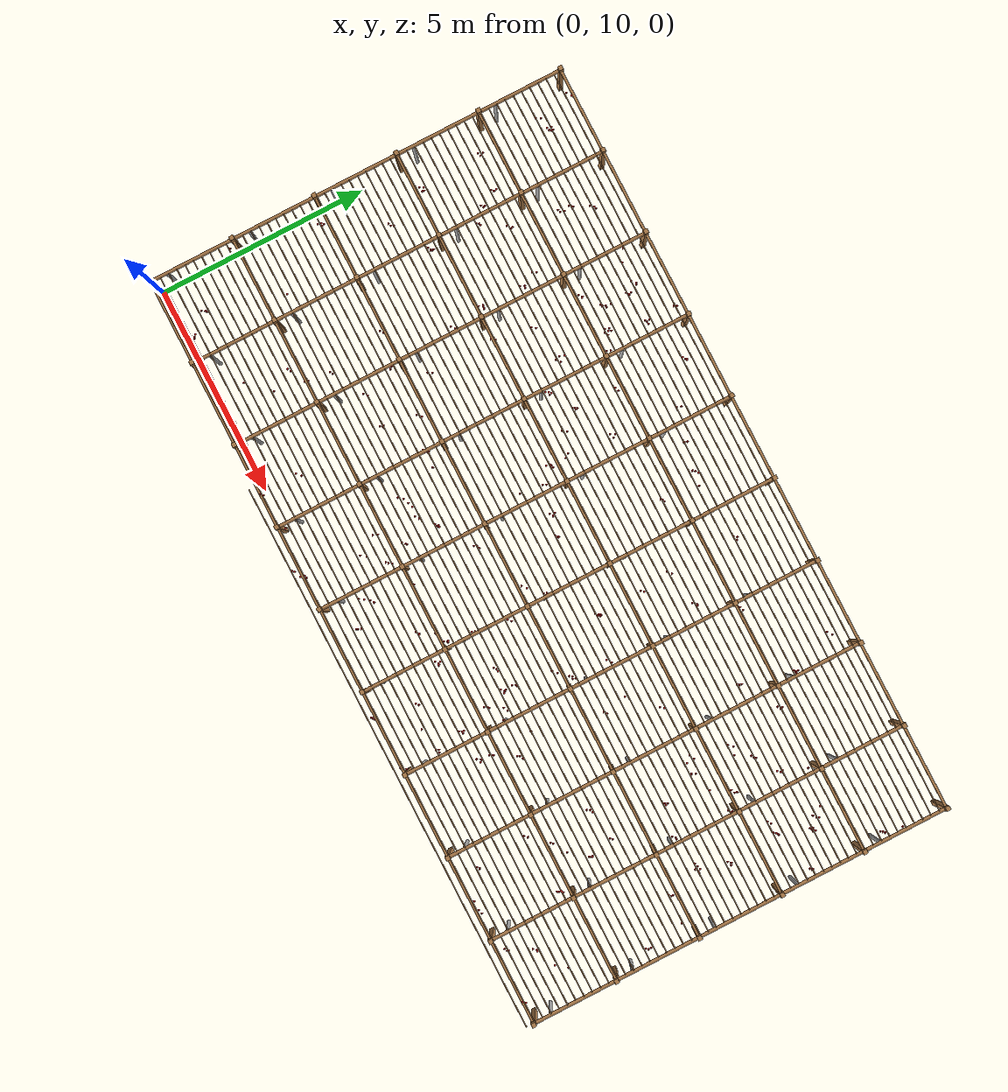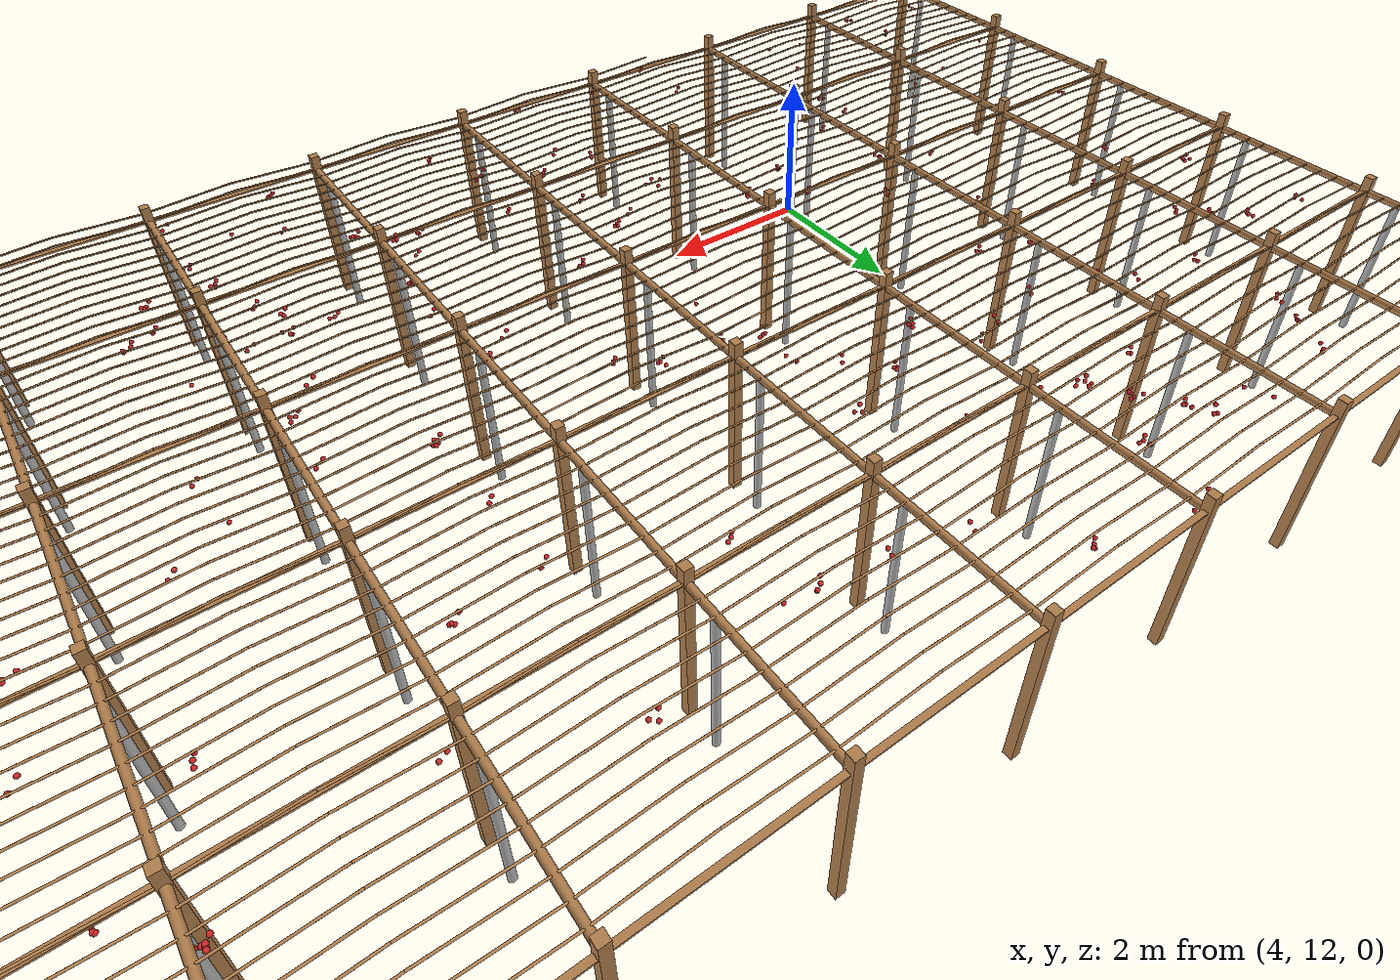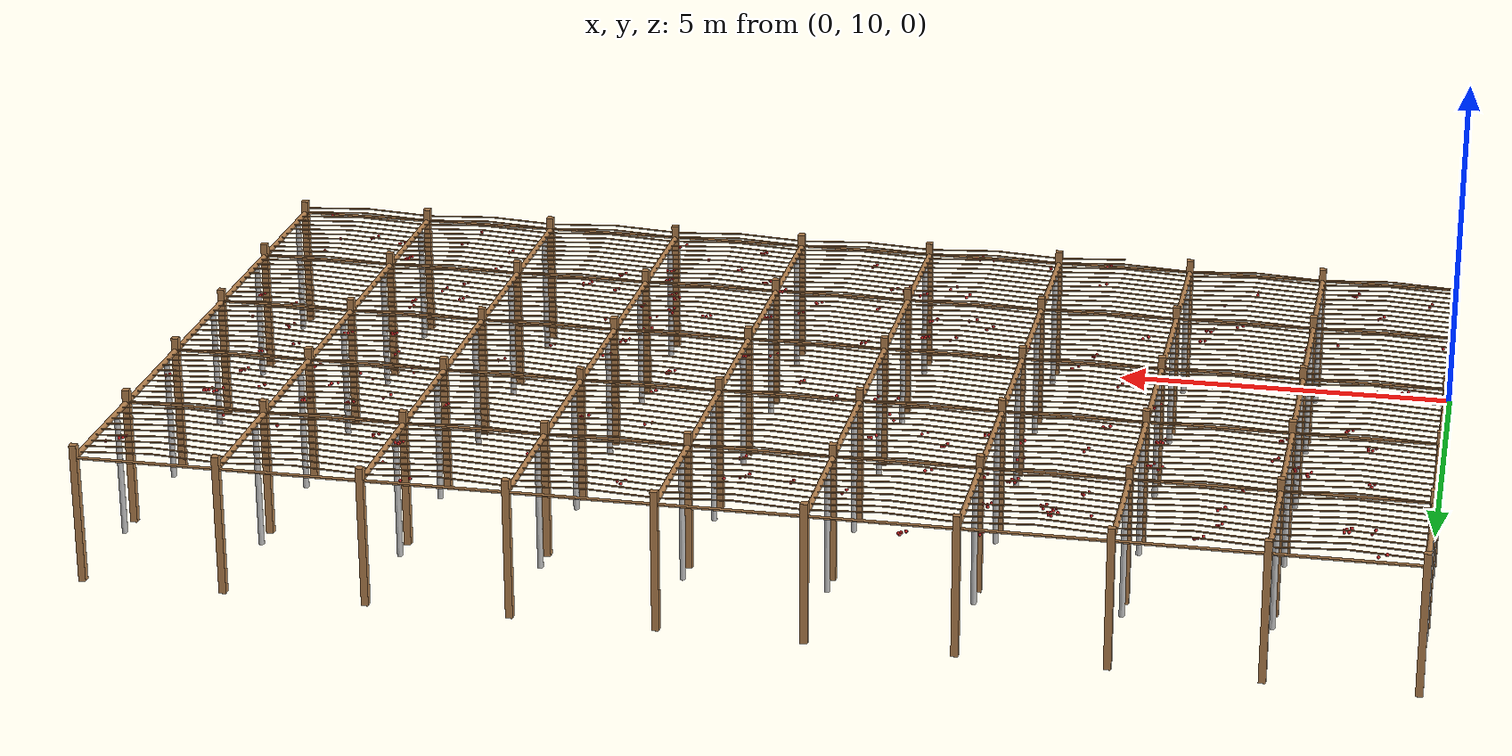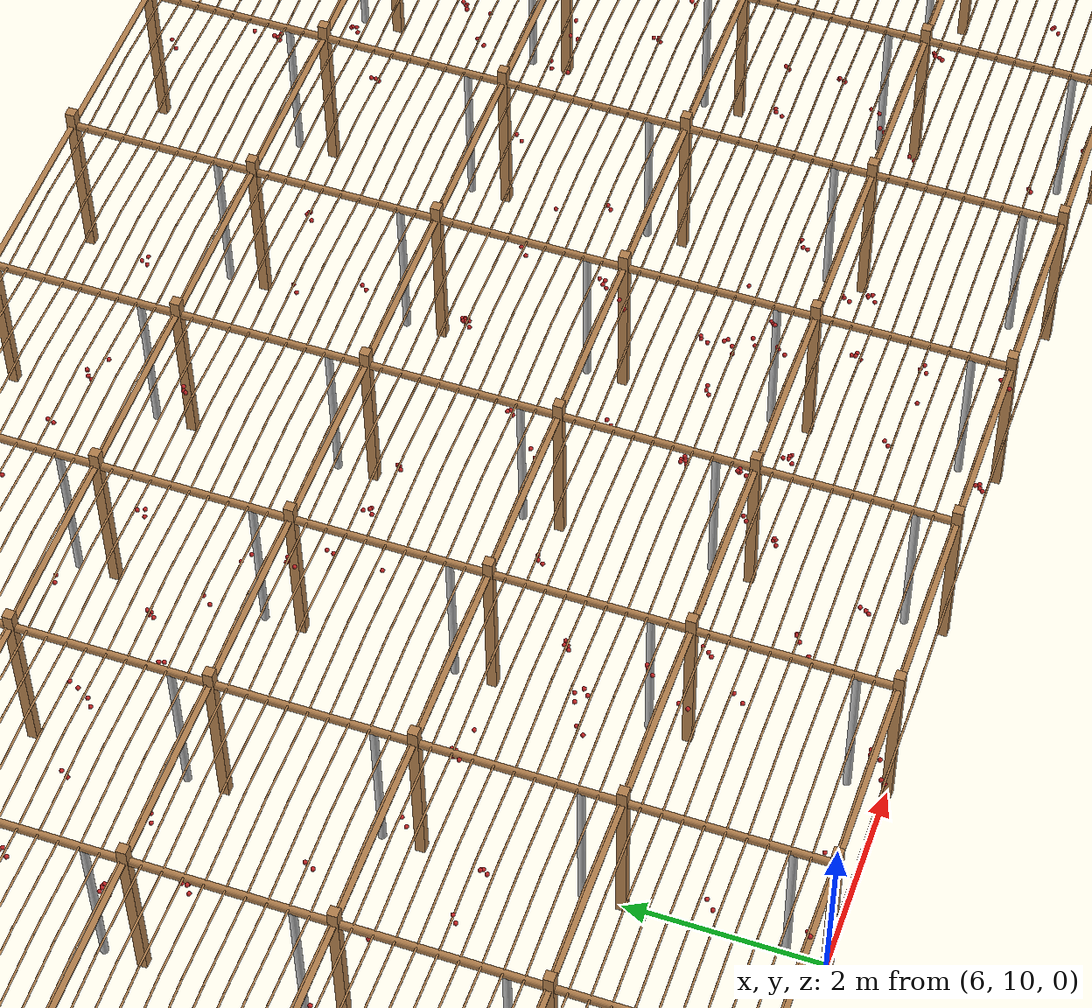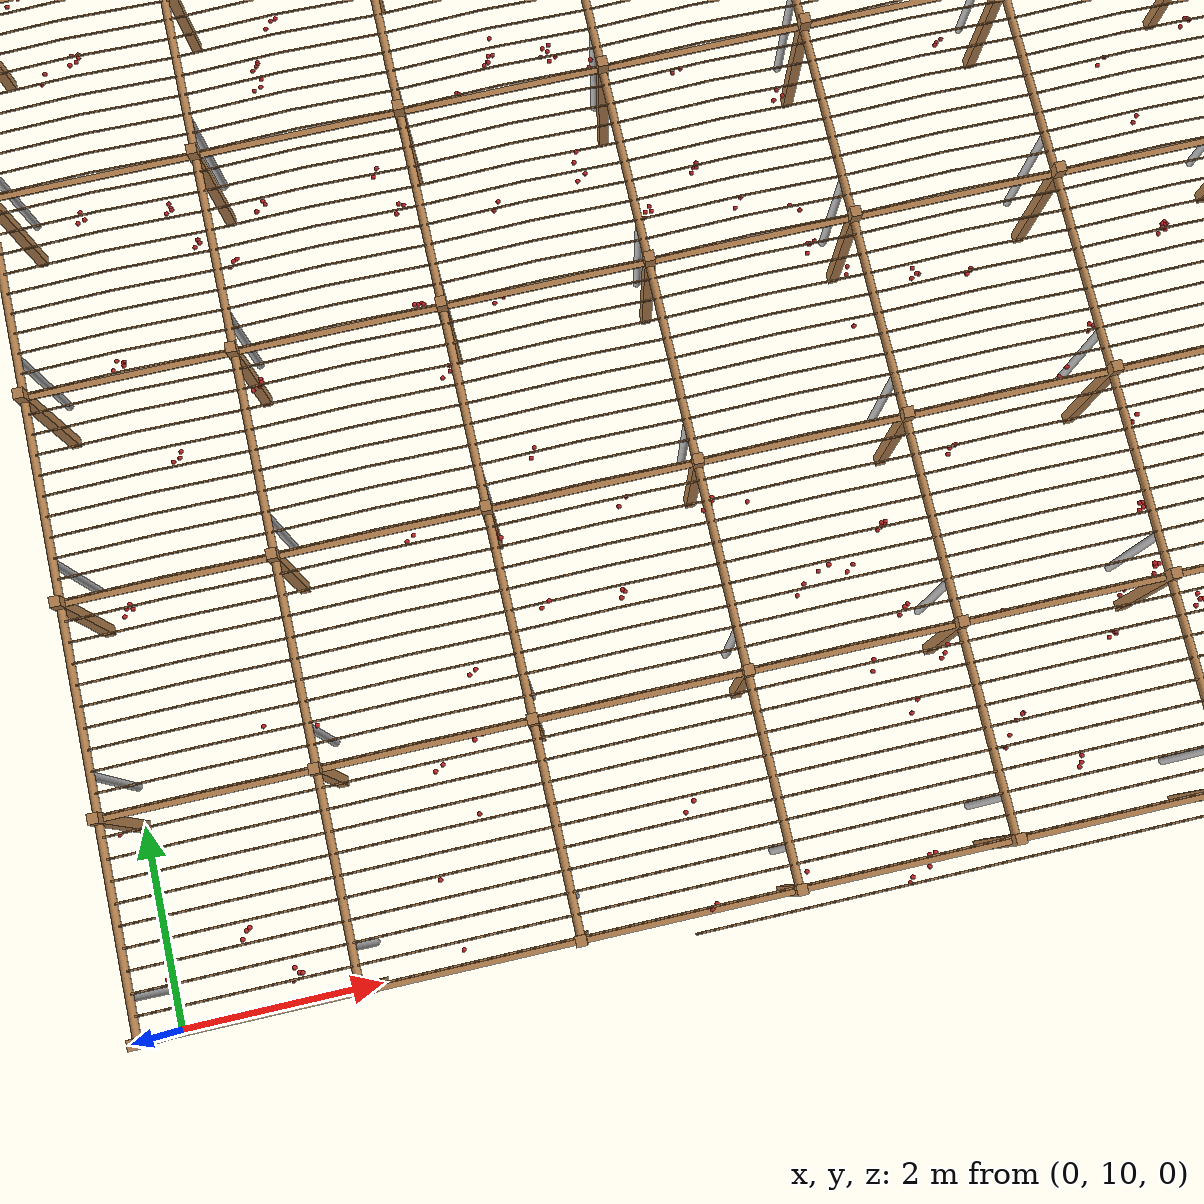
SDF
<sdf version="1.4">
 <model name="pergola">
  <include><name>post_5</name><pose>0.0 10.0 0 0 0 0</pose><uri>model://post</uri></include>
  <include><name>post_6</name><pose>0.0 12.0 0 0 0 0</pose><uri>model://post</uri></include>
  <include><name>post_7</name><pose>0.0 14.0 0 0 0 0</pose><uri>model://post</uri></include>
  <include><name>post_8</name><pose>0.0 16.0 0 0 0 0</pose><uri>model://post</uri></include>
  <include><name>post_9</name><pose>0.0 18.0 0 0 0 0</pose><uri>model://post</uri></include>
  <include><name>post_10</name><pose>0.0 20.0 0 0 0 0</pose><uri>model://post</uri></include>
  <include><name>post_16</name><pose>2.0 10.0 0 0 0 0</pose><uri>model://post</uri></include>
  <include><name>post_17</name><pose>2.0 12.0 0 0 0 0</pose><uri>model://post</uri></include>
  <include><name>post_18</name><pose>2.0 14.0 0 0 0 0</pose><uri>model://post</uri></include>
  <include><name>post_19</name><pose>2.0 16.0 0 0 0 0</pose><uri>model://post</uri></include>
  <include><name>post_20</name><pose>2.0 18.0 0 0 0 0</pose><uri>model://post</uri></include>
  <include><name>post_21</name><pose>2.0 20.0 0 0 0 0</pose><uri>model://post</uri></include>
  <include><name>post_27</name><pose>4.0 10.0 0 0 0 0</pose><uri>model://post</uri></include>
  <include><name>post_28</name><pose>4.0 12.0 0 0 0 0</pose><uri>model://post</uri></include>
  <include><name>post_29</name><pose>4.0 14.0 0 0 0 0</pose><uri>model://post</uri></include>
  <include><name>post_30</name><pose>4.0 16.0 0 0 0 0</pose><uri>model://post</uri></include>
  <include><name>post_31</name><pose>4.0 18.0 0 0 0 0</pose><uri>model://post</uri></include>
  <include><name>post_32</name><pose>4.0 20.0 0 0 0 0</pose><uri>model://post</uri></include>
  <include><name>post_38</name><pose>6.0 10.0 0 0 0 0</pose><uri>model://post</uri></include>
  <include><name>post_39</name><pose>6.0 12.0 0 0 0 0</pose><uri>model://post</uri></include>
  <include><name>post_40</name><pose>6.0 14.0 0 0 0 0</pose><uri>model://post</uri></include>
  <include><name>post_41</name><pose>6.0 16.0 0 0 0 0</pose><uri>model://post</uri></include>
  <include><name>post_42</name><pose>6.0 18.0 0 0 0 0</pose><uri>model://post</uri></include>
  <include><name>post_43</name><pose>6.0 20.0 0 0 0 0</pose><uri>model://post</uri></include>
  <include><name>post_49</name><pose>8.0 10.0 0 0 0 0</pose><uri>model://post</uri></include>
  <include><name>post_50</name><pose>8.0 12.0 0 0 0 0</pose><uri>model://post</uri></include>
  <include><name>post_51</name><pose>8.0 14.0 0 0 0 0</pose><uri>model://post</uri></include>
  <include><name>post_52</name><pose>8.0 16.0 0 0 0 0</pose><uri>model://post</uri></include>
  <include><name>post_53</name><pose>8.0 18.0 0 0 0 0</pose><uri>model://post</uri></include>
  <include><name>post_54</name><pose>8.0 20.0 0 0 0 0</pose><uri>model://post</uri></include>
  <include><name>post_60</name><pose>10.0 10.0 0 0 0 0</pose><uri>model://post</uri></include>
  <include><name>post_61</name><pose>10.0 12.0 0 0 0 0</pose><uri>model://post</uri></include>
  <include><name>post_62</name><pose>10.0 14.0 0 0 0 0</pose><uri>model://post</uri></include>
  <include><name>post_63</name><pose>10.0 16.0 0 0 0 0</pose><uri>model://post</uri></include>
  <include><name>post_64</name><pose>10.0 18.0 0 0 0 0</pose><uri>model://post</uri></include>
  <include><name>post_65</name><pose>10.0 20.0 0 0 0 0</pose><uri>model://post</uri></include>
  <include><name>post_71</name><pose>12.0 10.0 0 0 0 0</pose><uri>model://post</uri></include>
  <include><name>post_72</name><pose>12.0 12.0 0 0 0 0</pose><uri>model://post</uri></include>
  <include><name>post_73</name><pose>12.0 14.0 0 0 0 0</pose><uri>model://post</uri></include>
  <include><name>post_74</name><pose>12.0 16.0 0 0 0 0</pose><uri>model://post</uri></include>
  <include><name>post_75</name><pose>12.0 18.0 0 0 0 0</pose><uri>model://post</uri></include>
  <include><name>post_76</name><pose>12.0 20.0 0 0 0 0</pose><uri>model://post</uri></include>
  <include><name>post_82</name><pose>14.0 10.0 0 0 0 0</pose><uri>model://post</uri></include>
  <include><name>post_83</name><pose>14.0 12.0 0 0 0 0</pose><uri>model://post</uri></include>
  <include><name>post_84</name><pose>14.0 14.0 0 0 0 0</pose><uri>model://post</uri></include>
  <include><name>post_85</name><pose>14.0 16.0 0 0 0 0</pose><uri>model://post</uri></include>
  <include><name>post_86</name><pose>14.0 18.0 0 0 0 0</pose><uri>model://post</uri></include>
  <include><name>post_87</name><pose>14.0 20.0 0 0 0 0</pose><uri>model://post</uri></include>
  <include><name>post_93</name><pose>16.0 10.0 0 0 0 0</pose><uri>model://post</uri></include>
  <include><name>post_94</name><pose>16.0 12.0 0 0 0 0</pose><uri>model://post</uri></include>
  <include><name>post_95</name><pose>16.0 14.0 0 0 0 0</pose><uri>model://post</uri></include>
  <include><name>post_96</name><pose>16.0 16.0 0 0 0 0</pose><uri>model://post</uri></include>
  <include><name>post_97</name><pose>16.0 18.0 0 0 0 0</pose><uri>model://post</uri></include>
  <include><name>post_98</name><pose>16.0 20.0 0 0 0 0</pose><uri>model://post</uri></include>
  <include><name>post_104</name><pose>18.0 10.0 0 0 0 0</pose><uri>model://post</uri></include>
  <include><name>post_105</name><pose>18.0 12.0 0 0 0 0</pose><uri>model://post</uri></include>
  <include><name>post_106</name><pose>18.0 14.0 0 0 0 0</pose><uri>model://post</uri></include>
  <include><name>post_107</name><pose>18.0 16.0 0 0 0 0</pose><uri>model://post</uri></include>
  <include><name>post_108</name><pose>18.0 18.0 0 0 0 0</pose><uri>model://post</uri></include>
  <include><name>post_109</name><pose>18.0 20.0 0 0 0 0</pose><uri>model://post</uri></include>
  <link name="beam_5">
   <pose>1.0 10.0 1.81 0 0 0</pose>
   <collision name="collision"><geometry><box><size>2.0 0.06 0.02</size></box></geometry></collision>
   <visual name="visual">
    <geometry><box><size>2.0 0.06 0.02</size></box></geometry>
    <material><script><name>Gazebo/Wood</name></script></material>
   </visual>
   <inertial>
    <mass>5</mass>
    <inertia>
     <ixx>0.0016666666666666668</ixx>
     <ixy>0.0</ixy>
     <ixz>0.0</ixz>
     <iyy>1.6681666666666664</iyy>
     <iyz>0.0</iyz>
     <izz>1.6668333333333332</izz>
    </inertia>
   </inertial>
  </link>
  <link name="beam_6">
   <pose>1.0 12.0 1.81 0 0 0</pose>
   <collision name="collision"><geometry><box><size>2.0 0.06 0.02</size></box></geometry></collision>
   <visual name="visual">
    <geometry><box><size>2.0 0.06 0.02</size></box></geometry>
    <material><script><name>Gazebo/Wood</name></script></material>
   </visual>
   <inertial>
    <mass>5</mass>
    <inertia>
     <ixx>0.0016666666666666668</ixx>
     <ixy>0.0</ixy>
     <ixz>0.0</ixz>
     <iyy>1.6681666666666664</iyy>
     <iyz>0.0</iyz>
     <izz>1.6668333333333332</izz>
    </inertia>
   </inertial>
  </link>
  <link name="beam_7">
   <pose>1.0 14.0 1.81 0 0 0</pose>
   <collision name="collision"><geometry><box><size>2.0 0.06 0.02</size></box></geometry></collision>
   <visual name="visual">
    <geometry><box><size>2.0 0.06 0.02</size></box></geometry>
    <material><script><name>Gazebo/Wood</name></script></material>
   </visual>
   <inertial>
    <mass>5</mass>
    <inertia>
     <ixx>0.0016666666666666668</ixx>
     <ixy>0.0</ixy>
     <ixz>0.0</ixz>
     <iyy>1.6681666666666664</iyy>
     <iyz>0.0</iyz>
     <izz>1.6668333333333332</izz>
    </inertia>
   </inertial>
  </link>
  <link name="beam_8">
   <pose>1.0 16.0 1.81 0 0 0</pose>
   <collision name="collision"><geometry><box><size>2.0 0.06 0.02</size></box></geometry></collision>
   <visual name="visual">
    <geometry><box><size>2.0 0.06 0.02</size></box></geometry>
    <material><script><name>Gazebo/Wood</name></script></material>
   </visual>
   <inertial>
    <mass>5</mass>
    <inertia>
     <ixx>0.0016666666666666668</ixx>
     <ixy>0.0</ixy>
     <ixz>0.0</ixz>
     <iyy>1.6681666666666664</iyy>
     <iyz>0.0</iyz>
     <izz>1.6668333333333332</izz>
    </inertia>
   </inertial>
  </link>
  <link name="beam_9">
   <pose>1.0 18.0 1.81 0 0 0</pose>
   <collision name="collision"><geometry><box><size>2.0 0.06 0.02</size></box></geometry></collision>
   <visual name="visual">
    <geometry><box><size>2.0 0.06 0.02</size></box></geometry>
    <material><script><name>Gazebo/Wood</name></script></material>
   </visual>
   <inertial>
    <mass>5</mass>
    <inertia>
     <ixx>0.0016666666666666668</ixx>
     <ixy>0.0</ixy>
     <ixz>0.0</ixz>
     <iyy>1.6681666666666664</iyy>
     <iyz>0.0</iyz>
     <izz>1.6668333333333332</izz>
    </inertia>
   </inertial>
  </link>
  <link name="beam_10">
   <pose>1.0 20.0 1.81 0 0 0</pose>
   <collision name="collision"><geometry><box><size>2.0 0.06 0.02</size></box></geometry></collision>
   <visual name="visual">
    <geometry><box><size>2.0 0.06 0.02</size></box></geometry>
    <material><script><name>Gazebo/Wood</name></script></material>
   </visual>
   <inertial>
    <mass>5</mass>
    <inertia>
     <ixx>0.0016666666666666668</ixx>
     <ixy>0.0</ixy>
     <ixz>0.0</ixz>
     <iyy>1.6681666666666664</iyy>
     <iyz>0.0</iyz>
     <izz>1.6668333333333332</izz>
    </inertia>
   </inertial>
  </link>
  <link name="beam_16">
   <pose>3.0 10.0 1.81 0 0 0</pose>
   <collision name="collision"><geometry><box><size>2.0 0.06 0.02</size></box></geometry></collision>
   <visual name="visual">
    <geometry><box><size>2.0 0.06 0.02</size></box></geometry>
    <material><script><name>Gazebo/Wood</name></script></material>
   </visual>
   <inertial>
    <mass>5</mass>
    <inertia>
     <ixx>0.0016666666666666668</ixx>
     <ixy>0.0</ixy>
     <ixz>0.0</ixz>
     <iyy>1.6681666666666664</iyy>
     <iyz>0.0</iyz>
     <izz>1.6668333333333332</izz>
    </inertia>
   </inertial>
  </link>
  <link name="beam_17">
   <pose>3.0 12.0 1.81 0 0 0</pose>
   <collision name="collision"><geometry><box><size>2.0 0.06 0.02</size></box></geometry></collision>
   <visual name="visual">
    <geometry><box><size>2.0 0.06 0.02</size></box></geometry>
    <material><script><name>Gazebo/Wood</name></script></material>
   </visual>
   <inertial>
    <mass>5</mass>
    <inertia>
     <ixx>0.0016666666666666668</ixx>
     <ixy>0.0</ixy>
     <ixz>0.0</ixz>
     <iyy>1.6681666666666664</iyy>
     <iyz>0.0</iyz>
     <izz>1.6668333333333332</izz>
    </inertia>
   </inertial>
  </link>
  <link name="beam_18">
   <pose>3.0 14.0 1.81 0 0 0</pose>
   <collision name="collision"><geometry><box><size>2.0 0.06 0.02</size></box></geometry></collision>
   <visual name="visual">
    <geometry><box><size>2.0 0.06 0.02</size></box></geometry>
    <material><script><name>Gazebo/Wood</name></script></material>
   </visual>
   <inertial>
    <mass>5</mass>
    <inertia>
     <ixx>0.0016666666666666668</ixx>
     <ixy>0.0</ixy>
     <ixz>0.0</ixz>
     <iyy>1.6681666666666664</iyy>
     <iyz>0.0</iyz>
     <izz>1.6668333333333332</izz>
    </inertia>
   </inertial>
  </link>
  <link name="beam_19">
   <pose>3.0 16.0 1.81 0 0 0</pose>
   <collision name="collision"><geometry><box><size>2.0 0.06 0.02</size></box></geometry></collision>
   <visual name="visual">
    <geometry><box><size>2.0 0.06 0.02</size></box></geometry>
    <material><script><name>Gazebo/Wood</name></script></material>
   </visual>
   <inertial>
    <mass>5</mass>
    <inertia>
     <ixx>0.0016666666666666668</ixx>
     <ixy>0.0</ixy>
     <ixz>0.0</ixz>
     <iyy>1.6681666666666664</iyy>
     <iyz>0.0</iyz>
     <izz>1.6668333333333332</izz>
    </inertia>
   </inertial>
  </link>
  <link name="beam_20">
   <pose>3.0 18.0 1.81 0 0 0</pose>
   <collision name="collision"><geometry><box><size>2.0 0.06 0.02</size></box></geometry></collision>
   <visual name="visual">
    <geometry><box><size>2.0 0.06 0.02</size></box></geometry>
    <material><script><name>Gazebo/Wood</name></script></material>
   </visual>
   <inertial>
    <mass>5</mass>
    <inertia>
     <ixx>0.0016666666666666668</ixx>
     <ixy>0.0</ixy>
     <ixz>0.0</ixz>
     <iyy>1.6681666666666664</iyy>
     <iyz>0.0</iyz>
     <izz>1.6668333333333332</izz>
    </inertia>
   </inertial>
  </link>
  <link name="beam_21">
   <pose>3.0 20.0 1.81 0 0 0</pose>
   <collision name="collision"><geometry><box><size>2.0 0.06 0.02</size></box></geometry></collision>
   <visual name="visual">
    <geometry><box><size>2.0 0.06 0.02</size></box></geometry>
    <material><script><name>Gazebo/Wood</name></script></material>
   </visual>
   <inertial>
    <mass>5</mass>
    <inertia>
     <ixx>0.0016666666666666668</ixx>
     <ixy>0.0</ixy>
     <ixz>0.0</ixz>
     <iyy>1.6681666666666664</iyy>
     <iyz>0.0</iyz>
     <izz>1.6668333333333332</izz>
    </inertia>
   </inertial>
  </link>
  <link name="beam_27">
   <pose>5.0 10.0 1.81 0 0 0</pose>
   <collision name="collision"><geometry><box><size>2.0 0.06 0.02</size></box></geometry></collision>
   <visual name="visual">
    <geometry><box><size>2.0 0.06 0.02</size></box></geometry>
    <material><script><name>Gazebo/Wood</name></script></material>
   </visual>
   <inertial>
    <mass>5</mass>
    <inertia>
     <ixx>0.0016666666666666668</ixx>
     <ixy>0.0</ixy>
     <ixz>0.0</ixz>
     <iyy>1.6681666666666664</iyy>
     <iyz>0.0</iyz>
     <izz>1.6668333333333332</izz>
    </inertia>
   </inertial>
  </link>
  <link name="beam_28">
   <pose>5.0 12.0 1.81 0 0 0</pose>
   <collision name="collision"><geometry><box><size>2.0 0.06 0.02</size></box></geometry></collision>
   <visual name="visual">
    <geometry><box><size>2.0 0.06 0.02</size></box></geometry>
    <material><script><name>Gazebo/Wood</name></script></material>
   </visual>
   <inertial>
    <mass>5</mass>
    <inertia>
     <ixx>0.0016666666666666668</ixx>
     <ixy>0.0</ixy>
     <ixz>0.0</ixz>
     <iyy>1.6681666666666664</iyy>
     <iyz>0.0</iyz>
     <izz>1.6668333333333332</izz>
    </inertia>
   </inertial>
  </link>
  <link name="beam_29">
   <pose>5.0 14.0 1.81 0 0 0</pose>
   <collision name="collision"><geometry><box><size>2.0 0.06 0.02</size></box></geometry></collision>
   <visual name="visual">
    <geometry><box><size>2.0 0.06 0.02</size></box></geometry>
    <material><script><name>Gazebo/Wood</name></script></material>
   </visual>
   <inertial>
    <mass>5</mass>
    <inertia>
     <ixx>0.0016666666666666668</ixx>
     <ixy>0.0</ixy>
     <ixz>0.0</ixz>
     <iyy>1.6681666666666664</iyy>
     <iyz>0.0</iyz>
     <izz>1.6668333333333332</izz>
    </inertia>
   </inertial>
  </link>
  <link name="beam_30">
   <pose>5.0 16.0 1.81 0 0 0</pose>
   <collision name="collision"><geometry><box><size>2.0 0.06 0.02</size></box></geometry></collision>
   <visual name="visual">
    <geometry><box><size>2.0 0.06 0.02</size></box></geometry>
    <material><script><name>Gazebo/Wood</name></script></material>
   </visual>
   <inertial>
    <mass>5</mass>
    <inertia>
     <ixx>0.0016666666666666668</ixx>
     <ixy>0.0</ixy>
     <ixz>0.0</ixz>
     <iyy>1.6681666666666664</iyy>
     <iyz>0.0</iyz>
     <izz>1.6668333333333332</izz>
    </inertia>
   </inertial>
  </link>
  <link name="beam_31">
   <pose>5.0 18.0 1.81 0 0 0</pose>
   <collision name="collision"><geometry><box><size>2.0 0.06 0.02</size></box></geometry></collision>
   <visual name="visual">
    <geometry><box><size>2.0 0.06 0.02</size></box></geometry>
    <material><script><name>Gazebo/Wood</name></script></material>
   </visual>
   <inertial>
    <mass>5</mass>
    <inertia>
     <ixx>0.0016666666666666668</ixx>
     <ixy>0.0</ixy>
     <ixz>0.0</ixz>
     <iyy>1.6681666666666664</iyy>
     <iyz>0.0</iyz>
     <izz>1.6668333333333332</izz>
    </inertia>
   </inertial>
  </link>
  <link name="beam_32">
   <pose>5.0 20.0 1.81 0 0 0</pose>
   <collision name="collision"><geometry><box><size>2.0 0.06 0.02</size></box></geometry></collision>
   <visual name="visual">
    <geometry><box><size>2.0 0.06 0.02</size></box></geometry>
    <material><script><name>Gazebo/Wood</name></script></material>
   </visual>
   <inertial>
    <mass>5</mass>
    <inertia>
     <ixx>0.0016666666666666668</ixx>
     <ixy>0.0</ixy>
     <ixz>0.0</ixz>
     <iyy>1.6681666666666664</iyy>
     <iyz>0.0</iyz>
     <izz>1.6668333333333332</izz>
    </inertia>
   </inertial>
  </link>
  <link name="beam_38">
   <pose>7.0 10.0 1.81 0 0 0</pose>
   <collision name="collision"><geometry><box><size>2.0 0.06 0.02</size></box></geometry></collision>
   <visual name="visual">
    <geometry><box><size>2.0 0.06 0.02</size></box></geometry>
    <material><script><name>Gazebo/Wood</name></script></material>
   </visual>
   <inertial>
    <mass>5</mass>
    <inertia>
     <ixx>0.0016666666666666668</ixx>
     <ixy>0.0</ixy>
     <ixz>0.0</ixz>
     <iyy>1.6681666666666664</iyy>
     <iyz>0.0</iyz>
     <izz>1.6668333333333332</izz>
    </inertia>
   </inertial>
  </link>
  <link name="beam_39">
   <pose>7.0 12.0 1.81 0 0 0</pose>
   <collision name="collision"><geometry><box><size>2.0 0.06 0.02</size></box></geometry></collision>
   <visual name="visual">
    <geometry><box><size>2.0 0.06 0.02</size></box></geometry>
    <material><script><name>Gazebo/Wood</name></script></material>
   </visual>
   <inertial>
    <mass>5</mass>
    <inertia>
     <ixx>0.0016666666666666668</ixx>
     <ixy>0.0</ixy>
     <ixz>0.0</ixz>
     <iyy>1.6681666666666664</iyy>
     <iyz>0.0</iyz>
     <izz>1.6668333333333332</izz>
    </inertia>
   </inertial>
  </link>
  <link name="beam_40">
   <pose>7.0 14.0 1.81 0 0 0</pose>
   <collision name="collision"><geometry><box><size>2.0 0.06 0.02</size></box></geometry></collision>
   <visual name="visual">
    <geometry><box><size>2.0 0.06 0.02</size></box></geometry>
    <material><script><name>Gazebo/Wood</name></script></material>
   </visual>
   <inertial>
    <mass>5</mass>
    <inertia>
     <ixx>0.0016666666666666668</ixx>
     <ixy>0.0</ixy>
     <ixz>0.0</ixz>
     <iyy>1.6681666666666664</iyy>
     <iyz>0.0</iyz>
     <izz>1.6668333333333332</izz>
    </inertia>
   </inertial>
  </link>
  <link name="beam_41">
   <pose>7.0 16.0 1.81 0 0 0</pose>
   <collision name="collision"><geometry><box><size>2.0 0.06 0.02</size></box></geometry></collision>
   <visual name="visual">
    <geometry><box><size>2.0 0.06 0.02</size></box></geometry>
    <material><script><name>Gazebo/Wood</name></script></material>
   </visual>
   <inertial>
    <mass>5</mass>
    <inertia>
     <ixx>0.0016666666666666668</ixx>
     <ixy>0.0</ixy>
     <ixz>0.0</ixz>
     <iyy>1.6681666666666664</iyy>
     <iyz>0.0</iyz>
     <izz>1.6668333333333332</izz>
    </inertia>
   </inertial>
  </link>
  <link name="beam_42">
   <pose>7.0 18.0 1.81 0 0 0</pose>
   <collision name="collision"><geometry><box><size>2.0 0.06 0.02</size></box></geometry></collision>
   <visual name="visual">
    <geometry><box><size>2.0 0.06 0.02</size></box></geometry>
    <material><script><name>Gazebo/Wood</name></script></material>
   </visual>
   <inertial>
    <mass>5</mass>
    <inertia>
     <ixx>0.0016666666666666668</ixx>
     <ixy>0.0</ixy>
     <ixz>0.0</ixz>
     <iyy>1.6681666666666664</iyy>
     <iyz>0.0</iyz>
     <izz>1.6668333333333332</izz>
    </inertia>
   </inertial>
  </link>
  <link name="beam_43">
   <pose>7.0 20.0 1.81 0 0 0</pose>
   <collision name="collision"><geometry><box><size>2.0 0.06 0.02</size></box></geometry></collision>
   <visual name="visual">
    <geometry><box><size>2.0 0.06 0.02</size></box></geometry>
    <material><script><name>Gazebo/Wood</name></script></material>
   </visual>
   <inertial>
    <mass>5</mass>
    <inertia>
     <ixx>0.0016666666666666668</ixx>
     <ixy>0.0</ixy>
     <ixz>0.0</ixz>
     <iyy>1.6681666666666664</iyy>
     <iyz>0.0</iyz>
     <izz>1.6668333333333332</izz>
    </inertia>
   </inertial>
  </link>
  <link name="beam_49">
   <pose>9.0 10.0 1.81 0 0 0</pose>
   <collision name="collision"><geometry><box><size>2.0 0.06 0.02</size></box></geometry></collision>
   <visual name="visual">
    <geometry><box><size>2.0 0.06 0.02</size></box></geometry>
    <material><script><name>Gazebo/Wood</name></script></material>
   </visual>
   <inertial>
    <mass>5</mass>
    <inertia>
     <ixx>0.0016666666666666668</ixx>
     <ixy>0.0</ixy>
     <ixz>0.0</ixz>
     <iyy>1.6681666666666664</iyy>
     <iyz>0.0</iyz>
     <izz>1.6668333333333332</izz>
    </inertia>
   </inertial>
  </link>
  <link name="beam_50">
   <pose>9.0 12.0 1.81 0 0 0</pose>
   <collision name="collision"><geometry><box><size>2.0 0.06 0.02</size></box></geometry></collision>
   <visual name="visual">
    <geometry><box><size>2.0 0.06 0.02</size></box></geometry>
    <material><script><name>Gazebo/Wood</name></script></material>
   </visual>
   <inertial>
    <mass>5</mass>
    <inertia>
     <ixx>0.0016666666666666668</ixx>
     <ixy>0.0</ixy>
     <ixz>0.0</ixz>
     <iyy>1.6681666666666664</iyy>
     <iyz>0.0</iyz>
     <izz>1.6668333333333332</izz>
    </inertia>
   </inertial>
  </link>
  <link name="beam_51">
   <pose>9.0 14.0 1.81 0 0 0</pose>
   <collision name="collision"><geometry><box><size>2.0 0.06 0.02</size></box></geometry></collision>
   <visual name="visual">
    <geometry><box><size>2.0 0.06 0.02</size></box></geometry>
    <material><script><name>Gazebo/Wood</name></script></material>
   </visual>
   <inertial>
    <mass>5</mass>
    <inertia>
     <ixx>0.0016666666666666668</ixx>
     <ixy>0.0</ixy>
     <ixz>0.0</ixz>
     <iyy>1.6681666666666664</iyy>
     <iyz>0.0</iyz>
     <izz>1.6668333333333332</izz>
    </inertia>
   </inertial>
  </link>
  <link name="beam_52">
   <pose>9.0 16.0 1.81 0 0 0</pose>
   <collision name="collision"><geometry><box><size>2.0 0.06 0.02</size></box></geometry></collision>
   <visual name="visual">
    <geometry><box><size>2.0 0.06 0.02</size></box></geometry>
    <material><script><name>Gazebo/Wood</name></script></material>
   </visual>
   <inertial>
    <mass>5</mass>
    <inertia>
     <ixx>0.0016666666666666668</ixx>
     <ixy>0.0</ixy>
     <ixz>0.0</ixz>
     <iyy>1.6681666666666664</iyy>
     <iyz>0.0</iyz>
     <izz>1.6668333333333332</izz>
    </inertia>
   </inertial>
  </link>
  <link name="beam_53">
   <pose>9.0 18.0 1.81 0 0 0</pose>
   <collision name="collision"><geometry><box><size>2.0 0.06 0.02</size></box></geometry></collision>
   <visual name="visual">
    <geometry><box><size>2.0 0.06 0.02</size></box></geometry>
    <material><script><name>Gazebo/Wood</name></script></material>
   </visual>
   <inertial>
    <mass>5</mass>
    <inertia>
     <ixx>0.0016666666666666668</ixx>
     <ixy>0.0</ixy>
     <ixz>0.0</ixz>
     <iyy>1.6681666666666664</iyy>
     <iyz>0.0</iyz>
     <izz>1.6668333333333332</izz>
    </inertia>
   </inertial>
  </link>
  <link name="beam_54">
   <pose>9.0 20.0 1.81 0 0 0</pose>
   <collision name="collision"><geometry><box><size>2.0 0.06 0.02</size></box></geometry></collision>
   <visual name="visual">
    <geometry><box><size>2.0 0.06 0.02</size></box></geometry>
    <material><script><name>Gazebo/Wood</name></script></material>
   </visual>
   <inertial>
    <mass>5</mass>
    <inertia>
     <ixx>0.0016666666666666668</ixx>
     <ixy>0.0</ixy>
     <ixz>0.0</ixz>
     <iyy>1.6681666666666664</iyy>
     <iyz>0.0</iyz>
     <izz>1.6668333333333332</izz>
    </inertia>
   </inertial>
  </link>
  <link name="beam_60">
   <pose>11.0 10.0 1.81 0 0 0</pose>
   <collision name="collision"><geometry><box><size>2.0 0.06 0.02</size></box></geometry></collision>
   <visual name="visual">
    <geometry><box><size>2.0 0.06 0.02</size></box></geometry>
    <material><script><name>Gazebo/Wood</name></script></material>
   </visual>
   <inertial>
    <mass>5</mass>
    <inertia>
     <ixx>0.0016666666666666668</ixx>
     <ixy>0.0</ixy>
     <ixz>0.0</ixz>
     <iyy>1.6681666666666664</iyy>
     <iyz>0.0</iyz>
     <izz>1.6668333333333332</izz>
    </inertia>
   </inertial>
  </link>
  <link name="beam_61">
   <pose>11.0 12.0 1.81 0 0 0</pose>
   <collision name="collision"><geometry><box><size>2.0 0.06 0.02</size></box></geometry></collision>
   <visual name="visual">
    <geometry><box><size>2.0 0.06 0.02</size></box></geometry>
    <material><script><name>Gazebo/Wood</name></script></material>
   </visual>
   <inertial>
    <mass>5</mass>
    <inertia>
     <ixx>0.0016666666666666668</ixx>
     <ixy>0.0</ixy>
     <ixz>0.0</ixz>
     <iyy>1.6681666666666664</iyy>
     <iyz>0.0</iyz>
     <izz>1.6668333333333332</izz>
    </inertia>
   </inertial>
  </link>
  <link name="beam_62">
   <pose>11.0 14.0 1.81 0 0 0</pose>
   <collision name="collision"><geometry><box><size>2.0 0.06 0.02</size></box></geometry></collision>
   <visual name="visual">
    <geometry><box><size>2.0 0.06 0.02</size></box></geometry>
    <material><script><name>Gazebo/Wood</name></script></material>
   </visual>
   <inertial>
    <mass>5</mass>
    <inertia>
     <ixx>0.0016666666666666668</ixx>
     <ixy>0.0</ixy>
     <ixz>0.0</ixz>
     <iyy>1.6681666666666664</iyy>
     <iyz>0.0</iyz>
     <izz>1.6668333333333332</izz>
    </inertia>
   </inertial>
  </link>
  <link name="beam_63">
   <pose>11.0 16.0 1.81 0 0 0</pose>
   <collision name="collision"><geometry><box><size>2.0 0.06 0.02</size></box></geometry></collision>
   <visual name="visual">
    <geometry><box><size>2.0 0.06 0.02</size></box></geometry>
    <material><script><name>Gazebo/Wood</name></script></material>
   </visual>
   <inertial>
    <mass>5</mass>
    <inertia>
     <ixx>0.0016666666666666668</ixx>
     <ixy>0.0</ixy>
     <ixz>0.0</ixz>
     <iyy>1.6681666666666664</iyy>
     <iyz>0.0</iyz>
     <izz>1.6668333333333332</izz>
    </inertia>
   </inertial>
  </link>
  <link name="beam_64">
   <pose>11.0 18.0 1.81 0 0 0</pose>
   <collision name="collision"><geometry><box><size>2.0 0.06 0.02</size></box></geometry></collision>
   <visual name="visual">
    <geometry><box><size>2.0 0.06 0.02</size></box></geometry>
    <material><script><name>Gazebo/Wood</name></script></material>
   </visual>
   <inertial>
    <mass>5</mass>
    <inertia>
     <ixx>0.0016666666666666668</ixx>
     <ixy>0.0</ixy>
     <ixz>0.0</ixz>
     <iyy>1.6681666666666664</iyy>
     <iyz>0.0</iyz>
     <izz>1.6668333333333332</izz>
    </inertia>
   </inertial>
  </link>
  <link name="beam_65">
   <pose>11.0 20.0 1.81 0 0 0</pose>
   <collision name="collision"><geometry><box><size>2.0 0.06 0.02</size></box></geometry></collision>
   <visual name="visual">
    <geometry><box><size>2.0 0.06 0.02</size></box></geometry>
    <material><script><name>Gazebo/Wood</name></script></material>
   </visual>
   <inertial>
    <mass>5</mass>
    <inertia>
     <ixx>0.0016666666666666668</ixx>
     <ixy>0.0</ixy>
     <ixz>0.0</ixz>
     <iyy>1.6681666666666664</iyy>
     <iyz>0.0</iyz>
     <izz>1.6668333333333332</izz>
    </inertia>
   </inertial>
  </link>
  <link name="beam_71">
   <pose>13.0 10.0 1.81 0 0 0</pose>
   <collision name="collision"><geometry><box><size>2.0 0.06 0.02</size></box></geometry></collision>
   <visual name="visual">
    <geometry><box><size>2.0 0.06 0.02</size></box></geometry>
    <material><script><name>Gazebo/Wood</name></script></material>
   </visual>
   <inertial>
    <mass>5</mass>
    <inertia>
     <ixx>0.0016666666666666668</ixx>
     <ixy>0.0</ixy>
     <ixz>0.0</ixz>
     <iyy>1.6681666666666664</iyy>
     <iyz>0.0</iyz>
     <izz>1.6668333333333332</izz>
    </inertia>
   </inertial>
  </link>
  <link name="beam_72">
   <pose>13.0 12.0 1.81 0 0 0</pose>
   <collision name="collision"><geometry><box><size>2.0 0.06 0.02</size></box></geometry></collision>
   <visual name="visual">
    <geometry><box><size>2.0 0.06 0.02</size></box></geometry>
    <material><script><name>Gazebo/Wood</name></script></material>
   </visual>
   <inertial>
    <mass>5</mass>
    <inertia>
     <ixx>0.0016666666666666668</ixx>
     <ixy>0.0</ixy>
     <ixz>0.0</ixz>
     <iyy>1.6681666666666664</iyy>
     <iyz>0.0</iyz>
     <izz>1.6668333333333332</izz>
    </inertia>
   </inertial>
  </link>
  <link name="beam_73">
   <pose>13.0 14.0 1.81 0 0 0</pose>
   <collision name="collision"><geometry><box><size>2.0 0.06 0.02</size></box></geometry></collision>
   <visual name="visual">
    <geometry><box><size>2.0 0.06 0.02</size></box></geometry>
    <material><script><name>Gazebo/Wood</name></script></material>
   </visual>
   <inertial>
    <mass>5</mass>
    <inertia>
     <ixx>0.0016666666666666668</ixx>
     <ixy>0.0</ixy>
     <ixz>0.0</ixz>
     <iyy>1.6681666666666664</iyy>
     <iyz>0.0</iyz>
     <izz>1.6668333333333332</izz>
    </inertia>
   </inertial>
  </link>
  <link name="beam_74">
   <pose>13.0 16.0 1.81 0 0 0</pose>
   <collision name="collision"><geometry><box><size>2.0 0.06 0.02</size></box></geometry></collision>
   <visual name="visual">
    <geometry><box><size>2.0 0.06 0.02</size></box></geometry>
    <material><script><name>Gazebo/Wood</name></script></material>
   </visual>
   <inertial>
    <mass>5</mass>
    <inertia>
     <ixx>0.0016666666666666668</ixx>
     <ixy>0.0</ixy>
     <ixz>0.0</ixz>
     <iyy>1.6681666666666664</iyy>
     <iyz>0.0</iyz>
     <izz>1.6668333333333332</izz>
    </inertia>
   </inertial>
  </link>
  <link name="beam_75">
   <pose>13.0 18.0 1.81 0 0 0</pose>
   <collision name="collision"><geometry><box><size>2.0 0.06 0.02</size></box></geometry></collision>
   <visual name="visual">
    <geometry><box><size>2.0 0.06 0.02</size></box></geometry>
    <material><script><name>Gazebo/Wood</name></script></material>
   </visual>
   <inertial>
    <mass>5</mass>
    <inertia>
     <ixx>0.0016666666666666668</ixx>
     <ixy>0.0</ixy>
     <ixz>0.0</ixz>
     <iyy>1.6681666666666664</iyy>
     <iyz>0.0</iyz>
     <izz>1.6668333333333332</izz>
    </inertia>
   </inertial>
  </link>
  <link name="beam_76">
   <pose>13.0 20.0 1.81 0 0 0</pose>
   <collision name="collision"><geometry><box><size>2.0 0.06 0.02</size></box></geometry></collision>
   <visual name="visual">
    <geometry><box><size>2.0 0.06 0.02</size></box></geometry>
    <material><script><name>Gazebo/Wood</name></script></material>
   </visual>
   <inertial>
    <mass>5</mass>
    <inertia>
     <ixx>0.0016666666666666668</ixx>
     <ixy>0.0</ixy>
     <ixz>0.0</ixz>
     <iyy>1.6681666666666664</iyy>
     <iyz>0.0</iyz>
     <izz>1.6668333333333332</izz>
    </inertia>
   </inertial>
  </link>
  <link name="beam_82">
   <pose>15.0 10.0 1.81 0 0 0</pose>
   <collision name="collision"><geometry><box><size>2.0 0.06 0.02</size></box></geometry></collision>
   <visual name="visual">
    <geometry><box><size>2.0 0.06 0.02</size></box></geometry>
    <material><script><name>Gazebo/Wood</name></script></material>
   </visual>
   <inertial>
    <mass>5</mass>
    <inertia>
     <ixx>0.0016666666666666668</ixx>
     <ixy>0.0</ixy>
     <ixz>0.0</ixz>
     <iyy>1.6681666666666664</iyy>
     <iyz>0.0</iyz>
     <izz>1.6668333333333332</izz>
    </inertia>
   </inertial>
  </link>
  <link name="beam_83">
   <pose>15.0 12.0 1.81 0 0 0</pose>
   <collision name="collision"><geometry><box><size>2.0 0.06 0.02</size></box></geometry></collision>
   <visual name="visual">
    <geometry><box><size>2.0 0.06 0.02</size></box></geometry>
    <material><script><name>Gazebo/Wood</name></script></material>
   </visual>
   <inertial>
    <mass>5</mass>
    <inertia>
     <ixx>0.0016666666666666668</ixx>
     <ixy>0.0</ixy>
     <ixz>0.0</ixz>
     <iyy>1.6681666666666664</iyy>
     <iyz>0.0</iyz>
     <izz>1.6668333333333332</izz>
    </inertia>
   </inertial>
  </link>
  <link name="beam_84">
   <pose>15.0 14.0 1.81 0 0 0</pose>
   <collision name="collision"><geometry><box><size>2.0 0.06 0.02</size></box></geometry></collision>
   <visual name="visual">
    <geometry><box><size>2.0 0.06 0.02</size></box></geometry>
    <material><script><name>Gazebo/Wood</name></script></material>
   </visual>
   <inertial>
    <mass>5</mass>
    <inertia>
     <ixx>0.0016666666666666668</ixx>
     <ixy>0.0</ixy>
     <ixz>0.0</ixz>
     <iyy>1.6681666666666664</iyy>
     <iyz>0.0</iyz>
     <izz>1.6668333333333332</izz>
    </inertia>
   </inertial>
  </link>
  <link name="beam_85">
   <pose>15.0 16.0 1.81 0 0 0</pose>
   <collision name="collision"><geometry><box><size>2.0 0.06 0.02</size></box></geometry></collision>
   <visual name="visual">
    <geometry><box><size>2.0 0.06 0.02</size></box></geometry>
    <material><script><name>Gazebo/Wood</name></script></material>
   </visual>
   <inertial>
    <mass>5</mass>
    <inertia>
     <ixx>0.0016666666666666668</ixx>
     <ixy>0.0</ixy>
     <ixz>0.0</ixz>
     <iyy>1.6681666666666664</iyy>
     <iyz>0.0</iyz>
     <izz>1.6668333333333332</izz>
    </inertia>
   </inertial>
  </link>
  <link name="beam_86">
   <pose>15.0 18.0 1.81 0 0 0</pose>
   <collision name="collision"><geometry><box><size>2.0 0.06 0.02</size></box></geometry></collision>
   <visual name="visual">
    <geometry><box><size>2.0 0.06 0.02</size></box></geometry>
    <material><script><name>Gazebo/Wood</name></script></material>
   </visual>
   <inertial>
    <mass>5</mass>
    <inertia>
     <ixx>0.0016666666666666668</ixx>
     <ixy>0.0</ixy>
     <ixz>0.0</ixz>
     <iyy>1.6681666666666664</iyy>
     <iyz>0.0</iyz>
     <izz>1.6668333333333332</izz>
    </inertia>
   </inertial>
  </link>
  <link name="beam_87">
   <pose>15.0 20.0 1.81 0 0 0</pose>
   <collision name="collision"><geometry><box><size>2.0 0.06 0.02</size></box></geometry></collision>
   <visual name="visual">
    <geometry><box><size>2.0 0.06 0.02</size></box></geometry>
    <material><script><name>Gazebo/Wood</name></script></material>
   </visual>
   <inertial>
    <mass>5</mass>
    <inertia>
     <ixx>0.0016666666666666668</ixx>
     <ixy>0.0</ixy>
     <ixz>0.0</ixz>
     <iyy>1.6681666666666664</iyy>
     <iyz>0.0</iyz>
     <izz>1.6668333333333332</izz>
    </inertia>
   </inertial>
  </link>
  <link name="beam_93">
   <pose>17.0 10.0 1.81 0 0 0</pose>
   <collision name="collision"><geometry><box><size>2.0 0.06 0.02</size></box></geometry></collision>
   <visual name="visual">
    <geometry><box><size>2.0 0.06 0.02</size></box></geometry>
    <material><script><name>Gazebo/Wood</name></script></material>
   </visual>
   <inertial>
    <mass>5</mass>
    <inertia>
     <ixx>0.0016666666666666668</ixx>
     <ixy>0.0</ixy>
     <ixz>0.0</ixz>
     <iyy>1.6681666666666664</iyy>
     <iyz>0.0</iyz>
     <izz>1.6668333333333332</izz>
    </inertia>
   </inertial>
  </link>
  <link name="beam_94">
   <pose>17.0 12.0 1.81 0 0 0</pose>
   <collision name="collision"><geometry><box><size>2.0 0.06 0.02</size></box></geometry></collision>
   <visual name="visual">
    <geometry><box><size>2.0 0.06 0.02</size></box></geometry>
    <material><script><name>Gazebo/Wood</name></script></material>
   </visual>
   <inertial>
    <mass>5</mass>
    <inertia>
     <ixx>0.0016666666666666668</ixx>
     <ixy>0.0</ixy>
     <ixz>0.0</ixz>
     <iyy>1.6681666666666664</iyy>
     <iyz>0.0</iyz>
     <izz>1.6668333333333332</izz>
    </inertia>
   </inertial>
  </link>
  <link name="beam_95">
   <pose>17.0 14.0 1.81 0 0 0</pose>
   <collision name="collision"><geometry><box><size>2.0 0.06 0.02</size></box></geometry></collision>
   <visual name="visual">
    <geometry><box><size>2.0 0.06 0.02</size></box></geometry>
    <material><script><name>Gazebo/Wood</name></script></material>
   </visual>
   <inertial>
    <mass>5</mass>
    <inertia>
     <ixx>0.0016666666666666668</ixx>
     <ixy>0.0</ixy>
     <ixz>0.0</ixz>
     <iyy>1.6681666666666664</iyy>
     <iyz>0.0</iyz>
     <izz>1.6668333333333332</izz>
    </inertia>
   </inertial>
  </link>
  <link name="beam_96">
   <pose>17.0 16.0 1.81 0 0 0</pose>
   <collision name="collision"><geometry><box><size>2.0 0.06 0.02</size></box></geometry></collision>
   <visual name="visual">
    <geometry><box><size>2.0 0.06 0.02</size></box></geometry>
    <material><script><name>Gazebo/Wood</name></script></material>
   </visual>
   <inertial>
    <mass>5</mass>
    <inertia>
     <ixx>0.0016666666666666668</ixx>
     <ixy>0.0</ixy>
     <ixz>0.0</ixz>
     <iyy>1.6681666666666664</iyy>
     <iyz>0.0</iyz>
     <izz>1.6668333333333332</izz>
    </inertia>
   </inertial>
  </link>
  <link name="beam_97">
   <pose>17.0 18.0 1.81 0 0 0</pose>
   <collision name="collision"><geometry><box><size>2.0 0.06 0.02</size></box></geometry></collision>
   <visual name="visual">
    <geometry><box><size>2.0 0.06 0.02</size></box></geometry>
    <material><script><name>Gazebo/Wood</name></script></material>
   </visual>
   <inertial>
    <mass>5</mass>
    <inertia>
     <ixx>0.0016666666666666668</ixx>
     <ixy>0.0</ixy>
     <ixz>0.0</ixz>
     <iyy>1.6681666666666664</iyy>
     <iyz>0.0</iyz>
     <izz>1.6668333333333332</izz>
    </inertia>
   </inertial>
  </link>
  <link name="beam_98">
   <pose>17.0 20.0 1.81 0 0 0</pose>
   <collision name="collision"><geometry><box><size>2.0 0.06 0.02</size></box></geometry></collision>
   <visual name="visual">
    <geometry><box><size>2.0 0.06 0.02</size></box></geometry>
    <material><script><name>Gazebo/Wood</name></script></material>
   </visual>
   <inertial>
    <mass>5</mass>
    <inertia>
     <ixx>0.0016666666666666668</ixx>
     <ixy>0.0</ixy>
     <ixz>0.0</ixz>
     <iyy>1.6681666666666664</iyy>
     <iyz>0.0</iyz>
     <izz>1.6668333333333332</izz>
    </inertia>
   </inertial>
  </link>
  <include><name>tree_5</name><pose>0.0 10.4 0 0 0 0</pose><uri>model://tree_trunk</uri></include>
  <include><name>tree_6</name><pose>0.0 12.4 0 0 0 0</pose><uri>model://tree_trunk</uri></include>
  <include><name>tree_7</name><pose>0.0 14.4 0 0 0 0</pose><uri>model://tree_trunk</uri></include>
  <include><name>tree_8</name><pose>0.0 16.4 0 0 0 0</pose><uri>model://tree_trunk</uri></include>
  <include><name>tree_9</name><pose>0.0 18.4 0 0 0 0</pose><uri>model://tree_trunk</uri></include>
  <include><name>tree_15</name><pose>2.0 10.4 0 0 0 0</pose><uri>model://tree_trunk</uri></include>
  <include><name>tree_16</name><pose>2.0 12.4 0 0 0 0</pose><uri>model://tree_trunk</uri></include>
  <include><name>tree_17</name><pose>2.0 14.4 0 0 0 0</pose><uri>model://tree_trunk</uri></include>
  <include><name>tree_18</name><pose>2.0 16.4 0 0 0 0</pose><uri>model://tree_trunk</uri></include>
  <include><name>tree_19</name><pose>2.0 18.4 0 0 0 0</pose><uri>model://tree_trunk</uri></include>
  <include><name>tree_25</name><pose>4.0 10.4 0 0 0 0</pose><uri>model://tree_trunk</uri></include>
  <include><name>tree_26</name><pose>4.0 12.4 0 0 0 0</pose><uri>model://tree_trunk</uri></include>
  <include><name>tree_27</name><pose>4.0 14.4 0 0 0 0</pose><uri>model://tree_trunk</uri></include>
  <include><name>tree_28</name><pose>4.0 16.4 0 0 0 0</pose><uri>model://tree_trunk</uri></include>
  <include><name>tree_29</name><pose>4.0 18.4 0 0 0 0</pose><uri>model://tree_trunk</uri></include>
  <include><name>tree_35</name><pose>6.0 10.4 0 0 0 0</pose><uri>model://tree_trunk</uri></include>
  <include><name>tree_36</name><pose>6.0 12.4 0 0 0 0</pose><uri>model://tree_trunk</uri></include>
  <include><name>tree_37</name><pose>6.0 14.4 0 0 0 0</pose><uri>model://tree_trunk</uri></include>
  <include><name>tree_38</name><pose>6.0 16.4 0 0 0 0</pose><uri>model://tree_trunk</uri></include>
  <include><name>tree_39</name><pose>6.0 18.4 0 0 0 0</pose><uri>model://tree_trunk</uri></include>
  <include><name>tree_45</name><pose>8.0 10.4 0 0 0 0</pose><uri>model://tree_trunk</uri></include>
  <include><name>tree_46</name><pose>8.0 12.4 0 0 0 0</pose><uri>model://tree_trunk</uri></include>
  <include><name>tree_47</name><pose>8.0 14.4 0 0 0 0</pose><uri>model://tree_trunk</uri></include>
  <include><name>tree_48</name><pose>8.0 16.4 0 0 0 0</pose><uri>model://tree_trunk</uri></include>
  <include><name>tree_49</name><pose>8.0 18.4 0 0 0 0</pose><uri>model://tree_trunk</uri></include>
  <include><name>tree_55</name><pose>10.0 10.4 0 0 0 0</pose><uri>model://tree_trunk</uri></include>
  <include><name>tree_56</name><pose>10.0 12.4 0 0 0 0</pose><uri>model://tree_trunk</uri></include>
  <include><name>tree_57</name><pose>10.0 14.4 0 0 0 0</pose><uri>model://tree_trunk</uri></include>
  <include><name>tree_58</name><pose>10.0 16.4 0 0 0 0</pose><uri>model://tree_trunk</uri></include>
  <include><name>tree_59</name><pose>10.0 18.4 0 0 0 0</pose><uri>model://tree_trunk</uri></include>
  <include><name>tree_65</name><pose>12.0 10.4 0 0 0 0</pose><uri>model://tree_trunk</uri></include>
  <include><name>tree_66</name><pose>12.0 12.4 0 0 0 0</pose><uri>model://tree_trunk</uri></include>
  <include><name>tree_67</name><pose>12.0 14.4 0 0 0 0</pose><uri>model://tree_trunk</uri></include>
  <include><name>tree_68</name><pose>12.0 16.4 0 0 0 0</pose><uri>model://tree_trunk</uri></include>
  <include><name>tree_69</name><pose>12.0 18.4 0 0 0 0</pose><uri>model://tree_trunk</uri></include>
  <include><name>tree_75</name><pose>14.0 10.4 0 0 0 0</pose><uri>model://tree_trunk</uri></include>
  <include><name>tree_76</name><pose>14.0 12.4 0 0 0 0</pose><uri>model://tree_trunk</uri></include>
  <include><name>tree_77</name><pose>14.0 14.4 0 0 0 0</pose><uri>model://tree_trunk</uri></include>
  <include><name>tree_78</name><pose>14.0 16.4 0 0 0 0</pose><uri>model://tree_trunk</uri></include>
  <include><name>tree_79</name><pose>14.0 18.4 0 0 0 0</pose><uri>model://tree_trunk</uri></include>
  <include><name>tree_85</name><pose>16.0 10.4 0 0 0 0</pose><uri>model://tree_trunk</uri></include>
  <include><name>tree_86</name><pose>16.0 12.4 0 0 0 0</pose><uri>model://tree_trunk</uri></include>
  <include><name>tree_87</name><pose>16.0 14.4 0 0 0 0</pose><uri>model://tree_trunk</uri></include>
  <include><name>tree_88</name><pose>16.0 16.4 0 0 0 0</pose><uri>model://tree_trunk</uri></include>
  <include><name>tree_89</name><pose>16.0 18.4 0 0 0 0</pose><uri>model://tree_trunk</uri></include>
  <include><name>tree_95</name><pose>18.0 10.4 0 0 0 0</pose><uri>model://tree_trunk</uri></include>
  <include><name>tree_96</name><pose>18.0 12.4 0 0 0 0</pose><uri>model://tree_trunk</uri></include>
  <include><name>tree_97</name><pose>18.0 14.4 0 0 0 0</pose><uri>model://tree_trunk</uri></include>
  <include><name>tree_98</name><pose>18.0 16.4 0 0 0 0</pose><uri>model://tree_trunk</uri></include>
  <include><name>tree_99</name><pose>18.0 18.4 0 0 0 0</pose><uri>model://tree_trunk</uri></include>
  <link name="baseBranch_5">
   <pose>0.0 11.0 1.8 1.5707963267948966 0 0</pose>
   <collision name="collision">
    <geometry><cylinder><radius>0.04</radius><length>1.94</length></cylinder></geometry>
   </collision>
   <visual name="visual">
    <geometry><cylinder><radius>0.04</radius><length>1.94</length></cylinder></geometry>
    <material><script><name>Gazebo/WoodFloor</name></script></material>
   </visual>
   <inertial>
    <mass>10</mass>
    <inertia>
     <ixx>3.140333333333333</ixx>
     <ixy>0.0</ixy>
     <ixz>0.0</ixz>
     <iyy>3.140333333333333</iyy>
     <iyz>0.0</iyz>
     <izz>0.008</izz>
    </inertia>
   </inertial>
  </link>
  <link name="baseBranch_6">
   <pose>0.0 13.0 1.8 1.5707963267948966 0 0</pose>
   <collision name="collision">
    <geometry><cylinder><radius>0.04</radius><length>1.94</length></cylinder></geometry>
   </collision>
   <visual name="visual">
    <geometry><cylinder><radius>0.04</radius><length>1.94</length></cylinder></geometry>
    <material><script><name>Gazebo/WoodFloor</name></script></material>
   </visual>
   <inertial>
    <mass>10</mass>
    <inertia>
     <ixx>3.140333333333333</ixx>
     <ixy>0.0</ixy>
     <ixz>0.0</ixz>
     <iyy>3.140333333333333</iyy>
     <iyz>0.0</iyz>
     <izz>0.008</izz>
    </inertia>
   </inertial>
  </link>
  <link name="baseBranch_7">
   <pose>0.0 15.0 1.8 1.5707963267948966 0 0</pose>
   <collision name="collision">
    <geometry><cylinder><radius>0.04</radius><length>1.94</length></cylinder></geometry>
   </collision>
   <visual name="visual">
    <geometry><cylinder><radius>0.04</radius><length>1.94</length></cylinder></geometry>
    <material><script><name>Gazebo/WoodFloor</name></script></material>
   </visual>
   <inertial>
    <mass>10</mass>
    <inertia>
     <ixx>3.140333333333333</ixx>
     <ixy>0.0</ixy>
     <ixz>0.0</ixz>
     <iyy>3.140333333333333</iyy>
     <iyz>0.0</iyz>
     <izz>0.008</izz>
    </inertia>
   </inertial>
  </link>
  <link name="baseBranch_8">
   <pose>0.0 17.0 1.8 1.5707963267948966 0 0</pose>
   <collision name="collision">
    <geometry><cylinder><radius>0.04</radius><length>1.94</length></cylinder></geometry>
   </collision>
   <visual name="visual">
    <geometry><cylinder><radius>0.04</radius><length>1.94</length></cylinder></geometry>
    <material><script><name>Gazebo/WoodFloor</name></script></material>
   </visual>
   <inertial>
    <mass>10</mass>
    <inertia>
     <ixx>3.140333333333333</ixx>
     <ixy>0.0</ixy>
     <ixz>0.0</ixz>
     <iyy>3.140333333333333</iyy>
     <iyz>0.0</iyz>
     <izz>0.008</izz>
    </inertia>
   </inertial>
  </link>
  <link name="baseBranch_9">
   <pose>0.0 19.0 1.8 1.5707963267948966 0 0</pose>
   <collision name="collision">
    <geometry><cylinder><radius>0.04</radius><length>1.94</length></cylinder></geometry>
   </collision>
   <visual name="visual">
    <geometry><cylinder><radius>0.04</radius><length>1.94</length></cylinder></geometry>
    <material><script><name>Gazebo/WoodFloor</name></script></material>
   </visual>
   <inertial>
    <mass>10</mass>
    <inertia>
     <ixx>3.140333333333333</ixx>
     <ixy>0.0</ixy>
     <ixz>0.0</ixz>
     <iyy>3.140333333333333</iyy>
     <iyz>0.0</iyz>
     <izz>0.008</izz>
    </inertia>
   </inertial>
  </link>
  <link name="baseBranch_15">
   <pose>2.0 11.0 1.8 1.5707963267948966 0 0</pose>
   <collision name="collision">
    <geometry><cylinder><radius>0.04</radius><length>1.94</length></cylinder></geometry>
   </collision>
   <visual name="visual">
    <geometry><cylinder><radius>0.04</radius><length>1.94</length></cylinder></geometry>
    <material><script><name>Gazebo/WoodFloor</name></script></material>
   </visual>
   <inertial>
    <mass>10</mass>
    <inertia>
     <ixx>3.140333333333333</ixx>
     <ixy>0.0</ixy>
     <ixz>0.0</ixz>
     <iyy>3.140333333333333</iyy>
     <iyz>0.0</iyz>
     <izz>0.008</izz>
    </inertia>
   </inertial>
  </link>
  <link name="baseBranch_16">
   <pose>2.0 13.0 1.8 1.5707963267948966 0 0</pose>
   <collision name="collision">
    <geometry><cylinder><radius>0.04</radius><length>1.94</length></cylinder></geometry>
   </collision>
   <visual name="visual">
    <geometry><cylinder><radius>0.04</radius><length>1.94</length></cylinder></geometry>
    <material><script><name>Gazebo/WoodFloor</name></script></material>
   </visual>
   <inertial>
    <mass>10</mass>
    <inertia>
     <ixx>3.140333333333333</ixx>
     <ixy>0.0</ixy>
     <ixz>0.0</ixz>
     <iyy>3.140333333333333</iyy>
     <iyz>0.0</iyz>
     <izz>0.008</izz>
    </inertia>
   </inertial>
  </link>
  <link name="baseBranch_17">
   <pose>2.0 15.0 1.8 1.5707963267948966 0 0</pose>
   <collision name="collision">
    <geometry><cylinder><radius>0.04</radius><length>1.94</length></cylinder></geometry>
   </collision>
   <visual name="visual">
    <geometry><cylinder><radius>0.04</radius><length>1.94</length></cylinder></geometry>
    <material><script><name>Gazebo/WoodFloor</name></script></material>
   </visual>
   <inertial>
    <mass>10</mass>
    <inertia>
     <ixx>3.140333333333333</ixx>
     <ixy>0.0</ixy>
     <ixz>0.0</ixz>
     <iyy>3.140333333333333</iyy>
     <iyz>0.0</iyz>
     <izz>0.008</izz>
    </inertia>
   </inertial>
  </link>
  <link name="baseBranch_18">
   <pose>2.0 17.0 1.8 1.5707963267948966 0 0</pose>
   <collision name="collision">
    <geometry><cylinder><radius>0.04</radius><length>1.94</length></cylinder></geometry>
   </collision>
   <visual name="visual">
    <geometry><cylinder><radius>0.04</radius><length>1.94</length></cylinder></geometry>
    <material><script><name>Gazebo/WoodFloor</name></script></material>
   </visual>
   <inertial>
    <mass>10</mass>
    <inertia>
     <ixx>3.140333333333333</ixx>
     <ixy>0.0</ixy>
     <ixz>0.0</ixz>
     <iyy>3.140333333333333</iyy>
     <iyz>0.0</iyz>
     <izz>0.008</izz>
    </inertia>
   </inertial>
  </link>
  <link name="baseBranch_19">
   <pose>2.0 19.0 1.8 1.5707963267948966 0 0</pose>
   <collision name="collision">
    <geometry><cylinder><radius>0.04</radius><length>1.94</length></cylinder></geometry>
   </collision>
   <visual name="visual">
    <geometry><cylinder><radius>0.04</radius><length>1.94</length></cylinder></geometry>
    <material><script><name>Gazebo/WoodFloor</name></script></material>
   </visual>
   <inertial>
    <mass>10</mass>
    <inertia>
     <ixx>3.140333333333333</ixx>
     <ixy>0.0</ixy>
     <ixz>0.0</ixz>
     <iyy>3.140333333333333</iyy>
     <iyz>0.0</iyz>
     <izz>0.008</izz>
    </inertia>
   </inertial>
  </link>
  <link name="baseBranch_25">
   <pose>4.0 11.0 1.8 1.5707963267948966 0 0</pose>
   <collision name="collision">
    <geometry><cylinder><radius>0.04</radius><length>1.94</length></cylinder></geometry>
   </collision>
   <visual name="visual">
    <geometry><cylinder><radius>0.04</radius><length>1.94</length></cylinder></geometry>
    <material><script><name>Gazebo/WoodFloor</name></script></material>
   </visual>
   <inertial>
    <mass>10</mass>
    <inertia>
     <ixx>3.140333333333333</ixx>
     <ixy>0.0</ixy>
     <ixz>0.0</ixz>
     <iyy>3.140333333333333</iyy>
     <iyz>0.0</iyz>
     <izz>0.008</izz>
    </inertia>
   </inertial>
  </link>
  <link name="baseBranch_26">
   <pose>4.0 13.0 1.8 1.5707963267948966 0 0</pose>
   <collision name="collision">
    <geometry><cylinder><radius>0.04</radius><length>1.94</length></cylinder></geometry>
   </collision>
   <visual name="visual">
    <geometry><cylinder><radius>0.04</radius><length>1.94</length></cylinder></geometry>
    <material><script><name>Gazebo/WoodFloor</name></script></material>
   </visual>
   <inertial>
    <mass>10</mass>
    <inertia>
     <ixx>3.140333333333333</ixx>
     <ixy>0.0</ixy>
     <ixz>0.0</ixz>
     <iyy>3.140333333333333</iyy>
     <iyz>0.0</iyz>
     <izz>0.008</izz>
    </inertia>
   </inertial>
  </link>
  <link name="baseBranch_27">
   <pose>4.0 15.0 1.8 1.5707963267948966 0 0</pose>
   <collision name="collision">
    <geometry><cylinder><radius>0.04</radius><length>1.94</length></cylinder></geometry>
   </collision>
   <visual name="visual">
    <geometry><cylinder><radius>0.04</radius><length>1.94</length></cylinder></geometry>
    <material><script><name>Gazebo/WoodFloor</name></script></material>
   </visual>
   <inertial>
    <mass>10</mass>
    <inertia>
     <ixx>3.140333333333333</ixx>
     <ixy>0.0</ixy>
     <ixz>0.0</ixz>
     <iyy>3.140333333333333</iyy>
     <iyz>0.0</iyz>
     <izz>0.008</izz>
    </inertia>
   </inertial>
  </link>
  <link name="baseBranch_28">
   <pose>4.0 17.0 1.8 1.5707963267948966 0 0</pose>
   <collision name="collision">
    <geometry><cylinder><radius>0.04</radius><length>1.94</length></cylinder></geometry>
   </collision>
   <visual name="visual">
    <geometry><cylinder><radius>0.04</radius><length>1.94</length></cylinder></geometry>
    <material><script><name>Gazebo/WoodFloor</name></script></material>
   </visual>
   <inertial>
    <mass>10</mass>
    <inertia>
     <ixx>3.140333333333333</ixx>
     <ixy>0.0</ixy>
     <ixz>0.0</ixz>
     <iyy>3.140333333333333</iyy>
     <iyz>0.0</iyz>
     <izz>0.008</izz>
    </inertia>
   </inertial>
  </link>
  <link name="baseBranch_29">
   <pose>4.0 19.0 1.8 1.5707963267948966 0 0</pose>
   <collision name="collision">
    <geometry><cylinder><radius>0.04</radius><length>1.94</length></cylinder></geometry>
   </collision>
   <visual name="visual">
    <geometry><cylinder><radius>0.04</radius><length>1.94</length></cylinder></geometry>
    <material><script><name>Gazebo/WoodFloor</name></script></material>
   </visual>
   <inertial>
    <mass>10</mass>
    <inertia>
     <ixx>3.140333333333333</ixx>
     <ixy>0.0</ixy>
     <ixz>0.0</ixz>
     <iyy>3.140333333333333</iyy>
     <iyz>0.0</iyz>
     <izz>0.008</izz>
    </inertia>
   </inertial>
  </link>
  <link name="baseBranch_35">
   <pose>6.0 11.0 1.8 1.5707963267948966 0 0</pose>
   <collision name="collision">
    <geometry><cylinder><radius>0.04</radius><length>1.94</length></cylinder></geometry>
   </collision>
   <visual name="visual">
    <geometry><cylinder><radius>0.04</radius><length>1.94</length></cylinder></geometry>
    <material><script><name>Gazebo/WoodFloor</name></script></material>
   </visual>
   <inertial>
    <mass>10</mass>
    <inertia>
     <ixx>3.140333333333333</ixx>
     <ixy>0.0</ixy>
     <ixz>0.0</ixz>
     <iyy>3.140333333333333</iyy>
     <iyz>0.0</iyz>
     <izz>0.008</izz>
    </inertia>
   </inertial>
  </link>
  <link name="baseBranch_36">
   <pose>6.0 13.0 1.8 1.5707963267948966 0 0</pose>
   <collision name="collision">
    <geometry><cylinder><radius>0.04</radius><length>1.94</length></cylinder></geometry>
   </collision>
   <visual name="visual">
    <geometry><cylinder><radius>0.04</radius><length>1.94</length></cylinder></geometry>
    <material><script><name>Gazebo/WoodFloor</name></script></material>
   </visual>
   <inertial>
    <mass>10</mass>
    <inertia>
     <ixx>3.140333333333333</ixx>
     <ixy>0.0</ixy>
     <ixz>0.0</ixz>
     <iyy>3.140333333333333</iyy>
     <iyz>0.0</iyz>
     <izz>0.008</izz>
    </inertia>
   </inertial>
  </link>
  <link name="baseBranch_37">
   <pose>6.0 15.0 1.8 1.5707963267948966 0 0</pose>
   <collision name="collision">
    <geometry><cylinder><radius>0.04</radius><length>1.94</length></cylinder></geometry>
   </collision>
   <visual name="visual">
    <geometry><cylinder><radius>0.04</radius><length>1.94</length></cylinder></geometry>
    <material><script><name>Gazebo/WoodFloor</name></script></material>
   </visual>
   <inertial>
    <mass>10</mass>
    <inertia>
     <ixx>3.140333333333333</ixx>
     <ixy>0.0</ixy>
     <ixz>0.0</ixz>
     <iyy>3.140333333333333</iyy>
     <iyz>0.0</iyz>
     <izz>0.008</izz>
    </inertia>
   </inertial>
  </link>
  <link name="baseBranch_38">
   <pose>6.0 17.0 1.8 1.5707963267948966 0 0</pose>
   <collision name="collision">
    <geometry><cylinder><radius>0.04</radius><length>1.94</length></cylinder></geometry>
   </collision>
   <visual name="visual">
    <geometry><cylinder><radius>0.04</radius><length>1.94</length></cylinder></geometry>
    <material><script><name>Gazebo/WoodFloor</name></script></material>
   </visual>
   <inertial>
    <mass>10</mass>
    <inertia>
     <ixx>3.140333333333333</ixx>
     <ixy>0.0</ixy>
     <ixz>0.0</ixz>
     <iyy>3.140333333333333</iyy>
     <iyz>0.0</iyz>
     <izz>0.008</izz>
    </inertia>
   </inertial>
  </link>
  <link name="baseBranch_39">
   <pose>6.0 19.0 1.8 1.5707963267948966 0 0</pose>
   <collision name="collision">
    <geometry><cylinder><radius>0.04</radius><length>1.94</length></cylinder></geometry>
   </collision>
   <visual name="visual">
    <geometry><cylinder><radius>0.04</radius><length>1.94</length></cylinder></geometry>
    <material><script><name>Gazebo/WoodFloor</name></script></material>
   </visual>
   <inertial>
    <mass>10</mass>
    <inertia>
     <ixx>3.140333333333333</ixx>
     <ixy>0.0</ixy>
     <ixz>0.0</ixz>
     <iyy>3.140333333333333</iyy>
     <iyz>0.0</iyz>
     <izz>0.008</izz>
    </inertia>
   </inertial>
  </link>
  <link name="baseBranch_45">
   <pose>8.0 11.0 1.8 1.5707963267948966 0 0</pose>
   <collision name="collision">
    <geometry><cylinder><radius>0.04</radius><length>1.94</length></cylinder></geometry>
   </collision>
   <visual name="visual">
    <geometry><cylinder><radius>0.04</radius><length>1.94</length></cylinder></geometry>
    <material><script><name>Gazebo/WoodFloor</name></script></material>
   </visual>
   <inertial>
    <mass>10</mass>
    <inertia>
     <ixx>3.140333333333333</ixx>
     <ixy>0.0</ixy>
     <ixz>0.0</ixz>
     <iyy>3.140333333333333</iyy>
     <iyz>0.0</iyz>
     <izz>0.008</izz>
    </inertia>
   </inertial>
  </link>
  <link name="baseBranch_46">
   <pose>8.0 13.0 1.8 1.5707963267948966 0 0</pose>
   <collision name="collision">
    <geometry><cylinder><radius>0.04</radius><length>1.94</length></cylinder></geometry>
   </collision>
   <visual name="visual">
    <geometry><cylinder><radius>0.04</radius><length>1.94</length></cylinder></geometry>
    <material><script><name>Gazebo/WoodFloor</name></script></material>
   </visual>
   <inertial>
    <mass>10</mass>
    <inertia>
     <ixx>3.140333333333333</ixx>
     <ixy>0.0</ixy>
     <ixz>0.0</ixz>
     <iyy>3.140333333333333</iyy>
     <iyz>0.0</iyz>
     <izz>0.008</izz>
    </inertia>
   </inertial>
  </link>
  <link name="baseBranch_47">
   <pose>8.0 15.0 1.8 1.5707963267948966 0 0</pose>
   <collision name="collision">
    <geometry><cylinder><radius>0.04</radius><length>1.94</length></cylinder></geometry>
   </collision>
   <visual name="visual">
    <geometry><cylinder><radius>0.04</radius><length>1.94</length></cylinder></geometry>
    <material><script><name>Gazebo/WoodFloor</name></script></material>
   </visual>
   <inertial>
    <mass>10</mass>
    <inertia>
     <ixx>3.140333333333333</ixx>
     <ixy>0.0</ixy>
     <ixz>0.0</ixz>
     <iyy>3.140333333333333</iyy>
     <iyz>0.0</iyz>
     <izz>0.008</izz>
    </inertia>
   </inertial>
  </link>
  <link name="baseBranch_48">
   <pose>8.0 17.0 1.8 1.5707963267948966 0 0</pose>
   <collision name="collision">
    <geometry><cylinder><radius>0.04</radius><length>1.94</length></cylinder></geometry>
   </collision>
   <visual name="visual">
    <geometry><cylinder><radius>0.04</radius><length>1.94</length></cylinder></geometry>
    <material><script><name>Gazebo/WoodFloor</name></script></material>
   </visual>
   <inertial>
    <mass>10</mass>
    <inertia>
     <ixx>3.140333333333333</ixx>
     <ixy>0.0</ixy>
     <ixz>0.0</ixz>
     <iyy>3.140333333333333</iyy>
     <iyz>0.0</iyz>
     <izz>0.008</izz>
    </inertia>
   </inertial>
  </link>
  <link name="baseBranch_49">
   <pose>8.0 19.0 1.8 1.5707963267948966 0 0</pose>
   <collision name="collision">
    <geometry><cylinder><radius>0.04</radius><length>1.94</length></cylinder></geometry>
   </collision>
   <visual name="visual">
    <geometry><cylinder><radius>0.04</radius><length>1.94</length></cylinder></geometry>
    <material><script><name>Gazebo/WoodFloor</name></script></material>
   </visual>
   <inertial>
    <mass>10</mass>
    <inertia>
     <ixx>3.140333333333333</ixx>
     <ixy>0.0</ixy>
     <ixz>0.0</ixz>
     <iyy>3.140333333333333</iyy>
     <iyz>0.0</iyz>
     <izz>0.008</izz>
    </inertia>
   </inertial>
  </link>
  <link name="baseBranch_55">
   <pose>10.0 11.0 1.8 1.5707963267948966 0 0</pose>
   <collision name="collision">
    <geometry><cylinder><radius>0.04</radius><length>1.94</length></cylinder></geometry>
   </collision>
   <visual name="visual">
    <geometry><cylinder><radius>0.04</radius><length>1.94</length></cylinder></geometry>
    <material><script><name>Gazebo/WoodFloor</name></script></material>
   </visual>
   <inertial>
    <mass>10</mass>
    <inertia>
     <ixx>3.140333333333333</ixx>
     <ixy>0.0</ixy>
     <ixz>0.0</ixz>
     <iyy>3.140333333333333</iyy>
     <iyz>0.0</iyz>
     <izz>0.008</izz>
    </inertia>
   </inertial>
  </link>
  <link name="baseBranch_56">
   <pose>10.0 13.0 1.8 1.5707963267948966 0 0</pose>
   <collision name="collision">
    <geometry><cylinder><radius>0.04</radius><length>1.94</length></cylinder></geometry>
   </collision>
   <visual name="visual">
    <geometry><cylinder><radius>0.04</radius><length>1.94</length></cylinder></geometry>
    <material><script><name>Gazebo/WoodFloor</name></script></material>
   </visual>
   <inertial>
    <mass>10</mass>
    <inertia>
     <ixx>3.140333333333333</ixx>
     <ixy>0.0</ixy>
     <ixz>0.0</ixz>
     <iyy>3.140333333333333</iyy>
     <iyz>0.0</iyz>
     <izz>0.008</izz>
    </inertia>
   </inertial>
  </link>
  <link name="baseBranch_57">
   <pose>10.0 15.0 1.8 1.5707963267948966 0 0</pose>
   <collision name="collision">
    <geometry><cylinder><radius>0.04</radius><length>1.94</length></cylinder></geometry>
   </collision>
   <visual name="visual">
    <geometry><cylinder><radius>0.04</radius><length>1.94</length></cylinder></geometry>
    <material><script><name>Gazebo/WoodFloor</name></script></material>
   </visual>
   <inertial>
    <mass>10</mass>
    <inertia>
     <ixx>3.140333333333333</ixx>
     <ixy>0.0</ixy>
     <ixz>0.0</ixz>
     <iyy>3.140333333333333</iyy>
     <iyz>0.0</iyz>
     <izz>0.008</izz>
    </inertia>
   </inertial>
  </link>
  <link name="baseBranch_58">
   <pose>10.0 17.0 1.8 1.5707963267948966 0 0</pose>
   <collision name="collision">
    <geometry><cylinder><radius>0.04</radius><length>1.94</length></cylinder></geometry>
   </collision>
   <visual name="visual">
    <geometry><cylinder><radius>0.04</radius><length>1.94</length></cylinder></geometry>
    <material><script><name>Gazebo/WoodFloor</name></script></material>
   </visual>
   <inertial>
    <mass>10</mass>
    <inertia>
     <ixx>3.140333333333333</ixx>
     <ixy>0.0</ixy>
     <ixz>0.0</ixz>
     <iyy>3.140333333333333</iyy>
     <iyz>0.0</iyz>
     <izz>0.008</izz>
    </inertia>
   </inertial>
  </link>
  <link name="baseBranch_59">
   <pose>10.0 19.0 1.8 1.5707963267948966 0 0</pose>
   <collision name="collision">
    <geometry><cylinder><radius>0.04</radius><length>1.94</length></cylinder></geometry>
   </collision>
   <visual name="visual">
    <geometry><cylinder><radius>0.04</radius><length>1.94</length></cylinder></geometry>
    <material><script><name>Gazebo/WoodFloor</name></script></material>
   </visual>
   <inertial>
    <mass>10</mass>
    <inertia>
     <ixx>3.140333333333333</ixx>
     <ixy>0.0</ixy>
     <ixz>0.0</ixz>
     <iyy>3.140333333333333</iyy>
     <iyz>0.0</iyz>
     <izz>0.008</izz>
    </inertia>
   </inertial>
  </link>
  <link name="baseBranch_65">
   <pose>12.0 11.0 1.8 1.5707963267948966 0 0</pose>
   <collision name="collision">
    <geometry><cylinder><radius>0.04</radius><length>1.94</length></cylinder></geometry>
   </collision>
   <visual name="visual">
    <geometry><cylinder><radius>0.04</radius><length>1.94</length></cylinder></geometry>
    <material><script><name>Gazebo/WoodFloor</name></script></material>
   </visual>
   <inertial>
    <mass>10</mass>
    <inertia>
     <ixx>3.140333333333333</ixx>
     <ixy>0.0</ixy>
     <ixz>0.0</ixz>
     <iyy>3.140333333333333</iyy>
     <iyz>0.0</iyz>
     <izz>0.008</izz>
    </inertia>
   </inertial>
  </link>
  <link name="baseBranch_66">
   <pose>12.0 13.0 1.8 1.5707963267948966 0 0</pose>
   <collision name="collision">
    <geometry><cylinder><radius>0.04</radius><length>1.94</length></cylinder></geometry>
   </collision>
   <visual name="visual">
    <geometry><cylinder><radius>0.04</radius><length>1.94</length></cylinder></geometry>
    <material><script><name>Gazebo/WoodFloor</name></script></material>
   </visual>
   <inertial>
    <mass>10</mass>
    <inertia>
     <ixx>3.140333333333333</ixx>
     <ixy>0.0</ixy>
     <ixz>0.0</ixz>
     <iyy>3.140333333333333</iyy>
     <iyz>0.0</iyz>
     <izz>0.008</izz>
    </inertia>
   </inertial>
  </link>
  <link name="baseBranch_67">
   <pose>12.0 15.0 1.8 1.5707963267948966 0 0</pose>
   <collision name="collision">
    <geometry><cylinder><radius>0.04</radius><length>1.94</length></cylinder></geometry>
   </collision>
   <visual name="visual">
    <geometry><cylinder><radius>0.04</radius><length>1.94</length></cylinder></geometry>
    <material><script><name>Gazebo/WoodFloor</name></script></material>
   </visual>
   <inertial>
    <mass>10</mass>
    <inertia>
     <ixx>3.140333333333333</ixx>
     <ixy>0.0</ixy>
     <ixz>0.0</ixz>
     <iyy>3.140333333333333</iyy>
     <iyz>0.0</iyz>
     <izz>0.008</izz>
    </inertia>
   </inertial>
  </link>
  <link name="baseBranch_68">
   <pose>12.0 17.0 1.8 1.5707963267948966 0 0</pose>
   <collision name="collision">
    <geometry><cylinder><radius>0.04</radius><length>1.94</length></cylinder></geometry>
   </collision>
   <visual name="visual">
    <geometry><cylinder><radius>0.04</radius><length>1.94</length></cylinder></geometry>
    <material><script><name>Gazebo/WoodFloor</name></script></material>
   </visual>
   <inertial>
    <mass>10</mass>
    <inertia>
     <ixx>3.140333333333333</ixx>
     <ixy>0.0</ixy>
     <ixz>0.0</ixz>
     <iyy>3.140333333333333</iyy>
     <iyz>0.0</iyz>
     <izz>0.008</izz>
    </inertia>
   </inertial>
  </link>
  <link name="baseBranch_69">
   <pose>12.0 19.0 1.8 1.5707963267948966 0 0</pose>
   <collision name="collision">
    <geometry><cylinder><radius>0.04</radius><length>1.94</length></cylinder></geometry>
   </collision>
   <visual name="visual">
    <geometry><cylinder><radius>0.04</radius><length>1.94</length></cylinder></geometry>
    <material><script><name>Gazebo/WoodFloor</name></script></material>
   </visual>
   <inertial>
    <mass>10</mass>
    <inertia>
     <ixx>3.140333333333333</ixx>
     <ixy>0.0</ixy>
     <ixz>0.0</ixz>
     <iyy>3.140333333333333</iyy>
     <iyz>0.0</iyz>
     <izz>0.008</izz>
    </inertia>
   </inertial>
  </link>
  <link name="baseBranch_75">
   <pose>14.0 11.0 1.8 1.5707963267948966 0 0</pose>
   <collision name="collision">
    <geometry><cylinder><radius>0.04</radius><length>1.94</length></cylinder></geometry>
   </collision>
   <visual name="visual">
    <geometry><cylinder><radius>0.04</radius><length>1.94</length></cylinder></geometry>
    <material><script><name>Gazebo/WoodFloor</name></script></material>
   </visual>
   <inertial>
    <mass>10</mass>
    <inertia>
     <ixx>3.140333333333333</ixx>
     <ixy>0.0</ixy>
     <ixz>0.0</ixz>
     <iyy>3.140333333333333</iyy>
     <iyz>0.0</iyz>
     <izz>0.008</izz>
    </inertia>
   </inertial>
  </link>
  <link name="baseBranch_76">
   <pose>14.0 13.0 1.8 1.5707963267948966 0 0</pose>
   <collision name="collision">
    <geometry><cylinder><radius>0.04</radius><length>1.94</length></cylinder></geometry>
   </collision>
   <visual name="visual">
    <geometry><cylinder><radius>0.04</radius><length>1.94</length></cylinder></geometry>
    <material><script><name>Gazebo/WoodFloor</name></script></material>
   </visual>
   <inertial>
    <mass>10</mass>
    <inertia>
     <ixx>3.140333333333333</ixx>
     <ixy>0.0</ixy>
     <ixz>0.0</ixz>
     <iyy>3.140333333333333</iyy>
     <iyz>0.0</iyz>
     <izz>0.008</izz>
    </inertia>
   </inertial>
  </link>
  <link name="baseBranch_77">
   <pose>14.0 15.0 1.8 1.5707963267948966 0 0</pose>
   <collision name="collision">
    <geometry><cylinder><radius>0.04</radius><length>1.94</length></cylinder></geometry>
   </collision>
   <visual name="visual">
    <geometry><cylinder><radius>0.04</radius><length>1.94</length></cylinder></geometry>
    <material><script><name>Gazebo/WoodFloor</name></script></material>
   </visual>
   <inertial>
    <mass>10</mass>
    <inertia>
     <ixx>3.140333333333333</ixx>
     <ixy>0.0</ixy>
     <ixz>0.0</ixz>
     <iyy>3.140333333333333</iyy>
     <iyz>0.0</iyz>
     <izz>0.008</izz>
    </inertia>
   </inertial>
  </link>
  <link name="baseBranch_78">
   <pose>14.0 17.0 1.8 1.5707963267948966 0 0</pose>
   <collision name="collision">
    <geometry><cylinder><radius>0.04</radius><length>1.94</length></cylinder></geometry>
   </collision>
   <visual name="visual">
    <geometry><cylinder><radius>0.04</radius><length>1.94</length></cylinder></geometry>
    <material><script><name>Gazebo/WoodFloor</name></script></material>
   </visual>
   <inertial>
    <mass>10</mass>
    <inertia>
     <ixx>3.140333333333333</ixx>
     <ixy>0.0</ixy>
     <ixz>0.0</ixz>
     <iyy>3.140333333333333</iyy>
     <iyz>0.0</iyz>
     <izz>0.008</izz>
    </inertia>
   </inertial>
  </link>
  <link name="baseBranch_79">
   <pose>14.0 19.0 1.8 1.5707963267948966 0 0</pose>
   <collision name="collision">
    <geometry><cylinder><radius>0.04</radius><length>1.94</length></cylinder></geometry>
   </collision>
   <visual name="visual">
    <geometry><cylinder><radius>0.04</radius><length>1.94</length></cylinder></geometry>
    <material><script><name>Gazebo/WoodFloor</name></script></material>
   </visual>
   <inertial>
    <mass>10</mass>
    <inertia>
     <ixx>3.140333333333333</ixx>
     <ixy>0.0</ixy>
     <ixz>0.0</ixz>
     <iyy>3.140333333333333</iyy>
     <iyz>0.0</iyz>
     <izz>0.008</izz>
    </inertia>
   </inertial>
  </link>
  <link name="baseBranch_85">
   <pose>16.0 11.0 1.8 1.5707963267948966 0 0</pose>
   <collision name="collision">
    <geometry><cylinder><radius>0.04</radius><length>1.94</length></cylinder></geometry>
   </collision>
   <visual name="visual">
    <geometry><cylinder><radius>0.04</radius><length>1.94</length></cylinder></geometry>
    <material><script><name>Gazebo/WoodFloor</name></script></material>
   </visual>
   <inertial>
    <mass>10</mass>
    <inertia>
     <ixx>3.140333333333333</ixx>
     <ixy>0.0</ixy>
     <ixz>0.0</ixz>
     <iyy>3.140333333333333</iyy>
     <iyz>0.0</iyz>
     <izz>0.008</izz>
    </inertia>
   </inertial>
  </link>
  <link name="baseBranch_86">
   <pose>16.0 13.0 1.8 1.5707963267948966 0 0</pose>
   <collision name="collision">
    <geometry><cylinder><radius>0.04</radius><length>1.94</length></cylinder></geometry>
   </collision>
   <visual name="visual">
    <geometry><cylinder><radius>0.04</radius><length>1.94</length></cylinder></geometry>
    <material><script><name>Gazebo/WoodFloor</name></script></material>
   </visual>
   <inertial>
    <mass>10</mass>
    <inertia>
     <ixx>3.140333333333333</ixx>
     <ixy>0.0</ixy>
     <ixz>0.0</ixz>
     <iyy>3.140333333333333</iyy>
     <iyz>0.0</iyz>
     <izz>0.008</izz>
    </inertia>
   </inertial>
  </link>
  <link name="baseBranch_87">
   <pose>16.0 15.0 1.8 1.5707963267948966 0 0</pose>
   <collision name="collision">
    <geometry><cylinder><radius>0.04</radius><length>1.94</length></cylinder></geometry>
   </collision>
   <visual name="visual">
    <geometry><cylinder><radius>0.04</radius><length>1.94</length></cylinder></geometry>
    <material><script><name>Gazebo/WoodFloor</name></script></material>
   </visual>
   <inertial>
    <mass>10</mass>
    <inertia>
     <ixx>3.140333333333333</ixx>
     <ixy>0.0</ixy>
     <ixz>0.0</ixz>
     <iyy>3.140333333333333</iyy>
     <iyz>0.0</iyz>
     <izz>0.008</izz>
    </inertia>
   </inertial>
  </link>
  <link name="baseBranch_88">
   <pose>16.0 17.0 1.8 1.5707963267948966 0 0</pose>
   <collision name="collision">
    <geometry><cylinder><radius>0.04</radius><length>1.94</length></cylinder></geometry>
   </collision>
   <visual name="visual">
    <geometry><cylinder><radius>0.04</radius><length>1.94</length></cylinder></geometry>
    <material><script><name>Gazebo/WoodFloor</name></script></material>
   </visual>
   <inertial>
    <mass>10</mass>
    <inertia>
     <ixx>3.140333333333333</ixx>
     <ixy>0.0</ixy>
     <ixz>0.0</ixz>
     <iyy>3.140333333333333</iyy>
     <iyz>0.0</iyz>
     <izz>0.008</izz>
    </inertia>
   </inertial>
  </link>
  <link name="baseBranch_89">
   <pose>16.0 19.0 1.8 1.5707963267948966 0 0</pose>
   <collision name="collision">
    <geometry><cylinder><radius>0.04</radius><length>1.94</length></cylinder></geometry>
   </collision>
   <visual name="visual">
    <geometry><cylinder><radius>0.04</radius><length>1.94</length></cylinder></geometry>
    <material><script><name>Gazebo/WoodFloor</name></script></material>
   </visual>
   <inertial>
    <mass>10</mass>
    <inertia>
     <ixx>3.140333333333333</ixx>
     <ixy>0.0</ixy>
     <ixz>0.0</ixz>
     <iyy>3.140333333333333</iyy>
     <iyz>0.0</iyz>
     <izz>0.008</izz>
    </inertia>
   </inertial>
  </link>
  <link name="baseBranch_95">
   <pose>18.0 11.0 1.8 1.5707963267948966 0 0</pose>
   <collision name="collision">
    <geometry><cylinder><radius>0.04</radius><length>1.94</length></cylinder></geometry>
   </collision>
   <visual name="visual">
    <geometry><cylinder><radius>0.04</radius><length>1.94</length></cylinder></geometry>
    <material><script><name>Gazebo/WoodFloor</name></script></material>
   </visual>
   <inertial>
    <mass>10</mass>
    <inertia>
     <ixx>3.140333333333333</ixx>
     <ixy>0.0</ixy>
     <ixz>0.0</ixz>
     <iyy>3.140333333333333</iyy>
     <iyz>0.0</iyz>
     <izz>0.008</izz>
    </inertia>
   </inertial>
  </link>
  <link name="baseBranch_96">
   <pose>18.0 13.0 1.8 1.5707963267948966 0 0</pose>
   <collision name="collision">
    <geometry><cylinder><radius>0.04</radius><length>1.94</length></cylinder></geometry>
   </collision>
   <visual name="visual">
    <geometry><cylinder><radius>0.04</radius><length>1.94</length></cylinder></geometry>
    <material><script><name>Gazebo/WoodFloor</name></script></material>
   </visual>
   <inertial>
    <mass>10</mass>
    <inertia>
     <ixx>3.140333333333333</ixx>
     <ixy>0.0</ixy>
     <ixz>0.0</ixz>
     <iyy>3.140333333333333</iyy>
     <iyz>0.0</iyz>
     <izz>0.008</izz>
    </inertia>
   </inertial>
  </link>
  <link name="baseBranch_97">
   <pose>18.0 15.0 1.8 1.5707963267948966 0 0</pose>
   <collision name="collision">
    <geometry><cylinder><radius>0.04</radius><length>1.94</length></cylinder></geometry>
   </collision>
   <visual name="visual">
    <geometry><cylinder><radius>0.04</radius><length>1.94</length></cylinder></geometry>
    <material><script><name>Gazebo/WoodFloor</name></script></material>
   </visual>
   <inertial>
    <mass>10</mass>
    <inertia>
     <ixx>3.140333333333333</ixx>
     <ixy>0.0</ixy>
     <ixz>0.0</ixz>
     <iyy>3.140333333333333</iyy>
     <iyz>0.0</iyz>
     <izz>0.008</izz>
    </inertia>
   </inertial>
  </link>
  <link name="baseBranch_98">
   <pose>18.0 17.0 1.8 1.5707963267948966 0 0</pose>
   <collision name="collision">
    <geometry><cylinder><radius>0.04</radius><length>1.94</length></cylinder></geometry>
   </collision>
   <visual name="visual">
    <geometry><cylinder><radius>0.04</radius><length>1.94</length></cylinder></geometry>
    <material><script><name>Gazebo/WoodFloor</name></script></material>
   </visual>
   <inertial>
    <mass>10</mass>
    <inertia>
     <ixx>3.140333333333333</ixx>
     <ixy>0.0</ixy>
     <ixz>0.0</ixz>
     <iyy>3.140333333333333</iyy>
     <iyz>0.0</iyz>
     <izz>0.008</izz>
    </inertia>
   </inertial>
  </link>
  <link name="baseBranch_99">
   <pose>18.0 19.0 1.8 1.5707963267948966 0 0</pose>
   <collision name="collision">
    <geometry><cylinder><radius>0.04</radius><length>1.94</length></cylinder></geometry>
   </collision>
   <visual name="visual">
    <geometry><cylinder><radius>0.04</radius><length>1.94</length></cylinder></geometry>
    <material><script><name>Gazebo/WoodFloor</name></script></material>
   </visual>
   <inertial>
    <mass>10</mass>
    <inertia>
     <ixx>3.140333333333333</ixx>
     <ixy>0.0</ixy>
     <ixz>0.0</ixz>
     <iyy>3.140333333333333</iyy>
     <iyz>0.0</iyz>
     <izz>0.008</izz>
    </inertia>
   </inertial>
  </link>
  <link name="vine_100">
   <pose>0.5 10.03 1.85 0 1.5208379310729538 0</pose>
   <collision name="collision">
    <geometry><cylinder><radius>0.01</radius><length>1.0012492197250393</length></cylinder></geometry>
   </collision>
   <visual name="visual">
    <geometry><cylinder><radius>0.01</radius><length>1.0012492197250393</length></cylinder></geometry>
    <material><script><name>Gazebo/WoodFloor</name></script></material>
   </visual>
   <inertial>
    <mass>5</mass>
    <inertia>
     <ixx>0.41783333333333345</ixx>
     <ixy>0.0</ixy>
     <ixz>0.0</ixz>
     <iyy>0.41783333333333345</iyy>
     <iyz>0.0</iyz>
     <izz>0.00025</izz>
    </inertia>
   </inertial>
  </link>
  <link name="vine_101">
   <pose>1.5 10.03 1.85 0 -1.5208379310729538 0</pose>
   <collision name="collision">
    <geometry><cylinder><radius>0.01</radius><length>1.0012492197250393</length></cylinder></geometry>
   </collision>
   <visual name="visual">
    <geometry><cylinder><radius>0.01</radius><length>1.0012492197250393</length></cylinder></geometry>
    <material><script><name>Gazebo/WoodFloor</name></script></material>
   </visual>
   <inertial>
    <mass>5</mass>
    <inertia>
     <ixx>0.41783333333333345</ixx>
     <ixy>0.0</ixy>
     <ixz>0.0</ixz>
     <iyy>0.41783333333333345</iyy>
     <iyz>0.0</iyz>
     <izz>0.00025</izz>
    </inertia>
   </inertial>
  </link>
  <link name="vine_102">
   <pose>0.5 10.23 1.85 0 1.5208379310729538 0</pose>
   <collision name="collision">
    <geometry><cylinder><radius>0.01</radius><length>1.0012492197250393</length></cylinder></geometry>
   </collision>
   <visual name="visual">
    <geometry><cylinder><radius>0.01</radius><length>1.0012492197250393</length></cylinder></geometry>
    <material><script><name>Gazebo/WoodFloor</name></script></material>
   </visual>
   <inertial>
    <mass>5</mass>
    <inertia>
     <ixx>0.41783333333333345</ixx>
     <ixy>0.0</ixy>
     <ixz>0.0</ixz>
     <iyy>0.41783333333333345</iyy>
     <iyz>0.0</iyz>
     <izz>0.00025</izz>
    </inertia>
   </inertial>
  </link>
  <link name="vine_103">
   <pose>1.5 10.23 1.85 0 -1.5208379310729538 0</pose>
   <collision name="collision">
    <geometry><cylinder><radius>0.01</radius><length>1.0012492197250393</length></cylinder></geometry>
   </collision>
   <visual name="visual">
    <geometry><cylinder><radius>0.01</radius><length>1.0012492197250393</length></cylinder></geometry>
    <material><script><name>Gazebo/WoodFloor</name></script></material>
   </visual>
   <inertial>
    <mass>5</mass>
    <inertia>
     <ixx>0.41783333333333345</ixx>
     <ixy>0.0</ixy>
     <ixz>0.0</ixz>
     <iyy>0.41783333333333345</iyy>
     <iyz>0.0</iyz>
     <izz>0.00025</izz>
    </inertia>
   </inertial>
  </link>
  <link name="vine_104">
   <pose>0.5 10.43 1.85 0 1.5208379310729538 0</pose>
   <collision name="collision">
    <geometry><cylinder><radius>0.01</radius><length>1.0012492197250393</length></cylinder></geometry>
   </collision>
   <visual name="visual">
    <geometry><cylinder><radius>0.01</radius><length>1.0012492197250393</length></cylinder></geometry>
    <material><script><name>Gazebo/WoodFloor</name></script></material>
   </visual>
   <inertial>
    <mass>5</mass>
    <inertia>
     <ixx>0.41783333333333345</ixx>
     <ixy>0.0</ixy>
     <ixz>0.0</ixz>
     <iyy>0.41783333333333345</iyy>
     <iyz>0.0</iyz>
     <izz>0.00025</izz>
    </inertia>
   </inertial>
  </link>
  <link name="vine_105">
   <pose>1.5 10.43 1.85 0 -1.5208379310729538 0</pose>
   <collision name="collision">
    <geometry><cylinder><radius>0.01</radius><length>1.0012492197250393</length></cylinder></geometry>
   </collision>
   <visual name="visual">
    <geometry><cylinder><radius>0.01</radius><length>1.0012492197250393</length></cylinder></geometry>
    <material><script><name>Gazebo/WoodFloor</name></script></material>
   </visual>
   <inertial>
    <mass>5</mass>
    <inertia>
     <ixx>0.41783333333333345</ixx>
     <ixy>0.0</ixy>
     <ixz>0.0</ixz>
     <iyy>0.41783333333333345</iyy>
     <iyz>0.0</iyz>
     <izz>0.00025</izz>
    </inertia>
   </inertial>
  </link>
  <link name="vine_106">
   <pose>0.5 10.63 1.85 0 1.5208379310729538 0</pose>
   <collision name="collision">
    <geometry><cylinder><radius>0.01</radius><length>1.0012492197250393</length></cylinder></geometry>
   </collision>
   <visual name="visual">
    <geometry><cylinder><radius>0.01</radius><length>1.0012492197250393</length></cylinder></geometry>
    <material><script><name>Gazebo/WoodFloor</name></script></material>
   </visual>
   <inertial>
    <mass>5</mass>
    <inertia>
     <ixx>0.41783333333333345</ixx>
     <ixy>0.0</ixy>
     <ixz>0.0</ixz>
     <iyy>0.41783333333333345</iyy>
     <iyz>0.0</iyz>
     <izz>0.00025</izz>
    </inertia>
   </inertial>
  </link>
  <link name="vine_107">
   <pose>1.5 10.63 1.85 0 -1.5208379310729538 0</pose>
   <collision name="collision">
    <geometry><cylinder><radius>0.01</radius><length>1.0012492197250393</length></cylinder></geometry>
   </collision>
   <visual name="visual">
    <geometry><cylinder><radius>0.01</radius><length>1.0012492197250393</length></cylinder></geometry>
    <material><script><name>Gazebo/WoodFloor</name></script></material>
   </visual>
   <inertial>
    <mass>5</mass>
    <inertia>
     <ixx>0.41783333333333345</ixx>
     <ixy>0.0</ixy>
     <ixz>0.0</ixz>
     <iyy>0.41783333333333345</iyy>
     <iyz>0.0</iyz>
     <izz>0.00025</izz>
    </inertia>
   </inertial>
  </link>
  <link name="vine_108">
   <pose>0.5 10.83 1.85 0 1.5208379310729538 0</pose>
   <collision name="collision">
    <geometry><cylinder><radius>0.01</radius><length>1.0012492197250393</length></cylinder></geometry>
   </collision>
   <visual name="visual">
    <geometry><cylinder><radius>0.01</radius><length>1.0012492197250393</length></cylinder></geometry>
    <material><script><name>Gazebo/WoodFloor</name></script></material>
   </visual>
   <inertial>
    <mass>5</mass>
    <inertia>
     <ixx>0.41783333333333345</ixx>
     <ixy>0.0</ixy>
     <ixz>0.0</ixz>
     <iyy>0.41783333333333345</iyy>
     <iyz>0.0</iyz>
     <izz>0.00025</izz>
    </inertia>
   </inertial>
  </link>
  <link name="vine_109">
   <pose>1.5 10.83 1.85 0 -1.5208379310729538 0</pose>
   <collision name="collision">
    <geometry><cylinder><radius>0.01</radius><length>1.0012492197250393</length></cylinder></geometry>
   </collision>
   <visual name="visual">
    <geometry><cylinder><radius>0.01</radius><length>1.0012492197250393</length></cylinder></geometry>
    <material><script><name>Gazebo/WoodFloor</name></script></material>
   </visual>
   <inertial>
    <mass>5</mass>
    <inertia>
     <ixx>0.41783333333333345</ixx>
     <ixy>0.0</ixy>
     <ixz>0.0</ixz>
     <iyy>0.41783333333333345</iyy>
     <iyz>0.0</iyz>
     <izz>0.00025</izz>
    </inertia>
   </inertial>
  </link>
  <link name="vine_110">
   <pose>0.5 11.03 1.85 0 1.5208379310729538 0</pose>
   <collision name="collision">
    <geometry><cylinder><radius>0.01</radius><length>1.0012492197250393</length></cylinder></geometry>
   </collision>
   <visual name="visual">
    <geometry><cylinder><radius>0.01</radius><length>1.0012492197250393</length></cylinder></geometry>
    <material><script><name>Gazebo/WoodFloor</name></script></material>
   </visual>
   <inertial>
    <mass>5</mass>
    <inertia>
     <ixx>0.41783333333333345</ixx>
     <ixy>0.0</ixy>
     <ixz>0.0</ixz>
     <iyy>0.41783333333333345</iyy>
     <iyz>0.0</iyz>
     <izz>0.00025</izz>
    </inertia>
   </inertial>
  </link>
  <link name="vine_111">
   <pose>1.5 11.03 1.85 0 -1.5208379310729538 0</pose>
   <collision name="collision">
    <geometry><cylinder><radius>0.01</radius><length>1.0012492197250393</length></cylinder></geometry>
   </collision>
   <visual name="visual">
    <geometry><cylinder><radius>0.01</radius><length>1.0012492197250393</length></cylinder></geometry>
    <material><script><name>Gazebo/WoodFloor</name></script></material>
   </visual>
   <inertial>
    <mass>5</mass>
    <inertia>
     <ixx>0.41783333333333345</ixx>
     <ixy>0.0</ixy>
     <ixz>0.0</ixz>
     <iyy>0.41783333333333345</iyy>
     <iyz>0.0</iyz>
     <izz>0.00025</izz>
    </inertia>
   </inertial>
  </link>
  <link name="vine_112">
   <pose>0.5 11.23 1.85 0 1.5208379310729538 0</pose>
   <collision name="collision">
    <geometry><cylinder><radius>0.01</radius><length>1.0012492197250393</length></cylinder></geometry>
   </collision>
   <visual name="visual">
    <geometry><cylinder><radius>0.01</radius><length>1.0012492197250393</length></cylinder></geometry>
    <material><script><name>Gazebo/WoodFloor</name></script></material>
   </visual>
   <inertial>
    <mass>5</mass>
    <inertia>
     <ixx>0.41783333333333345</ixx>
     <ixy>0.0</ixy>
     <ixz>0.0</ixz>
     <iyy>0.41783333333333345</iyy>
     <iyz>0.0</iyz>
     <izz>0.00025</izz>
    </inertia>
   </inertial>
  </link>
  <link name="vine_113">
   <pose>1.5 11.23 1.85 0 -1.5208379310729538 0</pose>
   <collision name="collision">
    <geometry><cylinder><radius>0.01</radius><length>1.0012492197250393</length></cylinder></geometry>
   </collision>
   <visual name="visual">
    <geometry><cylinder><radius>0.01</radius><length>1.0012492197250393</length></cylinder></geometry>
    <material><script><name>Gazebo/WoodFloor</name></script></material>
   </visual>
   <inertial>
    <mass>5</mass>
    <inertia>
     <ixx>0.41783333333333345</ixx>
     <ixy>0.0</ixy>
     <ixz>0.0</ixz>
     <iyy>0.41783333333333345</iyy>
     <iyz>0.0</iyz>
     <izz>0.00025</izz>
    </inertia>
   </inertial>
  </link>
  <link name="vine_114">
   <pose>0.5 11.43 1.85 0 1.5208379310729538 0</pose>
   <collision name="collision">
    <geometry><cylinder><radius>0.01</radius><length>1.0012492197250393</length></cylinder></geometry>
   </collision>
   <visual name="visual">
    <geometry><cylinder><radius>0.01</radius><length>1.0012492197250393</length></cylinder></geometry>
    <material><script><name>Gazebo/WoodFloor</name></script></material>
   </visual>
   <inertial>
    <mass>5</mass>
    <inertia>
     <ixx>0.41783333333333345</ixx>
     <ixy>0.0</ixy>
     <ixz>0.0</ixz>
     <iyy>0.41783333333333345</iyy>
     <iyz>0.0</iyz>
     <izz>0.00025</izz>
    </inertia>
   </inertial>
  </link>
  <link name="vine_115">
   <pose>1.5 11.43 1.85 0 -1.5208379310729538 0</pose>
   <collision name="collision">
    <geometry><cylinder><radius>0.01</radius><length>1.0012492197250393</length></cylinder></geometry>
   </collision>
   <visual name="visual">
    <geometry><cylinder><radius>0.01</radius><length>1.0012492197250393</length></cylinder></geometry>
    <material><script><name>Gazebo/WoodFloor</name></script></material>
   </visual>
   <inertial>
    <mass>5</mass>
    <inertia>
     <ixx>0.41783333333333345</ixx>
     <ixy>0.0</ixy>
     <ixz>0.0</ixz>
     <iyy>0.41783333333333345</iyy>
     <iyz>0.0</iyz>
     <izz>0.00025</izz>
    </inertia>
   </inertial>
  </link>
  <link name="vine_116">
   <pose>0.5 11.63 1.85 0 1.5208379310729538 0</pose>
   <collision name="collision">
    <geometry><cylinder><radius>0.01</radius><length>1.0012492197250393</length></cylinder></geometry>
   </collision>
   <visual name="visual">
    <geometry><cylinder><radius>0.01</radius><length>1.0012492197250393</length></cylinder></geometry>
    <material><script><name>Gazebo/WoodFloor</name></script></material>
   </visual>
   <inertial>
    <mass>5</mass>
    <inertia>
     <ixx>0.41783333333333345</ixx>
     <ixy>0.0</ixy>
     <ixz>0.0</ixz>
     <iyy>0.41783333333333345</iyy>
     <iyz>0.0</iyz>
     <izz>0.00025</izz>
    </inertia>
   </inertial>
  </link>
  <link name="vine_117">
   <pose>1.5 11.63 1.85 0 -1.5208379310729538 0</pose>
   <collision name="collision">
    <geometry><cylinder><radius>0.01</radius><length>1.0012492197250393</length></cylinder></geometry>
   </collision>
   <visual name="visual">
    <geometry><cylinder><radius>0.01</radius><length>1.0012492197250393</length></cylinder></geometry>
    <material><script><name>Gazebo/WoodFloor</name></script></material>
   </visual>
   <inertial>
    <mass>5</mass>
    <inertia>
     <ixx>0.41783333333333345</ixx>
     <ixy>0.0</ixy>
     <ixz>0.0</ixz>
     <iyy>0.41783333333333345</iyy>
     <iyz>0.0</iyz>
     <izz>0.00025</izz>
    </inertia>
   </inertial>
  </link>
  <link name="vine_118">
   <pose>0.5 11.83 1.85 0 1.5208379310729538 0</pose>
   <collision name="collision">
    <geometry><cylinder><radius>0.01</radius><length>1.0012492197250393</length></cylinder></geometry>
   </collision>
   <visual name="visual">
    <geometry><cylinder><radius>0.01</radius><length>1.0012492197250393</length></cylinder></geometry>
    <material><script><name>Gazebo/WoodFloor</name></script></material>
   </visual>
   <inertial>
    <mass>5</mass>
    <inertia>
     <ixx>0.41783333333333345</ixx>
     <ixy>0.0</ixy>
     <ixz>0.0</ixz>
     <iyy>0.41783333333333345</iyy>
     <iyz>0.0</iyz>
     <izz>0.00025</izz>
    </inertia>
   </inertial>
  </link>
  <link name="vine_119">
   <pose>1.5 11.83 1.85 0 -1.5208379310729538 0</pose>
   <collision name="collision">
    <geometry><cylinder><radius>0.01</radius><length>1.0012492197250393</length></cylinder></geometry>
   </collision>
   <visual name="visual">
    <geometry><cylinder><radius>0.01</radius><length>1.0012492197250393</length></cylinder></geometry>
    <material><script><name>Gazebo/WoodFloor</name></script></material>
   </visual>
   <inertial>
    <mass>5</mass>
    <inertia>
     <ixx>0.41783333333333345</ixx>
     <ixy>0.0</ixy>
     <ixz>0.0</ixz>
     <iyy>0.41783333333333345</iyy>
     <iyz>0.0</iyz>
     <izz>0.00025</izz>
    </inertia>
   </inertial>
  </link>
  <link name="vine_120">
   <pose>0.5 12.03 1.85 0 1.5208379310729538 0</pose>
   <collision name="collision">
    <geometry><cylinder><radius>0.01</radius><length>1.0012492197250393</length></cylinder></geometry>
   </collision>
   <visual name="visual">
    <geometry><cylinder><radius>0.01</radius><length>1.0012492197250393</length></cylinder></geometry>
    <material><script><name>Gazebo/WoodFloor</name></script></material>
   </visual>
   <inertial>
    <mass>5</mass>
    <inertia>
     <ixx>0.41783333333333345</ixx>
     <ixy>0.0</ixy>
     <ixz>0.0</ixz>
     <iyy>0.41783333333333345</iyy>
     <iyz>0.0</iyz>
     <izz>0.00025</izz>
    </inertia>
   </inertial>
  </link>
  <link name="vine_121">
   <pose>1.5 12.03 1.85 0 -1.5208379310729538 0</pose>
   <collision name="collision">
    <geometry><cylinder><radius>0.01</radius><length>1.0012492197250393</length></cylinder></geometry>
   </collision>
   <visual name="visual">
    <geometry><cylinder><radius>0.01</radius><length>1.0012492197250393</length></cylinder></geometry>
    <material><script><name>Gazebo/WoodFloor</name></script></material>
   </visual>
   <inertial>
    <mass>5</mass>
    <inertia>
     <ixx>0.41783333333333345</ixx>
     <ixy>0.0</ixy>
     <ixz>0.0</ixz>
     <iyy>0.41783333333333345</iyy>
     <iyz>0.0</iyz>
     <izz>0.00025</izz>
    </inertia>
   </inertial>
  </link>
  <link name="vine_122">
   <pose>0.5 12.23 1.85 0 1.5208379310729538 0</pose>
   <collision name="collision">
    <geometry><cylinder><radius>0.01</radius><length>1.0012492197250393</length></cylinder></geometry>
   </collision>
   <visual name="visual">
    <geometry><cylinder><radius>0.01</radius><length>1.0012492197250393</length></cylinder></geometry>
    <material><script><name>Gazebo/WoodFloor</name></script></material>
   </visual>
   <inertial>
    <mass>5</mass>
    <inertia>
     <ixx>0.41783333333333345</ixx>
     <ixy>0.0</ixy>
     <ixz>0.0</ixz>
     <iyy>0.41783333333333345</iyy>
     <iyz>0.0</iyz>
     <izz>0.00025</izz>
    </inertia>
   </inertial>
  </link>
  <link name="vine_123">
   <pose>1.5 12.23 1.85 0 -1.5208379310729538 0</pose>
   <collision name="collision">
    <geometry><cylinder><radius>0.01</radius><length>1.0012492197250393</length></cylinder></geometry>
   </collision>
   <visual name="visual">
    <geometry><cylinder><radius>0.01</radius><length>1.0012492197250393</length></cylinder></geometry>
    <material><script><name>Gazebo/WoodFloor</name></script></material>
   </visual>
   <inertial>
    <mass>5</mass>
    <inertia>
     <ixx>0.41783333333333345</ixx>
     <ixy>0.0</ixy>
     <ixz>0.0</ixz>
     <iyy>0.41783333333333345</iyy>
     <iyz>0.0</iyz>
     <izz>0.00025</izz>
    </inertia>
   </inertial>
  </link>
  <link name="vine_124">
   <pose>0.5 12.43 1.85 0 1.5208379310729538 0</pose>
   <collision name="collision">
    <geometry><cylinder><radius>0.01</radius><length>1.0012492197250393</length></cylinder></geometry>
   </collision>
   <visual name="visual">
    <geometry><cylinder><radius>0.01</radius><length>1.0012492197250393</length></cylinder></geometry>
    <material><script><name>Gazebo/WoodFloor</name></script></material>
   </visual>
   <inertial>
    <mass>5</mass>
    <inertia>
     <ixx>0.41783333333333345</ixx>
     <ixy>0.0</ixy>
     <ixz>0.0</ixz>
     <iyy>0.41783333333333345</iyy>
     <iyz>0.0</iyz>
     <izz>0.00025</izz>
    </inertia>
   </inertial>
  </link>
  <link name="vine_125">
   <pose>1.5 12.43 1.85 0 -1.5208379310729538 0</pose>
   <collision name="collision">
    <geometry><cylinder><radius>0.01</radius><length>1.0012492197250393</length></cylinder></geometry>
   </collision>
   <visual name="visual">
    <geometry><cylinder><radius>0.01</radius><length>1.0012492197250393</length></cylinder></geometry>
    <material><script><name>Gazebo/WoodFloor</name></script></material>
   </visual>
   <inertial>
    <mass>5</mass>
    <inertia>
     <ixx>0.41783333333333345</ixx>
     <ixy>0.0</ixy>
     <ixz>0.0</ixz>
     <iyy>0.41783333333333345</iyy>
     <iyz>0.0</iyz>
     <izz>0.00025</izz>
    </inertia>
   </inertial>
  </link>
  <link name="vine_126">
   <pose>0.5 12.63 1.85 0 1.5208379310729538 0</pose>
   <collision name="collision">
    <geometry><cylinder><radius>0.01</radius><length>1.0012492197250393</length></cylinder></geometry>
   </collision>
   <visual name="visual">
    <geometry><cylinder><radius>0.01</radius><length>1.0012492197250393</length></cylinder></geometry>
    <material><script><name>Gazebo/WoodFloor</name></script></material>
   </visual>
   <inertial>
    <mass>5</mass>
    <inertia>
     <ixx>0.41783333333333345</ixx>
     <ixy>0.0</ixy>
     <ixz>0.0</ixz>
     <iyy>0.41783333333333345</iyy>
     <iyz>0.0</iyz>
     <izz>0.00025</izz>
    </inertia>
   </inertial>
  </link>
  <link name="vine_127">
   <pose>1.5 12.63 1.85 0 -1.5208379310729538 0</pose>
   <collision name="collision">
    <geometry><cylinder><radius>0.01</radius><length>1.0012492197250393</length></cylinder></geometry>
   </collision>
   <visual name="visual">
    <geometry><cylinder><radius>0.01</radius><length>1.0012492197250393</length></cylinder></geometry>
    <material><script><name>Gazebo/WoodFloor</name></script></material>
   </visual>
   <inertial>
    <mass>5</mass>
    <inertia>
     <ixx>0.41783333333333345</ixx>
     <ixy>0.0</ixy>
     <ixz>0.0</ixz>
     <iyy>0.41783333333333345</iyy>
     <iyz>0.0</iyz>
     <izz>0.00025</izz>
    </inertia>
   </inertial>
  </link>
  <link name="vine_128">
   <pose>0.5 12.83 1.85 0 1.5208379310729538 0</pose>
   <collision name="collision">
    <geometry><cylinder><radius>0.01</radius><length>1.0012492197250393</length></cylinder></geometry>
   </collision>
   <visual name="visual">
    <geometry><cylinder><radius>0.01</radius><length>1.0012492197250393</length></cylinder></geometry>
    <material><script><name>Gazebo/WoodFloor</name></script></material>
   </visual>
   <inertial>
    <mass>5</mass>
    <inertia>
     <ixx>0.41783333333333345</ixx>
     <ixy>0.0</ixy>
     <ixz>0.0</ixz>
     <iyy>0.41783333333333345</iyy>
     <iyz>0.0</iyz>
     <izz>0.00025</izz>
    </inertia>
   </inertial>
  </link>
  <link name="vine_129">
   <pose>1.5 12.83 1.85 0 -1.5208379310729538 0</pose>
   <collision name="collision">
    <geometry><cylinder><radius>0.01</radius><length>1.0012492197250393</length></cylinder></geometry>
   </collision>
   <visual name="visual">
    <geometry><cylinder><radius>0.01</radius><length>1.0012492197250393</length></cylinder></geometry>
    <material><script><name>Gazebo/WoodFloor</name></script></material>
   </visual>
   <inertial>
    <mass>5</mass>
    <inertia>
     <ixx>0.41783333333333345</ixx>
     <ixy>0.0</ixy>
     <ixz>0.0</ixz>
     <iyy>0.41783333333333345</iyy>
     <iyz>0.0</iyz>
     <izz>0.00025</izz>
    </inertia>
   </inertial>
  </link>
  <link name="vine_130">
   <pose>0.5 13.03 1.85 0 1.5208379310729538 0</pose>
   <collision name="collision">
    <geometry><cylinder><radius>0.01</radius><length>1.0012492197250393</length></cylinder></geometry>
   </collision>
   <visual name="visual">
    <geometry><cylinder><radius>0.01</radius><length>1.0012492197250393</length></cylinder></geometry>
    <material><script><name>Gazebo/WoodFloor</name></script></material>
   </visual>
   <inertial>
    <mass>5</mass>
    <inertia>
     <ixx>0.41783333333333345</ixx>
     <ixy>0.0</ixy>
     <ixz>0.0</ixz>
     <iyy>0.41783333333333345</iyy>
     <iyz>0.0</iyz>
     <izz>0.00025</izz>
    </inertia>
   </inertial>
  </link>
  <link name="vine_131">
   <pose>1.5 13.03 1.85 0 -1.5208379310729538 0</pose>
   <collision name="collision">
    <geometry><cylinder><radius>0.01</radius><length>1.0012492197250393</length></cylinder></geometry>
   </collision>
   <visual name="visual">
    <geometry><cylinder><radius>0.01</radius><length>1.0012492197250393</length></cylinder></geometry>
    <material><script><name>Gazebo/WoodFloor</name></script></material>
   </visual>
   <inertial>
    <mass>5</mass>
    <inertia>
     <ixx>0.41783333333333345</ixx>
     <ixy>0.0</ixy>
     <ixz>0.0</ixz>
     <iyy>0.41783333333333345</iyy>
     <iyz>0.0</iyz>
     <izz>0.00025</izz>
    </inertia>
   </inertial>
  </link>
  <link name="vine_132">
   <pose>0.5 13.23 1.85 0 1.5208379310729538 0</pose>
   <collision name="collision">
    <geometry><cylinder><radius>0.01</radius><length>1.0012492197250393</length></cylinder></geometry>
   </collision>
   <visual name="visual">
    <geometry><cylinder><radius>0.01</radius><length>1.0012492197250393</length></cylinder></geometry>
    <material><script><name>Gazebo/WoodFloor</name></script></material>
   </visual>
   <inertial>
    <mass>5</mass>
    <inertia>
     <ixx>0.41783333333333345</ixx>
     <ixy>0.0</ixy>
     <ixz>0.0</ixz>
     <iyy>0.41783333333333345</iyy>
     <iyz>0.0</iyz>
     <izz>0.00025</izz>
    </inertia>
   </inertial>
  </link>
  <link name="vine_133">
   <pose>1.5 13.23 1.85 0 -1.5208379310729538 0</pose>
   <collision name="collision">
    <geometry><cylinder><radius>0.01</radius><length>1.0012492197250393</length></cylinder></geometry>
   </collision>
   <visual name="visual">
    <geometry><cylinder><radius>0.01</radius><length>1.0012492197250393</length></cylinder></geometry>
    <material><script><name>Gazebo/WoodFloor</name></script></material>
   </visual>
   <inertial>
    <mass>5</mass>
    <inertia>
     <ixx>0.41783333333333345</ixx>
     <ixy>0.0</ixy>
     <ixz>0.0</ixz>
     <iyy>0.41783333333333345</iyy>
     <iyz>0.0</iyz>
     <izz>0.00025</izz>
    </inertia>
   </inertial>
  </link>
  <link name="vine_134">
   <pose>0.5 13.43 1.85 0 1.5208379310729538 0</pose>
   <collision name="collision">
    <geometry><cylinder><radius>0.01</radius><length>1.0012492197250393</length></cylinder></geometry>
   </collision>
   <visual name="visual">
    <geometry><cylinder><radius>0.01</radius><length>1.0012492197250393</length></cylinder></geometry>
    <material><script><name>Gazebo/WoodFloor</name></script></material>
   </visual>
   <inertial>
    <mass>5</mass>
    <inertia>
     <ixx>0.41783333333333345</ixx>
     <ixy>0.0</ixy>
     <ixz>0.0</ixz>
     <iyy>0.41783333333333345</iyy>
     <iyz>0.0</iyz>
     <izz>0.00025</izz>
    </inertia>
   </inertial>
  </link>
  <link name="vine_135">
   <pose>1.5 13.43 1.85 0 -1.5208379310729538 0</pose>
   <collision name="collision">
    <geometry><cylinder><radius>0.01</radius><length>1.0012492197250393</length></cylinder></geometry>
   </collision>
   <visual name="visual">
    <geometry><cylinder><radius>0.01</radius><length>1.0012492197250393</length></cylinder></geometry>
    <material><script><name>Gazebo/WoodFloor</name></script></material>
   </visual>
   <inertial>
    <mass>5</mass>
    <inertia>
     <ixx>0.41783333333333345</ixx>
     <ixy>0.0</ixy>
     <ixz>0.0</ixz>
     <iyy>0.41783333333333345</iyy>
     <iyz>0.0</iyz>
     <izz>0.00025</izz>
    </inertia>
   </inertial>
  </link>
  <link name="vine_136">
   <pose>0.5 13.63 1.85 0 1.5208379310729538 0</pose>
   <collision name="collision">
    <geometry><cylinder><radius>0.01</radius><length>1.0012492197250393</length></cylinder></geometry>
   </collision>
   <visual name="visual">
    <geometry><cylinder><radius>0.01</radius><length>1.0012492197250393</length></cylinder></geometry>
    <material><script><name>Gazebo/WoodFloor</name></script></material>
   </visual>
   <inertial>
    <mass>5</mass>
    <inertia>
     <ixx>0.41783333333333345</ixx>
     <ixy>0.0</ixy>
     <ixz>0.0</ixz>
     <iyy>0.41783333333333345</iyy>
     <iyz>0.0</iyz>
     <izz>0.00025</izz>
    </inertia>
   </inertial>
  </link>
  <link name="vine_137">
   <pose>1.5 13.63 1.85 0 -1.5208379310729538 0</pose>
   <collision name="collision">
    <geometry><cylinder><radius>0.01</radius><length>1.0012492197250393</length></cylinder></geometry>
   </collision>
   <visual name="visual">
    <geometry><cylinder><radius>0.01</radius><length>1.0012492197250393</length></cylinder></geometry>
    <material><script><name>Gazebo/WoodFloor</name></script></material>
   </visual>
   <inertial>
    <mass>5</mass>
    <inertia>
     <ixx>0.41783333333333345</ixx>
     <ixy>0.0</ixy>
     <ixz>0.0</ixz>
     <iyy>0.41783333333333345</iyy>
     <iyz>0.0</iyz>
     <izz>0.00025</izz>
    </inertia>
   </inertial>
  </link>
  <link name="vine_138">
   <pose>0.5 13.83 1.85 0 1.5208379310729538 0</pose>
   <collision name="collision">
    <geometry><cylinder><radius>0.01</radius><length>1.0012492197250393</length></cylinder></geometry>
   </collision>
   <visual name="visual">
    <geometry><cylinder><radius>0.01</radius><length>1.0012492197250393</length></cylinder></geometry>
    <material><script><name>Gazebo/WoodFloor</name></script></material>
   </visual>
   <inertial>
    <mass>5</mass>
    <inertia>
     <ixx>0.41783333333333345</ixx>
     <ixy>0.0</ixy>
     <ixz>0.0</ixz>
     <iyy>0.41783333333333345</iyy>
     <iyz>0.0</iyz>
     <izz>0.00025</izz>
    </inertia>
   </inertial>
  </link>
  <link name="vine_139">
   <pose>1.5 13.83 1.85 0 -1.5208379310729538 0</pose>
   <collision name="collision">
    <geometry><cylinder><radius>0.01</radius><length>1.0012492197250393</length></cylinder></geometry>
   </collision>
   <visual name="visual">
    <geometry><cylinder><radius>0.01</radius><length>1.0012492197250393</length></cylinder></geometry>
    <material><script><name>Gazebo/WoodFloor</name></script></material>
   </visual>
   <inertial>
    <mass>5</mass>
    <inertia>
     <ixx>0.41783333333333345</ixx>
     <ixy>0.0</ixy>
     <ixz>0.0</ixz>
     <iyy>0.41783333333333345</iyy>
     <iyz>0.0</iyz>
     <izz>0.00025</izz>
    </inertia>
   </inertial>
  </link>
  <link name="vine_140">
   <pose>0.5 14.03 1.85 0 1.5208379310729538 0</pose>
   <collision name="collision">
    <geometry><cylinder><radius>0.01</radius><length>1.0012492197250393</length></cylinder></geometry>
   </collision>
   <visual name="visual">
    <geometry><cylinder><radius>0.01</radius><length>1.0012492197250393</length></cylinder></geometry>
    <material><script><name>Gazebo/WoodFloor</name></script></material>
   </visual>
   <inertial>
    <mass>5</mass>
    <inertia>
     <ixx>0.41783333333333345</ixx>
     <ixy>0.0</ixy>
     <ixz>0.0</ixz>
     <iyy>0.41783333333333345</iyy>
     <iyz>0.0</iyz>
     <izz>0.00025</izz>
    </inertia>
   </inertial>
  </link>
  <link name="vine_141">
   <pose>1.5 14.03 1.85 0 -1.5208379310729538 0</pose>
   <collision name="collision">
    <geometry><cylinder><radius>0.01</radius><length>1.0012492197250393</length></cylinder></geometry>
   </collision>
   <visual name="visual">
    <geometry><cylinder><radius>0.01</radius><length>1.0012492197250393</length></cylinder></geometry>
    <material><script><name>Gazebo/WoodFloor</name></script></material>
   </visual>
   <inertial>
    <mass>5</mass>
    <inertia>
     <ixx>0.41783333333333345</ixx>
     <ixy>0.0</ixy>
     <ixz>0.0</ixz>
     <iyy>0.41783333333333345</iyy>
     <iyz>0.0</iyz>
     <izz>0.00025</izz>
    </inertia>
   </inertial>
  </link>
  <link name="vine_142">
   <pose>0.5 14.23 1.85 0 1.5208379310729538 0</pose>
   <collision name="collision">
    <geometry><cylinder><radius>0.01</radius><length>1.0012492197250393</length></cylinder></geometry>
   </collision>
   <visual name="visual">
    <geometry><cylinder><radius>0.01</radius><length>1.0012492197250393</length></cylinder></geometry>
    <material><script><name>Gazebo/WoodFloor</name></script></material>
   </visual>
   <inertial>
    <mass>5</mass>
    <inertia>
     <ixx>0.41783333333333345</ixx>
     <ixy>0.0</ixy>
     <ixz>0.0</ixz>
     <iyy>0.41783333333333345</iyy>
     <iyz>0.0</iyz>
     <izz>0.00025</izz>
    </inertia>
   </inertial>
  </link>
  <link name="vine_143">
   <pose>1.5 14.23 1.85 0 -1.5208379310729538 0</pose>
   <collision name="collision">
    <geometry><cylinder><radius>0.01</radius><length>1.0012492197250393</length></cylinder></geometry>
   </collision>
   <visual name="visual">
    <geometry><cylinder><radius>0.01</radius><length>1.0012492197250393</length></cylinder></geometry>
    <material><script><name>Gazebo/WoodFloor</name></script></material>
   </visual>
   <inertial>
    <mass>5</mass>
    <inertia>
     <ixx>0.41783333333333345</ixx>
     <ixy>0.0</ixy>
     <ixz>0.0</ixz>
     <iyy>0.41783333333333345</iyy>
     <iyz>0.0</iyz>
     <izz>0.00025</izz>
    </inertia>
   </inertial>
  </link>
  <link name="vine_144">
   <pose>0.5 14.43 1.85 0 1.5208379310729538 0</pose>
   <collision name="collision">
    <geometry><cylinder><radius>0.01</radius><length>1.0012492197250393</length></cylinder></geometry>
   </collision>
   <visual name="visual">
    <geometry><cylinder><radius>0.01</radius><length>1.0012492197250393</length></cylinder></geometry>
    <material><script><name>Gazebo/WoodFloor</name></script></material>
   </visual>
   <inertial>
    <mass>5</mass>
    <inertia>
     <ixx>0.41783333333333345</ixx>
     <ixy>0.0</ixy>
     <ixz>0.0</ixz>
     <iyy>0.41783333333333345</iyy>
     <iyz>0.0</iyz>
     <izz>0.00025</izz>
    </inertia>
   </inertial>
  </link>
  <link name="vine_145">
   <pose>1.5 14.43 1.85 0 -1.5208379310729538 0</pose>
   <collision name="collision">
    <geometry><cylinder><radius>0.01</radius><length>1.0012492197250393</length></cylinder></geometry>
   </collision>
   <visual name="visual">
    <geometry><cylinder><radius>0.01</radius><length>1.0012492197250393</length></cylinder></geometry>
    <material><script><name>Gazebo/WoodFloor</name></script></material>
   </visual>
   <inertial>
    <mass>5</mass>
    <inertia>
     <ixx>0.41783333333333345</ixx>
     <ixy>0.0</ixy>
     <ixz>0.0</ixz>
     <iyy>0.41783333333333345</iyy>
     <iyz>0.0</iyz>
     <izz>0.00025</izz>
    </inertia>
   </inertial>
  </link>
  <link name="vine_146">
   <pose>0.5 14.63 1.85 0 1.5208379310729538 0</pose>
   <collision name="collision">
    <geometry><cylinder><radius>0.01</radius><length>1.0012492197250393</length></cylinder></geometry>
   </collision>
   <visual name="visual">
    <geometry><cylinder><radius>0.01</radius><length>1.0012492197250393</length></cylinder></geometry>
    <material><script><name>Gazebo/WoodFloor</name></script></material>
   </visual>
   <inertial>
    <mass>5</mass>
    <inertia>
     <ixx>0.41783333333333345</ixx>
     <ixy>0.0</ixy>
     <ixz>0.0</ixz>
     <iyy>0.41783333333333345</iyy>
     <iyz>0.0</iyz>
     <izz>0.00025</izz>
    </inertia>
   </inertial>
  </link>
  <link name="vine_147">
   <pose>1.5 14.63 1.85 0 -1.5208379310729538 0</pose>
   <collision name="collision">
    <geometry><cylinder><radius>0.01</radius><length>1.0012492197250393</length></cylinder></geometry>
   </collision>
   <visual name="visual">
    <geometry><cylinder><radius>0.01</radius><length>1.0012492197250393</length></cylinder></geometry>
    <material><script><name>Gazebo/WoodFloor</name></script></material>
   </visual>
   <inertial>
    <mass>5</mass>
    <inertia>
     <ixx>0.41783333333333345</ixx>
     <ixy>0.0</ixy>
     <ixz>0.0</ixz>
     <iyy>0.41783333333333345</iyy>
     <iyz>0.0</iyz>
     <izz>0.00025</izz>
    </inertia>
   </inertial>
  </link>
  <link name="vine_148">
   <pose>0.5 14.83 1.85 0 1.5208379310729538 0</pose>
   <collision name="collision">
    <geometry><cylinder><radius>0.01</radius><length>1.0012492197250393</length></cylinder></geometry>
   </collision>
   <visual name="visual">
    <geometry><cylinder><radius>0.01</radius><length>1.0012492197250393</length></cylinder></geometry>
    <material><script><name>Gazebo/WoodFloor</name></script></material>
   </visual>
   <inertial>
    <mass>5</mass>
    <inertia>
     <ixx>0.41783333333333345</ixx>
     <ixy>0.0</ixy>
     <ixz>0.0</ixz>
     <iyy>0.41783333333333345</iyy>
     <iyz>0.0</iyz>
     <izz>0.00025</izz>
    </inertia>
   </inertial>
  </link>
  <link name="vine_149">
   <pose>1.5 14.83 1.85 0 -1.5208379310729538 0</pose>
   <collision name="collision">
    <geometry><cylinder><radius>0.01</radius><length>1.0012492197250393</length></cylinder></geometry>
   </collision>
   <visual name="visual">
    <geometry><cylinder><radius>0.01</radius><length>1.0012492197250393</length></cylinder></geometry>
    <material><script><name>Gazebo/WoodFloor</name></script></material>
   </visual>
   <inertial>
    <mass>5</mass>
    <inertia>
     <ixx>0.41783333333333345</ixx>
     <ixy>0.0</ixy>
     <ixz>0.0</ixz>
     <iyy>0.41783333333333345</iyy>
     <iyz>0.0</iyz>
     <izz>0.00025</izz>
    </inertia>
   </inertial>
  </link>
  <link name="vine_150">
   <pose>0.5 15.03 1.85 0 1.5208379310729538 0</pose>
   <collision name="collision">
    <geometry><cylinder><radius>0.01</radius><length>1.0012492197250393</length></cylinder></geometry>
   </collision>
   <visual name="visual">
    <geometry><cylinder><radius>0.01</radius><length>1.0012492197250393</length></cylinder></geometry>
    <material><script><name>Gazebo/WoodFloor</name></script></material>
   </visual>
   <inertial>
    <mass>5</mass>
    <inertia>
     <ixx>0.41783333333333345</ixx>
     <ixy>0.0</ixy>
     <ixz>0.0</ixz>
     <iyy>0.41783333333333345</iyy>
     <iyz>0.0</iyz>
     <izz>0.00025</izz>
    </inertia>
   </inertial>
  </link>
  <link name="vine_151">
   <pose>1.5 15.03 1.85 0 -1.5208379310729538 0</pose>
   <collision name="collision">
    <geometry><cylinder><radius>0.01</radius><length>1.0012492197250393</length></cylinder></geometry>
   </collision>
   <visual name="visual">
    <geometry><cylinder><radius>0.01</radius><length>1.0012492197250393</length></cylinder></geometry>
    <material><script><name>Gazebo/WoodFloor</name></script></material>
   </visual>
   <inertial>
    <mass>5</mass>
    <inertia>
     <ixx>0.41783333333333345</ixx>
     <ixy>0.0</ixy>
     <ixz>0.0</ixz>
     <iyy>0.41783333333333345</iyy>
     <iyz>0.0</iyz>
     <izz>0.00025</izz>
    </inertia>
   </inertial>
  </link>
  <link name="vine_152">
   <pose>0.5 15.23 1.85 0 1.5208379310729538 0</pose>
   <collision name="collision">
    <geometry><cylinder><radius>0.01</radius><length>1.0012492197250393</length></cylinder></geometry>
   </collision>
   <visual name="visual">
    <geometry><cylinder><radius>0.01</radius><length>1.0012492197250393</length></cylinder></geometry>
    <material><script><name>Gazebo/WoodFloor</name></script></material>
   </visual>
   <inertial>
    <mass>5</mass>
    <inertia>
     <ixx>0.41783333333333345</ixx>
     <ixy>0.0</ixy>
     <ixz>0.0</ixz>
     <iyy>0.41783333333333345</iyy>
     <iyz>0.0</iyz>
     <izz>0.00025</izz>
    </inertia>
   </inertial>
  </link>
  <link name="vine_153">
   <pose>1.5 15.23 1.85 0 -1.5208379310729538 0</pose>
   <collision name="collision">
    <geometry><cylinder><radius>0.01</radius><length>1.0012492197250393</length></cylinder></geometry>
   </collision>
   <visual name="visual">
    <geometry><cylinder><radius>0.01</radius><length>1.0012492197250393</length></cylinder></geometry>
    <material><script><name>Gazebo/WoodFloor</name></script></material>
   </visual>
   <inertial>
    <mass>5</mass>
    <inertia>
     <ixx>0.41783333333333345</ixx>
     <ixy>0.0</ixy>
     <ixz>0.0</ixz>
     <iyy>0.41783333333333345</iyy>
     <iyz>0.0</iyz>
     <izz>0.00025</izz>
    </inertia>
   </inertial>
  </link>
  <link name="vine_154">
   <pose>0.5 15.43 1.85 0 1.5208379310729538 0</pose>
   <collision name="collision">
    <geometry><cylinder><radius>0.01</radius><length>1.0012492197250393</length></cylinder></geometry>
   </collision>
   <visual name="visual">
    <geometry><cylinder><radius>0.01</radius><length>1.0012492197250393</length></cylinder></geometry>
    <material><script><name>Gazebo/WoodFloor</name></script></material>
   </visual>
   <inertial>
    <mass>5</mass>
    <inertia>
     <ixx>0.41783333333333345</ixx>
     <ixy>0.0</ixy>
     <ixz>0.0</ixz>
     <iyy>0.41783333333333345</iyy>
     <iyz>0.0</iyz>
     <izz>0.00025</izz>
    </inertia>
   </inertial>
  </link>
  <link name="vine_155">
   <pose>1.5 15.43 1.85 0 -1.5208379310729538 0</pose>
   <collision name="collision">
    <geometry><cylinder><radius>0.01</radius><length>1.0012492197250393</length></cylinder></geometry>
   </collision>
   <visual name="visual">
    <geometry><cylinder><radius>0.01</radius><length>1.0012492197250393</length></cylinder></geometry>
    <material><script><name>Gazebo/WoodFloor</name></script></material>
   </visual>
   <inertial>
    <mass>5</mass>
    <inertia>
     <ixx>0.41783333333333345</ixx>
     <ixy>0.0</ixy>
     <ixz>0.0</ixz>
     <iyy>0.41783333333333345</iyy>
     <iyz>0.0</iyz>
     <izz>0.00025</izz>
    </inertia>
   </inertial>
  </link>
  <link name="vine_156">
   <pose>0.5 15.63 1.85 0 1.5208379310729538 0</pose>
   <collision name="collision">
    <geometry><cylinder><radius>0.01</radius><length>1.0012492197250393</length></cylinder></geometry>
   </collision>
   <visual name="visual">
    <geometry><cylinder><radius>0.01</radius><length>1.0012492197250393</length></cylinder></geometry>
    <material><script><name>Gazebo/WoodFloor</name></script></material>
   </visual>
   <inertial>
    <mass>5</mass>
    <inertia>
     <ixx>0.41783333333333345</ixx>
     <ixy>0.0</ixy>
     <ixz>0.0</ixz>
     <iyy>0.41783333333333345</iyy>
     <iyz>0.0</iyz>
     <izz>0.00025</izz>
    </inertia>
   </inertial>
  </link>
  <link name="vine_157">
   <pose>1.5 15.63 1.85 0 -1.5208379310729538 0</pose>
   <collision name="collision">
    <geometry><cylinder><radius>0.01</radius><length>1.0012492197250393</length></cylinder></geometry>
   </collision>
   <visual name="visual">
    <geometry><cylinder><radius>0.01</radius><length>1.0012492197250393</length></cylinder></geometry>
    <material><script><name>Gazebo/WoodFloor</name></script></material>
   </visual>
   <inertial>
    <mass>5</mass>
    <inertia>
     <ixx>0.41783333333333345</ixx>
     <ixy>0.0</ixy>
     <ixz>0.0</ixz>
     <iyy>0.41783333333333345</iyy>
     <iyz>0.0</iyz>
     <izz>0.00025</izz>
    </inertia>
   </inertial>
  </link>
  <link name="vine_158">
   <pose>0.5 15.83 1.85 0 1.5208379310729538 0</pose>
   <collision name="collision">
    <geometry><cylinder><radius>0.01</radius><length>1.0012492197250393</length></cylinder></geometry>
   </collision>
   <visual name="visual">
    <geometry><cylinder><radius>0.01</radius><length>1.0012492197250393</length></cylinder></geometry>
    <material><script><name>Gazebo/WoodFloor</name></script></material>
   </visual>
   <inertial>
    <mass>5</mass>
    <inertia>
     <ixx>0.41783333333333345</ixx>
     <ixy>0.0</ixy>
     <ixz>0.0</ixz>
     <iyy>0.41783333333333345</iyy>
     <iyz>0.0</iyz>
     <izz>0.00025</izz>
    </inertia>
   </inertial>
  </link>
  <link name="vine_159">
   <pose>1.5 15.83 1.85 0 -1.5208379310729538 0</pose>
   <collision name="collision">
    <geometry><cylinder><radius>0.01</radius><length>1.0012492197250393</length></cylinder></geometry>
   </collision>
   <visual name="visual">
    <geometry><cylinder><radius>0.01</radius><length>1.0012492197250393</length></cylinder></geometry>
    <material><script><name>Gazebo/WoodFloor</name></script></material>
   </visual>
   <inertial>
    <mass>5</mass>
    <inertia>
     <ixx>0.41783333333333345</ixx>
     <ixy>0.0</ixy>
     <ixz>0.0</ixz>
     <iyy>0.41783333333333345</iyy>
     <iyz>0.0</iyz>
     <izz>0.00025</izz>
    </inertia>
   </inertial>
  </link>
  <link name="vine_160">
   <pose>0.5 16.03 1.85 0 1.5208379310729538 0</pose>
   <collision name="collision">
    <geometry><cylinder><radius>0.01</radius><length>1.0012492197250393</length></cylinder></geometry>
   </collision>
   <visual name="visual">
    <geometry><cylinder><radius>0.01</radius><length>1.0012492197250393</length></cylinder></geometry>
    <material><script><name>Gazebo/WoodFloor</name></script></material>
   </visual>
   <inertial>
    <mass>5</mass>
    <inertia>
     <ixx>0.41783333333333345</ixx>
     <ixy>0.0</ixy>
     <ixz>0.0</ixz>
     <iyy>0.41783333333333345</iyy>
     <iyz>0.0</iyz>
     <izz>0.00025</izz>
    </inertia>
   </inertial>
  </link>
  <link name="vine_161">
   <pose>1.5 16.03 1.85 0 -1.5208379310729538 0</pose>
   <collision name="collision">
    <geometry><cylinder><radius>0.01</radius><length>1.0012492197250393</length></cylinder></geometry>
   </collision>
   <visual name="visual">
    <geometry><cylinder><radius>0.01</radius><length>1.0012492197250393</length></cylinder></geometry>
    <material><script><name>Gazebo/WoodFloor</name></script></material>
   </visual>
   <inertial>
    <mass>5</mass>
    <inertia>
     <ixx>0.41783333333333345</ixx>
     <ixy>0.0</ixy>
     <ixz>0.0</ixz>
     <iyy>0.41783333333333345</iyy>
     <iyz>0.0</iyz>
     <izz>0.00025</izz>
    </inertia>
   </inertial>
  </link>
  <link name="vine_162">
   <pose>0.5 16.23 1.85 0 1.5208379310729538 0</pose>
   <collision name="collision">
    <geometry><cylinder><radius>0.01</radius><length>1.0012492197250393</length></cylinder></geometry>
   </collision>
   <visual name="visual">
    <geometry><cylinder><radius>0.01</radius><length>1.0012492197250393</length></cylinder></geometry>
    <material><script><name>Gazebo/WoodFloor</name></script></material>
   </visual>
   <inertial>
    <mass>5</mass>
    <inertia>
     <ixx>0.41783333333333345</ixx>
     <ixy>0.0</ixy>
     <ixz>0.0</ixz>
     <iyy>0.41783333333333345</iyy>
     <iyz>0.0</iyz>
     <izz>0.00025</izz>
    </inertia>
   </inertial>
  </link>
  <link name="vine_163">
   <pose>1.5 16.23 1.85 0 -1.5208379310729538 0</pose>
   <collision name="collision">
    <geometry><cylinder><radius>0.01</radius><length>1.0012492197250393</length></cylinder></geometry>
   </collision>
   <visual name="visual">
    <geometry><cylinder><radius>0.01</radius><length>1.0012492197250393</length></cylinder></geometry>
    <material><script><name>Gazebo/WoodFloor</name></script></material>
   </visual>
   <inertial>
    <mass>5</mass>
    <inertia>
     <ixx>0.41783333333333345</ixx>
     <ixy>0.0</ixy>
     <ixz>0.0</ixz>
     <iyy>0.41783333333333345</iyy>
     <iyz>0.0</iyz>
     <izz>0.00025</izz>
    </inertia>
   </inertial>
  </link>
  <link name="vine_164">
   <pose>0.5 16.430000000000003 1.85 0 1.5208379310729538 0</pose>
   <collision name="collision">
    <geometry><cylinder><radius>0.01</radius><length>1.0012492197250393</length></cylinder></geometry>
   </collision>
   <visual name="visual">
    <geometry><cylinder><radius>0.01</radius><length>1.0012492197250393</length></cylinder></geometry>
    <material><script><name>Gazebo/WoodFloor</name></script></material>
   </visual>
   <inertial>
    <mass>5</mass>
    <inertia>
     <ixx>0.41783333333333345</ixx>
     <ixy>0.0</ixy>
     <ixz>0.0</ixz>
     <iyy>0.41783333333333345</iyy>
     <iyz>0.0</iyz>
     <izz>0.00025</izz>
    </inertia>
   </inertial>
  </link>
  <link name="vine_165">
   <pose>1.5 16.430000000000003 1.85 0 -1.5208379310729538 0</pose>
   <collision name="collision">
    <geometry><cylinder><radius>0.01</radius><length>1.0012492197250393</length></cylinder></geometry>
   </collision>
   <visual name="visual">
    <geometry><cylinder><radius>0.01</radius><length>1.0012492197250393</length></cylinder></geometry>
    <material><script><name>Gazebo/WoodFloor</name></script></material>
   </visual>
   <inertial>
    <mass>5</mass>
    <inertia>
     <ixx>0.41783333333333345</ixx>
     <ixy>0.0</ixy>
     <ixz>0.0</ixz>
     <iyy>0.41783333333333345</iyy>
     <iyz>0.0</iyz>
     <izz>0.00025</izz>
    </inertia>
   </inertial>
  </link>
  <link name="vine_166">
   <pose>0.5 16.630000000000003 1.85 0 1.5208379310729538 0</pose>
   <collision name="collision">
    <geometry><cylinder><radius>0.01</radius><length>1.0012492197250393</length></cylinder></geometry>
   </collision>
   <visual name="visual">
    <geometry><cylinder><radius>0.01</radius><length>1.0012492197250393</length></cylinder></geometry>
    <material><script><name>Gazebo/WoodFloor</name></script></material>
   </visual>
   <inertial>
    <mass>5</mass>
    <inertia>
     <ixx>0.41783333333333345</ixx>
     <ixy>0.0</ixy>
     <ixz>0.0</ixz>
     <iyy>0.41783333333333345</iyy>
     <iyz>0.0</iyz>
     <izz>0.00025</izz>
    </inertia>
   </inertial>
  </link>
  <link name="vine_167">
   <pose>1.5 16.630000000000003 1.85 0 -1.5208379310729538 0</pose>
   <collision name="collision">
    <geometry><cylinder><radius>0.01</radius><length>1.0012492197250393</length></cylinder></geometry>
   </collision>
   <visual name="visual">
    <geometry><cylinder><radius>0.01</radius><length>1.0012492197250393</length></cylinder></geometry>
    <material><script><name>Gazebo/WoodFloor</name></script></material>
   </visual>
   <inertial>
    <mass>5</mass>
    <inertia>
     <ixx>0.41783333333333345</ixx>
     <ixy>0.0</ixy>
     <ixz>0.0</ixz>
     <iyy>0.41783333333333345</iyy>
     <iyz>0.0</iyz>
     <izz>0.00025</izz>
    </inertia>
   </inertial>
  </link>
  <link name="vine_168">
   <pose>0.5 16.830000000000002 1.85 0 1.5208379310729538 0</pose>
   <collision name="collision">
    <geometry><cylinder><radius>0.01</radius><length>1.0012492197250393</length></cylinder></geometry>
   </collision>
   <visual name="visual">
    <geometry><cylinder><radius>0.01</radius><length>1.0012492197250393</length></cylinder></geometry>
    <material><script><name>Gazebo/WoodFloor</name></script></material>
   </visual>
   <inertial>
    <mass>5</mass>
    <inertia>
     <ixx>0.41783333333333345</ixx>
     <ixy>0.0</ixy>
     <ixz>0.0</ixz>
     <iyy>0.41783333333333345</iyy>
     <iyz>0.0</iyz>
     <izz>0.00025</izz>
    </inertia>
   </inertial>
  </link>
  <link name="vine_169">
   <pose>1.5 16.830000000000002 1.85 0 -1.5208379310729538 0</pose>
   <collision name="collision">
    <geometry><cylinder><radius>0.01</radius><length>1.0012492197250393</length></cylinder></geometry>
   </collision>
   <visual name="visual">
    <geometry><cylinder><radius>0.01</radius><length>1.0012492197250393</length></cylinder></geometry>
    <material><script><name>Gazebo/WoodFloor</name></script></material>
   </visual>
   <inertial>
    <mass>5</mass>
    <inertia>
     <ixx>0.41783333333333345</ixx>
     <ixy>0.0</ixy>
     <ixz>0.0</ixz>
     <iyy>0.41783333333333345</iyy>
     <iyz>0.0</iyz>
     <izz>0.00025</izz>
    </inertia>
   </inertial>
  </link>
  <link name="vine_170">
   <pose>0.5 17.03 1.85 0 1.5208379310729538 0</pose>
   <collision name="collision">
    <geometry><cylinder><radius>0.01</radius><length>1.0012492197250393</length></cylinder></geometry>
   </collision>
   <visual name="visual">
    <geometry><cylinder><radius>0.01</radius><length>1.0012492197250393</length></cylinder></geometry>
    <material><script><name>Gazebo/WoodFloor</name></script></material>
   </visual>
   <inertial>
    <mass>5</mass>
    <inertia>
     <ixx>0.41783333333333345</ixx>
     <ixy>0.0</ixy>
     <ixz>0.0</ixz>
     <iyy>0.41783333333333345</iyy>
     <iyz>0.0</iyz>
     <izz>0.00025</izz>
    </inertia>
   </inertial>
  </link>
  <link name="vine_171">
   <pose>1.5 17.03 1.85 0 -1.5208379310729538 0</pose>
   <collision name="collision">
    <geometry><cylinder><radius>0.01</radius><length>1.0012492197250393</length></cylinder></geometry>
   </collision>
   <visual name="visual">
    <geometry><cylinder><radius>0.01</radius><length>1.0012492197250393</length></cylinder></geometry>
    <material><script><name>Gazebo/WoodFloor</name></script></material>
   </visual>
   <inertial>
    <mass>5</mass>
    <inertia>
     <ixx>0.41783333333333345</ixx>
     <ixy>0.0</ixy>
     <ixz>0.0</ixz>
     <iyy>0.41783333333333345</iyy>
     <iyz>0.0</iyz>
     <izz>0.00025</izz>
    </inertia>
   </inertial>
  </link>
  <link name="vine_172">
   <pose>0.5 17.23 1.85 0 1.5208379310729538 0</pose>
   <collision name="collision">
    <geometry><cylinder><radius>0.01</radius><length>1.0012492197250393</length></cylinder></geometry>
   </collision>
   <visual name="visual">
    <geometry><cylinder><radius>0.01</radius><length>1.0012492197250393</length></cylinder></geometry>
    <material><script><name>Gazebo/WoodFloor</name></script></material>
   </visual>
   <inertial>
    <mass>5</mass>
    <inertia>
     <ixx>0.41783333333333345</ixx>
     <ixy>0.0</ixy>
     <ixz>0.0</ixz>
     <iyy>0.41783333333333345</iyy>
     <iyz>0.0</iyz>
     <izz>0.00025</izz>
    </inertia>
   </inertial>
  </link>
  <link name="vine_173">
   <pose>1.5 17.23 1.85 0 -1.5208379310729538 0</pose>
   <collision name="collision">
    <geometry><cylinder><radius>0.01</radius><length>1.0012492197250393</length></cylinder></geometry>
   </collision>
   <visual name="visual">
    <geometry><cylinder><radius>0.01</radius><length>1.0012492197250393</length></cylinder></geometry>
    <material><script><name>Gazebo/WoodFloor</name></script></material>
   </visual>
   <inertial>
    <mass>5</mass>
    <inertia>
     <ixx>0.41783333333333345</ixx>
     <ixy>0.0</ixy>
     <ixz>0.0</ixz>
     <iyy>0.41783333333333345</iyy>
     <iyz>0.0</iyz>
     <izz>0.00025</izz>
    </inertia>
   </inertial>
  </link>
  <link name="vine_174">
   <pose>0.5 17.430000000000003 1.85 0 1.5208379310729538 0</pose>
   <collision name="collision">
    <geometry><cylinder><radius>0.01</radius><length>1.0012492197250393</length></cylinder></geometry>
   </collision>
   <visual name="visual">
    <geometry><cylinder><radius>0.01</radius><length>1.0012492197250393</length></cylinder></geometry>
    <material><script><name>Gazebo/WoodFloor</name></script></material>
   </visual>
   <inertial>
    <mass>5</mass>
    <inertia>
     <ixx>0.41783333333333345</ixx>
     <ixy>0.0</ixy>
     <ixz>0.0</ixz>
     <iyy>0.41783333333333345</iyy>
     <iyz>0.0</iyz>
     <izz>0.00025</izz>
    </inertia>
   </inertial>
  </link>
  <link name="vine_175">
   <pose>1.5 17.430000000000003 1.85 0 -1.5208379310729538 0</pose>
   <collision name="collision">
    <geometry><cylinder><radius>0.01</radius><length>1.0012492197250393</length></cylinder></geometry>
   </collision>
   <visual name="visual">
    <geometry><cylinder><radius>0.01</radius><length>1.0012492197250393</length></cylinder></geometry>
    <material><script><name>Gazebo/WoodFloor</name></script></material>
   </visual>
   <inertial>
    <mass>5</mass>
    <inertia>
     <ixx>0.41783333333333345</ixx>
     <ixy>0.0</ixy>
     <ixz>0.0</ixz>
     <iyy>0.41783333333333345</iyy>
     <iyz>0.0</iyz>
     <izz>0.00025</izz>
    </inertia>
   </inertial>
  </link>
  <link name="vine_176">
   <pose>0.5 17.630000000000003 1.85 0 1.5208379310729538 0</pose>
   <collision name="collision">
    <geometry><cylinder><radius>0.01</radius><length>1.0012492197250393</length></cylinder></geometry>
   </collision>
   <visual name="visual">
    <geometry><cylinder><radius>0.01</radius><length>1.0012492197250393</length></cylinder></geometry>
    <material><script><name>Gazebo/WoodFloor</name></script></material>
   </visual>
   <inertial>
    <mass>5</mass>
    <inertia>
     <ixx>0.41783333333333345</ixx>
     <ixy>0.0</ixy>
     <ixz>0.0</ixz>
     <iyy>0.41783333333333345</iyy>
     <iyz>0.0</iyz>
     <izz>0.00025</izz>
    </inertia>
   </inertial>
  </link>
  <link name="vine_177">
   <pose>1.5 17.630000000000003 1.85 0 -1.5208379310729538 0</pose>
   <collision name="collision">
    <geometry><cylinder><radius>0.01</radius><length>1.0012492197250393</length></cylinder></geometry>
   </collision>
   <visual name="visual">
    <geometry><cylinder><radius>0.01</radius><length>1.0012492197250393</length></cylinder></geometry>
    <material><script><name>Gazebo/WoodFloor</name></script></material>
   </visual>
   <inertial>
    <mass>5</mass>
    <inertia>
     <ixx>0.41783333333333345</ixx>
     <ixy>0.0</ixy>
     <ixz>0.0</ixz>
     <iyy>0.41783333333333345</iyy>
     <iyz>0.0</iyz>
     <izz>0.00025</izz>
    </inertia>
   </inertial>
  </link>
  <link name="vine_178">
   <pose>0.5 17.830000000000002 1.85 0 1.5208379310729538 0</pose>
   <collision name="collision">
    <geometry><cylinder><radius>0.01</radius><length>1.0012492197250393</length></cylinder></geometry>
   </collision>
   <visual name="visual">
    <geometry><cylinder><radius>0.01</radius><length>1.0012492197250393</length></cylinder></geometry>
    <material><script><name>Gazebo/WoodFloor</name></script></material>
   </visual>
   <inertial>
    <mass>5</mass>
    <inertia>
     <ixx>0.41783333333333345</ixx>
     <ixy>0.0</ixy>
     <ixz>0.0</ixz>
     <iyy>0.41783333333333345</iyy>
     <iyz>0.0</iyz>
     <izz>0.00025</izz>
    </inertia>
   </inertial>
  </link>
  <link name="vine_179">
   <pose>1.5 17.830000000000002 1.85 0 -1.5208379310729538 0</pose>
   <collision name="collision">
    <geometry><cylinder><radius>0.01</radius><length>1.0012492197250393</length></cylinder></geometry>
   </collision>
   <visual name="visual">
    <geometry><cylinder><radius>0.01</radius><length>1.0012492197250393</length></cylinder></geometry>
    <material><script><name>Gazebo/WoodFloor</name></script></material>
   </visual>
   <inertial>
    <mass>5</mass>
    <inertia>
     <ixx>0.41783333333333345</ixx>
     <ixy>0.0</ixy>
     <ixz>0.0</ixz>
     <iyy>0.41783333333333345</iyy>
     <iyz>0.0</iyz>
     <izz>0.00025</izz>
    </inertia>
   </inertial>
  </link>
  <link name="vine_180">
   <pose>0.5 18.03 1.85 0 1.5208379310729538 0</pose>
   <collision name="collision">
    <geometry><cylinder><radius>0.01</radius><length>1.0012492197250393</length></cylinder></geometry>
   </collision>
   <visual name="visual">
    <geometry><cylinder><radius>0.01</radius><length>1.0012492197250393</length></cylinder></geometry>
    <material><script><name>Gazebo/WoodFloor</name></script></material>
   </visual>
   <inertial>
    <mass>5</mass>
    <inertia>
     <ixx>0.41783333333333345</ixx>
     <ixy>0.0</ixy>
     <ixz>0.0</ixz>
     <iyy>0.41783333333333345</iyy>
     <iyz>0.0</iyz>
     <izz>0.00025</izz>
    </inertia>
   </inertial>
  </link>
  <link name="vine_181">
   <pose>1.5 18.03 1.85 0 -1.5208379310729538 0</pose>
   <collision name="collision">
    <geometry><cylinder><radius>0.01</radius><length>1.0012492197250393</length></cylinder></geometry>
   </collision>
   <visual name="visual">
    <geometry><cylinder><radius>0.01</radius><length>1.0012492197250393</length></cylinder></geometry>
    <material><script><name>Gazebo/WoodFloor</name></script></material>
   </visual>
   <inertial>
    <mass>5</mass>
    <inertia>
     <ixx>0.41783333333333345</ixx>
     <ixy>0.0</ixy>
     <ixz>0.0</ixz>
     <iyy>0.41783333333333345</iyy>
     <iyz>0.0</iyz>
     <izz>0.00025</izz>
    </inertia>
   </inertial>
  </link>
  <link name="vine_182">
   <pose>0.5 18.23 1.85 0 1.5208379310729538 0</pose>
   <collision name="collision">
    <geometry><cylinder><radius>0.01</radius><length>1.0012492197250393</length></cylinder></geometry>
   </collision>
   <visual name="visual">
    <geometry><cylinder><radius>0.01</radius><length>1.0012492197250393</length></cylinder></geometry>
    <material><script><name>Gazebo/WoodFloor</name></script></material>
   </visual>
   <inertial>
    <mass>5</mass>
    <inertia>
     <ixx>0.41783333333333345</ixx>
     <ixy>0.0</ixy>
     <ixz>0.0</ixz>
     <iyy>0.41783333333333345</iyy>
     <iyz>0.0</iyz>
     <izz>0.00025</izz>
    </inertia>
   </inertial>
  </link>
  <link name="vine_183">
   <pose>1.5 18.23 1.85 0 -1.5208379310729538 0</pose>
   <collision name="collision">
    <geometry><cylinder><radius>0.01</radius><length>1.0012492197250393</length></cylinder></geometry>
   </collision>
   <visual name="visual">
    <geometry><cylinder><radius>0.01</radius><length>1.0012492197250393</length></cylinder></geometry>
    <material><script><name>Gazebo/WoodFloor</name></script></material>
   </visual>
   <inertial>
    <mass>5</mass>
    <inertia>
     <ixx>0.41783333333333345</ixx>
     <ixy>0.0</ixy>
     <ixz>0.0</ixz>
     <iyy>0.41783333333333345</iyy>
     <iyz>0.0</iyz>
     <izz>0.00025</izz>
    </inertia>
   </inertial>
  </link>
  <link name="vine_184">
   <pose>0.5 18.430000000000003 1.85 0 1.5208379310729538 0</pose>
   <collision name="collision">
    <geometry><cylinder><radius>0.01</radius><length>1.0012492197250393</length></cylinder></geometry>
   </collision>
   <visual name="visual">
    <geometry><cylinder><radius>0.01</radius><length>1.0012492197250393</length></cylinder></geometry>
    <material><script><name>Gazebo/WoodFloor</name></script></material>
   </visual>
   <inertial>
    <mass>5</mass>
    <inertia>
     <ixx>0.41783333333333345</ixx>
     <ixy>0.0</ixy>
     <ixz>0.0</ixz>
     <iyy>0.41783333333333345</iyy>
     <iyz>0.0</iyz>
     <izz>0.00025</izz>
    </inertia>
   </inertial>
  </link>
  <link name="vine_185">
   <pose>1.5 18.430000000000003 1.85 0 -1.5208379310729538 0</pose>
   <collision name="collision">
    <geometry><cylinder><radius>0.01</radius><length>1.0012492197250393</length></cylinder></geometry>
   </collision>
   <visual name="visual">
    <geometry><cylinder><radius>0.01</radius><length>1.0012492197250393</length></cylinder></geometry>
    <material><script><name>Gazebo/WoodFloor</name></script></material>
   </visual>
   <inertial>
    <mass>5</mass>
    <inertia>
     <ixx>0.41783333333333345</ixx>
     <ixy>0.0</ixy>
     <ixz>0.0</ixz>
     <iyy>0.41783333333333345</iyy>
     <iyz>0.0</iyz>
     <izz>0.00025</izz>
    </inertia>
   </inertial>
  </link>
  <link name="vine_186">
   <pose>0.5 18.630000000000003 1.85 0 1.5208379310729538 0</pose>
   <collision name="collision">
    <geometry><cylinder><radius>0.01</radius><length>1.0012492197250393</length></cylinder></geometry>
   </collision>
   <visual name="visual">
    <geometry><cylinder><radius>0.01</radius><length>1.0012492197250393</length></cylinder></geometry>
    <material><script><name>Gazebo/WoodFloor</name></script></material>
   </visual>
   <inertial>
    <mass>5</mass>
    <inertia>
     <ixx>0.41783333333333345</ixx>
     <ixy>0.0</ixy>
     <ixz>0.0</ixz>
     <iyy>0.41783333333333345</iyy>
     <iyz>0.0</iyz>
     <izz>0.00025</izz>
    </inertia>
   </inertial>
  </link>
  <link name="vine_187">
   <pose>1.5 18.630000000000003 1.85 0 -1.5208379310729538 0</pose>
   <collision name="collision">
    <geometry><cylinder><radius>0.01</radius><length>1.0012492197250393</length></cylinder></geometry>
   </collision>
   <visual name="visual">
    <geometry><cylinder><radius>0.01</radius><length>1.0012492197250393</length></cylinder></geometry>
    <material><script><name>Gazebo/WoodFloor</name></script></material>
   </visual>
   <inertial>
    <mass>5</mass>
    <inertia>
     <ixx>0.41783333333333345</ixx>
     <ixy>0.0</ixy>
     <ixz>0.0</ixz>
     <iyy>0.41783333333333345</iyy>
     <iyz>0.0</iyz>
     <izz>0.00025</izz>
    </inertia>
   </inertial>
  </link>
  <link name="vine_188">
   <pose>0.5 18.830000000000002 1.85 0 1.5208379310729538 0</pose>
   <collision name="collision">
    <geometry><cylinder><radius>0.01</radius><length>1.0012492197250393</length></cylinder></geometry>
   </collision>
   <visual name="visual">
    <geometry><cylinder><radius>0.01</radius><length>1.0012492197250393</length></cylinder></geometry>
    <material><script><name>Gazebo/WoodFloor</name></script></material>
   </visual>
   <inertial>
    <mass>5</mass>
    <inertia>
     <ixx>0.41783333333333345</ixx>
     <ixy>0.0</ixy>
     <ixz>0.0</ixz>
     <iyy>0.41783333333333345</iyy>
     <iyz>0.0</iyz>
     <izz>0.00025</izz>
    </inertia>
   </inertial>
  </link>
  <link name="vine_189">
   <pose>1.5 18.830000000000002 1.85 0 -1.5208379310729538 0</pose>
   <collision name="collision">
    <geometry><cylinder><radius>0.01</radius><length>1.0012492197250393</length></cylinder></geometry>
   </collision>
   <visual name="visual">
    <geometry><cylinder><radius>0.01</radius><length>1.0012492197250393</length></cylinder></geometry>
    <material><script><name>Gazebo/WoodFloor</name></script></material>
   </visual>
   <inertial>
    <mass>5</mass>
    <inertia>
     <ixx>0.41783333333333345</ixx>
     <ixy>0.0</ixy>
     <ixz>0.0</ixz>
     <iyy>0.41783333333333345</iyy>
     <iyz>0.0</iyz>
     <izz>0.00025</izz>
    </inertia>
   </inertial>
  </link>
  <link name="vine_190">
   <pose>0.5 19.03 1.85 0 1.5208379310729538 0</pose>
   <collision name="collision">
    <geometry><cylinder><radius>0.01</radius><length>1.0012492197250393</length></cylinder></geometry>
   </collision>
   <visual name="visual">
    <geometry><cylinder><radius>0.01</radius><length>1.0012492197250393</length></cylinder></geometry>
    <material><script><name>Gazebo/WoodFloor</name></script></material>
   </visual>
   <inertial>
    <mass>5</mass>
    <inertia>
     <ixx>0.41783333333333345</ixx>
     <ixy>0.0</ixy>
     <ixz>0.0</ixz>
     <iyy>0.41783333333333345</iyy>
     <iyz>0.0</iyz>
     <izz>0.00025</izz>
    </inertia>
   </inertial>
  </link>
  <link name="vine_191">
   <pose>1.5 19.03 1.85 0 -1.5208379310729538 0</pose>
   <collision name="collision">
    <geometry><cylinder><radius>0.01</radius><length>1.0012492197250393</length></cylinder></geometry>
   </collision>
   <visual name="visual">
    <geometry><cylinder><radius>0.01</radius><length>1.0012492197250393</length></cylinder></geometry>
    <material><script><name>Gazebo/WoodFloor</name></script></material>
   </visual>
   <inertial>
    <mass>5</mass>
    <inertia>
     <ixx>0.41783333333333345</ixx>
     <ixy>0.0</ixy>
     <ixz>0.0</ixz>
     <iyy>0.41783333333333345</iyy>
     <iyz>0.0</iyz>
     <izz>0.00025</izz>
    </inertia>
   </inertial>
  </link>
  <link name="vine_192">
   <pose>0.5 19.230000000000004 1.85 0 1.5208379310729538 0</pose>
   <collision name="collision">
    <geometry><cylinder><radius>0.01</radius><length>1.0012492197250393</length></cylinder></geometry>
   </collision>
   <visual name="visual">
    <geometry><cylinder><radius>0.01</radius><length>1.0012492197250393</length></cylinder></geometry>
    <material><script><name>Gazebo/WoodFloor</name></script></material>
   </visual>
   <inertial>
    <mass>5</mass>
    <inertia>
     <ixx>0.41783333333333345</ixx>
     <ixy>0.0</ixy>
     <ixz>0.0</ixz>
     <iyy>0.41783333333333345</iyy>
     <iyz>0.0</iyz>
     <izz>0.00025</izz>
    </inertia>
   </inertial>
  </link>
  <link name="vine_193">
   <pose>1.5 19.230000000000004 1.85 0 -1.5208379310729538 0</pose>
   <collision name="collision">
    <geometry><cylinder><radius>0.01</radius><length>1.0012492197250393</length></cylinder></geometry>
   </collision>
   <visual name="visual">
    <geometry><cylinder><radius>0.01</radius><length>1.0012492197250393</length></cylinder></geometry>
    <material><script><name>Gazebo/WoodFloor</name></script></material>
   </visual>
   <inertial>
    <mass>5</mass>
    <inertia>
     <ixx>0.41783333333333345</ixx>
     <ixy>0.0</ixy>
     <ixz>0.0</ixz>
     <iyy>0.41783333333333345</iyy>
     <iyz>0.0</iyz>
     <izz>0.00025</izz>
    </inertia>
   </inertial>
  </link>
  <link name="vine_194">
   <pose>0.5 19.430000000000003 1.85 0 1.5208379310729538 0</pose>
   <collision name="collision">
    <geometry><cylinder><radius>0.01</radius><length>1.0012492197250393</length></cylinder></geometry>
   </collision>
   <visual name="visual">
    <geometry><cylinder><radius>0.01</radius><length>1.0012492197250393</length></cylinder></geometry>
    <material><script><name>Gazebo/WoodFloor</name></script></material>
   </visual>
   <inertial>
    <mass>5</mass>
    <inertia>
     <ixx>0.41783333333333345</ixx>
     <ixy>0.0</ixy>
     <ixz>0.0</ixz>
     <iyy>0.41783333333333345</iyy>
     <iyz>0.0</iyz>
     <izz>0.00025</izz>
    </inertia>
   </inertial>
  </link>
  <link name="vine_195">
   <pose>1.5 19.430000000000003 1.85 0 -1.5208379310729538 0</pose>
   <collision name="collision">
    <geometry><cylinder><radius>0.01</radius><length>1.0012492197250393</length></cylinder></geometry>
   </collision>
   <visual name="visual">
    <geometry><cylinder><radius>0.01</radius><length>1.0012492197250393</length></cylinder></geometry>
    <material><script><name>Gazebo/WoodFloor</name></script></material>
   </visual>
   <inertial>
    <mass>5</mass>
    <inertia>
     <ixx>0.41783333333333345</ixx>
     <ixy>0.0</ixy>
     <ixz>0.0</ixz>
     <iyy>0.41783333333333345</iyy>
     <iyz>0.0</iyz>
     <izz>0.00025</izz>
    </inertia>
   </inertial>
  </link>
  <link name="vine_196">
   <pose>0.5 19.630000000000003 1.85 0 1.5208379310729538 0</pose>
   <collision name="collision">
    <geometry><cylinder><radius>0.01</radius><length>1.0012492197250393</length></cylinder></geometry>
   </collision>
   <visual name="visual">
    <geometry><cylinder><radius>0.01</radius><length>1.0012492197250393</length></cylinder></geometry>
    <material><script><name>Gazebo/WoodFloor</name></script></material>
   </visual>
   <inertial>
    <mass>5</mass>
    <inertia>
     <ixx>0.41783333333333345</ixx>
     <ixy>0.0</ixy>
     <ixz>0.0</ixz>
     <iyy>0.41783333333333345</iyy>
     <iyz>0.0</iyz>
     <izz>0.00025</izz>
    </inertia>
   </inertial>
  </link>
  <link name="vine_197">
   <pose>1.5 19.630000000000003 1.85 0 -1.5208379310729538 0</pose>
   <collision name="collision">
    <geometry><cylinder><radius>0.01</radius><length>1.0012492197250393</length></cylinder></geometry>
   </collision>
   <visual name="visual">
    <geometry><cylinder><radius>0.01</radius><length>1.0012492197250393</length></cylinder></geometry>
    <material><script><name>Gazebo/WoodFloor</name></script></material>
   </visual>
   <inertial>
    <mass>5</mass>
    <inertia>
     <ixx>0.41783333333333345</ixx>
     <ixy>0.0</ixy>
     <ixz>0.0</ixz>
     <iyy>0.41783333333333345</iyy>
     <iyz>0.0</iyz>
     <izz>0.00025</izz>
    </inertia>
   </inertial>
  </link>
  <link name="vine_198">
   <pose>0.5 19.830000000000002 1.85 0 1.5208379310729538 0</pose>
   <collision name="collision">
    <geometry><cylinder><radius>0.01</radius><length>1.0012492197250393</length></cylinder></geometry>
   </collision>
   <visual name="visual">
    <geometry><cylinder><radius>0.01</radius><length>1.0012492197250393</length></cylinder></geometry>
    <material><script><name>Gazebo/WoodFloor</name></script></material>
   </visual>
   <inertial>
    <mass>5</mass>
    <inertia>
     <ixx>0.41783333333333345</ixx>
     <ixy>0.0</ixy>
     <ixz>0.0</ixz>
     <iyy>0.41783333333333345</iyy>
     <iyz>0.0</iyz>
     <izz>0.00025</izz>
    </inertia>
   </inertial>
  </link>
  <link name="vine_199">
   <pose>1.5 19.830000000000002 1.85 0 -1.5208379310729538 0</pose>
   <collision name="collision">
    <geometry><cylinder><radius>0.01</radius><length>1.0012492197250393</length></cylinder></geometry>
   </collision>
   <visual name="visual">
    <geometry><cylinder><radius>0.01</radius><length>1.0012492197250393</length></cylinder></geometry>
    <material><script><name>Gazebo/WoodFloor</name></script></material>
   </visual>
   <inertial>
    <mass>5</mass>
    <inertia>
     <ixx>0.41783333333333345</ixx>
     <ixy>0.0</ixy>
     <ixz>0.0</ixz>
     <iyy>0.41783333333333345</iyy>
     <iyz>0.0</iyz>
     <izz>0.00025</izz>
    </inertia>
   </inertial>
  </link>
  <link name="vine_300">
   <pose>2.5 10.03 1.85 0 1.5208379310729538 0</pose>
   <collision name="collision">
    <geometry><cylinder><radius>0.01</radius><length>1.0012492197250393</length></cylinder></geometry>
   </collision>
   <visual name="visual">
    <geometry><cylinder><radius>0.01</radius><length>1.0012492197250393</length></cylinder></geometry>
    <material><script><name>Gazebo/WoodFloor</name></script></material>
   </visual>
   <inertial>
    <mass>5</mass>
    <inertia>
     <ixx>0.41783333333333345</ixx>
     <ixy>0.0</ixy>
     <ixz>0.0</ixz>
     <iyy>0.41783333333333345</iyy>
     <iyz>0.0</iyz>
     <izz>0.00025</izz>
    </inertia>
   </inertial>
  </link>
  <link name="vine_301">
   <pose>3.5 10.03 1.85 0 -1.5208379310729538 0</pose>
   <collision name="collision">
    <geometry><cylinder><radius>0.01</radius><length>1.0012492197250393</length></cylinder></geometry>
   </collision>
   <visual name="visual">
    <geometry><cylinder><radius>0.01</radius><length>1.0012492197250393</length></cylinder></geometry>
    <material><script><name>Gazebo/WoodFloor</name></script></material>
   </visual>
   <inertial>
    <mass>5</mass>
    <inertia>
     <ixx>0.41783333333333345</ixx>
     <ixy>0.0</ixy>
     <ixz>0.0</ixz>
     <iyy>0.41783333333333345</iyy>
     <iyz>0.0</iyz>
     <izz>0.00025</izz>
    </inertia>
   </inertial>
  </link>
  <link name="vine_302">
   <pose>2.5 10.23 1.85 0 1.5208379310729538 0</pose>
   <collision name="collision">
    <geometry><cylinder><radius>0.01</radius><length>1.0012492197250393</length></cylinder></geometry>
   </collision>
   <visual name="visual">
    <geometry><cylinder><radius>0.01</radius><length>1.0012492197250393</length></cylinder></geometry>
    <material><script><name>Gazebo/WoodFloor</name></script></material>
   </visual>
   <inertial>
    <mass>5</mass>
    <inertia>
     <ixx>0.41783333333333345</ixx>
     <ixy>0.0</ixy>
     <ixz>0.0</ixz>
     <iyy>0.41783333333333345</iyy>
     <iyz>0.0</iyz>
     <izz>0.00025</izz>
    </inertia>
   </inertial>
  </link>
  <link name="vine_303">
   <pose>3.5 10.23 1.85 0 -1.5208379310729538 0</pose>
   <collision name="collision">
    <geometry><cylinder><radius>0.01</radius><length>1.0012492197250393</length></cylinder></geometry>
   </collision>
   <visual name="visual">
    <geometry><cylinder><radius>0.01</radius><length>1.0012492197250393</length></cylinder></geometry>
    <material><script><name>Gazebo/WoodFloor</name></script></material>
   </visual>
   <inertial>
    <mass>5</mass>
    <inertia>
     <ixx>0.41783333333333345</ixx>
     <ixy>0.0</ixy>
     <ixz>0.0</ixz>
     <iyy>0.41783333333333345</iyy>
     <iyz>0.0</iyz>
     <izz>0.00025</izz>
    </inertia>
   </inertial>
  </link>
  <link name="vine_304">
   <pose>2.5 10.43 1.85 0 1.5208379310729538 0</pose>
   <collision name="collision">
    <geometry><cylinder><radius>0.01</radius><length>1.0012492197250393</length></cylinder></geometry>
   </collision>
   <visual name="visual">
    <geometry><cylinder><radius>0.01</radius><length>1.0012492197250393</length></cylinder></geometry>
    <material><script><name>Gazebo/WoodFloor</name></script></material>
   </visual>
   <inertial>
    <mass>5</mass>
    <inertia>
     <ixx>0.41783333333333345</ixx>
     <ixy>0.0</ixy>
     <ixz>0.0</ixz>
     <iyy>0.41783333333333345</iyy>
     <iyz>0.0</iyz>
     <izz>0.00025</izz>
    </inertia>
   </inertial>
  </link>
  <link name="vine_305">
   <pose>3.5 10.43 1.85 0 -1.5208379310729538 0</pose>
   <collision name="collision">
    <geometry><cylinder><radius>0.01</radius><length>1.0012492197250393</length></cylinder></geometry>
   </collision>
   <visual name="visual">
    <geometry><cylinder><radius>0.01</radius><length>1.0012492197250393</length></cylinder></geometry>
    <material><script><name>Gazebo/WoodFloor</name></script></material>
   </visual>
   <inertial>
    <mass>5</mass>
    <inertia>
     <ixx>0.41783333333333345</ixx>
     <ixy>0.0</ixy>
     <ixz>0.0</ixz>
     <iyy>0.41783333333333345</iyy>
     <iyz>0.0</iyz>
     <izz>0.00025</izz>
    </inertia>
   </inertial>
  </link>
  <link name="vine_306">
   <pose>2.5 10.63 1.85 0 1.5208379310729538 0</pose>
   <collision name="collision">
    <geometry><cylinder><radius>0.01</radius><length>1.0012492197250393</length></cylinder></geometry>
   </collision>
   <visual name="visual">
    <geometry><cylinder><radius>0.01</radius><length>1.0012492197250393</length></cylinder></geometry>
    <material><script><name>Gazebo/WoodFloor</name></script></material>
   </visual>
   <inertial>
    <mass>5</mass>
    <inertia>
     <ixx>0.41783333333333345</ixx>
     <ixy>0.0</ixy>
     <ixz>0.0</ixz>
     <iyy>0.41783333333333345</iyy>
     <iyz>0.0</iyz>
     <izz>0.00025</izz>
    </inertia>
   </inertial>
  </link>
  <link name="vine_307">
   <pose>3.5 10.63 1.85 0 -1.5208379310729538 0</pose>
   <collision name="collision">
    <geometry><cylinder><radius>0.01</radius><length>1.0012492197250393</length></cylinder></geometry>
   </collision>
   <visual name="visual">
    <geometry><cylinder><radius>0.01</radius><length>1.0012492197250393</length></cylinder></geometry>
    <material><script><name>Gazebo/WoodFloor</name></script></material>
   </visual>
   <inertial>
    <mass>5</mass>
    <inertia>
     <ixx>0.41783333333333345</ixx>
     <ixy>0.0</ixy>
     <ixz>0.0</ixz>
     <iyy>0.41783333333333345</iyy>
     <iyz>0.0</iyz>
     <izz>0.00025</izz>
    </inertia>
   </inertial>
  </link>
  <link name="vine_308">
   <pose>2.5 10.83 1.85 0 1.5208379310729538 0</pose>
   <collision name="collision">
    <geometry><cylinder><radius>0.01</radius><length>1.0012492197250393</length></cylinder></geometry>
   </collision>
   <visual name="visual">
    <geometry><cylinder><radius>0.01</radius><length>1.0012492197250393</length></cylinder></geometry>
    <material><script><name>Gazebo/WoodFloor</name></script></material>
   </visual>
   <inertial>
    <mass>5</mass>
    <inertia>
     <ixx>0.41783333333333345</ixx>
     <ixy>0.0</ixy>
     <ixz>0.0</ixz>
     <iyy>0.41783333333333345</iyy>
     <iyz>0.0</iyz>
     <izz>0.00025</izz>
    </inertia>
   </inertial>
  </link>
  <link name="vine_309">
   <pose>3.5 10.83 1.85 0 -1.5208379310729538 0</pose>
   <collision name="collision">
    <geometry><cylinder><radius>0.01</radius><length>1.0012492197250393</length></cylinder></geometry>
   </collision>
   <visual name="visual">
    <geometry><cylinder><radius>0.01</radius><length>1.0012492197250393</length></cylinder></geometry>
    <material><script><name>Gazebo/WoodFloor</name></script></material>
   </visual>
   <inertial>
    <mass>5</mass>
    <inertia>
     <ixx>0.41783333333333345</ixx>
     <ixy>0.0</ixy>
     <ixz>0.0</ixz>
     <iyy>0.41783333333333345</iyy>
     <iyz>0.0</iyz>
     <izz>0.00025</izz>
    </inertia>
   </inertial>
  </link>
  <link name="vine_310">
   <pose>2.5 11.03 1.85 0 1.5208379310729538 0</pose>
   <collision name="collision">
    <geometry><cylinder><radius>0.01</radius><length>1.0012492197250393</length></cylinder></geometry>
   </collision>
   <visual name="visual">
    <geometry><cylinder><radius>0.01</radius><length>1.0012492197250393</length></cylinder></geometry>
    <material><script><name>Gazebo/WoodFloor</name></script></material>
   </visual>
   <inertial>
    <mass>5</mass>
    <inertia>
     <ixx>0.41783333333333345</ixx>
     <ixy>0.0</ixy>
     <ixz>0.0</ixz>
     <iyy>0.41783333333333345</iyy>
     <iyz>0.0</iyz>
     <izz>0.00025</izz>
    </inertia>
   </inertial>
  </link>
  <link name="vine_311">
   <pose>3.5 11.03 1.85 0 -1.5208379310729538 0</pose>
   <collision name="collision">
    <geometry><cylinder><radius>0.01</radius><length>1.0012492197250393</length></cylinder></geometry>
   </collision>
   <visual name="visual">
    <geometry><cylinder><radius>0.01</radius><length>1.0012492197250393</length></cylinder></geometry>
    <material><script><name>Gazebo/WoodFloor</name></script></material>
   </visual>
   <inertial>
    <mass>5</mass>
    <inertia>
     <ixx>0.41783333333333345</ixx>
     <ixy>0.0</ixy>
     <ixz>0.0</ixz>
     <iyy>0.41783333333333345</iyy>
     <iyz>0.0</iyz>
     <izz>0.00025</izz>
    </inertia>
   </inertial>
  </link>
  <link name="vine_312">
   <pose>2.5 11.23 1.85 0 1.5208379310729538 0</pose>
   <collision name="collision">
    <geometry><cylinder><radius>0.01</radius><length>1.0012492197250393</length></cylinder></geometry>
   </collision>
   <visual name="visual">
    <geometry><cylinder><radius>0.01</radius><length>1.0012492197250393</length></cylinder></geometry>
    <material><script><name>Gazebo/WoodFloor</name></script></material>
   </visual>
   <inertial>
    <mass>5</mass>
    <inertia>
     <ixx>0.41783333333333345</ixx>
     <ixy>0.0</ixy>
     <ixz>0.0</ixz>
     <iyy>0.41783333333333345</iyy>
     <iyz>0.0</iyz>
     <izz>0.00025</izz>
    </inertia>
   </inertial>
  </link>
  <link name="vine_313">
   <pose>3.5 11.23 1.85 0 -1.5208379310729538 0</pose>
   <collision name="collision">
    <geometry><cylinder><radius>0.01</radius><length>1.0012492197250393</length></cylinder></geometry>
   </collision>
   <visual name="visual">
    <geometry><cylinder><radius>0.01</radius><length>1.0012492197250393</length></cylinder></geometry>
    <material><script><name>Gazebo/WoodFloor</name></script></material>
   </visual>
   <inertial>
    <mass>5</mass>
    <inertia>
     <ixx>0.41783333333333345</ixx>
     <ixy>0.0</ixy>
     <ixz>0.0</ixz>
     <iyy>0.41783333333333345</iyy>
     <iyz>0.0</iyz>
     <izz>0.00025</izz>
    </inertia>
   </inertial>
  </link>
  <link name="vine_314">
   <pose>2.5 11.43 1.85 0 1.5208379310729538 0</pose>
   <collision name="collision">
    <geometry><cylinder><radius>0.01</radius><length>1.0012492197250393</length></cylinder></geometry>
   </collision>
   <visual name="visual">
    <geometry><cylinder><radius>0.01</radius><length>1.0012492197250393</length></cylinder></geometry>
    <material><script><name>Gazebo/WoodFloor</name></script></material>
   </visual>
   <inertial>
    <mass>5</mass>
    <inertia>
     <ixx>0.41783333333333345</ixx>
     <ixy>0.0</ixy>
     <ixz>0.0</ixz>
     <iyy>0.41783333333333345</iyy>
     <iyz>0.0</iyz>
     <izz>0.00025</izz>
    </inertia>
   </inertial>
  </link>
  <link name="vine_315">
   <pose>3.5 11.43 1.85 0 -1.5208379310729538 0</pose>
   <collision name="collision">
    <geometry><cylinder><radius>0.01</radius><length>1.0012492197250393</length></cylinder></geometry>
   </collision>
   <visual name="visual">
    <geometry><cylinder><radius>0.01</radius><length>1.0012492197250393</length></cylinder></geometry>
    <material><script><name>Gazebo/WoodFloor</name></script></material>
   </visual>
   <inertial>
    <mass>5</mass>
    <inertia>
     <ixx>0.41783333333333345</ixx>
     <ixy>0.0</ixy>
     <ixz>0.0</ixz>
     <iyy>0.41783333333333345</iyy>
     <iyz>0.0</iyz>
     <izz>0.00025</izz>
    </inertia>
   </inertial>
  </link>
  <link name="vine_316">
   <pose>2.5 11.63 1.85 0 1.5208379310729538 0</pose>
   <collision name="collision">
    <geometry><cylinder><radius>0.01</radius><length>1.0012492197250393</length></cylinder></geometry>
   </collision>
   <visual name="visual">
    <geometry><cylinder><radius>0.01</radius><length>1.0012492197250393</length></cylinder></geometry>
    <material><script><name>Gazebo/WoodFloor</name></script></material>
   </visual>
   <inertial>
    <mass>5</mass>
    <inertia>
     <ixx>0.41783333333333345</ixx>
     <ixy>0.0</ixy>
     <ixz>0.0</ixz>
     <iyy>0.41783333333333345</iyy>
     <iyz>0.0</iyz>
     <izz>0.00025</izz>
    </inertia>
   </inertial>
  </link>
  <link name="vine_317">
   <pose>3.5 11.63 1.85 0 -1.5208379310729538 0</pose>
   <collision name="collision">
    <geometry><cylinder><radius>0.01</radius><length>1.0012492197250393</length></cylinder></geometry>
   </collision>
   <visual name="visual">
    <geometry><cylinder><radius>0.01</radius><length>1.0012492197250393</length></cylinder></geometry>
    <material><script><name>Gazebo/WoodFloor</name></script></material>
   </visual>
   <inertial>
    <mass>5</mass>
    <inertia>
     <ixx>0.41783333333333345</ixx>
     <ixy>0.0</ixy>
     <ixz>0.0</ixz>
     <iyy>0.41783333333333345</iyy>
     <iyz>0.0</iyz>
     <izz>0.00025</izz>
    </inertia>
   </inertial>
  </link>
  <link name="vine_318">
   <pose>2.5 11.83 1.85 0 1.5208379310729538 0</pose>
   <collision name="collision">
    <geometry><cylinder><radius>0.01</radius><length>1.0012492197250393</length></cylinder></geometry>
   </collision>
   <visual name="visual">
    <geometry><cylinder><radius>0.01</radius><length>1.0012492197250393</length></cylinder></geometry>
    <material><script><name>Gazebo/WoodFloor</name></script></material>
   </visual>
   <inertial>
    <mass>5</mass>
    <inertia>
     <ixx>0.41783333333333345</ixx>
     <ixy>0.0</ixy>
     <ixz>0.0</ixz>
     <iyy>0.41783333333333345</iyy>
     <iyz>0.0</iyz>
     <izz>0.00025</izz>
    </inertia>
   </inertial>
  </link>
  <link name="vine_319">
   <pose>3.5 11.83 1.85 0 -1.5208379310729538 0</pose>
   <collision name="collision">
    <geometry><cylinder><radius>0.01</radius><length>1.0012492197250393</length></cylinder></geometry>
   </collision>
   <visual name="visual">
    <geometry><cylinder><radius>0.01</radius><length>1.0012492197250393</length></cylinder></geometry>
    <material><script><name>Gazebo/WoodFloor</name></script></material>
   </visual>
   <inertial>
    <mass>5</mass>
    <inertia>
     <ixx>0.41783333333333345</ixx>
     <ixy>0.0</ixy>
     <ixz>0.0</ixz>
     <iyy>0.41783333333333345</iyy>
     <iyz>0.0</iyz>
     <izz>0.00025</izz>
    </inertia>
   </inertial>
  </link>
  <link name="vine_320">
   <pose>2.5 12.03 1.85 0 1.5208379310729538 0</pose>
   <collision name="collision">
    <geometry><cylinder><radius>0.01</radius><length>1.0012492197250393</length></cylinder></geometry>
   </collision>
   <visual name="visual">
    <geometry><cylinder><radius>0.01</radius><length>1.0012492197250393</length></cylinder></geometry>
    <material><script><name>Gazebo/WoodFloor</name></script></material>
   </visual>
   <inertial>
    <mass>5</mass>
    <inertia>
     <ixx>0.41783333333333345</ixx>
     <ixy>0.0</ixy>
     <ixz>0.0</ixz>
     <iyy>0.41783333333333345</iyy>
     <iyz>0.0</iyz>
     <izz>0.00025</izz>
    </inertia>
   </inertial>
  </link>
  <link name="vine_321">
   <pose>3.5 12.03 1.85 0 -1.5208379310729538 0</pose>
   <collision name="collision">
    <geometry><cylinder><radius>0.01</radius><length>1.0012492197250393</length></cylinder></geometry>
   </collision>
   <visual name="visual">
    <geometry><cylinder><radius>0.01</radius><length>1.0012492197250393</length></cylinder></geometry>
    <material><script><name>Gazebo/WoodFloor</name></script></material>
   </visual>
   <inertial>
    <mass>5</mass>
    <inertia>
     <ixx>0.41783333333333345</ixx>
     <ixy>0.0</ixy>
     <ixz>0.0</ixz>
     <iyy>0.41783333333333345</iyy>
     <iyz>0.0</iyz>
     <izz>0.00025</izz>
    </inertia>
   </inertial>
  </link>
  <link name="vine_322">
   <pose>2.5 12.23 1.85 0 1.5208379310729538 0</pose>
   <collision name="collision">
    <geometry><cylinder><radius>0.01</radius><length>1.0012492197250393</length></cylinder></geometry>
   </collision>
   <visual name="visual">
    <geometry><cylinder><radius>0.01</radius><length>1.0012492197250393</length></cylinder></geometry>
    <material><script><name>Gazebo/WoodFloor</name></script></material>
   </visual>
   <inertial>
    <mass>5</mass>
    <inertia>
     <ixx>0.41783333333333345</ixx>
     <ixy>0.0</ixy>
     <ixz>0.0</ixz>
     <iyy>0.41783333333333345</iyy>
     <iyz>0.0</iyz>
     <izz>0.00025</izz>
    </inertia>
   </inertial>
  </link>
  <link name="vine_323">
   <pose>3.5 12.23 1.85 0 -1.5208379310729538 0</pose>
   <collision name="collision">
    <geometry><cylinder><radius>0.01</radius><length>1.0012492197250393</length></cylinder></geometry>
   </collision>
   <visual name="visual">
    <geometry><cylinder><radius>0.01</radius><length>1.0012492197250393</length></cylinder></geometry>
    <material><script><name>Gazebo/WoodFloor</name></script></material>
   </visual>
   <inertial>
    <mass>5</mass>
    <inertia>
     <ixx>0.41783333333333345</ixx>
     <ixy>0.0</ixy>
     <ixz>0.0</ixz>
     <iyy>0.41783333333333345</iyy>
     <iyz>0.0</iyz>
     <izz>0.00025</izz>
    </inertia>
   </inertial>
  </link>
  <link name="vine_324">
   <pose>2.5 12.43 1.85 0 1.5208379310729538 0</pose>
   <collision name="collision">
    <geometry><cylinder><radius>0.01</radius><length>1.0012492197250393</length></cylinder></geometry>
   </collision>
   <visual name="visual">
    <geometry><cylinder><radius>0.01</radius><length>1.0012492197250393</length></cylinder></geometry>
    <material><script><name>Gazebo/WoodFloor</name></script></material>
   </visual>
   <inertial>
    <mass>5</mass>
    <inertia>
     <ixx>0.41783333333333345</ixx>
     <ixy>0.0</ixy>
     <ixz>0.0</ixz>
     <iyy>0.41783333333333345</iyy>
     <iyz>0.0</iyz>
     <izz>0.00025</izz>
    </inertia>
   </inertial>
  </link>
  <link name="vine_325">
   <pose>3.5 12.43 1.85 0 -1.5208379310729538 0</pose>
   <collision name="collision">
    <geometry><cylinder><radius>0.01</radius><length>1.0012492197250393</length></cylinder></geometry>
   </collision>
   <visual name="visual">
    <geometry><cylinder><radius>0.01</radius><length>1.0012492197250393</length></cylinder></geometry>
    <material><script><name>Gazebo/WoodFloor</name></script></material>
   </visual>
   <inertial>
    <mass>5</mass>
    <inertia>
     <ixx>0.41783333333333345</ixx>
     <ixy>0.0</ixy>
     <ixz>0.0</ixz>
     <iyy>0.41783333333333345</iyy>
     <iyz>0.0</iyz>
     <izz>0.00025</izz>
    </inertia>
   </inertial>
  </link>
  <link name="vine_326">
   <pose>2.5 12.63 1.85 0 1.5208379310729538 0</pose>
   <collision name="collision">
    <geometry><cylinder><radius>0.01</radius><length>1.0012492197250393</length></cylinder></geometry>
   </collision>
   <visual name="visual">
    <geometry><cylinder><radius>0.01</radius><length>1.0012492197250393</length></cylinder></geometry>
    <material><script><name>Gazebo/WoodFloor</name></script></material>
   </visual>
   <inertial>
    <mass>5</mass>
    <inertia>
     <ixx>0.41783333333333345</ixx>
     <ixy>0.0</ixy>
     <ixz>0.0</ixz>
     <iyy>0.41783333333333345</iyy>
     <iyz>0.0</iyz>
     <izz>0.00025</izz>
    </inertia>
   </inertial>
  </link>
  <link name="vine_327">
   <pose>3.5 12.63 1.85 0 -1.5208379310729538 0</pose>
   <collision name="collision">
    <geometry><cylinder><radius>0.01</radius><length>1.0012492197250393</length></cylinder></geometry>
   </collision>
   <visual name="visual">
    <geometry><cylinder><radius>0.01</radius><length>1.0012492197250393</length></cylinder></geometry>
    <material><script><name>Gazebo/WoodFloor</name></script></material>
   </visual>
   <inertial>
    <mass>5</mass>
    <inertia>
     <ixx>0.41783333333333345</ixx>
     <ixy>0.0</ixy>
     <ixz>0.0</ixz>
     <iyy>0.41783333333333345</iyy>
     <iyz>0.0</iyz>
     <izz>0.00025</izz>
    </inertia>
   </inertial>
  </link>
  <link name="vine_328">
   <pose>2.5 12.83 1.85 0 1.5208379310729538 0</pose>
   <collision name="collision">
    <geometry><cylinder><radius>0.01</radius><length>1.0012492197250393</length></cylinder></geometry>
   </collision>
   <visual name="visual">
    <geometry><cylinder><radius>0.01</radius><length>1.0012492197250393</length></cylinder></geometry>
    <material><script><name>Gazebo/WoodFloor</name></script></material>
   </visual>
   <inertial>
    <mass>5</mass>
    <inertia>
     <ixx>0.41783333333333345</ixx>
     <ixy>0.0</ixy>
     <ixz>0.0</ixz>
     <iyy>0.41783333333333345</iyy>
     <iyz>0.0</iyz>
     <izz>0.00025</izz>
    </inertia>
   </inertial>
  </link>
  <link name="vine_329">
   <pose>3.5 12.83 1.85 0 -1.5208379310729538 0</pose>
   <collision name="collision">
    <geometry><cylinder><radius>0.01</radius><length>1.0012492197250393</length></cylinder></geometry>
   </collision>
   <visual name="visual">
    <geometry><cylinder><radius>0.01</radius><length>1.0012492197250393</length></cylinder></geometry>
    <material><script><name>Gazebo/WoodFloor</name></script></material>
   </visual>
   <inertial>
    <mass>5</mass>
    <inertia>
     <ixx>0.41783333333333345</ixx>
     <ixy>0.0</ixy>
     <ixz>0.0</ixz>
     <iyy>0.41783333333333345</iyy>
     <iyz>0.0</iyz>
     <izz>0.00025</izz>
    </inertia>
   </inertial>
  </link>
  <link name="vine_330">
   <pose>2.5 13.03 1.85 0 1.5208379310729538 0</pose>
   <collision name="collision">
    <geometry><cylinder><radius>0.01</radius><length>1.0012492197250393</length></cylinder></geometry>
   </collision>
   <visual name="visual">
    <geometry><cylinder><radius>0.01</radius><length>1.0012492197250393</length></cylinder></geometry>
    <material><script><name>Gazebo/WoodFloor</name></script></material>
   </visual>
   <inertial>
    <mass>5</mass>
    <inertia>
     <ixx>0.41783333333333345</ixx>
     <ixy>0.0</ixy>
     <ixz>0.0</ixz>
     <iyy>0.41783333333333345</iyy>
     <iyz>0.0</iyz>
     <izz>0.00025</izz>
    </inertia>
   </inertial>
  </link>
  <link name="vine_331">
   <pose>3.5 13.03 1.85 0 -1.5208379310729538 0</pose>
   <collision name="collision">
    <geometry><cylinder><radius>0.01</radius><length>1.0012492197250393</length></cylinder></geometry>
   </collision>
   <visual name="visual">
    <geometry><cylinder><radius>0.01</radius><length>1.0012492197250393</length></cylinder></geometry>
    <material><script><name>Gazebo/WoodFloor</name></script></material>
   </visual>
   <inertial>
    <mass>5</mass>
    <inertia>
     <ixx>0.41783333333333345</ixx>
     <ixy>0.0</ixy>
     <ixz>0.0</ixz>
     <iyy>0.41783333333333345</iyy>
     <iyz>0.0</iyz>
     <izz>0.00025</izz>
    </inertia>
   </inertial>
  </link>
  <link name="vine_332">
   <pose>2.5 13.23 1.85 0 1.5208379310729538 0</pose>
   <collision name="collision">
    <geometry><cylinder><radius>0.01</radius><length>1.0012492197250393</length></cylinder></geometry>
   </collision>
   <visual name="visual">
    <geometry><cylinder><radius>0.01</radius><length>1.0012492197250393</length></cylinder></geometry>
    <material><script><name>Gazebo/WoodFloor</name></script></material>
   </visual>
   <inertial>
    <mass>5</mass>
    <inertia>
     <ixx>0.41783333333333345</ixx>
     <ixy>0.0</ixy>
     <ixz>0.0</ixz>
     <iyy>0.41783333333333345</iyy>
     <iyz>0.0</iyz>
     <izz>0.00025</izz>
    </inertia>
   </inertial>
  </link>
  <link name="vine_333">
   <pose>3.5 13.23 1.85 0 -1.5208379310729538 0</pose>
   <collision name="collision">
    <geometry><cylinder><radius>0.01</radius><length>1.0012492197250393</length></cylinder></geometry>
   </collision>
   <visual name="visual">
    <geometry><cylinder><radius>0.01</radius><length>1.0012492197250393</length></cylinder></geometry>
    <material><script><name>Gazebo/WoodFloor</name></script></material>
   </visual>
   <inertial>
    <mass>5</mass>
    <inertia>
     <ixx>0.41783333333333345</ixx>
     <ixy>0.0</ixy>
     <ixz>0.0</ixz>
     <iyy>0.41783333333333345</iyy>
     <iyz>0.0</iyz>
     <izz>0.00025</izz>
    </inertia>
   </inertial>
  </link>
  <link name="vine_334">
   <pose>2.5 13.43 1.85 0 1.5208379310729538 0</pose>
   <collision name="collision">
    <geometry><cylinder><radius>0.01</radius><length>1.0012492197250393</length></cylinder></geometry>
   </collision>
   <visual name="visual">
    <geometry><cylinder><radius>0.01</radius><length>1.0012492197250393</length></cylinder></geometry>
    <material><script><name>Gazebo/WoodFloor</name></script></material>
   </visual>
   <inertial>
    <mass>5</mass>
    <inertia>
     <ixx>0.41783333333333345</ixx>
     <ixy>0.0</ixy>
     <ixz>0.0</ixz>
     <iyy>0.41783333333333345</iyy>
     <iyz>0.0</iyz>
     <izz>0.00025</izz>
    </inertia>
   </inertial>
  </link>
  <link name="vine_335">
   <pose>3.5 13.43 1.85 0 -1.5208379310729538 0</pose>
   <collision name="collision">
    <geometry><cylinder><radius>0.01</radius><length>1.0012492197250393</length></cylinder></geometry>
   </collision>
   <visual name="visual">
    <geometry><cylinder><radius>0.01</radius><length>1.0012492197250393</length></cylinder></geometry>
    <material><script><name>Gazebo/WoodFloor</name></script></material>
   </visual>
   <inertial>
    <mass>5</mass>
    <inertia>
     <ixx>0.41783333333333345</ixx>
     <ixy>0.0</ixy>
     <ixz>0.0</ixz>
     <iyy>0.41783333333333345</iyy>
     <iyz>0.0</iyz>
     <izz>0.00025</izz>
    </inertia>
   </inertial>
  </link>
  <link name="vine_336">
   <pose>2.5 13.63 1.85 0 1.5208379310729538 0</pose>
   <collision name="collision">
    <geometry><cylinder><radius>0.01</radius><length>1.0012492197250393</length></cylinder></geometry>
   </collision>
   <visual name="visual">
    <geometry><cylinder><radius>0.01</radius><length>1.0012492197250393</length></cylinder></geometry>
    <material><script><name>Gazebo/WoodFloor</name></script></material>
   </visual>
   <inertial>
    <mass>5</mass>
    <inertia>
     <ixx>0.41783333333333345</ixx>
     <ixy>0.0</ixy>
     <ixz>0.0</ixz>
     <iyy>0.41783333333333345</iyy>
     <iyz>0.0</iyz>
     <izz>0.00025</izz>
    </inertia>
   </inertial>
  </link>
  <link name="vine_337">
   <pose>3.5 13.63 1.85 0 -1.5208379310729538 0</pose>
   <collision name="collision">
    <geometry><cylinder><radius>0.01</radius><length>1.0012492197250393</length></cylinder></geometry>
   </collision>
   <visual name="visual">
    <geometry><cylinder><radius>0.01</radius><length>1.0012492197250393</length></cylinder></geometry>
    <material><script><name>Gazebo/WoodFloor</name></script></material>
   </visual>
   <inertial>
    <mass>5</mass>
    <inertia>
     <ixx>0.41783333333333345</ixx>
     <ixy>0.0</ixy>
     <ixz>0.0</ixz>
     <iyy>0.41783333333333345</iyy>
     <iyz>0.0</iyz>
     <izz>0.00025</izz>
    </inertia>
   </inertial>
  </link>
  <link name="vine_338">
   <pose>2.5 13.83 1.85 0 1.5208379310729538 0</pose>
   <collision name="collision">
    <geometry><cylinder><radius>0.01</radius><length>1.0012492197250393</length></cylinder></geometry>
   </collision>
   <visual name="visual">
    <geometry><cylinder><radius>0.01</radius><length>1.0012492197250393</length></cylinder></geometry>
    <material><script><name>Gazebo/WoodFloor</name></script></material>
   </visual>
   <inertial>
    <mass>5</mass>
    <inertia>
     <ixx>0.41783333333333345</ixx>
     <ixy>0.0</ixy>
     <ixz>0.0</ixz>
     <iyy>0.41783333333333345</iyy>
     <iyz>0.0</iyz>
     <izz>0.00025</izz>
    </inertia>
   </inertial>
  </link>
  <link name="vine_339">
   <pose>3.5 13.83 1.85 0 -1.5208379310729538 0</pose>
   <collision name="collision">
    <geometry><cylinder><radius>0.01</radius><length>1.0012492197250393</length></cylinder></geometry>
   </collision>
   <visual name="visual">
    <geometry><cylinder><radius>0.01</radius><length>1.0012492197250393</length></cylinder></geometry>
    <material><script><name>Gazebo/WoodFloor</name></script></material>
   </visual>
   <inertial>
    <mass>5</mass>
    <inertia>
     <ixx>0.41783333333333345</ixx>
     <ixy>0.0</ixy>
     <ixz>0.0</ixz>
     <iyy>0.41783333333333345</iyy>
     <iyz>0.0</iyz>
     <izz>0.00025</izz>
    </inertia>
   </inertial>
  </link>
  <link name="vine_340">
   <pose>2.5 14.03 1.85 0 1.5208379310729538 0</pose>
   <collision name="collision">
    <geometry><cylinder><radius>0.01</radius><length>1.0012492197250393</length></cylinder></geometry>
   </collision>
   <visual name="visual">
    <geometry><cylinder><radius>0.01</radius><length>1.0012492197250393</length></cylinder></geometry>
    <material><script><name>Gazebo/WoodFloor</name></script></material>
   </visual>
   <inertial>
    <mass>5</mass>
    <inertia>
     <ixx>0.41783333333333345</ixx>
     <ixy>0.0</ixy>
     <ixz>0.0</ixz>
     <iyy>0.41783333333333345</iyy>
     <iyz>0.0</iyz>
     <izz>0.00025</izz>
    </inertia>
   </inertial>
  </link>
  <link name="vine_341">
   <pose>3.5 14.03 1.85 0 -1.5208379310729538 0</pose>
   <collision name="collision">
    <geometry><cylinder><radius>0.01</radius><length>1.0012492197250393</length></cylinder></geometry>
   </collision>
   <visual name="visual">
    <geometry><cylinder><radius>0.01</radius><length>1.0012492197250393</length></cylinder></geometry>
    <material><script><name>Gazebo/WoodFloor</name></script></material>
   </visual>
   <inertial>
    <mass>5</mass>
    <inertia>
     <ixx>0.41783333333333345</ixx>
     <ixy>0.0</ixy>
     <ixz>0.0</ixz>
     <iyy>0.41783333333333345</iyy>
     <iyz>0.0</iyz>
     <izz>0.00025</izz>
    </inertia>
   </inertial>
  </link>
  <link name="vine_342">
   <pose>2.5 14.23 1.85 0 1.5208379310729538 0</pose>
   <collision name="collision">
    <geometry><cylinder><radius>0.01</radius><length>1.0012492197250393</length></cylinder></geometry>
   </collision>
   <visual name="visual">
    <geometry><cylinder><radius>0.01</radius><length>1.0012492197250393</length></cylinder></geometry>
    <material><script><name>Gazebo/WoodFloor</name></script></material>
   </visual>
   <inertial>
    <mass>5</mass>
    <inertia>
     <ixx>0.41783333333333345</ixx>
     <ixy>0.0</ixy>
     <ixz>0.0</ixz>
     <iyy>0.41783333333333345</iyy>
     <iyz>0.0</iyz>
     <izz>0.00025</izz>
    </inertia>
   </inertial>
  </link>
  <link name="vine_343">
   <pose>3.5 14.23 1.85 0 -1.5208379310729538 0</pose>
   <collision name="collision">
    <geometry><cylinder><radius>0.01</radius><length>1.0012492197250393</length></cylinder></geometry>
   </collision>
   <visual name="visual">
    <geometry><cylinder><radius>0.01</radius><length>1.0012492197250393</length></cylinder></geometry>
    <material><script><name>Gazebo/WoodFloor</name></script></material>
   </visual>
   <inertial>
    <mass>5</mass>
    <inertia>
     <ixx>0.41783333333333345</ixx>
     <ixy>0.0</ixy>
     <ixz>0.0</ixz>
     <iyy>0.41783333333333345</iyy>
     <iyz>0.0</iyz>
     <izz>0.00025</izz>
    </inertia>
   </inertial>
  </link>
  <link name="vine_344">
   <pose>2.5 14.43 1.85 0 1.5208379310729538 0</pose>
   <collision name="collision">
    <geometry><cylinder><radius>0.01</radius><length>1.0012492197250393</length></cylinder></geometry>
   </collision>
   <visual name="visual">
    <geometry><cylinder><radius>0.01</radius><length>1.0012492197250393</length></cylinder></geometry>
    <material><script><name>Gazebo/WoodFloor</name></script></material>
   </visual>
   <inertial>
    <mass>5</mass>
    <inertia>
     <ixx>0.41783333333333345</ixx>
     <ixy>0.0</ixy>
     <ixz>0.0</ixz>
     <iyy>0.41783333333333345</iyy>
     <iyz>0.0</iyz>
     <izz>0.00025</izz>
    </inertia>
   </inertial>
  </link>
  <link name="vine_345">
   <pose>3.5 14.43 1.85 0 -1.5208379310729538 0</pose>
   <collision name="collision">
    <geometry><cylinder><radius>0.01</radius><length>1.0012492197250393</length></cylinder></geometry>
   </collision>
   <visual name="visual">
    <geometry><cylinder><radius>0.01</radius><length>1.0012492197250393</length></cylinder></geometry>
    <material><script><name>Gazebo/WoodFloor</name></script></material>
   </visual>
   <inertial>
    <mass>5</mass>
    <inertia>
     <ixx>0.41783333333333345</ixx>
     <ixy>0.0</ixy>
     <ixz>0.0</ixz>
     <iyy>0.41783333333333345</iyy>
     <iyz>0.0</iyz>
     <izz>0.00025</izz>
    </inertia>
   </inertial>
  </link>
  <link name="vine_346">
   <pose>2.5 14.63 1.85 0 1.5208379310729538 0</pose>
   <collision name="collision">
    <geometry><cylinder><radius>0.01</radius><length>1.0012492197250393</length></cylinder></geometry>
   </collision>
   <visual name="visual">
    <geometry><cylinder><radius>0.01</radius><length>1.0012492197250393</length></cylinder></geometry>
    <material><script><name>Gazebo/WoodFloor</name></script></material>
   </visual>
   <inertial>
    <mass>5</mass>
    <inertia>
     <ixx>0.41783333333333345</ixx>
     <ixy>0.0</ixy>
     <ixz>0.0</ixz>
     <iyy>0.41783333333333345</iyy>
     <iyz>0.0</iyz>
     <izz>0.00025</izz>
    </inertia>
   </inertial>
  </link>
  <link name="vine_347">
   <pose>3.5 14.63 1.85 0 -1.5208379310729538 0</pose>
   <collision name="collision">
    <geometry><cylinder><radius>0.01</radius><length>1.0012492197250393</length></cylinder></geometry>
   </collision>
   <visual name="visual">
    <geometry><cylinder><radius>0.01</radius><length>1.0012492197250393</length></cylinder></geometry>
    <material><script><name>Gazebo/WoodFloor</name></script></material>
   </visual>
   <inertial>
    <mass>5</mass>
    <inertia>
     <ixx>0.41783333333333345</ixx>
     <ixy>0.0</ixy>
     <ixz>0.0</ixz>
     <iyy>0.41783333333333345</iyy>
     <iyz>0.0</iyz>
     <izz>0.00025</izz>
    </inertia>
   </inertial>
  </link>
  <link name="vine_348">
   <pose>2.5 14.83 1.85 0 1.5208379310729538 0</pose>
   <collision name="collision">
    <geometry><cylinder><radius>0.01</radius><length>1.0012492197250393</length></cylinder></geometry>
   </collision>
   <visual name="visual">
    <geometry><cylinder><radius>0.01</radius><length>1.0012492197250393</length></cylinder></geometry>
    <material><script><name>Gazebo/WoodFloor</name></script></material>
   </visual>
   <inertial>
    <mass>5</mass>
    <inertia>
     <ixx>0.41783333333333345</ixx>
     <ixy>0.0</ixy>
     <ixz>0.0</ixz>
     <iyy>0.41783333333333345</iyy>
     <iyz>0.0</iyz>
     <izz>0.00025</izz>
    </inertia>
   </inertial>
  </link>
  <link name="vine_349">
   <pose>3.5 14.83 1.85 0 -1.5208379310729538 0</pose>
   <collision name="collision">
    <geometry><cylinder><radius>0.01</radius><length>1.0012492197250393</length></cylinder></geometry>
   </collision>
   <visual name="visual">
    <geometry><cylinder><radius>0.01</radius><length>1.0012492197250393</length></cylinder></geometry>
    <material><script><name>Gazebo/WoodFloor</name></script></material>
   </visual>
   <inertial>
    <mass>5</mass>
    <inertia>
     <ixx>0.41783333333333345</ixx>
     <ixy>0.0</ixy>
     <ixz>0.0</ixz>
     <iyy>0.41783333333333345</iyy>
     <iyz>0.0</iyz>
     <izz>0.00025</izz>
    </inertia>
   </inertial>
  </link>
  <link name="vine_350">
   <pose>2.5 15.03 1.85 0 1.5208379310729538 0</pose>
   <collision name="collision">
    <geometry><cylinder><radius>0.01</radius><length>1.0012492197250393</length></cylinder></geometry>
   </collision>
   <visual name="visual">
    <geometry><cylinder><radius>0.01</radius><length>1.0012492197250393</length></cylinder></geometry>
    <material><script><name>Gazebo/WoodFloor</name></script></material>
   </visual>
   <inertial>
    <mass>5</mass>
    <inertia>
     <ixx>0.41783333333333345</ixx>
     <ixy>0.0</ixy>
     <ixz>0.0</ixz>
     <iyy>0.41783333333333345</iyy>
     <iyz>0.0</iyz>
     <izz>0.00025</izz>
    </inertia>
   </inertial>
  </link>
  <link name="vine_351">
   <pose>3.5 15.03 1.85 0 -1.5208379310729538 0</pose>
   <collision name="collision">
    <geometry><cylinder><radius>0.01</radius><length>1.0012492197250393</length></cylinder></geometry>
   </collision>
   <visual name="visual">
    <geometry><cylinder><radius>0.01</radius><length>1.0012492197250393</length></cylinder></geometry>
    <material><script><name>Gazebo/WoodFloor</name></script></material>
   </visual>
   <inertial>
    <mass>5</mass>
    <inertia>
     <ixx>0.41783333333333345</ixx>
     <ixy>0.0</ixy>
     <ixz>0.0</ixz>
     <iyy>0.41783333333333345</iyy>
     <iyz>0.0</iyz>
     <izz>0.00025</izz>
    </inertia>
   </inertial>
  </link>
  <link name="vine_352">
   <pose>2.5 15.23 1.85 0 1.5208379310729538 0</pose>
   <collision name="collision">
    <geometry><cylinder><radius>0.01</radius><length>1.0012492197250393</length></cylinder></geometry>
   </collision>
   <visual name="visual">
    <geometry><cylinder><radius>0.01</radius><length>1.0012492197250393</length></cylinder></geometry>
    <material><script><name>Gazebo/WoodFloor</name></script></material>
   </visual>
   <inertial>
    <mass>5</mass>
    <inertia>
     <ixx>0.41783333333333345</ixx>
     <ixy>0.0</ixy>
     <ixz>0.0</ixz>
     <iyy>0.41783333333333345</iyy>
     <iyz>0.0</iyz>
     <izz>0.00025</izz>
    </inertia>
   </inertial>
  </link>
  <link name="vine_353">
   <pose>3.5 15.23 1.85 0 -1.5208379310729538 0</pose>
   <collision name="collision">
    <geometry><cylinder><radius>0.01</radius><length>1.0012492197250393</length></cylinder></geometry>
   </collision>
   <visual name="visual">
    <geometry><cylinder><radius>0.01</radius><length>1.0012492197250393</length></cylinder></geometry>
    <material><script><name>Gazebo/WoodFloor</name></script></material>
   </visual>
   <inertial>
    <mass>5</mass>
    <inertia>
     <ixx>0.41783333333333345</ixx>
     <ixy>0.0</ixy>
     <ixz>0.0</ixz>
     <iyy>0.41783333333333345</iyy>
     <iyz>0.0</iyz>
     <izz>0.00025</izz>
    </inertia>
   </inertial>
  </link>
  <link name="vine_354">
   <pose>2.5 15.43 1.85 0 1.5208379310729538 0</pose>
   <collision name="collision">
    <geometry><cylinder><radius>0.01</radius><length>1.0012492197250393</length></cylinder></geometry>
   </collision>
   <visual name="visual">
    <geometry><cylinder><radius>0.01</radius><length>1.0012492197250393</length></cylinder></geometry>
    <material><script><name>Gazebo/WoodFloor</name></script></material>
   </visual>
   <inertial>
    <mass>5</mass>
    <inertia>
     <ixx>0.41783333333333345</ixx>
     <ixy>0.0</ixy>
     <ixz>0.0</ixz>
     <iyy>0.41783333333333345</iyy>
     <iyz>0.0</iyz>
     <izz>0.00025</izz>
    </inertia>
   </inertial>
  </link>
  <link name="vine_355">
   <pose>3.5 15.43 1.85 0 -1.5208379310729538 0</pose>
   <collision name="collision">
    <geometry><cylinder><radius>0.01</radius><length>1.0012492197250393</length></cylinder></geometry>
   </collision>
   <visual name="visual">
    <geometry><cylinder><radius>0.01</radius><length>1.0012492197250393</length></cylinder></geometry>
    <material><script><name>Gazebo/WoodFloor</name></script></material>
   </visual>
   <inertial>
    <mass>5</mass>
    <inertia>
     <ixx>0.41783333333333345</ixx>
     <ixy>0.0</ixy>
     <ixz>0.0</ixz>
     <iyy>0.41783333333333345</iyy>
     <iyz>0.0</iyz>
     <izz>0.00025</izz>
    </inertia>
   </inertial>
  </link>
  <link name="vine_356">
   <pose>2.5 15.63 1.85 0 1.5208379310729538 0</pose>
   <collision name="collision">
    <geometry><cylinder><radius>0.01</radius><length>1.0012492197250393</length></cylinder></geometry>
   </collision>
   <visual name="visual">
    <geometry><cylinder><radius>0.01</radius><length>1.0012492197250393</length></cylinder></geometry>
    <material><script><name>Gazebo/WoodFloor</name></script></material>
   </visual>
   <inertial>
    <mass>5</mass>
    <inertia>
     <ixx>0.41783333333333345</ixx>
     <ixy>0.0</ixy>
     <ixz>0.0</ixz>
     <iyy>0.41783333333333345</iyy>
     <iyz>0.0</iyz>
     <izz>0.00025</izz>
    </inertia>
   </inertial>
  </link>
  <link name="vine_357">
   <pose>3.5 15.63 1.85 0 -1.5208379310729538 0</pose>
   <collision name="collision">
    <geometry><cylinder><radius>0.01</radius><length>1.0012492197250393</length></cylinder></geometry>
   </collision>
   <visual name="visual">
    <geometry><cylinder><radius>0.01</radius><length>1.0012492197250393</length></cylinder></geometry>
    <material><script><name>Gazebo/WoodFloor</name></script></material>
   </visual>
   <inertial>
    <mass>5</mass>
    <inertia>
     <ixx>0.41783333333333345</ixx>
     <ixy>0.0</ixy>
     <ixz>0.0</ixz>
     <iyy>0.41783333333333345</iyy>
     <iyz>0.0</iyz>
     <izz>0.00025</izz>
    </inertia>
   </inertial>
  </link>
  <link name="vine_358">
   <pose>2.5 15.83 1.85 0 1.5208379310729538 0</pose>
   <collision name="collision">
    <geometry><cylinder><radius>0.01</radius><length>1.0012492197250393</length></cylinder></geometry>
   </collision>
   <visual name="visual">
    <geometry><cylinder><radius>0.01</radius><length>1.0012492197250393</length></cylinder></geometry>
    <material><script><name>Gazebo/WoodFloor</name></script></material>
   </visual>
   <inertial>
    <mass>5</mass>
    <inertia>
     <ixx>0.41783333333333345</ixx>
     <ixy>0.0</ixy>
     <ixz>0.0</ixz>
     <iyy>0.41783333333333345</iyy>
     <iyz>0.0</iyz>
     <izz>0.00025</izz>
    </inertia>
   </inertial>
  </link>
  <link name="vine_359">
   <pose>3.5 15.83 1.85 0 -1.5208379310729538 0</pose>
   <collision name="collision">
    <geometry><cylinder><radius>0.01</radius><length>1.0012492197250393</length></cylinder></geometry>
   </collision>
   <visual name="visual">
    <geometry><cylinder><radius>0.01</radius><length>1.0012492197250393</length></cylinder></geometry>
    <material><script><name>Gazebo/WoodFloor</name></script></material>
   </visual>
   <inertial>
    <mass>5</mass>
    <inertia>
     <ixx>0.41783333333333345</ixx>
     <ixy>0.0</ixy>
     <ixz>0.0</ixz>
     <iyy>0.41783333333333345</iyy>
     <iyz>0.0</iyz>
     <izz>0.00025</izz>
    </inertia>
   </inertial>
  </link>
  <link name="vine_360">
   <pose>2.5 16.03 1.85 0 1.5208379310729538 0</pose>
   <collision name="collision">
    <geometry><cylinder><radius>0.01</radius><length>1.0012492197250393</length></cylinder></geometry>
   </collision>
   <visual name="visual">
    <geometry><cylinder><radius>0.01</radius><length>1.0012492197250393</length></cylinder></geometry>
    <material><script><name>Gazebo/WoodFloor</name></script></material>
   </visual>
   <inertial>
    <mass>5</mass>
    <inertia>
     <ixx>0.41783333333333345</ixx>
     <ixy>0.0</ixy>
     <ixz>0.0</ixz>
     <iyy>0.41783333333333345</iyy>
     <iyz>0.0</iyz>
     <izz>0.00025</izz>
    </inertia>
   </inertial>
  </link>
  <link name="vine_361">
   <pose>3.5 16.03 1.85 0 -1.5208379310729538 0</pose>
   <collision name="collision">
    <geometry><cylinder><radius>0.01</radius><length>1.0012492197250393</length></cylinder></geometry>
   </collision>
   <visual name="visual">
    <geometry><cylinder><radius>0.01</radius><length>1.0012492197250393</length></cylinder></geometry>
    <material><script><name>Gazebo/WoodFloor</name></script></material>
   </visual>
   <inertial>
    <mass>5</mass>
    <inertia>
     <ixx>0.41783333333333345</ixx>
     <ixy>0.0</ixy>
     <ixz>0.0</ixz>
     <iyy>0.41783333333333345</iyy>
     <iyz>0.0</iyz>
     <izz>0.00025</izz>
    </inertia>
   </inertial>
  </link>
  <link name="vine_362">
   <pose>2.5 16.23 1.85 0 1.5208379310729538 0</pose>
   <collision name="collision">
    <geometry><cylinder><radius>0.01</radius><length>1.0012492197250393</length></cylinder></geometry>
   </collision>
   <visual name="visual">
    <geometry><cylinder><radius>0.01</radius><length>1.0012492197250393</length></cylinder></geometry>
    <material><script><name>Gazebo/WoodFloor</name></script></material>
   </visual>
   <inertial>
    <mass>5</mass>
    <inertia>
     <ixx>0.41783333333333345</ixx>
     <ixy>0.0</ixy>
     <ixz>0.0</ixz>
     <iyy>0.41783333333333345</iyy>
     <iyz>0.0</iyz>
     <izz>0.00025</izz>
    </inertia>
   </inertial>
  </link>
  <link name="vine_363">
   <pose>3.5 16.23 1.85 0 -1.5208379310729538 0</pose>
   <collision name="collision">
    <geometry><cylinder><radius>0.01</radius><length>1.0012492197250393</length></cylinder></geometry>
   </collision>
   <visual name="visual">
    <geometry><cylinder><radius>0.01</radius><length>1.0012492197250393</length></cylinder></geometry>
    <material><script><name>Gazebo/WoodFloor</name></script></material>
   </visual>
   <inertial>
    <mass>5</mass>
    <inertia>
     <ixx>0.41783333333333345</ixx>
     <ixy>0.0</ixy>
     <ixz>0.0</ixz>
     <iyy>0.41783333333333345</iyy>
     <iyz>0.0</iyz>
     <izz>0.00025</izz>
    </inertia>
   </inertial>
  </link>
  <link name="vine_364">
   <pose>2.5 16.430000000000003 1.85 0 1.5208379310729538 0</pose>
   <collision name="collision">
    <geometry><cylinder><radius>0.01</radius><length>1.0012492197250393</length></cylinder></geometry>
   </collision>
   <visual name="visual">
    <geometry><cylinder><radius>0.01</radius><length>1.0012492197250393</length></cylinder></geometry>
    <material><script><name>Gazebo/WoodFloor</name></script></material>
   </visual>
   <inertial>
    <mass>5</mass>
    <inertia>
     <ixx>0.41783333333333345</ixx>
     <ixy>0.0</ixy>
     <ixz>0.0</ixz>
     <iyy>0.41783333333333345</iyy>
     <iyz>0.0</iyz>
     <izz>0.00025</izz>
    </inertia>
   </inertial>
  </link>
  <link name="vine_365">
   <pose>3.5 16.430000000000003 1.85 0 -1.5208379310729538 0</pose>
   <collision name="collision">
    <geometry><cylinder><radius>0.01</radius><length>1.0012492197250393</length></cylinder></geometry>
   </collision>
   <visual name="visual">
    <geometry><cylinder><radius>0.01</radius><length>1.0012492197250393</length></cylinder></geometry>
    <material><script><name>Gazebo/WoodFloor</name></script></material>
   </visual>
   <inertial>
    <mass>5</mass>
    <inertia>
     <ixx>0.41783333333333345</ixx>
     <ixy>0.0</ixy>
     <ixz>0.0</ixz>
     <iyy>0.41783333333333345</iyy>
     <iyz>0.0</iyz>
     <izz>0.00025</izz>
    </inertia>
   </inertial>
  </link>
  <link name="vine_366">
   <pose>2.5 16.630000000000003 1.85 0 1.5208379310729538 0</pose>
   <collision name="collision">
    <geometry><cylinder><radius>0.01</radius><length>1.0012492197250393</length></cylinder></geometry>
   </collision>
   <visual name="visual">
    <geometry><cylinder><radius>0.01</radius><length>1.0012492197250393</length></cylinder></geometry>
    <material><script><name>Gazebo/WoodFloor</name></script></material>
   </visual>
   <inertial>
    <mass>5</mass>
    <inertia>
     <ixx>0.41783333333333345</ixx>
     <ixy>0.0</ixy>
     <ixz>0.0</ixz>
     <iyy>0.41783333333333345</iyy>
     <iyz>0.0</iyz>
     <izz>0.00025</izz>
    </inertia>
   </inertial>
  </link>
  <link name="vine_367">
   <pose>3.5 16.630000000000003 1.85 0 -1.5208379310729538 0</pose>
   <collision name="collision">
    <geometry><cylinder><radius>0.01</radius><length>1.0012492197250393</length></cylinder></geometry>
   </collision>
   <visual name="visual">
    <geometry><cylinder><radius>0.01</radius><length>1.0012492197250393</length></cylinder></geometry>
    <material><script><name>Gazebo/WoodFloor</name></script></material>
   </visual>
   <inertial>
    <mass>5</mass>
    <inertia>
     <ixx>0.41783333333333345</ixx>
     <ixy>0.0</ixy>
     <ixz>0.0</ixz>
     <iyy>0.41783333333333345</iyy>
     <iyz>0.0</iyz>
     <izz>0.00025</izz>
    </inertia>
   </inertial>
  </link>
  <link name="vine_368">
   <pose>2.5 16.830000000000002 1.85 0 1.5208379310729538 0</pose>
   <collision name="collision">
    <geometry><cylinder><radius>0.01</radius><length>1.0012492197250393</length></cylinder></geometry>
   </collision>
   <visual name="visual">
    <geometry><cylinder><radius>0.01</radius><length>1.0012492197250393</length></cylinder></geometry>
    <material><script><name>Gazebo/WoodFloor</name></script></material>
   </visual>
   <inertial>
    <mass>5</mass>
    <inertia>
     <ixx>0.41783333333333345</ixx>
     <ixy>0.0</ixy>
     <ixz>0.0</ixz>
     <iyy>0.41783333333333345</iyy>
     <iyz>0.0</iyz>
     <izz>0.00025</izz>
    </inertia>
   </inertial>
  </link>
  <link name="vine_369">
   <pose>3.5 16.830000000000002 1.85 0 -1.5208379310729538 0</pose>
   <collision name="collision">
    <geometry><cylinder><radius>0.01</radius><length>1.0012492197250393</length></cylinder></geometry>
   </collision>
   <visual name="visual">
    <geometry><cylinder><radius>0.01</radius><length>1.0012492197250393</length></cylinder></geometry>
    <material><script><name>Gazebo/WoodFloor</name></script></material>
   </visual>
   <inertial>
    <mass>5</mass>
    <inertia>
     <ixx>0.41783333333333345</ixx>
     <ixy>0.0</ixy>
     <ixz>0.0</ixz>
     <iyy>0.41783333333333345</iyy>
     <iyz>0.0</iyz>
     <izz>0.00025</izz>
    </inertia>
   </inertial>
  </link>
  <link name="vine_370">
   <pose>2.5 17.03 1.85 0 1.5208379310729538 0</pose>
   <collision name="collision">
    <geometry><cylinder><radius>0.01</radius><length>1.0012492197250393</length></cylinder></geometry>
   </collision>
   <visual name="visual">
    <geometry><cylinder><radius>0.01</radius><length>1.0012492197250393</length></cylinder></geometry>
    <material><script><name>Gazebo/WoodFloor</name></script></material>
   </visual>
   <inertial>
    <mass>5</mass>
    <inertia>
     <ixx>0.41783333333333345</ixx>
     <ixy>0.0</ixy>
     <ixz>0.0</ixz>
     <iyy>0.41783333333333345</iyy>
     <iyz>0.0</iyz>
     <izz>0.00025</izz>
    </inertia>
   </inertial>
  </link>
  <link name="vine_371">
   <pose>3.5 17.03 1.85 0 -1.5208379310729538 0</pose>
   <collision name="collision">
    <geometry><cylinder><radius>0.01</radius><length>1.0012492197250393</length></cylinder></geometry>
   </collision>
   <visual name="visual">
    <geometry><cylinder><radius>0.01</radius><length>1.0012492197250393</length></cylinder></geometry>
    <material><script><name>Gazebo/WoodFloor</name></script></material>
   </visual>
   <inertial>
    <mass>5</mass>
    <inertia>
     <ixx>0.41783333333333345</ixx>
     <ixy>0.0</ixy>
     <ixz>0.0</ixz>
     <iyy>0.41783333333333345</iyy>
     <iyz>0.0</iyz>
     <izz>0.00025</izz>
    </inertia>
   </inertial>
  </link>
  <link name="vine_372">
   <pose>2.5 17.23 1.85 0 1.5208379310729538 0</pose>
   <collision name="collision">
    <geometry><cylinder><radius>0.01</radius><length>1.0012492197250393</length></cylinder></geometry>
   </collision>
   <visual name="visual">
    <geometry><cylinder><radius>0.01</radius><length>1.0012492197250393</length></cylinder></geometry>
    <material><script><name>Gazebo/WoodFloor</name></script></material>
   </visual>
   <inertial>
    <mass>5</mass>
    <inertia>
     <ixx>0.41783333333333345</ixx>
     <ixy>0.0</ixy>
     <ixz>0.0</ixz>
     <iyy>0.41783333333333345</iyy>
     <iyz>0.0</iyz>
     <izz>0.00025</izz>
    </inertia>
   </inertial>
  </link>
  <link name="vine_373">
   <pose>3.5 17.23 1.85 0 -1.5208379310729538 0</pose>
   <collision name="collision">
    <geometry><cylinder><radius>0.01</radius><length>1.0012492197250393</length></cylinder></geometry>
   </collision>
   <visual name="visual">
    <geometry><cylinder><radius>0.01</radius><length>1.0012492197250393</length></cylinder></geometry>
    <material><script><name>Gazebo/WoodFloor</name></script></material>
   </visual>
   <inertial>
    <mass>5</mass>
    <inertia>
     <ixx>0.41783333333333345</ixx>
     <ixy>0.0</ixy>
     <ixz>0.0</ixz>
     <iyy>0.41783333333333345</iyy>
     <iyz>0.0</iyz>
     <izz>0.00025</izz>
    </inertia>
   </inertial>
  </link>
  <link name="vine_374">
   <pose>2.5 17.430000000000003 1.85 0 1.5208379310729538 0</pose>
   <collision name="collision">
    <geometry><cylinder><radius>0.01</radius><length>1.0012492197250393</length></cylinder></geometry>
   </collision>
   <visual name="visual">
    <geometry><cylinder><radius>0.01</radius><length>1.0012492197250393</length></cylinder></geometry>
    <material><script><name>Gazebo/WoodFloor</name></script></material>
   </visual>
   <inertial>
    <mass>5</mass>
    <inertia>
     <ixx>0.41783333333333345</ixx>
     <ixy>0.0</ixy>
     <ixz>0.0</ixz>
     <iyy>0.41783333333333345</iyy>
     <iyz>0.0</iyz>
     <izz>0.00025</izz>
    </inertia>
   </inertial>
  </link>
  <link name="vine_375">
   <pose>3.5 17.430000000000003 1.85 0 -1.5208379310729538 0</pose>
   <collision name="collision">
    <geometry><cylinder><radius>0.01</radius><length>1.0012492197250393</length></cylinder></geometry>
   </collision>
   <visual name="visual">
    <geometry><cylinder><radius>0.01</radius><length>1.0012492197250393</length></cylinder></geometry>
    <material><script><name>Gazebo/WoodFloor</name></script></material>
   </visual>
   <inertial>
    <mass>5</mass>
    <inertia>
     <ixx>0.41783333333333345</ixx>
     <ixy>0.0</ixy>
     <ixz>0.0</ixz>
     <iyy>0.41783333333333345</iyy>
     <iyz>0.0</iyz>
     <izz>0.00025</izz>
    </inertia>
   </inertial>
  </link>
  <link name="vine_376">
   <pose>2.5 17.630000000000003 1.85 0 1.5208379310729538 0</pose>
   <collision name="collision">
    <geometry><cylinder><radius>0.01</radius><length>1.0012492197250393</length></cylinder></geometry>
   </collision>
   <visual name="visual">
    <geometry><cylinder><radius>0.01</radius><length>1.0012492197250393</length></cylinder></geometry>
    <material><script><name>Gazebo/WoodFloor</name></script></material>
   </visual>
   <inertial>
    <mass>5</mass>
    <inertia>
     <ixx>0.41783333333333345</ixx>
     <ixy>0.0</ixy>
     <ixz>0.0</ixz>
     <iyy>0.41783333333333345</iyy>
     <iyz>0.0</iyz>
     <izz>0.00025</izz>
    </inertia>
   </inertial>
  </link>
  <link name="vine_377">
   <pose>3.5 17.630000000000003 1.85 0 -1.5208379310729538 0</pose>
   <collision name="collision">
    <geometry><cylinder><radius>0.01</radius><length>1.0012492197250393</length></cylinder></geometry>
   </collision>
   <visual name="visual">
    <geometry><cylinder><radius>0.01</radius><length>1.0012492197250393</length></cylinder></geometry>
    <material><script><name>Gazebo/WoodFloor</name></script></material>
   </visual>
   <inertial>
    <mass>5</mass>
    <inertia>
     <ixx>0.41783333333333345</ixx>
     <ixy>0.0</ixy>
     <ixz>0.0</ixz>
     <iyy>0.41783333333333345</iyy>
     <iyz>0.0</iyz>
     <izz>0.00025</izz>
    </inertia>
   </inertial>
  </link>
  <link name="vine_378">
   <pose>2.5 17.830000000000002 1.85 0 1.5208379310729538 0</pose>
   <collision name="collision">
    <geometry><cylinder><radius>0.01</radius><length>1.0012492197250393</length></cylinder></geometry>
   </collision>
   <visual name="visual">
    <geometry><cylinder><radius>0.01</radius><length>1.0012492197250393</length></cylinder></geometry>
    <material><script><name>Gazebo/WoodFloor</name></script></material>
   </visual>
   <inertial>
    <mass>5</mass>
    <inertia>
     <ixx>0.41783333333333345</ixx>
     <ixy>0.0</ixy>
     <ixz>0.0</ixz>
     <iyy>0.41783333333333345</iyy>
     <iyz>0.0</iyz>
     <izz>0.00025</izz>
    </inertia>
   </inertial>
  </link>
  <link name="vine_379">
   <pose>3.5 17.830000000000002 1.85 0 -1.5208379310729538 0</pose>
   <collision name="collision">
    <geometry><cylinder><radius>0.01</radius><length>1.0012492197250393</length></cylinder></geometry>
   </collision>
   <visual name="visual">
    <geometry><cylinder><radius>0.01</radius><length>1.0012492197250393</length></cylinder></geometry>
    <material><script><name>Gazebo/WoodFloor</name></script></material>
   </visual>
   <inertial>
    <mass>5</mass>
    <inertia>
     <ixx>0.41783333333333345</ixx>
     <ixy>0.0</ixy>
     <ixz>0.0</ixz>
     <iyy>0.41783333333333345</iyy>
     <iyz>0.0</iyz>
     <izz>0.00025</izz>
    </inertia>
   </inertial>
  </link>
  <link name="vine_380">
   <pose>2.5 18.03 1.85 0 1.5208379310729538 0</pose>
   <collision name="collision">
    <geometry><cylinder><radius>0.01</radius><length>1.0012492197250393</length></cylinder></geometry>
   </collision>
   <visual name="visual">
    <geometry><cylinder><radius>0.01</radius><length>1.0012492197250393</length></cylinder></geometry>
    <material><script><name>Gazebo/WoodFloor</name></script></material>
   </visual>
   <inertial>
    <mass>5</mass>
    <inertia>
     <ixx>0.41783333333333345</ixx>
     <ixy>0.0</ixy>
     <ixz>0.0</ixz>
     <iyy>0.41783333333333345</iyy>
     <iyz>0.0</iyz>
     <izz>0.00025</izz>
    </inertia>
   </inertial>
  </link>
  <link name="vine_381">
   <pose>3.5 18.03 1.85 0 -1.5208379310729538 0</pose>
   <collision name="collision">
    <geometry><cylinder><radius>0.01</radius><length>1.0012492197250393</length></cylinder></geometry>
   </collision>
   <visual name="visual">
    <geometry><cylinder><radius>0.01</radius><length>1.0012492197250393</length></cylinder></geometry>
    <material><script><name>Gazebo/WoodFloor</name></script></material>
   </visual>
   <inertial>
    <mass>5</mass>
    <inertia>
     <ixx>0.41783333333333345</ixx>
     <ixy>0.0</ixy>
     <ixz>0.0</ixz>
     <iyy>0.41783333333333345</iyy>
     <iyz>0.0</iyz>
     <izz>0.00025</izz>
    </inertia>
   </inertial>
  </link>
  <link name="vine_382">
   <pose>2.5 18.23 1.85 0 1.5208379310729538 0</pose>
   <collision name="collision">
    <geometry><cylinder><radius>0.01</radius><length>1.0012492197250393</length></cylinder></geometry>
   </collision>
   <visual name="visual">
    <geometry><cylinder><radius>0.01</radius><length>1.0012492197250393</length></cylinder></geometry>
    <material><script><name>Gazebo/WoodFloor</name></script></material>
   </visual>
   <inertial>
    <mass>5</mass>
    <inertia>
     <ixx>0.41783333333333345</ixx>
     <ixy>0.0</ixy>
     <ixz>0.0</ixz>
     <iyy>0.41783333333333345</iyy>
     <iyz>0.0</iyz>
     <izz>0.00025</izz>
    </inertia>
   </inertial>
  </link>
  <link name="vine_383">
   <pose>3.5 18.23 1.85 0 -1.5208379310729538 0</pose>
   <collision name="collision">
    <geometry><cylinder><radius>0.01</radius><length>1.0012492197250393</length></cylinder></geometry>
   </collision>
   <visual name="visual">
    <geometry><cylinder><radius>0.01</radius><length>1.0012492197250393</length></cylinder></geometry>
    <material><script><name>Gazebo/WoodFloor</name></script></material>
   </visual>
   <inertial>
    <mass>5</mass>
    <inertia>
     <ixx>0.41783333333333345</ixx>
     <ixy>0.0</ixy>
     <ixz>0.0</ixz>
     <iyy>0.41783333333333345</iyy>
     <iyz>0.0</iyz>
     <izz>0.00025</izz>
    </inertia>
   </inertial>
  </link>
  <link name="vine_384">
   <pose>2.5 18.430000000000003 1.85 0 1.5208379310729538 0</pose>
   <collision name="collision">
    <geometry><cylinder><radius>0.01</radius><length>1.0012492197250393</length></cylinder></geometry>
   </collision>
   <visual name="visual">
    <geometry><cylinder><radius>0.01</radius><length>1.0012492197250393</length></cylinder></geometry>
    <material><script><name>Gazebo/WoodFloor</name></script></material>
   </visual>
   <inertial>
    <mass>5</mass>
    <inertia>
     <ixx>0.41783333333333345</ixx>
     <ixy>0.0</ixy>
     <ixz>0.0</ixz>
     <iyy>0.41783333333333345</iyy>
     <iyz>0.0</iyz>
     <izz>0.00025</izz>
    </inertia>
   </inertial>
  </link>
  <link name="vine_385">
   <pose>3.5 18.430000000000003 1.85 0 -1.5208379310729538 0</pose>
   <collision name="collision">
    <geometry><cylinder><radius>0.01</radius><length>1.0012492197250393</length></cylinder></geometry>
   </collision>
   <visual name="visual">
    <geometry><cylinder><radius>0.01</radius><length>1.0012492197250393</length></cylinder></geometry>
    <material><script><name>Gazebo/WoodFloor</name></script></material>
   </visual>
   <inertial>
    <mass>5</mass>
    <inertia>
     <ixx>0.41783333333333345</ixx>
     <ixy>0.0</ixy>
     <ixz>0.0</ixz>
     <iyy>0.41783333333333345</iyy>
     <iyz>0.0</iyz>
     <izz>0.00025</izz>
    </inertia>
   </inertial>
  </link>
  <link name="vine_386">
   <pose>2.5 18.630000000000003 1.85 0 1.5208379310729538 0</pose>
   <collision name="collision">
    <geometry><cylinder><radius>0.01</radius><length>1.0012492197250393</length></cylinder></geometry>
   </collision>
   <visual name="visual">
    <geometry><cylinder><radius>0.01</radius><length>1.0012492197250393</length></cylinder></geometry>
    <material><script><name>Gazebo/WoodFloor</name></script></material>
   </visual>
   <inertial>
    <mass>5</mass>
    <inertia>
     <ixx>0.41783333333333345</ixx>
     <ixy>0.0</ixy>
     <ixz>0.0</ixz>
     <iyy>0.41783333333333345</iyy>
     <iyz>0.0</iyz>
     <izz>0.00025</izz>
    </inertia>
   </inertial>
  </link>
  <link name="vine_387">
   <pose>3.5 18.630000000000003 1.85 0 -1.5208379310729538 0</pose>
   <collision name="collision">
    <geometry><cylinder><radius>0.01</radius><length>1.0012492197250393</length></cylinder></geometry>
   </collision>
   <visual name="visual">
    <geometry><cylinder><radius>0.01</radius><length>1.0012492197250393</length></cylinder></geometry>
    <material><script><name>Gazebo/WoodFloor</name></script></material>
   </visual>
   <inertial>
    <mass>5</mass>
    <inertia>
     <ixx>0.41783333333333345</ixx>
     <ixy>0.0</ixy>
     <ixz>0.0</ixz>
     <iyy>0.41783333333333345</iyy>
     <iyz>0.0</iyz>
     <izz>0.00025</izz>
    </inertia>
   </inertial>
  </link>
  <link name="vine_388">
   <pose>2.5 18.830000000000002 1.85 0 1.5208379310729538 0</pose>
   <collision name="collision">
    <geometry><cylinder><radius>0.01</radius><length>1.0012492197250393</length></cylinder></geometry>
   </collision>
   <visual name="visual">
    <geometry><cylinder><radius>0.01</radius><length>1.0012492197250393</length></cylinder></geometry>
    <material><script><name>Gazebo/WoodFloor</name></script></material>
   </visual>
   <inertial>
    <mass>5</mass>
    <inertia>
     <ixx>0.41783333333333345</ixx>
     <ixy>0.0</ixy>
     <ixz>0.0</ixz>
     <iyy>0.41783333333333345</iyy>
     <iyz>0.0</iyz>
     <izz>0.00025</izz>
    </inertia>
   </inertial>
  </link>
  <link name="vine_389">
   <pose>3.5 18.830000000000002 1.85 0 -1.5208379310729538 0</pose>
   <collision name="collision">
    <geometry><cylinder><radius>0.01</radius><length>1.0012492197250393</length></cylinder></geometry>
   </collision>
   <visual name="visual">
    <geometry><cylinder><radius>0.01</radius><length>1.0012492197250393</length></cylinder></geometry>
    <material><script><name>Gazebo/WoodFloor</name></script></material>
   </visual>
   <inertial>
    <mass>5</mass>
    <inertia>
     <ixx>0.41783333333333345</ixx>
     <ixy>0.0</ixy>
     <ixz>0.0</ixz>
     <iyy>0.41783333333333345</iyy>
     <iyz>0.0</iyz>
     <izz>0.00025</izz>
    </inertia>
   </inertial>
  </link>
  <link name="vine_390">
   <pose>2.5 19.03 1.85 0 1.5208379310729538 0</pose>
   <collision name="collision">
    <geometry><cylinder><radius>0.01</radius><length>1.0012492197250393</length></cylinder></geometry>
   </collision>
   <visual name="visual">
    <geometry><cylinder><radius>0.01</radius><length>1.0012492197250393</length></cylinder></geometry>
    <material><script><name>Gazebo/WoodFloor</name></script></material>
   </visual>
   <inertial>
    <mass>5</mass>
    <inertia>
     <ixx>0.41783333333333345</ixx>
     <ixy>0.0</ixy>
     <ixz>0.0</ixz>
     <iyy>0.41783333333333345</iyy>
     <iyz>0.0</iyz>
     <izz>0.00025</izz>
    </inertia>
   </inertial>
  </link>
  <link name="vine_391">
   <pose>3.5 19.03 1.85 0 -1.5208379310729538 0</pose>
   <collision name="collision">
    <geometry><cylinder><radius>0.01</radius><length>1.0012492197250393</length></cylinder></geometry>
   </collision>
   <visual name="visual">
    <geometry><cylinder><radius>0.01</radius><length>1.0012492197250393</length></cylinder></geometry>
    <material><script><name>Gazebo/WoodFloor</name></script></material>
   </visual>
   <inertial>
    <mass>5</mass>
    <inertia>
     <ixx>0.41783333333333345</ixx>
     <ixy>0.0</ixy>
     <ixz>0.0</ixz>
     <iyy>0.41783333333333345</iyy>
     <iyz>0.0</iyz>
     <izz>0.00025</izz>
    </inertia>
   </inertial>
  </link>
  <link name="vine_392">
   <pose>2.5 19.230000000000004 1.85 0 1.5208379310729538 0</pose>
   <collision name="collision">
    <geometry><cylinder><radius>0.01</radius><length>1.0012492197250393</length></cylinder></geometry>
   </collision>
   <visual name="visual">
    <geometry><cylinder><radius>0.01</radius><length>1.0012492197250393</length></cylinder></geometry>
    <material><script><name>Gazebo/WoodFloor</name></script></material>
   </visual>
   <inertial>
    <mass>5</mass>
    <inertia>
     <ixx>0.41783333333333345</ixx>
     <ixy>0.0</ixy>
     <ixz>0.0</ixz>
     <iyy>0.41783333333333345</iyy>
     <iyz>0.0</iyz>
     <izz>0.00025</izz>
    </inertia>
   </inertial>
  </link>
  <link name="vine_393">
   <pose>3.5 19.230000000000004 1.85 0 -1.5208379310729538 0</pose>
   <collision name="collision">
    <geometry><cylinder><radius>0.01</radius><length>1.0012492197250393</length></cylinder></geometry>
   </collision>
   <visual name="visual">
    <geometry><cylinder><radius>0.01</radius><length>1.0012492197250393</length></cylinder></geometry>
    <material><script><name>Gazebo/WoodFloor</name></script></material>
   </visual>
   <inertial>
    <mass>5</mass>
    <inertia>
     <ixx>0.41783333333333345</ixx>
     <ixy>0.0</ixy>
     <ixz>0.0</ixz>
     <iyy>0.41783333333333345</iyy>
     <iyz>0.0</iyz>
     <izz>0.00025</izz>
    </inertia>
   </inertial>
  </link>
  <link name="vine_394">
   <pose>2.5 19.430000000000003 1.85 0 1.5208379310729538 0</pose>
   <collision name="collision">
    <geometry><cylinder><radius>0.01</radius><length>1.0012492197250393</length></cylinder></geometry>
   </collision>
   <visual name="visual">
    <geometry><cylinder><radius>0.01</radius><length>1.0012492197250393</length></cylinder></geometry>
    <material><script><name>Gazebo/WoodFloor</name></script></material>
   </visual>
   <inertial>
    <mass>5</mass>
    <inertia>
     <ixx>0.41783333333333345</ixx>
     <ixy>0.0</ixy>
     <ixz>0.0</ixz>
     <iyy>0.41783333333333345</iyy>
     <iyz>0.0</iyz>
     <izz>0.00025</izz>
    </inertia>
   </inertial>
  </link>
  <link name="vine_395">
   <pose>3.5 19.430000000000003 1.85 0 -1.5208379310729538 0</pose>
   <collision name="collision">
    <geometry><cylinder><radius>0.01</radius><length>1.0012492197250393</length></cylinder></geometry>
   </collision>
   <visual name="visual">
    <geometry><cylinder><radius>0.01</radius><length>1.0012492197250393</length></cylinder></geometry>
    <material><script><name>Gazebo/WoodFloor</name></script></material>
   </visual>
   <inertial>
    <mass>5</mass>
    <inertia>
     <ixx>0.41783333333333345</ixx>
     <ixy>0.0</ixy>
     <ixz>0.0</ixz>
     <iyy>0.41783333333333345</iyy>
     <iyz>0.0</iyz>
     <izz>0.00025</izz>
    </inertia>
   </inertial>
  </link>
  <link name="vine_396">
   <pose>2.5 19.630000000000003 1.85 0 1.5208379310729538 0</pose>
   <collision name="collision">
    <geometry><cylinder><radius>0.01</radius><length>1.0012492197250393</length></cylinder></geometry>
   </collision>
   <visual name="visual">
    <geometry><cylinder><radius>0.01</radius><length>1.0012492197250393</length></cylinder></geometry>
    <material><script><name>Gazebo/WoodFloor</name></script></material>
   </visual>
   <inertial>
    <mass>5</mass>
    <inertia>
     <ixx>0.41783333333333345</ixx>
     <ixy>0.0</ixy>
     <ixz>0.0</ixz>
     <iyy>0.41783333333333345</iyy>
     <iyz>0.0</iyz>
     <izz>0.00025</izz>
    </inertia>
   </inertial>
  </link>
  <link name="vine_397">
   <pose>3.5 19.630000000000003 1.85 0 -1.5208379310729538 0</pose>
   <collision name="collision">
    <geometry><cylinder><radius>0.01</radius><length>1.0012492197250393</length></cylinder></geometry>
   </collision>
   <visual name="visual">
    <geometry><cylinder><radius>0.01</radius><length>1.0012492197250393</length></cylinder></geometry>
    <material><script><name>Gazebo/WoodFloor</name></script></material>
   </visual>
   <inertial>
    <mass>5</mass>
    <inertia>
     <ixx>0.41783333333333345</ixx>
     <ixy>0.0</ixy>
     <ixz>0.0</ixz>
     <iyy>0.41783333333333345</iyy>
     <iyz>0.0</iyz>
     <izz>0.00025</izz>
    </inertia>
   </inertial>
  </link>
  <link name="vine_398">
   <pose>2.5 19.830000000000002 1.85 0 1.5208379310729538 0</pose>
   <collision name="collision">
    <geometry><cylinder><radius>0.01</radius><length>1.0012492197250393</length></cylinder></geometry>
   </collision>
   <visual name="visual">
    <geometry><cylinder><radius>0.01</radius><length>1.0012492197250393</length></cylinder></geometry>
    <material><script><name>Gazebo/WoodFloor</name></script></material>
   </visual>
   <inertial>
    <mass>5</mass>
    <inertia>
     <ixx>0.41783333333333345</ixx>
     <ixy>0.0</ixy>
     <ixz>0.0</ixz>
     <iyy>0.41783333333333345</iyy>
     <iyz>0.0</iyz>
     <izz>0.00025</izz>
    </inertia>
   </inertial>
  </link>
  <link name="vine_399">
   <pose>3.5 19.830000000000002 1.85 0 -1.5208379310729538 0</pose>
   <collision name="collision">
    <geometry><cylinder><radius>0.01</radius><length>1.0012492197250393</length></cylinder></geometry>
   </collision>
   <visual name="visual">
    <geometry><cylinder><radius>0.01</radius><length>1.0012492197250393</length></cylinder></geometry>
    <material><script><name>Gazebo/WoodFloor</name></script></material>
   </visual>
   <inertial>
    <mass>5</mass>
    <inertia>
     <ixx>0.41783333333333345</ixx>
     <ixy>0.0</ixy>
     <ixz>0.0</ixz>
     <iyy>0.41783333333333345</iyy>
     <iyz>0.0</iyz>
     <izz>0.00025</izz>
    </inertia>
   </inertial>
  </link>
  <link name="vine_499">
   <pose>5.5 9.83 1.85 0 -1.5208379310729538 0</pose>
   <collision name="collision">
    <geometry><cylinder><radius>0.01</radius><length>1.0012492197250393</length></cylinder></geometry>
   </collision>
   <visual name="visual">
    <geometry><cylinder><radius>0.01</radius><length>1.0012492197250393</length></cylinder></geometry>
    <material><script><name>Gazebo/WoodFloor</name></script></material>
   </visual>
   <inertial>
    <mass>5</mass>
    <inertia>
     <ixx>0.41783333333333345</ixx>
     <ixy>0.0</ixy>
     <ixz>0.0</ixz>
     <iyy>0.41783333333333345</iyy>
     <iyz>0.0</iyz>
     <izz>0.00025</izz>
    </inertia>
   </inertial>
  </link>
  <link name="vine_500">
   <pose>4.5 10.03 1.85 0 1.5208379310729538 0</pose>
   <collision name="collision">
    <geometry><cylinder><radius>0.01</radius><length>1.0012492197250393</length></cylinder></geometry>
   </collision>
   <visual name="visual">
    <geometry><cylinder><radius>0.01</radius><length>1.0012492197250393</length></cylinder></geometry>
    <material><script><name>Gazebo/WoodFloor</name></script></material>
   </visual>
   <inertial>
    <mass>5</mass>
    <inertia>
     <ixx>0.41783333333333345</ixx>
     <ixy>0.0</ixy>
     <ixz>0.0</ixz>
     <iyy>0.41783333333333345</iyy>
     <iyz>0.0</iyz>
     <izz>0.00025</izz>
    </inertia>
   </inertial>
  </link>
  <link name="vine_501">
   <pose>5.5 10.03 1.85 0 -1.5208379310729538 0</pose>
   <collision name="collision">
    <geometry><cylinder><radius>0.01</radius><length>1.0012492197250393</length></cylinder></geometry>
   </collision>
   <visual name="visual">
    <geometry><cylinder><radius>0.01</radius><length>1.0012492197250393</length></cylinder></geometry>
    <material><script><name>Gazebo/WoodFloor</name></script></material>
   </visual>
   <inertial>
    <mass>5</mass>
    <inertia>
     <ixx>0.41783333333333345</ixx>
     <ixy>0.0</ixy>
     <ixz>0.0</ixz>
     <iyy>0.41783333333333345</iyy>
     <iyz>0.0</iyz>
     <izz>0.00025</izz>
    </inertia>
   </inertial>
  </link>
  <link name="vine_502">
   <pose>4.5 10.23 1.85 0 1.5208379310729538 0</pose>
   <collision name="collision">
    <geometry><cylinder><radius>0.01</radius><length>1.0012492197250393</length></cylinder></geometry>
   </collision>
   <visual name="visual">
    <geometry><cylinder><radius>0.01</radius><length>1.0012492197250393</length></cylinder></geometry>
    <material><script><name>Gazebo/WoodFloor</name></script></material>
   </visual>
   <inertial>
    <mass>5</mass>
    <inertia>
     <ixx>0.41783333333333345</ixx>
     <ixy>0.0</ixy>
     <ixz>0.0</ixz>
     <iyy>0.41783333333333345</iyy>
     <iyz>0.0</iyz>
     <izz>0.00025</izz>
    </inertia>
   </inertial>
  </link>
  <link name="vine_503">
   <pose>5.5 10.23 1.85 0 -1.5208379310729538 0</pose>
   <collision name="collision">
    <geometry><cylinder><radius>0.01</radius><length>1.0012492197250393</length></cylinder></geometry>
   </collision>
   <visual name="visual">
    <geometry><cylinder><radius>0.01</radius><length>1.0012492197250393</length></cylinder></geometry>
    <material><script><name>Gazebo/WoodFloor</name></script></material>
   </visual>
   <inertial>
    <mass>5</mass>
    <inertia>
     <ixx>0.41783333333333345</ixx>
     <ixy>0.0</ixy>
     <ixz>0.0</ixz>
     <iyy>0.41783333333333345</iyy>
     <iyz>0.0</iyz>
     <izz>0.00025</izz>
    </inertia>
   </inertial>
  </link>
  <link name="vine_504">
   <pose>4.5 10.43 1.85 0 1.5208379310729538 0</pose>
   <collision name="collision">
    <geometry><cylinder><radius>0.01</radius><length>1.0012492197250393</length></cylinder></geometry>
   </collision>
   <visual name="visual">
    <geometry><cylinder><radius>0.01</radius><length>1.0012492197250393</length></cylinder></geometry>
    <material><script><name>Gazebo/WoodFloor</name></script></material>
   </visual>
   <inertial>
    <mass>5</mass>
    <inertia>
     <ixx>0.41783333333333345</ixx>
     <ixy>0.0</ixy>
     <ixz>0.0</ixz>
     <iyy>0.41783333333333345</iyy>
     <iyz>0.0</iyz>
     <izz>0.00025</izz>
    </inertia>
   </inertial>
  </link>
  <link name="vine_505">
   <pose>5.5 10.43 1.85 0 -1.5208379310729538 0</pose>
   <collision name="collision">
    <geometry><cylinder><radius>0.01</radius><length>1.0012492197250393</length></cylinder></geometry>
   </collision>
   <visual name="visual">
    <geometry><cylinder><radius>0.01</radius><length>1.0012492197250393</length></cylinder></geometry>
    <material><script><name>Gazebo/WoodFloor</name></script></material>
   </visual>
   <inertial>
    <mass>5</mass>
    <inertia>
     <ixx>0.41783333333333345</ixx>
     <ixy>0.0</ixy>
     <ixz>0.0</ixz>
     <iyy>0.41783333333333345</iyy>
     <iyz>0.0</iyz>
     <izz>0.00025</izz>
    </inertia>
   </inertial>
  </link>
  <link name="vine_506">
   <pose>4.5 10.63 1.85 0 1.5208379310729538 0</pose>
   <collision name="collision">
    <geometry><cylinder><radius>0.01</radius><length>1.0012492197250393</length></cylinder></geometry>
   </collision>
   <visual name="visual">
    <geometry><cylinder><radius>0.01</radius><length>1.0012492197250393</length></cylinder></geometry>
    <material><script><name>Gazebo/WoodFloor</name></script></material>
   </visual>
   <inertial>
    <mass>5</mass>
    <inertia>
     <ixx>0.41783333333333345</ixx>
     <ixy>0.0</ixy>
     <ixz>0.0</ixz>
     <iyy>0.41783333333333345</iyy>
     <iyz>0.0</iyz>
     <izz>0.00025</izz>
    </inertia>
   </inertial>
  </link>
  <link name="vine_507">
   <pose>5.5 10.63 1.85 0 -1.5208379310729538 0</pose>
   <collision name="collision">
    <geometry><cylinder><radius>0.01</radius><length>1.0012492197250393</length></cylinder></geometry>
   </collision>
   <visual name="visual">
    <geometry><cylinder><radius>0.01</radius><length>1.0012492197250393</length></cylinder></geometry>
    <material><script><name>Gazebo/WoodFloor</name></script></material>
   </visual>
   <inertial>
    <mass>5</mass>
    <inertia>
     <ixx>0.41783333333333345</ixx>
     <ixy>0.0</ixy>
     <ixz>0.0</ixz>
     <iyy>0.41783333333333345</iyy>
     <iyz>0.0</iyz>
     <izz>0.00025</izz>
    </inertia>
   </inertial>
  </link>
  <link name="vine_508">
   <pose>4.5 10.83 1.85 0 1.5208379310729538 0</pose>
   <collision name="collision">
    <geometry><cylinder><radius>0.01</radius><length>1.0012492197250393</length></cylinder></geometry>
   </collision>
   <visual name="visual">
    <geometry><cylinder><radius>0.01</radius><length>1.0012492197250393</length></cylinder></geometry>
    <material><script><name>Gazebo/WoodFloor</name></script></material>
   </visual>
   <inertial>
    <mass>5</mass>
    <inertia>
     <ixx>0.41783333333333345</ixx>
     <ixy>0.0</ixy>
     <ixz>0.0</ixz>
     <iyy>0.41783333333333345</iyy>
     <iyz>0.0</iyz>
     <izz>0.00025</izz>
    </inertia>
   </inertial>
  </link>
  <link name="vine_509">
   <pose>5.5 10.83 1.85 0 -1.5208379310729538 0</pose>
   <collision name="collision">
    <geometry><cylinder><radius>0.01</radius><length>1.0012492197250393</length></cylinder></geometry>
   </collision>
   <visual name="visual">
    <geometry><cylinder><radius>0.01</radius><length>1.0012492197250393</length></cylinder></geometry>
    <material><script><name>Gazebo/WoodFloor</name></script></material>
   </visual>
   <inertial>
    <mass>5</mass>
    <inertia>
     <ixx>0.41783333333333345</ixx>
     <ixy>0.0</ixy>
     <ixz>0.0</ixz>
     <iyy>0.41783333333333345</iyy>
     <iyz>0.0</iyz>
     <izz>0.00025</izz>
    </inertia>
   </inertial>
  </link>
  <link name="vine_510">
   <pose>4.5 11.03 1.85 0 1.5208379310729538 0</pose>
   <collision name="collision">
    <geometry><cylinder><radius>0.01</radius><length>1.0012492197250393</length></cylinder></geometry>
   </collision>
   <visual name="visual">
    <geometry><cylinder><radius>0.01</radius><length>1.0012492197250393</length></cylinder></geometry>
    <material><script><name>Gazebo/WoodFloor</name></script></material>
   </visual>
   <inertial>
    <mass>5</mass>
    <inertia>
     <ixx>0.41783333333333345</ixx>
     <ixy>0.0</ixy>
     <ixz>0.0</ixz>
     <iyy>0.41783333333333345</iyy>
     <iyz>0.0</iyz>
     <izz>0.00025</izz>
    </inertia>
   </inertial>
  </link>
  <link name="vine_511">
   <pose>5.5 11.03 1.85 0 -1.5208379310729538 0</pose>
   <collision name="collision">
    <geometry><cylinder><radius>0.01</radius><length>1.0012492197250393</length></cylinder></geometry>
   </collision>
   <visual name="visual">
    <geometry><cylinder><radius>0.01</radius><length>1.0012492197250393</length></cylinder></geometry>
    <material><script><name>Gazebo/WoodFloor</name></script></material>
   </visual>
   <inertial>
    <mass>5</mass>
    <inertia>
     <ixx>0.41783333333333345</ixx>
     <ixy>0.0</ixy>
     <ixz>0.0</ixz>
     <iyy>0.41783333333333345</iyy>
     <iyz>0.0</iyz>
     <izz>0.00025</izz>
    </inertia>
   </inertial>
  </link>
  <link name="vine_512">
   <pose>4.5 11.23 1.85 0 1.5208379310729538 0</pose>
   <collision name="collision">
    <geometry><cylinder><radius>0.01</radius><length>1.0012492197250393</length></cylinder></geometry>
   </collision>
   <visual name="visual">
    <geometry><cylinder><radius>0.01</radius><length>1.0012492197250393</length></cylinder></geometry>
    <material><script><name>Gazebo/WoodFloor</name></script></material>
   </visual>
   <inertial>
    <mass>5</mass>
    <inertia>
     <ixx>0.41783333333333345</ixx>
     <ixy>0.0</ixy>
     <ixz>0.0</ixz>
     <iyy>0.41783333333333345</iyy>
     <iyz>0.0</iyz>
     <izz>0.00025</izz>
    </inertia>
   </inertial>
  </link>
  <link name="vine_513">
   <pose>5.5 11.23 1.85 0 -1.5208379310729538 0</pose>
   <collision name="collision">
    <geometry><cylinder><radius>0.01</radius><length>1.0012492197250393</length></cylinder></geometry>
   </collision>
   <visual name="visual">
    <geometry><cylinder><radius>0.01</radius><length>1.0012492197250393</length></cylinder></geometry>
    <material><script><name>Gazebo/WoodFloor</name></script></material>
   </visual>
   <inertial>
    <mass>5</mass>
    <inertia>
     <ixx>0.41783333333333345</ixx>
     <ixy>0.0</ixy>
     <ixz>0.0</ixz>
     <iyy>0.41783333333333345</iyy>
     <iyz>0.0</iyz>
     <izz>0.00025</izz>
    </inertia>
   </inertial>
  </link>
  <link name="vine_514">
   <pose>4.5 11.43 1.85 0 1.5208379310729538 0</pose>
   <collision name="collision">
    <geometry><cylinder><radius>0.01</radius><length>1.0012492197250393</length></cylinder></geometry>
   </collision>
   <visual name="visual">
    <geometry><cylinder><radius>0.01</radius><length>1.0012492197250393</length></cylinder></geometry>
    <material><script><name>Gazebo/WoodFloor</name></script></material>
   </visual>
   <inertial>
    <mass>5</mass>
    <inertia>
     <ixx>0.41783333333333345</ixx>
     <ixy>0.0</ixy>
     <ixz>0.0</ixz>
     <iyy>0.41783333333333345</iyy>
     <iyz>0.0</iyz>
     <izz>0.00025</izz>
    </inertia>
   </inertial>
  </link>
  <link name="vine_515">
   <pose>5.5 11.43 1.85 0 -1.5208379310729538 0</pose>
   <collision name="collision">
    <geometry><cylinder><radius>0.01</radius><length>1.0012492197250393</length></cylinder></geometry>
   </collision>
   <visual name="visual">
    <geometry><cylinder><radius>0.01</radius><length>1.0012492197250393</length></cylinder></geometry>
    <material><script><name>Gazebo/WoodFloor</name></script></material>
   </visual>
   <inertial>
    <mass>5</mass>
    <inertia>
     <ixx>0.41783333333333345</ixx>
     <ixy>0.0</ixy>
     <ixz>0.0</ixz>
     <iyy>0.41783333333333345</iyy>
     <iyz>0.0</iyz>
     <izz>0.00025</izz>
    </inertia>
   </inertial>
  </link>
  <link name="vine_516">
   <pose>4.5 11.63 1.85 0 1.5208379310729538 0</pose>
   <collision name="collision">
    <geometry><cylinder><radius>0.01</radius><length>1.0012492197250393</length></cylinder></geometry>
   </collision>
   <visual name="visual">
    <geometry><cylinder><radius>0.01</radius><length>1.0012492197250393</length></cylinder></geometry>
    <material><script><name>Gazebo/WoodFloor</name></script></material>
   </visual>
   <inertial>
    <mass>5</mass>
    <inertia>
     <ixx>0.41783333333333345</ixx>
     <ixy>0.0</ixy>
     <ixz>0.0</ixz>
     <iyy>0.41783333333333345</iyy>
     <iyz>0.0</iyz>
     <izz>0.00025</izz>
    </inertia>
   </inertial>
  </link>
  <link name="vine_517">
   <pose>5.5 11.63 1.85 0 -1.5208379310729538 0</pose>
   <collision name="collision">
    <geometry><cylinder><radius>0.01</radius><length>1.0012492197250393</length></cylinder></geometry>
   </collision>
   <visual name="visual">
    <geometry><cylinder><radius>0.01</radius><length>1.0012492197250393</length></cylinder></geometry>
    <material><script><name>Gazebo/WoodFloor</name></script></material>
   </visual>
   <inertial>
    <mass>5</mass>
    <inertia>
     <ixx>0.41783333333333345</ixx>
     <ixy>0.0</ixy>
     <ixz>0.0</ixz>
     <iyy>0.41783333333333345</iyy>
     <iyz>0.0</iyz>
     <izz>0.00025</izz>
    </inertia>
   </inertial>
  </link>
  <link name="vine_518">
   <pose>4.5 11.83 1.85 0 1.5208379310729538 0</pose>
   <collision name="collision">
    <geometry><cylinder><radius>0.01</radius><length>1.0012492197250393</length></cylinder></geometry>
   </collision>
   <visual name="visual">
    <geometry><cylinder><radius>0.01</radius><length>1.0012492197250393</length></cylinder></geometry>
    <material><script><name>Gazebo/WoodFloor</name></script></material>
   </visual>
   <inertial>
    <mass>5</mass>
    <inertia>
     <ixx>0.41783333333333345</ixx>
     <ixy>0.0</ixy>
     <ixz>0.0</ixz>
     <iyy>0.41783333333333345</iyy>
     <iyz>0.0</iyz>
     <izz>0.00025</izz>
    </inertia>
   </inertial>
  </link>
  <link name="vine_519">
   <pose>5.5 11.83 1.85 0 -1.5208379310729538 0</pose>
   <collision name="collision">
    <geometry><cylinder><radius>0.01</radius><length>1.0012492197250393</length></cylinder></geometry>
   </collision>
   <visual name="visual">
    <geometry><cylinder><radius>0.01</radius><length>1.0012492197250393</length></cylinder></geometry>
    <material><script><name>Gazebo/WoodFloor</name></script></material>
   </visual>
   <inertial>
    <mass>5</mass>
    <inertia>
     <ixx>0.41783333333333345</ixx>
     <ixy>0.0</ixy>
     <ixz>0.0</ixz>
     <iyy>0.41783333333333345</iyy>
     <iyz>0.0</iyz>
     <izz>0.00025</izz>
    </inertia>
   </inertial>
  </link>
  <link name="vine_520">
   <pose>4.5 12.03 1.85 0 1.5208379310729538 0</pose>
   <collision name="collision">
    <geometry><cylinder><radius>0.01</radius><length>1.0012492197250393</length></cylinder></geometry>
   </collision>
   <visual name="visual">
    <geometry><cylinder><radius>0.01</radius><length>1.0012492197250393</length></cylinder></geometry>
    <material><script><name>Gazebo/WoodFloor</name></script></material>
   </visual>
   <inertial>
    <mass>5</mass>
    <inertia>
     <ixx>0.41783333333333345</ixx>
     <ixy>0.0</ixy>
     <ixz>0.0</ixz>
     <iyy>0.41783333333333345</iyy>
     <iyz>0.0</iyz>
     <izz>0.00025</izz>
    </inertia>
   </inertial>
  </link>
  <link name="vine_521">
   <pose>5.5 12.03 1.85 0 -1.5208379310729538 0</pose>
   <collision name="collision">
    <geometry><cylinder><radius>0.01</radius><length>1.0012492197250393</length></cylinder></geometry>
   </collision>
   <visual name="visual">
    <geometry><cylinder><radius>0.01</radius><length>1.0012492197250393</length></cylinder></geometry>
    <material><script><name>Gazebo/WoodFloor</name></script></material>
   </visual>
   <inertial>
    <mass>5</mass>
    <inertia>
     <ixx>0.41783333333333345</ixx>
     <ixy>0.0</ixy>
     <ixz>0.0</ixz>
     <iyy>0.41783333333333345</iyy>
     <iyz>0.0</iyz>
     <izz>0.00025</izz>
    </inertia>
   </inertial>
  </link>
  <link name="vine_522">
   <pose>4.5 12.23 1.85 0 1.5208379310729538 0</pose>
   <collision name="collision">
    <geometry><cylinder><radius>0.01</radius><length>1.0012492197250393</length></cylinder></geometry>
   </collision>
   <visual name="visual">
    <geometry><cylinder><radius>0.01</radius><length>1.0012492197250393</length></cylinder></geometry>
    <material><script><name>Gazebo/WoodFloor</name></script></material>
   </visual>
   <inertial>
    <mass>5</mass>
    <inertia>
     <ixx>0.41783333333333345</ixx>
     <ixy>0.0</ixy>
     <ixz>0.0</ixz>
     <iyy>0.41783333333333345</iyy>
     <iyz>0.0</iyz>
     <izz>0.00025</izz>
    </inertia>
   </inertial>
  </link>
  <link name="vine_523">
   <pose>5.5 12.23 1.85 0 -1.5208379310729538 0</pose>
   <collision name="collision">
    <geometry><cylinder><radius>0.01</radius><length>1.0012492197250393</length></cylinder></geometry>
   </collision>
   <visual name="visual">
    <geometry><cylinder><radius>0.01</radius><length>1.0012492197250393</length></cylinder></geometry>
    <material><script><name>Gazebo/WoodFloor</name></script></material>
   </visual>
   <inertial>
    <mass>5</mass>
    <inertia>
     <ixx>0.41783333333333345</ixx>
     <ixy>0.0</ixy>
     <ixz>0.0</ixz>
     <iyy>0.41783333333333345</iyy>
     <iyz>0.0</iyz>
     <izz>0.00025</izz>
    </inertia>
   </inertial>
  </link>
  <link name="vine_524">
   <pose>4.5 12.43 1.85 0 1.5208379310729538 0</pose>
   <collision name="collision">
    <geometry><cylinder><radius>0.01</radius><length>1.0012492197250393</length></cylinder></geometry>
   </collision>
   <visual name="visual">
    <geometry><cylinder><radius>0.01</radius><length>1.0012492197250393</length></cylinder></geometry>
    <material><script><name>Gazebo/WoodFloor</name></script></material>
   </visual>
   <inertial>
    <mass>5</mass>
    <inertia>
     <ixx>0.41783333333333345</ixx>
     <ixy>0.0</ixy>
     <ixz>0.0</ixz>
     <iyy>0.41783333333333345</iyy>
     <iyz>0.0</iyz>
     <izz>0.00025</izz>
    </inertia>
   </inertial>
  </link>
  <link name="vine_525">
   <pose>5.5 12.43 1.85 0 -1.5208379310729538 0</pose>
   <collision name="collision">
    <geometry><cylinder><radius>0.01</radius><length>1.0012492197250393</length></cylinder></geometry>
   </collision>
   <visual name="visual">
    <geometry><cylinder><radius>0.01</radius><length>1.0012492197250393</length></cylinder></geometry>
    <material><script><name>Gazebo/WoodFloor</name></script></material>
   </visual>
   <inertial>
    <mass>5</mass>
    <inertia>
     <ixx>0.41783333333333345</ixx>
     <ixy>0.0</ixy>
     <ixz>0.0</ixz>
     <iyy>0.41783333333333345</iyy>
     <iyz>0.0</iyz>
     <izz>0.00025</izz>
    </inertia>
   </inertial>
  </link>
  <link name="vine_526">
   <pose>4.5 12.63 1.85 0 1.5208379310729538 0</pose>
   <collision name="collision">
    <geometry><cylinder><radius>0.01</radius><length>1.0012492197250393</length></cylinder></geometry>
   </collision>
   <visual name="visual">
    <geometry><cylinder><radius>0.01</radius><length>1.0012492197250393</length></cylinder></geometry>
    <material><script><name>Gazebo/WoodFloor</name></script></material>
   </visual>
   <inertial>
    <mass>5</mass>
    <inertia>
     <ixx>0.41783333333333345</ixx>
     <ixy>0.0</ixy>
     <ixz>0.0</ixz>
     <iyy>0.41783333333333345</iyy>
     <iyz>0.0</iyz>
     <izz>0.00025</izz>
    </inertia>
   </inertial>
  </link>
  <link name="vine_527">
   <pose>5.5 12.63 1.85 0 -1.5208379310729538 0</pose>
   <collision name="collision">
    <geometry><cylinder><radius>0.01</radius><length>1.0012492197250393</length></cylinder></geometry>
   </collision>
   <visual name="visual">
    <geometry><cylinder><radius>0.01</radius><length>1.0012492197250393</length></cylinder></geometry>
    <material><script><name>Gazebo/WoodFloor</name></script></material>
   </visual>
   <inertial>
    <mass>5</mass>
    <inertia>
     <ixx>0.41783333333333345</ixx>
     <ixy>0.0</ixy>
     <ixz>0.0</ixz>
     <iyy>0.41783333333333345</iyy>
     <iyz>0.0</iyz>
     <izz>0.00025</izz>
    </inertia>
   </inertial>
  </link>
  <link name="vine_528">
   <pose>4.5 12.83 1.85 0 1.5208379310729538 0</pose>
   <collision name="collision">
    <geometry><cylinder><radius>0.01</radius><length>1.0012492197250393</length></cylinder></geometry>
   </collision>
   <visual name="visual">
    <geometry><cylinder><radius>0.01</radius><length>1.0012492197250393</length></cylinder></geometry>
    <material><script><name>Gazebo/WoodFloor</name></script></material>
   </visual>
   <inertial>
    <mass>5</mass>
    <inertia>
     <ixx>0.41783333333333345</ixx>
     <ixy>0.0</ixy>
     <ixz>0.0</ixz>
     <iyy>0.41783333333333345</iyy>
     <iyz>0.0</iyz>
     <izz>0.00025</izz>
    </inertia>
   </inertial>
  </link>
  <link name="vine_529">
   <pose>5.5 12.83 1.85 0 -1.5208379310729538 0</pose>
   <collision name="collision">
    <geometry><cylinder><radius>0.01</radius><length>1.0012492197250393</length></cylinder></geometry>
   </collision>
   <visual name="visual">
    <geometry><cylinder><radius>0.01</radius><length>1.0012492197250393</length></cylinder></geometry>
    <material><script><name>Gazebo/WoodFloor</name></script></material>
   </visual>
   <inertial>
    <mass>5</mass>
    <inertia>
     <ixx>0.41783333333333345</ixx>
     <ixy>0.0</ixy>
     <ixz>0.0</ixz>
     <iyy>0.41783333333333345</iyy>
     <iyz>0.0</iyz>
     <izz>0.00025</izz>
    </inertia>
   </inertial>
  </link>
  <link name="vine_530">
   <pose>4.5 13.03 1.85 0 1.5208379310729538 0</pose>
   <collision name="collision">
    <geometry><cylinder><radius>0.01</radius><length>1.0012492197250393</length></cylinder></geometry>
   </collision>
   <visual name="visual">
    <geometry><cylinder><radius>0.01</radius><length>1.0012492197250393</length></cylinder></geometry>
    <material><script><name>Gazebo/WoodFloor</name></script></material>
   </visual>
   <inertial>
    <mass>5</mass>
    <inertia>
     <ixx>0.41783333333333345</ixx>
     <ixy>0.0</ixy>
     <ixz>0.0</ixz>
     <iyy>0.41783333333333345</iyy>
     <iyz>0.0</iyz>
     <izz>0.00025</izz>
    </inertia>
   </inertial>
  </link>
  <link name="vine_531">
   <pose>5.5 13.03 1.85 0 -1.5208379310729538 0</pose>
   <collision name="collision">
    <geometry><cylinder><radius>0.01</radius><length>1.0012492197250393</length></cylinder></geometry>
   </collision>
   <visual name="visual">
    <geometry><cylinder><radius>0.01</radius><length>1.0012492197250393</length></cylinder></geometry>
    <material><script><name>Gazebo/WoodFloor</name></script></material>
   </visual>
   <inertial>
    <mass>5</mass>
    <inertia>
     <ixx>0.41783333333333345</ixx>
     <ixy>0.0</ixy>
     <ixz>0.0</ixz>
     <iyy>0.41783333333333345</iyy>
     <iyz>0.0</iyz>
     <izz>0.00025</izz>
    </inertia>
   </inertial>
  </link>
  <link name="vine_532">
   <pose>4.5 13.23 1.85 0 1.5208379310729538 0</pose>
   <collision name="collision">
    <geometry><cylinder><radius>0.01</radius><length>1.0012492197250393</length></cylinder></geometry>
   </collision>
   <visual name="visual">
    <geometry><cylinder><radius>0.01</radius><length>1.0012492197250393</length></cylinder></geometry>
    <material><script><name>Gazebo/WoodFloor</name></script></material>
   </visual>
   <inertial>
    <mass>5</mass>
    <inertia>
     <ixx>0.41783333333333345</ixx>
     <ixy>0.0</ixy>
     <ixz>0.0</ixz>
     <iyy>0.41783333333333345</iyy>
     <iyz>0.0</iyz>
     <izz>0.00025</izz>
    </inertia>
   </inertial>
  </link>
  <link name="vine_533">
   <pose>5.5 13.23 1.85 0 -1.5208379310729538 0</pose>
   <collision name="collision">
    <geometry><cylinder><radius>0.01</radius><length>1.0012492197250393</length></cylinder></geometry>
   </collision>
   <visual name="visual">
    <geometry><cylinder><radius>0.01</radius><length>1.0012492197250393</length></cylinder></geometry>
    <material><script><name>Gazebo/WoodFloor</name></script></material>
   </visual>
   <inertial>
    <mass>5</mass>
    <inertia>
     <ixx>0.41783333333333345</ixx>
     <ixy>0.0</ixy>
     <ixz>0.0</ixz>
     <iyy>0.41783333333333345</iyy>
     <iyz>0.0</iyz>
     <izz>0.00025</izz>
    </inertia>
   </inertial>
  </link>
  <link name="vine_534">
   <pose>4.5 13.43 1.85 0 1.5208379310729538 0</pose>
   <collision name="collision">
    <geometry><cylinder><radius>0.01</radius><length>1.0012492197250393</length></cylinder></geometry>
   </collision>
   <visual name="visual">
    <geometry><cylinder><radius>0.01</radius><length>1.0012492197250393</length></cylinder></geometry>
    <material><script><name>Gazebo/WoodFloor</name></script></material>
   </visual>
   <inertial>
    <mass>5</mass>
    <inertia>
     <ixx>0.41783333333333345</ixx>
     <ixy>0.0</ixy>
     <ixz>0.0</ixz>
     <iyy>0.41783333333333345</iyy>
     <iyz>0.0</iyz>
     <izz>0.00025</izz>
    </inertia>
   </inertial>
  </link>
  <link name="vine_535">
   <pose>5.5 13.43 1.85 0 -1.5208379310729538 0</pose>
   <collision name="collision">
    <geometry><cylinder><radius>0.01</radius><length>1.0012492197250393</length></cylinder></geometry>
   </collision>
   <visual name="visual">
    <geometry><cylinder><radius>0.01</radius><length>1.0012492197250393</length></cylinder></geometry>
    <material><script><name>Gazebo/WoodFloor</name></script></material>
   </visual>
   <inertial>
    <mass>5</mass>
    <inertia>
     <ixx>0.41783333333333345</ixx>
     <ixy>0.0</ixy>
     <ixz>0.0</ixz>
     <iyy>0.41783333333333345</iyy>
     <iyz>0.0</iyz>
     <izz>0.00025</izz>
    </inertia>
   </inertial>
  </link>
  <link name="vine_536">
   <pose>4.5 13.63 1.85 0 1.5208379310729538 0</pose>
   <collision name="collision">
    <geometry><cylinder><radius>0.01</radius><length>1.0012492197250393</length></cylinder></geometry>
   </collision>
   <visual name="visual">
    <geometry><cylinder><radius>0.01</radius><length>1.0012492197250393</length></cylinder></geometry>
    <material><script><name>Gazebo/WoodFloor</name></script></material>
   </visual>
   <inertial>
    <mass>5</mass>
    <inertia>
     <ixx>0.41783333333333345</ixx>
     <ixy>0.0</ixy>
     <ixz>0.0</ixz>
     <iyy>0.41783333333333345</iyy>
     <iyz>0.0</iyz>
     <izz>0.00025</izz>
    </inertia>
   </inertial>
  </link>
  <link name="vine_537">
   <pose>5.5 13.63 1.85 0 -1.5208379310729538 0</pose>
   <collision name="collision">
    <geometry><cylinder><radius>0.01</radius><length>1.0012492197250393</length></cylinder></geometry>
   </collision>
   <visual name="visual">
    <geometry><cylinder><radius>0.01</radius><length>1.0012492197250393</length></cylinder></geometry>
    <material><script><name>Gazebo/WoodFloor</name></script></material>
   </visual>
   <inertial>
    <mass>5</mass>
    <inertia>
     <ixx>0.41783333333333345</ixx>
     <ixy>0.0</ixy>
     <ixz>0.0</ixz>
     <iyy>0.41783333333333345</iyy>
     <iyz>0.0</iyz>
     <izz>0.00025</izz>
    </inertia>
   </inertial>
  </link>
  <link name="vine_538">
   <pose>4.5 13.83 1.85 0 1.5208379310729538 0</pose>
   <collision name="collision">
    <geometry><cylinder><radius>0.01</radius><length>1.0012492197250393</length></cylinder></geometry>
   </collision>
   <visual name="visual">
    <geometry><cylinder><radius>0.01</radius><length>1.0012492197250393</length></cylinder></geometry>
    <material><script><name>Gazebo/WoodFloor</name></script></material>
   </visual>
   <inertial>
    <mass>5</mass>
    <inertia>
     <ixx>0.41783333333333345</ixx>
     <ixy>0.0</ixy>
     <ixz>0.0</ixz>
     <iyy>0.41783333333333345</iyy>
     <iyz>0.0</iyz>
     <izz>0.00025</izz>
    </inertia>
   </inertial>
  </link>
  <link name="vine_539">
   <pose>5.5 13.83 1.85 0 -1.5208379310729538 0</pose>
   <collision name="collision">
    <geometry><cylinder><radius>0.01</radius><length>1.0012492197250393</length></cylinder></geometry>
   </collision>
   <visual name="visual">
    <geometry><cylinder><radius>0.01</radius><length>1.0012492197250393</length></cylinder></geometry>
    <material><script><name>Gazebo/WoodFloor</name></script></material>
   </visual>
   <inertial>
    <mass>5</mass>
    <inertia>
     <ixx>0.41783333333333345</ixx>
     <ixy>0.0</ixy>
     <ixz>0.0</ixz>
     <iyy>0.41783333333333345</iyy>
     <iyz>0.0</iyz>
     <izz>0.00025</izz>
    </inertia>
   </inertial>
  </link>
  <link name="vine_540">
   <pose>4.5 14.03 1.85 0 1.5208379310729538 0</pose>
   <collision name="collision">
    <geometry><cylinder><radius>0.01</radius><length>1.0012492197250393</length></cylinder></geometry>
   </collision>
   <visual name="visual">
    <geometry><cylinder><radius>0.01</radius><length>1.0012492197250393</length></cylinder></geometry>
    <material><script><name>Gazebo/WoodFloor</name></script></material>
   </visual>
   <inertial>
    <mass>5</mass>
    <inertia>
     <ixx>0.41783333333333345</ixx>
     <ixy>0.0</ixy>
     <ixz>0.0</ixz>
     <iyy>0.41783333333333345</iyy>
     <iyz>0.0</iyz>
     <izz>0.00025</izz>
    </inertia>
   </inertial>
  </link>
  <link name="vine_541">
   <pose>5.5 14.03 1.85 0 -1.5208379310729538 0</pose>
   <collision name="collision">
    <geometry><cylinder><radius>0.01</radius><length>1.0012492197250393</length></cylinder></geometry>
   </collision>
   <visual name="visual">
    <geometry><cylinder><radius>0.01</radius><length>1.0012492197250393</length></cylinder></geometry>
    <material><script><name>Gazebo/WoodFloor</name></script></material>
   </visual>
   <inertial>
    <mass>5</mass>
    <inertia>
     <ixx>0.41783333333333345</ixx>
     <ixy>0.0</ixy>
     <ixz>0.0</ixz>
     <iyy>0.41783333333333345</iyy>
     <iyz>0.0</iyz>
     <izz>0.00025</izz>
    </inertia>
   </inertial>
  </link>
  <link name="vine_542">
   <pose>4.5 14.23 1.85 0 1.5208379310729538 0</pose>
   <collision name="collision">
    <geometry><cylinder><radius>0.01</radius><length>1.0012492197250393</length></cylinder></geometry>
   </collision>
   <visual name="visual">
    <geometry><cylinder><radius>0.01</radius><length>1.0012492197250393</length></cylinder></geometry>
    <material><script><name>Gazebo/WoodFloor</name></script></material>
   </visual>
   <inertial>
    <mass>5</mass>
    <inertia>
     <ixx>0.41783333333333345</ixx>
     <ixy>0.0</ixy>
     <ixz>0.0</ixz>
     <iyy>0.41783333333333345</iyy>
     <iyz>0.0</iyz>
     <izz>0.00025</izz>
    </inertia>
   </inertial>
  </link>
  <link name="vine_543">
   <pose>5.5 14.23 1.85 0 -1.5208379310729538 0</pose>
   <collision name="collision">
    <geometry><cylinder><radius>0.01</radius><length>1.0012492197250393</length></cylinder></geometry>
   </collision>
   <visual name="visual">
    <geometry><cylinder><radius>0.01</radius><length>1.0012492197250393</length></cylinder></geometry>
    <material><script><name>Gazebo/WoodFloor</name></script></material>
   </visual>
   <inertial>
    <mass>5</mass>
    <inertia>
     <ixx>0.41783333333333345</ixx>
     <ixy>0.0</ixy>
     <ixz>0.0</ixz>
     <iyy>0.41783333333333345</iyy>
     <iyz>0.0</iyz>
     <izz>0.00025</izz>
    </inertia>
   </inertial>
  </link>
  <link name="vine_544">
   <pose>4.5 14.43 1.85 0 1.5208379310729538 0</pose>
   <collision name="collision">
    <geometry><cylinder><radius>0.01</radius><length>1.0012492197250393</length></cylinder></geometry>
   </collision>
   <visual name="visual">
    <geometry><cylinder><radius>0.01</radius><length>1.0012492197250393</length></cylinder></geometry>
    <material><script><name>Gazebo/WoodFloor</name></script></material>
   </visual>
   <inertial>
    <mass>5</mass>
    <inertia>
     <ixx>0.41783333333333345</ixx>
     <ixy>0.0</ixy>
     <ixz>0.0</ixz>
     <iyy>0.41783333333333345</iyy>
     <iyz>0.0</iyz>
     <izz>0.00025</izz>
    </inertia>
   </inertial>
  </link>
  <link name="vine_545">
   <pose>5.5 14.43 1.85 0 -1.5208379310729538 0</pose>
   <collision name="collision">
    <geometry><cylinder><radius>0.01</radius><length>1.0012492197250393</length></cylinder></geometry>
   </collision>
   <visual name="visual">
    <geometry><cylinder><radius>0.01</radius><length>1.0012492197250393</length></cylinder></geometry>
    <material><script><name>Gazebo/WoodFloor</name></script></material>
   </visual>
   <inertial>
    <mass>5</mass>
    <inertia>
     <ixx>0.41783333333333345</ixx>
     <ixy>0.0</ixy>
     <ixz>0.0</ixz>
     <iyy>0.41783333333333345</iyy>
     <iyz>0.0</iyz>
     <izz>0.00025</izz>
    </inertia>
   </inertial>
  </link>
  <link name="vine_546">
   <pose>4.5 14.63 1.85 0 1.5208379310729538 0</pose>
   <collision name="collision">
    <geometry><cylinder><radius>0.01</radius><length>1.0012492197250393</length></cylinder></geometry>
   </collision>
   <visual name="visual">
    <geometry><cylinder><radius>0.01</radius><length>1.0012492197250393</length></cylinder></geometry>
    <material><script><name>Gazebo/WoodFloor</name></script></material>
   </visual>
   <inertial>
    <mass>5</mass>
    <inertia>
     <ixx>0.41783333333333345</ixx>
     <ixy>0.0</ixy>
     <ixz>0.0</ixz>
     <iyy>0.41783333333333345</iyy>
     <iyz>0.0</iyz>
     <izz>0.00025</izz>
    </inertia>
   </inertial>
  </link>
  <link name="vine_547">
   <pose>5.5 14.63 1.85 0 -1.5208379310729538 0</pose>
   <collision name="collision">
    <geometry><cylinder><radius>0.01</radius><length>1.0012492197250393</length></cylinder></geometry>
   </collision>
   <visual name="visual">
    <geometry><cylinder><radius>0.01</radius><length>1.0012492197250393</length></cylinder></geometry>
    <material><script><name>Gazebo/WoodFloor</name></script></material>
   </visual>
   <inertial>
    <mass>5</mass>
    <inertia>
     <ixx>0.41783333333333345</ixx>
     <ixy>0.0</ixy>
     <ixz>0.0</ixz>
     <iyy>0.41783333333333345</iyy>
     <iyz>0.0</iyz>
     <izz>0.00025</izz>
    </inertia>
   </inertial>
  </link>
  <link name="vine_548">
   <pose>4.5 14.83 1.85 0 1.5208379310729538 0</pose>
   <collision name="collision">
    <geometry><cylinder><radius>0.01</radius><length>1.0012492197250393</length></cylinder></geometry>
   </collision>
   <visual name="visual">
    <geometry><cylinder><radius>0.01</radius><length>1.0012492197250393</length></cylinder></geometry>
    <material><script><name>Gazebo/WoodFloor</name></script></material>
   </visual>
   <inertial>
    <mass>5</mass>
    <inertia>
     <ixx>0.41783333333333345</ixx>
     <ixy>0.0</ixy>
     <ixz>0.0</ixz>
     <iyy>0.41783333333333345</iyy>
     <iyz>0.0</iyz>
     <izz>0.00025</izz>
    </inertia>
   </inertial>
  </link>
  <link name="vine_549">
   <pose>5.5 14.83 1.85 0 -1.5208379310729538 0</pose>
   <collision name="collision">
    <geometry><cylinder><radius>0.01</radius><length>1.0012492197250393</length></cylinder></geometry>
   </collision>
   <visual name="visual">
    <geometry><cylinder><radius>0.01</radius><length>1.0012492197250393</length></cylinder></geometry>
    <material><script><name>Gazebo/WoodFloor</name></script></material>
   </visual>
   <inertial>
    <mass>5</mass>
    <inertia>
     <ixx>0.41783333333333345</ixx>
     <ixy>0.0</ixy>
     <ixz>0.0</ixz>
     <iyy>0.41783333333333345</iyy>
     <iyz>0.0</iyz>
     <izz>0.00025</izz>
    </inertia>
   </inertial>
  </link>
  <link name="vine_550">
   <pose>4.5 15.03 1.85 0 1.5208379310729538 0</pose>
   <collision name="collision">
    <geometry><cylinder><radius>0.01</radius><length>1.0012492197250393</length></cylinder></geometry>
   </collision>
   <visual name="visual">
    <geometry><cylinder><radius>0.01</radius><length>1.0012492197250393</length></cylinder></geometry>
    <material><script><name>Gazebo/WoodFloor</name></script></material>
   </visual>
   <inertial>
    <mass>5</mass>
    <inertia>
     <ixx>0.41783333333333345</ixx>
     <ixy>0.0</ixy>
     <ixz>0.0</ixz>
     <iyy>0.41783333333333345</iyy>
     <iyz>0.0</iyz>
     <izz>0.00025</izz>
    </inertia>
   </inertial>
  </link>
  <link name="vine_551">
   <pose>5.5 15.03 1.85 0 -1.5208379310729538 0</pose>
   <collision name="collision">
    <geometry><cylinder><radius>0.01</radius><length>1.0012492197250393</length></cylinder></geometry>
   </collision>
   <visual name="visual">
    <geometry><cylinder><radius>0.01</radius><length>1.0012492197250393</length></cylinder></geometry>
    <material><script><name>Gazebo/WoodFloor</name></script></material>
   </visual>
   <inertial>
    <mass>5</mass>
    <inertia>
     <ixx>0.41783333333333345</ixx>
     <ixy>0.0</ixy>
     <ixz>0.0</ixz>
     <iyy>0.41783333333333345</iyy>
     <iyz>0.0</iyz>
     <izz>0.00025</izz>
    </inertia>
   </inertial>
  </link>
  <link name="vine_552">
   <pose>4.5 15.23 1.85 0 1.5208379310729538 0</pose>
   <collision name="collision">
    <geometry><cylinder><radius>0.01</radius><length>1.0012492197250393</length></cylinder></geometry>
   </collision>
   <visual name="visual">
    <geometry><cylinder><radius>0.01</radius><length>1.0012492197250393</length></cylinder></geometry>
    <material><script><name>Gazebo/WoodFloor</name></script></material>
   </visual>
   <inertial>
    <mass>5</mass>
    <inertia>
     <ixx>0.41783333333333345</ixx>
     <ixy>0.0</ixy>
     <ixz>0.0</ixz>
     <iyy>0.41783333333333345</iyy>
     <iyz>0.0</iyz>
     <izz>0.00025</izz>
    </inertia>
   </inertial>
  </link>
  <link name="vine_553">
   <pose>5.5 15.23 1.85 0 -1.5208379310729538 0</pose>
   <collision name="collision">
    <geometry><cylinder><radius>0.01</radius><length>1.0012492197250393</length></cylinder></geometry>
   </collision>
   <visual name="visual">
    <geometry><cylinder><radius>0.01</radius><length>1.0012492197250393</length></cylinder></geometry>
    <material><script><name>Gazebo/WoodFloor</name></script></material>
   </visual>
   <inertial>
    <mass>5</mass>
    <inertia>
     <ixx>0.41783333333333345</ixx>
     <ixy>0.0</ixy>
     <ixz>0.0</ixz>
     <iyy>0.41783333333333345</iyy>
     <iyz>0.0</iyz>
     <izz>0.00025</izz>
    </inertia>
   </inertial>
  </link>
  <link name="vine_554">
   <pose>4.5 15.43 1.85 0 1.5208379310729538 0</pose>
   <collision name="collision">
    <geometry><cylinder><radius>0.01</radius><length>1.0012492197250393</length></cylinder></geometry>
   </collision>
   <visual name="visual">
    <geometry><cylinder><radius>0.01</radius><length>1.0012492197250393</length></cylinder></geometry>
    <material><script><name>Gazebo/WoodFloor</name></script></material>
   </visual>
   <inertial>
    <mass>5</mass>
    <inertia>
     <ixx>0.41783333333333345</ixx>
     <ixy>0.0</ixy>
     <ixz>0.0</ixz>
     <iyy>0.41783333333333345</iyy>
     <iyz>0.0</iyz>
     <izz>0.00025</izz>
    </inertia>
   </inertial>
  </link>
  <link name="vine_555">
   <pose>5.5 15.43 1.85 0 -1.5208379310729538 0</pose>
   <collision name="collision">
    <geometry><cylinder><radius>0.01</radius><length>1.0012492197250393</length></cylinder></geometry>
   </collision>
   <visual name="visual">
    <geometry><cylinder><radius>0.01</radius><length>1.0012492197250393</length></cylinder></geometry>
    <material><script><name>Gazebo/WoodFloor</name></script></material>
   </visual>
   <inertial>
    <mass>5</mass>
    <inertia>
     <ixx>0.41783333333333345</ixx>
     <ixy>0.0</ixy>
     <ixz>0.0</ixz>
     <iyy>0.41783333333333345</iyy>
     <iyz>0.0</iyz>
     <izz>0.00025</izz>
    </inertia>
   </inertial>
  </link>
  <link name="vine_556">
   <pose>4.5 15.63 1.85 0 1.5208379310729538 0</pose>
   <collision name="collision">
    <geometry><cylinder><radius>0.01</radius><length>1.0012492197250393</length></cylinder></geometry>
   </collision>
   <visual name="visual">
    <geometry><cylinder><radius>0.01</radius><length>1.0012492197250393</length></cylinder></geometry>
    <material><script><name>Gazebo/WoodFloor</name></script></material>
   </visual>
   <inertial>
    <mass>5</mass>
    <inertia>
     <ixx>0.41783333333333345</ixx>
     <ixy>0.0</ixy>
     <ixz>0.0</ixz>
     <iyy>0.41783333333333345</iyy>
     <iyz>0.0</iyz>
     <izz>0.00025</izz>
    </inertia>
   </inertial>
  </link>
  <link name="vine_557">
   <pose>5.5 15.63 1.85 0 -1.5208379310729538 0</pose>
   <collision name="collision">
    <geometry><cylinder><radius>0.01</radius><length>1.0012492197250393</length></cylinder></geometry>
   </collision>
   <visual name="visual">
    <geometry><cylinder><radius>0.01</radius><length>1.0012492197250393</length></cylinder></geometry>
    <material><script><name>Gazebo/WoodFloor</name></script></material>
   </visual>
   <inertial>
    <mass>5</mass>
    <inertia>
     <ixx>0.41783333333333345</ixx>
     <ixy>0.0</ixy>
     <ixz>0.0</ixz>
     <iyy>0.41783333333333345</iyy>
     <iyz>0.0</iyz>
     <izz>0.00025</izz>
    </inertia>
   </inertial>
  </link>
  <link name="vine_558">
   <pose>4.5 15.83 1.85 0 1.5208379310729538 0</pose>
   <collision name="collision">
    <geometry><cylinder><radius>0.01</radius><length>1.0012492197250393</length></cylinder></geometry>
   </collision>
   <visual name="visual">
    <geometry><cylinder><radius>0.01</radius><length>1.0012492197250393</length></cylinder></geometry>
    <material><script><name>Gazebo/WoodFloor</name></script></material>
   </visual>
   <inertial>
    <mass>5</mass>
    <inertia>
     <ixx>0.41783333333333345</ixx>
     <ixy>0.0</ixy>
     <ixz>0.0</ixz>
     <iyy>0.41783333333333345</iyy>
     <iyz>0.0</iyz>
     <izz>0.00025</izz>
    </inertia>
   </inertial>
  </link>
  <link name="vine_559">
   <pose>5.5 15.83 1.85 0 -1.5208379310729538 0</pose>
   <collision name="collision">
    <geometry><cylinder><radius>0.01</radius><length>1.0012492197250393</length></cylinder></geometry>
   </collision>
   <visual name="visual">
    <geometry><cylinder><radius>0.01</radius><length>1.0012492197250393</length></cylinder></geometry>
    <material><script><name>Gazebo/WoodFloor</name></script></material>
   </visual>
   <inertial>
    <mass>5</mass>
    <inertia>
     <ixx>0.41783333333333345</ixx>
     <ixy>0.0</ixy>
     <ixz>0.0</ixz>
     <iyy>0.41783333333333345</iyy>
     <iyz>0.0</iyz>
     <izz>0.00025</izz>
    </inertia>
   </inertial>
  </link>
  <link name="vine_560">
   <pose>4.5 16.03 1.85 0 1.5208379310729538 0</pose>
   <collision name="collision">
    <geometry><cylinder><radius>0.01</radius><length>1.0012492197250393</length></cylinder></geometry>
   </collision>
   <visual name="visual">
    <geometry><cylinder><radius>0.01</radius><length>1.0012492197250393</length></cylinder></geometry>
    <material><script><name>Gazebo/WoodFloor</name></script></material>
   </visual>
   <inertial>
    <mass>5</mass>
    <inertia>
     <ixx>0.41783333333333345</ixx>
     <ixy>0.0</ixy>
     <ixz>0.0</ixz>
     <iyy>0.41783333333333345</iyy>
     <iyz>0.0</iyz>
     <izz>0.00025</izz>
    </inertia>
   </inertial>
  </link>
  <link name="vine_561">
   <pose>5.5 16.03 1.85 0 -1.5208379310729538 0</pose>
   <collision name="collision">
    <geometry><cylinder><radius>0.01</radius><length>1.0012492197250393</length></cylinder></geometry>
   </collision>
   <visual name="visual">
    <geometry><cylinder><radius>0.01</radius><length>1.0012492197250393</length></cylinder></geometry>
    <material><script><name>Gazebo/WoodFloor</name></script></material>
   </visual>
   <inertial>
    <mass>5</mass>
    <inertia>
     <ixx>0.41783333333333345</ixx>
     <ixy>0.0</ixy>
     <ixz>0.0</ixz>
     <iyy>0.41783333333333345</iyy>
     <iyz>0.0</iyz>
     <izz>0.00025</izz>
    </inertia>
   </inertial>
  </link>
  <link name="vine_562">
   <pose>4.5 16.23 1.85 0 1.5208379310729538 0</pose>
   <collision name="collision">
    <geometry><cylinder><radius>0.01</radius><length>1.0012492197250393</length></cylinder></geometry>
   </collision>
   <visual name="visual">
    <geometry><cylinder><radius>0.01</radius><length>1.0012492197250393</length></cylinder></geometry>
    <material><script><name>Gazebo/WoodFloor</name></script></material>
   </visual>
   <inertial>
    <mass>5</mass>
    <inertia>
     <ixx>0.41783333333333345</ixx>
     <ixy>0.0</ixy>
     <ixz>0.0</ixz>
     <iyy>0.41783333333333345</iyy>
     <iyz>0.0</iyz>
     <izz>0.00025</izz>
    </inertia>
   </inertial>
  </link>
  <link name="vine_563">
   <pose>5.5 16.23 1.85 0 -1.5208379310729538 0</pose>
   <collision name="collision">
    <geometry><cylinder><radius>0.01</radius><length>1.0012492197250393</length></cylinder></geometry>
   </collision>
   <visual name="visual">
    <geometry><cylinder><radius>0.01</radius><length>1.0012492197250393</length></cylinder></geometry>
    <material><script><name>Gazebo/WoodFloor</name></script></material>
   </visual>
   <inertial>
    <mass>5</mass>
    <inertia>
     <ixx>0.41783333333333345</ixx>
     <ixy>0.0</ixy>
     <ixz>0.0</ixz>
     <iyy>0.41783333333333345</iyy>
     <iyz>0.0</iyz>
     <izz>0.00025</izz>
    </inertia>
   </inertial>
  </link>
  <link name="vine_564">
   <pose>4.5 16.430000000000003 1.85 0 1.5208379310729538 0</pose>
   <collision name="collision">
    <geometry><cylinder><radius>0.01</radius><length>1.0012492197250393</length></cylinder></geometry>
   </collision>
   <visual name="visual">
    <geometry><cylinder><radius>0.01</radius><length>1.0012492197250393</length></cylinder></geometry>
    <material><script><name>Gazebo/WoodFloor</name></script></material>
   </visual>
   <inertial>
    <mass>5</mass>
    <inertia>
     <ixx>0.41783333333333345</ixx>
     <ixy>0.0</ixy>
     <ixz>0.0</ixz>
     <iyy>0.41783333333333345</iyy>
     <iyz>0.0</iyz>
     <izz>0.00025</izz>
    </inertia>
   </inertial>
  </link>
  <link name="vine_565">
   <pose>5.5 16.430000000000003 1.85 0 -1.5208379310729538 0</pose>
   <collision name="collision">
    <geometry><cylinder><radius>0.01</radius><length>1.0012492197250393</length></cylinder></geometry>
   </collision>
   <visual name="visual">
    <geometry><cylinder><radius>0.01</radius><length>1.0012492197250393</length></cylinder></geometry>
    <material><script><name>Gazebo/WoodFloor</name></script></material>
   </visual>
   <inertial>
    <mass>5</mass>
    <inertia>
     <ixx>0.41783333333333345</ixx>
     <ixy>0.0</ixy>
     <ixz>0.0</ixz>
     <iyy>0.41783333333333345</iyy>
     <iyz>0.0</iyz>
     <izz>0.00025</izz>
    </inertia>
   </inertial>
  </link>
  <link name="vine_566">
   <pose>4.5 16.630000000000003 1.85 0 1.5208379310729538 0</pose>
   <collision name="collision">
    <geometry><cylinder><radius>0.01</radius><length>1.0012492197250393</length></cylinder></geometry>
   </collision>
   <visual name="visual">
    <geometry><cylinder><radius>0.01</radius><length>1.0012492197250393</length></cylinder></geometry>
    <material><script><name>Gazebo/WoodFloor</name></script></material>
   </visual>
   <inertial>
    <mass>5</mass>
    <inertia>
     <ixx>0.41783333333333345</ixx>
     <ixy>0.0</ixy>
     <ixz>0.0</ixz>
     <iyy>0.41783333333333345</iyy>
     <iyz>0.0</iyz>
     <izz>0.00025</izz>
    </inertia>
   </inertial>
  </link>
  <link name="vine_567">
   <pose>5.5 16.630000000000003 1.85 0 -1.5208379310729538 0</pose>
   <collision name="collision">
    <geometry><cylinder><radius>0.01</radius><length>1.0012492197250393</length></cylinder></geometry>
   </collision>
   <visual name="visual">
    <geometry><cylinder><radius>0.01</radius><length>1.0012492197250393</length></cylinder></geometry>
    <material><script><name>Gazebo/WoodFloor</name></script></material>
   </visual>
   <inertial>
    <mass>5</mass>
    <inertia>
     <ixx>0.41783333333333345</ixx>
     <ixy>0.0</ixy>
     <ixz>0.0</ixz>
     <iyy>0.41783333333333345</iyy>
     <iyz>0.0</iyz>
     <izz>0.00025</izz>
    </inertia>
   </inertial>
  </link>
  <link name="vine_568">
   <pose>4.5 16.830000000000002 1.85 0 1.5208379310729538 0</pose>
   <collision name="collision">
    <geometry><cylinder><radius>0.01</radius><length>1.0012492197250393</length></cylinder></geometry>
   </collision>
   <visual name="visual">
    <geometry><cylinder><radius>0.01</radius><length>1.0012492197250393</length></cylinder></geometry>
    <material><script><name>Gazebo/WoodFloor</name></script></material>
   </visual>
   <inertial>
    <mass>5</mass>
    <inertia>
     <ixx>0.41783333333333345</ixx>
     <ixy>0.0</ixy>
     <ixz>0.0</ixz>
     <iyy>0.41783333333333345</iyy>
     <iyz>0.0</iyz>
     <izz>0.00025</izz>
    </inertia>
   </inertial>
  </link>
  <link name="vine_569">
   <pose>5.5 16.830000000000002 1.85 0 -1.5208379310729538 0</pose>
   <collision name="collision">
    <geometry><cylinder><radius>0.01</radius><length>1.0012492197250393</length></cylinder></geometry>
   </collision>
   <visual name="visual">
    <geometry><cylinder><radius>0.01</radius><length>1.0012492197250393</length></cylinder></geometry>
    <material><script><name>Gazebo/WoodFloor</name></script></material>
   </visual>
   <inertial>
    <mass>5</mass>
    <inertia>
     <ixx>0.41783333333333345</ixx>
     <ixy>0.0</ixy>
     <ixz>0.0</ixz>
     <iyy>0.41783333333333345</iyy>
     <iyz>0.0</iyz>
     <izz>0.00025</izz>
    </inertia>
   </inertial>
  </link>
  <link name="vine_570">
   <pose>4.5 17.03 1.85 0 1.5208379310729538 0</pose>
   <collision name="collision">
    <geometry><cylinder><radius>0.01</radius><length>1.0012492197250393</length></cylinder></geometry>
   </collision>
   <visual name="visual">
    <geometry><cylinder><radius>0.01</radius><length>1.0012492197250393</length></cylinder></geometry>
    <material><script><name>Gazebo/WoodFloor</name></script></material>
   </visual>
   <inertial>
    <mass>5</mass>
    <inertia>
     <ixx>0.41783333333333345</ixx>
     <ixy>0.0</ixy>
     <ixz>0.0</ixz>
     <iyy>0.41783333333333345</iyy>
     <iyz>0.0</iyz>
     <izz>0.00025</izz>
    </inertia>
   </inertial>
  </link>
  <link name="vine_571">
   <pose>5.5 17.03 1.85 0 -1.5208379310729538 0</pose>
   <collision name="collision">
    <geometry><cylinder><radius>0.01</radius><length>1.0012492197250393</length></cylinder></geometry>
   </collision>
   <visual name="visual">
    <geometry><cylinder><radius>0.01</radius><length>1.0012492197250393</length></cylinder></geometry>
    <material><script><name>Gazebo/WoodFloor</name></script></material>
   </visual>
   <inertial>
    <mass>5</mass>
    <inertia>
     <ixx>0.41783333333333345</ixx>
     <ixy>0.0</ixy>
     <ixz>0.0</ixz>
     <iyy>0.41783333333333345</iyy>
     <iyz>0.0</iyz>
     <izz>0.00025</izz>
    </inertia>
   </inertial>
  </link>
  <link name="vine_572">
   <pose>4.5 17.23 1.85 0 1.5208379310729538 0</pose>
   <collision name="collision">
    <geometry><cylinder><radius>0.01</radius><length>1.0012492197250393</length></cylinder></geometry>
   </collision>
   <visual name="visual">
    <geometry><cylinder><radius>0.01</radius><length>1.0012492197250393</length></cylinder></geometry>
    <material><script><name>Gazebo/WoodFloor</name></script></material>
   </visual>
   <inertial>
    <mass>5</mass>
    <inertia>
     <ixx>0.41783333333333345</ixx>
     <ixy>0.0</ixy>
     <ixz>0.0</ixz>
     <iyy>0.41783333333333345</iyy>
     <iyz>0.0</iyz>
     <izz>0.00025</izz>
    </inertia>
   </inertial>
  </link>
  <link name="vine_573">
   <pose>5.5 17.23 1.85 0 -1.5208379310729538 0</pose>
   <collision name="collision">
    <geometry><cylinder><radius>0.01</radius><length>1.0012492197250393</length></cylinder></geometry>
   </collision>
   <visual name="visual">
    <geometry><cylinder><radius>0.01</radius><length>1.0012492197250393</length></cylinder></geometry>
    <material><script><name>Gazebo/WoodFloor</name></script></material>
   </visual>
   <inertial>
    <mass>5</mass>
    <inertia>
     <ixx>0.41783333333333345</ixx>
     <ixy>0.0</ixy>
     <ixz>0.0</ixz>
     <iyy>0.41783333333333345</iyy>
     <iyz>0.0</iyz>
     <izz>0.00025</izz>
    </inertia>
   </inertial>
  </link>
  <link name="vine_574">
   <pose>4.5 17.430000000000003 1.85 0 1.5208379310729538 0</pose>
   <collision name="collision">
    <geometry><cylinder><radius>0.01</radius><length>1.0012492197250393</length></cylinder></geometry>
   </collision>
   <visual name="visual">
    <geometry><cylinder><radius>0.01</radius><length>1.0012492197250393</length></cylinder></geometry>
    <material><script><name>Gazebo/WoodFloor</name></script></material>
   </visual>
   <inertial>
    <mass>5</mass>
    <inertia>
     <ixx>0.41783333333333345</ixx>
     <ixy>0.0</ixy>
     <ixz>0.0</ixz>
     <iyy>0.41783333333333345</iyy>
     <iyz>0.0</iyz>
     <izz>0.00025</izz>
    </inertia>
   </inertial>
  </link>
  <link name="vine_575">
   <pose>5.5 17.430000000000003 1.85 0 -1.5208379310729538 0</pose>
   <collision name="collision">
    <geometry><cylinder><radius>0.01</radius><length>1.0012492197250393</length></cylinder></geometry>
   </collision>
   <visual name="visual">
    <geometry><cylinder><radius>0.01</radius><length>1.0012492197250393</length></cylinder></geometry>
    <material><script><name>Gazebo/WoodFloor</name></script></material>
   </visual>
   <inertial>
    <mass>5</mass>
    <inertia>
     <ixx>0.41783333333333345</ixx>
     <ixy>0.0</ixy>
     <ixz>0.0</ixz>
     <iyy>0.41783333333333345</iyy>
     <iyz>0.0</iyz>
     <izz>0.00025</izz>
    </inertia>
   </inertial>
  </link>
  <link name="vine_576">
   <pose>4.5 17.630000000000003 1.85 0 1.5208379310729538 0</pose>
   <collision name="collision">
    <geometry><cylinder><radius>0.01</radius><length>1.0012492197250393</length></cylinder></geometry>
   </collision>
   <visual name="visual">
    <geometry><cylinder><radius>0.01</radius><length>1.0012492197250393</length></cylinder></geometry>
    <material><script><name>Gazebo/WoodFloor</name></script></material>
   </visual>
   <inertial>
    <mass>5</mass>
    <inertia>
     <ixx>0.41783333333333345</ixx>
     <ixy>0.0</ixy>
     <ixz>0.0</ixz>
     <iyy>0.41783333333333345</iyy>
     <iyz>0.0</iyz>
     <izz>0.00025</izz>
    </inertia>
   </inertial>
  </link>
  <link name="vine_577">
   <pose>5.5 17.630000000000003 1.85 0 -1.5208379310729538 0</pose>
   <collision name="collision">
    <geometry><cylinder><radius>0.01</radius><length>1.0012492197250393</length></cylinder></geometry>
   </collision>
   <visual name="visual">
    <geometry><cylinder><radius>0.01</radius><length>1.0012492197250393</length></cylinder></geometry>
    <material><script><name>Gazebo/WoodFloor</name></script></material>
   </visual>
   <inertial>
    <mass>5</mass>
    <inertia>
     <ixx>0.41783333333333345</ixx>
     <ixy>0.0</ixy>
     <ixz>0.0</ixz>
     <iyy>0.41783333333333345</iyy>
     <iyz>0.0</iyz>
     <izz>0.00025</izz>
    </inertia>
   </inertial>
  </link>
  <link name="vine_578">
   <pose>4.5 17.830000000000002 1.85 0 1.5208379310729538 0</pose>
   <collision name="collision">
    <geometry><cylinder><radius>0.01</radius><length>1.0012492197250393</length></cylinder></geometry>
   </collision>
   <visual name="visual">
    <geometry><cylinder><radius>0.01</radius><length>1.0012492197250393</length></cylinder></geometry>
    <material><script><name>Gazebo/WoodFloor</name></script></material>
   </visual>
   <inertial>
    <mass>5</mass>
    <inertia>
     <ixx>0.41783333333333345</ixx>
     <ixy>0.0</ixy>
     <ixz>0.0</ixz>
     <iyy>0.41783333333333345</iyy>
     <iyz>0.0</iyz>
     <izz>0.00025</izz>
    </inertia>
   </inertial>
  </link>
  <link name="vine_579">
   <pose>5.5 17.830000000000002 1.85 0 -1.5208379310729538 0</pose>
   <collision name="collision">
    <geometry><cylinder><radius>0.01</radius><length>1.0012492197250393</length></cylinder></geometry>
   </collision>
   <visual name="visual">
    <geometry><cylinder><radius>0.01</radius><length>1.0012492197250393</length></cylinder></geometry>
    <material><script><name>Gazebo/WoodFloor</name></script></material>
   </visual>
   <inertial>
    <mass>5</mass>
    <inertia>
     <ixx>0.41783333333333345</ixx>
     <ixy>0.0</ixy>
     <ixz>0.0</ixz>
     <iyy>0.41783333333333345</iyy>
     <iyz>0.0</iyz>
     <izz>0.00025</izz>
    </inertia>
   </inertial>
  </link>
  <link name="vine_580">
   <pose>4.5 18.03 1.85 0 1.5208379310729538 0</pose>
   <collision name="collision">
    <geometry><cylinder><radius>0.01</radius><length>1.0012492197250393</length></cylinder></geometry>
   </collision>
   <visual name="visual">
    <geometry><cylinder><radius>0.01</radius><length>1.0012492197250393</length></cylinder></geometry>
    <material><script><name>Gazebo/WoodFloor</name></script></material>
   </visual>
   <inertial>
    <mass>5</mass>
    <inertia>
     <ixx>0.41783333333333345</ixx>
     <ixy>0.0</ixy>
     <ixz>0.0</ixz>
     <iyy>0.41783333333333345</iyy>
     <iyz>0.0</iyz>
     <izz>0.00025</izz>
    </inertia>
   </inertial>
  </link>
  <link name="vine_581">
   <pose>5.5 18.03 1.85 0 -1.5208379310729538 0</pose>
   <collision name="collision">
    <geometry><cylinder><radius>0.01</radius><length>1.0012492197250393</length></cylinder></geometry>
   </collision>
   <visual name="visual">
    <geometry><cylinder><radius>0.01</radius><length>1.0012492197250393</length></cylinder></geometry>
    <material><script><name>Gazebo/WoodFloor</name></script></material>
   </visual>
   <inertial>
    <mass>5</mass>
    <inertia>
     <ixx>0.41783333333333345</ixx>
     <ixy>0.0</ixy>
     <ixz>0.0</ixz>
     <iyy>0.41783333333333345</iyy>
     <iyz>0.0</iyz>
     <izz>0.00025</izz>
    </inertia>
   </inertial>
  </link>
  <link name="vine_582">
   <pose>4.5 18.23 1.85 0 1.5208379310729538 0</pose>
   <collision name="collision">
    <geometry><cylinder><radius>0.01</radius><length>1.0012492197250393</length></cylinder></geometry>
   </collision>
   <visual name="visual">
    <geometry><cylinder><radius>0.01</radius><length>1.0012492197250393</length></cylinder></geometry>
    <material><script><name>Gazebo/WoodFloor</name></script></material>
   </visual>
   <inertial>
    <mass>5</mass>
    <inertia>
     <ixx>0.41783333333333345</ixx>
     <ixy>0.0</ixy>
     <ixz>0.0</ixz>
     <iyy>0.41783333333333345</iyy>
     <iyz>0.0</iyz>
     <izz>0.00025</izz>
    </inertia>
   </inertial>
  </link>
  <link name="vine_583">
   <pose>5.5 18.23 1.85 0 -1.5208379310729538 0</pose>
   <collision name="collision">
    <geometry><cylinder><radius>0.01</radius><length>1.0012492197250393</length></cylinder></geometry>
   </collision>
   <visual name="visual">
    <geometry><cylinder><radius>0.01</radius><length>1.0012492197250393</length></cylinder></geometry>
    <material><script><name>Gazebo/WoodFloor</name></script></material>
   </visual>
   <inertial>
    <mass>5</mass>
    <inertia>
     <ixx>0.41783333333333345</ixx>
     <ixy>0.0</ixy>
     <ixz>0.0</ixz>
     <iyy>0.41783333333333345</iyy>
     <iyz>0.0</iyz>
     <izz>0.00025</izz>
    </inertia>
   </inertial>
  </link>
  <link name="vine_584">
   <pose>4.5 18.430000000000003 1.85 0 1.5208379310729538 0</pose>
   <collision name="collision">
    <geometry><cylinder><radius>0.01</radius><length>1.0012492197250393</length></cylinder></geometry>
   </collision>
   <visual name="visual">
    <geometry><cylinder><radius>0.01</radius><length>1.0012492197250393</length></cylinder></geometry>
    <material><script><name>Gazebo/WoodFloor</name></script></material>
   </visual>
   <inertial>
    <mass>5</mass>
    <inertia>
     <ixx>0.41783333333333345</ixx>
     <ixy>0.0</ixy>
     <ixz>0.0</ixz>
     <iyy>0.41783333333333345</iyy>
     <iyz>0.0</iyz>
     <izz>0.00025</izz>
    </inertia>
   </inertial>
  </link>
  <link name="vine_585">
   <pose>5.5 18.430000000000003 1.85 0 -1.5208379310729538 0</pose>
   <collision name="collision">
    <geometry><cylinder><radius>0.01</radius><length>1.0012492197250393</length></cylinder></geometry>
   </collision>
   <visual name="visual">
    <geometry><cylinder><radius>0.01</radius><length>1.0012492197250393</length></cylinder></geometry>
    <material><script><name>Gazebo/WoodFloor</name></script></material>
   </visual>
   <inertial>
    <mass>5</mass>
    <inertia>
     <ixx>0.41783333333333345</ixx>
     <ixy>0.0</ixy>
     <ixz>0.0</ixz>
     <iyy>0.41783333333333345</iyy>
     <iyz>0.0</iyz>
     <izz>0.00025</izz>
    </inertia>
   </inertial>
  </link>
  <link name="vine_586">
   <pose>4.5 18.630000000000003 1.85 0 1.5208379310729538 0</pose>
   <collision name="collision">
    <geometry><cylinder><radius>0.01</radius><length>1.0012492197250393</length></cylinder></geometry>
   </collision>
   <visual name="visual">
    <geometry><cylinder><radius>0.01</radius><length>1.0012492197250393</length></cylinder></geometry>
    <material><script><name>Gazebo/WoodFloor</name></script></material>
   </visual>
   <inertial>
    <mass>5</mass>
    <inertia>
     <ixx>0.41783333333333345</ixx>
     <ixy>0.0</ixy>
     <ixz>0.0</ixz>
     <iyy>0.41783333333333345</iyy>
     <iyz>0.0</iyz>
     <izz>0.00025</izz>
    </inertia>
   </inertial>
  </link>
  <link name="vine_587">
   <pose>5.5 18.630000000000003 1.85 0 -1.5208379310729538 0</pose>
   <collision name="collision">
    <geometry><cylinder><radius>0.01</radius><length>1.0012492197250393</length></cylinder></geometry>
   </collision>
   <visual name="visual">
    <geometry><cylinder><radius>0.01</radius><length>1.0012492197250393</length></cylinder></geometry>
    <material><script><name>Gazebo/WoodFloor</name></script></material>
   </visual>
   <inertial>
    <mass>5</mass>
    <inertia>
     <ixx>0.41783333333333345</ixx>
     <ixy>0.0</ixy>
     <ixz>0.0</ixz>
     <iyy>0.41783333333333345</iyy>
     <iyz>0.0</iyz>
     <izz>0.00025</izz>
    </inertia>
   </inertial>
  </link>
  <link name="vine_588">
   <pose>4.5 18.830000000000002 1.85 0 1.5208379310729538 0</pose>
   <collision name="collision">
    <geometry><cylinder><radius>0.01</radius><length>1.0012492197250393</length></cylinder></geometry>
   </collision>
   <visual name="visual">
    <geometry><cylinder><radius>0.01</radius><length>1.0012492197250393</length></cylinder></geometry>
    <material><script><name>Gazebo/WoodFloor</name></script></material>
   </visual>
   <inertial>
    <mass>5</mass>
    <inertia>
     <ixx>0.41783333333333345</ixx>
     <ixy>0.0</ixy>
     <ixz>0.0</ixz>
     <iyy>0.41783333333333345</iyy>
     <iyz>0.0</iyz>
     <izz>0.00025</izz>
    </inertia>
   </inertial>
  </link>
  <link name="vine_589">
   <pose>5.5 18.830000000000002 1.85 0 -1.5208379310729538 0</pose>
   <collision name="collision">
    <geometry><cylinder><radius>0.01</radius><length>1.0012492197250393</length></cylinder></geometry>
   </collision>
   <visual name="visual">
    <geometry><cylinder><radius>0.01</radius><length>1.0012492197250393</length></cylinder></geometry>
    <material><script><name>Gazebo/WoodFloor</name></script></material>
   </visual>
   <inertial>
    <mass>5</mass>
    <inertia>
     <ixx>0.41783333333333345</ixx>
     <ixy>0.0</ixy>
     <ixz>0.0</ixz>
     <iyy>0.41783333333333345</iyy>
     <iyz>0.0</iyz>
     <izz>0.00025</izz>
    </inertia>
   </inertial>
  </link>
  <link name="vine_590">
   <pose>4.5 19.03 1.85 0 1.5208379310729538 0</pose>
   <collision name="collision">
    <geometry><cylinder><radius>0.01</radius><length>1.0012492197250393</length></cylinder></geometry>
   </collision>
   <visual name="visual">
    <geometry><cylinder><radius>0.01</radius><length>1.0012492197250393</length></cylinder></geometry>
    <material><script><name>Gazebo/WoodFloor</name></script></material>
   </visual>
   <inertial>
    <mass>5</mass>
    <inertia>
     <ixx>0.41783333333333345</ixx>
     <ixy>0.0</ixy>
     <ixz>0.0</ixz>
     <iyy>0.41783333333333345</iyy>
     <iyz>0.0</iyz>
     <izz>0.00025</izz>
    </inertia>
   </inertial>
  </link>
  <link name="vine_591">
   <pose>5.5 19.03 1.85 0 -1.5208379310729538 0</pose>
   <collision name="collision">
    <geometry><cylinder><radius>0.01</radius><length>1.0012492197250393</length></cylinder></geometry>
   </collision>
   <visual name="visual">
    <geometry><cylinder><radius>0.01</radius><length>1.0012492197250393</length></cylinder></geometry>
    <material><script><name>Gazebo/WoodFloor</name></script></material>
   </visual>
   <inertial>
    <mass>5</mass>
    <inertia>
     <ixx>0.41783333333333345</ixx>
     <ixy>0.0</ixy>
     <ixz>0.0</ixz>
     <iyy>0.41783333333333345</iyy>
     <iyz>0.0</iyz>
     <izz>0.00025</izz>
    </inertia>
   </inertial>
  </link>
  <link name="vine_592">
   <pose>4.5 19.230000000000004 1.85 0 1.5208379310729538 0</pose>
   <collision name="collision">
    <geometry><cylinder><radius>0.01</radius><length>1.0012492197250393</length></cylinder></geometry>
   </collision>
   <visual name="visual">
    <geometry><cylinder><radius>0.01</radius><length>1.0012492197250393</length></cylinder></geometry>
    <material><script><name>Gazebo/WoodFloor</name></script></material>
   </visual>
   <inertial>
    <mass>5</mass>
    <inertia>
     <ixx>0.41783333333333345</ixx>
     <ixy>0.0</ixy>
     <ixz>0.0</ixz>
     <iyy>0.41783333333333345</iyy>
     <iyz>0.0</iyz>
     <izz>0.00025</izz>
    </inertia>
   </inertial>
  </link>
  <link name="vine_593">
   <pose>5.5 19.230000000000004 1.85 0 -1.5208379310729538 0</pose>
   <collision name="collision">
    <geometry><cylinder><radius>0.01</radius><length>1.0012492197250393</length></cylinder></geometry>
   </collision>
   <visual name="visual">
    <geometry><cylinder><radius>0.01</radius><length>1.0012492197250393</length></cylinder></geometry>
    <material><script><name>Gazebo/WoodFloor</name></script></material>
   </visual>
   <inertial>
    <mass>5</mass>
    <inertia>
     <ixx>0.41783333333333345</ixx>
     <ixy>0.0</ixy>
     <ixz>0.0</ixz>
     <iyy>0.41783333333333345</iyy>
     <iyz>0.0</iyz>
     <izz>0.00025</izz>
    </inertia>
   </inertial>
  </link>
  <link name="vine_594">
   <pose>4.5 19.430000000000003 1.85 0 1.5208379310729538 0</pose>
   <collision name="collision">
    <geometry><cylinder><radius>0.01</radius><length>1.0012492197250393</length></cylinder></geometry>
   </collision>
   <visual name="visual">
    <geometry><cylinder><radius>0.01</radius><length>1.0012492197250393</length></cylinder></geometry>
    <material><script><name>Gazebo/WoodFloor</name></script></material>
   </visual>
   <inertial>
    <mass>5</mass>
    <inertia>
     <ixx>0.41783333333333345</ixx>
     <ixy>0.0</ixy>
     <ixz>0.0</ixz>
     <iyy>0.41783333333333345</iyy>
     <iyz>0.0</iyz>
     <izz>0.00025</izz>
    </inertia>
   </inertial>
  </link>
  <link name="vine_595">
   <pose>5.5 19.430000000000003 1.85 0 -1.5208379310729538 0</pose>
   <collision name="collision">
    <geometry><cylinder><radius>0.01</radius><length>1.0012492197250393</length></cylinder></geometry>
   </collision>
   <visual name="visual">
    <geometry><cylinder><radius>0.01</radius><length>1.0012492197250393</length></cylinder></geometry>
    <material><script><name>Gazebo/WoodFloor</name></script></material>
   </visual>
   <inertial>
    <mass>5</mass>
    <inertia>
     <ixx>0.41783333333333345</ixx>
     <ixy>0.0</ixy>
     <ixz>0.0</ixz>
     <iyy>0.41783333333333345</iyy>
     <iyz>0.0</iyz>
     <izz>0.00025</izz>
    </inertia>
   </inertial>
  </link>
  <link name="vine_596">
   <pose>4.5 19.630000000000003 1.85 0 1.5208379310729538 0</pose>
   <collision name="collision">
    <geometry><cylinder><radius>0.01</radius><length>1.0012492197250393</length></cylinder></geometry>
   </collision>
   <visual name="visual">
    <geometry><cylinder><radius>0.01</radius><length>1.0012492197250393</length></cylinder></geometry>
    <material><script><name>Gazebo/WoodFloor</name></script></material>
   </visual>
   <inertial>
    <mass>5</mass>
    <inertia>
     <ixx>0.41783333333333345</ixx>
     <ixy>0.0</ixy>
     <ixz>0.0</ixz>
     <iyy>0.41783333333333345</iyy>
     <iyz>0.0</iyz>
     <izz>0.00025</izz>
    </inertia>
   </inertial>
  </link>
  <link name="vine_597">
   <pose>5.5 19.630000000000003 1.85 0 -1.5208379310729538 0</pose>
   <collision name="collision">
    <geometry><cylinder><radius>0.01</radius><length>1.0012492197250393</length></cylinder></geometry>
   </collision>
   <visual name="visual">
    <geometry><cylinder><radius>0.01</radius><length>1.0012492197250393</length></cylinder></geometry>
    <material><script><name>Gazebo/WoodFloor</name></script></material>
   </visual>
   <inertial>
    <mass>5</mass>
    <inertia>
     <ixx>0.41783333333333345</ixx>
     <ixy>0.0</ixy>
     <ixz>0.0</ixz>
     <iyy>0.41783333333333345</iyy>
     <iyz>0.0</iyz>
     <izz>0.00025</izz>
    </inertia>
   </inertial>
  </link>
  <link name="vine_598">
   <pose>4.5 19.830000000000002 1.85 0 1.5208379310729538 0</pose>
   <collision name="collision">
    <geometry><cylinder><radius>0.01</radius><length>1.0012492197250393</length></cylinder></geometry>
   </collision>
   <visual name="visual">
    <geometry><cylinder><radius>0.01</radius><length>1.0012492197250393</length></cylinder></geometry>
    <material><script><name>Gazebo/WoodFloor</name></script></material>
   </visual>
   <inertial>
    <mass>5</mass>
    <inertia>
     <ixx>0.41783333333333345</ixx>
     <ixy>0.0</ixy>
     <ixz>0.0</ixz>
     <iyy>0.41783333333333345</iyy>
     <iyz>0.0</iyz>
     <izz>0.00025</izz>
    </inertia>
   </inertial>
  </link>
  <link name="vine_599">
   <pose>5.5 19.830000000000002 1.85 0 -1.5208379310729538 0</pose>
   <collision name="collision">
    <geometry><cylinder><radius>0.01</radius><length>1.0012492197250393</length></cylinder></geometry>
   </collision>
   <visual name="visual">
    <geometry><cylinder><radius>0.01</radius><length>1.0012492197250393</length></cylinder></geometry>
    <material><script><name>Gazebo/WoodFloor</name></script></material>
   </visual>
   <inertial>
    <mass>5</mass>
    <inertia>
     <ixx>0.41783333333333345</ixx>
     <ixy>0.0</ixy>
     <ixz>0.0</ixz>
     <iyy>0.41783333333333345</iyy>
     <iyz>0.0</iyz>
     <izz>0.00025</izz>
    </inertia>
   </inertial>
  </link>
  <link name="vine_698">
   <pose>6.5 9.83 1.85 0 1.5208379310729538 0</pose>
   <collision name="collision">
    <geometry><cylinder><radius>0.01</radius><length>1.0012492197250393</length></cylinder></geometry>
   </collision>
   <visual name="visual">
    <geometry><cylinder><radius>0.01</radius><length>1.0012492197250393</length></cylinder></geometry>
    <material><script><name>Gazebo/WoodFloor</name></script></material>
   </visual>
   <inertial>
    <mass>5</mass>
    <inertia>
     <ixx>0.41783333333333345</ixx>
     <ixy>0.0</ixy>
     <ixz>0.0</ixz>
     <iyy>0.41783333333333345</iyy>
     <iyz>0.0</iyz>
     <izz>0.00025</izz>
    </inertia>
   </inertial>
  </link>
  <link name="vine_699">
   <pose>7.5 9.83 1.85 0 -1.5208379310729538 0</pose>
   <collision name="collision">
    <geometry><cylinder><radius>0.01</radius><length>1.0012492197250393</length></cylinder></geometry>
   </collision>
   <visual name="visual">
    <geometry><cylinder><radius>0.01</radius><length>1.0012492197250393</length></cylinder></geometry>
    <material><script><name>Gazebo/WoodFloor</name></script></material>
   </visual>
   <inertial>
    <mass>5</mass>
    <inertia>
     <ixx>0.41783333333333345</ixx>
     <ixy>0.0</ixy>
     <ixz>0.0</ixz>
     <iyy>0.41783333333333345</iyy>
     <iyz>0.0</iyz>
     <izz>0.00025</izz>
    </inertia>
   </inertial>
  </link>
  <link name="vine_700">
   <pose>6.5 10.03 1.85 0 1.5208379310729538 0</pose>
   <collision name="collision">
    <geometry><cylinder><radius>0.01</radius><length>1.0012492197250393</length></cylinder></geometry>
   </collision>
   <visual name="visual">
    <geometry><cylinder><radius>0.01</radius><length>1.0012492197250393</length></cylinder></geometry>
    <material><script><name>Gazebo/WoodFloor</name></script></material>
   </visual>
   <inertial>
    <mass>5</mass>
    <inertia>
     <ixx>0.41783333333333345</ixx>
     <ixy>0.0</ixy>
     <ixz>0.0</ixz>
     <iyy>0.41783333333333345</iyy>
     <iyz>0.0</iyz>
     <izz>0.00025</izz>
    </inertia>
   </inertial>
  </link>
  <link name="vine_701">
   <pose>7.5 10.03 1.85 0 -1.5208379310729538 0</pose>
   <collision name="collision">
    <geometry><cylinder><radius>0.01</radius><length>1.0012492197250393</length></cylinder></geometry>
   </collision>
   <visual name="visual">
    <geometry><cylinder><radius>0.01</radius><length>1.0012492197250393</length></cylinder></geometry>
    <material><script><name>Gazebo/WoodFloor</name></script></material>
   </visual>
   <inertial>
    <mass>5</mass>
    <inertia>
     <ixx>0.41783333333333345</ixx>
     <ixy>0.0</ixy>
     <ixz>0.0</ixz>
     <iyy>0.41783333333333345</iyy>
     <iyz>0.0</iyz>
     <izz>0.00025</izz>
    </inertia>
   </inertial>
  </link>
  <link name="vine_702">
   <pose>6.5 10.23 1.85 0 1.5208379310729538 0</pose>
   <collision name="collision">
    <geometry><cylinder><radius>0.01</radius><length>1.0012492197250393</length></cylinder></geometry>
   </collision>
   <visual name="visual">
    <geometry><cylinder><radius>0.01</radius><length>1.0012492197250393</length></cylinder></geometry>
    <material><script><name>Gazebo/WoodFloor</name></script></material>
   </visual>
   <inertial>
    <mass>5</mass>
    <inertia>
     <ixx>0.41783333333333345</ixx>
     <ixy>0.0</ixy>
     <ixz>0.0</ixz>
     <iyy>0.41783333333333345</iyy>
     <iyz>0.0</iyz>
     <izz>0.00025</izz>
    </inertia>
   </inertial>
  </link>
  <link name="vine_703">
   <pose>7.5 10.23 1.85 0 -1.5208379310729538 0</pose>
   <collision name="collision">
    <geometry><cylinder><radius>0.01</radius><length>1.0012492197250393</length></cylinder></geometry>
   </collision>
   <visual name="visual">
    <geometry><cylinder><radius>0.01</radius><length>1.0012492197250393</length></cylinder></geometry>
    <material><script><name>Gazebo/WoodFloor</name></script></material>
   </visual>
   <inertial>
    <mass>5</mass>
    <inertia>
     <ixx>0.41783333333333345</ixx>
     <ixy>0.0</ixy>
     <ixz>0.0</ixz>
     <iyy>0.41783333333333345</iyy>
     <iyz>0.0</iyz>
     <izz>0.00025</izz>
    </inertia>
   </inertial>
  </link>
  <link name="vine_704">
   <pose>6.5 10.43 1.85 0 1.5208379310729538 0</pose>
   <collision name="collision">
    <geometry><cylinder><radius>0.01</radius><length>1.0012492197250393</length></cylinder></geometry>
   </collision>
   <visual name="visual">
    <geometry><cylinder><radius>0.01</radius><length>1.0012492197250393</length></cylinder></geometry>
    <material><script><name>Gazebo/WoodFloor</name></script></material>
   </visual>
   <inertial>
    <mass>5</mass>
    <inertia>
     <ixx>0.41783333333333345</ixx>
     <ixy>0.0</ixy>
     <ixz>0.0</ixz>
     <iyy>0.41783333333333345</iyy>
     <iyz>0.0</iyz>
     <izz>0.00025</izz>
    </inertia>
   </inertial>
  </link>
  <link name="vine_705">
   <pose>7.5 10.43 1.85 0 -1.5208379310729538 0</pose>
   <collision name="collision">
    <geometry><cylinder><radius>0.01</radius><length>1.0012492197250393</length></cylinder></geometry>
   </collision>
   <visual name="visual">
    <geometry><cylinder><radius>0.01</radius><length>1.0012492197250393</length></cylinder></geometry>
    <material><script><name>Gazebo/WoodFloor</name></script></material>
   </visual>
   <inertial>
    <mass>5</mass>
    <inertia>
     <ixx>0.41783333333333345</ixx>
     <ixy>0.0</ixy>
     <ixz>0.0</ixz>
     <iyy>0.41783333333333345</iyy>
     <iyz>0.0</iyz>
     <izz>0.00025</izz>
    </inertia>
   </inertial>
  </link>
  <link name="vine_706">
   <pose>6.5 10.63 1.85 0 1.5208379310729538 0</pose>
   <collision name="collision">
    <geometry><cylinder><radius>0.01</radius><length>1.0012492197250393</length></cylinder></geometry>
   </collision>
   <visual name="visual">
    <geometry><cylinder><radius>0.01</radius><length>1.0012492197250393</length></cylinder></geometry>
    <material><script><name>Gazebo/WoodFloor</name></script></material>
   </visual>
   <inertial>
    <mass>5</mass>
    <inertia>
     <ixx>0.41783333333333345</ixx>
     <ixy>0.0</ixy>
     <ixz>0.0</ixz>
     <iyy>0.41783333333333345</iyy>
     <iyz>0.0</iyz>
     <izz>0.00025</izz>
    </inertia>
   </inertial>
  </link>
  <link name="vine_707">
   <pose>7.5 10.63 1.85 0 -1.5208379310729538 0</pose>
   <collision name="collision">
    <geometry><cylinder><radius>0.01</radius><length>1.0012492197250393</length></cylinder></geometry>
   </collision>
   <visual name="visual">
    <geometry><cylinder><radius>0.01</radius><length>1.0012492197250393</length></cylinder></geometry>
    <material><script><name>Gazebo/WoodFloor</name></script></material>
   </visual>
   <inertial>
    <mass>5</mass>
    <inertia>
     <ixx>0.41783333333333345</ixx>
     <ixy>0.0</ixy>
     <ixz>0.0</ixz>
     <iyy>0.41783333333333345</iyy>
     <iyz>0.0</iyz>
     <izz>0.00025</izz>
    </inertia>
   </inertial>
  </link>
  <link name="vine_708">
   <pose>6.5 10.83 1.85 0 1.5208379310729538 0</pose>
   <collision name="collision">
    <geometry><cylinder><radius>0.01</radius><length>1.0012492197250393</length></cylinder></geometry>
   </collision>
   <visual name="visual">
    <geometry><cylinder><radius>0.01</radius><length>1.0012492197250393</length></cylinder></geometry>
    <material><script><name>Gazebo/WoodFloor</name></script></material>
   </visual>
   <inertial>
    <mass>5</mass>
    <inertia>
     <ixx>0.41783333333333345</ixx>
     <ixy>0.0</ixy>
     <ixz>0.0</ixz>
     <iyy>0.41783333333333345</iyy>
     <iyz>0.0</iyz>
     <izz>0.00025</izz>
    </inertia>
   </inertial>
  </link>
  <link name="vine_709">
   <pose>7.5 10.83 1.85 0 -1.5208379310729538 0</pose>
   <collision name="collision">
    <geometry><cylinder><radius>0.01</radius><length>1.0012492197250393</length></cylinder></geometry>
   </collision>
   <visual name="visual">
    <geometry><cylinder><radius>0.01</radius><length>1.0012492197250393</length></cylinder></geometry>
    <material><script><name>Gazebo/WoodFloor</name></script></material>
   </visual>
   <inertial>
    <mass>5</mass>
    <inertia>
     <ixx>0.41783333333333345</ixx>
     <ixy>0.0</ixy>
     <ixz>0.0</ixz>
     <iyy>0.41783333333333345</iyy>
     <iyz>0.0</iyz>
     <izz>0.00025</izz>
    </inertia>
   </inertial>
  </link>
  <link name="vine_710">
   <pose>6.5 11.03 1.85 0 1.5208379310729538 0</pose>
   <collision name="collision">
    <geometry><cylinder><radius>0.01</radius><length>1.0012492197250393</length></cylinder></geometry>
   </collision>
   <visual name="visual">
    <geometry><cylinder><radius>0.01</radius><length>1.0012492197250393</length></cylinder></geometry>
    <material><script><name>Gazebo/WoodFloor</name></script></material>
   </visual>
   <inertial>
    <mass>5</mass>
    <inertia>
     <ixx>0.41783333333333345</ixx>
     <ixy>0.0</ixy>
     <ixz>0.0</ixz>
     <iyy>0.41783333333333345</iyy>
     <iyz>0.0</iyz>
     <izz>0.00025</izz>
    </inertia>
   </inertial>
  </link>
  <link name="vine_711">
   <pose>7.5 11.03 1.85 0 -1.5208379310729538 0</pose>
   <collision name="collision">
    <geometry><cylinder><radius>0.01</radius><length>1.0012492197250393</length></cylinder></geometry>
   </collision>
   <visual name="visual">
    <geometry><cylinder><radius>0.01</radius><length>1.0012492197250393</length></cylinder></geometry>
    <material><script><name>Gazebo/WoodFloor</name></script></material>
   </visual>
   <inertial>
    <mass>5</mass>
    <inertia>
     <ixx>0.41783333333333345</ixx>
     <ixy>0.0</ixy>
     <ixz>0.0</ixz>
     <iyy>0.41783333333333345</iyy>
     <iyz>0.0</iyz>
     <izz>0.00025</izz>
    </inertia>
   </inertial>
  </link>
  <link name="vine_712">
   <pose>6.5 11.23 1.85 0 1.5208379310729538 0</pose>
   <collision name="collision">
    <geometry><cylinder><radius>0.01</radius><length>1.0012492197250393</length></cylinder></geometry>
   </collision>
   <visual name="visual">
    <geometry><cylinder><radius>0.01</radius><length>1.0012492197250393</length></cylinder></geometry>
    <material><script><name>Gazebo/WoodFloor</name></script></material>
   </visual>
   <inertial>
    <mass>5</mass>
    <inertia>
     <ixx>0.41783333333333345</ixx>
     <ixy>0.0</ixy>
     <ixz>0.0</ixz>
     <iyy>0.41783333333333345</iyy>
     <iyz>0.0</iyz>
     <izz>0.00025</izz>
    </inertia>
   </inertial>
  </link>
  <link name="vine_713">
   <pose>7.5 11.23 1.85 0 -1.5208379310729538 0</pose>
   <collision name="collision">
    <geometry><cylinder><radius>0.01</radius><length>1.0012492197250393</length></cylinder></geometry>
   </collision>
   <visual name="visual">
    <geometry><cylinder><radius>0.01</radius><length>1.0012492197250393</length></cylinder></geometry>
    <material><script><name>Gazebo/WoodFloor</name></script></material>
   </visual>
   <inertial>
    <mass>5</mass>
    <inertia>
     <ixx>0.41783333333333345</ixx>
     <ixy>0.0</ixy>
     <ixz>0.0</ixz>
     <iyy>0.41783333333333345</iyy>
     <iyz>0.0</iyz>
     <izz>0.00025</izz>
    </inertia>
   </inertial>
  </link>
  <link name="vine_714">
   <pose>6.5 11.43 1.85 0 1.5208379310729538 0</pose>
   <collision name="collision">
    <geometry><cylinder><radius>0.01</radius><length>1.0012492197250393</length></cylinder></geometry>
   </collision>
   <visual name="visual">
    <geometry><cylinder><radius>0.01</radius><length>1.0012492197250393</length></cylinder></geometry>
    <material><script><name>Gazebo/WoodFloor</name></script></material>
   </visual>
   <inertial>
    <mass>5</mass>
    <inertia>
     <ixx>0.41783333333333345</ixx>
     <ixy>0.0</ixy>
     <ixz>0.0</ixz>
     <iyy>0.41783333333333345</iyy>
     <iyz>0.0</iyz>
     <izz>0.00025</izz>
    </inertia>
   </inertial>
  </link>
  <link name="vine_715">
   <pose>7.5 11.43 1.85 0 -1.5208379310729538 0</pose>
   <collision name="collision">
    <geometry><cylinder><radius>0.01</radius><length>1.0012492197250393</length></cylinder></geometry>
   </collision>
   <visual name="visual">
    <geometry><cylinder><radius>0.01</radius><length>1.0012492197250393</length></cylinder></geometry>
    <material><script><name>Gazebo/WoodFloor</name></script></material>
   </visual>
   <inertial>
    <mass>5</mass>
    <inertia>
     <ixx>0.41783333333333345</ixx>
     <ixy>0.0</ixy>
     <ixz>0.0</ixz>
     <iyy>0.41783333333333345</iyy>
     <iyz>0.0</iyz>
     <izz>0.00025</izz>
    </inertia>
   </inertial>
  </link>
  <link name="vine_716">
   <pose>6.5 11.63 1.85 0 1.5208379310729538 0</pose>
   <collision name="collision">
    <geometry><cylinder><radius>0.01</radius><length>1.0012492197250393</length></cylinder></geometry>
   </collision>
   <visual name="visual">
    <geometry><cylinder><radius>0.01</radius><length>1.0012492197250393</length></cylinder></geometry>
    <material><script><name>Gazebo/WoodFloor</name></script></material>
   </visual>
   <inertial>
    <mass>5</mass>
    <inertia>
     <ixx>0.41783333333333345</ixx>
     <ixy>0.0</ixy>
     <ixz>0.0</ixz>
     <iyy>0.41783333333333345</iyy>
     <iyz>0.0</iyz>
     <izz>0.00025</izz>
    </inertia>
   </inertial>
  </link>
  <link name="vine_717">
   <pose>7.5 11.63 1.85 0 -1.5208379310729538 0</pose>
   <collision name="collision">
    <geometry><cylinder><radius>0.01</radius><length>1.0012492197250393</length></cylinder></geometry>
   </collision>
   <visual name="visual">
    <geometry><cylinder><radius>0.01</radius><length>1.0012492197250393</length></cylinder></geometry>
    <material><script><name>Gazebo/WoodFloor</name></script></material>
   </visual>
   <inertial>
    <mass>5</mass>
    <inertia>
     <ixx>0.41783333333333345</ixx>
     <ixy>0.0</ixy>
     <ixz>0.0</ixz>
     <iyy>0.41783333333333345</iyy>
     <iyz>0.0</iyz>
     <izz>0.00025</izz>
    </inertia>
   </inertial>
  </link>
  <link name="vine_718">
   <pose>6.5 11.83 1.85 0 1.5208379310729538 0</pose>
   <collision name="collision">
    <geometry><cylinder><radius>0.01</radius><length>1.0012492197250393</length></cylinder></geometry>
   </collision>
   <visual name="visual">
    <geometry><cylinder><radius>0.01</radius><length>1.0012492197250393</length></cylinder></geometry>
    <material><script><name>Gazebo/WoodFloor</name></script></material>
   </visual>
   <inertial>
    <mass>5</mass>
    <inertia>
     <ixx>0.41783333333333345</ixx>
     <ixy>0.0</ixy>
     <ixz>0.0</ixz>
     <iyy>0.41783333333333345</iyy>
     <iyz>0.0</iyz>
     <izz>0.00025</izz>
    </inertia>
   </inertial>
  </link>
  <link name="vine_719">
   <pose>7.5 11.83 1.85 0 -1.5208379310729538 0</pose>
   <collision name="collision">
    <geometry><cylinder><radius>0.01</radius><length>1.0012492197250393</length></cylinder></geometry>
   </collision>
   <visual name="visual">
    <geometry><cylinder><radius>0.01</radius><length>1.0012492197250393</length></cylinder></geometry>
    <material><script><name>Gazebo/WoodFloor</name></script></material>
   </visual>
   <inertial>
    <mass>5</mass>
    <inertia>
     <ixx>0.41783333333333345</ixx>
     <ixy>0.0</ixy>
     <ixz>0.0</ixz>
     <iyy>0.41783333333333345</iyy>
     <iyz>0.0</iyz>
     <izz>0.00025</izz>
    </inertia>
   </inertial>
  </link>
  <link name="vine_720">
   <pose>6.5 12.03 1.85 0 1.5208379310729538 0</pose>
   <collision name="collision">
    <geometry><cylinder><radius>0.01</radius><length>1.0012492197250393</length></cylinder></geometry>
   </collision>
   <visual name="visual">
    <geometry><cylinder><radius>0.01</radius><length>1.0012492197250393</length></cylinder></geometry>
    <material><script><name>Gazebo/WoodFloor</name></script></material>
   </visual>
   <inertial>
    <mass>5</mass>
    <inertia>
     <ixx>0.41783333333333345</ixx>
     <ixy>0.0</ixy>
     <ixz>0.0</ixz>
     <iyy>0.41783333333333345</iyy>
     <iyz>0.0</iyz>
     <izz>0.00025</izz>
    </inertia>
   </inertial>
  </link>
  <link name="vine_721">
   <pose>7.5 12.03 1.85 0 -1.5208379310729538 0</pose>
   <collision name="collision">
    <geometry><cylinder><radius>0.01</radius><length>1.0012492197250393</length></cylinder></geometry>
   </collision>
   <visual name="visual">
    <geometry><cylinder><radius>0.01</radius><length>1.0012492197250393</length></cylinder></geometry>
    <material><script><name>Gazebo/WoodFloor</name></script></material>
   </visual>
   <inertial>
    <mass>5</mass>
    <inertia>
     <ixx>0.41783333333333345</ixx>
     <ixy>0.0</ixy>
     <ixz>0.0</ixz>
     <iyy>0.41783333333333345</iyy>
     <iyz>0.0</iyz>
     <izz>0.00025</izz>
    </inertia>
   </inertial>
  </link>
  <link name="vine_722">
   <pose>6.5 12.23 1.85 0 1.5208379310729538 0</pose>
   <collision name="collision">
    <geometry><cylinder><radius>0.01</radius><length>1.0012492197250393</length></cylinder></geometry>
   </collision>
   <visual name="visual">
    <geometry><cylinder><radius>0.01</radius><length>1.0012492197250393</length></cylinder></geometry>
    <material><script><name>Gazebo/WoodFloor</name></script></material>
   </visual>
   <inertial>
    <mass>5</mass>
    <inertia>
     <ixx>0.41783333333333345</ixx>
     <ixy>0.0</ixy>
     <ixz>0.0</ixz>
     <iyy>0.41783333333333345</iyy>
     <iyz>0.0</iyz>
     <izz>0.00025</izz>
    </inertia>
   </inertial>
  </link>
  <link name="vine_723">
   <pose>7.5 12.23 1.85 0 -1.5208379310729538 0</pose>
   <collision name="collision">
    <geometry><cylinder><radius>0.01</radius><length>1.0012492197250393</length></cylinder></geometry>
   </collision>
   <visual name="visual">
    <geometry><cylinder><radius>0.01</radius><length>1.0012492197250393</length></cylinder></geometry>
    <material><script><name>Gazebo/WoodFloor</name></script></material>
   </visual>
   <inertial>
    <mass>5</mass>
    <inertia>
     <ixx>0.41783333333333345</ixx>
     <ixy>0.0</ixy>
     <ixz>0.0</ixz>
     <iyy>0.41783333333333345</iyy>
     <iyz>0.0</iyz>
     <izz>0.00025</izz>
    </inertia>
   </inertial>
  </link>
  <link name="vine_724">
   <pose>6.5 12.43 1.85 0 1.5208379310729538 0</pose>
   <collision name="collision">
    <geometry><cylinder><radius>0.01</radius><length>1.0012492197250393</length></cylinder></geometry>
   </collision>
   <visual name="visual">
    <geometry><cylinder><radius>0.01</radius><length>1.0012492197250393</length></cylinder></geometry>
    <material><script><name>Gazebo/WoodFloor</name></script></material>
   </visual>
   <inertial>
    <mass>5</mass>
    <inertia>
     <ixx>0.41783333333333345</ixx>
     <ixy>0.0</ixy>
     <ixz>0.0</ixz>
     <iyy>0.41783333333333345</iyy>
     <iyz>0.0</iyz>
     <izz>0.00025</izz>
    </inertia>
   </inertial>
  </link>
  <link name="vine_725">
   <pose>7.5 12.43 1.85 0 -1.5208379310729538 0</pose>
   <collision name="collision">
    <geometry><cylinder><radius>0.01</radius><length>1.0012492197250393</length></cylinder></geometry>
   </collision>
   <visual name="visual">
    <geometry><cylinder><radius>0.01</radius><length>1.0012492197250393</length></cylinder></geometry>
    <material><script><name>Gazebo/WoodFloor</name></script></material>
   </visual>
   <inertial>
    <mass>5</mass>
    <inertia>
     <ixx>0.41783333333333345</ixx>
     <ixy>0.0</ixy>
     <ixz>0.0</ixz>
     <iyy>0.41783333333333345</iyy>
     <iyz>0.0</iyz>
     <izz>0.00025</izz>
    </inertia>
   </inertial>
  </link>
  <link name="vine_726">
   <pose>6.5 12.63 1.85 0 1.5208379310729538 0</pose>
   <collision name="collision">
    <geometry><cylinder><radius>0.01</radius><length>1.0012492197250393</length></cylinder></geometry>
   </collision>
   <visual name="visual">
    <geometry><cylinder><radius>0.01</radius><length>1.0012492197250393</length></cylinder></geometry>
    <material><script><name>Gazebo/WoodFloor</name></script></material>
   </visual>
   <inertial>
    <mass>5</mass>
    <inertia>
     <ixx>0.41783333333333345</ixx>
     <ixy>0.0</ixy>
     <ixz>0.0</ixz>
     <iyy>0.41783333333333345</iyy>
     <iyz>0.0</iyz>
     <izz>0.00025</izz>
    </inertia>
   </inertial>
  </link>
  <link name="vine_727">
   <pose>7.5 12.63 1.85 0 -1.5208379310729538 0</pose>
   <collision name="collision">
    <geometry><cylinder><radius>0.01</radius><length>1.0012492197250393</length></cylinder></geometry>
   </collision>
   <visual name="visual">
    <geometry><cylinder><radius>0.01</radius><length>1.0012492197250393</length></cylinder></geometry>
    <material><script><name>Gazebo/WoodFloor</name></script></material>
   </visual>
   <inertial>
    <mass>5</mass>
    <inertia>
     <ixx>0.41783333333333345</ixx>
     <ixy>0.0</ixy>
     <ixz>0.0</ixz>
     <iyy>0.41783333333333345</iyy>
     <iyz>0.0</iyz>
     <izz>0.00025</izz>
    </inertia>
   </inertial>
  </link>
  <link name="vine_728">
   <pose>6.5 12.83 1.85 0 1.5208379310729538 0</pose>
   <collision name="collision">
    <geometry><cylinder><radius>0.01</radius><length>1.0012492197250393</length></cylinder></geometry>
   </collision>
   <visual name="visual">
    <geometry><cylinder><radius>0.01</radius><length>1.0012492197250393</length></cylinder></geometry>
    <material><script><name>Gazebo/WoodFloor</name></script></material>
   </visual>
   <inertial>
    <mass>5</mass>
    <inertia>
     <ixx>0.41783333333333345</ixx>
     <ixy>0.0</ixy>
     <ixz>0.0</ixz>
     <iyy>0.41783333333333345</iyy>
     <iyz>0.0</iyz>
     <izz>0.00025</izz>
    </inertia>
   </inertial>
  </link>
  <link name="vine_729">
   <pose>7.5 12.83 1.85 0 -1.5208379310729538 0</pose>
   <collision name="collision">
    <geometry><cylinder><radius>0.01</radius><length>1.0012492197250393</length></cylinder></geometry>
   </collision>
   <visual name="visual">
    <geometry><cylinder><radius>0.01</radius><length>1.0012492197250393</length></cylinder></geometry>
    <material><script><name>Gazebo/WoodFloor</name></script></material>
   </visual>
   <inertial>
    <mass>5</mass>
    <inertia>
     <ixx>0.41783333333333345</ixx>
     <ixy>0.0</ixy>
     <ixz>0.0</ixz>
     <iyy>0.41783333333333345</iyy>
     <iyz>0.0</iyz>
     <izz>0.00025</izz>
    </inertia>
   </inertial>
  </link>
  <link name="vine_730">
   <pose>6.5 13.03 1.85 0 1.5208379310729538 0</pose>
   <collision name="collision">
    <geometry><cylinder><radius>0.01</radius><length>1.0012492197250393</length></cylinder></geometry>
   </collision>
   <visual name="visual">
    <geometry><cylinder><radius>0.01</radius><length>1.0012492197250393</length></cylinder></geometry>
    <material><script><name>Gazebo/WoodFloor</name></script></material>
   </visual>
   <inertial>
    <mass>5</mass>
    <inertia>
     <ixx>0.41783333333333345</ixx>
     <ixy>0.0</ixy>
     <ixz>0.0</ixz>
     <iyy>0.41783333333333345</iyy>
     <iyz>0.0</iyz>
     <izz>0.00025</izz>
    </inertia>
   </inertial>
  </link>
  <link name="vine_731">
   <pose>7.5 13.03 1.85 0 -1.5208379310729538 0</pose>
   <collision name="collision">
    <geometry><cylinder><radius>0.01</radius><length>1.0012492197250393</length></cylinder></geometry>
   </collision>
   <visual name="visual">
    <geometry><cylinder><radius>0.01</radius><length>1.0012492197250393</length></cylinder></geometry>
    <material><script><name>Gazebo/WoodFloor</name></script></material>
   </visual>
   <inertial>
    <mass>5</mass>
    <inertia>
     <ixx>0.41783333333333345</ixx>
     <ixy>0.0</ixy>
     <ixz>0.0</ixz>
     <iyy>0.41783333333333345</iyy>
     <iyz>0.0</iyz>
     <izz>0.00025</izz>
    </inertia>
   </inertial>
  </link>
  <link name="vine_732">
   <pose>6.5 13.23 1.85 0 1.5208379310729538 0</pose>
   <collision name="collision">
    <geometry><cylinder><radius>0.01</radius><length>1.0012492197250393</length></cylinder></geometry>
   </collision>
   <visual name="visual">
    <geometry><cylinder><radius>0.01</radius><length>1.0012492197250393</length></cylinder></geometry>
    <material><script><name>Gazebo/WoodFloor</name></script></material>
   </visual>
   <inertial>
    <mass>5</mass>
    <inertia>
     <ixx>0.41783333333333345</ixx>
     <ixy>0.0</ixy>
     <ixz>0.0</ixz>
     <iyy>0.41783333333333345</iyy>
     <iyz>0.0</iyz>
     <izz>0.00025</izz>
    </inertia>
   </inertial>
  </link>
  <link name="vine_733">
   <pose>7.5 13.23 1.85 0 -1.5208379310729538 0</pose>
   <collision name="collision">
    <geometry><cylinder><radius>0.01</radius><length>1.0012492197250393</length></cylinder></geometry>
   </collision>
   <visual name="visual">
    <geometry><cylinder><radius>0.01</radius><length>1.0012492197250393</length></cylinder></geometry>
    <material><script><name>Gazebo/WoodFloor</name></script></material>
   </visual>
   <inertial>
    <mass>5</mass>
    <inertia>
     <ixx>0.41783333333333345</ixx>
     <ixy>0.0</ixy>
     <ixz>0.0</ixz>
     <iyy>0.41783333333333345</iyy>
     <iyz>0.0</iyz>
     <izz>0.00025</izz>
    </inertia>
   </inertial>
  </link>
  <link name="vine_734">
   <pose>6.5 13.43 1.85 0 1.5208379310729538 0</pose>
   <collision name="collision">
    <geometry><cylinder><radius>0.01</radius><length>1.0012492197250393</length></cylinder></geometry>
   </collision>
   <visual name="visual">
    <geometry><cylinder><radius>0.01</radius><length>1.0012492197250393</length></cylinder></geometry>
    <material><script><name>Gazebo/WoodFloor</name></script></material>
   </visual>
   <inertial>
    <mass>5</mass>
    <inertia>
     <ixx>0.41783333333333345</ixx>
     <ixy>0.0</ixy>
     <ixz>0.0</ixz>
     <iyy>0.41783333333333345</iyy>
     <iyz>0.0</iyz>
     <izz>0.00025</izz>
    </inertia>
   </inertial>
  </link>
  <link name="vine_735">
   <pose>7.5 13.43 1.85 0 -1.5208379310729538 0</pose>
   <collision name="collision">
    <geometry><cylinder><radius>0.01</radius><length>1.0012492197250393</length></cylinder></geometry>
   </collision>
   <visual name="visual">
    <geometry><cylinder><radius>0.01</radius><length>1.0012492197250393</length></cylinder></geometry>
    <material><script><name>Gazebo/WoodFloor</name></script></material>
   </visual>
   <inertial>
    <mass>5</mass>
    <inertia>
     <ixx>0.41783333333333345</ixx>
     <ixy>0.0</ixy>
     <ixz>0.0</ixz>
     <iyy>0.41783333333333345</iyy>
     <iyz>0.0</iyz>
     <izz>0.00025</izz>
    </inertia>
   </inertial>
  </link>
  <link name="vine_736">
   <pose>6.5 13.63 1.85 0 1.5208379310729538 0</pose>
   <collision name="collision">
    <geometry><cylinder><radius>0.01</radius><length>1.0012492197250393</length></cylinder></geometry>
   </collision>
   <visual name="visual">
    <geometry><cylinder><radius>0.01</radius><length>1.0012492197250393</length></cylinder></geometry>
    <material><script><name>Gazebo/WoodFloor</name></script></material>
   </visual>
   <inertial>
    <mass>5</mass>
    <inertia>
     <ixx>0.41783333333333345</ixx>
     <ixy>0.0</ixy>
     <ixz>0.0</ixz>
     <iyy>0.41783333333333345</iyy>
     <iyz>0.0</iyz>
     <izz>0.00025</izz>
    </inertia>
   </inertial>
  </link>
  <link name="vine_737">
   <pose>7.5 13.63 1.85 0 -1.5208379310729538 0</pose>
   <collision name="collision">
    <geometry><cylinder><radius>0.01</radius><length>1.0012492197250393</length></cylinder></geometry>
   </collision>
   <visual name="visual">
    <geometry><cylinder><radius>0.01</radius><length>1.0012492197250393</length></cylinder></geometry>
    <material><script><name>Gazebo/WoodFloor</name></script></material>
   </visual>
   <inertial>
    <mass>5</mass>
    <inertia>
     <ixx>0.41783333333333345</ixx>
     <ixy>0.0</ixy>
     <ixz>0.0</ixz>
     <iyy>0.41783333333333345</iyy>
     <iyz>0.0</iyz>
     <izz>0.00025</izz>
    </inertia>
   </inertial>
  </link>
  <link name="vine_738">
   <pose>6.5 13.83 1.85 0 1.5208379310729538 0</pose>
   <collision name="collision">
    <geometry><cylinder><radius>0.01</radius><length>1.0012492197250393</length></cylinder></geometry>
   </collision>
   <visual name="visual">
    <geometry><cylinder><radius>0.01</radius><length>1.0012492197250393</length></cylinder></geometry>
    <material><script><name>Gazebo/WoodFloor</name></script></material>
   </visual>
   <inertial>
    <mass>5</mass>
    <inertia>
     <ixx>0.41783333333333345</ixx>
     <ixy>0.0</ixy>
     <ixz>0.0</ixz>
     <iyy>0.41783333333333345</iyy>
     <iyz>0.0</iyz>
     <izz>0.00025</izz>
    </inertia>
   </inertial>
  </link>
  <link name="vine_739">
   <pose>7.5 13.83 1.85 0 -1.5208379310729538 0</pose>
   <collision name="collision">
    <geometry><cylinder><radius>0.01</radius><length>1.0012492197250393</length></cylinder></geometry>
   </collision>
   <visual name="visual">
    <geometry><cylinder><radius>0.01</radius><length>1.0012492197250393</length></cylinder></geometry>
    <material><script><name>Gazebo/WoodFloor</name></script></material>
   </visual>
   <inertial>
    <mass>5</mass>
    <inertia>
     <ixx>0.41783333333333345</ixx>
     <ixy>0.0</ixy>
     <ixz>0.0</ixz>
     <iyy>0.41783333333333345</iyy>
     <iyz>0.0</iyz>
     <izz>0.00025</izz>
    </inertia>
   </inertial>
  </link>
  <link name="vine_740">
   <pose>6.5 14.03 1.85 0 1.5208379310729538 0</pose>
   <collision name="collision">
    <geometry><cylinder><radius>0.01</radius><length>1.0012492197250393</length></cylinder></geometry>
   </collision>
   <visual name="visual">
    <geometry><cylinder><radius>0.01</radius><length>1.0012492197250393</length></cylinder></geometry>
    <material><script><name>Gazebo/WoodFloor</name></script></material>
   </visual>
   <inertial>
    <mass>5</mass>
    <inertia>
     <ixx>0.41783333333333345</ixx>
     <ixy>0.0</ixy>
     <ixz>0.0</ixz>
     <iyy>0.41783333333333345</iyy>
     <iyz>0.0</iyz>
     <izz>0.00025</izz>
    </inertia>
   </inertial>
  </link>
  <link name="vine_741">
   <pose>7.5 14.03 1.85 0 -1.5208379310729538 0</pose>
   <collision name="collision">
    <geometry><cylinder><radius>0.01</radius><length>1.0012492197250393</length></cylinder></geometry>
   </collision>
   <visual name="visual">
    <geometry><cylinder><radius>0.01</radius><length>1.0012492197250393</length></cylinder></geometry>
    <material><script><name>Gazebo/WoodFloor</name></script></material>
   </visual>
   <inertial>
    <mass>5</mass>
    <inertia>
     <ixx>0.41783333333333345</ixx>
     <ixy>0.0</ixy>
     <ixz>0.0</ixz>
     <iyy>0.41783333333333345</iyy>
     <iyz>0.0</iyz>
     <izz>0.00025</izz>
    </inertia>
   </inertial>
  </link>
  <link name="vine_742">
   <pose>6.5 14.23 1.85 0 1.5208379310729538 0</pose>
   <collision name="collision">
    <geometry><cylinder><radius>0.01</radius><length>1.0012492197250393</length></cylinder></geometry>
   </collision>
   <visual name="visual">
    <geometry><cylinder><radius>0.01</radius><length>1.0012492197250393</length></cylinder></geometry>
    <material><script><name>Gazebo/WoodFloor</name></script></material>
   </visual>
   <inertial>
    <mass>5</mass>
    <inertia>
     <ixx>0.41783333333333345</ixx>
     <ixy>0.0</ixy>
     <ixz>0.0</ixz>
     <iyy>0.41783333333333345</iyy>
     <iyz>0.0</iyz>
     <izz>0.00025</izz>
    </inertia>
   </inertial>
  </link>
  <link name="vine_743">
   <pose>7.5 14.23 1.85 0 -1.5208379310729538 0</pose>
   <collision name="collision">
    <geometry><cylinder><radius>0.01</radius><length>1.0012492197250393</length></cylinder></geometry>
   </collision>
   <visual name="visual">
    <geometry><cylinder><radius>0.01</radius><length>1.0012492197250393</length></cylinder></geometry>
    <material><script><name>Gazebo/WoodFloor</name></script></material>
   </visual>
   <inertial>
    <mass>5</mass>
    <inertia>
     <ixx>0.41783333333333345</ixx>
     <ixy>0.0</ixy>
     <ixz>0.0</ixz>
     <iyy>0.41783333333333345</iyy>
     <iyz>0.0</iyz>
     <izz>0.00025</izz>
    </inertia>
   </inertial>
  </link>
  <link name="vine_744">
   <pose>6.5 14.43 1.85 0 1.5208379310729538 0</pose>
   <collision name="collision">
    <geometry><cylinder><radius>0.01</radius><length>1.0012492197250393</length></cylinder></geometry>
   </collision>
   <visual name="visual">
    <geometry><cylinder><radius>0.01</radius><length>1.0012492197250393</length></cylinder></geometry>
    <material><script><name>Gazebo/WoodFloor</name></script></material>
   </visual>
   <inertial>
    <mass>5</mass>
    <inertia>
     <ixx>0.41783333333333345</ixx>
     <ixy>0.0</ixy>
     <ixz>0.0</ixz>
     <iyy>0.41783333333333345</iyy>
     <iyz>0.0</iyz>
     <izz>0.00025</izz>
    </inertia>
   </inertial>
  </link>
  <link name="vine_745">
   <pose>7.5 14.43 1.85 0 -1.5208379310729538 0</pose>
   <collision name="collision">
    <geometry><cylinder><radius>0.01</radius><length>1.0012492197250393</length></cylinder></geometry>
   </collision>
   <visual name="visual">
    <geometry><cylinder><radius>0.01</radius><length>1.0012492197250393</length></cylinder></geometry>
    <material><script><name>Gazebo/WoodFloor</name></script></material>
   </visual>
   <inertial>
    <mass>5</mass>
    <inertia>
     <ixx>0.41783333333333345</ixx>
     <ixy>0.0</ixy>
     <ixz>0.0</ixz>
     <iyy>0.41783333333333345</iyy>
     <iyz>0.0</iyz>
     <izz>0.00025</izz>
    </inertia>
   </inertial>
  </link>
  <link name="vine_746">
   <pose>6.5 14.63 1.85 0 1.5208379310729538 0</pose>
   <collision name="collision">
    <geometry><cylinder><radius>0.01</radius><length>1.0012492197250393</length></cylinder></geometry>
   </collision>
   <visual name="visual">
    <geometry><cylinder><radius>0.01</radius><length>1.0012492197250393</length></cylinder></geometry>
    <material><script><name>Gazebo/WoodFloor</name></script></material>
   </visual>
   <inertial>
    <mass>5</mass>
    <inertia>
     <ixx>0.41783333333333345</ixx>
     <ixy>0.0</ixy>
     <ixz>0.0</ixz>
     <iyy>0.41783333333333345</iyy>
     <iyz>0.0</iyz>
     <izz>0.00025</izz>
    </inertia>
   </inertial>
  </link>
  <link name="vine_747">
   <pose>7.5 14.63 1.85 0 -1.5208379310729538 0</pose>
   <collision name="collision">
    <geometry><cylinder><radius>0.01</radius><length>1.0012492197250393</length></cylinder></geometry>
   </collision>
   <visual name="visual">
    <geometry><cylinder><radius>0.01</radius><length>1.0012492197250393</length></cylinder></geometry>
    <material><script><name>Gazebo/WoodFloor</name></script></material>
   </visual>
   <inertial>
    <mass>5</mass>
    <inertia>
     <ixx>0.41783333333333345</ixx>
     <ixy>0.0</ixy>
     <ixz>0.0</ixz>
     <iyy>0.41783333333333345</iyy>
     <iyz>0.0</iyz>
     <izz>0.00025</izz>
    </inertia>
   </inertial>
  </link>
  <link name="vine_748">
   <pose>6.5 14.83 1.85 0 1.5208379310729538 0</pose>
   <collision name="collision">
    <geometry><cylinder><radius>0.01</radius><length>1.0012492197250393</length></cylinder></geometry>
   </collision>
   <visual name="visual">
    <geometry><cylinder><radius>0.01</radius><length>1.0012492197250393</length></cylinder></geometry>
    <material><script><name>Gazebo/WoodFloor</name></script></material>
   </visual>
   <inertial>
    <mass>5</mass>
    <inertia>
     <ixx>0.41783333333333345</ixx>
     <ixy>0.0</ixy>
     <ixz>0.0</ixz>
     <iyy>0.41783333333333345</iyy>
     <iyz>0.0</iyz>
     <izz>0.00025</izz>
    </inertia>
   </inertial>
  </link>
  <link name="vine_749">
   <pose>7.5 14.83 1.85 0 -1.5208379310729538 0</pose>
   <collision name="collision">
    <geometry><cylinder><radius>0.01</radius><length>1.0012492197250393</length></cylinder></geometry>
   </collision>
   <visual name="visual">
    <geometry><cylinder><radius>0.01</radius><length>1.0012492197250393</length></cylinder></geometry>
    <material><script><name>Gazebo/WoodFloor</name></script></material>
   </visual>
   <inertial>
    <mass>5</mass>
    <inertia>
     <ixx>0.41783333333333345</ixx>
     <ixy>0.0</ixy>
     <ixz>0.0</ixz>
     <iyy>0.41783333333333345</iyy>
     <iyz>0.0</iyz>
     <izz>0.00025</izz>
    </inertia>
   </inertial>
  </link>
  <link name="vine_750">
   <pose>6.5 15.03 1.85 0 1.5208379310729538 0</pose>
   <collision name="collision">
    <geometry><cylinder><radius>0.01</radius><length>1.0012492197250393</length></cylinder></geometry>
   </collision>
   <visual name="visual">
    <geometry><cylinder><radius>0.01</radius><length>1.0012492197250393</length></cylinder></geometry>
    <material><script><name>Gazebo/WoodFloor</name></script></material>
   </visual>
   <inertial>
    <mass>5</mass>
    <inertia>
     <ixx>0.41783333333333345</ixx>
     <ixy>0.0</ixy>
     <ixz>0.0</ixz>
     <iyy>0.41783333333333345</iyy>
     <iyz>0.0</iyz>
     <izz>0.00025</izz>
    </inertia>
   </inertial>
  </link>
  <link name="vine_751">
   <pose>7.5 15.03 1.85 0 -1.5208379310729538 0</pose>
   <collision name="collision">
    <geometry><cylinder><radius>0.01</radius><length>1.0012492197250393</length></cylinder></geometry>
   </collision>
   <visual name="visual">
    <geometry><cylinder><radius>0.01</radius><length>1.0012492197250393</length></cylinder></geometry>
    <material><script><name>Gazebo/WoodFloor</name></script></material>
   </visual>
   <inertial>
    <mass>5</mass>
    <inertia>
     <ixx>0.41783333333333345</ixx>
     <ixy>0.0</ixy>
     <ixz>0.0</ixz>
     <iyy>0.41783333333333345</iyy>
     <iyz>0.0</iyz>
     <izz>0.00025</izz>
    </inertia>
   </inertial>
  </link>
  <link name="vine_752">
   <pose>6.5 15.23 1.85 0 1.5208379310729538 0</pose>
   <collision name="collision">
    <geometry><cylinder><radius>0.01</radius><length>1.0012492197250393</length></cylinder></geometry>
   </collision>
   <visual name="visual">
    <geometry><cylinder><radius>0.01</radius><length>1.0012492197250393</length></cylinder></geometry>
    <material><script><name>Gazebo/WoodFloor</name></script></material>
   </visual>
   <inertial>
    <mass>5</mass>
    <inertia>
     <ixx>0.41783333333333345</ixx>
     <ixy>0.0</ixy>
     <ixz>0.0</ixz>
     <iyy>0.41783333333333345</iyy>
     <iyz>0.0</iyz>
     <izz>0.00025</izz>
    </inertia>
   </inertial>
  </link>
  <link name="vine_753">
   <pose>7.5 15.23 1.85 0 -1.5208379310729538 0</pose>
   <collision name="collision">
    <geometry><cylinder><radius>0.01</radius><length>1.0012492197250393</length></cylinder></geometry>
   </collision>
   <visual name="visual">
    <geometry><cylinder><radius>0.01</radius><length>1.0012492197250393</length></cylinder></geometry>
    <material><script><name>Gazebo/WoodFloor</name></script></material>
   </visual>
   <inertial>
    <mass>5</mass>
    <inertia>
     <ixx>0.41783333333333345</ixx>
     <ixy>0.0</ixy>
     <ixz>0.0</ixz>
     <iyy>0.41783333333333345</iyy>
     <iyz>0.0</iyz>
     <izz>0.00025</izz>
    </inertia>
   </inertial>
  </link>
  <link name="vine_754">
   <pose>6.5 15.43 1.85 0 1.5208379310729538 0</pose>
   <collision name="collision">
    <geometry><cylinder><radius>0.01</radius><length>1.0012492197250393</length></cylinder></geometry>
   </collision>
   <visual name="visual">
    <geometry><cylinder><radius>0.01</radius><length>1.0012492197250393</length></cylinder></geometry>
    <material><script><name>Gazebo/WoodFloor</name></script></material>
   </visual>
   <inertial>
    <mass>5</mass>
    <inertia>
     <ixx>0.41783333333333345</ixx>
     <ixy>0.0</ixy>
     <ixz>0.0</ixz>
     <iyy>0.41783333333333345</iyy>
     <iyz>0.0</iyz>
     <izz>0.00025</izz>
    </inertia>
   </inertial>
  </link>
  <link name="vine_755">
   <pose>7.5 15.43 1.85 0 -1.5208379310729538 0</pose>
   <collision name="collision">
    <geometry><cylinder><radius>0.01</radius><length>1.0012492197250393</length></cylinder></geometry>
   </collision>
   <visual name="visual">
    <geometry><cylinder><radius>0.01</radius><length>1.0012492197250393</length></cylinder></geometry>
    <material><script><name>Gazebo/WoodFloor</name></script></material>
   </visual>
   <inertial>
    <mass>5</mass>
    <inertia>
     <ixx>0.41783333333333345</ixx>
     <ixy>0.0</ixy>
     <ixz>0.0</ixz>
     <iyy>0.41783333333333345</iyy>
     <iyz>0.0</iyz>
     <izz>0.00025</izz>
    </inertia>
   </inertial>
  </link>
  <link name="vine_756">
   <pose>6.5 15.63 1.85 0 1.5208379310729538 0</pose>
   <collision name="collision">
    <geometry><cylinder><radius>0.01</radius><length>1.0012492197250393</length></cylinder></geometry>
   </collision>
   <visual name="visual">
    <geometry><cylinder><radius>0.01</radius><length>1.0012492197250393</length></cylinder></geometry>
    <material><script><name>Gazebo/WoodFloor</name></script></material>
   </visual>
   <inertial>
    <mass>5</mass>
    <inertia>
     <ixx>0.41783333333333345</ixx>
     <ixy>0.0</ixy>
     <ixz>0.0</ixz>
     <iyy>0.41783333333333345</iyy>
     <iyz>0.0</iyz>
     <izz>0.00025</izz>
    </inertia>
   </inertial>
  </link>
  <link name="vine_757">
   <pose>7.5 15.63 1.85 0 -1.5208379310729538 0</pose>
   <collision name="collision">
    <geometry><cylinder><radius>0.01</radius><length>1.0012492197250393</length></cylinder></geometry>
   </collision>
   <visual name="visual">
    <geometry><cylinder><radius>0.01</radius><length>1.0012492197250393</length></cylinder></geometry>
    <material><script><name>Gazebo/WoodFloor</name></script></material>
   </visual>
   <inertial>
    <mass>5</mass>
    <inertia>
     <ixx>0.41783333333333345</ixx>
     <ixy>0.0</ixy>
     <ixz>0.0</ixz>
     <iyy>0.41783333333333345</iyy>
     <iyz>0.0</iyz>
     <izz>0.00025</izz>
    </inertia>
   </inertial>
  </link>
  <link name="vine_758">
   <pose>6.5 15.83 1.85 0 1.5208379310729538 0</pose>
   <collision name="collision">
    <geometry><cylinder><radius>0.01</radius><length>1.0012492197250393</length></cylinder></geometry>
   </collision>
   <visual name="visual">
    <geometry><cylinder><radius>0.01</radius><length>1.0012492197250393</length></cylinder></geometry>
    <material><script><name>Gazebo/WoodFloor</name></script></material>
   </visual>
   <inertial>
    <mass>5</mass>
    <inertia>
     <ixx>0.41783333333333345</ixx>
     <ixy>0.0</ixy>
     <ixz>0.0</ixz>
     <iyy>0.41783333333333345</iyy>
     <iyz>0.0</iyz>
     <izz>0.00025</izz>
    </inertia>
   </inertial>
  </link>
  <link name="vine_759">
   <pose>7.5 15.83 1.85 0 -1.5208379310729538 0</pose>
   <collision name="collision">
    <geometry><cylinder><radius>0.01</radius><length>1.0012492197250393</length></cylinder></geometry>
   </collision>
   <visual name="visual">
    <geometry><cylinder><radius>0.01</radius><length>1.0012492197250393</length></cylinder></geometry>
    <material><script><name>Gazebo/WoodFloor</name></script></material>
   </visual>
   <inertial>
    <mass>5</mass>
    <inertia>
     <ixx>0.41783333333333345</ixx>
     <ixy>0.0</ixy>
     <ixz>0.0</ixz>
     <iyy>0.41783333333333345</iyy>
     <iyz>0.0</iyz>
     <izz>0.00025</izz>
    </inertia>
   </inertial>
  </link>
  <link name="vine_760">
   <pose>6.5 16.03 1.85 0 1.5208379310729538 0</pose>
   <collision name="collision">
    <geometry><cylinder><radius>0.01</radius><length>1.0012492197250393</length></cylinder></geometry>
   </collision>
   <visual name="visual">
    <geometry><cylinder><radius>0.01</radius><length>1.0012492197250393</length></cylinder></geometry>
    <material><script><name>Gazebo/WoodFloor</name></script></material>
   </visual>
   <inertial>
    <mass>5</mass>
    <inertia>
     <ixx>0.41783333333333345</ixx>
     <ixy>0.0</ixy>
     <ixz>0.0</ixz>
     <iyy>0.41783333333333345</iyy>
     <iyz>0.0</iyz>
     <izz>0.00025</izz>
    </inertia>
   </inertial>
  </link>
  <link name="vine_761">
   <pose>7.5 16.03 1.85 0 -1.5208379310729538 0</pose>
   <collision name="collision">
    <geometry><cylinder><radius>0.01</radius><length>1.0012492197250393</length></cylinder></geometry>
   </collision>
   <visual name="visual">
    <geometry><cylinder><radius>0.01</radius><length>1.0012492197250393</length></cylinder></geometry>
    <material><script><name>Gazebo/WoodFloor</name></script></material>
   </visual>
   <inertial>
    <mass>5</mass>
    <inertia>
     <ixx>0.41783333333333345</ixx>
     <ixy>0.0</ixy>
     <ixz>0.0</ixz>
     <iyy>0.41783333333333345</iyy>
     <iyz>0.0</iyz>
     <izz>0.00025</izz>
    </inertia>
   </inertial>
  </link>
  <link name="vine_762">
   <pose>6.5 16.23 1.85 0 1.5208379310729538 0</pose>
   <collision name="collision">
    <geometry><cylinder><radius>0.01</radius><length>1.0012492197250393</length></cylinder></geometry>
   </collision>
   <visual name="visual">
    <geometry><cylinder><radius>0.01</radius><length>1.0012492197250393</length></cylinder></geometry>
    <material><script><name>Gazebo/WoodFloor</name></script></material>
   </visual>
   <inertial>
    <mass>5</mass>
    <inertia>
     <ixx>0.41783333333333345</ixx>
     <ixy>0.0</ixy>
     <ixz>0.0</ixz>
     <iyy>0.41783333333333345</iyy>
     <iyz>0.0</iyz>
     <izz>0.00025</izz>
    </inertia>
   </inertial>
  </link>
  <link name="vine_763">
   <pose>7.5 16.23 1.85 0 -1.5208379310729538 0</pose>
   <collision name="collision">
    <geometry><cylinder><radius>0.01</radius><length>1.0012492197250393</length></cylinder></geometry>
   </collision>
   <visual name="visual">
    <geometry><cylinder><radius>0.01</radius><length>1.0012492197250393</length></cylinder></geometry>
    <material><script><name>Gazebo/WoodFloor</name></script></material>
   </visual>
   <inertial>
    <mass>5</mass>
    <inertia>
     <ixx>0.41783333333333345</ixx>
     <ixy>0.0</ixy>
     <ixz>0.0</ixz>
     <iyy>0.41783333333333345</iyy>
     <iyz>0.0</iyz>
     <izz>0.00025</izz>
    </inertia>
   </inertial>
  </link>
  <link name="vine_764">
   <pose>6.5 16.430000000000003 1.85 0 1.5208379310729538 0</pose>
   <collision name="collision">
    <geometry><cylinder><radius>0.01</radius><length>1.0012492197250393</length></cylinder></geometry>
   </collision>
   <visual name="visual">
    <geometry><cylinder><radius>0.01</radius><length>1.0012492197250393</length></cylinder></geometry>
    <material><script><name>Gazebo/WoodFloor</name></script></material>
   </visual>
   <inertial>
    <mass>5</mass>
    <inertia>
     <ixx>0.41783333333333345</ixx>
     <ixy>0.0</ixy>
     <ixz>0.0</ixz>
     <iyy>0.41783333333333345</iyy>
     <iyz>0.0</iyz>
     <izz>0.00025</izz>
    </inertia>
   </inertial>
  </link>
  <link name="vine_765">
   <pose>7.5 16.430000000000003 1.85 0 -1.5208379310729538 0</pose>
   <collision name="collision">
    <geometry><cylinder><radius>0.01</radius><length>1.0012492197250393</length></cylinder></geometry>
   </collision>
   <visual name="visual">
    <geometry><cylinder><radius>0.01</radius><length>1.0012492197250393</length></cylinder></geometry>
    <material><script><name>Gazebo/WoodFloor</name></script></material>
   </visual>
   <inertial>
    <mass>5</mass>
    <inertia>
     <ixx>0.41783333333333345</ixx>
     <ixy>0.0</ixy>
     <ixz>0.0</ixz>
     <iyy>0.41783333333333345</iyy>
     <iyz>0.0</iyz>
     <izz>0.00025</izz>
    </inertia>
   </inertial>
  </link>
  <link name="vine_766">
   <pose>6.5 16.630000000000003 1.85 0 1.5208379310729538 0</pose>
   <collision name="collision">
    <geometry><cylinder><radius>0.01</radius><length>1.0012492197250393</length></cylinder></geometry>
   </collision>
   <visual name="visual">
    <geometry><cylinder><radius>0.01</radius><length>1.0012492197250393</length></cylinder></geometry>
    <material><script><name>Gazebo/WoodFloor</name></script></material>
   </visual>
   <inertial>
    <mass>5</mass>
    <inertia>
     <ixx>0.41783333333333345</ixx>
     <ixy>0.0</ixy>
     <ixz>0.0</ixz>
     <iyy>0.41783333333333345</iyy>
     <iyz>0.0</iyz>
     <izz>0.00025</izz>
    </inertia>
   </inertial>
  </link>
  <link name="vine_767">
   <pose>7.5 16.630000000000003 1.85 0 -1.5208379310729538 0</pose>
   <collision name="collision">
    <geometry><cylinder><radius>0.01</radius><length>1.0012492197250393</length></cylinder></geometry>
   </collision>
   <visual name="visual">
    <geometry><cylinder><radius>0.01</radius><length>1.0012492197250393</length></cylinder></geometry>
    <material><script><name>Gazebo/WoodFloor</name></script></material>
   </visual>
   <inertial>
    <mass>5</mass>
    <inertia>
     <ixx>0.41783333333333345</ixx>
     <ixy>0.0</ixy>
     <ixz>0.0</ixz>
     <iyy>0.41783333333333345</iyy>
     <iyz>0.0</iyz>
     <izz>0.00025</izz>
    </inertia>
   </inertial>
  </link>
  <link name="vine_768">
   <pose>6.5 16.830000000000002 1.85 0 1.5208379310729538 0</pose>
   <collision name="collision">
    <geometry><cylinder><radius>0.01</radius><length>1.0012492197250393</length></cylinder></geometry>
   </collision>
   <visual name="visual">
    <geometry><cylinder><radius>0.01</radius><length>1.0012492197250393</length></cylinder></geometry>
    <material><script><name>Gazebo/WoodFloor</name></script></material>
   </visual>
   <inertial>
    <mass>5</mass>
    <inertia>
     <ixx>0.41783333333333345</ixx>
     <ixy>0.0</ixy>
     <ixz>0.0</ixz>
     <iyy>0.41783333333333345</iyy>
     <iyz>0.0</iyz>
     <izz>0.00025</izz>
    </inertia>
   </inertial>
  </link>
  <link name="vine_769">
   <pose>7.5 16.830000000000002 1.85 0 -1.5208379310729538 0</pose>
   <collision name="collision">
    <geometry><cylinder><radius>0.01</radius><length>1.0012492197250393</length></cylinder></geometry>
   </collision>
   <visual name="visual">
    <geometry><cylinder><radius>0.01</radius><length>1.0012492197250393</length></cylinder></geometry>
    <material><script><name>Gazebo/WoodFloor</name></script></material>
   </visual>
   <inertial>
    <mass>5</mass>
    <inertia>
     <ixx>0.41783333333333345</ixx>
     <ixy>0.0</ixy>
     <ixz>0.0</ixz>
     <iyy>0.41783333333333345</iyy>
     <iyz>0.0</iyz>
     <izz>0.00025</izz>
    </inertia>
   </inertial>
  </link>
  <link name="vine_770">
   <pose>6.5 17.03 1.85 0 1.5208379310729538 0</pose>
   <collision name="collision">
    <geometry><cylinder><radius>0.01</radius><length>1.0012492197250393</length></cylinder></geometry>
   </collision>
   <visual name="visual">
    <geometry><cylinder><radius>0.01</radius><length>1.0012492197250393</length></cylinder></geometry>
    <material><script><name>Gazebo/WoodFloor</name></script></material>
   </visual>
   <inertial>
    <mass>5</mass>
    <inertia>
     <ixx>0.41783333333333345</ixx>
     <ixy>0.0</ixy>
     <ixz>0.0</ixz>
     <iyy>0.41783333333333345</iyy>
     <iyz>0.0</iyz>
     <izz>0.00025</izz>
    </inertia>
   </inertial>
  </link>
  <link name="vine_771">
   <pose>7.5 17.03 1.85 0 -1.5208379310729538 0</pose>
   <collision name="collision">
    <geometry><cylinder><radius>0.01</radius><length>1.0012492197250393</length></cylinder></geometry>
   </collision>
   <visual name="visual">
    <geometry><cylinder><radius>0.01</radius><length>1.0012492197250393</length></cylinder></geometry>
    <material><script><name>Gazebo/WoodFloor</name></script></material>
   </visual>
   <inertial>
    <mass>5</mass>
    <inertia>
     <ixx>0.41783333333333345</ixx>
     <ixy>0.0</ixy>
     <ixz>0.0</ixz>
     <iyy>0.41783333333333345</iyy>
     <iyz>0.0</iyz>
     <izz>0.00025</izz>
    </inertia>
   </inertial>
  </link>
  <link name="vine_772">
   <pose>6.5 17.23 1.85 0 1.5208379310729538 0</pose>
   <collision name="collision">
    <geometry><cylinder><radius>0.01</radius><length>1.0012492197250393</length></cylinder></geometry>
   </collision>
   <visual name="visual">
    <geometry><cylinder><radius>0.01</radius><length>1.0012492197250393</length></cylinder></geometry>
    <material><script><name>Gazebo/WoodFloor</name></script></material>
   </visual>
   <inertial>
    <mass>5</mass>
    <inertia>
     <ixx>0.41783333333333345</ixx>
     <ixy>0.0</ixy>
     <ixz>0.0</ixz>
     <iyy>0.41783333333333345</iyy>
     <iyz>0.0</iyz>
     <izz>0.00025</izz>
    </inertia>
   </inertial>
  </link>
  <link name="vine_773">
   <pose>7.5 17.23 1.85 0 -1.5208379310729538 0</pose>
   <collision name="collision">
    <geometry><cylinder><radius>0.01</radius><length>1.0012492197250393</length></cylinder></geometry>
   </collision>
   <visual name="visual">
    <geometry><cylinder><radius>0.01</radius><length>1.0012492197250393</length></cylinder></geometry>
    <material><script><name>Gazebo/WoodFloor</name></script></material>
   </visual>
   <inertial>
    <mass>5</mass>
    <inertia>
     <ixx>0.41783333333333345</ixx>
     <ixy>0.0</ixy>
     <ixz>0.0</ixz>
     <iyy>0.41783333333333345</iyy>
     <iyz>0.0</iyz>
     <izz>0.00025</izz>
    </inertia>
   </inertial>
  </link>
  <link name="vine_774">
   <pose>6.5 17.430000000000003 1.85 0 1.5208379310729538 0</pose>
   <collision name="collision">
    <geometry><cylinder><radius>0.01</radius><length>1.0012492197250393</length></cylinder></geometry>
   </collision>
   <visual name="visual">
    <geometry><cylinder><radius>0.01</radius><length>1.0012492197250393</length></cylinder></geometry>
    <material><script><name>Gazebo/WoodFloor</name></script></material>
   </visual>
   <inertial>
    <mass>5</mass>
    <inertia>
     <ixx>0.41783333333333345</ixx>
     <ixy>0.0</ixy>
     <ixz>0.0</ixz>
     <iyy>0.41783333333333345</iyy>
     <iyz>0.0</iyz>
     <izz>0.00025</izz>
    </inertia>
   </inertial>
  </link>
  <link name="vine_775">
   <pose>7.5 17.430000000000003 1.85 0 -1.5208379310729538 0</pose>
   <collision name="collision">
    <geometry><cylinder><radius>0.01</radius><length>1.0012492197250393</length></cylinder></geometry>
   </collision>
   <visual name="visual">
    <geometry><cylinder><radius>0.01</radius><length>1.0012492197250393</length></cylinder></geometry>
    <material><script><name>Gazebo/WoodFloor</name></script></material>
   </visual>
   <inertial>
    <mass>5</mass>
    <inertia>
     <ixx>0.41783333333333345</ixx>
     <ixy>0.0</ixy>
     <ixz>0.0</ixz>
     <iyy>0.41783333333333345</iyy>
     <iyz>0.0</iyz>
     <izz>0.00025</izz>
    </inertia>
   </inertial>
  </link>
  <link name="vine_776">
   <pose>6.5 17.630000000000003 1.85 0 1.5208379310729538 0</pose>
   <collision name="collision">
    <geometry><cylinder><radius>0.01</radius><length>1.0012492197250393</length></cylinder></geometry>
   </collision>
   <visual name="visual">
    <geometry><cylinder><radius>0.01</radius><length>1.0012492197250393</length></cylinder></geometry>
    <material><script><name>Gazebo/WoodFloor</name></script></material>
   </visual>
   <inertial>
    <mass>5</mass>
    <inertia>
     <ixx>0.41783333333333345</ixx>
     <ixy>0.0</ixy>
     <ixz>0.0</ixz>
     <iyy>0.41783333333333345</iyy>
     <iyz>0.0</iyz>
     <izz>0.00025</izz>
    </inertia>
   </inertial>
  </link>
  <link name="vine_777">
   <pose>7.5 17.630000000000003 1.85 0 -1.5208379310729538 0</pose>
   <collision name="collision">
    <geometry><cylinder><radius>0.01</radius><length>1.0012492197250393</length></cylinder></geometry>
   </collision>
   <visual name="visual">
    <geometry><cylinder><radius>0.01</radius><length>1.0012492197250393</length></cylinder></geometry>
    <material><script><name>Gazebo/WoodFloor</name></script></material>
   </visual>
   <inertial>
    <mass>5</mass>
    <inertia>
     <ixx>0.41783333333333345</ixx>
     <ixy>0.0</ixy>
     <ixz>0.0</ixz>
     <iyy>0.41783333333333345</iyy>
     <iyz>0.0</iyz>
     <izz>0.00025</izz>
    </inertia>
   </inertial>
  </link>
  <link name="vine_778">
   <pose>6.5 17.830000000000002 1.85 0 1.5208379310729538 0</pose>
   <collision name="collision">
    <geometry><cylinder><radius>0.01</radius><length>1.0012492197250393</length></cylinder></geometry>
   </collision>
   <visual name="visual">
    <geometry><cylinder><radius>0.01</radius><length>1.0012492197250393</length></cylinder></geometry>
    <material><script><name>Gazebo/WoodFloor</name></script></material>
   </visual>
   <inertial>
    <mass>5</mass>
    <inertia>
     <ixx>0.41783333333333345</ixx>
     <ixy>0.0</ixy>
     <ixz>0.0</ixz>
     <iyy>0.41783333333333345</iyy>
     <iyz>0.0</iyz>
     <izz>0.00025</izz>
    </inertia>
   </inertial>
  </link>
  <link name="vine_779">
   <pose>7.5 17.830000000000002 1.85 0 -1.5208379310729538 0</pose>
   <collision name="collision">
    <geometry><cylinder><radius>0.01</radius><length>1.0012492197250393</length></cylinder></geometry>
   </collision>
   <visual name="visual">
    <geometry><cylinder><radius>0.01</radius><length>1.0012492197250393</length></cylinder></geometry>
    <material><script><name>Gazebo/WoodFloor</name></script></material>
   </visual>
   <inertial>
    <mass>5</mass>
    <inertia>
     <ixx>0.41783333333333345</ixx>
     <ixy>0.0</ixy>
     <ixz>0.0</ixz>
     <iyy>0.41783333333333345</iyy>
     <iyz>0.0</iyz>
     <izz>0.00025</izz>
    </inertia>
   </inertial>
  </link>
  <link name="vine_780">
   <pose>6.5 18.03 1.85 0 1.5208379310729538 0</pose>
   <collision name="collision">
    <geometry><cylinder><radius>0.01</radius><length>1.0012492197250393</length></cylinder></geometry>
   </collision>
   <visual name="visual">
    <geometry><cylinder><radius>0.01</radius><length>1.0012492197250393</length></cylinder></geometry>
    <material><script><name>Gazebo/WoodFloor</name></script></material>
   </visual>
   <inertial>
    <mass>5</mass>
    <inertia>
     <ixx>0.41783333333333345</ixx>
     <ixy>0.0</ixy>
     <ixz>0.0</ixz>
     <iyy>0.41783333333333345</iyy>
     <iyz>0.0</iyz>
     <izz>0.00025</izz>
    </inertia>
   </inertial>
  </link>
  <link name="vine_781">
   <pose>7.5 18.03 1.85 0 -1.5208379310729538 0</pose>
   <collision name="collision">
    <geometry><cylinder><radius>0.01</radius><length>1.0012492197250393</length></cylinder></geometry>
   </collision>
   <visual name="visual">
    <geometry><cylinder><radius>0.01</radius><length>1.0012492197250393</length></cylinder></geometry>
    <material><script><name>Gazebo/WoodFloor</name></script></material>
   </visual>
   <inertial>
    <mass>5</mass>
    <inertia>
     <ixx>0.41783333333333345</ixx>
     <ixy>0.0</ixy>
     <ixz>0.0</ixz>
     <iyy>0.41783333333333345</iyy>
     <iyz>0.0</iyz>
     <izz>0.00025</izz>
    </inertia>
   </inertial>
  </link>
  <link name="vine_782">
   <pose>6.5 18.23 1.85 0 1.5208379310729538 0</pose>
   <collision name="collision">
    <geometry><cylinder><radius>0.01</radius><length>1.0012492197250393</length></cylinder></geometry>
   </collision>
   <visual name="visual">
    <geometry><cylinder><radius>0.01</radius><length>1.0012492197250393</length></cylinder></geometry>
    <material><script><name>Gazebo/WoodFloor</name></script></material>
   </visual>
   <inertial>
    <mass>5</mass>
    <inertia>
     <ixx>0.41783333333333345</ixx>
     <ixy>0.0</ixy>
     <ixz>0.0</ixz>
     <iyy>0.41783333333333345</iyy>
     <iyz>0.0</iyz>
     <izz>0.00025</izz>
    </inertia>
   </inertial>
  </link>
  <link name="vine_783">
   <pose>7.5 18.23 1.85 0 -1.5208379310729538 0</pose>
   <collision name="collision">
    <geometry><cylinder><radius>0.01</radius><length>1.0012492197250393</length></cylinder></geometry>
   </collision>
   <visual name="visual">
    <geometry><cylinder><radius>0.01</radius><length>1.0012492197250393</length></cylinder></geometry>
    <material><script><name>Gazebo/WoodFloor</name></script></material>
   </visual>
   <inertial>
    <mass>5</mass>
    <inertia>
     <ixx>0.41783333333333345</ixx>
     <ixy>0.0</ixy>
     <ixz>0.0</ixz>
     <iyy>0.41783333333333345</iyy>
     <iyz>0.0</iyz>
     <izz>0.00025</izz>
    </inertia>
   </inertial>
  </link>
  <link name="vine_784">
   <pose>6.5 18.430000000000003 1.85 0 1.5208379310729538 0</pose>
   <collision name="collision">
    <geometry><cylinder><radius>0.01</radius><length>1.0012492197250393</length></cylinder></geometry>
   </collision>
   <visual name="visual">
    <geometry><cylinder><radius>0.01</radius><length>1.0012492197250393</length></cylinder></geometry>
    <material><script><name>Gazebo/WoodFloor</name></script></material>
   </visual>
   <inertial>
    <mass>5</mass>
    <inertia>
     <ixx>0.41783333333333345</ixx>
     <ixy>0.0</ixy>
     <ixz>0.0</ixz>
     <iyy>0.41783333333333345</iyy>
     <iyz>0.0</iyz>
     <izz>0.00025</izz>
    </inertia>
   </inertial>
  </link>
  <link name="vine_785">
   <pose>7.5 18.430000000000003 1.85 0 -1.5208379310729538 0</pose>
   <collision name="collision">
    <geometry><cylinder><radius>0.01</radius><length>1.0012492197250393</length></cylinder></geometry>
   </collision>
   <visual name="visual">
    <geometry><cylinder><radius>0.01</radius><length>1.0012492197250393</length></cylinder></geometry>
    <material><script><name>Gazebo/WoodFloor</name></script></material>
   </visual>
   <inertial>
    <mass>5</mass>
    <inertia>
     <ixx>0.41783333333333345</ixx>
     <ixy>0.0</ixy>
     <ixz>0.0</ixz>
     <iyy>0.41783333333333345</iyy>
     <iyz>0.0</iyz>
     <izz>0.00025</izz>
    </inertia>
   </inertial>
  </link>
  <link name="vine_786">
   <pose>6.5 18.630000000000003 1.85 0 1.5208379310729538 0</pose>
   <collision name="collision">
    <geometry><cylinder><radius>0.01</radius><length>1.0012492197250393</length></cylinder></geometry>
   </collision>
   <visual name="visual">
    <geometry><cylinder><radius>0.01</radius><length>1.0012492197250393</length></cylinder></geometry>
    <material><script><name>Gazebo/WoodFloor</name></script></material>
   </visual>
   <inertial>
    <mass>5</mass>
    <inertia>
     <ixx>0.41783333333333345</ixx>
     <ixy>0.0</ixy>
     <ixz>0.0</ixz>
     <iyy>0.41783333333333345</iyy>
     <iyz>0.0</iyz>
     <izz>0.00025</izz>
    </inertia>
   </inertial>
  </link>
  <link name="vine_787">
   <pose>7.5 18.630000000000003 1.85 0 -1.5208379310729538 0</pose>
   <collision name="collision">
    <geometry><cylinder><radius>0.01</radius><length>1.0012492197250393</length></cylinder></geometry>
   </collision>
   <visual name="visual">
    <geometry><cylinder><radius>0.01</radius><length>1.0012492197250393</length></cylinder></geometry>
    <material><script><name>Gazebo/WoodFloor</name></script></material>
   </visual>
   <inertial>
    <mass>5</mass>
    <inertia>
     <ixx>0.41783333333333345</ixx>
     <ixy>0.0</ixy>
     <ixz>0.0</ixz>
     <iyy>0.41783333333333345</iyy>
     <iyz>0.0</iyz>
     <izz>0.00025</izz>
    </inertia>
   </inertial>
  </link>
  <link name="vine_788">
   <pose>6.5 18.830000000000002 1.85 0 1.5208379310729538 0</pose>
   <collision name="collision">
    <geometry><cylinder><radius>0.01</radius><length>1.0012492197250393</length></cylinder></geometry>
   </collision>
   <visual name="visual">
    <geometry><cylinder><radius>0.01</radius><length>1.0012492197250393</length></cylinder></geometry>
    <material><script><name>Gazebo/WoodFloor</name></script></material>
   </visual>
   <inertial>
    <mass>5</mass>
    <inertia>
     <ixx>0.41783333333333345</ixx>
     <ixy>0.0</ixy>
     <ixz>0.0</ixz>
     <iyy>0.41783333333333345</iyy>
     <iyz>0.0</iyz>
     <izz>0.00025</izz>
    </inertia>
   </inertial>
  </link>
  <link name="vine_789">
   <pose>7.5 18.830000000000002 1.85 0 -1.5208379310729538 0</pose>
   <collision name="collision">
    <geometry><cylinder><radius>0.01</radius><length>1.0012492197250393</length></cylinder></geometry>
   </collision>
   <visual name="visual">
    <geometry><cylinder><radius>0.01</radius><length>1.0012492197250393</length></cylinder></geometry>
    <material><script><name>Gazebo/WoodFloor</name></script></material>
   </visual>
   <inertial>
    <mass>5</mass>
    <inertia>
     <ixx>0.41783333333333345</ixx>
     <ixy>0.0</ixy>
     <ixz>0.0</ixz>
     <iyy>0.41783333333333345</iyy>
     <iyz>0.0</iyz>
     <izz>0.00025</izz>
    </inertia>
   </inertial>
  </link>
  <link name="vine_790">
   <pose>6.5 19.03 1.85 0 1.5208379310729538 0</pose>
   <collision name="collision">
    <geometry><cylinder><radius>0.01</radius><length>1.0012492197250393</length></cylinder></geometry>
   </collision>
   <visual name="visual">
    <geometry><cylinder><radius>0.01</radius><length>1.0012492197250393</length></cylinder></geometry>
    <material><script><name>Gazebo/WoodFloor</name></script></material>
   </visual>
   <inertial>
    <mass>5</mass>
    <inertia>
     <ixx>0.41783333333333345</ixx>
     <ixy>0.0</ixy>
     <ixz>0.0</ixz>
     <iyy>0.41783333333333345</iyy>
     <iyz>0.0</iyz>
     <izz>0.00025</izz>
    </inertia>
   </inertial>
  </link>
  <link name="vine_791">
   <pose>7.5 19.03 1.85 0 -1.5208379310729538 0</pose>
   <collision name="collision">
    <geometry><cylinder><radius>0.01</radius><length>1.0012492197250393</length></cylinder></geometry>
   </collision>
   <visual name="visual">
    <geometry><cylinder><radius>0.01</radius><length>1.0012492197250393</length></cylinder></geometry>
    <material><script><name>Gazebo/WoodFloor</name></script></material>
   </visual>
   <inertial>
    <mass>5</mass>
    <inertia>
     <ixx>0.41783333333333345</ixx>
     <ixy>0.0</ixy>
     <ixz>0.0</ixz>
     <iyy>0.41783333333333345</iyy>
     <iyz>0.0</iyz>
     <izz>0.00025</izz>
    </inertia>
   </inertial>
  </link>
  <link name="vine_792">
   <pose>6.5 19.230000000000004 1.85 0 1.5208379310729538 0</pose>
   <collision name="collision">
    <geometry><cylinder><radius>0.01</radius><length>1.0012492197250393</length></cylinder></geometry>
   </collision>
   <visual name="visual">
    <geometry><cylinder><radius>0.01</radius><length>1.0012492197250393</length></cylinder></geometry>
    <material><script><name>Gazebo/WoodFloor</name></script></material>
   </visual>
   <inertial>
    <mass>5</mass>
    <inertia>
     <ixx>0.41783333333333345</ixx>
     <ixy>0.0</ixy>
     <ixz>0.0</ixz>
     <iyy>0.41783333333333345</iyy>
     <iyz>0.0</iyz>
     <izz>0.00025</izz>
    </inertia>
   </inertial>
  </link>
  <link name="vine_793">
   <pose>7.5 19.230000000000004 1.85 0 -1.5208379310729538 0</pose>
   <collision name="collision">
    <geometry><cylinder><radius>0.01</radius><length>1.0012492197250393</length></cylinder></geometry>
   </collision>
   <visual name="visual">
    <geometry><cylinder><radius>0.01</radius><length>1.0012492197250393</length></cylinder></geometry>
    <material><script><name>Gazebo/WoodFloor</name></script></material>
   </visual>
   <inertial>
    <mass>5</mass>
    <inertia>
     <ixx>0.41783333333333345</ixx>
     <ixy>0.0</ixy>
     <ixz>0.0</ixz>
     <iyy>0.41783333333333345</iyy>
     <iyz>0.0</iyz>
     <izz>0.00025</izz>
    </inertia>
   </inertial>
  </link>
  <link name="vine_794">
   <pose>6.5 19.430000000000003 1.85 0 1.5208379310729538 0</pose>
   <collision name="collision">
    <geometry><cylinder><radius>0.01</radius><length>1.0012492197250393</length></cylinder></geometry>
   </collision>
   <visual name="visual">
    <geometry><cylinder><radius>0.01</radius><length>1.0012492197250393</length></cylinder></geometry>
    <material><script><name>Gazebo/WoodFloor</name></script></material>
   </visual>
   <inertial>
    <mass>5</mass>
    <inertia>
     <ixx>0.41783333333333345</ixx>
     <ixy>0.0</ixy>
     <ixz>0.0</ixz>
     <iyy>0.41783333333333345</iyy>
     <iyz>0.0</iyz>
     <izz>0.00025</izz>
    </inertia>
   </inertial>
  </link>
  <link name="vine_795">
   <pose>7.5 19.430000000000003 1.85 0 -1.5208379310729538 0</pose>
   <collision name="collision">
    <geometry><cylinder><radius>0.01</radius><length>1.0012492197250393</length></cylinder></geometry>
   </collision>
   <visual name="visual">
    <geometry><cylinder><radius>0.01</radius><length>1.0012492197250393</length></cylinder></geometry>
    <material><script><name>Gazebo/WoodFloor</name></script></material>
   </visual>
   <inertial>
    <mass>5</mass>
    <inertia>
     <ixx>0.41783333333333345</ixx>
     <ixy>0.0</ixy>
     <ixz>0.0</ixz>
     <iyy>0.41783333333333345</iyy>
     <iyz>0.0</iyz>
     <izz>0.00025</izz>
    </inertia>
   </inertial>
  </link>
  <link name="vine_796">
   <pose>6.5 19.630000000000003 1.85 0 1.5208379310729538 0</pose>
   <collision name="collision">
    <geometry><cylinder><radius>0.01</radius><length>1.0012492197250393</length></cylinder></geometry>
   </collision>
   <visual name="visual">
    <geometry><cylinder><radius>0.01</radius><length>1.0012492197250393</length></cylinder></geometry>
    <material><script><name>Gazebo/WoodFloor</name></script></material>
   </visual>
   <inertial>
    <mass>5</mass>
    <inertia>
     <ixx>0.41783333333333345</ixx>
     <ixy>0.0</ixy>
     <ixz>0.0</ixz>
     <iyy>0.41783333333333345</iyy>
     <iyz>0.0</iyz>
     <izz>0.00025</izz>
    </inertia>
   </inertial>
  </link>
  <link name="vine_797">
   <pose>7.5 19.630000000000003 1.85 0 -1.5208379310729538 0</pose>
   <collision name="collision">
    <geometry><cylinder><radius>0.01</radius><length>1.0012492197250393</length></cylinder></geometry>
   </collision>
   <visual name="visual">
    <geometry><cylinder><radius>0.01</radius><length>1.0012492197250393</length></cylinder></geometry>
    <material><script><name>Gazebo/WoodFloor</name></script></material>
   </visual>
   <inertial>
    <mass>5</mass>
    <inertia>
     <ixx>0.41783333333333345</ixx>
     <ixy>0.0</ixy>
     <ixz>0.0</ixz>
     <iyy>0.41783333333333345</iyy>
     <iyz>0.0</iyz>
     <izz>0.00025</izz>
    </inertia>
   </inertial>
  </link>
  <link name="vine_798">
   <pose>6.5 19.830000000000002 1.85 0 1.5208379310729538 0</pose>
   <collision name="collision">
    <geometry><cylinder><radius>0.01</radius><length>1.0012492197250393</length></cylinder></geometry>
   </collision>
   <visual name="visual">
    <geometry><cylinder><radius>0.01</radius><length>1.0012492197250393</length></cylinder></geometry>
    <material><script><name>Gazebo/WoodFloor</name></script></material>
   </visual>
   <inertial>
    <mass>5</mass>
    <inertia>
     <ixx>0.41783333333333345</ixx>
     <ixy>0.0</ixy>
     <ixz>0.0</ixz>
     <iyy>0.41783333333333345</iyy>
     <iyz>0.0</iyz>
     <izz>0.00025</izz>
    </inertia>
   </inertial>
  </link>
  <link name="vine_799">
   <pose>7.5 19.830000000000002 1.85 0 -1.5208379310729538 0</pose>
   <collision name="collision">
    <geometry><cylinder><radius>0.01</radius><length>1.0012492197250393</length></cylinder></geometry>
   </collision>
   <visual name="visual">
    <geometry><cylinder><radius>0.01</radius><length>1.0012492197250393</length></cylinder></geometry>
    <material><script><name>Gazebo/WoodFloor</name></script></material>
   </visual>
   <inertial>
    <mass>5</mass>
    <inertia>
     <ixx>0.41783333333333345</ixx>
     <ixy>0.0</ixy>
     <ixz>0.0</ixz>
     <iyy>0.41783333333333345</iyy>
     <iyz>0.0</iyz>
     <izz>0.00025</izz>
    </inertia>
   </inertial>
  </link>
  <link name="vine_898">
   <pose>8.5 9.83 1.85 0 1.5208379310729538 0</pose>
   <collision name="collision">
    <geometry><cylinder><radius>0.01</radius><length>1.0012492197250393</length></cylinder></geometry>
   </collision>
   <visual name="visual">
    <geometry><cylinder><radius>0.01</radius><length>1.0012492197250393</length></cylinder></geometry>
    <material><script><name>Gazebo/WoodFloor</name></script></material>
   </visual>
   <inertial>
    <mass>5</mass>
    <inertia>
     <ixx>0.41783333333333345</ixx>
     <ixy>0.0</ixy>
     <ixz>0.0</ixz>
     <iyy>0.41783333333333345</iyy>
     <iyz>0.0</iyz>
     <izz>0.00025</izz>
    </inertia>
   </inertial>
  </link>
  <link name="vine_899">
   <pose>9.5 9.83 1.85 0 -1.5208379310729538 0</pose>
   <collision name="collision">
    <geometry><cylinder><radius>0.01</radius><length>1.0012492197250393</length></cylinder></geometry>
   </collision>
   <visual name="visual">
    <geometry><cylinder><radius>0.01</radius><length>1.0012492197250393</length></cylinder></geometry>
    <material><script><name>Gazebo/WoodFloor</name></script></material>
   </visual>
   <inertial>
    <mass>5</mass>
    <inertia>
     <ixx>0.41783333333333345</ixx>
     <ixy>0.0</ixy>
     <ixz>0.0</ixz>
     <iyy>0.41783333333333345</iyy>
     <iyz>0.0</iyz>
     <izz>0.00025</izz>
    </inertia>
   </inertial>
  </link>
  <link name="vine_900">
   <pose>8.5 10.03 1.85 0 1.5208379310729538 0</pose>
   <collision name="collision">
    <geometry><cylinder><radius>0.01</radius><length>1.0012492197250393</length></cylinder></geometry>
   </collision>
   <visual name="visual">
    <geometry><cylinder><radius>0.01</radius><length>1.0012492197250393</length></cylinder></geometry>
    <material><script><name>Gazebo/WoodFloor</name></script></material>
   </visual>
   <inertial>
    <mass>5</mass>
    <inertia>
     <ixx>0.41783333333333345</ixx>
     <ixy>0.0</ixy>
     <ixz>0.0</ixz>
     <iyy>0.41783333333333345</iyy>
     <iyz>0.0</iyz>
     <izz>0.00025</izz>
    </inertia>
   </inertial>
  </link>
  <link name="vine_901">
   <pose>9.5 10.03 1.85 0 -1.5208379310729538 0</pose>
   <collision name="collision">
    <geometry><cylinder><radius>0.01</radius><length>1.0012492197250393</length></cylinder></geometry>
   </collision>
   <visual name="visual">
    <geometry><cylinder><radius>0.01</radius><length>1.0012492197250393</length></cylinder></geometry>
    <material><script><name>Gazebo/WoodFloor</name></script></material>
   </visual>
   <inertial>
    <mass>5</mass>
    <inertia>
     <ixx>0.41783333333333345</ixx>
     <ixy>0.0</ixy>
     <ixz>0.0</ixz>
     <iyy>0.41783333333333345</iyy>
     <iyz>0.0</iyz>
     <izz>0.00025</izz>
    </inertia>
   </inertial>
  </link>
  <link name="vine_902">
   <pose>8.5 10.23 1.85 0 1.5208379310729538 0</pose>
   <collision name="collision">
    <geometry><cylinder><radius>0.01</radius><length>1.0012492197250393</length></cylinder></geometry>
   </collision>
   <visual name="visual">
    <geometry><cylinder><radius>0.01</radius><length>1.0012492197250393</length></cylinder></geometry>
    <material><script><name>Gazebo/WoodFloor</name></script></material>
   </visual>
   <inertial>
    <mass>5</mass>
    <inertia>
     <ixx>0.41783333333333345</ixx>
     <ixy>0.0</ixy>
     <ixz>0.0</ixz>
     <iyy>0.41783333333333345</iyy>
     <iyz>0.0</iyz>
     <izz>0.00025</izz>
    </inertia>
   </inertial>
  </link>
  <link name="vine_903">
   <pose>9.5 10.23 1.85 0 -1.5208379310729538 0</pose>
   <collision name="collision">
    <geometry><cylinder><radius>0.01</radius><length>1.0012492197250393</length></cylinder></geometry>
   </collision>
   <visual name="visual">
    <geometry><cylinder><radius>0.01</radius><length>1.0012492197250393</length></cylinder></geometry>
    <material><script><name>Gazebo/WoodFloor</name></script></material>
   </visual>
   <inertial>
    <mass>5</mass>
    <inertia>
     <ixx>0.41783333333333345</ixx>
     <ixy>0.0</ixy>
     <ixz>0.0</ixz>
     <iyy>0.41783333333333345</iyy>
     <iyz>0.0</iyz>
     <izz>0.00025</izz>
    </inertia>
   </inertial>
  </link>
  <link name="vine_904">
   <pose>8.5 10.43 1.85 0 1.5208379310729538 0</pose>
   <collision name="collision">
    <geometry><cylinder><radius>0.01</radius><length>1.0012492197250393</length></cylinder></geometry>
   </collision>
   <visual name="visual">
    <geometry><cylinder><radius>0.01</radius><length>1.0012492197250393</length></cylinder></geometry>
    <material><script><name>Gazebo/WoodFloor</name></script></material>
   </visual>
   <inertial>
    <mass>5</mass>
    <inertia>
     <ixx>0.41783333333333345</ixx>
     <ixy>0.0</ixy>
     <ixz>0.0</ixz>
     <iyy>0.41783333333333345</iyy>
     <iyz>0.0</iyz>
     <izz>0.00025</izz>
    </inertia>
   </inertial>
  </link>
  <link name="vine_905">
   <pose>9.5 10.43 1.85 0 -1.5208379310729538 0</pose>
   <collision name="collision">
    <geometry><cylinder><radius>0.01</radius><length>1.0012492197250393</length></cylinder></geometry>
   </collision>
   <visual name="visual">
    <geometry><cylinder><radius>0.01</radius><length>1.0012492197250393</length></cylinder></geometry>
    <material><script><name>Gazebo/WoodFloor</name></script></material>
   </visual>
   <inertial>
    <mass>5</mass>
    <inertia>
     <ixx>0.41783333333333345</ixx>
     <ixy>0.0</ixy>
     <ixz>0.0</ixz>
     <iyy>0.41783333333333345</iyy>
     <iyz>0.0</iyz>
     <izz>0.00025</izz>
    </inertia>
   </inertial>
  </link>
  <link name="vine_906">
   <pose>8.5 10.63 1.85 0 1.5208379310729538 0</pose>
   <collision name="collision">
    <geometry><cylinder><radius>0.01</radius><length>1.0012492197250393</length></cylinder></geometry>
   </collision>
   <visual name="visual">
    <geometry><cylinder><radius>0.01</radius><length>1.0012492197250393</length></cylinder></geometry>
    <material><script><name>Gazebo/WoodFloor</name></script></material>
   </visual>
   <inertial>
    <mass>5</mass>
    <inertia>
     <ixx>0.41783333333333345</ixx>
     <ixy>0.0</ixy>
     <ixz>0.0</ixz>
     <iyy>0.41783333333333345</iyy>
     <iyz>0.0</iyz>
     <izz>0.00025</izz>
    </inertia>
   </inertial>
  </link>
  <link name="vine_907">
   <pose>9.5 10.63 1.85 0 -1.5208379310729538 0</pose>
   <collision name="collision">
    <geometry><cylinder><radius>0.01</radius><length>1.0012492197250393</length></cylinder></geometry>
   </collision>
   <visual name="visual">
    <geometry><cylinder><radius>0.01</radius><length>1.0012492197250393</length></cylinder></geometry>
    <material><script><name>Gazebo/WoodFloor</name></script></material>
   </visual>
   <inertial>
    <mass>5</mass>
    <inertia>
     <ixx>0.41783333333333345</ixx>
     <ixy>0.0</ixy>
     <ixz>0.0</ixz>
     <iyy>0.41783333333333345</iyy>
     <iyz>0.0</iyz>
     <izz>0.00025</izz>
    </inertia>
   </inertial>
  </link>
  <link name="vine_908">
   <pose>8.5 10.83 1.85 0 1.5208379310729538 0</pose>
   <collision name="collision">
    <geometry><cylinder><radius>0.01</radius><length>1.0012492197250393</length></cylinder></geometry>
   </collision>
   <visual name="visual">
    <geometry><cylinder><radius>0.01</radius><length>1.0012492197250393</length></cylinder></geometry>
    <material><script><name>Gazebo/WoodFloor</name></script></material>
   </visual>
   <inertial>
    <mass>5</mass>
    <inertia>
     <ixx>0.41783333333333345</ixx>
     <ixy>0.0</ixy>
     <ixz>0.0</ixz>
     <iyy>0.41783333333333345</iyy>
     <iyz>0.0</iyz>
     <izz>0.00025</izz>
    </inertia>
   </inertial>
  </link>
  <link name="vine_909">
   <pose>9.5 10.83 1.85 0 -1.5208379310729538 0</pose>
   <collision name="collision">
    <geometry><cylinder><radius>0.01</radius><length>1.0012492197250393</length></cylinder></geometry>
   </collision>
   <visual name="visual">
    <geometry><cylinder><radius>0.01</radius><length>1.0012492197250393</length></cylinder></geometry>
    <material><script><name>Gazebo/WoodFloor</name></script></material>
   </visual>
   <inertial>
    <mass>5</mass>
    <inertia>
     <ixx>0.41783333333333345</ixx>
     <ixy>0.0</ixy>
     <ixz>0.0</ixz>
     <iyy>0.41783333333333345</iyy>
     <iyz>0.0</iyz>
     <izz>0.00025</izz>
    </inertia>
   </inertial>
  </link>
  <link name="vine_910">
   <pose>8.5 11.03 1.85 0 1.5208379310729538 0</pose>
   <collision name="collision">
    <geometry><cylinder><radius>0.01</radius><length>1.0012492197250393</length></cylinder></geometry>
   </collision>
   <visual name="visual">
    <geometry><cylinder><radius>0.01</radius><length>1.0012492197250393</length></cylinder></geometry>
    <material><script><name>Gazebo/WoodFloor</name></script></material>
   </visual>
   <inertial>
    <mass>5</mass>
    <inertia>
     <ixx>0.41783333333333345</ixx>
     <ixy>0.0</ixy>
     <ixz>0.0</ixz>
     <iyy>0.41783333333333345</iyy>
     <iyz>0.0</iyz>
     <izz>0.00025</izz>
    </inertia>
   </inertial>
  </link>
  <link name="vine_911">
   <pose>9.5 11.03 1.85 0 -1.5208379310729538 0</pose>
   <collision name="collision">
    <geometry><cylinder><radius>0.01</radius><length>1.0012492197250393</length></cylinder></geometry>
   </collision>
   <visual name="visual">
    <geometry><cylinder><radius>0.01</radius><length>1.0012492197250393</length></cylinder></geometry>
    <material><script><name>Gazebo/WoodFloor</name></script></material>
   </visual>
   <inertial>
    <mass>5</mass>
    <inertia>
     <ixx>0.41783333333333345</ixx>
     <ixy>0.0</ixy>
     <ixz>0.0</ixz>
     <iyy>0.41783333333333345</iyy>
     <iyz>0.0</iyz>
     <izz>0.00025</izz>
    </inertia>
   </inertial>
  </link>
  <link name="vine_912">
   <pose>8.5 11.23 1.85 0 1.5208379310729538 0</pose>
   <collision name="collision">
    <geometry><cylinder><radius>0.01</radius><length>1.0012492197250393</length></cylinder></geometry>
   </collision>
   <visual name="visual">
    <geometry><cylinder><radius>0.01</radius><length>1.0012492197250393</length></cylinder></geometry>
    <material><script><name>Gazebo/WoodFloor</name></script></material>
   </visual>
   <inertial>
    <mass>5</mass>
    <inertia>
     <ixx>0.41783333333333345</ixx>
     <ixy>0.0</ixy>
     <ixz>0.0</ixz>
     <iyy>0.41783333333333345</iyy>
     <iyz>0.0</iyz>
     <izz>0.00025</izz>
    </inertia>
   </inertial>
  </link>
  <link name="vine_913">
   <pose>9.5 11.23 1.85 0 -1.5208379310729538 0</pose>
   <collision name="collision">
    <geometry><cylinder><radius>0.01</radius><length>1.0012492197250393</length></cylinder></geometry>
   </collision>
   <visual name="visual">
    <geometry><cylinder><radius>0.01</radius><length>1.0012492197250393</length></cylinder></geometry>
    <material><script><name>Gazebo/WoodFloor</name></script></material>
   </visual>
   <inertial>
    <mass>5</mass>
    <inertia>
     <ixx>0.41783333333333345</ixx>
     <ixy>0.0</ixy>
     <ixz>0.0</ixz>
     <iyy>0.41783333333333345</iyy>
     <iyz>0.0</iyz>
     <izz>0.00025</izz>
    </inertia>
   </inertial>
  </link>
  <link name="vine_914">
   <pose>8.5 11.43 1.85 0 1.5208379310729538 0</pose>
   <collision name="collision">
    <geometry><cylinder><radius>0.01</radius><length>1.0012492197250393</length></cylinder></geometry>
   </collision>
   <visual name="visual">
    <geometry><cylinder><radius>0.01</radius><length>1.0012492197250393</length></cylinder></geometry>
    <material><script><name>Gazebo/WoodFloor</name></script></material>
   </visual>
   <inertial>
    <mass>5</mass>
    <inertia>
     <ixx>0.41783333333333345</ixx>
     <ixy>0.0</ixy>
     <ixz>0.0</ixz>
     <iyy>0.41783333333333345</iyy>
     <iyz>0.0</iyz>
     <izz>0.00025</izz>
    </inertia>
   </inertial>
  </link>
  <link name="vine_915">
   <pose>9.5 11.43 1.85 0 -1.5208379310729538 0</pose>
   <collision name="collision">
    <geometry><cylinder><radius>0.01</radius><length>1.0012492197250393</length></cylinder></geometry>
   </collision>
   <visual name="visual">
    <geometry><cylinder><radius>0.01</radius><length>1.0012492197250393</length></cylinder></geometry>
    <material><script><name>Gazebo/WoodFloor</name></script></material>
   </visual>
   <inertial>
    <mass>5</mass>
    <inertia>
     <ixx>0.41783333333333345</ixx>
     <ixy>0.0</ixy>
     <ixz>0.0</ixz>
     <iyy>0.41783333333333345</iyy>
     <iyz>0.0</iyz>
     <izz>0.00025</izz>
    </inertia>
   </inertial>
  </link>
  <link name="vine_916">
   <pose>8.5 11.63 1.85 0 1.5208379310729538 0</pose>
   <collision name="collision">
    <geometry><cylinder><radius>0.01</radius><length>1.0012492197250393</length></cylinder></geometry>
   </collision>
   <visual name="visual">
    <geometry><cylinder><radius>0.01</radius><length>1.0012492197250393</length></cylinder></geometry>
    <material><script><name>Gazebo/WoodFloor</name></script></material>
   </visual>
   <inertial>
    <mass>5</mass>
    <inertia>
     <ixx>0.41783333333333345</ixx>
     <ixy>0.0</ixy>
     <ixz>0.0</ixz>
     <iyy>0.41783333333333345</iyy>
     <iyz>0.0</iyz>
     <izz>0.00025</izz>
    </inertia>
   </inertial>
  </link>
  <link name="vine_917">
   <pose>9.5 11.63 1.85 0 -1.5208379310729538 0</pose>
   <collision name="collision">
    <geometry><cylinder><radius>0.01</radius><length>1.0012492197250393</length></cylinder></geometry>
   </collision>
   <visual name="visual">
    <geometry><cylinder><radius>0.01</radius><length>1.0012492197250393</length></cylinder></geometry>
    <material><script><name>Gazebo/WoodFloor</name></script></material>
   </visual>
   <inertial>
    <mass>5</mass>
    <inertia>
     <ixx>0.41783333333333345</ixx>
     <ixy>0.0</ixy>
     <ixz>0.0</ixz>
     <iyy>0.41783333333333345</iyy>
     <iyz>0.0</iyz>
     <izz>0.00025</izz>
    </inertia>
   </inertial>
  </link>
  <link name="vine_918">
   <pose>8.5 11.83 1.85 0 1.5208379310729538 0</pose>
   <collision name="collision">
    <geometry><cylinder><radius>0.01</radius><length>1.0012492197250393</length></cylinder></geometry>
   </collision>
   <visual name="visual">
    <geometry><cylinder><radius>0.01</radius><length>1.0012492197250393</length></cylinder></geometry>
    <material><script><name>Gazebo/WoodFloor</name></script></material>
   </visual>
   <inertial>
    <mass>5</mass>
    <inertia>
     <ixx>0.41783333333333345</ixx>
     <ixy>0.0</ixy>
     <ixz>0.0</ixz>
     <iyy>0.41783333333333345</iyy>
     <iyz>0.0</iyz>
     <izz>0.00025</izz>
    </inertia>
   </inertial>
  </link>
  <link name="vine_919">
   <pose>9.5 11.83 1.85 0 -1.5208379310729538 0</pose>
   <collision name="collision">
    <geometry><cylinder><radius>0.01</radius><length>1.0012492197250393</length></cylinder></geometry>
   </collision>
   <visual name="visual">
    <geometry><cylinder><radius>0.01</radius><length>1.0012492197250393</length></cylinder></geometry>
    <material><script><name>Gazebo/WoodFloor</name></script></material>
   </visual>
   <inertial>
    <mass>5</mass>
    <inertia>
     <ixx>0.41783333333333345</ixx>
     <ixy>0.0</ixy>
     <ixz>0.0</ixz>
     <iyy>0.41783333333333345</iyy>
     <iyz>0.0</iyz>
     <izz>0.00025</izz>
    </inertia>
   </inertial>
  </link>
  <link name="vine_920">
   <pose>8.5 12.03 1.85 0 1.5208379310729538 0</pose>
   <collision name="collision">
    <geometry><cylinder><radius>0.01</radius><length>1.0012492197250393</length></cylinder></geometry>
   </collision>
   <visual name="visual">
    <geometry><cylinder><radius>0.01</radius><length>1.0012492197250393</length></cylinder></geometry>
    <material><script><name>Gazebo/WoodFloor</name></script></material>
   </visual>
   <inertial>
    <mass>5</mass>
    <inertia>
     <ixx>0.41783333333333345</ixx>
     <ixy>0.0</ixy>
     <ixz>0.0</ixz>
     <iyy>0.41783333333333345</iyy>
     <iyz>0.0</iyz>
     <izz>0.00025</izz>
    </inertia>
   </inertial>
  </link>
  <link name="vine_921">
   <pose>9.5 12.03 1.85 0 -1.5208379310729538 0</pose>
   <collision name="collision">
    <geometry><cylinder><radius>0.01</radius><length>1.0012492197250393</length></cylinder></geometry>
   </collision>
   <visual name="visual">
    <geometry><cylinder><radius>0.01</radius><length>1.0012492197250393</length></cylinder></geometry>
    <material><script><name>Gazebo/WoodFloor</name></script></material>
   </visual>
   <inertial>
    <mass>5</mass>
    <inertia>
     <ixx>0.41783333333333345</ixx>
     <ixy>0.0</ixy>
     <ixz>0.0</ixz>
     <iyy>0.41783333333333345</iyy>
     <iyz>0.0</iyz>
     <izz>0.00025</izz>
    </inertia>
   </inertial>
  </link>
  <link name="vine_922">
   <pose>8.5 12.23 1.85 0 1.5208379310729538 0</pose>
   <collision name="collision">
    <geometry><cylinder><radius>0.01</radius><length>1.0012492197250393</length></cylinder></geometry>
   </collision>
   <visual name="visual">
    <geometry><cylinder><radius>0.01</radius><length>1.0012492197250393</length></cylinder></geometry>
    <material><script><name>Gazebo/WoodFloor</name></script></material>
   </visual>
   <inertial>
    <mass>5</mass>
    <inertia>
     <ixx>0.41783333333333345</ixx>
     <ixy>0.0</ixy>
     <ixz>0.0</ixz>
     <iyy>0.41783333333333345</iyy>
     <iyz>0.0</iyz>
     <izz>0.00025</izz>
    </inertia>
   </inertial>
  </link>
  <link name="vine_923">
   <pose>9.5 12.23 1.85 0 -1.5208379310729538 0</pose>
   <collision name="collision">
    <geometry><cylinder><radius>0.01</radius><length>1.0012492197250393</length></cylinder></geometry>
   </collision>
   <visual name="visual">
    <geometry><cylinder><radius>0.01</radius><length>1.0012492197250393</length></cylinder></geometry>
    <material><script><name>Gazebo/WoodFloor</name></script></material>
   </visual>
   <inertial>
    <mass>5</mass>
    <inertia>
     <ixx>0.41783333333333345</ixx>
     <ixy>0.0</ixy>
     <ixz>0.0</ixz>
     <iyy>0.41783333333333345</iyy>
     <iyz>0.0</iyz>
     <izz>0.00025</izz>
    </inertia>
   </inertial>
  </link>
  <link name="vine_924">
   <pose>8.5 12.43 1.85 0 1.5208379310729538 0</pose>
   <collision name="collision">
    <geometry><cylinder><radius>0.01</radius><length>1.0012492197250393</length></cylinder></geometry>
   </collision>
   <visual name="visual">
    <geometry><cylinder><radius>0.01</radius><length>1.0012492197250393</length></cylinder></geometry>
    <material><script><name>Gazebo/WoodFloor</name></script></material>
   </visual>
   <inertial>
    <mass>5</mass>
    <inertia>
     <ixx>0.41783333333333345</ixx>
     <ixy>0.0</ixy>
     <ixz>0.0</ixz>
     <iyy>0.41783333333333345</iyy>
     <iyz>0.0</iyz>
     <izz>0.00025</izz>
    </inertia>
   </inertial>
  </link>
  <link name="vine_925">
   <pose>9.5 12.43 1.85 0 -1.5208379310729538 0</pose>
   <collision name="collision">
    <geometry><cylinder><radius>0.01</radius><length>1.0012492197250393</length></cylinder></geometry>
   </collision>
   <visual name="visual">
    <geometry><cylinder><radius>0.01</radius><length>1.0012492197250393</length></cylinder></geometry>
    <material><script><name>Gazebo/WoodFloor</name></script></material>
   </visual>
   <inertial>
    <mass>5</mass>
    <inertia>
     <ixx>0.41783333333333345</ixx>
     <ixy>0.0</ixy>
     <ixz>0.0</ixz>
     <iyy>0.41783333333333345</iyy>
     <iyz>0.0</iyz>
     <izz>0.00025</izz>
    </inertia>
   </inertial>
  </link>
  <link name="vine_926">
   <pose>8.5 12.63 1.85 0 1.5208379310729538 0</pose>
   <collision name="collision">
    <geometry><cylinder><radius>0.01</radius><length>1.0012492197250393</length></cylinder></geometry>
   </collision>
   <visual name="visual">
    <geometry><cylinder><radius>0.01</radius><length>1.0012492197250393</length></cylinder></geometry>
    <material><script><name>Gazebo/WoodFloor</name></script></material>
   </visual>
   <inertial>
    <mass>5</mass>
    <inertia>
     <ixx>0.41783333333333345</ixx>
     <ixy>0.0</ixy>
     <ixz>0.0</ixz>
     <iyy>0.41783333333333345</iyy>
     <iyz>0.0</iyz>
     <izz>0.00025</izz>
    </inertia>
   </inertial>
  </link>
  <link name="vine_927">
   <pose>9.5 12.63 1.85 0 -1.5208379310729538 0</pose>
   <collision name="collision">
    <geometry><cylinder><radius>0.01</radius><length>1.0012492197250393</length></cylinder></geometry>
   </collision>
   <visual name="visual">
    <geometry><cylinder><radius>0.01</radius><length>1.0012492197250393</length></cylinder></geometry>
    <material><script><name>Gazebo/WoodFloor</name></script></material>
   </visual>
   <inertial>
    <mass>5</mass>
    <inertia>
     <ixx>0.41783333333333345</ixx>
     <ixy>0.0</ixy>
     <ixz>0.0</ixz>
     <iyy>0.41783333333333345</iyy>
     <iyz>0.0</iyz>
     <izz>0.00025</izz>
    </inertia>
   </inertial>
  </link>
  <link name="vine_928">
   <pose>8.5 12.83 1.85 0 1.5208379310729538 0</pose>
   <collision name="collision">
    <geometry><cylinder><radius>0.01</radius><length>1.0012492197250393</length></cylinder></geometry>
   </collision>
   <visual name="visual">
    <geometry><cylinder><radius>0.01</radius><length>1.0012492197250393</length></cylinder></geometry>
    <material><script><name>Gazebo/WoodFloor</name></script></material>
   </visual>
   <inertial>
    <mass>5</mass>
    <inertia>
     <ixx>0.41783333333333345</ixx>
     <ixy>0.0</ixy>
     <ixz>0.0</ixz>
     <iyy>0.41783333333333345</iyy>
     <iyz>0.0</iyz>
     <izz>0.00025</izz>
    </inertia>
   </inertial>
  </link>
  <link name="vine_929">
   <pose>9.5 12.83 1.85 0 -1.5208379310729538 0</pose>
   <collision name="collision">
    <geometry><cylinder><radius>0.01</radius><length>1.0012492197250393</length></cylinder></geometry>
   </collision>
   <visual name="visual">
    <geometry><cylinder><radius>0.01</radius><length>1.0012492197250393</length></cylinder></geometry>
    <material><script><name>Gazebo/WoodFloor</name></script></material>
   </visual>
   <inertial>
    <mass>5</mass>
    <inertia>
     <ixx>0.41783333333333345</ixx>
     <ixy>0.0</ixy>
     <ixz>0.0</ixz>
     <iyy>0.41783333333333345</iyy>
     <iyz>0.0</iyz>
     <izz>0.00025</izz>
    </inertia>
   </inertial>
  </link>
  <link name="vine_930">
   <pose>8.5 13.03 1.85 0 1.5208379310729538 0</pose>
   <collision name="collision">
    <geometry><cylinder><radius>0.01</radius><length>1.0012492197250393</length></cylinder></geometry>
   </collision>
   <visual name="visual">
    <geometry><cylinder><radius>0.01</radius><length>1.0012492197250393</length></cylinder></geometry>
    <material><script><name>Gazebo/WoodFloor</name></script></material>
   </visual>
   <inertial>
    <mass>5</mass>
    <inertia>
     <ixx>0.41783333333333345</ixx>
     <ixy>0.0</ixy>
     <ixz>0.0</ixz>
     <iyy>0.41783333333333345</iyy>
     <iyz>0.0</iyz>
     <izz>0.00025</izz>
    </inertia>
   </inertial>
  </link>
  <link name="vine_931">
   <pose>9.5 13.03 1.85 0 -1.5208379310729538 0</pose>
   <collision name="collision">
    <geometry><cylinder><radius>0.01</radius><length>1.0012492197250393</length></cylinder></geometry>
   </collision>
   <visual name="visual">
    <geometry><cylinder><radius>0.01</radius><length>1.0012492197250393</length></cylinder></geometry>
    <material><script><name>Gazebo/WoodFloor</name></script></material>
   </visual>
   <inertial>
    <mass>5</mass>
    <inertia>
     <ixx>0.41783333333333345</ixx>
     <ixy>0.0</ixy>
     <ixz>0.0</ixz>
     <iyy>0.41783333333333345</iyy>
     <iyz>0.0</iyz>
     <izz>0.00025</izz>
    </inertia>
   </inertial>
  </link>
  <link name="vine_932">
   <pose>8.5 13.23 1.85 0 1.5208379310729538 0</pose>
   <collision name="collision">
    <geometry><cylinder><radius>0.01</radius><length>1.0012492197250393</length></cylinder></geometry>
   </collision>
   <visual name="visual">
    <geometry><cylinder><radius>0.01</radius><length>1.0012492197250393</length></cylinder></geometry>
    <material><script><name>Gazebo/WoodFloor</name></script></material>
   </visual>
   <inertial>
    <mass>5</mass>
    <inertia>
     <ixx>0.41783333333333345</ixx>
     <ixy>0.0</ixy>
     <ixz>0.0</ixz>
     <iyy>0.41783333333333345</iyy>
     <iyz>0.0</iyz>
     <izz>0.00025</izz>
    </inertia>
   </inertial>
  </link>
  <link name="vine_933">
   <pose>9.5 13.23 1.85 0 -1.5208379310729538 0</pose>
   <collision name="collision">
    <geometry><cylinder><radius>0.01</radius><length>1.0012492197250393</length></cylinder></geometry>
   </collision>
   <visual name="visual">
    <geometry><cylinder><radius>0.01</radius><length>1.0012492197250393</length></cylinder></geometry>
    <material><script><name>Gazebo/WoodFloor</name></script></material>
   </visual>
   <inertial>
    <mass>5</mass>
    <inertia>
     <ixx>0.41783333333333345</ixx>
     <ixy>0.0</ixy>
     <ixz>0.0</ixz>
     <iyy>0.41783333333333345</iyy>
     <iyz>0.0</iyz>
     <izz>0.00025</izz>
    </inertia>
   </inertial>
  </link>
  <link name="vine_934">
   <pose>8.5 13.43 1.85 0 1.5208379310729538 0</pose>
   <collision name="collision">
    <geometry><cylinder><radius>0.01</radius><length>1.0012492197250393</length></cylinder></geometry>
   </collision>
   <visual name="visual">
    <geometry><cylinder><radius>0.01</radius><length>1.0012492197250393</length></cylinder></geometry>
    <material><script><name>Gazebo/WoodFloor</name></script></material>
   </visual>
   <inertial>
    <mass>5</mass>
    <inertia>
     <ixx>0.41783333333333345</ixx>
     <ixy>0.0</ixy>
     <ixz>0.0</ixz>
     <iyy>0.41783333333333345</iyy>
     <iyz>0.0</iyz>
     <izz>0.00025</izz>
    </inertia>
   </inertial>
  </link>
  <link name="vine_935">
   <pose>9.5 13.43 1.85 0 -1.5208379310729538 0</pose>
   <collision name="collision">
    <geometry><cylinder><radius>0.01</radius><length>1.0012492197250393</length></cylinder></geometry>
   </collision>
   <visual name="visual">
    <geometry><cylinder><radius>0.01</radius><length>1.0012492197250393</length></cylinder></geometry>
    <material><script><name>Gazebo/WoodFloor</name></script></material>
   </visual>
   <inertial>
    <mass>5</mass>
    <inertia>
     <ixx>0.41783333333333345</ixx>
     <ixy>0.0</ixy>
     <ixz>0.0</ixz>
     <iyy>0.41783333333333345</iyy>
     <iyz>0.0</iyz>
     <izz>0.00025</izz>
    </inertia>
   </inertial>
  </link>
  <link name="vine_936">
   <pose>8.5 13.63 1.85 0 1.5208379310729538 0</pose>
   <collision name="collision">
    <geometry><cylinder><radius>0.01</radius><length>1.0012492197250393</length></cylinder></geometry>
   </collision>
   <visual name="visual">
    <geometry><cylinder><radius>0.01</radius><length>1.0012492197250393</length></cylinder></geometry>
    <material><script><name>Gazebo/WoodFloor</name></script></material>
   </visual>
   <inertial>
    <mass>5</mass>
    <inertia>
     <ixx>0.41783333333333345</ixx>
     <ixy>0.0</ixy>
     <ixz>0.0</ixz>
     <iyy>0.41783333333333345</iyy>
     <iyz>0.0</iyz>
     <izz>0.00025</izz>
    </inertia>
   </inertial>
  </link>
  <link name="vine_937">
   <pose>9.5 13.63 1.85 0 -1.5208379310729538 0</pose>
   <collision name="collision">
    <geometry><cylinder><radius>0.01</radius><length>1.0012492197250393</length></cylinder></geometry>
   </collision>
   <visual name="visual">
    <geometry><cylinder><radius>0.01</radius><length>1.0012492197250393</length></cylinder></geometry>
    <material><script><name>Gazebo/WoodFloor</name></script></material>
   </visual>
   <inertial>
    <mass>5</mass>
    <inertia>
     <ixx>0.41783333333333345</ixx>
     <ixy>0.0</ixy>
     <ixz>0.0</ixz>
     <iyy>0.41783333333333345</iyy>
     <iyz>0.0</iyz>
     <izz>0.00025</izz>
    </inertia>
   </inertial>
  </link>
  <link name="vine_938">
   <pose>8.5 13.83 1.85 0 1.5208379310729538 0</pose>
   <collision name="collision">
    <geometry><cylinder><radius>0.01</radius><length>1.0012492197250393</length></cylinder></geometry>
   </collision>
   <visual name="visual">
    <geometry><cylinder><radius>0.01</radius><length>1.0012492197250393</length></cylinder></geometry>
    <material><script><name>Gazebo/WoodFloor</name></script></material>
   </visual>
   <inertial>
    <mass>5</mass>
    <inertia>
     <ixx>0.41783333333333345</ixx>
     <ixy>0.0</ixy>
     <ixz>0.0</ixz>
     <iyy>0.41783333333333345</iyy>
     <iyz>0.0</iyz>
     <izz>0.00025</izz>
    </inertia>
   </inertial>
  </link>
  <link name="vine_939">
   <pose>9.5 13.83 1.85 0 -1.5208379310729538 0</pose>
   <collision name="collision">
    <geometry><cylinder><radius>0.01</radius><length>1.0012492197250393</length></cylinder></geometry>
   </collision>
   <visual name="visual">
    <geometry><cylinder><radius>0.01</radius><length>1.0012492197250393</length></cylinder></geometry>
    <material><script><name>Gazebo/WoodFloor</name></script></material>
   </visual>
   <inertial>
    <mass>5</mass>
    <inertia>
     <ixx>0.41783333333333345</ixx>
     <ixy>0.0</ixy>
     <ixz>0.0</ixz>
     <iyy>0.41783333333333345</iyy>
     <iyz>0.0</iyz>
     <izz>0.00025</izz>
    </inertia>
   </inertial>
  </link>
  <link name="vine_940">
   <pose>8.5 14.03 1.85 0 1.5208379310729538 0</pose>
   <collision name="collision">
    <geometry><cylinder><radius>0.01</radius><length>1.0012492197250393</length></cylinder></geometry>
   </collision>
   <visual name="visual">
    <geometry><cylinder><radius>0.01</radius><length>1.0012492197250393</length></cylinder></geometry>
    <material><script><name>Gazebo/WoodFloor</name></script></material>
   </visual>
   <inertial>
    <mass>5</mass>
    <inertia>
     <ixx>0.41783333333333345</ixx>
     <ixy>0.0</ixy>
     <ixz>0.0</ixz>
     <iyy>0.41783333333333345</iyy>
     <iyz>0.0</iyz>
     <izz>0.00025</izz>
    </inertia>
   </inertial>
  </link>
  <link name="vine_941">
   <pose>9.5 14.03 1.85 0 -1.5208379310729538 0</pose>
   <collision name="collision">
    <geometry><cylinder><radius>0.01</radius><length>1.0012492197250393</length></cylinder></geometry>
   </collision>
   <visual name="visual">
    <geometry><cylinder><radius>0.01</radius><length>1.0012492197250393</length></cylinder></geometry>
    <material><script><name>Gazebo/WoodFloor</name></script></material>
   </visual>
   <inertial>
    <mass>5</mass>
    <inertia>
     <ixx>0.41783333333333345</ixx>
     <ixy>0.0</ixy>
     <ixz>0.0</ixz>
     <iyy>0.41783333333333345</iyy>
     <iyz>0.0</iyz>
     <izz>0.00025</izz>
    </inertia>
   </inertial>
  </link>
  <link name="vine_942">
   <pose>8.5 14.23 1.85 0 1.5208379310729538 0</pose>
   <collision name="collision">
    <geometry><cylinder><radius>0.01</radius><length>1.0012492197250393</length></cylinder></geometry>
   </collision>
   <visual name="visual">
    <geometry><cylinder><radius>0.01</radius><length>1.0012492197250393</length></cylinder></geometry>
    <material><script><name>Gazebo/WoodFloor</name></script></material>
   </visual>
   <inertial>
    <mass>5</mass>
    <inertia>
     <ixx>0.41783333333333345</ixx>
     <ixy>0.0</ixy>
     <ixz>0.0</ixz>
     <iyy>0.41783333333333345</iyy>
     <iyz>0.0</iyz>
     <izz>0.00025</izz>
    </inertia>
   </inertial>
  </link>
  <link name="vine_943">
   <pose>9.5 14.23 1.85 0 -1.5208379310729538 0</pose>
   <collision name="collision">
    <geometry><cylinder><radius>0.01</radius><length>1.0012492197250393</length></cylinder></geometry>
   </collision>
   <visual name="visual">
    <geometry><cylinder><radius>0.01</radius><length>1.0012492197250393</length></cylinder></geometry>
    <material><script><name>Gazebo/WoodFloor</name></script></material>
   </visual>
   <inertial>
    <mass>5</mass>
    <inertia>
     <ixx>0.41783333333333345</ixx>
     <ixy>0.0</ixy>
     <ixz>0.0</ixz>
     <iyy>0.41783333333333345</iyy>
     <iyz>0.0</iyz>
     <izz>0.00025</izz>
    </inertia>
   </inertial>
  </link>
  <link name="vine_944">
   <pose>8.5 14.43 1.85 0 1.5208379310729538 0</pose>
   <collision name="collision">
    <geometry><cylinder><radius>0.01</radius><length>1.0012492197250393</length></cylinder></geometry>
   </collision>
   <visual name="visual">
    <geometry><cylinder><radius>0.01</radius><length>1.0012492197250393</length></cylinder></geometry>
    <material><script><name>Gazebo/WoodFloor</name></script></material>
   </visual>
   <inertial>
    <mass>5</mass>
    <inertia>
     <ixx>0.41783333333333345</ixx>
     <ixy>0.0</ixy>
     <ixz>0.0</ixz>
     <iyy>0.41783333333333345</iyy>
     <iyz>0.0</iyz>
     <izz>0.00025</izz>
    </inertia>
   </inertial>
  </link>
  <link name="vine_945">
   <pose>9.5 14.43 1.85 0 -1.5208379310729538 0</pose>
   <collision name="collision">
    <geometry><cylinder><radius>0.01</radius><length>1.0012492197250393</length></cylinder></geometry>
   </collision>
   <visual name="visual">
    <geometry><cylinder><radius>0.01</radius><length>1.0012492197250393</length></cylinder></geometry>
    <material><script><name>Gazebo/WoodFloor</name></script></material>
   </visual>
   <inertial>
    <mass>5</mass>
    <inertia>
     <ixx>0.41783333333333345</ixx>
     <ixy>0.0</ixy>
     <ixz>0.0</ixz>
     <iyy>0.41783333333333345</iyy>
     <iyz>0.0</iyz>
     <izz>0.00025</izz>
    </inertia>
   </inertial>
  </link>
  <link name="vine_946">
   <pose>8.5 14.63 1.85 0 1.5208379310729538 0</pose>
   <collision name="collision">
    <geometry><cylinder><radius>0.01</radius><length>1.0012492197250393</length></cylinder></geometry>
   </collision>
   <visual name="visual">
    <geometry><cylinder><radius>0.01</radius><length>1.0012492197250393</length></cylinder></geometry>
    <material><script><name>Gazebo/WoodFloor</name></script></material>
   </visual>
   <inertial>
    <mass>5</mass>
    <inertia>
     <ixx>0.41783333333333345</ixx>
     <ixy>0.0</ixy>
     <ixz>0.0</ixz>
     <iyy>0.41783333333333345</iyy>
     <iyz>0.0</iyz>
     <izz>0.00025</izz>
    </inertia>
   </inertial>
  </link>
  <link name="vine_947">
   <pose>9.5 14.63 1.85 0 -1.5208379310729538 0</pose>
   <collision name="collision">
    <geometry><cylinder><radius>0.01</radius><length>1.0012492197250393</length></cylinder></geometry>
   </collision>
   <visual name="visual">
    <geometry><cylinder><radius>0.01</radius><length>1.0012492197250393</length></cylinder></geometry>
    <material><script><name>Gazebo/WoodFloor</name></script></material>
   </visual>
   <inertial>
    <mass>5</mass>
    <inertia>
     <ixx>0.41783333333333345</ixx>
     <ixy>0.0</ixy>
     <ixz>0.0</ixz>
     <iyy>0.41783333333333345</iyy>
     <iyz>0.0</iyz>
     <izz>0.00025</izz>
    </inertia>
   </inertial>
  </link>
  <link name="vine_948">
   <pose>8.5 14.83 1.85 0 1.5208379310729538 0</pose>
   <collision name="collision">
    <geometry><cylinder><radius>0.01</radius><length>1.0012492197250393</length></cylinder></geometry>
   </collision>
   <visual name="visual">
    <geometry><cylinder><radius>0.01</radius><length>1.0012492197250393</length></cylinder></geometry>
    <material><script><name>Gazebo/WoodFloor</name></script></material>
   </visual>
   <inertial>
    <mass>5</mass>
    <inertia>
     <ixx>0.41783333333333345</ixx>
     <ixy>0.0</ixy>
     <ixz>0.0</ixz>
     <iyy>0.41783333333333345</iyy>
     <iyz>0.0</iyz>
     <izz>0.00025</izz>
    </inertia>
   </inertial>
  </link>
  <link name="vine_949">
   <pose>9.5 14.83 1.85 0 -1.5208379310729538 0</pose>
   <collision name="collision">
    <geometry><cylinder><radius>0.01</radius><length>1.0012492197250393</length></cylinder></geometry>
   </collision>
   <visual name="visual">
    <geometry><cylinder><radius>0.01</radius><length>1.0012492197250393</length></cylinder></geometry>
    <material><script><name>Gazebo/WoodFloor</name></script></material>
   </visual>
   <inertial>
    <mass>5</mass>
    <inertia>
     <ixx>0.41783333333333345</ixx>
     <ixy>0.0</ixy>
     <ixz>0.0</ixz>
     <iyy>0.41783333333333345</iyy>
     <iyz>0.0</iyz>
     <izz>0.00025</izz>
    </inertia>
   </inertial>
  </link>
  <link name="vine_950">
   <pose>8.5 15.03 1.85 0 1.5208379310729538 0</pose>
   <collision name="collision">
    <geometry><cylinder><radius>0.01</radius><length>1.0012492197250393</length></cylinder></geometry>
   </collision>
   <visual name="visual">
    <geometry><cylinder><radius>0.01</radius><length>1.0012492197250393</length></cylinder></geometry>
    <material><script><name>Gazebo/WoodFloor</name></script></material>
   </visual>
   <inertial>
    <mass>5</mass>
    <inertia>
     <ixx>0.41783333333333345</ixx>
     <ixy>0.0</ixy>
     <ixz>0.0</ixz>
     <iyy>0.41783333333333345</iyy>
     <iyz>0.0</iyz>
     <izz>0.00025</izz>
    </inertia>
   </inertial>
  </link>
  <link name="vine_951">
   <pose>9.5 15.03 1.85 0 -1.5208379310729538 0</pose>
   <collision name="collision">
    <geometry><cylinder><radius>0.01</radius><length>1.0012492197250393</length></cylinder></geometry>
   </collision>
   <visual name="visual">
    <geometry><cylinder><radius>0.01</radius><length>1.0012492197250393</length></cylinder></geometry>
    <material><script><name>Gazebo/WoodFloor</name></script></material>
   </visual>
   <inertial>
    <mass>5</mass>
    <inertia>
     <ixx>0.41783333333333345</ixx>
     <ixy>0.0</ixy>
     <ixz>0.0</ixz>
     <iyy>0.41783333333333345</iyy>
     <iyz>0.0</iyz>
     <izz>0.00025</izz>
    </inertia>
   </inertial>
  </link>
  <link name="vine_952">
   <pose>8.5 15.23 1.85 0 1.5208379310729538 0</pose>
   <collision name="collision">
    <geometry><cylinder><radius>0.01</radius><length>1.0012492197250393</length></cylinder></geometry>
   </collision>
   <visual name="visual">
    <geometry><cylinder><radius>0.01</radius><length>1.0012492197250393</length></cylinder></geometry>
    <material><script><name>Gazebo/WoodFloor</name></script></material>
   </visual>
   <inertial>
    <mass>5</mass>
    <inertia>
     <ixx>0.41783333333333345</ixx>
     <ixy>0.0</ixy>
     <ixz>0.0</ixz>
     <iyy>0.41783333333333345</iyy>
     <iyz>0.0</iyz>
     <izz>0.00025</izz>
    </inertia>
   </inertial>
  </link>
  <link name="vine_953">
   <pose>9.5 15.23 1.85 0 -1.5208379310729538 0</pose>
   <collision name="collision">
    <geometry><cylinder><radius>0.01</radius><length>1.0012492197250393</length></cylinder></geometry>
   </collision>
   <visual name="visual">
    <geometry><cylinder><radius>0.01</radius><length>1.0012492197250393</length></cylinder></geometry>
    <material><script><name>Gazebo/WoodFloor</name></script></material>
   </visual>
   <inertial>
    <mass>5</mass>
    <inertia>
     <ixx>0.41783333333333345</ixx>
     <ixy>0.0</ixy>
     <ixz>0.0</ixz>
     <iyy>0.41783333333333345</iyy>
     <iyz>0.0</iyz>
     <izz>0.00025</izz>
    </inertia>
   </inertial>
  </link>
  <link name="vine_954">
   <pose>8.5 15.43 1.85 0 1.5208379310729538 0</pose>
   <collision name="collision">
    <geometry><cylinder><radius>0.01</radius><length>1.0012492197250393</length></cylinder></geometry>
   </collision>
   <visual name="visual">
    <geometry><cylinder><radius>0.01</radius><length>1.0012492197250393</length></cylinder></geometry>
    <material><script><name>Gazebo/WoodFloor</name></script></material>
   </visual>
   <inertial>
    <mass>5</mass>
    <inertia>
     <ixx>0.41783333333333345</ixx>
     <ixy>0.0</ixy>
     <ixz>0.0</ixz>
     <iyy>0.41783333333333345</iyy>
     <iyz>0.0</iyz>
     <izz>0.00025</izz>
    </inertia>
   </inertial>
  </link>
  <link name="vine_955">
   <pose>9.5 15.43 1.85 0 -1.5208379310729538 0</pose>
   <collision name="collision">
    <geometry><cylinder><radius>0.01</radius><length>1.0012492197250393</length></cylinder></geometry>
   </collision>
   <visual name="visual">
    <geometry><cylinder><radius>0.01</radius><length>1.0012492197250393</length></cylinder></geometry>
    <material><script><name>Gazebo/WoodFloor</name></script></material>
   </visual>
   <inertial>
    <mass>5</mass>
    <inertia>
     <ixx>0.41783333333333345</ixx>
     <ixy>0.0</ixy>
     <ixz>0.0</ixz>
     <iyy>0.41783333333333345</iyy>
     <iyz>0.0</iyz>
     <izz>0.00025</izz>
    </inertia>
   </inertial>
  </link>
  <link name="vine_956">
   <pose>8.5 15.63 1.85 0 1.5208379310729538 0</pose>
   <collision name="collision">
    <geometry><cylinder><radius>0.01</radius><length>1.0012492197250393</length></cylinder></geometry>
   </collision>
   <visual name="visual">
    <geometry><cylinder><radius>0.01</radius><length>1.0012492197250393</length></cylinder></geometry>
    <material><script><name>Gazebo/WoodFloor</name></script></material>
   </visual>
   <inertial>
    <mass>5</mass>
    <inertia>
     <ixx>0.41783333333333345</ixx>
     <ixy>0.0</ixy>
     <ixz>0.0</ixz>
     <iyy>0.41783333333333345</iyy>
     <iyz>0.0</iyz>
     <izz>0.00025</izz>
    </inertia>
   </inertial>
  </link>
  <link name="vine_957">
   <pose>9.5 15.63 1.85 0 -1.5208379310729538 0</pose>
   <collision name="collision">
    <geometry><cylinder><radius>0.01</radius><length>1.0012492197250393</length></cylinder></geometry>
   </collision>
   <visual name="visual">
    <geometry><cylinder><radius>0.01</radius><length>1.0012492197250393</length></cylinder></geometry>
    <material><script><name>Gazebo/WoodFloor</name></script></material>
   </visual>
   <inertial>
    <mass>5</mass>
    <inertia>
     <ixx>0.41783333333333345</ixx>
     <ixy>0.0</ixy>
     <ixz>0.0</ixz>
     <iyy>0.41783333333333345</iyy>
     <iyz>0.0</iyz>
     <izz>0.00025</izz>
    </inertia>
   </inertial>
  </link>
  <link name="vine_958">
   <pose>8.5 15.83 1.85 0 1.5208379310729538 0</pose>
   <collision name="collision">
    <geometry><cylinder><radius>0.01</radius><length>1.0012492197250393</length></cylinder></geometry>
   </collision>
   <visual name="visual">
    <geometry><cylinder><radius>0.01</radius><length>1.0012492197250393</length></cylinder></geometry>
    <material><script><name>Gazebo/WoodFloor</name></script></material>
   </visual>
   <inertial>
    <mass>5</mass>
    <inertia>
     <ixx>0.41783333333333345</ixx>
     <ixy>0.0</ixy>
     <ixz>0.0</ixz>
     <iyy>0.41783333333333345</iyy>
     <iyz>0.0</iyz>
     <izz>0.00025</izz>
    </inertia>
   </inertial>
  </link>
  <link name="vine_959">
   <pose>9.5 15.83 1.85 0 -1.5208379310729538 0</pose>
   <collision name="collision">
    <geometry><cylinder><radius>0.01</radius><length>1.0012492197250393</length></cylinder></geometry>
   </collision>
   <visual name="visual">
    <geometry><cylinder><radius>0.01</radius><length>1.0012492197250393</length></cylinder></geometry>
    <material><script><name>Gazebo/WoodFloor</name></script></material>
   </visual>
   <inertial>
    <mass>5</mass>
    <inertia>
     <ixx>0.41783333333333345</ixx>
     <ixy>0.0</ixy>
     <ixz>0.0</ixz>
     <iyy>0.41783333333333345</iyy>
     <iyz>0.0</iyz>
     <izz>0.00025</izz>
    </inertia>
   </inertial>
  </link>
  <link name="vine_960">
   <pose>8.5 16.03 1.85 0 1.5208379310729538 0</pose>
   <collision name="collision">
    <geometry><cylinder><radius>0.01</radius><length>1.0012492197250393</length></cylinder></geometry>
   </collision>
   <visual name="visual">
    <geometry><cylinder><radius>0.01</radius><length>1.0012492197250393</length></cylinder></geometry>
    <material><script><name>Gazebo/WoodFloor</name></script></material>
   </visual>
   <inertial>
    <mass>5</mass>
    <inertia>
     <ixx>0.41783333333333345</ixx>
     <ixy>0.0</ixy>
     <ixz>0.0</ixz>
     <iyy>0.41783333333333345</iyy>
     <iyz>0.0</iyz>
     <izz>0.00025</izz>
    </inertia>
   </inertial>
  </link>
  <link name="vine_961">
   <pose>9.5 16.03 1.85 0 -1.5208379310729538 0</pose>
   <collision name="collision">
    <geometry><cylinder><radius>0.01</radius><length>1.0012492197250393</length></cylinder></geometry>
   </collision>
   <visual name="visual">
    <geometry><cylinder><radius>0.01</radius><length>1.0012492197250393</length></cylinder></geometry>
    <material><script><name>Gazebo/WoodFloor</name></script></material>
   </visual>
   <inertial>
    <mass>5</mass>
    <inertia>
     <ixx>0.41783333333333345</ixx>
     <ixy>0.0</ixy>
     <ixz>0.0</ixz>
     <iyy>0.41783333333333345</iyy>
     <iyz>0.0</iyz>
     <izz>0.00025</izz>
    </inertia>
   </inertial>
  </link>
  <link name="vine_962">
   <pose>8.5 16.23 1.85 0 1.5208379310729538 0</pose>
   <collision name="collision">
    <geometry><cylinder><radius>0.01</radius><length>1.0012492197250393</length></cylinder></geometry>
   </collision>
   <visual name="visual">
    <geometry><cylinder><radius>0.01</radius><length>1.0012492197250393</length></cylinder></geometry>
    <material><script><name>Gazebo/WoodFloor</name></script></material>
   </visual>
   <inertial>
    <mass>5</mass>
    <inertia>
     <ixx>0.41783333333333345</ixx>
     <ixy>0.0</ixy>
     <ixz>0.0</ixz>
     <iyy>0.41783333333333345</iyy>
     <iyz>0.0</iyz>
     <izz>0.00025</izz>
    </inertia>
   </inertial>
  </link>
  <link name="vine_963">
   <pose>9.5 16.23 1.85 0 -1.5208379310729538 0</pose>
   <collision name="collision">
    <geometry><cylinder><radius>0.01</radius><length>1.0012492197250393</length></cylinder></geometry>
   </collision>
   <visual name="visual">
    <geometry><cylinder><radius>0.01</radius><length>1.0012492197250393</length></cylinder></geometry>
    <material><script><name>Gazebo/WoodFloor</name></script></material>
   </visual>
   <inertial>
    <mass>5</mass>
    <inertia>
     <ixx>0.41783333333333345</ixx>
     <ixy>0.0</ixy>
     <ixz>0.0</ixz>
     <iyy>0.41783333333333345</iyy>
     <iyz>0.0</iyz>
     <izz>0.00025</izz>
    </inertia>
   </inertial>
  </link>
  <link name="vine_964">
   <pose>8.5 16.430000000000003 1.85 0 1.5208379310729538 0</pose>
   <collision name="collision">
    <geometry><cylinder><radius>0.01</radius><length>1.0012492197250393</length></cylinder></geometry>
   </collision>
   <visual name="visual">
    <geometry><cylinder><radius>0.01</radius><length>1.0012492197250393</length></cylinder></geometry>
    <material><script><name>Gazebo/WoodFloor</name></script></material>
   </visual>
   <inertial>
    <mass>5</mass>
    <inertia>
     <ixx>0.41783333333333345</ixx>
     <ixy>0.0</ixy>
     <ixz>0.0</ixz>
     <iyy>0.41783333333333345</iyy>
     <iyz>0.0</iyz>
     <izz>0.00025</izz>
    </inertia>
   </inertial>
  </link>
  <link name="vine_965">
   <pose>9.5 16.430000000000003 1.85 0 -1.5208379310729538 0</pose>
   <collision name="collision">
    <geometry><cylinder><radius>0.01</radius><length>1.0012492197250393</length></cylinder></geometry>
   </collision>
   <visual name="visual">
    <geometry><cylinder><radius>0.01</radius><length>1.0012492197250393</length></cylinder></geometry>
    <material><script><name>Gazebo/WoodFloor</name></script></material>
   </visual>
   <inertial>
    <mass>5</mass>
    <inertia>
     <ixx>0.41783333333333345</ixx>
     <ixy>0.0</ixy>
     <ixz>0.0</ixz>
     <iyy>0.41783333333333345</iyy>
     <iyz>0.0</iyz>
     <izz>0.00025</izz>
    </inertia>
   </inertial>
  </link>
  <link name="vine_966">
   <pose>8.5 16.630000000000003 1.85 0 1.5208379310729538 0</pose>
   <collision name="collision">
    <geometry><cylinder><radius>0.01</radius><length>1.0012492197250393</length></cylinder></geometry>
   </collision>
   <visual name="visual">
    <geometry><cylinder><radius>0.01</radius><length>1.0012492197250393</length></cylinder></geometry>
    <material><script><name>Gazebo/WoodFloor</name></script></material>
   </visual>
   <inertial>
    <mass>5</mass>
    <inertia>
     <ixx>0.41783333333333345</ixx>
     <ixy>0.0</ixy>
     <ixz>0.0</ixz>
     <iyy>0.41783333333333345</iyy>
     <iyz>0.0</iyz>
     <izz>0.00025</izz>
    </inertia>
   </inertial>
  </link>
  <link name="vine_967">
   <pose>9.5 16.630000000000003 1.85 0 -1.5208379310729538 0</pose>
   <collision name="collision">
    <geometry><cylinder><radius>0.01</radius><length>1.0012492197250393</length></cylinder></geometry>
   </collision>
   <visual name="visual">
    <geometry><cylinder><radius>0.01</radius><length>1.0012492197250393</length></cylinder></geometry>
    <material><script><name>Gazebo/WoodFloor</name></script></material>
   </visual>
   <inertial>
    <mass>5</mass>
    <inertia>
     <ixx>0.41783333333333345</ixx>
     <ixy>0.0</ixy>
     <ixz>0.0</ixz>
     <iyy>0.41783333333333345</iyy>
     <iyz>0.0</iyz>
     <izz>0.00025</izz>
    </inertia>
   </inertial>
  </link>
  <link name="vine_968">
   <pose>8.5 16.830000000000002 1.85 0 1.5208379310729538 0</pose>
   <collision name="collision">
    <geometry><cylinder><radius>0.01</radius><length>1.0012492197250393</length></cylinder></geometry>
   </collision>
   <visual name="visual">
    <geometry><cylinder><radius>0.01</radius><length>1.0012492197250393</length></cylinder></geometry>
    <material><script><name>Gazebo/WoodFloor</name></script></material>
   </visual>
   <inertial>
    <mass>5</mass>
    <inertia>
     <ixx>0.41783333333333345</ixx>
     <ixy>0.0</ixy>
     <ixz>0.0</ixz>
     <iyy>0.41783333333333345</iyy>
     <iyz>0.0</iyz>
     <izz>0.00025</izz>
    </inertia>
   </inertial>
  </link>
  <link name="vine_969">
   <pose>9.5 16.830000000000002 1.85 0 -1.5208379310729538 0</pose>
   <collision name="collision">
    <geometry><cylinder><radius>0.01</radius><length>1.0012492197250393</length></cylinder></geometry>
   </collision>
   <visual name="visual">
    <geometry><cylinder><radius>0.01</radius><length>1.0012492197250393</length></cylinder></geometry>
    <material><script><name>Gazebo/WoodFloor</name></script></material>
   </visual>
   <inertial>
    <mass>5</mass>
    <inertia>
     <ixx>0.41783333333333345</ixx>
     <ixy>0.0</ixy>
     <ixz>0.0</ixz>
     <iyy>0.41783333333333345</iyy>
     <iyz>0.0</iyz>
     <izz>0.00025</izz>
    </inertia>
   </inertial>
  </link>
  <link name="vine_970">
   <pose>8.5 17.03 1.85 0 1.5208379310729538 0</pose>
   <collision name="collision">
    <geometry><cylinder><radius>0.01</radius><length>1.0012492197250393</length></cylinder></geometry>
   </collision>
   <visual name="visual">
    <geometry><cylinder><radius>0.01</radius><length>1.0012492197250393</length></cylinder></geometry>
    <material><script><name>Gazebo/WoodFloor</name></script></material>
   </visual>
   <inertial>
    <mass>5</mass>
    <inertia>
     <ixx>0.41783333333333345</ixx>
     <ixy>0.0</ixy>
     <ixz>0.0</ixz>
     <iyy>0.41783333333333345</iyy>
     <iyz>0.0</iyz>
     <izz>0.00025</izz>
    </inertia>
   </inertial>
  </link>
  <link name="vine_971">
   <pose>9.5 17.03 1.85 0 -1.5208379310729538 0</pose>
   <collision name="collision">
    <geometry><cylinder><radius>0.01</radius><length>1.0012492197250393</length></cylinder></geometry>
   </collision>
   <visual name="visual">
    <geometry><cylinder><radius>0.01</radius><length>1.0012492197250393</length></cylinder></geometry>
    <material><script><name>Gazebo/WoodFloor</name></script></material>
   </visual>
   <inertial>
    <mass>5</mass>
    <inertia>
     <ixx>0.41783333333333345</ixx>
     <ixy>0.0</ixy>
     <ixz>0.0</ixz>
     <iyy>0.41783333333333345</iyy>
     <iyz>0.0</iyz>
     <izz>0.00025</izz>
    </inertia>
   </inertial>
  </link>
  <link name="vine_972">
   <pose>8.5 17.23 1.85 0 1.5208379310729538 0</pose>
   <collision name="collision">
    <geometry><cylinder><radius>0.01</radius><length>1.0012492197250393</length></cylinder></geometry>
   </collision>
   <visual name="visual">
    <geometry><cylinder><radius>0.01</radius><length>1.0012492197250393</length></cylinder></geometry>
    <material><script><name>Gazebo/WoodFloor</name></script></material>
   </visual>
   <inertial>
    <mass>5</mass>
    <inertia>
     <ixx>0.41783333333333345</ixx>
     <ixy>0.0</ixy>
     <ixz>0.0</ixz>
     <iyy>0.41783333333333345</iyy>
     <iyz>0.0</iyz>
     <izz>0.00025</izz>
    </inertia>
   </inertial>
  </link>
  <link name="vine_973">
   <pose>9.5 17.23 1.85 0 -1.5208379310729538 0</pose>
   <collision name="collision">
    <geometry><cylinder><radius>0.01</radius><length>1.0012492197250393</length></cylinder></geometry>
   </collision>
   <visual name="visual">
    <geometry><cylinder><radius>0.01</radius><length>1.0012492197250393</length></cylinder></geometry>
    <material><script><name>Gazebo/WoodFloor</name></script></material>
   </visual>
   <inertial>
    <mass>5</mass>
    <inertia>
     <ixx>0.41783333333333345</ixx>
     <ixy>0.0</ixy>
     <ixz>0.0</ixz>
     <iyy>0.41783333333333345</iyy>
     <iyz>0.0</iyz>
     <izz>0.00025</izz>
    </inertia>
   </inertial>
  </link>
  <link name="vine_974">
   <pose>8.5 17.430000000000003 1.85 0 1.5208379310729538 0</pose>
   <collision name="collision">
    <geometry><cylinder><radius>0.01</radius><length>1.0012492197250393</length></cylinder></geometry>
   </collision>
   <visual name="visual">
    <geometry><cylinder><radius>0.01</radius><length>1.0012492197250393</length></cylinder></geometry>
    <material><script><name>Gazebo/WoodFloor</name></script></material>
   </visual>
   <inertial>
    <mass>5</mass>
    <inertia>
     <ixx>0.41783333333333345</ixx>
     <ixy>0.0</ixy>
     <ixz>0.0</ixz>
     <iyy>0.41783333333333345</iyy>
     <iyz>0.0</iyz>
     <izz>0.00025</izz>
    </inertia>
   </inertial>
  </link>
  <link name="vine_975">
   <pose>9.5 17.430000000000003 1.85 0 -1.5208379310729538 0</pose>
   <collision name="collision">
    <geometry><cylinder><radius>0.01</radius><length>1.0012492197250393</length></cylinder></geometry>
   </collision>
   <visual name="visual">
    <geometry><cylinder><radius>0.01</radius><length>1.0012492197250393</length></cylinder></geometry>
    <material><script><name>Gazebo/WoodFloor</name></script></material>
   </visual>
   <inertial>
    <mass>5</mass>
    <inertia>
     <ixx>0.41783333333333345</ixx>
     <ixy>0.0</ixy>
     <ixz>0.0</ixz>
     <iyy>0.41783333333333345</iyy>
     <iyz>0.0</iyz>
     <izz>0.00025</izz>
    </inertia>
   </inertial>
  </link>
  <link name="vine_976">
   <pose>8.5 17.630000000000003 1.85 0 1.5208379310729538 0</pose>
   <collision name="collision">
    <geometry><cylinder><radius>0.01</radius><length>1.0012492197250393</length></cylinder></geometry>
   </collision>
   <visual name="visual">
    <geometry><cylinder><radius>0.01</radius><length>1.0012492197250393</length></cylinder></geometry>
    <material><script><name>Gazebo/WoodFloor</name></script></material>
   </visual>
   <inertial>
    <mass>5</mass>
    <inertia>
     <ixx>0.41783333333333345</ixx>
     <ixy>0.0</ixy>
     <ixz>0.0</ixz>
     <iyy>0.41783333333333345</iyy>
     <iyz>0.0</iyz>
     <izz>0.00025</izz>
    </inertia>
   </inertial>
  </link>
  <link name="vine_977">
   <pose>9.5 17.630000000000003 1.85 0 -1.5208379310729538 0</pose>
   <collision name="collision">
    <geometry><cylinder><radius>0.01</radius><length>1.0012492197250393</length></cylinder></geometry>
   </collision>
   <visual name="visual">
    <geometry><cylinder><radius>0.01</radius><length>1.0012492197250393</length></cylinder></geometry>
    <material><script><name>Gazebo/WoodFloor</name></script></material>
   </visual>
   <inertial>
    <mass>5</mass>
    <inertia>
     <ixx>0.41783333333333345</ixx>
     <ixy>0.0</ixy>
     <ixz>0.0</ixz>
     <iyy>0.41783333333333345</iyy>
     <iyz>0.0</iyz>
     <izz>0.00025</izz>
    </inertia>
   </inertial>
  </link>
  <link name="vine_978">
   <pose>8.5 17.830000000000002 1.85 0 1.5208379310729538 0</pose>
   <collision name="collision">
    <geometry><cylinder><radius>0.01</radius><length>1.0012492197250393</length></cylinder></geometry>
   </collision>
   <visual name="visual">
    <geometry><cylinder><radius>0.01</radius><length>1.0012492197250393</length></cylinder></geometry>
    <material><script><name>Gazebo/WoodFloor</name></script></material>
   </visual>
   <inertial>
    <mass>5</mass>
    <inertia>
     <ixx>0.41783333333333345</ixx>
     <ixy>0.0</ixy>
     <ixz>0.0</ixz>
     <iyy>0.41783333333333345</iyy>
     <iyz>0.0</iyz>
     <izz>0.00025</izz>
    </inertia>
   </inertial>
  </link>
  <link name="vine_979">
   <pose>9.5 17.830000000000002 1.85 0 -1.5208379310729538 0</pose>
   <collision name="collision">
    <geometry><cylinder><radius>0.01</radius><length>1.0012492197250393</length></cylinder></geometry>
   </collision>
   <visual name="visual">
    <geometry><cylinder><radius>0.01</radius><length>1.0012492197250393</length></cylinder></geometry>
    <material><script><name>Gazebo/WoodFloor</name></script></material>
   </visual>
   <inertial>
    <mass>5</mass>
    <inertia>
     <ixx>0.41783333333333345</ixx>
     <ixy>0.0</ixy>
     <ixz>0.0</ixz>
     <iyy>0.41783333333333345</iyy>
     <iyz>0.0</iyz>
     <izz>0.00025</izz>
    </inertia>
   </inertial>
  </link>
  <link name="vine_980">
   <pose>8.5 18.03 1.85 0 1.5208379310729538 0</pose>
   <collision name="collision">
    <geometry><cylinder><radius>0.01</radius><length>1.0012492197250393</length></cylinder></geometry>
   </collision>
   <visual name="visual">
    <geometry><cylinder><radius>0.01</radius><length>1.0012492197250393</length></cylinder></geometry>
    <material><script><name>Gazebo/WoodFloor</name></script></material>
   </visual>
   <inertial>
    <mass>5</mass>
    <inertia>
     <ixx>0.41783333333333345</ixx>
     <ixy>0.0</ixy>
     <ixz>0.0</ixz>
     <iyy>0.41783333333333345</iyy>
     <iyz>0.0</iyz>
     <izz>0.00025</izz>
    </inertia>
   </inertial>
  </link>
  <link name="vine_981">
   <pose>9.5 18.03 1.85 0 -1.5208379310729538 0</pose>
   <collision name="collision">
    <geometry><cylinder><radius>0.01</radius><length>1.0012492197250393</length></cylinder></geometry>
   </collision>
   <visual name="visual">
    <geometry><cylinder><radius>0.01</radius><length>1.0012492197250393</length></cylinder></geometry>
    <material><script><name>Gazebo/WoodFloor</name></script></material>
   </visual>
   <inertial>
    <mass>5</mass>
    <inertia>
     <ixx>0.41783333333333345</ixx>
     <ixy>0.0</ixy>
     <ixz>0.0</ixz>
     <iyy>0.41783333333333345</iyy>
     <iyz>0.0</iyz>
     <izz>0.00025</izz>
    </inertia>
   </inertial>
  </link>
  <link name="vine_982">
   <pose>8.5 18.23 1.85 0 1.5208379310729538 0</pose>
   <collision name="collision">
    <geometry><cylinder><radius>0.01</radius><length>1.0012492197250393</length></cylinder></geometry>
   </collision>
   <visual name="visual">
    <geometry><cylinder><radius>0.01</radius><length>1.0012492197250393</length></cylinder></geometry>
    <material><script><name>Gazebo/WoodFloor</name></script></material>
   </visual>
   <inertial>
    <mass>5</mass>
    <inertia>
     <ixx>0.41783333333333345</ixx>
     <ixy>0.0</ixy>
     <ixz>0.0</ixz>
     <iyy>0.41783333333333345</iyy>
     <iyz>0.0</iyz>
     <izz>0.00025</izz>
    </inertia>
   </inertial>
  </link>
  <link name="vine_983">
   <pose>9.5 18.23 1.85 0 -1.5208379310729538 0</pose>
   <collision name="collision">
    <geometry><cylinder><radius>0.01</radius><length>1.0012492197250393</length></cylinder></geometry>
   </collision>
   <visual name="visual">
    <geometry><cylinder><radius>0.01</radius><length>1.0012492197250393</length></cylinder></geometry>
    <material><script><name>Gazebo/WoodFloor</name></script></material>
   </visual>
   <inertial>
    <mass>5</mass>
    <inertia>
     <ixx>0.41783333333333345</ixx>
     <ixy>0.0</ixy>
     <ixz>0.0</ixz>
     <iyy>0.41783333333333345</iyy>
     <iyz>0.0</iyz>
     <izz>0.00025</izz>
    </inertia>
   </inertial>
  </link>
  <link name="vine_984">
   <pose>8.5 18.430000000000003 1.85 0 1.5208379310729538 0</pose>
   <collision name="collision">
    <geometry><cylinder><radius>0.01</radius><length>1.0012492197250393</length></cylinder></geometry>
   </collision>
   <visual name="visual">
    <geometry><cylinder><radius>0.01</radius><length>1.0012492197250393</length></cylinder></geometry>
    <material><script><name>Gazebo/WoodFloor</name></script></material>
   </visual>
   <inertial>
    <mass>5</mass>
    <inertia>
     <ixx>0.41783333333333345</ixx>
     <ixy>0.0</ixy>
     <ixz>0.0</ixz>
     <iyy>0.41783333333333345</iyy>
     <iyz>0.0</iyz>
     <izz>0.00025</izz>
    </inertia>
   </inertial>
  </link>
  <link name="vine_985">
   <pose>9.5 18.430000000000003 1.85 0 -1.5208379310729538 0</pose>
   <collision name="collision">
    <geometry><cylinder><radius>0.01</radius><length>1.0012492197250393</length></cylinder></geometry>
   </collision>
   <visual name="visual">
    <geometry><cylinder><radius>0.01</radius><length>1.0012492197250393</length></cylinder></geometry>
    <material><script><name>Gazebo/WoodFloor</name></script></material>
   </visual>
   <inertial>
    <mass>5</mass>
    <inertia>
     <ixx>0.41783333333333345</ixx>
     <ixy>0.0</ixy>
     <ixz>0.0</ixz>
     <iyy>0.41783333333333345</iyy>
     <iyz>0.0</iyz>
     <izz>0.00025</izz>
    </inertia>
   </inertial>
  </link>
  <link name="vine_986">
   <pose>8.5 18.630000000000003 1.85 0 1.5208379310729538 0</pose>
   <collision name="collision">
    <geometry><cylinder><radius>0.01</radius><length>1.0012492197250393</length></cylinder></geometry>
   </collision>
   <visual name="visual">
    <geometry><cylinder><radius>0.01</radius><length>1.0012492197250393</length></cylinder></geometry>
    <material><script><name>Gazebo/WoodFloor</name></script></material>
   </visual>
   <inertial>
    <mass>5</mass>
    <inertia>
     <ixx>0.41783333333333345</ixx>
     <ixy>0.0</ixy>
     <ixz>0.0</ixz>
     <iyy>0.41783333333333345</iyy>
     <iyz>0.0</iyz>
     <izz>0.00025</izz>
    </inertia>
   </inertial>
  </link>
  <link name="vine_987">
   <pose>9.5 18.630000000000003 1.85 0 -1.5208379310729538 0</pose>
   <collision name="collision">
    <geometry><cylinder><radius>0.01</radius><length>1.0012492197250393</length></cylinder></geometry>
   </collision>
   <visual name="visual">
    <geometry><cylinder><radius>0.01</radius><length>1.0012492197250393</length></cylinder></geometry>
    <material><script><name>Gazebo/WoodFloor</name></script></material>
   </visual>
   <inertial>
    <mass>5</mass>
    <inertia>
     <ixx>0.41783333333333345</ixx>
     <ixy>0.0</ixy>
     <ixz>0.0</ixz>
     <iyy>0.41783333333333345</iyy>
     <iyz>0.0</iyz>
     <izz>0.00025</izz>
    </inertia>
   </inertial>
  </link>
  <link name="vine_988">
   <pose>8.5 18.830000000000002 1.85 0 1.5208379310729538 0</pose>
   <collision name="collision">
    <geometry><cylinder><radius>0.01</radius><length>1.0012492197250393</length></cylinder></geometry>
   </collision>
   <visual name="visual">
    <geometry><cylinder><radius>0.01</radius><length>1.0012492197250393</length></cylinder></geometry>
    <material><script><name>Gazebo/WoodFloor</name></script></material>
   </visual>
   <inertial>
    <mass>5</mass>
    <inertia>
     <ixx>0.41783333333333345</ixx>
     <ixy>0.0</ixy>
     <ixz>0.0</ixz>
     <iyy>0.41783333333333345</iyy>
     <iyz>0.0</iyz>
     <izz>0.00025</izz>
    </inertia>
   </inertial>
  </link>
  <link name="vine_989">
   <pose>9.5 18.830000000000002 1.85 0 -1.5208379310729538 0</pose>
   <collision name="collision">
    <geometry><cylinder><radius>0.01</radius><length>1.0012492197250393</length></cylinder></geometry>
   </collision>
   <visual name="visual">
    <geometry><cylinder><radius>0.01</radius><length>1.0012492197250393</length></cylinder></geometry>
    <material><script><name>Gazebo/WoodFloor</name></script></material>
   </visual>
   <inertial>
    <mass>5</mass>
    <inertia>
     <ixx>0.41783333333333345</ixx>
     <ixy>0.0</ixy>
     <ixz>0.0</ixz>
     <iyy>0.41783333333333345</iyy>
     <iyz>0.0</iyz>
     <izz>0.00025</izz>
    </inertia>
   </inertial>
  </link>
  <link name="vine_990">
   <pose>8.5 19.03 1.85 0 1.5208379310729538 0</pose>
   <collision name="collision">
    <geometry><cylinder><radius>0.01</radius><length>1.0012492197250393</length></cylinder></geometry>
   </collision>
   <visual name="visual">
    <geometry><cylinder><radius>0.01</radius><length>1.0012492197250393</length></cylinder></geometry>
    <material><script><name>Gazebo/WoodFloor</name></script></material>
   </visual>
   <inertial>
    <mass>5</mass>
    <inertia>
     <ixx>0.41783333333333345</ixx>
     <ixy>0.0</ixy>
     <ixz>0.0</ixz>
     <iyy>0.41783333333333345</iyy>
     <iyz>0.0</iyz>
     <izz>0.00025</izz>
    </inertia>
   </inertial>
  </link>
  <link name="vine_991">
   <pose>9.5 19.03 1.85 0 -1.5208379310729538 0</pose>
   <collision name="collision">
    <geometry><cylinder><radius>0.01</radius><length>1.0012492197250393</length></cylinder></geometry>
   </collision>
   <visual name="visual">
    <geometry><cylinder><radius>0.01</radius><length>1.0012492197250393</length></cylinder></geometry>
    <material><script><name>Gazebo/WoodFloor</name></script></material>
   </visual>
   <inertial>
    <mass>5</mass>
    <inertia>
     <ixx>0.41783333333333345</ixx>
     <ixy>0.0</ixy>
     <ixz>0.0</ixz>
     <iyy>0.41783333333333345</iyy>
     <iyz>0.0</iyz>
     <izz>0.00025</izz>
    </inertia>
   </inertial>
  </link>
  <link name="vine_992">
   <pose>8.5 19.230000000000004 1.85 0 1.5208379310729538 0</pose>
   <collision name="collision">
    <geometry><cylinder><radius>0.01</radius><length>1.0012492197250393</length></cylinder></geometry>
   </collision>
   <visual name="visual">
    <geometry><cylinder><radius>0.01</radius><length>1.0012492197250393</length></cylinder></geometry>
    <material><script><name>Gazebo/WoodFloor</name></script></material>
   </visual>
   <inertial>
    <mass>5</mass>
    <inertia>
     <ixx>0.41783333333333345</ixx>
     <ixy>0.0</ixy>
     <ixz>0.0</ixz>
     <iyy>0.41783333333333345</iyy>
     <iyz>0.0</iyz>
     <izz>0.00025</izz>
    </inertia>
   </inertial>
  </link>
  <link name="vine_993">
   <pose>9.5 19.230000000000004 1.85 0 -1.5208379310729538 0</pose>
   <collision name="collision">
    <geometry><cylinder><radius>0.01</radius><length>1.0012492197250393</length></cylinder></geometry>
   </collision>
   <visual name="visual">
    <geometry><cylinder><radius>0.01</radius><length>1.0012492197250393</length></cylinder></geometry>
    <material><script><name>Gazebo/WoodFloor</name></script></material>
   </visual>
   <inertial>
    <mass>5</mass>
    <inertia>
     <ixx>0.41783333333333345</ixx>
     <ixy>0.0</ixy>
     <ixz>0.0</ixz>
     <iyy>0.41783333333333345</iyy>
     <iyz>0.0</iyz>
     <izz>0.00025</izz>
    </inertia>
   </inertial>
  </link>
  <link name="vine_994">
   <pose>8.5 19.430000000000003 1.85 0 1.5208379310729538 0</pose>
   <collision name="collision">
    <geometry><cylinder><radius>0.01</radius><length>1.0012492197250393</length></cylinder></geometry>
   </collision>
   <visual name="visual">
    <geometry><cylinder><radius>0.01</radius><length>1.0012492197250393</length></cylinder></geometry>
    <material><script><name>Gazebo/WoodFloor</name></script></material>
   </visual>
   <inertial>
    <mass>5</mass>
    <inertia>
     <ixx>0.41783333333333345</ixx>
     <ixy>0.0</ixy>
     <ixz>0.0</ixz>
     <iyy>0.41783333333333345</iyy>
     <iyz>0.0</iyz>
     <izz>0.00025</izz>
    </inertia>
   </inertial>
  </link>
  <link name="vine_995">
   <pose>9.5 19.430000000000003 1.85 0 -1.5208379310729538 0</pose>
   <collision name="collision">
    <geometry><cylinder><radius>0.01</radius><length>1.0012492197250393</length></cylinder></geometry>
   </collision>
   <visual name="visual">
    <geometry><cylinder><radius>0.01</radius><length>1.0012492197250393</length></cylinder></geometry>
    <material><script><name>Gazebo/WoodFloor</name></script></material>
   </visual>
   <inertial>
    <mass>5</mass>
    <inertia>
     <ixx>0.41783333333333345</ixx>
     <ixy>0.0</ixy>
     <ixz>0.0</ixz>
     <iyy>0.41783333333333345</iyy>
     <iyz>0.0</iyz>
     <izz>0.00025</izz>
    </inertia>
   </inertial>
  </link>
  <link name="vine_996">
   <pose>8.5 19.630000000000003 1.85 0 1.5208379310729538 0</pose>
   <collision name="collision">
    <geometry><cylinder><radius>0.01</radius><length>1.0012492197250393</length></cylinder></geometry>
   </collision>
   <visual name="visual">
    <geometry><cylinder><radius>0.01</radius><length>1.0012492197250393</length></cylinder></geometry>
    <material><script><name>Gazebo/WoodFloor</name></script></material>
   </visual>
   <inertial>
    <mass>5</mass>
    <inertia>
     <ixx>0.41783333333333345</ixx>
     <ixy>0.0</ixy>
     <ixz>0.0</ixz>
     <iyy>0.41783333333333345</iyy>
     <iyz>0.0</iyz>
     <izz>0.00025</izz>
    </inertia>
   </inertial>
  </link>
  <link name="vine_997">
   <pose>9.5 19.630000000000003 1.85 0 -1.5208379310729538 0</pose>
   <collision name="collision">
    <geometry><cylinder><radius>0.01</radius><length>1.0012492197250393</length></cylinder></geometry>
   </collision>
   <visual name="visual">
    <geometry><cylinder><radius>0.01</radius><length>1.0012492197250393</length></cylinder></geometry>
    <material><script><name>Gazebo/WoodFloor</name></script></material>
   </visual>
   <inertial>
    <mass>5</mass>
    <inertia>
     <ixx>0.41783333333333345</ixx>
     <ixy>0.0</ixy>
     <ixz>0.0</ixz>
     <iyy>0.41783333333333345</iyy>
     <iyz>0.0</iyz>
     <izz>0.00025</izz>
    </inertia>
   </inertial>
  </link>
  <link name="vine_998">
   <pose>8.5 19.830000000000002 1.85 0 1.5208379310729538 0</pose>
   <collision name="collision">
    <geometry><cylinder><radius>0.01</radius><length>1.0012492197250393</length></cylinder></geometry>
   </collision>
   <visual name="visual">
    <geometry><cylinder><radius>0.01</radius><length>1.0012492197250393</length></cylinder></geometry>
    <material><script><name>Gazebo/WoodFloor</name></script></material>
   </visual>
   <inertial>
    <mass>5</mass>
    <inertia>
     <ixx>0.41783333333333345</ixx>
     <ixy>0.0</ixy>
     <ixz>0.0</ixz>
     <iyy>0.41783333333333345</iyy>
     <iyz>0.0</iyz>
     <izz>0.00025</izz>
    </inertia>
   </inertial>
  </link>
  <link name="vine_999">
   <pose>9.5 19.830000000000002 1.85 0 -1.5208379310729538 0</pose>
   <collision name="collision">
    <geometry><cylinder><radius>0.01</radius><length>1.0012492197250393</length></cylinder></geometry>
   </collision>
   <visual name="visual">
    <geometry><cylinder><radius>0.01</radius><length>1.0012492197250393</length></cylinder></geometry>
    <material><script><name>Gazebo/WoodFloor</name></script></material>
   </visual>
   <inertial>
    <mass>5</mass>
    <inertia>
     <ixx>0.41783333333333345</ixx>
     <ixy>0.0</ixy>
     <ixz>0.0</ixz>
     <iyy>0.41783333333333345</iyy>
     <iyz>0.0</iyz>
     <izz>0.00025</izz>
    </inertia>
   </inertial>
  </link>
  <link name="vine_1098">
   <pose>10.5 9.83 1.85 0 1.5208379310729538 0</pose>
   <collision name="collision">
    <geometry><cylinder><radius>0.01</radius><length>1.0012492197250393</length></cylinder></geometry>
   </collision>
   <visual name="visual">
    <geometry><cylinder><radius>0.01</radius><length>1.0012492197250393</length></cylinder></geometry>
    <material><script><name>Gazebo/WoodFloor</name></script></material>
   </visual>
   <inertial>
    <mass>5</mass>
    <inertia>
     <ixx>0.41783333333333345</ixx>
     <ixy>0.0</ixy>
     <ixz>0.0</ixz>
     <iyy>0.41783333333333345</iyy>
     <iyz>0.0</iyz>
     <izz>0.00025</izz>
    </inertia>
   </inertial>
  </link>
  <link name="vine_1099">
   <pose>11.5 9.83 1.85 0 -1.5208379310729538 0</pose>
   <collision name="collision">
    <geometry><cylinder><radius>0.01</radius><length>1.0012492197250393</length></cylinder></geometry>
   </collision>
   <visual name="visual">
    <geometry><cylinder><radius>0.01</radius><length>1.0012492197250393</length></cylinder></geometry>
    <material><script><name>Gazebo/WoodFloor</name></script></material>
   </visual>
   <inertial>
    <mass>5</mass>
    <inertia>
     <ixx>0.41783333333333345</ixx>
     <ixy>0.0</ixy>
     <ixz>0.0</ixz>
     <iyy>0.41783333333333345</iyy>
     <iyz>0.0</iyz>
     <izz>0.00025</izz>
    </inertia>
   </inertial>
  </link>
  <link name="vine_1100">
   <pose>10.5 10.03 1.85 0 1.5208379310729538 0</pose>
   <collision name="collision">
    <geometry><cylinder><radius>0.01</radius><length>1.0012492197250393</length></cylinder></geometry>
   </collision>
   <visual name="visual">
    <geometry><cylinder><radius>0.01</radius><length>1.0012492197250393</length></cylinder></geometry>
    <material><script><name>Gazebo/WoodFloor</name></script></material>
   </visual>
   <inertial>
    <mass>5</mass>
    <inertia>
     <ixx>0.41783333333333345</ixx>
     <ixy>0.0</ixy>
     <ixz>0.0</ixz>
     <iyy>0.41783333333333345</iyy>
     <iyz>0.0</iyz>
     <izz>0.00025</izz>
    </inertia>
   </inertial>
  </link>
  <link name="vine_1101">
   <pose>11.5 10.03 1.85 0 -1.5208379310729538 0</pose>
   <collision name="collision">
    <geometry><cylinder><radius>0.01</radius><length>1.0012492197250393</length></cylinder></geometry>
   </collision>
   <visual name="visual">
    <geometry><cylinder><radius>0.01</radius><length>1.0012492197250393</length></cylinder></geometry>
    <material><script><name>Gazebo/WoodFloor</name></script></material>
   </visual>
   <inertial>
    <mass>5</mass>
    <inertia>
     <ixx>0.41783333333333345</ixx>
     <ixy>0.0</ixy>
     <ixz>0.0</ixz>
     <iyy>0.41783333333333345</iyy>
     <iyz>0.0</iyz>
     <izz>0.00025</izz>
    </inertia>
   </inertial>
  </link>
  <link name="vine_1102">
   <pose>10.5 10.23 1.85 0 1.5208379310729538 0</pose>
   <collision name="collision">
    <geometry><cylinder><radius>0.01</radius><length>1.0012492197250393</length></cylinder></geometry>
   </collision>
   <visual name="visual">
    <geometry><cylinder><radius>0.01</radius><length>1.0012492197250393</length></cylinder></geometry>
    <material><script><name>Gazebo/WoodFloor</name></script></material>
   </visual>
   <inertial>
    <mass>5</mass>
    <inertia>
     <ixx>0.41783333333333345</ixx>
     <ixy>0.0</ixy>
     <ixz>0.0</ixz>
     <iyy>0.41783333333333345</iyy>
     <iyz>0.0</iyz>
     <izz>0.00025</izz>
    </inertia>
   </inertial>
  </link>
  <link name="vine_1103">
   <pose>11.5 10.23 1.85 0 -1.5208379310729538 0</pose>
   <collision name="collision">
    <geometry><cylinder><radius>0.01</radius><length>1.0012492197250393</length></cylinder></geometry>
   </collision>
   <visual name="visual">
    <geometry><cylinder><radius>0.01</radius><length>1.0012492197250393</length></cylinder></geometry>
    <material><script><name>Gazebo/WoodFloor</name></script></material>
   </visual>
   <inertial>
    <mass>5</mass>
    <inertia>
     <ixx>0.41783333333333345</ixx>
     <ixy>0.0</ixy>
     <ixz>0.0</ixz>
     <iyy>0.41783333333333345</iyy>
     <iyz>0.0</iyz>
     <izz>0.00025</izz>
    </inertia>
   </inertial>
  </link>
  <link name="vine_1104">
   <pose>10.5 10.43 1.85 0 1.5208379310729538 0</pose>
   <collision name="collision">
    <geometry><cylinder><radius>0.01</radius><length>1.0012492197250393</length></cylinder></geometry>
   </collision>
   <visual name="visual">
    <geometry><cylinder><radius>0.01</radius><length>1.0012492197250393</length></cylinder></geometry>
    <material><script><name>Gazebo/WoodFloor</name></script></material>
   </visual>
   <inertial>
    <mass>5</mass>
    <inertia>
     <ixx>0.41783333333333345</ixx>
     <ixy>0.0</ixy>
     <ixz>0.0</ixz>
     <iyy>0.41783333333333345</iyy>
     <iyz>0.0</iyz>
     <izz>0.00025</izz>
    </inertia>
   </inertial>
  </link>
  <link name="vine_1105">
   <pose>11.5 10.43 1.85 0 -1.5208379310729538 0</pose>
   <collision name="collision">
    <geometry><cylinder><radius>0.01</radius><length>1.0012492197250393</length></cylinder></geometry>
   </collision>
   <visual name="visual">
    <geometry><cylinder><radius>0.01</radius><length>1.0012492197250393</length></cylinder></geometry>
    <material><script><name>Gazebo/WoodFloor</name></script></material>
   </visual>
   <inertial>
    <mass>5</mass>
    <inertia>
     <ixx>0.41783333333333345</ixx>
     <ixy>0.0</ixy>
     <ixz>0.0</ixz>
     <iyy>0.41783333333333345</iyy>
     <iyz>0.0</iyz>
     <izz>0.00025</izz>
    </inertia>
   </inertial>
  </link>
  <link name="vine_1106">
   <pose>10.5 10.63 1.85 0 1.5208379310729538 0</pose>
   <collision name="collision">
    <geometry><cylinder><radius>0.01</radius><length>1.0012492197250393</length></cylinder></geometry>
   </collision>
   <visual name="visual">
    <geometry><cylinder><radius>0.01</radius><length>1.0012492197250393</length></cylinder></geometry>
    <material><script><name>Gazebo/WoodFloor</name></script></material>
   </visual>
   <inertial>
    <mass>5</mass>
    <inertia>
     <ixx>0.41783333333333345</ixx>
     <ixy>0.0</ixy>
     <ixz>0.0</ixz>
     <iyy>0.41783333333333345</iyy>
     <iyz>0.0</iyz>
     <izz>0.00025</izz>
    </inertia>
   </inertial>
  </link>
  <link name="vine_1107">
   <pose>11.5 10.63 1.85 0 -1.5208379310729538 0</pose>
   <collision name="collision">
    <geometry><cylinder><radius>0.01</radius><length>1.0012492197250393</length></cylinder></geometry>
   </collision>
   <visual name="visual">
    <geometry><cylinder><radius>0.01</radius><length>1.0012492197250393</length></cylinder></geometry>
    <material><script><name>Gazebo/WoodFloor</name></script></material>
   </visual>
   <inertial>
    <mass>5</mass>
    <inertia>
     <ixx>0.41783333333333345</ixx>
     <ixy>0.0</ixy>
     <ixz>0.0</ixz>
     <iyy>0.41783333333333345</iyy>
     <iyz>0.0</iyz>
     <izz>0.00025</izz>
    </inertia>
   </inertial>
  </link>
  <link name="vine_1108">
   <pose>10.5 10.83 1.85 0 1.5208379310729538 0</pose>
   <collision name="collision">
    <geometry><cylinder><radius>0.01</radius><length>1.0012492197250393</length></cylinder></geometry>
   </collision>
   <visual name="visual">
    <geometry><cylinder><radius>0.01</radius><length>1.0012492197250393</length></cylinder></geometry>
    <material><script><name>Gazebo/WoodFloor</name></script></material>
   </visual>
   <inertial>
    <mass>5</mass>
    <inertia>
     <ixx>0.41783333333333345</ixx>
     <ixy>0.0</ixy>
     <ixz>0.0</ixz>
     <iyy>0.41783333333333345</iyy>
     <iyz>0.0</iyz>
     <izz>0.00025</izz>
    </inertia>
   </inertial>
  </link>
  <link name="vine_1109">
   <pose>11.5 10.83 1.85 0 -1.5208379310729538 0</pose>
   <collision name="collision">
    <geometry><cylinder><radius>0.01</radius><length>1.0012492197250393</length></cylinder></geometry>
   </collision>
   <visual name="visual">
    <geometry><cylinder><radius>0.01</radius><length>1.0012492197250393</length></cylinder></geometry>
    <material><script><name>Gazebo/WoodFloor</name></script></material>
   </visual>
   <inertial>
    <mass>5</mass>
    <inertia>
     <ixx>0.41783333333333345</ixx>
     <ixy>0.0</ixy>
     <ixz>0.0</ixz>
     <iyy>0.41783333333333345</iyy>
     <iyz>0.0</iyz>
     <izz>0.00025</izz>
    </inertia>
   </inertial>
  </link>
  <link name="vine_1110">
   <pose>10.5 11.03 1.85 0 1.5208379310729538 0</pose>
   <collision name="collision">
    <geometry><cylinder><radius>0.01</radius><length>1.0012492197250393</length></cylinder></geometry>
   </collision>
   <visual name="visual">
    <geometry><cylinder><radius>0.01</radius><length>1.0012492197250393</length></cylinder></geometry>
    <material><script><name>Gazebo/WoodFloor</name></script></material>
   </visual>
   <inertial>
    <mass>5</mass>
    <inertia>
     <ixx>0.41783333333333345</ixx>
     <ixy>0.0</ixy>
     <ixz>0.0</ixz>
     <iyy>0.41783333333333345</iyy>
     <iyz>0.0</iyz>
     <izz>0.00025</izz>
    </inertia>
   </inertial>
  </link>
  <link name="vine_1111">
   <pose>11.5 11.03 1.85 0 -1.5208379310729538 0</pose>
   <collision name="collision">
    <geometry><cylinder><radius>0.01</radius><length>1.0012492197250393</length></cylinder></geometry>
   </collision>
   <visual name="visual">
    <geometry><cylinder><radius>0.01</radius><length>1.0012492197250393</length></cylinder></geometry>
    <material><script><name>Gazebo/WoodFloor</name></script></material>
   </visual>
   <inertial>
    <mass>5</mass>
    <inertia>
     <ixx>0.41783333333333345</ixx>
     <ixy>0.0</ixy>
     <ixz>0.0</ixz>
     <iyy>0.41783333333333345</iyy>
     <iyz>0.0</iyz>
     <izz>0.00025</izz>
    </inertia>
   </inertial>
  </link>
  <link name="vine_1112">
   <pose>10.5 11.23 1.85 0 1.5208379310729538 0</pose>
   <collision name="collision">
    <geometry><cylinder><radius>0.01</radius><length>1.0012492197250393</length></cylinder></geometry>
   </collision>
   <visual name="visual">
    <geometry><cylinder><radius>0.01</radius><length>1.0012492197250393</length></cylinder></geometry>
    <material><script><name>Gazebo/WoodFloor</name></script></material>
   </visual>
   <inertial>
    <mass>5</mass>
    <inertia>
     <ixx>0.41783333333333345</ixx>
     <ixy>0.0</ixy>
     <ixz>0.0</ixz>
     <iyy>0.41783333333333345</iyy>
     <iyz>0.0</iyz>
     <izz>0.00025</izz>
    </inertia>
   </inertial>
  </link>
  <link name="vine_1113">
   <pose>11.5 11.23 1.85 0 -1.5208379310729538 0</pose>
   <collision name="collision">
    <geometry><cylinder><radius>0.01</radius><length>1.0012492197250393</length></cylinder></geometry>
   </collision>
   <visual name="visual">
    <geometry><cylinder><radius>0.01</radius><length>1.0012492197250393</length></cylinder></geometry>
    <material><script><name>Gazebo/WoodFloor</name></script></material>
   </visual>
   <inertial>
    <mass>5</mass>
    <inertia>
     <ixx>0.41783333333333345</ixx>
     <ixy>0.0</ixy>
     <ixz>0.0</ixz>
     <iyy>0.41783333333333345</iyy>
     <iyz>0.0</iyz>
     <izz>0.00025</izz>
    </inertia>
   </inertial>
  </link>
  <link name="vine_1114">
   <pose>10.5 11.43 1.85 0 1.5208379310729538 0</pose>
   <collision name="collision">
    <geometry><cylinder><radius>0.01</radius><length>1.0012492197250393</length></cylinder></geometry>
   </collision>
   <visual name="visual">
    <geometry><cylinder><radius>0.01</radius><length>1.0012492197250393</length></cylinder></geometry>
    <material><script><name>Gazebo/WoodFloor</name></script></material>
   </visual>
   <inertial>
    <mass>5</mass>
    <inertia>
     <ixx>0.41783333333333345</ixx>
     <ixy>0.0</ixy>
     <ixz>0.0</ixz>
     <iyy>0.41783333333333345</iyy>
     <iyz>0.0</iyz>
     <izz>0.00025</izz>
    </inertia>
   </inertial>
  </link>
  <link name="vine_1115">
   <pose>11.5 11.43 1.85 0 -1.5208379310729538 0</pose>
   <collision name="collision">
    <geometry><cylinder><radius>0.01</radius><length>1.0012492197250393</length></cylinder></geometry>
   </collision>
   <visual name="visual">
    <geometry><cylinder><radius>0.01</radius><length>1.0012492197250393</length></cylinder></geometry>
    <material><script><name>Gazebo/WoodFloor</name></script></material>
   </visual>
   <inertial>
    <mass>5</mass>
    <inertia>
     <ixx>0.41783333333333345</ixx>
     <ixy>0.0</ixy>
     <ixz>0.0</ixz>
     <iyy>0.41783333333333345</iyy>
     <iyz>0.0</iyz>
     <izz>0.00025</izz>
    </inertia>
   </inertial>
  </link>
  <link name="vine_1116">
   <pose>10.5 11.63 1.85 0 1.5208379310729538 0</pose>
   <collision name="collision">
    <geometry><cylinder><radius>0.01</radius><length>1.0012492197250393</length></cylinder></geometry>
   </collision>
   <visual name="visual">
    <geometry><cylinder><radius>0.01</radius><length>1.0012492197250393</length></cylinder></geometry>
    <material><script><name>Gazebo/WoodFloor</name></script></material>
   </visual>
   <inertial>
    <mass>5</mass>
    <inertia>
     <ixx>0.41783333333333345</ixx>
     <ixy>0.0</ixy>
     <ixz>0.0</ixz>
     <iyy>0.41783333333333345</iyy>
     <iyz>0.0</iyz>
     <izz>0.00025</izz>
    </inertia>
   </inertial>
  </link>
  <link name="vine_1117">
   <pose>11.5 11.63 1.85 0 -1.5208379310729538 0</pose>
   <collision name="collision">
    <geometry><cylinder><radius>0.01</radius><length>1.0012492197250393</length></cylinder></geometry>
   </collision>
   <visual name="visual">
    <geometry><cylinder><radius>0.01</radius><length>1.0012492197250393</length></cylinder></geometry>
    <material><script><name>Gazebo/WoodFloor</name></script></material>
   </visual>
   <inertial>
    <mass>5</mass>
    <inertia>
     <ixx>0.41783333333333345</ixx>
     <ixy>0.0</ixy>
     <ixz>0.0</ixz>
     <iyy>0.41783333333333345</iyy>
     <iyz>0.0</iyz>
     <izz>0.00025</izz>
    </inertia>
   </inertial>
  </link>
  <link name="vine_1118">
   <pose>10.5 11.83 1.85 0 1.5208379310729538 0</pose>
   <collision name="collision">
    <geometry><cylinder><radius>0.01</radius><length>1.0012492197250393</length></cylinder></geometry>
   </collision>
   <visual name="visual">
    <geometry><cylinder><radius>0.01</radius><length>1.0012492197250393</length></cylinder></geometry>
    <material><script><name>Gazebo/WoodFloor</name></script></material>
   </visual>
   <inertial>
    <mass>5</mass>
    <inertia>
     <ixx>0.41783333333333345</ixx>
     <ixy>0.0</ixy>
     <ixz>0.0</ixz>
     <iyy>0.41783333333333345</iyy>
     <iyz>0.0</iyz>
     <izz>0.00025</izz>
    </inertia>
   </inertial>
  </link>
  <link name="vine_1119">
   <pose>11.5 11.83 1.85 0 -1.5208379310729538 0</pose>
   <collision name="collision">
    <geometry><cylinder><radius>0.01</radius><length>1.0012492197250393</length></cylinder></geometry>
   </collision>
   <visual name="visual">
    <geometry><cylinder><radius>0.01</radius><length>1.0012492197250393</length></cylinder></geometry>
    <material><script><name>Gazebo/WoodFloor</name></script></material>
   </visual>
   <inertial>
    <mass>5</mass>
    <inertia>
     <ixx>0.41783333333333345</ixx>
     <ixy>0.0</ixy>
     <ixz>0.0</ixz>
     <iyy>0.41783333333333345</iyy>
     <iyz>0.0</iyz>
     <izz>0.00025</izz>
    </inertia>
   </inertial>
  </link>
  <link name="vine_1120">
   <pose>10.5 12.03 1.85 0 1.5208379310729538 0</pose>
   <collision name="collision">
    <geometry><cylinder><radius>0.01</radius><length>1.0012492197250393</length></cylinder></geometry>
   </collision>
   <visual name="visual">
    <geometry><cylinder><radius>0.01</radius><length>1.0012492197250393</length></cylinder></geometry>
    <material><script><name>Gazebo/WoodFloor</name></script></material>
   </visual>
   <inertial>
    <mass>5</mass>
    <inertia>
     <ixx>0.41783333333333345</ixx>
     <ixy>0.0</ixy>
     <ixz>0.0</ixz>
     <iyy>0.41783333333333345</iyy>
     <iyz>0.0</iyz>
     <izz>0.00025</izz>
    </inertia>
   </inertial>
  </link>
  <link name="vine_1121">
   <pose>11.5 12.03 1.85 0 -1.5208379310729538 0</pose>
   <collision name="collision">
    <geometry><cylinder><radius>0.01</radius><length>1.0012492197250393</length></cylinder></geometry>
   </collision>
   <visual name="visual">
    <geometry><cylinder><radius>0.01</radius><length>1.0012492197250393</length></cylinder></geometry>
    <material><script><name>Gazebo/WoodFloor</name></script></material>
   </visual>
   <inertial>
    <mass>5</mass>
    <inertia>
     <ixx>0.41783333333333345</ixx>
     <ixy>0.0</ixy>
     <ixz>0.0</ixz>
     <iyy>0.41783333333333345</iyy>
     <iyz>0.0</iyz>
     <izz>0.00025</izz>
    </inertia>
   </inertial>
  </link>
  <link name="vine_1122">
   <pose>10.5 12.23 1.85 0 1.5208379310729538 0</pose>
   <collision name="collision">
    <geometry><cylinder><radius>0.01</radius><length>1.0012492197250393</length></cylinder></geometry>
   </collision>
   <visual name="visual">
    <geometry><cylinder><radius>0.01</radius><length>1.0012492197250393</length></cylinder></geometry>
    <material><script><name>Gazebo/WoodFloor</name></script></material>
   </visual>
   <inertial>
    <mass>5</mass>
    <inertia>
     <ixx>0.41783333333333345</ixx>
     <ixy>0.0</ixy>
     <ixz>0.0</ixz>
     <iyy>0.41783333333333345</iyy>
     <iyz>0.0</iyz>
     <izz>0.00025</izz>
    </inertia>
   </inertial>
  </link>
  <link name="vine_1123">
   <pose>11.5 12.23 1.85 0 -1.5208379310729538 0</pose>
   <collision name="collision">
    <geometry><cylinder><radius>0.01</radius><length>1.0012492197250393</length></cylinder></geometry>
   </collision>
   <visual name="visual">
    <geometry><cylinder><radius>0.01</radius><length>1.0012492197250393</length></cylinder></geometry>
    <material><script><name>Gazebo/WoodFloor</name></script></material>
   </visual>
   <inertial>
    <mass>5</mass>
    <inertia>
     <ixx>0.41783333333333345</ixx>
     <ixy>0.0</ixy>
     <ixz>0.0</ixz>
     <iyy>0.41783333333333345</iyy>
     <iyz>0.0</iyz>
     <izz>0.00025</izz>
    </inertia>
   </inertial>
  </link>
  <link name="vine_1124">
   <pose>10.5 12.43 1.85 0 1.5208379310729538 0</pose>
   <collision name="collision">
    <geometry><cylinder><radius>0.01</radius><length>1.0012492197250393</length></cylinder></geometry>
   </collision>
   <visual name="visual">
    <geometry><cylinder><radius>0.01</radius><length>1.0012492197250393</length></cylinder></geometry>
    <material><script><name>Gazebo/WoodFloor</name></script></material>
   </visual>
   <inertial>
    <mass>5</mass>
    <inertia>
     <ixx>0.41783333333333345</ixx>
     <ixy>0.0</ixy>
     <ixz>0.0</ixz>
     <iyy>0.41783333333333345</iyy>
     <iyz>0.0</iyz>
     <izz>0.00025</izz>
    </inertia>
   </inertial>
  </link>
  <link name="vine_1125">
   <pose>11.5 12.43 1.85 0 -1.5208379310729538 0</pose>
   <collision name="collision">
    <geometry><cylinder><radius>0.01</radius><length>1.0012492197250393</length></cylinder></geometry>
   </collision>
   <visual name="visual">
    <geometry><cylinder><radius>0.01</radius><length>1.0012492197250393</length></cylinder></geometry>
    <material><script><name>Gazebo/WoodFloor</name></script></material>
   </visual>
   <inertial>
    <mass>5</mass>
    <inertia>
     <ixx>0.41783333333333345</ixx>
     <ixy>0.0</ixy>
     <ixz>0.0</ixz>
     <iyy>0.41783333333333345</iyy>
     <iyz>0.0</iyz>
     <izz>0.00025</izz>
    </inertia>
   </inertial>
  </link>
  <link name="vine_1126">
   <pose>10.5 12.63 1.85 0 1.5208379310729538 0</pose>
   <collision name="collision">
    <geometry><cylinder><radius>0.01</radius><length>1.0012492197250393</length></cylinder></geometry>
   </collision>
   <visual name="visual">
    <geometry><cylinder><radius>0.01</radius><length>1.0012492197250393</length></cylinder></geometry>
    <material><script><name>Gazebo/WoodFloor</name></script></material>
   </visual>
   <inertial>
    <mass>5</mass>
    <inertia>
     <ixx>0.41783333333333345</ixx>
     <ixy>0.0</ixy>
     <ixz>0.0</ixz>
     <iyy>0.41783333333333345</iyy>
     <iyz>0.0</iyz>
     <izz>0.00025</izz>
    </inertia>
   </inertial>
  </link>
  <link name="vine_1127">
   <pose>11.5 12.63 1.85 0 -1.5208379310729538 0</pose>
   <collision name="collision">
    <geometry><cylinder><radius>0.01</radius><length>1.0012492197250393</length></cylinder></geometry>
   </collision>
   <visual name="visual">
    <geometry><cylinder><radius>0.01</radius><length>1.0012492197250393</length></cylinder></geometry>
    <material><script><name>Gazebo/WoodFloor</name></script></material>
   </visual>
   <inertial>
    <mass>5</mass>
    <inertia>
     <ixx>0.41783333333333345</ixx>
     <ixy>0.0</ixy>
     <ixz>0.0</ixz>
     <iyy>0.41783333333333345</iyy>
     <iyz>0.0</iyz>
     <izz>0.00025</izz>
    </inertia>
   </inertial>
  </link>
  <link name="vine_1128">
   <pose>10.5 12.83 1.85 0 1.5208379310729538 0</pose>
   <collision name="collision">
    <geometry><cylinder><radius>0.01</radius><length>1.0012492197250393</length></cylinder></geometry>
   </collision>
   <visual name="visual">
    <geometry><cylinder><radius>0.01</radius><length>1.0012492197250393</length></cylinder></geometry>
    <material><script><name>Gazebo/WoodFloor</name></script></material>
   </visual>
   <inertial>
    <mass>5</mass>
    <inertia>
     <ixx>0.41783333333333345</ixx>
     <ixy>0.0</ixy>
     <ixz>0.0</ixz>
     <iyy>0.41783333333333345</iyy>
     <iyz>0.0</iyz>
     <izz>0.00025</izz>
    </inertia>
   </inertial>
  </link>
  <link name="vine_1129">
   <pose>11.5 12.83 1.85 0 -1.5208379310729538 0</pose>
   <collision name="collision">
    <geometry><cylinder><radius>0.01</radius><length>1.0012492197250393</length></cylinder></geometry>
   </collision>
   <visual name="visual">
    <geometry><cylinder><radius>0.01</radius><length>1.0012492197250393</length></cylinder></geometry>
    <material><script><name>Gazebo/WoodFloor</name></script></material>
   </visual>
   <inertial>
    <mass>5</mass>
    <inertia>
     <ixx>0.41783333333333345</ixx>
     <ixy>0.0</ixy>
     <ixz>0.0</ixz>
     <iyy>0.41783333333333345</iyy>
     <iyz>0.0</iyz>
     <izz>0.00025</izz>
    </inertia>
   </inertial>
  </link>
  <link name="vine_1130">
   <pose>10.5 13.03 1.85 0 1.5208379310729538 0</pose>
   <collision name="collision">
    <geometry><cylinder><radius>0.01</radius><length>1.0012492197250393</length></cylinder></geometry>
   </collision>
   <visual name="visual">
    <geometry><cylinder><radius>0.01</radius><length>1.0012492197250393</length></cylinder></geometry>
    <material><script><name>Gazebo/WoodFloor</name></script></material>
   </visual>
   <inertial>
    <mass>5</mass>
    <inertia>
     <ixx>0.41783333333333345</ixx>
     <ixy>0.0</ixy>
     <ixz>0.0</ixz>
     <iyy>0.41783333333333345</iyy>
     <iyz>0.0</iyz>
     <izz>0.00025</izz>
    </inertia>
   </inertial>
  </link>
  <link name="vine_1131">
   <pose>11.5 13.03 1.85 0 -1.5208379310729538 0</pose>
   <collision name="collision">
    <geometry><cylinder><radius>0.01</radius><length>1.0012492197250393</length></cylinder></geometry>
   </collision>
   <visual name="visual">
    <geometry><cylinder><radius>0.01</radius><length>1.0012492197250393</length></cylinder></geometry>
    <material><script><name>Gazebo/WoodFloor</name></script></material>
   </visual>
   <inertial>
    <mass>5</mass>
    <inertia>
     <ixx>0.41783333333333345</ixx>
     <ixy>0.0</ixy>
     <ixz>0.0</ixz>
     <iyy>0.41783333333333345</iyy>
     <iyz>0.0</iyz>
     <izz>0.00025</izz>
    </inertia>
   </inertial>
  </link>
  <link name="vine_1132">
   <pose>10.5 13.23 1.85 0 1.5208379310729538 0</pose>
   <collision name="collision">
    <geometry><cylinder><radius>0.01</radius><length>1.0012492197250393</length></cylinder></geometry>
   </collision>
   <visual name="visual">
    <geometry><cylinder><radius>0.01</radius><length>1.0012492197250393</length></cylinder></geometry>
    <material><script><name>Gazebo/WoodFloor</name></script></material>
   </visual>
   <inertial>
    <mass>5</mass>
    <inertia>
     <ixx>0.41783333333333345</ixx>
     <ixy>0.0</ixy>
     <ixz>0.0</ixz>
     <iyy>0.41783333333333345</iyy>
     <iyz>0.0</iyz>
     <izz>0.00025</izz>
    </inertia>
   </inertial>
  </link>
  <link name="vine_1133">
   <pose>11.5 13.23 1.85 0 -1.5208379310729538 0</pose>
   <collision name="collision">
    <geometry><cylinder><radius>0.01</radius><length>1.0012492197250393</length></cylinder></geometry>
   </collision>
   <visual name="visual">
    <geometry><cylinder><radius>0.01</radius><length>1.0012492197250393</length></cylinder></geometry>
    <material><script><name>Gazebo/WoodFloor</name></script></material>
   </visual>
   <inertial>
    <mass>5</mass>
    <inertia>
     <ixx>0.41783333333333345</ixx>
     <ixy>0.0</ixy>
     <ixz>0.0</ixz>
     <iyy>0.41783333333333345</iyy>
     <iyz>0.0</iyz>
     <izz>0.00025</izz>
    </inertia>
   </inertial>
  </link>
  <link name="vine_1134">
   <pose>10.5 13.43 1.85 0 1.5208379310729538 0</pose>
   <collision name="collision">
    <geometry><cylinder><radius>0.01</radius><length>1.0012492197250393</length></cylinder></geometry>
   </collision>
   <visual name="visual">
    <geometry><cylinder><radius>0.01</radius><length>1.0012492197250393</length></cylinder></geometry>
    <material><script><name>Gazebo/WoodFloor</name></script></material>
   </visual>
   <inertial>
    <mass>5</mass>
    <inertia>
     <ixx>0.41783333333333345</ixx>
     <ixy>0.0</ixy>
     <ixz>0.0</ixz>
     <iyy>0.41783333333333345</iyy>
     <iyz>0.0</iyz>
     <izz>0.00025</izz>
    </inertia>
   </inertial>
  </link>
  <link name="vine_1135">
   <pose>11.5 13.43 1.85 0 -1.5208379310729538 0</pose>
   <collision name="collision">
    <geometry><cylinder><radius>0.01</radius><length>1.0012492197250393</length></cylinder></geometry>
   </collision>
   <visual name="visual">
    <geometry><cylinder><radius>0.01</radius><length>1.0012492197250393</length></cylinder></geometry>
    <material><script><name>Gazebo/WoodFloor</name></script></material>
   </visual>
   <inertial>
    <mass>5</mass>
    <inertia>
     <ixx>0.41783333333333345</ixx>
     <ixy>0.0</ixy>
     <ixz>0.0</ixz>
     <iyy>0.41783333333333345</iyy>
     <iyz>0.0</iyz>
     <izz>0.00025</izz>
    </inertia>
   </inertial>
  </link>
  <link name="vine_1136">
   <pose>10.5 13.63 1.85 0 1.5208379310729538 0</pose>
   <collision name="collision">
    <geometry><cylinder><radius>0.01</radius><length>1.0012492197250393</length></cylinder></geometry>
   </collision>
   <visual name="visual">
    <geometry><cylinder><radius>0.01</radius><length>1.0012492197250393</length></cylinder></geometry>
    <material><script><name>Gazebo/WoodFloor</name></script></material>
   </visual>
   <inertial>
    <mass>5</mass>
    <inertia>
     <ixx>0.41783333333333345</ixx>
     <ixy>0.0</ixy>
     <ixz>0.0</ixz>
     <iyy>0.41783333333333345</iyy>
     <iyz>0.0</iyz>
     <izz>0.00025</izz>
    </inertia>
   </inertial>
  </link>
  <link name="vine_1137">
   <pose>11.5 13.63 1.85 0 -1.5208379310729538 0</pose>
   <collision name="collision">
    <geometry><cylinder><radius>0.01</radius><length>1.0012492197250393</length></cylinder></geometry>
   </collision>
   <visual name="visual">
    <geometry><cylinder><radius>0.01</radius><length>1.0012492197250393</length></cylinder></geometry>
    <material><script><name>Gazebo/WoodFloor</name></script></material>
   </visual>
   <inertial>
    <mass>5</mass>
    <inertia>
     <ixx>0.41783333333333345</ixx>
     <ixy>0.0</ixy>
     <ixz>0.0</ixz>
     <iyy>0.41783333333333345</iyy>
     <iyz>0.0</iyz>
     <izz>0.00025</izz>
    </inertia>
   </inertial>
  </link>
  <link name="vine_1138">
   <pose>10.5 13.83 1.85 0 1.5208379310729538 0</pose>
   <collision name="collision">
    <geometry><cylinder><radius>0.01</radius><length>1.0012492197250393</length></cylinder></geometry>
   </collision>
   <visual name="visual">
    <geometry><cylinder><radius>0.01</radius><length>1.0012492197250393</length></cylinder></geometry>
    <material><script><name>Gazebo/WoodFloor</name></script></material>
   </visual>
   <inertial>
    <mass>5</mass>
    <inertia>
     <ixx>0.41783333333333345</ixx>
     <ixy>0.0</ixy>
     <ixz>0.0</ixz>
     <iyy>0.41783333333333345</iyy>
     <iyz>0.0</iyz>
     <izz>0.00025</izz>
    </inertia>
   </inertial>
  </link>
  <link name="vine_1139">
   <pose>11.5 13.83 1.85 0 -1.5208379310729538 0</pose>
   <collision name="collision">
    <geometry><cylinder><radius>0.01</radius><length>1.0012492197250393</length></cylinder></geometry>
   </collision>
   <visual name="visual">
    <geometry><cylinder><radius>0.01</radius><length>1.0012492197250393</length></cylinder></geometry>
    <material><script><name>Gazebo/WoodFloor</name></script></material>
   </visual>
   <inertial>
    <mass>5</mass>
    <inertia>
     <ixx>0.41783333333333345</ixx>
     <ixy>0.0</ixy>
     <ixz>0.0</ixz>
     <iyy>0.41783333333333345</iyy>
     <iyz>0.0</iyz>
     <izz>0.00025</izz>
    </inertia>
   </inertial>
  </link>
  <link name="vine_1140">
   <pose>10.5 14.03 1.85 0 1.5208379310729538 0</pose>
   <collision name="collision">
    <geometry><cylinder><radius>0.01</radius><length>1.0012492197250393</length></cylinder></geometry>
   </collision>
   <visual name="visual">
    <geometry><cylinder><radius>0.01</radius><length>1.0012492197250393</length></cylinder></geometry>
    <material><script><name>Gazebo/WoodFloor</name></script></material>
   </visual>
   <inertial>
    <mass>5</mass>
    <inertia>
     <ixx>0.41783333333333345</ixx>
     <ixy>0.0</ixy>
     <ixz>0.0</ixz>
     <iyy>0.41783333333333345</iyy>
     <iyz>0.0</iyz>
     <izz>0.00025</izz>
    </inertia>
   </inertial>
  </link>
  <link name="vine_1141">
   <pose>11.5 14.03 1.85 0 -1.5208379310729538 0</pose>
   <collision name="collision">
    <geometry><cylinder><radius>0.01</radius><length>1.0012492197250393</length></cylinder></geometry>
   </collision>
   <visual name="visual">
    <geometry><cylinder><radius>0.01</radius><length>1.0012492197250393</length></cylinder></geometry>
    <material><script><name>Gazebo/WoodFloor</name></script></material>
   </visual>
   <inertial>
    <mass>5</mass>
    <inertia>
     <ixx>0.41783333333333345</ixx>
     <ixy>0.0</ixy>
     <ixz>0.0</ixz>
     <iyy>0.41783333333333345</iyy>
     <iyz>0.0</iyz>
     <izz>0.00025</izz>
    </inertia>
   </inertial>
  </link>
  <link name="vine_1142">
   <pose>10.5 14.23 1.85 0 1.5208379310729538 0</pose>
   <collision name="collision">
    <geometry><cylinder><radius>0.01</radius><length>1.0012492197250393</length></cylinder></geometry>
   </collision>
   <visual name="visual">
    <geometry><cylinder><radius>0.01</radius><length>1.0012492197250393</length></cylinder></geometry>
    <material><script><name>Gazebo/WoodFloor</name></script></material>
   </visual>
   <inertial>
    <mass>5</mass>
    <inertia>
     <ixx>0.41783333333333345</ixx>
     <ixy>0.0</ixy>
     <ixz>0.0</ixz>
     <iyy>0.41783333333333345</iyy>
     <iyz>0.0</iyz>
     <izz>0.00025</izz>
    </inertia>
   </inertial>
  </link>
  <link name="vine_1143">
   <pose>11.5 14.23 1.85 0 -1.5208379310729538 0</pose>
   <collision name="collision">
    <geometry><cylinder><radius>0.01</radius><length>1.0012492197250393</length></cylinder></geometry>
   </collision>
   <visual name="visual">
    <geometry><cylinder><radius>0.01</radius><length>1.0012492197250393</length></cylinder></geometry>
    <material><script><name>Gazebo/WoodFloor</name></script></material>
   </visual>
   <inertial>
    <mass>5</mass>
    <inertia>
     <ixx>0.41783333333333345</ixx>
     <ixy>0.0</ixy>
     <ixz>0.0</ixz>
     <iyy>0.41783333333333345</iyy>
     <iyz>0.0</iyz>
     <izz>0.00025</izz>
    </inertia>
   </inertial>
  </link>
  <link name="vine_1144">
   <pose>10.5 14.43 1.85 0 1.5208379310729538 0</pose>
   <collision name="collision">
    <geometry><cylinder><radius>0.01</radius><length>1.0012492197250393</length></cylinder></geometry>
   </collision>
   <visual name="visual">
    <geometry><cylinder><radius>0.01</radius><length>1.0012492197250393</length></cylinder></geometry>
    <material><script><name>Gazebo/WoodFloor</name></script></material>
   </visual>
   <inertial>
    <mass>5</mass>
    <inertia>
     <ixx>0.41783333333333345</ixx>
     <ixy>0.0</ixy>
     <ixz>0.0</ixz>
     <iyy>0.41783333333333345</iyy>
     <iyz>0.0</iyz>
     <izz>0.00025</izz>
    </inertia>
   </inertial>
  </link>
  <link name="vine_1145">
   <pose>11.5 14.43 1.85 0 -1.5208379310729538 0</pose>
   <collision name="collision">
    <geometry><cylinder><radius>0.01</radius><length>1.0012492197250393</length></cylinder></geometry>
   </collision>
   <visual name="visual">
    <geometry><cylinder><radius>0.01</radius><length>1.0012492197250393</length></cylinder></geometry>
    <material><script><name>Gazebo/WoodFloor</name></script></material>
   </visual>
   <inertial>
    <mass>5</mass>
    <inertia>
     <ixx>0.41783333333333345</ixx>
     <ixy>0.0</ixy>
     <ixz>0.0</ixz>
     <iyy>0.41783333333333345</iyy>
     <iyz>0.0</iyz>
     <izz>0.00025</izz>
    </inertia>
   </inertial>
  </link>
  <link name="vine_1146">
   <pose>10.5 14.63 1.85 0 1.5208379310729538 0</pose>
   <collision name="collision">
    <geometry><cylinder><radius>0.01</radius><length>1.0012492197250393</length></cylinder></geometry>
   </collision>
   <visual name="visual">
    <geometry><cylinder><radius>0.01</radius><length>1.0012492197250393</length></cylinder></geometry>
    <material><script><name>Gazebo/WoodFloor</name></script></material>
   </visual>
   <inertial>
    <mass>5</mass>
    <inertia>
     <ixx>0.41783333333333345</ixx>
     <ixy>0.0</ixy>
     <ixz>0.0</ixz>
     <iyy>0.41783333333333345</iyy>
     <iyz>0.0</iyz>
     <izz>0.00025</izz>
    </inertia>
   </inertial>
  </link>
  <link name="vine_1147">
   <pose>11.5 14.63 1.85 0 -1.5208379310729538 0</pose>
   <collision name="collision">
    <geometry><cylinder><radius>0.01</radius><length>1.0012492197250393</length></cylinder></geometry>
   </collision>
   <visual name="visual">
    <geometry><cylinder><radius>0.01</radius><length>1.0012492197250393</length></cylinder></geometry>
    <material><script><name>Gazebo/WoodFloor</name></script></material>
   </visual>
   <inertial>
    <mass>5</mass>
    <inertia>
     <ixx>0.41783333333333345</ixx>
     <ixy>0.0</ixy>
     <ixz>0.0</ixz>
     <iyy>0.41783333333333345</iyy>
     <iyz>0.0</iyz>
     <izz>0.00025</izz>
    </inertia>
   </inertial>
  </link>
  <link name="vine_1148">
   <pose>10.5 14.83 1.85 0 1.5208379310729538 0</pose>
   <collision name="collision">
    <geometry><cylinder><radius>0.01</radius><length>1.0012492197250393</length></cylinder></geometry>
   </collision>
   <visual name="visual">
    <geometry><cylinder><radius>0.01</radius><length>1.0012492197250393</length></cylinder></geometry>
    <material><script><name>Gazebo/WoodFloor</name></script></material>
   </visual>
   <inertial>
    <mass>5</mass>
    <inertia>
     <ixx>0.41783333333333345</ixx>
     <ixy>0.0</ixy>
     <ixz>0.0</ixz>
     <iyy>0.41783333333333345</iyy>
     <iyz>0.0</iyz>
     <izz>0.00025</izz>
    </inertia>
   </inertial>
  </link>
  <link name="vine_1149">
   <pose>11.5 14.83 1.85 0 -1.5208379310729538 0</pose>
   <collision name="collision">
    <geometry><cylinder><radius>0.01</radius><length>1.0012492197250393</length></cylinder></geometry>
   </collision>
   <visual name="visual">
    <geometry><cylinder><radius>0.01</radius><length>1.0012492197250393</length></cylinder></geometry>
    <material><script><name>Gazebo/WoodFloor</name></script></material>
   </visual>
   <inertial>
    <mass>5</mass>
    <inertia>
     <ixx>0.41783333333333345</ixx>
     <ixy>0.0</ixy>
     <ixz>0.0</ixz>
     <iyy>0.41783333333333345</iyy>
     <iyz>0.0</iyz>
     <izz>0.00025</izz>
    </inertia>
   </inertial>
  </link>
  <link name="vine_1150">
   <pose>10.5 15.03 1.85 0 1.5208379310729538 0</pose>
   <collision name="collision">
    <geometry><cylinder><radius>0.01</radius><length>1.0012492197250393</length></cylinder></geometry>
   </collision>
   <visual name="visual">
    <geometry><cylinder><radius>0.01</radius><length>1.0012492197250393</length></cylinder></geometry>
    <material><script><name>Gazebo/WoodFloor</name></script></material>
   </visual>
   <inertial>
    <mass>5</mass>
    <inertia>
     <ixx>0.41783333333333345</ixx>
     <ixy>0.0</ixy>
     <ixz>0.0</ixz>
     <iyy>0.41783333333333345</iyy>
     <iyz>0.0</iyz>
     <izz>0.00025</izz>
    </inertia>
   </inertial>
  </link>
  <link name="vine_1151">
   <pose>11.5 15.03 1.85 0 -1.5208379310729538 0</pose>
   <collision name="collision">
    <geometry><cylinder><radius>0.01</radius><length>1.0012492197250393</length></cylinder></geometry>
   </collision>
   <visual name="visual">
    <geometry><cylinder><radius>0.01</radius><length>1.0012492197250393</length></cylinder></geometry>
    <material><script><name>Gazebo/WoodFloor</name></script></material>
   </visual>
   <inertial>
    <mass>5</mass>
    <inertia>
     <ixx>0.41783333333333345</ixx>
     <ixy>0.0</ixy>
     <ixz>0.0</ixz>
     <iyy>0.41783333333333345</iyy>
     <iyz>0.0</iyz>
     <izz>0.00025</izz>
    </inertia>
   </inertial>
  </link>
  <link name="vine_1152">
   <pose>10.5 15.23 1.85 0 1.5208379310729538 0</pose>
   <collision name="collision">
    <geometry><cylinder><radius>0.01</radius><length>1.0012492197250393</length></cylinder></geometry>
   </collision>
   <visual name="visual">
    <geometry><cylinder><radius>0.01</radius><length>1.0012492197250393</length></cylinder></geometry>
    <material><script><name>Gazebo/WoodFloor</name></script></material>
   </visual>
   <inertial>
    <mass>5</mass>
    <inertia>
     <ixx>0.41783333333333345</ixx>
     <ixy>0.0</ixy>
     <ixz>0.0</ixz>
     <iyy>0.41783333333333345</iyy>
     <iyz>0.0</iyz>
     <izz>0.00025</izz>
    </inertia>
   </inertial>
  </link>
  <link name="vine_1153">
   <pose>11.5 15.23 1.85 0 -1.5208379310729538 0</pose>
   <collision name="collision">
    <geometry><cylinder><radius>0.01</radius><length>1.0012492197250393</length></cylinder></geometry>
   </collision>
   <visual name="visual">
    <geometry><cylinder><radius>0.01</radius><length>1.0012492197250393</length></cylinder></geometry>
    <material><script><name>Gazebo/WoodFloor</name></script></material>
   </visual>
   <inertial>
    <mass>5</mass>
    <inertia>
     <ixx>0.41783333333333345</ixx>
     <ixy>0.0</ixy>
     <ixz>0.0</ixz>
     <iyy>0.41783333333333345</iyy>
     <iyz>0.0</iyz>
     <izz>0.00025</izz>
    </inertia>
   </inertial>
  </link>
  <link name="vine_1154">
   <pose>10.5 15.43 1.85 0 1.5208379310729538 0</pose>
   <collision name="collision">
    <geometry><cylinder><radius>0.01</radius><length>1.0012492197250393</length></cylinder></geometry>
   </collision>
   <visual name="visual">
    <geometry><cylinder><radius>0.01</radius><length>1.0012492197250393</length></cylinder></geometry>
    <material><script><name>Gazebo/WoodFloor</name></script></material>
   </visual>
   <inertial>
    <mass>5</mass>
    <inertia>
     <ixx>0.41783333333333345</ixx>
     <ixy>0.0</ixy>
     <ixz>0.0</ixz>
     <iyy>0.41783333333333345</iyy>
     <iyz>0.0</iyz>
     <izz>0.00025</izz>
    </inertia>
   </inertial>
  </link>
  <link name="vine_1155">
   <pose>11.5 15.43 1.85 0 -1.5208379310729538 0</pose>
   <collision name="collision">
    <geometry><cylinder><radius>0.01</radius><length>1.0012492197250393</length></cylinder></geometry>
   </collision>
   <visual name="visual">
    <geometry><cylinder><radius>0.01</radius><length>1.0012492197250393</length></cylinder></geometry>
    <material><script><name>Gazebo/WoodFloor</name></script></material>
   </visual>
   <inertial>
    <mass>5</mass>
    <inertia>
     <ixx>0.41783333333333345</ixx>
     <ixy>0.0</ixy>
     <ixz>0.0</ixz>
     <iyy>0.41783333333333345</iyy>
     <iyz>0.0</iyz>
     <izz>0.00025</izz>
    </inertia>
   </inertial>
  </link>
  <link name="vine_1156">
   <pose>10.5 15.63 1.85 0 1.5208379310729538 0</pose>
   <collision name="collision">
    <geometry><cylinder><radius>0.01</radius><length>1.0012492197250393</length></cylinder></geometry>
   </collision>
   <visual name="visual">
    <geometry><cylinder><radius>0.01</radius><length>1.0012492197250393</length></cylinder></geometry>
    <material><script><name>Gazebo/WoodFloor</name></script></material>
   </visual>
   <inertial>
    <mass>5</mass>
    <inertia>
     <ixx>0.41783333333333345</ixx>
     <ixy>0.0</ixy>
     <ixz>0.0</ixz>
     <iyy>0.41783333333333345</iyy>
     <iyz>0.0</iyz>
     <izz>0.00025</izz>
    </inertia>
   </inertial>
  </link>
  <link name="vine_1157">
   <pose>11.5 15.63 1.85 0 -1.5208379310729538 0</pose>
   <collision name="collision">
    <geometry><cylinder><radius>0.01</radius><length>1.0012492197250393</length></cylinder></geometry>
   </collision>
   <visual name="visual">
    <geometry><cylinder><radius>0.01</radius><length>1.0012492197250393</length></cylinder></geometry>
    <material><script><name>Gazebo/WoodFloor</name></script></material>
   </visual>
   <inertial>
    <mass>5</mass>
    <inertia>
     <ixx>0.41783333333333345</ixx>
     <ixy>0.0</ixy>
     <ixz>0.0</ixz>
     <iyy>0.41783333333333345</iyy>
     <iyz>0.0</iyz>
     <izz>0.00025</izz>
    </inertia>
   </inertial>
  </link>
  <link name="vine_1158">
   <pose>10.5 15.83 1.85 0 1.5208379310729538 0</pose>
   <collision name="collision">
    <geometry><cylinder><radius>0.01</radius><length>1.0012492197250393</length></cylinder></geometry>
   </collision>
   <visual name="visual">
    <geometry><cylinder><radius>0.01</radius><length>1.0012492197250393</length></cylinder></geometry>
    <material><script><name>Gazebo/WoodFloor</name></script></material>
   </visual>
   <inertial>
    <mass>5</mass>
    <inertia>
     <ixx>0.41783333333333345</ixx>
     <ixy>0.0</ixy>
     <ixz>0.0</ixz>
     <iyy>0.41783333333333345</iyy>
     <iyz>0.0</iyz>
     <izz>0.00025</izz>
    </inertia>
   </inertial>
  </link>
  <link name="vine_1159">
   <pose>11.5 15.83 1.85 0 -1.5208379310729538 0</pose>
   <collision name="collision">
    <geometry><cylinder><radius>0.01</radius><length>1.0012492197250393</length></cylinder></geometry>
   </collision>
   <visual name="visual">
    <geometry><cylinder><radius>0.01</radius><length>1.0012492197250393</length></cylinder></geometry>
    <material><script><name>Gazebo/WoodFloor</name></script></material>
   </visual>
   <inertial>
    <mass>5</mass>
    <inertia>
     <ixx>0.41783333333333345</ixx>
     <ixy>0.0</ixy>
     <ixz>0.0</ixz>
     <iyy>0.41783333333333345</iyy>
     <iyz>0.0</iyz>
     <izz>0.00025</izz>
    </inertia>
   </inertial>
  </link>
  <link name="vine_1160">
   <pose>10.5 16.03 1.85 0 1.5208379310729538 0</pose>
   <collision name="collision">
    <geometry><cylinder><radius>0.01</radius><length>1.0012492197250393</length></cylinder></geometry>
   </collision>
   <visual name="visual">
    <geometry><cylinder><radius>0.01</radius><length>1.0012492197250393</length></cylinder></geometry>
    <material><script><name>Gazebo/WoodFloor</name></script></material>
   </visual>
   <inertial>
    <mass>5</mass>
    <inertia>
     <ixx>0.41783333333333345</ixx>
     <ixy>0.0</ixy>
     <ixz>0.0</ixz>
     <iyy>0.41783333333333345</iyy>
     <iyz>0.0</iyz>
     <izz>0.00025</izz>
    </inertia>
   </inertial>
  </link>
  <link name="vine_1161">
   <pose>11.5 16.03 1.85 0 -1.5208379310729538 0</pose>
   <collision name="collision">
    <geometry><cylinder><radius>0.01</radius><length>1.0012492197250393</length></cylinder></geometry>
   </collision>
   <visual name="visual">
    <geometry><cylinder><radius>0.01</radius><length>1.0012492197250393</length></cylinder></geometry>
    <material><script><name>Gazebo/WoodFloor</name></script></material>
   </visual>
   <inertial>
    <mass>5</mass>
    <inertia>
     <ixx>0.41783333333333345</ixx>
     <ixy>0.0</ixy>
     <ixz>0.0</ixz>
     <iyy>0.41783333333333345</iyy>
     <iyz>0.0</iyz>
     <izz>0.00025</izz>
    </inertia>
   </inertial>
  </link>
  <link name="vine_1162">
   <pose>10.5 16.23 1.85 0 1.5208379310729538 0</pose>
   <collision name="collision">
    <geometry><cylinder><radius>0.01</radius><length>1.0012492197250393</length></cylinder></geometry>
   </collision>
   <visual name="visual">
    <geometry><cylinder><radius>0.01</radius><length>1.0012492197250393</length></cylinder></geometry>
    <material><script><name>Gazebo/WoodFloor</name></script></material>
   </visual>
   <inertial>
    <mass>5</mass>
    <inertia>
     <ixx>0.41783333333333345</ixx>
     <ixy>0.0</ixy>
     <ixz>0.0</ixz>
     <iyy>0.41783333333333345</iyy>
     <iyz>0.0</iyz>
     <izz>0.00025</izz>
    </inertia>
   </inertial>
  </link>
  <link name="vine_1163">
   <pose>11.5 16.23 1.85 0 -1.5208379310729538 0</pose>
   <collision name="collision">
    <geometry><cylinder><radius>0.01</radius><length>1.0012492197250393</length></cylinder></geometry>
   </collision>
   <visual name="visual">
    <geometry><cylinder><radius>0.01</radius><length>1.0012492197250393</length></cylinder></geometry>
    <material><script><name>Gazebo/WoodFloor</name></script></material>
   </visual>
   <inertial>
    <mass>5</mass>
    <inertia>
     <ixx>0.41783333333333345</ixx>
     <ixy>0.0</ixy>
     <ixz>0.0</ixz>
     <iyy>0.41783333333333345</iyy>
     <iyz>0.0</iyz>
     <izz>0.00025</izz>
    </inertia>
   </inertial>
  </link>
  <link name="vine_1164">
   <pose>10.5 16.430000000000003 1.85 0 1.5208379310729538 0</pose>
   <collision name="collision">
    <geometry><cylinder><radius>0.01</radius><length>1.0012492197250393</length></cylinder></geometry>
   </collision>
   <visual name="visual">
    <geometry><cylinder><radius>0.01</radius><length>1.0012492197250393</length></cylinder></geometry>
    <material><script><name>Gazebo/WoodFloor</name></script></material>
   </visual>
   <inertial>
    <mass>5</mass>
    <inertia>
     <ixx>0.41783333333333345</ixx>
     <ixy>0.0</ixy>
     <ixz>0.0</ixz>
     <iyy>0.41783333333333345</iyy>
     <iyz>0.0</iyz>
     <izz>0.00025</izz>
    </inertia>
   </inertial>
  </link>
  <link name="vine_1165">
   <pose>11.5 16.430000000000003 1.85 0 -1.5208379310729538 0</pose>
   <collision name="collision">
    <geometry><cylinder><radius>0.01</radius><length>1.0012492197250393</length></cylinder></geometry>
   </collision>
   <visual name="visual">
    <geometry><cylinder><radius>0.01</radius><length>1.0012492197250393</length></cylinder></geometry>
    <material><script><name>Gazebo/WoodFloor</name></script></material>
   </visual>
   <inertial>
    <mass>5</mass>
    <inertia>
     <ixx>0.41783333333333345</ixx>
     <ixy>0.0</ixy>
     <ixz>0.0</ixz>
     <iyy>0.41783333333333345</iyy>
     <iyz>0.0</iyz>
     <izz>0.00025</izz>
    </inertia>
   </inertial>
  </link>
  <link name="vine_1166">
   <pose>10.5 16.630000000000003 1.85 0 1.5208379310729538 0</pose>
   <collision name="collision">
    <geometry><cylinder><radius>0.01</radius><length>1.0012492197250393</length></cylinder></geometry>
   </collision>
   <visual name="visual">
    <geometry><cylinder><radius>0.01</radius><length>1.0012492197250393</length></cylinder></geometry>
    <material><script><name>Gazebo/WoodFloor</name></script></material>
   </visual>
   <inertial>
    <mass>5</mass>
    <inertia>
     <ixx>0.41783333333333345</ixx>
     <ixy>0.0</ixy>
     <ixz>0.0</ixz>
     <iyy>0.41783333333333345</iyy>
     <iyz>0.0</iyz>
     <izz>0.00025</izz>
    </inertia>
   </inertial>
  </link>
  <link name="vine_1167">
   <pose>11.5 16.630000000000003 1.85 0 -1.5208379310729538 0</pose>
   <collision name="collision">
    <geometry><cylinder><radius>0.01</radius><length>1.0012492197250393</length></cylinder></geometry>
   </collision>
   <visual name="visual">
    <geometry><cylinder><radius>0.01</radius><length>1.0012492197250393</length></cylinder></geometry>
    <material><script><name>Gazebo/WoodFloor</name></script></material>
   </visual>
   <inertial>
    <mass>5</mass>
    <inertia>
     <ixx>0.41783333333333345</ixx>
     <ixy>0.0</ixy>
     <ixz>0.0</ixz>
     <iyy>0.41783333333333345</iyy>
     <iyz>0.0</iyz>
     <izz>0.00025</izz>
    </inertia>
   </inertial>
  </link>
  <link name="vine_1168">
   <pose>10.5 16.830000000000002 1.85 0 1.5208379310729538 0</pose>
   <collision name="collision">
    <geometry><cylinder><radius>0.01</radius><length>1.0012492197250393</length></cylinder></geometry>
   </collision>
   <visual name="visual">
    <geometry><cylinder><radius>0.01</radius><length>1.0012492197250393</length></cylinder></geometry>
    <material><script><name>Gazebo/WoodFloor</name></script></material>
   </visual>
   <inertial>
    <mass>5</mass>
    <inertia>
     <ixx>0.41783333333333345</ixx>
     <ixy>0.0</ixy>
     <ixz>0.0</ixz>
     <iyy>0.41783333333333345</iyy>
     <iyz>0.0</iyz>
     <izz>0.00025</izz>
    </inertia>
   </inertial>
  </link>
  <link name="vine_1169">
   <pose>11.5 16.830000000000002 1.85 0 -1.5208379310729538 0</pose>
   <collision name="collision">
    <geometry><cylinder><radius>0.01</radius><length>1.0012492197250393</length></cylinder></geometry>
   </collision>
   <visual name="visual">
    <geometry><cylinder><radius>0.01</radius><length>1.0012492197250393</length></cylinder></geometry>
    <material><script><name>Gazebo/WoodFloor</name></script></material>
   </visual>
   <inertial>
    <mass>5</mass>
    <inertia>
     <ixx>0.41783333333333345</ixx>
     <ixy>0.0</ixy>
     <ixz>0.0</ixz>
     <iyy>0.41783333333333345</iyy>
     <iyz>0.0</iyz>
     <izz>0.00025</izz>
    </inertia>
   </inertial>
  </link>
  <link name="vine_1170">
   <pose>10.5 17.03 1.85 0 1.5208379310729538 0</pose>
   <collision name="collision">
    <geometry><cylinder><radius>0.01</radius><length>1.0012492197250393</length></cylinder></geometry>
   </collision>
   <visual name="visual">
    <geometry><cylinder><radius>0.01</radius><length>1.0012492197250393</length></cylinder></geometry>
    <material><script><name>Gazebo/WoodFloor</name></script></material>
   </visual>
   <inertial>
    <mass>5</mass>
    <inertia>
     <ixx>0.41783333333333345</ixx>
     <ixy>0.0</ixy>
     <ixz>0.0</ixz>
     <iyy>0.41783333333333345</iyy>
     <iyz>0.0</iyz>
     <izz>0.00025</izz>
    </inertia>
   </inertial>
  </link>
  <link name="vine_1171">
   <pose>11.5 17.03 1.85 0 -1.5208379310729538 0</pose>
   <collision name="collision">
    <geometry><cylinder><radius>0.01</radius><length>1.0012492197250393</length></cylinder></geometry>
   </collision>
   <visual name="visual">
    <geometry><cylinder><radius>0.01</radius><length>1.0012492197250393</length></cylinder></geometry>
    <material><script><name>Gazebo/WoodFloor</name></script></material>
   </visual>
   <inertial>
    <mass>5</mass>
    <inertia>
     <ixx>0.41783333333333345</ixx>
     <ixy>0.0</ixy>
     <ixz>0.0</ixz>
     <iyy>0.41783333333333345</iyy>
     <iyz>0.0</iyz>
     <izz>0.00025</izz>
    </inertia>
   </inertial>
  </link>
  <link name="vine_1172">
   <pose>10.5 17.23 1.85 0 1.5208379310729538 0</pose>
   <collision name="collision">
    <geometry><cylinder><radius>0.01</radius><length>1.0012492197250393</length></cylinder></geometry>
   </collision>
   <visual name="visual">
    <geometry><cylinder><radius>0.01</radius><length>1.0012492197250393</length></cylinder></geometry>
    <material><script><name>Gazebo/WoodFloor</name></script></material>
   </visual>
   <inertial>
    <mass>5</mass>
    <inertia>
     <ixx>0.41783333333333345</ixx>
     <ixy>0.0</ixy>
     <ixz>0.0</ixz>
     <iyy>0.41783333333333345</iyy>
     <iyz>0.0</iyz>
     <izz>0.00025</izz>
    </inertia>
   </inertial>
  </link>
  <link name="vine_1173">
   <pose>11.5 17.23 1.85 0 -1.5208379310729538 0</pose>
   <collision name="collision">
    <geometry><cylinder><radius>0.01</radius><length>1.0012492197250393</length></cylinder></geometry>
   </collision>
   <visual name="visual">
    <geometry><cylinder><radius>0.01</radius><length>1.0012492197250393</length></cylinder></geometry>
    <material><script><name>Gazebo/WoodFloor</name></script></material>
   </visual>
   <inertial>
    <mass>5</mass>
    <inertia>
     <ixx>0.41783333333333345</ixx>
     <ixy>0.0</ixy>
     <ixz>0.0</ixz>
     <iyy>0.41783333333333345</iyy>
     <iyz>0.0</iyz>
     <izz>0.00025</izz>
    </inertia>
   </inertial>
  </link>
  <link name="vine_1174">
   <pose>10.5 17.430000000000003 1.85 0 1.5208379310729538 0</pose>
   <collision name="collision">
    <geometry><cylinder><radius>0.01</radius><length>1.0012492197250393</length></cylinder></geometry>
   </collision>
   <visual name="visual">
    <geometry><cylinder><radius>0.01</radius><length>1.0012492197250393</length></cylinder></geometry>
    <material><script><name>Gazebo/WoodFloor</name></script></material>
   </visual>
   <inertial>
    <mass>5</mass>
    <inertia>
     <ixx>0.41783333333333345</ixx>
     <ixy>0.0</ixy>
     <ixz>0.0</ixz>
     <iyy>0.41783333333333345</iyy>
     <iyz>0.0</iyz>
     <izz>0.00025</izz>
    </inertia>
   </inertial>
  </link>
  <link name="vine_1175">
   <pose>11.5 17.430000000000003 1.85 0 -1.5208379310729538 0</pose>
   <collision name="collision">
    <geometry><cylinder><radius>0.01</radius><length>1.0012492197250393</length></cylinder></geometry>
   </collision>
   <visual name="visual">
    <geometry><cylinder><radius>0.01</radius><length>1.0012492197250393</length></cylinder></geometry>
    <material><script><name>Gazebo/WoodFloor</name></script></material>
   </visual>
   <inertial>
    <mass>5</mass>
    <inertia>
     <ixx>0.41783333333333345</ixx>
     <ixy>0.0</ixy>
     <ixz>0.0</ixz>
     <iyy>0.41783333333333345</iyy>
     <iyz>0.0</iyz>
     <izz>0.00025</izz>
    </inertia>
   </inertial>
  </link>
  <link name="vine_1176">
   <pose>10.5 17.630000000000003 1.85 0 1.5208379310729538 0</pose>
   <collision name="collision">
    <geometry><cylinder><radius>0.01</radius><length>1.0012492197250393</length></cylinder></geometry>
   </collision>
   <visual name="visual">
    <geometry><cylinder><radius>0.01</radius><length>1.0012492197250393</length></cylinder></geometry>
    <material><script><name>Gazebo/WoodFloor</name></script></material>
   </visual>
   <inertial>
    <mass>5</mass>
    <inertia>
     <ixx>0.41783333333333345</ixx>
     <ixy>0.0</ixy>
     <ixz>0.0</ixz>
     <iyy>0.41783333333333345</iyy>
     <iyz>0.0</iyz>
     <izz>0.00025</izz>
    </inertia>
   </inertial>
  </link>
  <link name="vine_1177">
   <pose>11.5 17.630000000000003 1.85 0 -1.5208379310729538 0</pose>
   <collision name="collision">
    <geometry><cylinder><radius>0.01</radius><length>1.0012492197250393</length></cylinder></geometry>
   </collision>
   <visual name="visual">
    <geometry><cylinder><radius>0.01</radius><length>1.0012492197250393</length></cylinder></geometry>
    <material><script><name>Gazebo/WoodFloor</name></script></material>
   </visual>
   <inertial>
    <mass>5</mass>
    <inertia>
     <ixx>0.41783333333333345</ixx>
     <ixy>0.0</ixy>
     <ixz>0.0</ixz>
     <iyy>0.41783333333333345</iyy>
     <iyz>0.0</iyz>
     <izz>0.00025</izz>
    </inertia>
   </inertial>
  </link>
  <link name="vine_1178">
   <pose>10.5 17.830000000000002 1.85 0 1.5208379310729538 0</pose>
   <collision name="collision">
    <geometry><cylinder><radius>0.01</radius><length>1.0012492197250393</length></cylinder></geometry>
   </collision>
   <visual name="visual">
    <geometry><cylinder><radius>0.01</radius><length>1.0012492197250393</length></cylinder></geometry>
    <material><script><name>Gazebo/WoodFloor</name></script></material>
   </visual>
   <inertial>
    <mass>5</mass>
    <inertia>
     <ixx>0.41783333333333345</ixx>
     <ixy>0.0</ixy>
     <ixz>0.0</ixz>
     <iyy>0.41783333333333345</iyy>
     <iyz>0.0</iyz>
     <izz>0.00025</izz>
    </inertia>
   </inertial>
  </link>
  <link name="vine_1179">
   <pose>11.5 17.830000000000002 1.85 0 -1.5208379310729538 0</pose>
   <collision name="collision">
    <geometry><cylinder><radius>0.01</radius><length>1.0012492197250393</length></cylinder></geometry>
   </collision>
   <visual name="visual">
    <geometry><cylinder><radius>0.01</radius><length>1.0012492197250393</length></cylinder></geometry>
    <material><script><name>Gazebo/WoodFloor</name></script></material>
   </visual>
   <inertial>
    <mass>5</mass>
    <inertia>
     <ixx>0.41783333333333345</ixx>
     <ixy>0.0</ixy>
     <ixz>0.0</ixz>
     <iyy>0.41783333333333345</iyy>
     <iyz>0.0</iyz>
     <izz>0.00025</izz>
    </inertia>
   </inertial>
  </link>
  <link name="vine_1180">
   <pose>10.5 18.03 1.85 0 1.5208379310729538 0</pose>
   <collision name="collision">
    <geometry><cylinder><radius>0.01</radius><length>1.0012492197250393</length></cylinder></geometry>
   </collision>
   <visual name="visual">
    <geometry><cylinder><radius>0.01</radius><length>1.0012492197250393</length></cylinder></geometry>
    <material><script><name>Gazebo/WoodFloor</name></script></material>
   </visual>
   <inertial>
    <mass>5</mass>
    <inertia>
     <ixx>0.41783333333333345</ixx>
     <ixy>0.0</ixy>
     <ixz>0.0</ixz>
     <iyy>0.41783333333333345</iyy>
     <iyz>0.0</iyz>
     <izz>0.00025</izz>
    </inertia>
   </inertial>
  </link>
  <link name="vine_1181">
   <pose>11.5 18.03 1.85 0 -1.5208379310729538 0</pose>
   <collision name="collision">
    <geometry><cylinder><radius>0.01</radius><length>1.0012492197250393</length></cylinder></geometry>
   </collision>
   <visual name="visual">
    <geometry><cylinder><radius>0.01</radius><length>1.0012492197250393</length></cylinder></geometry>
    <material><script><name>Gazebo/WoodFloor</name></script></material>
   </visual>
   <inertial>
    <mass>5</mass>
    <inertia>
     <ixx>0.41783333333333345</ixx>
     <ixy>0.0</ixy>
     <ixz>0.0</ixz>
     <iyy>0.41783333333333345</iyy>
     <iyz>0.0</iyz>
     <izz>0.00025</izz>
    </inertia>
   </inertial>
  </link>
  <link name="vine_1182">
   <pose>10.5 18.23 1.85 0 1.5208379310729538 0</pose>
   <collision name="collision">
    <geometry><cylinder><radius>0.01</radius><length>1.0012492197250393</length></cylinder></geometry>
   </collision>
   <visual name="visual">
    <geometry><cylinder><radius>0.01</radius><length>1.0012492197250393</length></cylinder></geometry>
    <material><script><name>Gazebo/WoodFloor</name></script></material>
   </visual>
   <inertial>
    <mass>5</mass>
    <inertia>
     <ixx>0.41783333333333345</ixx>
     <ixy>0.0</ixy>
     <ixz>0.0</ixz>
     <iyy>0.41783333333333345</iyy>
     <iyz>0.0</iyz>
     <izz>0.00025</izz>
    </inertia>
   </inertial>
  </link>
  <link name="vine_1183">
   <pose>11.5 18.23 1.85 0 -1.5208379310729538 0</pose>
   <collision name="collision">
    <geometry><cylinder><radius>0.01</radius><length>1.0012492197250393</length></cylinder></geometry>
   </collision>
   <visual name="visual">
    <geometry><cylinder><radius>0.01</radius><length>1.0012492197250393</length></cylinder></geometry>
    <material><script><name>Gazebo/WoodFloor</name></script></material>
   </visual>
   <inertial>
    <mass>5</mass>
    <inertia>
     <ixx>0.41783333333333345</ixx>
     <ixy>0.0</ixy>
     <ixz>0.0</ixz>
     <iyy>0.41783333333333345</iyy>
     <iyz>0.0</iyz>
     <izz>0.00025</izz>
    </inertia>
   </inertial>
  </link>
  <link name="vine_1184">
   <pose>10.5 18.430000000000003 1.85 0 1.5208379310729538 0</pose>
   <collision name="collision">
    <geometry><cylinder><radius>0.01</radius><length>1.0012492197250393</length></cylinder></geometry>
   </collision>
   <visual name="visual">
    <geometry><cylinder><radius>0.01</radius><length>1.0012492197250393</length></cylinder></geometry>
    <material><script><name>Gazebo/WoodFloor</name></script></material>
   </visual>
   <inertial>
    <mass>5</mass>
    <inertia>
     <ixx>0.41783333333333345</ixx>
     <ixy>0.0</ixy>
     <ixz>0.0</ixz>
     <iyy>0.41783333333333345</iyy>
     <iyz>0.0</iyz>
     <izz>0.00025</izz>
    </inertia>
   </inertial>
  </link>
  <link name="vine_1185">
   <pose>11.5 18.430000000000003 1.85 0 -1.5208379310729538 0</pose>
   <collision name="collision">
    <geometry><cylinder><radius>0.01</radius><length>1.0012492197250393</length></cylinder></geometry>
   </collision>
   <visual name="visual">
    <geometry><cylinder><radius>0.01</radius><length>1.0012492197250393</length></cylinder></geometry>
    <material><script><name>Gazebo/WoodFloor</name></script></material>
   </visual>
   <inertial>
    <mass>5</mass>
    <inertia>
     <ixx>0.41783333333333345</ixx>
     <ixy>0.0</ixy>
     <ixz>0.0</ixz>
     <iyy>0.41783333333333345</iyy>
     <iyz>0.0</iyz>
     <izz>0.00025</izz>
    </inertia>
   </inertial>
  </link>
  <link name="vine_1186">
   <pose>10.5 18.630000000000003 1.85 0 1.5208379310729538 0</pose>
   <collision name="collision">
    <geometry><cylinder><radius>0.01</radius><length>1.0012492197250393</length></cylinder></geometry>
   </collision>
   <visual name="visual">
    <geometry><cylinder><radius>0.01</radius><length>1.0012492197250393</length></cylinder></geometry>
    <material><script><name>Gazebo/WoodFloor</name></script></material>
   </visual>
   <inertial>
    <mass>5</mass>
    <inertia>
     <ixx>0.41783333333333345</ixx>
     <ixy>0.0</ixy>
     <ixz>0.0</ixz>
     <iyy>0.41783333333333345</iyy>
     <iyz>0.0</iyz>
     <izz>0.00025</izz>
    </inertia>
   </inertial>
  </link>
  <link name="vine_1187">
   <pose>11.5 18.630000000000003 1.85 0 -1.5208379310729538 0</pose>
   <collision name="collision">
    <geometry><cylinder><radius>0.01</radius><length>1.0012492197250393</length></cylinder></geometry>
   </collision>
   <visual name="visual">
    <geometry><cylinder><radius>0.01</radius><length>1.0012492197250393</length></cylinder></geometry>
    <material><script><name>Gazebo/WoodFloor</name></script></material>
   </visual>
   <inertial>
    <mass>5</mass>
    <inertia>
     <ixx>0.41783333333333345</ixx>
     <ixy>0.0</ixy>
     <ixz>0.0</ixz>
     <iyy>0.41783333333333345</iyy>
     <iyz>0.0</iyz>
     <izz>0.00025</izz>
    </inertia>
   </inertial>
  </link>
  <link name="vine_1188">
   <pose>10.5 18.830000000000002 1.85 0 1.5208379310729538 0</pose>
   <collision name="collision">
    <geometry><cylinder><radius>0.01</radius><length>1.0012492197250393</length></cylinder></geometry>
   </collision>
   <visual name="visual">
    <geometry><cylinder><radius>0.01</radius><length>1.0012492197250393</length></cylinder></geometry>
    <material><script><name>Gazebo/WoodFloor</name></script></material>
   </visual>
   <inertial>
    <mass>5</mass>
    <inertia>
     <ixx>0.41783333333333345</ixx>
     <ixy>0.0</ixy>
     <ixz>0.0</ixz>
     <iyy>0.41783333333333345</iyy>
     <iyz>0.0</iyz>
     <izz>0.00025</izz>
    </inertia>
   </inertial>
  </link>
  <link name="vine_1189">
   <pose>11.5 18.830000000000002 1.85 0 -1.5208379310729538 0</pose>
   <collision name="collision">
    <geometry><cylinder><radius>0.01</radius><length>1.0012492197250393</length></cylinder></geometry>
   </collision>
   <visual name="visual">
    <geometry><cylinder><radius>0.01</radius><length>1.0012492197250393</length></cylinder></geometry>
    <material><script><name>Gazebo/WoodFloor</name></script></material>
   </visual>
   <inertial>
    <mass>5</mass>
    <inertia>
     <ixx>0.41783333333333345</ixx>
     <ixy>0.0</ixy>
     <ixz>0.0</ixz>
     <iyy>0.41783333333333345</iyy>
     <iyz>0.0</iyz>
     <izz>0.00025</izz>
    </inertia>
   </inertial>
  </link>
  <link name="vine_1190">
   <pose>10.5 19.03 1.85 0 1.5208379310729538 0</pose>
   <collision name="collision">
    <geometry><cylinder><radius>0.01</radius><length>1.0012492197250393</length></cylinder></geometry>
   </collision>
   <visual name="visual">
    <geometry><cylinder><radius>0.01</radius><length>1.0012492197250393</length></cylinder></geometry>
    <material><script><name>Gazebo/WoodFloor</name></script></material>
   </visual>
   <inertial>
    <mass>5</mass>
    <inertia>
     <ixx>0.41783333333333345</ixx>
     <ixy>0.0</ixy>
     <ixz>0.0</ixz>
     <iyy>0.41783333333333345</iyy>
     <iyz>0.0</iyz>
     <izz>0.00025</izz>
    </inertia>
   </inertial>
  </link>
  <link name="vine_1191">
   <pose>11.5 19.03 1.85 0 -1.5208379310729538 0</pose>
   <collision name="collision">
    <geometry><cylinder><radius>0.01</radius><length>1.0012492197250393</length></cylinder></geometry>
   </collision>
   <visual name="visual">
    <geometry><cylinder><radius>0.01</radius><length>1.0012492197250393</length></cylinder></geometry>
    <material><script><name>Gazebo/WoodFloor</name></script></material>
   </visual>
   <inertial>
    <mass>5</mass>
    <inertia>
     <ixx>0.41783333333333345</ixx>
     <ixy>0.0</ixy>
     <ixz>0.0</ixz>
     <iyy>0.41783333333333345</iyy>
     <iyz>0.0</iyz>
     <izz>0.00025</izz>
    </inertia>
   </inertial>
  </link>
  <link name="vine_1192">
   <pose>10.5 19.230000000000004 1.85 0 1.5208379310729538 0</pose>
   <collision name="collision">
    <geometry><cylinder><radius>0.01</radius><length>1.0012492197250393</length></cylinder></geometry>
   </collision>
   <visual name="visual">
    <geometry><cylinder><radius>0.01</radius><length>1.0012492197250393</length></cylinder></geometry>
    <material><script><name>Gazebo/WoodFloor</name></script></material>
   </visual>
   <inertial>
    <mass>5</mass>
    <inertia>
     <ixx>0.41783333333333345</ixx>
     <ixy>0.0</ixy>
     <ixz>0.0</ixz>
     <iyy>0.41783333333333345</iyy>
     <iyz>0.0</iyz>
     <izz>0.00025</izz>
    </inertia>
   </inertial>
  </link>
  <link name="vine_1193">
   <pose>11.5 19.230000000000004 1.85 0 -1.5208379310729538 0</pose>
   <collision name="collision">
    <geometry><cylinder><radius>0.01</radius><length>1.0012492197250393</length></cylinder></geometry>
   </collision>
   <visual name="visual">
    <geometry><cylinder><radius>0.01</radius><length>1.0012492197250393</length></cylinder></geometry>
    <material><script><name>Gazebo/WoodFloor</name></script></material>
   </visual>
   <inertial>
    <mass>5</mass>
    <inertia>
     <ixx>0.41783333333333345</ixx>
     <ixy>0.0</ixy>
     <ixz>0.0</ixz>
     <iyy>0.41783333333333345</iyy>
     <iyz>0.0</iyz>
     <izz>0.00025</izz>
    </inertia>
   </inertial>
  </link>
  <link name="vine_1194">
   <pose>10.5 19.430000000000003 1.85 0 1.5208379310729538 0</pose>
   <collision name="collision">
    <geometry><cylinder><radius>0.01</radius><length>1.0012492197250393</length></cylinder></geometry>
   </collision>
   <visual name="visual">
    <geometry><cylinder><radius>0.01</radius><length>1.0012492197250393</length></cylinder></geometry>
    <material><script><name>Gazebo/WoodFloor</name></script></material>
   </visual>
   <inertial>
    <mass>5</mass>
    <inertia>
     <ixx>0.41783333333333345</ixx>
     <ixy>0.0</ixy>
     <ixz>0.0</ixz>
     <iyy>0.41783333333333345</iyy>
     <iyz>0.0</iyz>
     <izz>0.00025</izz>
    </inertia>
   </inertial>
  </link>
  <link name="vine_1195">
   <pose>11.5 19.430000000000003 1.85 0 -1.5208379310729538 0</pose>
   <collision name="collision">
    <geometry><cylinder><radius>0.01</radius><length>1.0012492197250393</length></cylinder></geometry>
   </collision>
   <visual name="visual">
    <geometry><cylinder><radius>0.01</radius><length>1.0012492197250393</length></cylinder></geometry>
    <material><script><name>Gazebo/WoodFloor</name></script></material>
   </visual>
   <inertial>
    <mass>5</mass>
    <inertia>
     <ixx>0.41783333333333345</ixx>
     <ixy>0.0</ixy>
     <ixz>0.0</ixz>
     <iyy>0.41783333333333345</iyy>
     <iyz>0.0</iyz>
     <izz>0.00025</izz>
    </inertia>
   </inertial>
  </link>
  <link name="vine_1196">
   <pose>10.5 19.630000000000003 1.85 0 1.5208379310729538 0</pose>
   <collision name="collision">
    <geometry><cylinder><radius>0.01</radius><length>1.0012492197250393</length></cylinder></geometry>
   </collision>
   <visual name="visual">
    <geometry><cylinder><radius>0.01</radius><length>1.0012492197250393</length></cylinder></geometry>
    <material><script><name>Gazebo/WoodFloor</name></script></material>
   </visual>
   <inertial>
    <mass>5</mass>
    <inertia>
     <ixx>0.41783333333333345</ixx>
     <ixy>0.0</ixy>
     <ixz>0.0</ixz>
     <iyy>0.41783333333333345</iyy>
     <iyz>0.0</iyz>
     <izz>0.00025</izz>
    </inertia>
   </inertial>
  </link>
  <link name="vine_1197">
   <pose>11.5 19.630000000000003 1.85 0 -1.5208379310729538 0</pose>
   <collision name="collision">
    <geometry><cylinder><radius>0.01</radius><length>1.0012492197250393</length></cylinder></geometry>
   </collision>
   <visual name="visual">
    <geometry><cylinder><radius>0.01</radius><length>1.0012492197250393</length></cylinder></geometry>
    <material><script><name>Gazebo/WoodFloor</name></script></material>
   </visual>
   <inertial>
    <mass>5</mass>
    <inertia>
     <ixx>0.41783333333333345</ixx>
     <ixy>0.0</ixy>
     <ixz>0.0</ixz>
     <iyy>0.41783333333333345</iyy>
     <iyz>0.0</iyz>
     <izz>0.00025</izz>
    </inertia>
   </inertial>
  </link>
  <link name="vine_1198">
   <pose>10.5 19.830000000000002 1.85 0 1.5208379310729538 0</pose>
   <collision name="collision">
    <geometry><cylinder><radius>0.01</radius><length>1.0012492197250393</length></cylinder></geometry>
   </collision>
   <visual name="visual">
    <geometry><cylinder><radius>0.01</radius><length>1.0012492197250393</length></cylinder></geometry>
    <material><script><name>Gazebo/WoodFloor</name></script></material>
   </visual>
   <inertial>
    <mass>5</mass>
    <inertia>
     <ixx>0.41783333333333345</ixx>
     <ixy>0.0</ixy>
     <ixz>0.0</ixz>
     <iyy>0.41783333333333345</iyy>
     <iyz>0.0</iyz>
     <izz>0.00025</izz>
    </inertia>
   </inertial>
  </link>
  <link name="vine_1199">
   <pose>11.5 19.830000000000002 1.85 0 -1.5208379310729538 0</pose>
   <collision name="collision">
    <geometry><cylinder><radius>0.01</radius><length>1.0012492197250393</length></cylinder></geometry>
   </collision>
   <visual name="visual">
    <geometry><cylinder><radius>0.01</radius><length>1.0012492197250393</length></cylinder></geometry>
    <material><script><name>Gazebo/WoodFloor</name></script></material>
   </visual>
   <inertial>
    <mass>5</mass>
    <inertia>
     <ixx>0.41783333333333345</ixx>
     <ixy>0.0</ixy>
     <ixz>0.0</ixz>
     <iyy>0.41783333333333345</iyy>
     <iyz>0.0</iyz>
     <izz>0.00025</izz>
    </inertia>
   </inertial>
  </link>
  <link name="vine_1298">
   <pose>12.5 9.83 1.85 0 1.5208379310729538 0</pose>
   <collision name="collision">
    <geometry><cylinder><radius>0.01</radius><length>1.0012492197250393</length></cylinder></geometry>
   </collision>
   <visual name="visual">
    <geometry><cylinder><radius>0.01</radius><length>1.0012492197250393</length></cylinder></geometry>
    <material><script><name>Gazebo/WoodFloor</name></script></material>
   </visual>
   <inertial>
    <mass>5</mass>
    <inertia>
     <ixx>0.41783333333333345</ixx>
     <ixy>0.0</ixy>
     <ixz>0.0</ixz>
     <iyy>0.41783333333333345</iyy>
     <iyz>0.0</iyz>
     <izz>0.00025</izz>
    </inertia>
   </inertial>
  </link>
  <link name="vine_1299">
   <pose>13.5 9.83 1.85 0 -1.5208379310729538 0</pose>
   <collision name="collision">
    <geometry><cylinder><radius>0.01</radius><length>1.0012492197250393</length></cylinder></geometry>
   </collision>
   <visual name="visual">
    <geometry><cylinder><radius>0.01</radius><length>1.0012492197250393</length></cylinder></geometry>
    <material><script><name>Gazebo/WoodFloor</name></script></material>
   </visual>
   <inertial>
    <mass>5</mass>
    <inertia>
     <ixx>0.41783333333333345</ixx>
     <ixy>0.0</ixy>
     <ixz>0.0</ixz>
     <iyy>0.41783333333333345</iyy>
     <iyz>0.0</iyz>
     <izz>0.00025</izz>
    </inertia>
   </inertial>
  </link>
  <link name="vine_1300">
   <pose>12.5 10.03 1.85 0 1.5208379310729538 0</pose>
   <collision name="collision">
    <geometry><cylinder><radius>0.01</radius><length>1.0012492197250393</length></cylinder></geometry>
   </collision>
   <visual name="visual">
    <geometry><cylinder><radius>0.01</radius><length>1.0012492197250393</length></cylinder></geometry>
    <material><script><name>Gazebo/WoodFloor</name></script></material>
   </visual>
   <inertial>
    <mass>5</mass>
    <inertia>
     <ixx>0.41783333333333345</ixx>
     <ixy>0.0</ixy>
     <ixz>0.0</ixz>
     <iyy>0.41783333333333345</iyy>
     <iyz>0.0</iyz>
     <izz>0.00025</izz>
    </inertia>
   </inertial>
  </link>
  <link name="vine_1301">
   <pose>13.5 10.03 1.85 0 -1.5208379310729538 0</pose>
   <collision name="collision">
    <geometry><cylinder><radius>0.01</radius><length>1.0012492197250393</length></cylinder></geometry>
   </collision>
   <visual name="visual">
    <geometry><cylinder><radius>0.01</radius><length>1.0012492197250393</length></cylinder></geometry>
    <material><script><name>Gazebo/WoodFloor</name></script></material>
   </visual>
   <inertial>
    <mass>5</mass>
    <inertia>
     <ixx>0.41783333333333345</ixx>
     <ixy>0.0</ixy>
     <ixz>0.0</ixz>
     <iyy>0.41783333333333345</iyy>
     <iyz>0.0</iyz>
     <izz>0.00025</izz>
    </inertia>
   </inertial>
  </link>
  <link name="vine_1302">
   <pose>12.5 10.23 1.85 0 1.5208379310729538 0</pose>
   <collision name="collision">
    <geometry><cylinder><radius>0.01</radius><length>1.0012492197250393</length></cylinder></geometry>
   </collision>
   <visual name="visual">
    <geometry><cylinder><radius>0.01</radius><length>1.0012492197250393</length></cylinder></geometry>
    <material><script><name>Gazebo/WoodFloor</name></script></material>
   </visual>
   <inertial>
    <mass>5</mass>
    <inertia>
     <ixx>0.41783333333333345</ixx>
     <ixy>0.0</ixy>
     <ixz>0.0</ixz>
     <iyy>0.41783333333333345</iyy>
     <iyz>0.0</iyz>
     <izz>0.00025</izz>
    </inertia>
   </inertial>
  </link>
  <link name="vine_1303">
   <pose>13.5 10.23 1.85 0 -1.5208379310729538 0</pose>
   <collision name="collision">
    <geometry><cylinder><radius>0.01</radius><length>1.0012492197250393</length></cylinder></geometry>
   </collision>
   <visual name="visual">
    <geometry><cylinder><radius>0.01</radius><length>1.0012492197250393</length></cylinder></geometry>
    <material><script><name>Gazebo/WoodFloor</name></script></material>
   </visual>
   <inertial>
    <mass>5</mass>
    <inertia>
     <ixx>0.41783333333333345</ixx>
     <ixy>0.0</ixy>
     <ixz>0.0</ixz>
     <iyy>0.41783333333333345</iyy>
     <iyz>0.0</iyz>
     <izz>0.00025</izz>
    </inertia>
   </inertial>
  </link>
  <link name="vine_1304">
   <pose>12.5 10.43 1.85 0 1.5208379310729538 0</pose>
   <collision name="collision">
    <geometry><cylinder><radius>0.01</radius><length>1.0012492197250393</length></cylinder></geometry>
   </collision>
   <visual name="visual">
    <geometry><cylinder><radius>0.01</radius><length>1.0012492197250393</length></cylinder></geometry>
    <material><script><name>Gazebo/WoodFloor</name></script></material>
   </visual>
   <inertial>
    <mass>5</mass>
    <inertia>
     <ixx>0.41783333333333345</ixx>
     <ixy>0.0</ixy>
     <ixz>0.0</ixz>
     <iyy>0.41783333333333345</iyy>
     <iyz>0.0</iyz>
     <izz>0.00025</izz>
    </inertia>
   </inertial>
  </link>
  <link name="vine_1305">
   <pose>13.5 10.43 1.85 0 -1.5208379310729538 0</pose>
   <collision name="collision">
    <geometry><cylinder><radius>0.01</radius><length>1.0012492197250393</length></cylinder></geometry>
   </collision>
   <visual name="visual">
    <geometry><cylinder><radius>0.01</radius><length>1.0012492197250393</length></cylinder></geometry>
    <material><script><name>Gazebo/WoodFloor</name></script></material>
   </visual>
   <inertial>
    <mass>5</mass>
    <inertia>
     <ixx>0.41783333333333345</ixx>
     <ixy>0.0</ixy>
     <ixz>0.0</ixz>
     <iyy>0.41783333333333345</iyy>
     <iyz>0.0</iyz>
     <izz>0.00025</izz>
    </inertia>
   </inertial>
  </link>
  <link name="vine_1306">
   <pose>12.5 10.63 1.85 0 1.5208379310729538 0</pose>
   <collision name="collision">
    <geometry><cylinder><radius>0.01</radius><length>1.0012492197250393</length></cylinder></geometry>
   </collision>
   <visual name="visual">
    <geometry><cylinder><radius>0.01</radius><length>1.0012492197250393</length></cylinder></geometry>
    <material><script><name>Gazebo/WoodFloor</name></script></material>
   </visual>
   <inertial>
    <mass>5</mass>
    <inertia>
     <ixx>0.41783333333333345</ixx>
     <ixy>0.0</ixy>
     <ixz>0.0</ixz>
     <iyy>0.41783333333333345</iyy>
     <iyz>0.0</iyz>
     <izz>0.00025</izz>
    </inertia>
   </inertial>
  </link>
  <link name="vine_1307">
   <pose>13.5 10.63 1.85 0 -1.5208379310729538 0</pose>
   <collision name="collision">
    <geometry><cylinder><radius>0.01</radius><length>1.0012492197250393</length></cylinder></geometry>
   </collision>
   <visual name="visual">
    <geometry><cylinder><radius>0.01</radius><length>1.0012492197250393</length></cylinder></geometry>
    <material><script><name>Gazebo/WoodFloor</name></script></material>
   </visual>
   <inertial>
    <mass>5</mass>
    <inertia>
     <ixx>0.41783333333333345</ixx>
     <ixy>0.0</ixy>
     <ixz>0.0</ixz>
     <iyy>0.41783333333333345</iyy>
     <iyz>0.0</iyz>
     <izz>0.00025</izz>
    </inertia>
   </inertial>
  </link>
  <link name="vine_1308">
   <pose>12.5 10.83 1.85 0 1.5208379310729538 0</pose>
   <collision name="collision">
    <geometry><cylinder><radius>0.01</radius><length>1.0012492197250393</length></cylinder></geometry>
   </collision>
   <visual name="visual">
    <geometry><cylinder><radius>0.01</radius><length>1.0012492197250393</length></cylinder></geometry>
    <material><script><name>Gazebo/WoodFloor</name></script></material>
   </visual>
   <inertial>
    <mass>5</mass>
    <inertia>
     <ixx>0.41783333333333345</ixx>
     <ixy>0.0</ixy>
     <ixz>0.0</ixz>
     <iyy>0.41783333333333345</iyy>
     <iyz>0.0</iyz>
     <izz>0.00025</izz>
    </inertia>
   </inertial>
  </link>
  <link name="vine_1309">
   <pose>13.5 10.83 1.85 0 -1.5208379310729538 0</pose>
   <collision name="collision">
    <geometry><cylinder><radius>0.01</radius><length>1.0012492197250393</length></cylinder></geometry>
   </collision>
   <visual name="visual">
    <geometry><cylinder><radius>0.01</radius><length>1.0012492197250393</length></cylinder></geometry>
    <material><script><name>Gazebo/WoodFloor</name></script></material>
   </visual>
   <inertial>
    <mass>5</mass>
    <inertia>
     <ixx>0.41783333333333345</ixx>
     <ixy>0.0</ixy>
     <ixz>0.0</ixz>
     <iyy>0.41783333333333345</iyy>
     <iyz>0.0</iyz>
     <izz>0.00025</izz>
    </inertia>
   </inertial>
  </link>
  <link name="vine_1310">
   <pose>12.5 11.03 1.85 0 1.5208379310729538 0</pose>
   <collision name="collision">
    <geometry><cylinder><radius>0.01</radius><length>1.0012492197250393</length></cylinder></geometry>
   </collision>
   <visual name="visual">
    <geometry><cylinder><radius>0.01</radius><length>1.0012492197250393</length></cylinder></geometry>
    <material><script><name>Gazebo/WoodFloor</name></script></material>
   </visual>
   <inertial>
    <mass>5</mass>
    <inertia>
     <ixx>0.41783333333333345</ixx>
     <ixy>0.0</ixy>
     <ixz>0.0</ixz>
     <iyy>0.41783333333333345</iyy>
     <iyz>0.0</iyz>
     <izz>0.00025</izz>
    </inertia>
   </inertial>
  </link>
  <link name="vine_1311">
   <pose>13.5 11.03 1.85 0 -1.5208379310729538 0</pose>
   <collision name="collision">
    <geometry><cylinder><radius>0.01</radius><length>1.0012492197250393</length></cylinder></geometry>
   </collision>
   <visual name="visual">
    <geometry><cylinder><radius>0.01</radius><length>1.0012492197250393</length></cylinder></geometry>
    <material><script><name>Gazebo/WoodFloor</name></script></material>
   </visual>
   <inertial>
    <mass>5</mass>
    <inertia>
     <ixx>0.41783333333333345</ixx>
     <ixy>0.0</ixy>
     <ixz>0.0</ixz>
     <iyy>0.41783333333333345</iyy>
     <iyz>0.0</iyz>
     <izz>0.00025</izz>
    </inertia>
   </inertial>
  </link>
  <link name="vine_1312">
   <pose>12.5 11.23 1.85 0 1.5208379310729538 0</pose>
   <collision name="collision">
    <geometry><cylinder><radius>0.01</radius><length>1.0012492197250393</length></cylinder></geometry>
   </collision>
   <visual name="visual">
    <geometry><cylinder><radius>0.01</radius><length>1.0012492197250393</length></cylinder></geometry>
    <material><script><name>Gazebo/WoodFloor</name></script></material>
   </visual>
   <inertial>
    <mass>5</mass>
    <inertia>
     <ixx>0.41783333333333345</ixx>
     <ixy>0.0</ixy>
     <ixz>0.0</ixz>
     <iyy>0.41783333333333345</iyy>
     <iyz>0.0</iyz>
     <izz>0.00025</izz>
    </inertia>
   </inertial>
  </link>
  <link name="vine_1313">
   <pose>13.5 11.23 1.85 0 -1.5208379310729538 0</pose>
   <collision name="collision">
    <geometry><cylinder><radius>0.01</radius><length>1.0012492197250393</length></cylinder></geometry>
   </collision>
   <visual name="visual">
    <geometry><cylinder><radius>0.01</radius><length>1.0012492197250393</length></cylinder></geometry>
    <material><script><name>Gazebo/WoodFloor</name></script></material>
   </visual>
   <inertial>
    <mass>5</mass>
    <inertia>
     <ixx>0.41783333333333345</ixx>
     <ixy>0.0</ixy>
     <ixz>0.0</ixz>
     <iyy>0.41783333333333345</iyy>
     <iyz>0.0</iyz>
     <izz>0.00025</izz>
    </inertia>
   </inertial>
  </link>
  <link name="vine_1314">
   <pose>12.5 11.43 1.85 0 1.5208379310729538 0</pose>
   <collision name="collision">
    <geometry><cylinder><radius>0.01</radius><length>1.0012492197250393</length></cylinder></geometry>
   </collision>
   <visual name="visual">
    <geometry><cylinder><radius>0.01</radius><length>1.0012492197250393</length></cylinder></geometry>
    <material><script><name>Gazebo/WoodFloor</name></script></material>
   </visual>
   <inertial>
    <mass>5</mass>
    <inertia>
     <ixx>0.41783333333333345</ixx>
     <ixy>0.0</ixy>
     <ixz>0.0</ixz>
     <iyy>0.41783333333333345</iyy>
     <iyz>0.0</iyz>
     <izz>0.00025</izz>
    </inertia>
   </inertial>
  </link>
  <link name="vine_1315">
   <pose>13.5 11.43 1.85 0 -1.5208379310729538 0</pose>
   <collision name="collision">
    <geometry><cylinder><radius>0.01</radius><length>1.0012492197250393</length></cylinder></geometry>
   </collision>
   <visual name="visual">
    <geometry><cylinder><radius>0.01</radius><length>1.0012492197250393</length></cylinder></geometry>
    <material><script><name>Gazebo/WoodFloor</name></script></material>
   </visual>
   <inertial>
    <mass>5</mass>
    <inertia>
     <ixx>0.41783333333333345</ixx>
     <ixy>0.0</ixy>
     <ixz>0.0</ixz>
     <iyy>0.41783333333333345</iyy>
     <iyz>0.0</iyz>
     <izz>0.00025</izz>
    </inertia>
   </inertial>
  </link>
  <link name="vine_1316">
   <pose>12.5 11.63 1.85 0 1.5208379310729538 0</pose>
   <collision name="collision">
    <geometry><cylinder><radius>0.01</radius><length>1.0012492197250393</length></cylinder></geometry>
   </collision>
   <visual name="visual">
    <geometry><cylinder><radius>0.01</radius><length>1.0012492197250393</length></cylinder></geometry>
    <material><script><name>Gazebo/WoodFloor</name></script></material>
   </visual>
   <inertial>
    <mass>5</mass>
    <inertia>
     <ixx>0.41783333333333345</ixx>
     <ixy>0.0</ixy>
     <ixz>0.0</ixz>
     <iyy>0.41783333333333345</iyy>
     <iyz>0.0</iyz>
     <izz>0.00025</izz>
    </inertia>
   </inertial>
  </link>
  <link name="vine_1317">
   <pose>13.5 11.63 1.85 0 -1.5208379310729538 0</pose>
   <collision name="collision">
    <geometry><cylinder><radius>0.01</radius><length>1.0012492197250393</length></cylinder></geometry>
   </collision>
   <visual name="visual">
    <geometry><cylinder><radius>0.01</radius><length>1.0012492197250393</length></cylinder></geometry>
    <material><script><name>Gazebo/WoodFloor</name></script></material>
   </visual>
   <inertial>
    <mass>5</mass>
    <inertia>
     <ixx>0.41783333333333345</ixx>
     <ixy>0.0</ixy>
     <ixz>0.0</ixz>
     <iyy>0.41783333333333345</iyy>
     <iyz>0.0</iyz>
     <izz>0.00025</izz>
    </inertia>
   </inertial>
  </link>
  <link name="vine_1318">
   <pose>12.5 11.83 1.85 0 1.5208379310729538 0</pose>
   <collision name="collision">
    <geometry><cylinder><radius>0.01</radius><length>1.0012492197250393</length></cylinder></geometry>
   </collision>
   <visual name="visual">
    <geometry><cylinder><radius>0.01</radius><length>1.0012492197250393</length></cylinder></geometry>
    <material><script><name>Gazebo/WoodFloor</name></script></material>
   </visual>
   <inertial>
    <mass>5</mass>
    <inertia>
     <ixx>0.41783333333333345</ixx>
     <ixy>0.0</ixy>
     <ixz>0.0</ixz>
     <iyy>0.41783333333333345</iyy>
     <iyz>0.0</iyz>
     <izz>0.00025</izz>
    </inertia>
   </inertial>
  </link>
  <link name="vine_1319">
   <pose>13.5 11.83 1.85 0 -1.5208379310729538 0</pose>
   <collision name="collision">
    <geometry><cylinder><radius>0.01</radius><length>1.0012492197250393</length></cylinder></geometry>
   </collision>
   <visual name="visual">
    <geometry><cylinder><radius>0.01</radius><length>1.0012492197250393</length></cylinder></geometry>
    <material><script><name>Gazebo/WoodFloor</name></script></material>
   </visual>
   <inertial>
    <mass>5</mass>
    <inertia>
     <ixx>0.41783333333333345</ixx>
     <ixy>0.0</ixy>
     <ixz>0.0</ixz>
     <iyy>0.41783333333333345</iyy>
     <iyz>0.0</iyz>
     <izz>0.00025</izz>
    </inertia>
   </inertial>
  </link>
  <link name="vine_1320">
   <pose>12.5 12.03 1.85 0 1.5208379310729538 0</pose>
   <collision name="collision">
    <geometry><cylinder><radius>0.01</radius><length>1.0012492197250393</length></cylinder></geometry>
   </collision>
   <visual name="visual">
    <geometry><cylinder><radius>0.01</radius><length>1.0012492197250393</length></cylinder></geometry>
    <material><script><name>Gazebo/WoodFloor</name></script></material>
   </visual>
   <inertial>
    <mass>5</mass>
    <inertia>
     <ixx>0.41783333333333345</ixx>
     <ixy>0.0</ixy>
     <ixz>0.0</ixz>
     <iyy>0.41783333333333345</iyy>
     <iyz>0.0</iyz>
     <izz>0.00025</izz>
    </inertia>
   </inertial>
  </link>
  <link name="vine_1321">
   <pose>13.5 12.03 1.85 0 -1.5208379310729538 0</pose>
   <collision name="collision">
    <geometry><cylinder><radius>0.01</radius><length>1.0012492197250393</length></cylinder></geometry>
   </collision>
   <visual name="visual">
    <geometry><cylinder><radius>0.01</radius><length>1.0012492197250393</length></cylinder></geometry>
    <material><script><name>Gazebo/WoodFloor</name></script></material>
   </visual>
   <inertial>
    <mass>5</mass>
    <inertia>
     <ixx>0.41783333333333345</ixx>
     <ixy>0.0</ixy>
     <ixz>0.0</ixz>
     <iyy>0.41783333333333345</iyy>
     <iyz>0.0</iyz>
     <izz>0.00025</izz>
    </inertia>
   </inertial>
  </link>
  <link name="vine_1322">
   <pose>12.5 12.23 1.85 0 1.5208379310729538 0</pose>
   <collision name="collision">
    <geometry><cylinder><radius>0.01</radius><length>1.0012492197250393</length></cylinder></geometry>
   </collision>
   <visual name="visual">
    <geometry><cylinder><radius>0.01</radius><length>1.0012492197250393</length></cylinder></geometry>
    <material><script><name>Gazebo/WoodFloor</name></script></material>
   </visual>
   <inertial>
    <mass>5</mass>
    <inertia>
     <ixx>0.41783333333333345</ixx>
     <ixy>0.0</ixy>
     <ixz>0.0</ixz>
     <iyy>0.41783333333333345</iyy>
     <iyz>0.0</iyz>
     <izz>0.00025</izz>
    </inertia>
   </inertial>
  </link>
  <link name="vine_1323">
   <pose>13.5 12.23 1.85 0 -1.5208379310729538 0</pose>
   <collision name="collision">
    <geometry><cylinder><radius>0.01</radius><length>1.0012492197250393</length></cylinder></geometry>
   </collision>
   <visual name="visual">
    <geometry><cylinder><radius>0.01</radius><length>1.0012492197250393</length></cylinder></geometry>
    <material><script><name>Gazebo/WoodFloor</name></script></material>
   </visual>
   <inertial>
    <mass>5</mass>
    <inertia>
     <ixx>0.41783333333333345</ixx>
     <ixy>0.0</ixy>
     <ixz>0.0</ixz>
     <iyy>0.41783333333333345</iyy>
     <iyz>0.0</iyz>
     <izz>0.00025</izz>
    </inertia>
   </inertial>
  </link>
  <link name="vine_1324">
   <pose>12.5 12.43 1.85 0 1.5208379310729538 0</pose>
   <collision name="collision">
    <geometry><cylinder><radius>0.01</radius><length>1.0012492197250393</length></cylinder></geometry>
   </collision>
   <visual name="visual">
    <geometry><cylinder><radius>0.01</radius><length>1.0012492197250393</length></cylinder></geometry>
    <material><script><name>Gazebo/WoodFloor</name></script></material>
   </visual>
   <inertial>
    <mass>5</mass>
    <inertia>
     <ixx>0.41783333333333345</ixx>
     <ixy>0.0</ixy>
     <ixz>0.0</ixz>
     <iyy>0.41783333333333345</iyy>
     <iyz>0.0</iyz>
     <izz>0.00025</izz>
    </inertia>
   </inertial>
  </link>
  <link name="vine_1325">
   <pose>13.5 12.43 1.85 0 -1.5208379310729538 0</pose>
   <collision name="collision">
    <geometry><cylinder><radius>0.01</radius><length>1.0012492197250393</length></cylinder></geometry>
   </collision>
   <visual name="visual">
    <geometry><cylinder><radius>0.01</radius><length>1.0012492197250393</length></cylinder></geometry>
    <material><script><name>Gazebo/WoodFloor</name></script></material>
   </visual>
   <inertial>
    <mass>5</mass>
    <inertia>
     <ixx>0.41783333333333345</ixx>
     <ixy>0.0</ixy>
     <ixz>0.0</ixz>
     <iyy>0.41783333333333345</iyy>
     <iyz>0.0</iyz>
     <izz>0.00025</izz>
    </inertia>
   </inertial>
  </link>
  <link name="vine_1326">
   <pose>12.5 12.63 1.85 0 1.5208379310729538 0</pose>
   <collision name="collision">
    <geometry><cylinder><radius>0.01</radius><length>1.0012492197250393</length></cylinder></geometry>
   </collision>
   <visual name="visual">
    <geometry><cylinder><radius>0.01</radius><length>1.0012492197250393</length></cylinder></geometry>
    <material><script><name>Gazebo/WoodFloor</name></script></material>
   </visual>
   <inertial>
    <mass>5</mass>
    <inertia>
     <ixx>0.41783333333333345</ixx>
     <ixy>0.0</ixy>
     <ixz>0.0</ixz>
     <iyy>0.41783333333333345</iyy>
     <iyz>0.0</iyz>
     <izz>0.00025</izz>
    </inertia>
   </inertial>
  </link>
  <link name="vine_1327">
   <pose>13.5 12.63 1.85 0 -1.5208379310729538 0</pose>
   <collision name="collision">
    <geometry><cylinder><radius>0.01</radius><length>1.0012492197250393</length></cylinder></geometry>
   </collision>
   <visual name="visual">
    <geometry><cylinder><radius>0.01</radius><length>1.0012492197250393</length></cylinder></geometry>
    <material><script><name>Gazebo/WoodFloor</name></script></material>
   </visual>
   <inertial>
    <mass>5</mass>
    <inertia>
     <ixx>0.41783333333333345</ixx>
     <ixy>0.0</ixy>
     <ixz>0.0</ixz>
     <iyy>0.41783333333333345</iyy>
     <iyz>0.0</iyz>
     <izz>0.00025</izz>
    </inertia>
   </inertial>
  </link>
  <link name="vine_1328">
   <pose>12.5 12.83 1.85 0 1.5208379310729538 0</pose>
   <collision name="collision">
    <geometry><cylinder><radius>0.01</radius><length>1.0012492197250393</length></cylinder></geometry>
   </collision>
   <visual name="visual">
    <geometry><cylinder><radius>0.01</radius><length>1.0012492197250393</length></cylinder></geometry>
    <material><script><name>Gazebo/WoodFloor</name></script></material>
   </visual>
   <inertial>
    <mass>5</mass>
    <inertia>
     <ixx>0.41783333333333345</ixx>
     <ixy>0.0</ixy>
     <ixz>0.0</ixz>
     <iyy>0.41783333333333345</iyy>
     <iyz>0.0</iyz>
     <izz>0.00025</izz>
    </inertia>
   </inertial>
  </link>
  <link name="vine_1329">
   <pose>13.5 12.83 1.85 0 -1.5208379310729538 0</pose>
   <collision name="collision">
    <geometry><cylinder><radius>0.01</radius><length>1.0012492197250393</length></cylinder></geometry>
   </collision>
   <visual name="visual">
    <geometry><cylinder><radius>0.01</radius><length>1.0012492197250393</length></cylinder></geometry>
    <material><script><name>Gazebo/WoodFloor</name></script></material>
   </visual>
   <inertial>
    <mass>5</mass>
    <inertia>
     <ixx>0.41783333333333345</ixx>
     <ixy>0.0</ixy>
     <ixz>0.0</ixz>
     <iyy>0.41783333333333345</iyy>
     <iyz>0.0</iyz>
     <izz>0.00025</izz>
    </inertia>
   </inertial>
  </link>
  <link name="vine_1330">
   <pose>12.5 13.03 1.85 0 1.5208379310729538 0</pose>
   <collision name="collision">
    <geometry><cylinder><radius>0.01</radius><length>1.0012492197250393</length></cylinder></geometry>
   </collision>
   <visual name="visual">
    <geometry><cylinder><radius>0.01</radius><length>1.0012492197250393</length></cylinder></geometry>
    <material><script><name>Gazebo/WoodFloor</name></script></material>
   </visual>
   <inertial>
    <mass>5</mass>
    <inertia>
     <ixx>0.41783333333333345</ixx>
     <ixy>0.0</ixy>
     <ixz>0.0</ixz>
     <iyy>0.41783333333333345</iyy>
     <iyz>0.0</iyz>
     <izz>0.00025</izz>
    </inertia>
   </inertial>
  </link>
  <link name="vine_1331">
   <pose>13.5 13.03 1.85 0 -1.5208379310729538 0</pose>
   <collision name="collision">
    <geometry><cylinder><radius>0.01</radius><length>1.0012492197250393</length></cylinder></geometry>
   </collision>
   <visual name="visual">
    <geometry><cylinder><radius>0.01</radius><length>1.0012492197250393</length></cylinder></geometry>
    <material><script><name>Gazebo/WoodFloor</name></script></material>
   </visual>
   <inertial>
    <mass>5</mass>
    <inertia>
     <ixx>0.41783333333333345</ixx>
     <ixy>0.0</ixy>
     <ixz>0.0</ixz>
     <iyy>0.41783333333333345</iyy>
     <iyz>0.0</iyz>
     <izz>0.00025</izz>
    </inertia>
   </inertial>
  </link>
  <link name="vine_1332">
   <pose>12.5 13.23 1.85 0 1.5208379310729538 0</pose>
   <collision name="collision">
    <geometry><cylinder><radius>0.01</radius><length>1.0012492197250393</length></cylinder></geometry>
   </collision>
   <visual name="visual">
    <geometry><cylinder><radius>0.01</radius><length>1.0012492197250393</length></cylinder></geometry>
    <material><script><name>Gazebo/WoodFloor</name></script></material>
   </visual>
   <inertial>
    <mass>5</mass>
    <inertia>
     <ixx>0.41783333333333345</ixx>
     <ixy>0.0</ixy>
     <ixz>0.0</ixz>
     <iyy>0.41783333333333345</iyy>
     <iyz>0.0</iyz>
     <izz>0.00025</izz>
    </inertia>
   </inertial>
  </link>
  <link name="vine_1333">
   <pose>13.5 13.23 1.85 0 -1.5208379310729538 0</pose>
   <collision name="collision">
    <geometry><cylinder><radius>0.01</radius><length>1.0012492197250393</length></cylinder></geometry>
   </collision>
   <visual name="visual">
    <geometry><cylinder><radius>0.01</radius><length>1.0012492197250393</length></cylinder></geometry>
    <material><script><name>Gazebo/WoodFloor</name></script></material>
   </visual>
   <inertial>
    <mass>5</mass>
    <inertia>
     <ixx>0.41783333333333345</ixx>
     <ixy>0.0</ixy>
     <ixz>0.0</ixz>
     <iyy>0.41783333333333345</iyy>
     <iyz>0.0</iyz>
     <izz>0.00025</izz>
    </inertia>
   </inertial>
  </link>
  <link name="vine_1334">
   <pose>12.5 13.43 1.85 0 1.5208379310729538 0</pose>
   <collision name="collision">
    <geometry><cylinder><radius>0.01</radius><length>1.0012492197250393</length></cylinder></geometry>
   </collision>
   <visual name="visual">
    <geometry><cylinder><radius>0.01</radius><length>1.0012492197250393</length></cylinder></geometry>
    <material><script><name>Gazebo/WoodFloor</name></script></material>
   </visual>
   <inertial>
    <mass>5</mass>
    <inertia>
     <ixx>0.41783333333333345</ixx>
     <ixy>0.0</ixy>
     <ixz>0.0</ixz>
     <iyy>0.41783333333333345</iyy>
     <iyz>0.0</iyz>
     <izz>0.00025</izz>
    </inertia>
   </inertial>
  </link>
  <link name="vine_1335">
   <pose>13.5 13.43 1.85 0 -1.5208379310729538 0</pose>
   <collision name="collision">
    <geometry><cylinder><radius>0.01</radius><length>1.0012492197250393</length></cylinder></geometry>
   </collision>
   <visual name="visual">
    <geometry><cylinder><radius>0.01</radius><length>1.0012492197250393</length></cylinder></geometry>
    <material><script><name>Gazebo/WoodFloor</name></script></material>
   </visual>
   <inertial>
    <mass>5</mass>
    <inertia>
     <ixx>0.41783333333333345</ixx>
     <ixy>0.0</ixy>
     <ixz>0.0</ixz>
     <iyy>0.41783333333333345</iyy>
     <iyz>0.0</iyz>
     <izz>0.00025</izz>
    </inertia>
   </inertial>
  </link>
  <link name="vine_1336">
   <pose>12.5 13.63 1.85 0 1.5208379310729538 0</pose>
   <collision name="collision">
    <geometry><cylinder><radius>0.01</radius><length>1.0012492197250393</length></cylinder></geometry>
   </collision>
   <visual name="visual">
    <geometry><cylinder><radius>0.01</radius><length>1.0012492197250393</length></cylinder></geometry>
    <material><script><name>Gazebo/WoodFloor</name></script></material>
   </visual>
   <inertial>
    <mass>5</mass>
    <inertia>
     <ixx>0.41783333333333345</ixx>
     <ixy>0.0</ixy>
     <ixz>0.0</ixz>
     <iyy>0.41783333333333345</iyy>
     <iyz>0.0</iyz>
     <izz>0.00025</izz>
    </inertia>
   </inertial>
  </link>
  <link name="vine_1337">
   <pose>13.5 13.63 1.85 0 -1.5208379310729538 0</pose>
   <collision name="collision">
    <geometry><cylinder><radius>0.01</radius><length>1.0012492197250393</length></cylinder></geometry>
   </collision>
   <visual name="visual">
    <geometry><cylinder><radius>0.01</radius><length>1.0012492197250393</length></cylinder></geometry>
    <material><script><name>Gazebo/WoodFloor</name></script></material>
   </visual>
   <inertial>
    <mass>5</mass>
    <inertia>
     <ixx>0.41783333333333345</ixx>
     <ixy>0.0</ixy>
     <ixz>0.0</ixz>
     <iyy>0.41783333333333345</iyy>
     <iyz>0.0</iyz>
     <izz>0.00025</izz>
    </inertia>
   </inertial>
  </link>
  <link name="vine_1338">
   <pose>12.5 13.83 1.85 0 1.5208379310729538 0</pose>
   <collision name="collision">
    <geometry><cylinder><radius>0.01</radius><length>1.0012492197250393</length></cylinder></geometry>
   </collision>
   <visual name="visual">
    <geometry><cylinder><radius>0.01</radius><length>1.0012492197250393</length></cylinder></geometry>
    <material><script><name>Gazebo/WoodFloor</name></script></material>
   </visual>
   <inertial>
    <mass>5</mass>
    <inertia>
     <ixx>0.41783333333333345</ixx>
     <ixy>0.0</ixy>
     <ixz>0.0</ixz>
     <iyy>0.41783333333333345</iyy>
     <iyz>0.0</iyz>
     <izz>0.00025</izz>
    </inertia>
   </inertial>
  </link>
  <link name="vine_1339">
   <pose>13.5 13.83 1.85 0 -1.5208379310729538 0</pose>
   <collision name="collision">
    <geometry><cylinder><radius>0.01</radius><length>1.0012492197250393</length></cylinder></geometry>
   </collision>
   <visual name="visual">
    <geometry><cylinder><radius>0.01</radius><length>1.0012492197250393</length></cylinder></geometry>
    <material><script><name>Gazebo/WoodFloor</name></script></material>
   </visual>
   <inertial>
    <mass>5</mass>
    <inertia>
     <ixx>0.41783333333333345</ixx>
     <ixy>0.0</ixy>
     <ixz>0.0</ixz>
     <iyy>0.41783333333333345</iyy>
     <iyz>0.0</iyz>
     <izz>0.00025</izz>
    </inertia>
   </inertial>
  </link>
  <link name="vine_1340">
   <pose>12.5 14.03 1.85 0 1.5208379310729538 0</pose>
   <collision name="collision">
    <geometry><cylinder><radius>0.01</radius><length>1.0012492197250393</length></cylinder></geometry>
   </collision>
   <visual name="visual">
    <geometry><cylinder><radius>0.01</radius><length>1.0012492197250393</length></cylinder></geometry>
    <material><script><name>Gazebo/WoodFloor</name></script></material>
   </visual>
   <inertial>
    <mass>5</mass>
    <inertia>
     <ixx>0.41783333333333345</ixx>
     <ixy>0.0</ixy>
     <ixz>0.0</ixz>
     <iyy>0.41783333333333345</iyy>
     <iyz>0.0</iyz>
     <izz>0.00025</izz>
    </inertia>
   </inertial>
  </link>
  <link name="vine_1341">
   <pose>13.5 14.03 1.85 0 -1.5208379310729538 0</pose>
   <collision name="collision">
    <geometry><cylinder><radius>0.01</radius><length>1.0012492197250393</length></cylinder></geometry>
   </collision>
   <visual name="visual">
    <geometry><cylinder><radius>0.01</radius><length>1.0012492197250393</length></cylinder></geometry>
    <material><script><name>Gazebo/WoodFloor</name></script></material>
   </visual>
   <inertial>
    <mass>5</mass>
    <inertia>
     <ixx>0.41783333333333345</ixx>
     <ixy>0.0</ixy>
     <ixz>0.0</ixz>
     <iyy>0.41783333333333345</iyy>
     <iyz>0.0</iyz>
     <izz>0.00025</izz>
    </inertia>
   </inertial>
  </link>
  <link name="vine_1342">
   <pose>12.5 14.23 1.85 0 1.5208379310729538 0</pose>
   <collision name="collision">
    <geometry><cylinder><radius>0.01</radius><length>1.0012492197250393</length></cylinder></geometry>
   </collision>
   <visual name="visual">
    <geometry><cylinder><radius>0.01</radius><length>1.0012492197250393</length></cylinder></geometry>
    <material><script><name>Gazebo/WoodFloor</name></script></material>
   </visual>
   <inertial>
    <mass>5</mass>
    <inertia>
     <ixx>0.41783333333333345</ixx>
     <ixy>0.0</ixy>
     <ixz>0.0</ixz>
     <iyy>0.41783333333333345</iyy>
     <iyz>0.0</iyz>
     <izz>0.00025</izz>
    </inertia>
   </inertial>
  </link>
  <link name="vine_1343">
   <pose>13.5 14.23 1.85 0 -1.5208379310729538 0</pose>
   <collision name="collision">
    <geometry><cylinder><radius>0.01</radius><length>1.0012492197250393</length></cylinder></geometry>
   </collision>
   <visual name="visual">
    <geometry><cylinder><radius>0.01</radius><length>1.0012492197250393</length></cylinder></geometry>
    <material><script><name>Gazebo/WoodFloor</name></script></material>
   </visual>
   <inertial>
    <mass>5</mass>
    <inertia>
     <ixx>0.41783333333333345</ixx>
     <ixy>0.0</ixy>
     <ixz>0.0</ixz>
     <iyy>0.41783333333333345</iyy>
     <iyz>0.0</iyz>
     <izz>0.00025</izz>
    </inertia>
   </inertial>
  </link>
  <link name="vine_1344">
   <pose>12.5 14.43 1.85 0 1.5208379310729538 0</pose>
   <collision name="collision">
    <geometry><cylinder><radius>0.01</radius><length>1.0012492197250393</length></cylinder></geometry>
   </collision>
   <visual name="visual">
    <geometry><cylinder><radius>0.01</radius><length>1.0012492197250393</length></cylinder></geometry>
    <material><script><name>Gazebo/WoodFloor</name></script></material>
   </visual>
   <inertial>
    <mass>5</mass>
    <inertia>
     <ixx>0.41783333333333345</ixx>
     <ixy>0.0</ixy>
     <ixz>0.0</ixz>
     <iyy>0.41783333333333345</iyy>
     <iyz>0.0</iyz>
     <izz>0.00025</izz>
    </inertia>
   </inertial>
  </link>
  <link name="vine_1345">
   <pose>13.5 14.43 1.85 0 -1.5208379310729538 0</pose>
   <collision name="collision">
    <geometry><cylinder><radius>0.01</radius><length>1.0012492197250393</length></cylinder></geometry>
   </collision>
   <visual name="visual">
    <geometry><cylinder><radius>0.01</radius><length>1.0012492197250393</length></cylinder></geometry>
    <material><script><name>Gazebo/WoodFloor</name></script></material>
   </visual>
   <inertial>
    <mass>5</mass>
    <inertia>
     <ixx>0.41783333333333345</ixx>
     <ixy>0.0</ixy>
     <ixz>0.0</ixz>
     <iyy>0.41783333333333345</iyy>
     <iyz>0.0</iyz>
     <izz>0.00025</izz>
    </inertia>
   </inertial>
  </link>
  <link name="vine_1346">
   <pose>12.5 14.63 1.85 0 1.5208379310729538 0</pose>
   <collision name="collision">
    <geometry><cylinder><radius>0.01</radius><length>1.0012492197250393</length></cylinder></geometry>
   </collision>
   <visual name="visual">
    <geometry><cylinder><radius>0.01</radius><length>1.0012492197250393</length></cylinder></geometry>
    <material><script><name>Gazebo/WoodFloor</name></script></material>
   </visual>
   <inertial>
    <mass>5</mass>
    <inertia>
     <ixx>0.41783333333333345</ixx>
     <ixy>0.0</ixy>
     <ixz>0.0</ixz>
     <iyy>0.41783333333333345</iyy>
     <iyz>0.0</iyz>
     <izz>0.00025</izz>
    </inertia>
   </inertial>
  </link>
  <link name="vine_1347">
   <pose>13.5 14.63 1.85 0 -1.5208379310729538 0</pose>
   <collision name="collision">
    <geometry><cylinder><radius>0.01</radius><length>1.0012492197250393</length></cylinder></geometry>
   </collision>
   <visual name="visual">
    <geometry><cylinder><radius>0.01</radius><length>1.0012492197250393</length></cylinder></geometry>
    <material><script><name>Gazebo/WoodFloor</name></script></material>
   </visual>
   <inertial>
    <mass>5</mass>
    <inertia>
     <ixx>0.41783333333333345</ixx>
     <ixy>0.0</ixy>
     <ixz>0.0</ixz>
     <iyy>0.41783333333333345</iyy>
     <iyz>0.0</iyz>
     <izz>0.00025</izz>
    </inertia>
   </inertial>
  </link>
  <link name="vine_1348">
   <pose>12.5 14.83 1.85 0 1.5208379310729538 0</pose>
   <collision name="collision">
    <geometry><cylinder><radius>0.01</radius><length>1.0012492197250393</length></cylinder></geometry>
   </collision>
   <visual name="visual">
    <geometry><cylinder><radius>0.01</radius><length>1.0012492197250393</length></cylinder></geometry>
    <material><script><name>Gazebo/WoodFloor</name></script></material>
   </visual>
   <inertial>
    <mass>5</mass>
    <inertia>
     <ixx>0.41783333333333345</ixx>
     <ixy>0.0</ixy>
     <ixz>0.0</ixz>
     <iyy>0.41783333333333345</iyy>
     <iyz>0.0</iyz>
     <izz>0.00025</izz>
    </inertia>
   </inertial>
  </link>
  <link name="vine_1349">
   <pose>13.5 14.83 1.85 0 -1.5208379310729538 0</pose>
   <collision name="collision">
    <geometry><cylinder><radius>0.01</radius><length>1.0012492197250393</length></cylinder></geometry>
   </collision>
   <visual name="visual">
    <geometry><cylinder><radius>0.01</radius><length>1.0012492197250393</length></cylinder></geometry>
    <material><script><name>Gazebo/WoodFloor</name></script></material>
   </visual>
   <inertial>
    <mass>5</mass>
    <inertia>
     <ixx>0.41783333333333345</ixx>
     <ixy>0.0</ixy>
     <ixz>0.0</ixz>
     <iyy>0.41783333333333345</iyy>
     <iyz>0.0</iyz>
     <izz>0.00025</izz>
    </inertia>
   </inertial>
  </link>
  <link name="vine_1350">
   <pose>12.5 15.03 1.85 0 1.5208379310729538 0</pose>
   <collision name="collision">
    <geometry><cylinder><radius>0.01</radius><length>1.0012492197250393</length></cylinder></geometry>
   </collision>
   <visual name="visual">
    <geometry><cylinder><radius>0.01</radius><length>1.0012492197250393</length></cylinder></geometry>
    <material><script><name>Gazebo/WoodFloor</name></script></material>
   </visual>
   <inertial>
    <mass>5</mass>
    <inertia>
     <ixx>0.41783333333333345</ixx>
     <ixy>0.0</ixy>
     <ixz>0.0</ixz>
     <iyy>0.41783333333333345</iyy>
     <iyz>0.0</iyz>
     <izz>0.00025</izz>
    </inertia>
   </inertial>
  </link>
  <link name="vine_1351">
   <pose>13.5 15.03 1.85 0 -1.5208379310729538 0</pose>
   <collision name="collision">
    <geometry><cylinder><radius>0.01</radius><length>1.0012492197250393</length></cylinder></geometry>
   </collision>
   <visual name="visual">
    <geometry><cylinder><radius>0.01</radius><length>1.0012492197250393</length></cylinder></geometry>
    <material><script><name>Gazebo/WoodFloor</name></script></material>
   </visual>
   <inertial>
    <mass>5</mass>
    <inertia>
     <ixx>0.41783333333333345</ixx>
     <ixy>0.0</ixy>
     <ixz>0.0</ixz>
     <iyy>0.41783333333333345</iyy>
     <iyz>0.0</iyz>
     <izz>0.00025</izz>
    </inertia>
   </inertial>
  </link>
  <link name="vine_1352">
   <pose>12.5 15.23 1.85 0 1.5208379310729538 0</pose>
   <collision name="collision">
    <geometry><cylinder><radius>0.01</radius><length>1.0012492197250393</length></cylinder></geometry>
   </collision>
   <visual name="visual">
    <geometry><cylinder><radius>0.01</radius><length>1.0012492197250393</length></cylinder></geometry>
    <material><script><name>Gazebo/WoodFloor</name></script></material>
   </visual>
   <inertial>
    <mass>5</mass>
    <inertia>
     <ixx>0.41783333333333345</ixx>
     <ixy>0.0</ixy>
     <ixz>0.0</ixz>
     <iyy>0.41783333333333345</iyy>
     <iyz>0.0</iyz>
     <izz>0.00025</izz>
    </inertia>
   </inertial>
  </link>
  <link name="vine_1353">
   <pose>13.5 15.23 1.85 0 -1.5208379310729538 0</pose>
   <collision name="collision">
    <geometry><cylinder><radius>0.01</radius><length>1.0012492197250393</length></cylinder></geometry>
   </collision>
   <visual name="visual">
    <geometry><cylinder><radius>0.01</radius><length>1.0012492197250393</length></cylinder></geometry>
    <material><script><name>Gazebo/WoodFloor</name></script></material>
   </visual>
   <inertial>
    <mass>5</mass>
    <inertia>
     <ixx>0.41783333333333345</ixx>
     <ixy>0.0</ixy>
     <ixz>0.0</ixz>
     <iyy>0.41783333333333345</iyy>
     <iyz>0.0</iyz>
     <izz>0.00025</izz>
    </inertia>
   </inertial>
  </link>
  <link name="vine_1354">
   <pose>12.5 15.43 1.85 0 1.5208379310729538 0</pose>
   <collision name="collision">
    <geometry><cylinder><radius>0.01</radius><length>1.0012492197250393</length></cylinder></geometry>
   </collision>
   <visual name="visual">
    <geometry><cylinder><radius>0.01</radius><length>1.0012492197250393</length></cylinder></geometry>
    <material><script><name>Gazebo/WoodFloor</name></script></material>
   </visual>
   <inertial>
    <mass>5</mass>
    <inertia>
     <ixx>0.41783333333333345</ixx>
     <ixy>0.0</ixy>
     <ixz>0.0</ixz>
     <iyy>0.41783333333333345</iyy>
     <iyz>0.0</iyz>
     <izz>0.00025</izz>
    </inertia>
   </inertial>
  </link>
  <link name="vine_1355">
   <pose>13.5 15.43 1.85 0 -1.5208379310729538 0</pose>
   <collision name="collision">
    <geometry><cylinder><radius>0.01</radius><length>1.0012492197250393</length></cylinder></geometry>
   </collision>
   <visual name="visual">
    <geometry><cylinder><radius>0.01</radius><length>1.0012492197250393</length></cylinder></geometry>
    <material><script><name>Gazebo/WoodFloor</name></script></material>
   </visual>
   <inertial>
    <mass>5</mass>
    <inertia>
     <ixx>0.41783333333333345</ixx>
     <ixy>0.0</ixy>
     <ixz>0.0</ixz>
     <iyy>0.41783333333333345</iyy>
     <iyz>0.0</iyz>
     <izz>0.00025</izz>
    </inertia>
   </inertial>
  </link>
  <link name="vine_1356">
   <pose>12.5 15.63 1.85 0 1.5208379310729538 0</pose>
   <collision name="collision">
    <geometry><cylinder><radius>0.01</radius><length>1.0012492197250393</length></cylinder></geometry>
   </collision>
   <visual name="visual">
    <geometry><cylinder><radius>0.01</radius><length>1.0012492197250393</length></cylinder></geometry>
    <material><script><name>Gazebo/WoodFloor</name></script></material>
   </visual>
   <inertial>
    <mass>5</mass>
    <inertia>
     <ixx>0.41783333333333345</ixx>
     <ixy>0.0</ixy>
     <ixz>0.0</ixz>
     <iyy>0.41783333333333345</iyy>
     <iyz>0.0</iyz>
     <izz>0.00025</izz>
    </inertia>
   </inertial>
  </link>
  <link name="vine_1357">
   <pose>13.5 15.63 1.85 0 -1.5208379310729538 0</pose>
   <collision name="collision">
    <geometry><cylinder><radius>0.01</radius><length>1.0012492197250393</length></cylinder></geometry>
   </collision>
   <visual name="visual">
    <geometry><cylinder><radius>0.01</radius><length>1.0012492197250393</length></cylinder></geometry>
    <material><script><name>Gazebo/WoodFloor</name></script></material>
   </visual>
   <inertial>
    <mass>5</mass>
    <inertia>
     <ixx>0.41783333333333345</ixx>
     <ixy>0.0</ixy>
     <ixz>0.0</ixz>
     <iyy>0.41783333333333345</iyy>
     <iyz>0.0</iyz>
     <izz>0.00025</izz>
    </inertia>
   </inertial>
  </link>
  <link name="vine_1358">
   <pose>12.5 15.83 1.85 0 1.5208379310729538 0</pose>
   <collision name="collision">
    <geometry><cylinder><radius>0.01</radius><length>1.0012492197250393</length></cylinder></geometry>
   </collision>
   <visual name="visual">
    <geometry><cylinder><radius>0.01</radius><length>1.0012492197250393</length></cylinder></geometry>
    <material><script><name>Gazebo/WoodFloor</name></script></material>
   </visual>
   <inertial>
    <mass>5</mass>
    <inertia>
     <ixx>0.41783333333333345</ixx>
     <ixy>0.0</ixy>
     <ixz>0.0</ixz>
     <iyy>0.41783333333333345</iyy>
     <iyz>0.0</iyz>
     <izz>0.00025</izz>
    </inertia>
   </inertial>
  </link>
  <link name="vine_1359">
   <pose>13.5 15.83 1.85 0 -1.5208379310729538 0</pose>
   <collision name="collision">
    <geometry><cylinder><radius>0.01</radius><length>1.0012492197250393</length></cylinder></geometry>
   </collision>
   <visual name="visual">
    <geometry><cylinder><radius>0.01</radius><length>1.0012492197250393</length></cylinder></geometry>
    <material><script><name>Gazebo/WoodFloor</name></script></material>
   </visual>
   <inertial>
    <mass>5</mass>
    <inertia>
     <ixx>0.41783333333333345</ixx>
     <ixy>0.0</ixy>
     <ixz>0.0</ixz>
     <iyy>0.41783333333333345</iyy>
     <iyz>0.0</iyz>
     <izz>0.00025</izz>
    </inertia>
   </inertial>
  </link>
  <link name="vine_1360">
   <pose>12.5 16.03 1.85 0 1.5208379310729538 0</pose>
   <collision name="collision">
    <geometry><cylinder><radius>0.01</radius><length>1.0012492197250393</length></cylinder></geometry>
   </collision>
   <visual name="visual">
    <geometry><cylinder><radius>0.01</radius><length>1.0012492197250393</length></cylinder></geometry>
    <material><script><name>Gazebo/WoodFloor</name></script></material>
   </visual>
   <inertial>
    <mass>5</mass>
    <inertia>
     <ixx>0.41783333333333345</ixx>
     <ixy>0.0</ixy>
     <ixz>0.0</ixz>
     <iyy>0.41783333333333345</iyy>
     <iyz>0.0</iyz>
     <izz>0.00025</izz>
    </inertia>
   </inertial>
  </link>
  <link name="vine_1361">
   <pose>13.5 16.03 1.85 0 -1.5208379310729538 0</pose>
   <collision name="collision">
    <geometry><cylinder><radius>0.01</radius><length>1.0012492197250393</length></cylinder></geometry>
   </collision>
   <visual name="visual">
    <geometry><cylinder><radius>0.01</radius><length>1.0012492197250393</length></cylinder></geometry>
    <material><script><name>Gazebo/WoodFloor</name></script></material>
   </visual>
   <inertial>
    <mass>5</mass>
    <inertia>
     <ixx>0.41783333333333345</ixx>
     <ixy>0.0</ixy>
     <ixz>0.0</ixz>
     <iyy>0.41783333333333345</iyy>
     <iyz>0.0</iyz>
     <izz>0.00025</izz>
    </inertia>
   </inertial>
  </link>
  <link name="vine_1362">
   <pose>12.5 16.23 1.85 0 1.5208379310729538 0</pose>
   <collision name="collision">
    <geometry><cylinder><radius>0.01</radius><length>1.0012492197250393</length></cylinder></geometry>
   </collision>
   <visual name="visual">
    <geometry><cylinder><radius>0.01</radius><length>1.0012492197250393</length></cylinder></geometry>
    <material><script><name>Gazebo/WoodFloor</name></script></material>
   </visual>
   <inertial>
    <mass>5</mass>
    <inertia>
     <ixx>0.41783333333333345</ixx>
     <ixy>0.0</ixy>
     <ixz>0.0</ixz>
     <iyy>0.41783333333333345</iyy>
     <iyz>0.0</iyz>
     <izz>0.00025</izz>
    </inertia>
   </inertial>
  </link>
  <link name="vine_1363">
   <pose>13.5 16.23 1.85 0 -1.5208379310729538 0</pose>
   <collision name="collision">
    <geometry><cylinder><radius>0.01</radius><length>1.0012492197250393</length></cylinder></geometry>
   </collision>
   <visual name="visual">
    <geometry><cylinder><radius>0.01</radius><length>1.0012492197250393</length></cylinder></geometry>
    <material><script><name>Gazebo/WoodFloor</name></script></material>
   </visual>
   <inertial>
    <mass>5</mass>
    <inertia>
     <ixx>0.41783333333333345</ixx>
     <ixy>0.0</ixy>
     <ixz>0.0</ixz>
     <iyy>0.41783333333333345</iyy>
     <iyz>0.0</iyz>
     <izz>0.00025</izz>
    </inertia>
   </inertial>
  </link>
  <link name="vine_1364">
   <pose>12.5 16.430000000000003 1.85 0 1.5208379310729538 0</pose>
   <collision name="collision">
    <geometry><cylinder><radius>0.01</radius><length>1.0012492197250393</length></cylinder></geometry>
   </collision>
   <visual name="visual">
    <geometry><cylinder><radius>0.01</radius><length>1.0012492197250393</length></cylinder></geometry>
    <material><script><name>Gazebo/WoodFloor</name></script></material>
   </visual>
   <inertial>
    <mass>5</mass>
    <inertia>
     <ixx>0.41783333333333345</ixx>
     <ixy>0.0</ixy>
     <ixz>0.0</ixz>
     <iyy>0.41783333333333345</iyy>
     <iyz>0.0</iyz>
     <izz>0.00025</izz>
    </inertia>
   </inertial>
  </link>
  <link name="vine_1365">
   <pose>13.5 16.430000000000003 1.85 0 -1.5208379310729538 0</pose>
   <collision name="collision">
    <geometry><cylinder><radius>0.01</radius><length>1.0012492197250393</length></cylinder></geometry>
   </collision>
   <visual name="visual">
    <geometry><cylinder><radius>0.01</radius><length>1.0012492197250393</length></cylinder></geometry>
    <material><script><name>Gazebo/WoodFloor</name></script></material>
   </visual>
   <inertial>
    <mass>5</mass>
    <inertia>
     <ixx>0.41783333333333345</ixx>
     <ixy>0.0</ixy>
     <ixz>0.0</ixz>
     <iyy>0.41783333333333345</iyy>
     <iyz>0.0</iyz>
     <izz>0.00025</izz>
    </inertia>
   </inertial>
  </link>
  <link name="vine_1366">
   <pose>12.5 16.630000000000003 1.85 0 1.5208379310729538 0</pose>
   <collision name="collision">
    <geometry><cylinder><radius>0.01</radius><length>1.0012492197250393</length></cylinder></geometry>
   </collision>
   <visual name="visual">
    <geometry><cylinder><radius>0.01</radius><length>1.0012492197250393</length></cylinder></geometry>
    <material><script><name>Gazebo/WoodFloor</name></script></material>
   </visual>
   <inertial>
    <mass>5</mass>
    <inertia>
     <ixx>0.41783333333333345</ixx>
     <ixy>0.0</ixy>
     <ixz>0.0</ixz>
     <iyy>0.41783333333333345</iyy>
     <iyz>0.0</iyz>
     <izz>0.00025</izz>
    </inertia>
   </inertial>
  </link>
  <link name="vine_1367">
   <pose>13.5 16.630000000000003 1.85 0 -1.5208379310729538 0</pose>
   <collision name="collision">
    <geometry><cylinder><radius>0.01</radius><length>1.0012492197250393</length></cylinder></geometry>
   </collision>
   <visual name="visual">
    <geometry><cylinder><radius>0.01</radius><length>1.0012492197250393</length></cylinder></geometry>
    <material><script><name>Gazebo/WoodFloor</name></script></material>
   </visual>
   <inertial>
    <mass>5</mass>
    <inertia>
     <ixx>0.41783333333333345</ixx>
     <ixy>0.0</ixy>
     <ixz>0.0</ixz>
     <iyy>0.41783333333333345</iyy>
     <iyz>0.0</iyz>
     <izz>0.00025</izz>
    </inertia>
   </inertial>
  </link>
  <link name="vine_1368">
   <pose>12.5 16.830000000000002 1.85 0 1.5208379310729538 0</pose>
   <collision name="collision">
    <geometry><cylinder><radius>0.01</radius><length>1.0012492197250393</length></cylinder></geometry>
   </collision>
   <visual name="visual">
    <geometry><cylinder><radius>0.01</radius><length>1.0012492197250393</length></cylinder></geometry>
    <material><script><name>Gazebo/WoodFloor</name></script></material>
   </visual>
   <inertial>
    <mass>5</mass>
    <inertia>
     <ixx>0.41783333333333345</ixx>
     <ixy>0.0</ixy>
     <ixz>0.0</ixz>
     <iyy>0.41783333333333345</iyy>
     <iyz>0.0</iyz>
     <izz>0.00025</izz>
    </inertia>
   </inertial>
  </link>
  <link name="vine_1369">
   <pose>13.5 16.830000000000002 1.85 0 -1.5208379310729538 0</pose>
   <collision name="collision">
    <geometry><cylinder><radius>0.01</radius><length>1.0012492197250393</length></cylinder></geometry>
   </collision>
   <visual name="visual">
    <geometry><cylinder><radius>0.01</radius><length>1.0012492197250393</length></cylinder></geometry>
    <material><script><name>Gazebo/WoodFloor</name></script></material>
   </visual>
   <inertial>
    <mass>5</mass>
    <inertia>
     <ixx>0.41783333333333345</ixx>
     <ixy>0.0</ixy>
     <ixz>0.0</ixz>
     <iyy>0.41783333333333345</iyy>
     <iyz>0.0</iyz>
     <izz>0.00025</izz>
    </inertia>
   </inertial>
  </link>
  <link name="vine_1370">
   <pose>12.5 17.03 1.85 0 1.5208379310729538 0</pose>
   <collision name="collision">
    <geometry><cylinder><radius>0.01</radius><length>1.0012492197250393</length></cylinder></geometry>
   </collision>
   <visual name="visual">
    <geometry><cylinder><radius>0.01</radius><length>1.0012492197250393</length></cylinder></geometry>
    <material><script><name>Gazebo/WoodFloor</name></script></material>
   </visual>
   <inertial>
    <mass>5</mass>
    <inertia>
     <ixx>0.41783333333333345</ixx>
     <ixy>0.0</ixy>
     <ixz>0.0</ixz>
     <iyy>0.41783333333333345</iyy>
     <iyz>0.0</iyz>
     <izz>0.00025</izz>
    </inertia>
   </inertial>
  </link>
  <link name="vine_1371">
   <pose>13.5 17.03 1.85 0 -1.5208379310729538 0</pose>
   <collision name="collision">
    <geometry><cylinder><radius>0.01</radius><length>1.0012492197250393</length></cylinder></geometry>
   </collision>
   <visual name="visual">
    <geometry><cylinder><radius>0.01</radius><length>1.0012492197250393</length></cylinder></geometry>
    <material><script><name>Gazebo/WoodFloor</name></script></material>
   </visual>
   <inertial>
    <mass>5</mass>
    <inertia>
     <ixx>0.41783333333333345</ixx>
     <ixy>0.0</ixy>
     <ixz>0.0</ixz>
     <iyy>0.41783333333333345</iyy>
     <iyz>0.0</iyz>
     <izz>0.00025</izz>
    </inertia>
   </inertial>
  </link>
  <link name="vine_1372">
   <pose>12.5 17.23 1.85 0 1.5208379310729538 0</pose>
   <collision name="collision">
    <geometry><cylinder><radius>0.01</radius><length>1.0012492197250393</length></cylinder></geometry>
   </collision>
   <visual name="visual">
    <geometry><cylinder><radius>0.01</radius><length>1.0012492197250393</length></cylinder></geometry>
    <material><script><name>Gazebo/WoodFloor</name></script></material>
   </visual>
   <inertial>
    <mass>5</mass>
    <inertia>
     <ixx>0.41783333333333345</ixx>
     <ixy>0.0</ixy>
     <ixz>0.0</ixz>
     <iyy>0.41783333333333345</iyy>
     <iyz>0.0</iyz>
     <izz>0.00025</izz>
    </inertia>
   </inertial>
  </link>
  <link name="vine_1373">
   <pose>13.5 17.23 1.85 0 -1.5208379310729538 0</pose>
   <collision name="collision">
    <geometry><cylinder><radius>0.01</radius><length>1.0012492197250393</length></cylinder></geometry>
   </collision>
   <visual name="visual">
    <geometry><cylinder><radius>0.01</radius><length>1.0012492197250393</length></cylinder></geometry>
    <material><script><name>Gazebo/WoodFloor</name></script></material>
   </visual>
   <inertial>
    <mass>5</mass>
    <inertia>
     <ixx>0.41783333333333345</ixx>
     <ixy>0.0</ixy>
     <ixz>0.0</ixz>
     <iyy>0.41783333333333345</iyy>
     <iyz>0.0</iyz>
     <izz>0.00025</izz>
    </inertia>
   </inertial>
  </link>
  <link name="vine_1374">
   <pose>12.5 17.430000000000003 1.85 0 1.5208379310729538 0</pose>
   <collision name="collision">
    <geometry><cylinder><radius>0.01</radius><length>1.0012492197250393</length></cylinder></geometry>
   </collision>
   <visual name="visual">
    <geometry><cylinder><radius>0.01</radius><length>1.0012492197250393</length></cylinder></geometry>
    <material><script><name>Gazebo/WoodFloor</name></script></material>
   </visual>
   <inertial>
    <mass>5</mass>
    <inertia>
     <ixx>0.41783333333333345</ixx>
     <ixy>0.0</ixy>
     <ixz>0.0</ixz>
     <iyy>0.41783333333333345</iyy>
     <iyz>0.0</iyz>
     <izz>0.00025</izz>
    </inertia>
   </inertial>
  </link>
  <link name="vine_1375">
   <pose>13.5 17.430000000000003 1.85 0 -1.5208379310729538 0</pose>
   <collision name="collision">
    <geometry><cylinder><radius>0.01</radius><length>1.0012492197250393</length></cylinder></geometry>
   </collision>
   <visual name="visual">
    <geometry><cylinder><radius>0.01</radius><length>1.0012492197250393</length></cylinder></geometry>
    <material><script><name>Gazebo/WoodFloor</name></script></material>
   </visual>
   <inertial>
    <mass>5</mass>
    <inertia>
     <ixx>0.41783333333333345</ixx>
     <ixy>0.0</ixy>
     <ixz>0.0</ixz>
     <iyy>0.41783333333333345</iyy>
     <iyz>0.0</iyz>
     <izz>0.00025</izz>
    </inertia>
   </inertial>
  </link>
  <link name="vine_1376">
   <pose>12.5 17.630000000000003 1.85 0 1.5208379310729538 0</pose>
   <collision name="collision">
    <geometry><cylinder><radius>0.01</radius><length>1.0012492197250393</length></cylinder></geometry>
   </collision>
   <visual name="visual">
    <geometry><cylinder><radius>0.01</radius><length>1.0012492197250393</length></cylinder></geometry>
    <material><script><name>Gazebo/WoodFloor</name></script></material>
   </visual>
   <inertial>
    <mass>5</mass>
    <inertia>
     <ixx>0.41783333333333345</ixx>
     <ixy>0.0</ixy>
     <ixz>0.0</ixz>
     <iyy>0.41783333333333345</iyy>
     <iyz>0.0</iyz>
     <izz>0.00025</izz>
    </inertia>
   </inertial>
  </link>
  <link name="vine_1377">
   <pose>13.5 17.630000000000003 1.85 0 -1.5208379310729538 0</pose>
   <collision name="collision">
    <geometry><cylinder><radius>0.01</radius><length>1.0012492197250393</length></cylinder></geometry>
   </collision>
   <visual name="visual">
    <geometry><cylinder><radius>0.01</radius><length>1.0012492197250393</length></cylinder></geometry>
    <material><script><name>Gazebo/WoodFloor</name></script></material>
   </visual>
   <inertial>
    <mass>5</mass>
    <inertia>
     <ixx>0.41783333333333345</ixx>
     <ixy>0.0</ixy>
     <ixz>0.0</ixz>
     <iyy>0.41783333333333345</iyy>
     <iyz>0.0</iyz>
     <izz>0.00025</izz>
    </inertia>
   </inertial>
  </link>
  <link name="vine_1378">
   <pose>12.5 17.830000000000002 1.85 0 1.5208379310729538 0</pose>
   <collision name="collision">
    <geometry><cylinder><radius>0.01</radius><length>1.0012492197250393</length></cylinder></geometry>
   </collision>
   <visual name="visual">
    <geometry><cylinder><radius>0.01</radius><length>1.0012492197250393</length></cylinder></geometry>
    <material><script><name>Gazebo/WoodFloor</name></script></material>
   </visual>
   <inertial>
    <mass>5</mass>
    <inertia>
     <ixx>0.41783333333333345</ixx>
     <ixy>0.0</ixy>
     <ixz>0.0</ixz>
     <iyy>0.41783333333333345</iyy>
     <iyz>0.0</iyz>
     <izz>0.00025</izz>
    </inertia>
   </inertial>
  </link>
  <link name="vine_1379">
   <pose>13.5 17.830000000000002 1.85 0 -1.5208379310729538 0</pose>
   <collision name="collision">
    <geometry><cylinder><radius>0.01</radius><length>1.0012492197250393</length></cylinder></geometry>
   </collision>
   <visual name="visual">
    <geometry><cylinder><radius>0.01</radius><length>1.0012492197250393</length></cylinder></geometry>
    <material><script><name>Gazebo/WoodFloor</name></script></material>
   </visual>
   <inertial>
    <mass>5</mass>
    <inertia>
     <ixx>0.41783333333333345</ixx>
     <ixy>0.0</ixy>
     <ixz>0.0</ixz>
     <iyy>0.41783333333333345</iyy>
     <iyz>0.0</iyz>
     <izz>0.00025</izz>
    </inertia>
   </inertial>
  </link>
  <link name="vine_1380">
   <pose>12.5 18.03 1.85 0 1.5208379310729538 0</pose>
   <collision name="collision">
    <geometry><cylinder><radius>0.01</radius><length>1.0012492197250393</length></cylinder></geometry>
   </collision>
   <visual name="visual">
    <geometry><cylinder><radius>0.01</radius><length>1.0012492197250393</length></cylinder></geometry>
    <material><script><name>Gazebo/WoodFloor</name></script></material>
   </visual>
   <inertial>
    <mass>5</mass>
    <inertia>
     <ixx>0.41783333333333345</ixx>
     <ixy>0.0</ixy>
     <ixz>0.0</ixz>
     <iyy>0.41783333333333345</iyy>
     <iyz>0.0</iyz>
     <izz>0.00025</izz>
    </inertia>
   </inertial>
  </link>
  <link name="vine_1381">
   <pose>13.5 18.03 1.85 0 -1.5208379310729538 0</pose>
   <collision name="collision">
    <geometry><cylinder><radius>0.01</radius><length>1.0012492197250393</length></cylinder></geometry>
   </collision>
   <visual name="visual">
    <geometry><cylinder><radius>0.01</radius><length>1.0012492197250393</length></cylinder></geometry>
    <material><script><name>Gazebo/WoodFloor</name></script></material>
   </visual>
   <inertial>
    <mass>5</mass>
    <inertia>
     <ixx>0.41783333333333345</ixx>
     <ixy>0.0</ixy>
     <ixz>0.0</ixz>
     <iyy>0.41783333333333345</iyy>
     <iyz>0.0</iyz>
     <izz>0.00025</izz>
    </inertia>
   </inertial>
  </link>
  <link name="vine_1382">
   <pose>12.5 18.23 1.85 0 1.5208379310729538 0</pose>
   <collision name="collision">
    <geometry><cylinder><radius>0.01</radius><length>1.0012492197250393</length></cylinder></geometry>
   </collision>
   <visual name="visual">
    <geometry><cylinder><radius>0.01</radius><length>1.0012492197250393</length></cylinder></geometry>
    <material><script><name>Gazebo/WoodFloor</name></script></material>
   </visual>
   <inertial>
    <mass>5</mass>
    <inertia>
     <ixx>0.41783333333333345</ixx>
     <ixy>0.0</ixy>
     <ixz>0.0</ixz>
     <iyy>0.41783333333333345</iyy>
     <iyz>0.0</iyz>
     <izz>0.00025</izz>
    </inertia>
   </inertial>
  </link>
  <link name="vine_1383">
   <pose>13.5 18.23 1.85 0 -1.5208379310729538 0</pose>
   <collision name="collision">
    <geometry><cylinder><radius>0.01</radius><length>1.0012492197250393</length></cylinder></geometry>
   </collision>
   <visual name="visual">
    <geometry><cylinder><radius>0.01</radius><length>1.0012492197250393</length></cylinder></geometry>
    <material><script><name>Gazebo/WoodFloor</name></script></material>
   </visual>
   <inertial>
    <mass>5</mass>
    <inertia>
     <ixx>0.41783333333333345</ixx>
     <ixy>0.0</ixy>
     <ixz>0.0</ixz>
     <iyy>0.41783333333333345</iyy>
     <iyz>0.0</iyz>
     <izz>0.00025</izz>
    </inertia>
   </inertial>
  </link>
  <link name="vine_1384">
   <pose>12.5 18.430000000000003 1.85 0 1.5208379310729538 0</pose>
   <collision name="collision">
    <geometry><cylinder><radius>0.01</radius><length>1.0012492197250393</length></cylinder></geometry>
   </collision>
   <visual name="visual">
    <geometry><cylinder><radius>0.01</radius><length>1.0012492197250393</length></cylinder></geometry>
    <material><script><name>Gazebo/WoodFloor</name></script></material>
   </visual>
   <inertial>
    <mass>5</mass>
    <inertia>
     <ixx>0.41783333333333345</ixx>
     <ixy>0.0</ixy>
     <ixz>0.0</ixz>
     <iyy>0.41783333333333345</iyy>
     <iyz>0.0</iyz>
     <izz>0.00025</izz>
    </inertia>
   </inertial>
  </link>
  <link name="vine_1385">
   <pose>13.5 18.430000000000003 1.85 0 -1.5208379310729538 0</pose>
   <collision name="collision">
    <geometry><cylinder><radius>0.01</radius><length>1.0012492197250393</length></cylinder></geometry>
   </collision>
   <visual name="visual">
    <geometry><cylinder><radius>0.01</radius><length>1.0012492197250393</length></cylinder></geometry>
    <material><script><name>Gazebo/WoodFloor</name></script></material>
   </visual>
   <inertial>
    <mass>5</mass>
    <inertia>
     <ixx>0.41783333333333345</ixx>
     <ixy>0.0</ixy>
     <ixz>0.0</ixz>
     <iyy>0.41783333333333345</iyy>
     <iyz>0.0</iyz>
     <izz>0.00025</izz>
    </inertia>
   </inertial>
  </link>
  <link name="vine_1386">
   <pose>12.5 18.630000000000003 1.85 0 1.5208379310729538 0</pose>
   <collision name="collision">
    <geometry><cylinder><radius>0.01</radius><length>1.0012492197250393</length></cylinder></geometry>
   </collision>
   <visual name="visual">
    <geometry><cylinder><radius>0.01</radius><length>1.0012492197250393</length></cylinder></geometry>
    <material><script><name>Gazebo/WoodFloor</name></script></material>
   </visual>
   <inertial>
    <mass>5</mass>
    <inertia>
     <ixx>0.41783333333333345</ixx>
     <ixy>0.0</ixy>
     <ixz>0.0</ixz>
     <iyy>0.41783333333333345</iyy>
     <iyz>0.0</iyz>
     <izz>0.00025</izz>
    </inertia>
   </inertial>
  </link>
  <link name="vine_1387">
   <pose>13.5 18.630000000000003 1.85 0 -1.5208379310729538 0</pose>
   <collision name="collision">
    <geometry><cylinder><radius>0.01</radius><length>1.0012492197250393</length></cylinder></geometry>
   </collision>
   <visual name="visual">
    <geometry><cylinder><radius>0.01</radius><length>1.0012492197250393</length></cylinder></geometry>
    <material><script><name>Gazebo/WoodFloor</name></script></material>
   </visual>
   <inertial>
    <mass>5</mass>
    <inertia>
     <ixx>0.41783333333333345</ixx>
     <ixy>0.0</ixy>
     <ixz>0.0</ixz>
     <iyy>0.41783333333333345</iyy>
     <iyz>0.0</iyz>
     <izz>0.00025</izz>
    </inertia>
   </inertial>
  </link>
  <link name="vine_1388">
   <pose>12.5 18.830000000000002 1.85 0 1.5208379310729538 0</pose>
   <collision name="collision">
    <geometry><cylinder><radius>0.01</radius><length>1.0012492197250393</length></cylinder></geometry>
   </collision>
   <visual name="visual">
    <geometry><cylinder><radius>0.01</radius><length>1.0012492197250393</length></cylinder></geometry>
    <material><script><name>Gazebo/WoodFloor</name></script></material>
   </visual>
   <inertial>
    <mass>5</mass>
    <inertia>
     <ixx>0.41783333333333345</ixx>
     <ixy>0.0</ixy>
     <ixz>0.0</ixz>
     <iyy>0.41783333333333345</iyy>
     <iyz>0.0</iyz>
     <izz>0.00025</izz>
    </inertia>
   </inertial>
  </link>
  <link name="vine_1389">
   <pose>13.5 18.830000000000002 1.85 0 -1.5208379310729538 0</pose>
   <collision name="collision">
    <geometry><cylinder><radius>0.01</radius><length>1.0012492197250393</length></cylinder></geometry>
   </collision>
   <visual name="visual">
    <geometry><cylinder><radius>0.01</radius><length>1.0012492197250393</length></cylinder></geometry>
    <material><script><name>Gazebo/WoodFloor</name></script></material>
   </visual>
   <inertial>
    <mass>5</mass>
    <inertia>
     <ixx>0.41783333333333345</ixx>
     <ixy>0.0</ixy>
     <ixz>0.0</ixz>
     <iyy>0.41783333333333345</iyy>
     <iyz>0.0</iyz>
     <izz>0.00025</izz>
    </inertia>
   </inertial>
  </link>
  <link name="vine_1390">
   <pose>12.5 19.03 1.85 0 1.5208379310729538 0</pose>
   <collision name="collision">
    <geometry><cylinder><radius>0.01</radius><length>1.0012492197250393</length></cylinder></geometry>
   </collision>
   <visual name="visual">
    <geometry><cylinder><radius>0.01</radius><length>1.0012492197250393</length></cylinder></geometry>
    <material><script><name>Gazebo/WoodFloor</name></script></material>
   </visual>
   <inertial>
    <mass>5</mass>
    <inertia>
     <ixx>0.41783333333333345</ixx>
     <ixy>0.0</ixy>
     <ixz>0.0</ixz>
     <iyy>0.41783333333333345</iyy>
     <iyz>0.0</iyz>
     <izz>0.00025</izz>
    </inertia>
   </inertial>
  </link>
  <link name="vine_1391">
   <pose>13.5 19.03 1.85 0 -1.5208379310729538 0</pose>
   <collision name="collision">
    <geometry><cylinder><radius>0.01</radius><length>1.0012492197250393</length></cylinder></geometry>
   </collision>
   <visual name="visual">
    <geometry><cylinder><radius>0.01</radius><length>1.0012492197250393</length></cylinder></geometry>
    <material><script><name>Gazebo/WoodFloor</name></script></material>
   </visual>
   <inertial>
    <mass>5</mass>
    <inertia>
     <ixx>0.41783333333333345</ixx>
     <ixy>0.0</ixy>
     <ixz>0.0</ixz>
     <iyy>0.41783333333333345</iyy>
     <iyz>0.0</iyz>
     <izz>0.00025</izz>
    </inertia>
   </inertial>
  </link>
  <link name="vine_1392">
   <pose>12.5 19.230000000000004 1.85 0 1.5208379310729538 0</pose>
   <collision name="collision">
    <geometry><cylinder><radius>0.01</radius><length>1.0012492197250393</length></cylinder></geometry>
   </collision>
   <visual name="visual">
    <geometry><cylinder><radius>0.01</radius><length>1.0012492197250393</length></cylinder></geometry>
    <material><script><name>Gazebo/WoodFloor</name></script></material>
   </visual>
   <inertial>
    <mass>5</mass>
    <inertia>
     <ixx>0.41783333333333345</ixx>
     <ixy>0.0</ixy>
     <ixz>0.0</ixz>
     <iyy>0.41783333333333345</iyy>
     <iyz>0.0</iyz>
     <izz>0.00025</izz>
    </inertia>
   </inertial>
  </link>
  <link name="vine_1393">
   <pose>13.5 19.230000000000004 1.85 0 -1.5208379310729538 0</pose>
   <collision name="collision">
    <geometry><cylinder><radius>0.01</radius><length>1.0012492197250393</length></cylinder></geometry>
   </collision>
   <visual name="visual">
    <geometry><cylinder><radius>0.01</radius><length>1.0012492197250393</length></cylinder></geometry>
    <material><script><name>Gazebo/WoodFloor</name></script></material>
   </visual>
   <inertial>
    <mass>5</mass>
    <inertia>
     <ixx>0.41783333333333345</ixx>
     <ixy>0.0</ixy>
     <ixz>0.0</ixz>
     <iyy>0.41783333333333345</iyy>
     <iyz>0.0</iyz>
     <izz>0.00025</izz>
    </inertia>
   </inertial>
  </link>
  <link name="vine_1394">
   <pose>12.5 19.430000000000003 1.85 0 1.5208379310729538 0</pose>
   <collision name="collision">
    <geometry><cylinder><radius>0.01</radius><length>1.0012492197250393</length></cylinder></geometry>
   </collision>
   <visual name="visual">
    <geometry><cylinder><radius>0.01</radius><length>1.0012492197250393</length></cylinder></geometry>
    <material><script><name>Gazebo/WoodFloor</name></script></material>
   </visual>
   <inertial>
    <mass>5</mass>
    <inertia>
     <ixx>0.41783333333333345</ixx>
     <ixy>0.0</ixy>
     <ixz>0.0</ixz>
     <iyy>0.41783333333333345</iyy>
     <iyz>0.0</iyz>
     <izz>0.00025</izz>
    </inertia>
   </inertial>
  </link>
  <link name="vine_1395">
   <pose>13.5 19.430000000000003 1.85 0 -1.5208379310729538 0</pose>
   <collision name="collision">
    <geometry><cylinder><radius>0.01</radius><length>1.0012492197250393</length></cylinder></geometry>
   </collision>
   <visual name="visual">
    <geometry><cylinder><radius>0.01</radius><length>1.0012492197250393</length></cylinder></geometry>
    <material><script><name>Gazebo/WoodFloor</name></script></material>
   </visual>
   <inertial>
    <mass>5</mass>
    <inertia>
     <ixx>0.41783333333333345</ixx>
     <ixy>0.0</ixy>
     <ixz>0.0</ixz>
     <iyy>0.41783333333333345</iyy>
     <iyz>0.0</iyz>
     <izz>0.00025</izz>
    </inertia>
   </inertial>
  </link>
  <link name="vine_1396">
   <pose>12.5 19.630000000000003 1.85 0 1.5208379310729538 0</pose>
   <collision name="collision">
    <geometry><cylinder><radius>0.01</radius><length>1.0012492197250393</length></cylinder></geometry>
   </collision>
   <visual name="visual">
    <geometry><cylinder><radius>0.01</radius><length>1.0012492197250393</length></cylinder></geometry>
    <material><script><name>Gazebo/WoodFloor</name></script></material>
   </visual>
   <inertial>
    <mass>5</mass>
    <inertia>
     <ixx>0.41783333333333345</ixx>
     <ixy>0.0</ixy>
     <ixz>0.0</ixz>
     <iyy>0.41783333333333345</iyy>
     <iyz>0.0</iyz>
     <izz>0.00025</izz>
    </inertia>
   </inertial>
  </link>
  <link name="vine_1397">
   <pose>13.5 19.630000000000003 1.85 0 -1.5208379310729538 0</pose>
   <collision name="collision">
    <geometry><cylinder><radius>0.01</radius><length>1.0012492197250393</length></cylinder></geometry>
   </collision>
   <visual name="visual">
    <geometry><cylinder><radius>0.01</radius><length>1.0012492197250393</length></cylinder></geometry>
    <material><script><name>Gazebo/WoodFloor</name></script></material>
   </visual>
   <inertial>
    <mass>5</mass>
    <inertia>
     <ixx>0.41783333333333345</ixx>
     <ixy>0.0</ixy>
     <ixz>0.0</ixz>
     <iyy>0.41783333333333345</iyy>
     <iyz>0.0</iyz>
     <izz>0.00025</izz>
    </inertia>
   </inertial>
  </link>
  <link name="vine_1398">
   <pose>12.5 19.830000000000002 1.85 0 1.5208379310729538 0</pose>
   <collision name="collision">
    <geometry><cylinder><radius>0.01</radius><length>1.0012492197250393</length></cylinder></geometry>
   </collision>
   <visual name="visual">
    <geometry><cylinder><radius>0.01</radius><length>1.0012492197250393</length></cylinder></geometry>
    <material><script><name>Gazebo/WoodFloor</name></script></material>
   </visual>
   <inertial>
    <mass>5</mass>
    <inertia>
     <ixx>0.41783333333333345</ixx>
     <ixy>0.0</ixy>
     <ixz>0.0</ixz>
     <iyy>0.41783333333333345</iyy>
     <iyz>0.0</iyz>
     <izz>0.00025</izz>
    </inertia>
   </inertial>
  </link>
  <link name="vine_1399">
   <pose>13.5 19.830000000000002 1.85 0 -1.5208379310729538 0</pose>
   <collision name="collision">
    <geometry><cylinder><radius>0.01</radius><length>1.0012492197250393</length></cylinder></geometry>
   </collision>
   <visual name="visual">
    <geometry><cylinder><radius>0.01</radius><length>1.0012492197250393</length></cylinder></geometry>
    <material><script><name>Gazebo/WoodFloor</name></script></material>
   </visual>
   <inertial>
    <mass>5</mass>
    <inertia>
     <ixx>0.41783333333333345</ixx>
     <ixy>0.0</ixy>
     <ixz>0.0</ixz>
     <iyy>0.41783333333333345</iyy>
     <iyz>0.0</iyz>
     <izz>0.00025</izz>
    </inertia>
   </inertial>
  </link>
  <link name="vine_1498">
   <pose>14.5 9.83 1.85 0 1.5208379310729538 0</pose>
   <collision name="collision">
    <geometry><cylinder><radius>0.01</radius><length>1.0012492197250393</length></cylinder></geometry>
   </collision>
   <visual name="visual">
    <geometry><cylinder><radius>0.01</radius><length>1.0012492197250393</length></cylinder></geometry>
    <material><script><name>Gazebo/WoodFloor</name></script></material>
   </visual>
   <inertial>
    <mass>5</mass>
    <inertia>
     <ixx>0.41783333333333345</ixx>
     <ixy>0.0</ixy>
     <ixz>0.0</ixz>
     <iyy>0.41783333333333345</iyy>
     <iyz>0.0</iyz>
     <izz>0.00025</izz>
    </inertia>
   </inertial>
  </link>
  <link name="vine_1499">
   <pose>15.5 9.83 1.85 0 -1.5208379310729538 0</pose>
   <collision name="collision">
    <geometry><cylinder><radius>0.01</radius><length>1.0012492197250393</length></cylinder></geometry>
   </collision>
   <visual name="visual">
    <geometry><cylinder><radius>0.01</radius><length>1.0012492197250393</length></cylinder></geometry>
    <material><script><name>Gazebo/WoodFloor</name></script></material>
   </visual>
   <inertial>
    <mass>5</mass>
    <inertia>
     <ixx>0.41783333333333345</ixx>
     <ixy>0.0</ixy>
     <ixz>0.0</ixz>
     <iyy>0.41783333333333345</iyy>
     <iyz>0.0</iyz>
     <izz>0.00025</izz>
    </inertia>
   </inertial>
  </link>
  <link name="vine_1500">
   <pose>14.5 10.03 1.85 0 1.5208379310729538 0</pose>
   <collision name="collision">
    <geometry><cylinder><radius>0.01</radius><length>1.0012492197250393</length></cylinder></geometry>
   </collision>
   <visual name="visual">
    <geometry><cylinder><radius>0.01</radius><length>1.0012492197250393</length></cylinder></geometry>
    <material><script><name>Gazebo/WoodFloor</name></script></material>
   </visual>
   <inertial>
    <mass>5</mass>
    <inertia>
     <ixx>0.41783333333333345</ixx>
     <ixy>0.0</ixy>
     <ixz>0.0</ixz>
     <iyy>0.41783333333333345</iyy>
     <iyz>0.0</iyz>
     <izz>0.00025</izz>
    </inertia>
   </inertial>
  </link>
  <link name="vine_1501">
   <pose>15.5 10.03 1.85 0 -1.5208379310729538 0</pose>
   <collision name="collision">
    <geometry><cylinder><radius>0.01</radius><length>1.0012492197250393</length></cylinder></geometry>
   </collision>
   <visual name="visual">
    <geometry><cylinder><radius>0.01</radius><length>1.0012492197250393</length></cylinder></geometry>
    <material><script><name>Gazebo/WoodFloor</name></script></material>
   </visual>
   <inertial>
    <mass>5</mass>
    <inertia>
     <ixx>0.41783333333333345</ixx>
     <ixy>0.0</ixy>
     <ixz>0.0</ixz>
     <iyy>0.41783333333333345</iyy>
     <iyz>0.0</iyz>
     <izz>0.00025</izz>
    </inertia>
   </inertial>
  </link>
  <link name="vine_1502">
   <pose>14.5 10.23 1.85 0 1.5208379310729538 0</pose>
   <collision name="collision">
    <geometry><cylinder><radius>0.01</radius><length>1.0012492197250393</length></cylinder></geometry>
   </collision>
   <visual name="visual">
    <geometry><cylinder><radius>0.01</radius><length>1.0012492197250393</length></cylinder></geometry>
    <material><script><name>Gazebo/WoodFloor</name></script></material>
   </visual>
   <inertial>
    <mass>5</mass>
    <inertia>
     <ixx>0.41783333333333345</ixx>
     <ixy>0.0</ixy>
     <ixz>0.0</ixz>
     <iyy>0.41783333333333345</iyy>
     <iyz>0.0</iyz>
     <izz>0.00025</izz>
    </inertia>
   </inertial>
  </link>
  <link name="vine_1503">
   <pose>15.5 10.23 1.85 0 -1.5208379310729538 0</pose>
   <collision name="collision">
    <geometry><cylinder><radius>0.01</radius><length>1.0012492197250393</length></cylinder></geometry>
   </collision>
   <visual name="visual">
    <geometry><cylinder><radius>0.01</radius><length>1.0012492197250393</length></cylinder></geometry>
    <material><script><name>Gazebo/WoodFloor</name></script></material>
   </visual>
   <inertial>
    <mass>5</mass>
    <inertia>
     <ixx>0.41783333333333345</ixx>
     <ixy>0.0</ixy>
     <ixz>0.0</ixz>
     <iyy>0.41783333333333345</iyy>
     <iyz>0.0</iyz>
     <izz>0.00025</izz>
    </inertia>
   </inertial>
  </link>
  <link name="vine_1504">
   <pose>14.5 10.43 1.85 0 1.5208379310729538 0</pose>
   <collision name="collision">
    <geometry><cylinder><radius>0.01</radius><length>1.0012492197250393</length></cylinder></geometry>
   </collision>
   <visual name="visual">
    <geometry><cylinder><radius>0.01</radius><length>1.0012492197250393</length></cylinder></geometry>
    <material><script><name>Gazebo/WoodFloor</name></script></material>
   </visual>
   <inertial>
    <mass>5</mass>
    <inertia>
     <ixx>0.41783333333333345</ixx>
     <ixy>0.0</ixy>
     <ixz>0.0</ixz>
     <iyy>0.41783333333333345</iyy>
     <iyz>0.0</iyz>
     <izz>0.00025</izz>
    </inertia>
   </inertial>
  </link>
  <link name="vine_1505">
   <pose>15.5 10.43 1.85 0 -1.5208379310729538 0</pose>
   <collision name="collision">
    <geometry><cylinder><radius>0.01</radius><length>1.0012492197250393</length></cylinder></geometry>
   </collision>
   <visual name="visual">
    <geometry><cylinder><radius>0.01</radius><length>1.0012492197250393</length></cylinder></geometry>
    <material><script><name>Gazebo/WoodFloor</name></script></material>
   </visual>
   <inertial>
    <mass>5</mass>
    <inertia>
     <ixx>0.41783333333333345</ixx>
     <ixy>0.0</ixy>
     <ixz>0.0</ixz>
     <iyy>0.41783333333333345</iyy>
     <iyz>0.0</iyz>
     <izz>0.00025</izz>
    </inertia>
   </inertial>
  </link>
  <link name="vine_1506">
   <pose>14.5 10.63 1.85 0 1.5208379310729538 0</pose>
   <collision name="collision">
    <geometry><cylinder><radius>0.01</radius><length>1.0012492197250393</length></cylinder></geometry>
   </collision>
   <visual name="visual">
    <geometry><cylinder><radius>0.01</radius><length>1.0012492197250393</length></cylinder></geometry>
    <material><script><name>Gazebo/WoodFloor</name></script></material>
   </visual>
   <inertial>
    <mass>5</mass>
    <inertia>
     <ixx>0.41783333333333345</ixx>
     <ixy>0.0</ixy>
     <ixz>0.0</ixz>
     <iyy>0.41783333333333345</iyy>
     <iyz>0.0</iyz>
     <izz>0.00025</izz>
    </inertia>
   </inertial>
  </link>
  <link name="vine_1507">
   <pose>15.5 10.63 1.85 0 -1.5208379310729538 0</pose>
   <collision name="collision">
    <geometry><cylinder><radius>0.01</radius><length>1.0012492197250393</length></cylinder></geometry>
   </collision>
   <visual name="visual">
    <geometry><cylinder><radius>0.01</radius><length>1.0012492197250393</length></cylinder></geometry>
    <material><script><name>Gazebo/WoodFloor</name></script></material>
   </visual>
   <inertial>
    <mass>5</mass>
    <inertia>
     <ixx>0.41783333333333345</ixx>
     <ixy>0.0</ixy>
     <ixz>0.0</ixz>
     <iyy>0.41783333333333345</iyy>
     <iyz>0.0</iyz>
     <izz>0.00025</izz>
    </inertia>
   </inertial>
  </link>
  <link name="vine_1508">
   <pose>14.5 10.83 1.85 0 1.5208379310729538 0</pose>
   <collision name="collision">
    <geometry><cylinder><radius>0.01</radius><length>1.0012492197250393</length></cylinder></geometry>
   </collision>
   <visual name="visual">
    <geometry><cylinder><radius>0.01</radius><length>1.0012492197250393</length></cylinder></geometry>
    <material><script><name>Gazebo/WoodFloor</name></script></material>
   </visual>
   <inertial>
    <mass>5</mass>
    <inertia>
     <ixx>0.41783333333333345</ixx>
     <ixy>0.0</ixy>
     <ixz>0.0</ixz>
     <iyy>0.41783333333333345</iyy>
     <iyz>0.0</iyz>
     <izz>0.00025</izz>
    </inertia>
   </inertial>
  </link>
  <link name="vine_1509">
   <pose>15.5 10.83 1.85 0 -1.5208379310729538 0</pose>
   <collision name="collision">
    <geometry><cylinder><radius>0.01</radius><length>1.0012492197250393</length></cylinder></geometry>
   </collision>
   <visual name="visual">
    <geometry><cylinder><radius>0.01</radius><length>1.0012492197250393</length></cylinder></geometry>
    <material><script><name>Gazebo/WoodFloor</name></script></material>
   </visual>
   <inertial>
    <mass>5</mass>
    <inertia>
     <ixx>0.41783333333333345</ixx>
     <ixy>0.0</ixy>
     <ixz>0.0</ixz>
     <iyy>0.41783333333333345</iyy>
     <iyz>0.0</iyz>
     <izz>0.00025</izz>
    </inertia>
   </inertial>
  </link>
  <link name="vine_1510">
   <pose>14.5 11.03 1.85 0 1.5208379310729538 0</pose>
   <collision name="collision">
    <geometry><cylinder><radius>0.01</radius><length>1.0012492197250393</length></cylinder></geometry>
   </collision>
   <visual name="visual">
    <geometry><cylinder><radius>0.01</radius><length>1.0012492197250393</length></cylinder></geometry>
    <material><script><name>Gazebo/WoodFloor</name></script></material>
   </visual>
   <inertial>
    <mass>5</mass>
    <inertia>
     <ixx>0.41783333333333345</ixx>
     <ixy>0.0</ixy>
     <ixz>0.0</ixz>
     <iyy>0.41783333333333345</iyy>
     <iyz>0.0</iyz>
     <izz>0.00025</izz>
    </inertia>
   </inertial>
  </link>
  <link name="vine_1511">
   <pose>15.5 11.03 1.85 0 -1.5208379310729538 0</pose>
   <collision name="collision">
    <geometry><cylinder><radius>0.01</radius><length>1.0012492197250393</length></cylinder></geometry>
   </collision>
   <visual name="visual">
    <geometry><cylinder><radius>0.01</radius><length>1.0012492197250393</length></cylinder></geometry>
    <material><script><name>Gazebo/WoodFloor</name></script></material>
   </visual>
   <inertial>
    <mass>5</mass>
    <inertia>
     <ixx>0.41783333333333345</ixx>
     <ixy>0.0</ixy>
     <ixz>0.0</ixz>
     <iyy>0.41783333333333345</iyy>
     <iyz>0.0</iyz>
     <izz>0.00025</izz>
    </inertia>
   </inertial>
  </link>
  <link name="vine_1512">
   <pose>14.5 11.23 1.85 0 1.5208379310729538 0</pose>
   <collision name="collision">
    <geometry><cylinder><radius>0.01</radius><length>1.0012492197250393</length></cylinder></geometry>
   </collision>
   <visual name="visual">
    <geometry><cylinder><radius>0.01</radius><length>1.0012492197250393</length></cylinder></geometry>
    <material><script><name>Gazebo/WoodFloor</name></script></material>
   </visual>
   <inertial>
    <mass>5</mass>
    <inertia>
     <ixx>0.41783333333333345</ixx>
     <ixy>0.0</ixy>
     <ixz>0.0</ixz>
     <iyy>0.41783333333333345</iyy>
     <iyz>0.0</iyz>
     <izz>0.00025</izz>
    </inertia>
   </inertial>
  </link>
  <link name="vine_1513">
   <pose>15.5 11.23 1.85 0 -1.5208379310729538 0</pose>
   <collision name="collision">
    <geometry><cylinder><radius>0.01</radius><length>1.0012492197250393</length></cylinder></geometry>
   </collision>
   <visual name="visual">
    <geometry><cylinder><radius>0.01</radius><length>1.0012492197250393</length></cylinder></geometry>
    <material><script><name>Gazebo/WoodFloor</name></script></material>
   </visual>
   <inertial>
    <mass>5</mass>
    <inertia>
     <ixx>0.41783333333333345</ixx>
     <ixy>0.0</ixy>
     <ixz>0.0</ixz>
     <iyy>0.41783333333333345</iyy>
     <iyz>0.0</iyz>
     <izz>0.00025</izz>
    </inertia>
   </inertial>
  </link>
  <link name="vine_1514">
   <pose>14.5 11.43 1.85 0 1.5208379310729538 0</pose>
   <collision name="collision">
    <geometry><cylinder><radius>0.01</radius><length>1.0012492197250393</length></cylinder></geometry>
   </collision>
   <visual name="visual">
    <geometry><cylinder><radius>0.01</radius><length>1.0012492197250393</length></cylinder></geometry>
    <material><script><name>Gazebo/WoodFloor</name></script></material>
   </visual>
   <inertial>
    <mass>5</mass>
    <inertia>
     <ixx>0.41783333333333345</ixx>
     <ixy>0.0</ixy>
     <ixz>0.0</ixz>
     <iyy>0.41783333333333345</iyy>
     <iyz>0.0</iyz>
     <izz>0.00025</izz>
    </inertia>
   </inertial>
  </link>
  <link name="vine_1515">
   <pose>15.5 11.43 1.85 0 -1.5208379310729538 0</pose>
   <collision name="collision">
    <geometry><cylinder><radius>0.01</radius><length>1.0012492197250393</length></cylinder></geometry>
   </collision>
   <visual name="visual">
    <geometry><cylinder><radius>0.01</radius><length>1.0012492197250393</length></cylinder></geometry>
    <material><script><name>Gazebo/WoodFloor</name></script></material>
   </visual>
   <inertial>
    <mass>5</mass>
    <inertia>
     <ixx>0.41783333333333345</ixx>
     <ixy>0.0</ixy>
     <ixz>0.0</ixz>
     <iyy>0.41783333333333345</iyy>
     <iyz>0.0</iyz>
     <izz>0.00025</izz>
    </inertia>
   </inertial>
  </link>
  <link name="vine_1516">
   <pose>14.5 11.63 1.85 0 1.5208379310729538 0</pose>
   <collision name="collision">
    <geometry><cylinder><radius>0.01</radius><length>1.0012492197250393</length></cylinder></geometry>
   </collision>
   <visual name="visual">
    <geometry><cylinder><radius>0.01</radius><length>1.0012492197250393</length></cylinder></geometry>
    <material><script><name>Gazebo/WoodFloor</name></script></material>
   </visual>
   <inertial>
    <mass>5</mass>
    <inertia>
     <ixx>0.41783333333333345</ixx>
     <ixy>0.0</ixy>
     <ixz>0.0</ixz>
     <iyy>0.41783333333333345</iyy>
     <iyz>0.0</iyz>
     <izz>0.00025</izz>
    </inertia>
   </inertial>
  </link>
  <link name="vine_1517">
   <pose>15.5 11.63 1.85 0 -1.5208379310729538 0</pose>
   <collision name="collision">
    <geometry><cylinder><radius>0.01</radius><length>1.0012492197250393</length></cylinder></geometry>
   </collision>
   <visual name="visual">
    <geometry><cylinder><radius>0.01</radius><length>1.0012492197250393</length></cylinder></geometry>
    <material><script><name>Gazebo/WoodFloor</name></script></material>
   </visual>
   <inertial>
    <mass>5</mass>
    <inertia>
     <ixx>0.41783333333333345</ixx>
     <ixy>0.0</ixy>
     <ixz>0.0</ixz>
     <iyy>0.41783333333333345</iyy>
     <iyz>0.0</iyz>
     <izz>0.00025</izz>
    </inertia>
   </inertial>
  </link>
  <link name="vine_1518">
   <pose>14.5 11.83 1.85 0 1.5208379310729538 0</pose>
   <collision name="collision">
    <geometry><cylinder><radius>0.01</radius><length>1.0012492197250393</length></cylinder></geometry>
   </collision>
   <visual name="visual">
    <geometry><cylinder><radius>0.01</radius><length>1.0012492197250393</length></cylinder></geometry>
    <material><script><name>Gazebo/WoodFloor</name></script></material>
   </visual>
   <inertial>
    <mass>5</mass>
    <inertia>
     <ixx>0.41783333333333345</ixx>
     <ixy>0.0</ixy>
     <ixz>0.0</ixz>
     <iyy>0.41783333333333345</iyy>
     <iyz>0.0</iyz>
     <izz>0.00025</izz>
    </inertia>
   </inertial>
  </link>
  <link name="vine_1519">
   <pose>15.5 11.83 1.85 0 -1.5208379310729538 0</pose>
   <collision name="collision">
    <geometry><cylinder><radius>0.01</radius><length>1.0012492197250393</length></cylinder></geometry>
   </collision>
   <visual name="visual">
    <geometry><cylinder><radius>0.01</radius><length>1.0012492197250393</length></cylinder></geometry>
    <material><script><name>Gazebo/WoodFloor</name></script></material>
   </visual>
   <inertial>
    <mass>5</mass>
    <inertia>
     <ixx>0.41783333333333345</ixx>
     <ixy>0.0</ixy>
     <ixz>0.0</ixz>
     <iyy>0.41783333333333345</iyy>
     <iyz>0.0</iyz>
     <izz>0.00025</izz>
    </inertia>
   </inertial>
  </link>
  <link name="vine_1520">
   <pose>14.5 12.03 1.85 0 1.5208379310729538 0</pose>
   <collision name="collision">
    <geometry><cylinder><radius>0.01</radius><length>1.0012492197250393</length></cylinder></geometry>
   </collision>
   <visual name="visual">
    <geometry><cylinder><radius>0.01</radius><length>1.0012492197250393</length></cylinder></geometry>
    <material><script><name>Gazebo/WoodFloor</name></script></material>
   </visual>
   <inertial>
    <mass>5</mass>
    <inertia>
     <ixx>0.41783333333333345</ixx>
     <ixy>0.0</ixy>
     <ixz>0.0</ixz>
     <iyy>0.41783333333333345</iyy>
     <iyz>0.0</iyz>
     <izz>0.00025</izz>
    </inertia>
   </inertial>
  </link>
  <link name="vine_1521">
   <pose>15.5 12.03 1.85 0 -1.5208379310729538 0</pose>
   <collision name="collision">
    <geometry><cylinder><radius>0.01</radius><length>1.0012492197250393</length></cylinder></geometry>
   </collision>
   <visual name="visual">
    <geometry><cylinder><radius>0.01</radius><length>1.0012492197250393</length></cylinder></geometry>
    <material><script><name>Gazebo/WoodFloor</name></script></material>
   </visual>
   <inertial>
    <mass>5</mass>
    <inertia>
     <ixx>0.41783333333333345</ixx>
     <ixy>0.0</ixy>
     <ixz>0.0</ixz>
     <iyy>0.41783333333333345</iyy>
     <iyz>0.0</iyz>
     <izz>0.00025</izz>
    </inertia>
   </inertial>
  </link>
  <link name="vine_1522">
   <pose>14.5 12.23 1.85 0 1.5208379310729538 0</pose>
   <collision name="collision">
    <geometry><cylinder><radius>0.01</radius><length>1.0012492197250393</length></cylinder></geometry>
   </collision>
   <visual name="visual">
    <geometry><cylinder><radius>0.01</radius><length>1.0012492197250393</length></cylinder></geometry>
    <material><script><name>Gazebo/WoodFloor</name></script></material>
   </visual>
   <inertial>
    <mass>5</mass>
    <inertia>
     <ixx>0.41783333333333345</ixx>
     <ixy>0.0</ixy>
     <ixz>0.0</ixz>
     <iyy>0.41783333333333345</iyy>
     <iyz>0.0</iyz>
     <izz>0.00025</izz>
    </inertia>
   </inertial>
  </link>
  <link name="vine_1523">
   <pose>15.5 12.23 1.85 0 -1.5208379310729538 0</pose>
   <collision name="collision">
    <geometry><cylinder><radius>0.01</radius><length>1.0012492197250393</length></cylinder></geometry>
   </collision>
   <visual name="visual">
    <geometry><cylinder><radius>0.01</radius><length>1.0012492197250393</length></cylinder></geometry>
    <material><script><name>Gazebo/WoodFloor</name></script></material>
   </visual>
   <inertial>
    <mass>5</mass>
    <inertia>
     <ixx>0.41783333333333345</ixx>
     <ixy>0.0</ixy>
     <ixz>0.0</ixz>
     <iyy>0.41783333333333345</iyy>
     <iyz>0.0</iyz>
     <izz>0.00025</izz>
    </inertia>
   </inertial>
  </link>
  <link name="vine_1524">
   <pose>14.5 12.43 1.85 0 1.5208379310729538 0</pose>
   <collision name="collision">
    <geometry><cylinder><radius>0.01</radius><length>1.0012492197250393</length></cylinder></geometry>
   </collision>
   <visual name="visual">
    <geometry><cylinder><radius>0.01</radius><length>1.0012492197250393</length></cylinder></geometry>
    <material><script><name>Gazebo/WoodFloor</name></script></material>
   </visual>
   <inertial>
    <mass>5</mass>
    <inertia>
     <ixx>0.41783333333333345</ixx>
     <ixy>0.0</ixy>
     <ixz>0.0</ixz>
     <iyy>0.41783333333333345</iyy>
     <iyz>0.0</iyz>
     <izz>0.00025</izz>
    </inertia>
   </inertial>
  </link>
  <link name="vine_1525">
   <pose>15.5 12.43 1.85 0 -1.5208379310729538 0</pose>
   <collision name="collision">
    <geometry><cylinder><radius>0.01</radius><length>1.0012492197250393</length></cylinder></geometry>
   </collision>
   <visual name="visual">
    <geometry><cylinder><radius>0.01</radius><length>1.0012492197250393</length></cylinder></geometry>
    <material><script><name>Gazebo/WoodFloor</name></script></material>
   </visual>
   <inertial>
    <mass>5</mass>
    <inertia>
     <ixx>0.41783333333333345</ixx>
     <ixy>0.0</ixy>
     <ixz>0.0</ixz>
     <iyy>0.41783333333333345</iyy>
     <iyz>0.0</iyz>
     <izz>0.00025</izz>
    </inertia>
   </inertial>
  </link>
  <link name="vine_1526">
   <pose>14.5 12.63 1.85 0 1.5208379310729538 0</pose>
   <collision name="collision">
    <geometry><cylinder><radius>0.01</radius><length>1.0012492197250393</length></cylinder></geometry>
   </collision>
   <visual name="visual">
    <geometry><cylinder><radius>0.01</radius><length>1.0012492197250393</length></cylinder></geometry>
    <material><script><name>Gazebo/WoodFloor</name></script></material>
   </visual>
   <inertial>
    <mass>5</mass>
    <inertia>
     <ixx>0.41783333333333345</ixx>
     <ixy>0.0</ixy>
     <ixz>0.0</ixz>
     <iyy>0.41783333333333345</iyy>
     <iyz>0.0</iyz>
     <izz>0.00025</izz>
    </inertia>
   </inertial>
  </link>
  <link name="vine_1527">
   <pose>15.5 12.63 1.85 0 -1.5208379310729538 0</pose>
   <collision name="collision">
    <geometry><cylinder><radius>0.01</radius><length>1.0012492197250393</length></cylinder></geometry>
   </collision>
   <visual name="visual">
    <geometry><cylinder><radius>0.01</radius><length>1.0012492197250393</length></cylinder></geometry>
    <material><script><name>Gazebo/WoodFloor</name></script></material>
   </visual>
   <inertial>
    <mass>5</mass>
    <inertia>
     <ixx>0.41783333333333345</ixx>
     <ixy>0.0</ixy>
     <ixz>0.0</ixz>
     <iyy>0.41783333333333345</iyy>
     <iyz>0.0</iyz>
     <izz>0.00025</izz>
    </inertia>
   </inertial>
  </link>
  <link name="vine_1528">
   <pose>14.5 12.83 1.85 0 1.5208379310729538 0</pose>
   <collision name="collision">
    <geometry><cylinder><radius>0.01</radius><length>1.0012492197250393</length></cylinder></geometry>
   </collision>
   <visual name="visual">
    <geometry><cylinder><radius>0.01</radius><length>1.0012492197250393</length></cylinder></geometry>
    <material><script><name>Gazebo/WoodFloor</name></script></material>
   </visual>
   <inertial>
    <mass>5</mass>
    <inertia>
     <ixx>0.41783333333333345</ixx>
     <ixy>0.0</ixy>
     <ixz>0.0</ixz>
     <iyy>0.41783333333333345</iyy>
     <iyz>0.0</iyz>
     <izz>0.00025</izz>
    </inertia>
   </inertial>
  </link>
  <link name="vine_1529">
   <pose>15.5 12.83 1.85 0 -1.5208379310729538 0</pose>
   <collision name="collision">
    <geometry><cylinder><radius>0.01</radius><length>1.0012492197250393</length></cylinder></geometry>
   </collision>
   <visual name="visual">
    <geometry><cylinder><radius>0.01</radius><length>1.0012492197250393</length></cylinder></geometry>
    <material><script><name>Gazebo/WoodFloor</name></script></material>
   </visual>
   <inertial>
    <mass>5</mass>
    <inertia>
     <ixx>0.41783333333333345</ixx>
     <ixy>0.0</ixy>
     <ixz>0.0</ixz>
     <iyy>0.41783333333333345</iyy>
     <iyz>0.0</iyz>
     <izz>0.00025</izz>
    </inertia>
   </inertial>
  </link>
  <link name="vine_1530">
   <pose>14.5 13.03 1.85 0 1.5208379310729538 0</pose>
   <collision name="collision">
    <geometry><cylinder><radius>0.01</radius><length>1.0012492197250393</length></cylinder></geometry>
   </collision>
   <visual name="visual">
    <geometry><cylinder><radius>0.01</radius><length>1.0012492197250393</length></cylinder></geometry>
    <material><script><name>Gazebo/WoodFloor</name></script></material>
   </visual>
   <inertial>
    <mass>5</mass>
    <inertia>
     <ixx>0.41783333333333345</ixx>
     <ixy>0.0</ixy>
     <ixz>0.0</ixz>
     <iyy>0.41783333333333345</iyy>
     <iyz>0.0</iyz>
     <izz>0.00025</izz>
    </inertia>
   </inertial>
  </link>
  <link name="vine_1531">
   <pose>15.5 13.03 1.85 0 -1.5208379310729538 0</pose>
   <collision name="collision">
    <geometry><cylinder><radius>0.01</radius><length>1.0012492197250393</length></cylinder></geometry>
   </collision>
   <visual name="visual">
    <geometry><cylinder><radius>0.01</radius><length>1.0012492197250393</length></cylinder></geometry>
    <material><script><name>Gazebo/WoodFloor</name></script></material>
   </visual>
   <inertial>
    <mass>5</mass>
    <inertia>
     <ixx>0.41783333333333345</ixx>
     <ixy>0.0</ixy>
     <ixz>0.0</ixz>
     <iyy>0.41783333333333345</iyy>
     <iyz>0.0</iyz>
     <izz>0.00025</izz>
    </inertia>
   </inertial>
  </link>
  <link name="vine_1532">
   <pose>14.5 13.23 1.85 0 1.5208379310729538 0</pose>
   <collision name="collision">
    <geometry><cylinder><radius>0.01</radius><length>1.0012492197250393</length></cylinder></geometry>
   </collision>
   <visual name="visual">
    <geometry><cylinder><radius>0.01</radius><length>1.0012492197250393</length></cylinder></geometry>
    <material><script><name>Gazebo/WoodFloor</name></script></material>
   </visual>
   <inertial>
    <mass>5</mass>
    <inertia>
     <ixx>0.41783333333333345</ixx>
     <ixy>0.0</ixy>
     <ixz>0.0</ixz>
     <iyy>0.41783333333333345</iyy>
     <iyz>0.0</iyz>
     <izz>0.00025</izz>
    </inertia>
   </inertial>
  </link>
  <link name="vine_1533">
   <pose>15.5 13.23 1.85 0 -1.5208379310729538 0</pose>
   <collision name="collision">
    <geometry><cylinder><radius>0.01</radius><length>1.0012492197250393</length></cylinder></geometry>
   </collision>
   <visual name="visual">
    <geometry><cylinder><radius>0.01</radius><length>1.0012492197250393</length></cylinder></geometry>
    <material><script><name>Gazebo/WoodFloor</name></script></material>
   </visual>
   <inertial>
    <mass>5</mass>
    <inertia>
     <ixx>0.41783333333333345</ixx>
     <ixy>0.0</ixy>
     <ixz>0.0</ixz>
     <iyy>0.41783333333333345</iyy>
     <iyz>0.0</iyz>
     <izz>0.00025</izz>
    </inertia>
   </inertial>
  </link>
  <link name="vine_1534">
   <pose>14.5 13.43 1.85 0 1.5208379310729538 0</pose>
   <collision name="collision">
    <geometry><cylinder><radius>0.01</radius><length>1.0012492197250393</length></cylinder></geometry>
   </collision>
   <visual name="visual">
    <geometry><cylinder><radius>0.01</radius><length>1.0012492197250393</length></cylinder></geometry>
    <material><script><name>Gazebo/WoodFloor</name></script></material>
   </visual>
   <inertial>
    <mass>5</mass>
    <inertia>
     <ixx>0.41783333333333345</ixx>
     <ixy>0.0</ixy>
     <ixz>0.0</ixz>
     <iyy>0.41783333333333345</iyy>
     <iyz>0.0</iyz>
     <izz>0.00025</izz>
    </inertia>
   </inertial>
  </link>
  <link name="vine_1535">
   <pose>15.5 13.43 1.85 0 -1.5208379310729538 0</pose>
   <collision name="collision">
    <geometry><cylinder><radius>0.01</radius><length>1.0012492197250393</length></cylinder></geometry>
   </collision>
   <visual name="visual">
    <geometry><cylinder><radius>0.01</radius><length>1.0012492197250393</length></cylinder></geometry>
    <material><script><name>Gazebo/WoodFloor</name></script></material>
   </visual>
   <inertial>
    <mass>5</mass>
    <inertia>
     <ixx>0.41783333333333345</ixx>
     <ixy>0.0</ixy>
     <ixz>0.0</ixz>
     <iyy>0.41783333333333345</iyy>
     <iyz>0.0</iyz>
     <izz>0.00025</izz>
    </inertia>
   </inertial>
  </link>
  <link name="vine_1536">
   <pose>14.5 13.63 1.85 0 1.5208379310729538 0</pose>
   <collision name="collision">
    <geometry><cylinder><radius>0.01</radius><length>1.0012492197250393</length></cylinder></geometry>
   </collision>
   <visual name="visual">
    <geometry><cylinder><radius>0.01</radius><length>1.0012492197250393</length></cylinder></geometry>
    <material><script><name>Gazebo/WoodFloor</name></script></material>
   </visual>
   <inertial>
    <mass>5</mass>
    <inertia>
     <ixx>0.41783333333333345</ixx>
     <ixy>0.0</ixy>
     <ixz>0.0</ixz>
     <iyy>0.41783333333333345</iyy>
     <iyz>0.0</iyz>
     <izz>0.00025</izz>
    </inertia>
   </inertial>
  </link>
  <link name="vine_1537">
   <pose>15.5 13.63 1.85 0 -1.5208379310729538 0</pose>
   <collision name="collision">
    <geometry><cylinder><radius>0.01</radius><length>1.0012492197250393</length></cylinder></geometry>
   </collision>
   <visual name="visual">
    <geometry><cylinder><radius>0.01</radius><length>1.0012492197250393</length></cylinder></geometry>
    <material><script><name>Gazebo/WoodFloor</name></script></material>
   </visual>
   <inertial>
    <mass>5</mass>
    <inertia>
     <ixx>0.41783333333333345</ixx>
     <ixy>0.0</ixy>
     <ixz>0.0</ixz>
     <iyy>0.41783333333333345</iyy>
     <iyz>0.0</iyz>
     <izz>0.00025</izz>
    </inertia>
   </inertial>
  </link>
  <link name="vine_1538">
   <pose>14.5 13.83 1.85 0 1.5208379310729538 0</pose>
   <collision name="collision">
    <geometry><cylinder><radius>0.01</radius><length>1.0012492197250393</length></cylinder></geometry>
   </collision>
   <visual name="visual">
    <geometry><cylinder><radius>0.01</radius><length>1.0012492197250393</length></cylinder></geometry>
    <material><script><name>Gazebo/WoodFloor</name></script></material>
   </visual>
   <inertial>
    <mass>5</mass>
    <inertia>
     <ixx>0.41783333333333345</ixx>
     <ixy>0.0</ixy>
     <ixz>0.0</ixz>
     <iyy>0.41783333333333345</iyy>
     <iyz>0.0</iyz>
     <izz>0.00025</izz>
    </inertia>
   </inertial>
  </link>
  <link name="vine_1539">
   <pose>15.5 13.83 1.85 0 -1.5208379310729538 0</pose>
   <collision name="collision">
    <geometry><cylinder><radius>0.01</radius><length>1.0012492197250393</length></cylinder></geometry>
   </collision>
   <visual name="visual">
    <geometry><cylinder><radius>0.01</radius><length>1.0012492197250393</length></cylinder></geometry>
    <material><script><name>Gazebo/WoodFloor</name></script></material>
   </visual>
   <inertial>
    <mass>5</mass>
    <inertia>
     <ixx>0.41783333333333345</ixx>
     <ixy>0.0</ixy>
     <ixz>0.0</ixz>
     <iyy>0.41783333333333345</iyy>
     <iyz>0.0</iyz>
     <izz>0.00025</izz>
    </inertia>
   </inertial>
  </link>
  <link name="vine_1540">
   <pose>14.5 14.03 1.85 0 1.5208379310729538 0</pose>
   <collision name="collision">
    <geometry><cylinder><radius>0.01</radius><length>1.0012492197250393</length></cylinder></geometry>
   </collision>
   <visual name="visual">
    <geometry><cylinder><radius>0.01</radius><length>1.0012492197250393</length></cylinder></geometry>
    <material><script><name>Gazebo/WoodFloor</name></script></material>
   </visual>
   <inertial>
    <mass>5</mass>
    <inertia>
     <ixx>0.41783333333333345</ixx>
     <ixy>0.0</ixy>
     <ixz>0.0</ixz>
     <iyy>0.41783333333333345</iyy>
     <iyz>0.0</iyz>
     <izz>0.00025</izz>
    </inertia>
   </inertial>
  </link>
  <link name="vine_1541">
   <pose>15.5 14.03 1.85 0 -1.5208379310729538 0</pose>
   <collision name="collision">
    <geometry><cylinder><radius>0.01</radius><length>1.0012492197250393</length></cylinder></geometry>
   </collision>
   <visual name="visual">
    <geometry><cylinder><radius>0.01</radius><length>1.0012492197250393</length></cylinder></geometry>
    <material><script><name>Gazebo/WoodFloor</name></script></material>
   </visual>
   <inertial>
    <mass>5</mass>
    <inertia>
     <ixx>0.41783333333333345</ixx>
     <ixy>0.0</ixy>
     <ixz>0.0</ixz>
     <iyy>0.41783333333333345</iyy>
     <iyz>0.0</iyz>
     <izz>0.00025</izz>
    </inertia>
   </inertial>
  </link>
  <link name="vine_1542">
   <pose>14.5 14.23 1.85 0 1.5208379310729538 0</pose>
   <collision name="collision">
    <geometry><cylinder><radius>0.01</radius><length>1.0012492197250393</length></cylinder></geometry>
   </collision>
   <visual name="visual">
    <geometry><cylinder><radius>0.01</radius><length>1.0012492197250393</length></cylinder></geometry>
    <material><script><name>Gazebo/WoodFloor</name></script></material>
   </visual>
   <inertial>
    <mass>5</mass>
    <inertia>
     <ixx>0.41783333333333345</ixx>
     <ixy>0.0</ixy>
     <ixz>0.0</ixz>
     <iyy>0.41783333333333345</iyy>
     <iyz>0.0</iyz>
     <izz>0.00025</izz>
    </inertia>
   </inertial>
  </link>
  <link name="vine_1543">
   <pose>15.5 14.23 1.85 0 -1.5208379310729538 0</pose>
   <collision name="collision">
    <geometry><cylinder><radius>0.01</radius><length>1.0012492197250393</length></cylinder></geometry>
   </collision>
   <visual name="visual">
    <geometry><cylinder><radius>0.01</radius><length>1.0012492197250393</length></cylinder></geometry>
    <material><script><name>Gazebo/WoodFloor</name></script></material>
   </visual>
   <inertial>
    <mass>5</mass>
    <inertia>
     <ixx>0.41783333333333345</ixx>
     <ixy>0.0</ixy>
     <ixz>0.0</ixz>
     <iyy>0.41783333333333345</iyy>
     <iyz>0.0</iyz>
     <izz>0.00025</izz>
    </inertia>
   </inertial>
  </link>
  <link name="vine_1544">
   <pose>14.5 14.43 1.85 0 1.5208379310729538 0</pose>
   <collision name="collision">
    <geometry><cylinder><radius>0.01</radius><length>1.0012492197250393</length></cylinder></geometry>
   </collision>
   <visual name="visual">
    <geometry><cylinder><radius>0.01</radius><length>1.0012492197250393</length></cylinder></geometry>
    <material><script><name>Gazebo/WoodFloor</name></script></material>
   </visual>
   <inertial>
    <mass>5</mass>
    <inertia>
     <ixx>0.41783333333333345</ixx>
     <ixy>0.0</ixy>
     <ixz>0.0</ixz>
     <iyy>0.41783333333333345</iyy>
     <iyz>0.0</iyz>
     <izz>0.00025</izz>
    </inertia>
   </inertial>
  </link>
  <link name="vine_1545">
   <pose>15.5 14.43 1.85 0 -1.5208379310729538 0</pose>
   <collision name="collision">
    <geometry><cylinder><radius>0.01</radius><length>1.0012492197250393</length></cylinder></geometry>
   </collision>
   <visual name="visual">
    <geometry><cylinder><radius>0.01</radius><length>1.0012492197250393</length></cylinder></geometry>
    <material><script><name>Gazebo/WoodFloor</name></script></material>
   </visual>
   <inertial>
    <mass>5</mass>
    <inertia>
     <ixx>0.41783333333333345</ixx>
     <ixy>0.0</ixy>
     <ixz>0.0</ixz>
     <iyy>0.41783333333333345</iyy>
     <iyz>0.0</iyz>
     <izz>0.00025</izz>
    </inertia>
   </inertial>
  </link>
  <link name="vine_1546">
   <pose>14.5 14.63 1.85 0 1.5208379310729538 0</pose>
   <collision name="collision">
    <geometry><cylinder><radius>0.01</radius><length>1.0012492197250393</length></cylinder></geometry>
   </collision>
   <visual name="visual">
    <geometry><cylinder><radius>0.01</radius><length>1.0012492197250393</length></cylinder></geometry>
    <material><script><name>Gazebo/WoodFloor</name></script></material>
   </visual>
   <inertial>
    <mass>5</mass>
    <inertia>
     <ixx>0.41783333333333345</ixx>
     <ixy>0.0</ixy>
     <ixz>0.0</ixz>
     <iyy>0.41783333333333345</iyy>
     <iyz>0.0</iyz>
     <izz>0.00025</izz>
    </inertia>
   </inertial>
  </link>
  <link name="vine_1547">
   <pose>15.5 14.63 1.85 0 -1.5208379310729538 0</pose>
   <collision name="collision">
    <geometry><cylinder><radius>0.01</radius><length>1.0012492197250393</length></cylinder></geometry>
   </collision>
   <visual name="visual">
    <geometry><cylinder><radius>0.01</radius><length>1.0012492197250393</length></cylinder></geometry>
    <material><script><name>Gazebo/WoodFloor</name></script></material>
   </visual>
   <inertial>
    <mass>5</mass>
    <inertia>
     <ixx>0.41783333333333345</ixx>
     <ixy>0.0</ixy>
     <ixz>0.0</ixz>
     <iyy>0.41783333333333345</iyy>
     <iyz>0.0</iyz>
     <izz>0.00025</izz>
    </inertia>
   </inertial>
  </link>
  <link name="vine_1548">
   <pose>14.5 14.83 1.85 0 1.5208379310729538 0</pose>
   <collision name="collision">
    <geometry><cylinder><radius>0.01</radius><length>1.0012492197250393</length></cylinder></geometry>
   </collision>
   <visual name="visual">
    <geometry><cylinder><radius>0.01</radius><length>1.0012492197250393</length></cylinder></geometry>
    <material><script><name>Gazebo/WoodFloor</name></script></material>
   </visual>
   <inertial>
    <mass>5</mass>
    <inertia>
     <ixx>0.41783333333333345</ixx>
     <ixy>0.0</ixy>
     <ixz>0.0</ixz>
     <iyy>0.41783333333333345</iyy>
     <iyz>0.0</iyz>
     <izz>0.00025</izz>
    </inertia>
   </inertial>
  </link>
  <link name="vine_1549">
   <pose>15.5 14.83 1.85 0 -1.5208379310729538 0</pose>
   <collision name="collision">
    <geometry><cylinder><radius>0.01</radius><length>1.0012492197250393</length></cylinder></geometry>
   </collision>
   <visual name="visual">
    <geometry><cylinder><radius>0.01</radius><length>1.0012492197250393</length></cylinder></geometry>
    <material><script><name>Gazebo/WoodFloor</name></script></material>
   </visual>
   <inertial>
    <mass>5</mass>
    <inertia>
     <ixx>0.41783333333333345</ixx>
     <ixy>0.0</ixy>
     <ixz>0.0</ixz>
     <iyy>0.41783333333333345</iyy>
     <iyz>0.0</iyz>
     <izz>0.00025</izz>
    </inertia>
   </inertial>
  </link>
  <link name="vine_1550">
   <pose>14.5 15.03 1.85 0 1.5208379310729538 0</pose>
   <collision name="collision">
    <geometry><cylinder><radius>0.01</radius><length>1.0012492197250393</length></cylinder></geometry>
   </collision>
   <visual name="visual">
    <geometry><cylinder><radius>0.01</radius><length>1.0012492197250393</length></cylinder></geometry>
    <material><script><name>Gazebo/WoodFloor</name></script></material>
   </visual>
   <inertial>
    <mass>5</mass>
    <inertia>
     <ixx>0.41783333333333345</ixx>
     <ixy>0.0</ixy>
     <ixz>0.0</ixz>
     <iyy>0.41783333333333345</iyy>
     <iyz>0.0</iyz>
     <izz>0.00025</izz>
    </inertia>
   </inertial>
  </link>
  <link name="vine_1551">
   <pose>15.5 15.03 1.85 0 -1.5208379310729538 0</pose>
   <collision name="collision">
    <geometry><cylinder><radius>0.01</radius><length>1.0012492197250393</length></cylinder></geometry>
   </collision>
   <visual name="visual">
    <geometry><cylinder><radius>0.01</radius><length>1.0012492197250393</length></cylinder></geometry>
    <material><script><name>Gazebo/WoodFloor</name></script></material>
   </visual>
   <inertial>
    <mass>5</mass>
    <inertia>
     <ixx>0.41783333333333345</ixx>
     <ixy>0.0</ixy>
     <ixz>0.0</ixz>
     <iyy>0.41783333333333345</iyy>
     <iyz>0.0</iyz>
     <izz>0.00025</izz>
    </inertia>
   </inertial>
  </link>
  <link name="vine_1552">
   <pose>14.5 15.23 1.85 0 1.5208379310729538 0</pose>
   <collision name="collision">
    <geometry><cylinder><radius>0.01</radius><length>1.0012492197250393</length></cylinder></geometry>
   </collision>
   <visual name="visual">
    <geometry><cylinder><radius>0.01</radius><length>1.0012492197250393</length></cylinder></geometry>
    <material><script><name>Gazebo/WoodFloor</name></script></material>
   </visual>
   <inertial>
    <mass>5</mass>
    <inertia>
     <ixx>0.41783333333333345</ixx>
     <ixy>0.0</ixy>
     <ixz>0.0</ixz>
     <iyy>0.41783333333333345</iyy>
     <iyz>0.0</iyz>
     <izz>0.00025</izz>
    </inertia>
   </inertial>
  </link>
  <link name="vine_1553">
   <pose>15.5 15.23 1.85 0 -1.5208379310729538 0</pose>
   <collision name="collision">
    <geometry><cylinder><radius>0.01</radius><length>1.0012492197250393</length></cylinder></geometry>
   </collision>
   <visual name="visual">
    <geometry><cylinder><radius>0.01</radius><length>1.0012492197250393</length></cylinder></geometry>
    <material><script><name>Gazebo/WoodFloor</name></script></material>
   </visual>
   <inertial>
    <mass>5</mass>
    <inertia>
     <ixx>0.41783333333333345</ixx>
     <ixy>0.0</ixy>
     <ixz>0.0</ixz>
     <iyy>0.41783333333333345</iyy>
     <iyz>0.0</iyz>
     <izz>0.00025</izz>
    </inertia>
   </inertial>
  </link>
  <link name="vine_1554">
   <pose>14.5 15.43 1.85 0 1.5208379310729538 0</pose>
   <collision name="collision">
    <geometry><cylinder><radius>0.01</radius><length>1.0012492197250393</length></cylinder></geometry>
   </collision>
   <visual name="visual">
    <geometry><cylinder><radius>0.01</radius><length>1.0012492197250393</length></cylinder></geometry>
    <material><script><name>Gazebo/WoodFloor</name></script></material>
   </visual>
   <inertial>
    <mass>5</mass>
    <inertia>
     <ixx>0.41783333333333345</ixx>
     <ixy>0.0</ixy>
     <ixz>0.0</ixz>
     <iyy>0.41783333333333345</iyy>
     <iyz>0.0</iyz>
     <izz>0.00025</izz>
    </inertia>
   </inertial>
  </link>
  <link name="vine_1555">
   <pose>15.5 15.43 1.85 0 -1.5208379310729538 0</pose>
   <collision name="collision">
    <geometry><cylinder><radius>0.01</radius><length>1.0012492197250393</length></cylinder></geometry>
   </collision>
   <visual name="visual">
    <geometry><cylinder><radius>0.01</radius><length>1.0012492197250393</length></cylinder></geometry>
    <material><script><name>Gazebo/WoodFloor</name></script></material>
   </visual>
   <inertial>
    <mass>5</mass>
    <inertia>
     <ixx>0.41783333333333345</ixx>
     <ixy>0.0</ixy>
     <ixz>0.0</ixz>
     <iyy>0.41783333333333345</iyy>
     <iyz>0.0</iyz>
     <izz>0.00025</izz>
    </inertia>
   </inertial>
  </link>
  <link name="vine_1556">
   <pose>14.5 15.63 1.85 0 1.5208379310729538 0</pose>
   <collision name="collision">
    <geometry><cylinder><radius>0.01</radius><length>1.0012492197250393</length></cylinder></geometry>
   </collision>
   <visual name="visual">
    <geometry><cylinder><radius>0.01</radius><length>1.0012492197250393</length></cylinder></geometry>
    <material><script><name>Gazebo/WoodFloor</name></script></material>
   </visual>
   <inertial>
    <mass>5</mass>
    <inertia>
     <ixx>0.41783333333333345</ixx>
     <ixy>0.0</ixy>
     <ixz>0.0</ixz>
     <iyy>0.41783333333333345</iyy>
     <iyz>0.0</iyz>
     <izz>0.00025</izz>
    </inertia>
   </inertial>
  </link>
  <link name="vine_1557">
   <pose>15.5 15.63 1.85 0 -1.5208379310729538 0</pose>
   <collision name="collision">
    <geometry><cylinder><radius>0.01</radius><length>1.0012492197250393</length></cylinder></geometry>
   </collision>
   <visual name="visual">
    <geometry><cylinder><radius>0.01</radius><length>1.0012492197250393</length></cylinder></geometry>
    <material><script><name>Gazebo/WoodFloor</name></script></material>
   </visual>
   <inertial>
    <mass>5</mass>
    <inertia>
     <ixx>0.41783333333333345</ixx>
     <ixy>0.0</ixy>
     <ixz>0.0</ixz>
     <iyy>0.41783333333333345</iyy>
     <iyz>0.0</iyz>
     <izz>0.00025</izz>
    </inertia>
   </inertial>
  </link>
  <link name="vine_1558">
   <pose>14.5 15.83 1.85 0 1.5208379310729538 0</pose>
   <collision name="collision">
    <geometry><cylinder><radius>0.01</radius><length>1.0012492197250393</length></cylinder></geometry>
   </collision>
   <visual name="visual">
    <geometry><cylinder><radius>0.01</radius><length>1.0012492197250393</length></cylinder></geometry>
    <material><script><name>Gazebo/WoodFloor</name></script></material>
   </visual>
   <inertial>
    <mass>5</mass>
    <inertia>
     <ixx>0.41783333333333345</ixx>
     <ixy>0.0</ixy>
     <ixz>0.0</ixz>
     <iyy>0.41783333333333345</iyy>
     <iyz>0.0</iyz>
     <izz>0.00025</izz>
    </inertia>
   </inertial>
  </link>
  <link name="vine_1559">
   <pose>15.5 15.83 1.85 0 -1.5208379310729538 0</pose>
   <collision name="collision">
    <geometry><cylinder><radius>0.01</radius><length>1.0012492197250393</length></cylinder></geometry>
   </collision>
   <visual name="visual">
    <geometry><cylinder><radius>0.01</radius><length>1.0012492197250393</length></cylinder></geometry>
    <material><script><name>Gazebo/WoodFloor</name></script></material>
   </visual>
   <inertial>
    <mass>5</mass>
    <inertia>
     <ixx>0.41783333333333345</ixx>
     <ixy>0.0</ixy>
     <ixz>0.0</ixz>
     <iyy>0.41783333333333345</iyy>
     <iyz>0.0</iyz>
     <izz>0.00025</izz>
    </inertia>
   </inertial>
  </link>
  <link name="vine_1560">
   <pose>14.5 16.03 1.85 0 1.5208379310729538 0</pose>
   <collision name="collision">
    <geometry><cylinder><radius>0.01</radius><length>1.0012492197250393</length></cylinder></geometry>
   </collision>
   <visual name="visual">
    <geometry><cylinder><radius>0.01</radius><length>1.0012492197250393</length></cylinder></geometry>
    <material><script><name>Gazebo/WoodFloor</name></script></material>
   </visual>
   <inertial>
    <mass>5</mass>
    <inertia>
     <ixx>0.41783333333333345</ixx>
     <ixy>0.0</ixy>
     <ixz>0.0</ixz>
     <iyy>0.41783333333333345</iyy>
     <iyz>0.0</iyz>
     <izz>0.00025</izz>
    </inertia>
   </inertial>
  </link>
  <link name="vine_1561">
   <pose>15.5 16.03 1.85 0 -1.5208379310729538 0</pose>
   <collision name="collision">
    <geometry><cylinder><radius>0.01</radius><length>1.0012492197250393</length></cylinder></geometry>
   </collision>
   <visual name="visual">
    <geometry><cylinder><radius>0.01</radius><length>1.0012492197250393</length></cylinder></geometry>
    <material><script><name>Gazebo/WoodFloor</name></script></material>
   </visual>
   <inertial>
    <mass>5</mass>
    <inertia>
     <ixx>0.41783333333333345</ixx>
     <ixy>0.0</ixy>
     <ixz>0.0</ixz>
     <iyy>0.41783333333333345</iyy>
     <iyz>0.0</iyz>
     <izz>0.00025</izz>
    </inertia>
   </inertial>
  </link>
  <link name="vine_1562">
   <pose>14.5 16.23 1.85 0 1.5208379310729538 0</pose>
   <collision name="collision">
    <geometry><cylinder><radius>0.01</radius><length>1.0012492197250393</length></cylinder></geometry>
   </collision>
   <visual name="visual">
    <geometry><cylinder><radius>0.01</radius><length>1.0012492197250393</length></cylinder></geometry>
    <material><script><name>Gazebo/WoodFloor</name></script></material>
   </visual>
   <inertial>
    <mass>5</mass>
    <inertia>
     <ixx>0.41783333333333345</ixx>
     <ixy>0.0</ixy>
     <ixz>0.0</ixz>
     <iyy>0.41783333333333345</iyy>
     <iyz>0.0</iyz>
     <izz>0.00025</izz>
    </inertia>
   </inertial>
  </link>
  <link name="vine_1563">
   <pose>15.5 16.23 1.85 0 -1.5208379310729538 0</pose>
   <collision name="collision">
    <geometry><cylinder><radius>0.01</radius><length>1.0012492197250393</length></cylinder></geometry>
   </collision>
   <visual name="visual">
    <geometry><cylinder><radius>0.01</radius><length>1.0012492197250393</length></cylinder></geometry>
    <material><script><name>Gazebo/WoodFloor</name></script></material>
   </visual>
   <inertial>
    <mass>5</mass>
    <inertia>
     <ixx>0.41783333333333345</ixx>
     <ixy>0.0</ixy>
     <ixz>0.0</ixz>
     <iyy>0.41783333333333345</iyy>
     <iyz>0.0</iyz>
     <izz>0.00025</izz>
    </inertia>
   </inertial>
  </link>
  <link name="vine_1564">
   <pose>14.5 16.430000000000003 1.85 0 1.5208379310729538 0</pose>
   <collision name="collision">
    <geometry><cylinder><radius>0.01</radius><length>1.0012492197250393</length></cylinder></geometry>
   </collision>
   <visual name="visual">
    <geometry><cylinder><radius>0.01</radius><length>1.0012492197250393</length></cylinder></geometry>
    <material><script><name>Gazebo/WoodFloor</name></script></material>
   </visual>
   <inertial>
    <mass>5</mass>
    <inertia>
     <ixx>0.41783333333333345</ixx>
     <ixy>0.0</ixy>
     <ixz>0.0</ixz>
     <iyy>0.41783333333333345</iyy>
     <iyz>0.0</iyz>
     <izz>0.00025</izz>
    </inertia>
   </inertial>
  </link>
  <link name="vine_1565">
   <pose>15.5 16.430000000000003 1.85 0 -1.5208379310729538 0</pose>
   <collision name="collision">
    <geometry><cylinder><radius>0.01</radius><length>1.0012492197250393</length></cylinder></geometry>
   </collision>
   <visual name="visual">
    <geometry><cylinder><radius>0.01</radius><length>1.0012492197250393</length></cylinder></geometry>
    <material><script><name>Gazebo/WoodFloor</name></script></material>
   </visual>
   <inertial>
    <mass>5</mass>
    <inertia>
     <ixx>0.41783333333333345</ixx>
     <ixy>0.0</ixy>
     <ixz>0.0</ixz>
     <iyy>0.41783333333333345</iyy>
     <iyz>0.0</iyz>
     <izz>0.00025</izz>
    </inertia>
   </inertial>
  </link>
  <link name="vine_1566">
   <pose>14.5 16.630000000000003 1.85 0 1.5208379310729538 0</pose>
   <collision name="collision">
    <geometry><cylinder><radius>0.01</radius><length>1.0012492197250393</length></cylinder></geometry>
   </collision>
   <visual name="visual">
    <geometry><cylinder><radius>0.01</radius><length>1.0012492197250393</length></cylinder></geometry>
    <material><script><name>Gazebo/WoodFloor</name></script></material>
   </visual>
   <inertial>
    <mass>5</mass>
    <inertia>
     <ixx>0.41783333333333345</ixx>
     <ixy>0.0</ixy>
     <ixz>0.0</ixz>
     <iyy>0.41783333333333345</iyy>
     <iyz>0.0</iyz>
     <izz>0.00025</izz>
    </inertia>
   </inertial>
  </link>
  <link name="vine_1567">
   <pose>15.5 16.630000000000003 1.85 0 -1.5208379310729538 0</pose>
   <collision name="collision">
    <geometry><cylinder><radius>0.01</radius><length>1.0012492197250393</length></cylinder></geometry>
   </collision>
   <visual name="visual">
    <geometry><cylinder><radius>0.01</radius><length>1.0012492197250393</length></cylinder></geometry>
    <material><script><name>Gazebo/WoodFloor</name></script></material>
   </visual>
   <inertial>
    <mass>5</mass>
    <inertia>
     <ixx>0.41783333333333345</ixx>
     <ixy>0.0</ixy>
     <ixz>0.0</ixz>
     <iyy>0.41783333333333345</iyy>
     <iyz>0.0</iyz>
     <izz>0.00025</izz>
    </inertia>
   </inertial>
  </link>
  <link name="vine_1568">
   <pose>14.5 16.830000000000002 1.85 0 1.5208379310729538 0</pose>
   <collision name="collision">
    <geometry><cylinder><radius>0.01</radius><length>1.0012492197250393</length></cylinder></geometry>
   </collision>
   <visual name="visual">
    <geometry><cylinder><radius>0.01</radius><length>1.0012492197250393</length></cylinder></geometry>
    <material><script><name>Gazebo/WoodFloor</name></script></material>
   </visual>
   <inertial>
    <mass>5</mass>
    <inertia>
     <ixx>0.41783333333333345</ixx>
     <ixy>0.0</ixy>
     <ixz>0.0</ixz>
     <iyy>0.41783333333333345</iyy>
     <iyz>0.0</iyz>
     <izz>0.00025</izz>
    </inertia>
   </inertial>
  </link>
  <link name="vine_1569">
   <pose>15.5 16.830000000000002 1.85 0 -1.5208379310729538 0</pose>
   <collision name="collision">
    <geometry><cylinder><radius>0.01</radius><length>1.0012492197250393</length></cylinder></geometry>
   </collision>
   <visual name="visual">
    <geometry><cylinder><radius>0.01</radius><length>1.0012492197250393</length></cylinder></geometry>
    <material><script><name>Gazebo/WoodFloor</name></script></material>
   </visual>
   <inertial>
    <mass>5</mass>
    <inertia>
     <ixx>0.41783333333333345</ixx>
     <ixy>0.0</ixy>
     <ixz>0.0</ixz>
     <iyy>0.41783333333333345</iyy>
     <iyz>0.0</iyz>
     <izz>0.00025</izz>
    </inertia>
   </inertial>
  </link>
  <link name="vine_1570">
   <pose>14.5 17.03 1.85 0 1.5208379310729538 0</pose>
   <collision name="collision">
    <geometry><cylinder><radius>0.01</radius><length>1.0012492197250393</length></cylinder></geometry>
   </collision>
   <visual name="visual">
    <geometry><cylinder><radius>0.01</radius><length>1.0012492197250393</length></cylinder></geometry>
    <material><script><name>Gazebo/WoodFloor</name></script></material>
   </visual>
   <inertial>
    <mass>5</mass>
    <inertia>
     <ixx>0.41783333333333345</ixx>
     <ixy>0.0</ixy>
     <ixz>0.0</ixz>
     <iyy>0.41783333333333345</iyy>
     <iyz>0.0</iyz>
     <izz>0.00025</izz>
    </inertia>
   </inertial>
  </link>
  <link name="vine_1571">
   <pose>15.5 17.03 1.85 0 -1.5208379310729538 0</pose>
   <collision name="collision">
    <geometry><cylinder><radius>0.01</radius><length>1.0012492197250393</length></cylinder></geometry>
   </collision>
   <visual name="visual">
    <geometry><cylinder><radius>0.01</radius><length>1.0012492197250393</length></cylinder></geometry>
    <material><script><name>Gazebo/WoodFloor</name></script></material>
   </visual>
   <inertial>
    <mass>5</mass>
    <inertia>
     <ixx>0.41783333333333345</ixx>
     <ixy>0.0</ixy>
     <ixz>0.0</ixz>
     <iyy>0.41783333333333345</iyy>
     <iyz>0.0</iyz>
     <izz>0.00025</izz>
    </inertia>
   </inertial>
  </link>
  <link name="vine_1572">
   <pose>14.5 17.23 1.85 0 1.5208379310729538 0</pose>
   <collision name="collision">
    <geometry><cylinder><radius>0.01</radius><length>1.0012492197250393</length></cylinder></geometry>
   </collision>
   <visual name="visual">
    <geometry><cylinder><radius>0.01</radius><length>1.0012492197250393</length></cylinder></geometry>
    <material><script><name>Gazebo/WoodFloor</name></script></material>
   </visual>
   <inertial>
    <mass>5</mass>
    <inertia>
     <ixx>0.41783333333333345</ixx>
     <ixy>0.0</ixy>
     <ixz>0.0</ixz>
     <iyy>0.41783333333333345</iyy>
     <iyz>0.0</iyz>
     <izz>0.00025</izz>
    </inertia>
   </inertial>
  </link>
  <link name="vine_1573">
   <pose>15.5 17.23 1.85 0 -1.5208379310729538 0</pose>
   <collision name="collision">
    <geometry><cylinder><radius>0.01</radius><length>1.0012492197250393</length></cylinder></geometry>
   </collision>
   <visual name="visual">
    <geometry><cylinder><radius>0.01</radius><length>1.0012492197250393</length></cylinder></geometry>
    <material><script><name>Gazebo/WoodFloor</name></script></material>
   </visual>
   <inertial>
    <mass>5</mass>
    <inertia>
     <ixx>0.41783333333333345</ixx>
     <ixy>0.0</ixy>
     <ixz>0.0</ixz>
     <iyy>0.41783333333333345</iyy>
     <iyz>0.0</iyz>
     <izz>0.00025</izz>
    </inertia>
   </inertial>
  </link>
  <link name="vine_1574">
   <pose>14.5 17.430000000000003 1.85 0 1.5208379310729538 0</pose>
   <collision name="collision">
    <geometry><cylinder><radius>0.01</radius><length>1.0012492197250393</length></cylinder></geometry>
   </collision>
   <visual name="visual">
    <geometry><cylinder><radius>0.01</radius><length>1.0012492197250393</length></cylinder></geometry>
    <material><script><name>Gazebo/WoodFloor</name></script></material>
   </visual>
   <inertial>
    <mass>5</mass>
    <inertia>
     <ixx>0.41783333333333345</ixx>
     <ixy>0.0</ixy>
     <ixz>0.0</ixz>
     <iyy>0.41783333333333345</iyy>
     <iyz>0.0</iyz>
     <izz>0.00025</izz>
    </inertia>
   </inertial>
  </link>
  <link name="vine_1575">
   <pose>15.5 17.430000000000003 1.85 0 -1.5208379310729538 0</pose>
   <collision name="collision">
    <geometry><cylinder><radius>0.01</radius><length>1.0012492197250393</length></cylinder></geometry>
   </collision>
   <visual name="visual">
    <geometry><cylinder><radius>0.01</radius><length>1.0012492197250393</length></cylinder></geometry>
    <material><script><name>Gazebo/WoodFloor</name></script></material>
   </visual>
   <inertial>
    <mass>5</mass>
    <inertia>
     <ixx>0.41783333333333345</ixx>
     <ixy>0.0</ixy>
     <ixz>0.0</ixz>
     <iyy>0.41783333333333345</iyy>
     <iyz>0.0</iyz>
     <izz>0.00025</izz>
    </inertia>
   </inertial>
  </link>
  <link name="vine_1576">
   <pose>14.5 17.630000000000003 1.85 0 1.5208379310729538 0</pose>
   <collision name="collision">
    <geometry><cylinder><radius>0.01</radius><length>1.0012492197250393</length></cylinder></geometry>
   </collision>
   <visual name="visual">
    <geometry><cylinder><radius>0.01</radius><length>1.0012492197250393</length></cylinder></geometry>
    <material><script><name>Gazebo/WoodFloor</name></script></material>
   </visual>
   <inertial>
    <mass>5</mass>
    <inertia>
     <ixx>0.41783333333333345</ixx>
     <ixy>0.0</ixy>
     <ixz>0.0</ixz>
     <iyy>0.41783333333333345</iyy>
     <iyz>0.0</iyz>
     <izz>0.00025</izz>
    </inertia>
   </inertial>
  </link>
  <link name="vine_1577">
   <pose>15.5 17.630000000000003 1.85 0 -1.5208379310729538 0</pose>
   <collision name="collision">
    <geometry><cylinder><radius>0.01</radius><length>1.0012492197250393</length></cylinder></geometry>
   </collision>
   <visual name="visual">
    <geometry><cylinder><radius>0.01</radius><length>1.0012492197250393</length></cylinder></geometry>
    <material><script><name>Gazebo/WoodFloor</name></script></material>
   </visual>
   <inertial>
    <mass>5</mass>
    <inertia>
     <ixx>0.41783333333333345</ixx>
     <ixy>0.0</ixy>
     <ixz>0.0</ixz>
     <iyy>0.41783333333333345</iyy>
     <iyz>0.0</iyz>
     <izz>0.00025</izz>
    </inertia>
   </inertial>
  </link>
  <link name="vine_1578">
   <pose>14.5 17.830000000000002 1.85 0 1.5208379310729538 0</pose>
   <collision name="collision">
    <geometry><cylinder><radius>0.01</radius><length>1.0012492197250393</length></cylinder></geometry>
   </collision>
   <visual name="visual">
    <geometry><cylinder><radius>0.01</radius><length>1.0012492197250393</length></cylinder></geometry>
    <material><script><name>Gazebo/WoodFloor</name></script></material>
   </visual>
   <inertial>
    <mass>5</mass>
    <inertia>
     <ixx>0.41783333333333345</ixx>
     <ixy>0.0</ixy>
     <ixz>0.0</ixz>
     <iyy>0.41783333333333345</iyy>
     <iyz>0.0</iyz>
     <izz>0.00025</izz>
    </inertia>
   </inertial>
  </link>
  <link name="vine_1579">
   <pose>15.5 17.830000000000002 1.85 0 -1.5208379310729538 0</pose>
   <collision name="collision">
    <geometry><cylinder><radius>0.01</radius><length>1.0012492197250393</length></cylinder></geometry>
   </collision>
   <visual name="visual">
    <geometry><cylinder><radius>0.01</radius><length>1.0012492197250393</length></cylinder></geometry>
    <material><script><name>Gazebo/WoodFloor</name></script></material>
   </visual>
   <inertial>
    <mass>5</mass>
    <inertia>
     <ixx>0.41783333333333345</ixx>
     <ixy>0.0</ixy>
     <ixz>0.0</ixz>
     <iyy>0.41783333333333345</iyy>
     <iyz>0.0</iyz>
     <izz>0.00025</izz>
    </inertia>
   </inertial>
  </link>
  <link name="vine_1580">
   <pose>14.5 18.03 1.85 0 1.5208379310729538 0</pose>
   <collision name="collision">
    <geometry><cylinder><radius>0.01</radius><length>1.0012492197250393</length></cylinder></geometry>
   </collision>
   <visual name="visual">
    <geometry><cylinder><radius>0.01</radius><length>1.0012492197250393</length></cylinder></geometry>
    <material><script><name>Gazebo/WoodFloor</name></script></material>
   </visual>
   <inertial>
    <mass>5</mass>
    <inertia>
     <ixx>0.41783333333333345</ixx>
     <ixy>0.0</ixy>
     <ixz>0.0</ixz>
     <iyy>0.41783333333333345</iyy>
     <iyz>0.0</iyz>
     <izz>0.00025</izz>
    </inertia>
   </inertial>
  </link>
  <link name="vine_1581">
   <pose>15.5 18.03 1.85 0 -1.5208379310729538 0</pose>
   <collision name="collision">
    <geometry><cylinder><radius>0.01</radius><length>1.0012492197250393</length></cylinder></geometry>
   </collision>
   <visual name="visual">
    <geometry><cylinder><radius>0.01</radius><length>1.0012492197250393</length></cylinder></geometry>
    <material><script><name>Gazebo/WoodFloor</name></script></material>
   </visual>
   <inertial>
    <mass>5</mass>
    <inertia>
     <ixx>0.41783333333333345</ixx>
     <ixy>0.0</ixy>
     <ixz>0.0</ixz>
     <iyy>0.41783333333333345</iyy>
     <iyz>0.0</iyz>
     <izz>0.00025</izz>
    </inertia>
   </inertial>
  </link>
  <link name="vine_1582">
   <pose>14.5 18.23 1.85 0 1.5208379310729538 0</pose>
   <collision name="collision">
    <geometry><cylinder><radius>0.01</radius><length>1.0012492197250393</length></cylinder></geometry>
   </collision>
   <visual name="visual">
    <geometry><cylinder><radius>0.01</radius><length>1.0012492197250393</length></cylinder></geometry>
    <material><script><name>Gazebo/WoodFloor</name></script></material>
   </visual>
   <inertial>
    <mass>5</mass>
    <inertia>
     <ixx>0.41783333333333345</ixx>
     <ixy>0.0</ixy>
     <ixz>0.0</ixz>
     <iyy>0.41783333333333345</iyy>
     <iyz>0.0</iyz>
     <izz>0.00025</izz>
    </inertia>
   </inertial>
  </link>
  <link name="vine_1583">
   <pose>15.5 18.23 1.85 0 -1.5208379310729538 0</pose>
   <collision name="collision">
    <geometry><cylinder><radius>0.01</radius><length>1.0012492197250393</length></cylinder></geometry>
   </collision>
   <visual name="visual">
    <geometry><cylinder><radius>0.01</radius><length>1.0012492197250393</length></cylinder></geometry>
    <material><script><name>Gazebo/WoodFloor</name></script></material>
   </visual>
   <inertial>
    <mass>5</mass>
    <inertia>
     <ixx>0.41783333333333345</ixx>
     <ixy>0.0</ixy>
     <ixz>0.0</ixz>
     <iyy>0.41783333333333345</iyy>
     <iyz>0.0</iyz>
     <izz>0.00025</izz>
    </inertia>
   </inertial>
  </link>
  <link name="vine_1584">
   <pose>14.5 18.430000000000003 1.85 0 1.5208379310729538 0</pose>
   <collision name="collision">
    <geometry><cylinder><radius>0.01</radius><length>1.0012492197250393</length></cylinder></geometry>
   </collision>
   <visual name="visual">
    <geometry><cylinder><radius>0.01</radius><length>1.0012492197250393</length></cylinder></geometry>
    <material><script><name>Gazebo/WoodFloor</name></script></material>
   </visual>
   <inertial>
    <mass>5</mass>
    <inertia>
     <ixx>0.41783333333333345</ixx>
     <ixy>0.0</ixy>
     <ixz>0.0</ixz>
     <iyy>0.41783333333333345</iyy>
     <iyz>0.0</iyz>
     <izz>0.00025</izz>
    </inertia>
   </inertial>
  </link>
  <link name="vine_1585">
   <pose>15.5 18.430000000000003 1.85 0 -1.5208379310729538 0</pose>
   <collision name="collision">
    <geometry><cylinder><radius>0.01</radius><length>1.0012492197250393</length></cylinder></geometry>
   </collision>
   <visual name="visual">
    <geometry><cylinder><radius>0.01</radius><length>1.0012492197250393</length></cylinder></geometry>
    <material><script><name>Gazebo/WoodFloor</name></script></material>
   </visual>
   <inertial>
    <mass>5</mass>
    <inertia>
     <ixx>0.41783333333333345</ixx>
     <ixy>0.0</ixy>
     <ixz>0.0</ixz>
     <iyy>0.41783333333333345</iyy>
     <iyz>0.0</iyz>
     <izz>0.00025</izz>
    </inertia>
   </inertial>
  </link>
  <link name="vine_1586">
   <pose>14.5 18.630000000000003 1.85 0 1.5208379310729538 0</pose>
   <collision name="collision">
    <geometry><cylinder><radius>0.01</radius><length>1.0012492197250393</length></cylinder></geometry>
   </collision>
   <visual name="visual">
    <geometry><cylinder><radius>0.01</radius><length>1.0012492197250393</length></cylinder></geometry>
    <material><script><name>Gazebo/WoodFloor</name></script></material>
   </visual>
   <inertial>
    <mass>5</mass>
    <inertia>
     <ixx>0.41783333333333345</ixx>
     <ixy>0.0</ixy>
     <ixz>0.0</ixz>
     <iyy>0.41783333333333345</iyy>
     <iyz>0.0</iyz>
     <izz>0.00025</izz>
    </inertia>
   </inertial>
  </link>
  <link name="vine_1587">
   <pose>15.5 18.630000000000003 1.85 0 -1.5208379310729538 0</pose>
   <collision name="collision">
    <geometry><cylinder><radius>0.01</radius><length>1.0012492197250393</length></cylinder></geometry>
   </collision>
   <visual name="visual">
    <geometry><cylinder><radius>0.01</radius><length>1.0012492197250393</length></cylinder></geometry>
    <material><script><name>Gazebo/WoodFloor</name></script></material>
   </visual>
   <inertial>
    <mass>5</mass>
    <inertia>
     <ixx>0.41783333333333345</ixx>
     <ixy>0.0</ixy>
     <ixz>0.0</ixz>
     <iyy>0.41783333333333345</iyy>
     <iyz>0.0</iyz>
     <izz>0.00025</izz>
    </inertia>
   </inertial>
  </link>
  <link name="vine_1588">
   <pose>14.5 18.830000000000002 1.85 0 1.5208379310729538 0</pose>
   <collision name="collision">
    <geometry><cylinder><radius>0.01</radius><length>1.0012492197250393</length></cylinder></geometry>
   </collision>
   <visual name="visual">
    <geometry><cylinder><radius>0.01</radius><length>1.0012492197250393</length></cylinder></geometry>
    <material><script><name>Gazebo/WoodFloor</name></script></material>
   </visual>
   <inertial>
    <mass>5</mass>
    <inertia>
     <ixx>0.41783333333333345</ixx>
     <ixy>0.0</ixy>
     <ixz>0.0</ixz>
     <iyy>0.41783333333333345</iyy>
     <iyz>0.0</iyz>
     <izz>0.00025</izz>
    </inertia>
   </inertial>
  </link>
  <link name="vine_1589">
   <pose>15.5 18.830000000000002 1.85 0 -1.5208379310729538 0</pose>
   <collision name="collision">
    <geometry><cylinder><radius>0.01</radius><length>1.0012492197250393</length></cylinder></geometry>
   </collision>
   <visual name="visual">
    <geometry><cylinder><radius>0.01</radius><length>1.0012492197250393</length></cylinder></geometry>
    <material><script><name>Gazebo/WoodFloor</name></script></material>
   </visual>
   <inertial>
    <mass>5</mass>
    <inertia>
     <ixx>0.41783333333333345</ixx>
     <ixy>0.0</ixy>
     <ixz>0.0</ixz>
     <iyy>0.41783333333333345</iyy>
     <iyz>0.0</iyz>
     <izz>0.00025</izz>
    </inertia>
   </inertial>
  </link>
  <link name="vine_1590">
   <pose>14.5 19.03 1.85 0 1.5208379310729538 0</pose>
   <collision name="collision">
    <geometry><cylinder><radius>0.01</radius><length>1.0012492197250393</length></cylinder></geometry>
   </collision>
   <visual name="visual">
    <geometry><cylinder><radius>0.01</radius><length>1.0012492197250393</length></cylinder></geometry>
    <material><script><name>Gazebo/WoodFloor</name></script></material>
   </visual>
   <inertial>
    <mass>5</mass>
    <inertia>
     <ixx>0.41783333333333345</ixx>
     <ixy>0.0</ixy>
     <ixz>0.0</ixz>
     <iyy>0.41783333333333345</iyy>
     <iyz>0.0</iyz>
     <izz>0.00025</izz>
    </inertia>
   </inertial>
  </link>
  <link name="vine_1591">
   <pose>15.5 19.03 1.85 0 -1.5208379310729538 0</pose>
   <collision name="collision">
    <geometry><cylinder><radius>0.01</radius><length>1.0012492197250393</length></cylinder></geometry>
   </collision>
   <visual name="visual">
    <geometry><cylinder><radius>0.01</radius><length>1.0012492197250393</length></cylinder></geometry>
    <material><script><name>Gazebo/WoodFloor</name></script></material>
   </visual>
   <inertial>
    <mass>5</mass>
    <inertia>
     <ixx>0.41783333333333345</ixx>
     <ixy>0.0</ixy>
     <ixz>0.0</ixz>
     <iyy>0.41783333333333345</iyy>
     <iyz>0.0</iyz>
     <izz>0.00025</izz>
    </inertia>
   </inertial>
  </link>
  <link name="vine_1592">
   <pose>14.5 19.230000000000004 1.85 0 1.5208379310729538 0</pose>
   <collision name="collision">
    <geometry><cylinder><radius>0.01</radius><length>1.0012492197250393</length></cylinder></geometry>
   </collision>
   <visual name="visual">
    <geometry><cylinder><radius>0.01</radius><length>1.0012492197250393</length></cylinder></geometry>
    <material><script><name>Gazebo/WoodFloor</name></script></material>
   </visual>
   <inertial>
    <mass>5</mass>
    <inertia>
     <ixx>0.41783333333333345</ixx>
     <ixy>0.0</ixy>
     <ixz>0.0</ixz>
     <iyy>0.41783333333333345</iyy>
     <iyz>0.0</iyz>
     <izz>0.00025</izz>
    </inertia>
   </inertial>
  </link>
  <link name="vine_1593">
   <pose>15.5 19.230000000000004 1.85 0 -1.5208379310729538 0</pose>
   <collision name="collision">
    <geometry><cylinder><radius>0.01</radius><length>1.0012492197250393</length></cylinder></geometry>
   </collision>
   <visual name="visual">
    <geometry><cylinder><radius>0.01</radius><length>1.0012492197250393</length></cylinder></geometry>
    <material><script><name>Gazebo/WoodFloor</name></script></material>
   </visual>
   <inertial>
    <mass>5</mass>
    <inertia>
     <ixx>0.41783333333333345</ixx>
     <ixy>0.0</ixy>
     <ixz>0.0</ixz>
     <iyy>0.41783333333333345</iyy>
     <iyz>0.0</iyz>
     <izz>0.00025</izz>
    </inertia>
   </inertial>
  </link>
  <link name="vine_1594">
   <pose>14.5 19.430000000000003 1.85 0 1.5208379310729538 0</pose>
   <collision name="collision">
    <geometry><cylinder><radius>0.01</radius><length>1.0012492197250393</length></cylinder></geometry>
   </collision>
   <visual name="visual">
    <geometry><cylinder><radius>0.01</radius><length>1.0012492197250393</length></cylinder></geometry>
    <material><script><name>Gazebo/WoodFloor</name></script></material>
   </visual>
   <inertial>
    <mass>5</mass>
    <inertia>
     <ixx>0.41783333333333345</ixx>
     <ixy>0.0</ixy>
     <ixz>0.0</ixz>
     <iyy>0.41783333333333345</iyy>
     <iyz>0.0</iyz>
     <izz>0.00025</izz>
    </inertia>
   </inertial>
  </link>
  <link name="vine_1595">
   <pose>15.5 19.430000000000003 1.85 0 -1.5208379310729538 0</pose>
   <collision name="collision">
    <geometry><cylinder><radius>0.01</radius><length>1.0012492197250393</length></cylinder></geometry>
   </collision>
   <visual name="visual">
    <geometry><cylinder><radius>0.01</radius><length>1.0012492197250393</length></cylinder></geometry>
    <material><script><name>Gazebo/WoodFloor</name></script></material>
   </visual>
   <inertial>
    <mass>5</mass>
    <inertia>
     <ixx>0.41783333333333345</ixx>
     <ixy>0.0</ixy>
     <ixz>0.0</ixz>
     <iyy>0.41783333333333345</iyy>
     <iyz>0.0</iyz>
     <izz>0.00025</izz>
    </inertia>
   </inertial>
  </link>
  <link name="vine_1596">
   <pose>14.5 19.630000000000003 1.85 0 1.5208379310729538 0</pose>
   <collision name="collision">
    <geometry><cylinder><radius>0.01</radius><length>1.0012492197250393</length></cylinder></geometry>
   </collision>
   <visual name="visual">
    <geometry><cylinder><radius>0.01</radius><length>1.0012492197250393</length></cylinder></geometry>
    <material><script><name>Gazebo/WoodFloor</name></script></material>
   </visual>
   <inertial>
    <mass>5</mass>
    <inertia>
     <ixx>0.41783333333333345</ixx>
     <ixy>0.0</ixy>
     <ixz>0.0</ixz>
     <iyy>0.41783333333333345</iyy>
     <iyz>0.0</iyz>
     <izz>0.00025</izz>
    </inertia>
   </inertial>
  </link>
  <link name="vine_1597">
   <pose>15.5 19.630000000000003 1.85 0 -1.5208379310729538 0</pose>
   <collision name="collision">
    <geometry><cylinder><radius>0.01</radius><length>1.0012492197250393</length></cylinder></geometry>
   </collision>
   <visual name="visual">
    <geometry><cylinder><radius>0.01</radius><length>1.0012492197250393</length></cylinder></geometry>
    <material><script><name>Gazebo/WoodFloor</name></script></material>
   </visual>
   <inertial>
    <mass>5</mass>
    <inertia>
     <ixx>0.41783333333333345</ixx>
     <ixy>0.0</ixy>
     <ixz>0.0</ixz>
     <iyy>0.41783333333333345</iyy>
     <iyz>0.0</iyz>
     <izz>0.00025</izz>
    </inertia>
   </inertial>
  </link>
  <link name="vine_1598">
   <pose>14.5 19.830000000000002 1.85 0 1.5208379310729538 0</pose>
   <collision name="collision">
    <geometry><cylinder><radius>0.01</radius><length>1.0012492197250393</length></cylinder></geometry>
   </collision>
   <visual name="visual">
    <geometry><cylinder><radius>0.01</radius><length>1.0012492197250393</length></cylinder></geometry>
    <material><script><name>Gazebo/WoodFloor</name></script></material>
   </visual>
   <inertial>
    <mass>5</mass>
    <inertia>
     <ixx>0.41783333333333345</ixx>
     <ixy>0.0</ixy>
     <ixz>0.0</ixz>
     <iyy>0.41783333333333345</iyy>
     <iyz>0.0</iyz>
     <izz>0.00025</izz>
    </inertia>
   </inertial>
  </link>
  <link name="vine_1599">
   <pose>15.5 19.830000000000002 1.85 0 -1.5208379310729538 0</pose>
   <collision name="collision">
    <geometry><cylinder><radius>0.01</radius><length>1.0012492197250393</length></cylinder></geometry>
   </collision>
   <visual name="visual">
    <geometry><cylinder><radius>0.01</radius><length>1.0012492197250393</length></cylinder></geometry>
    <material><script><name>Gazebo/WoodFloor</name></script></material>
   </visual>
   <inertial>
    <mass>5</mass>
    <inertia>
     <ixx>0.41783333333333345</ixx>
     <ixy>0.0</ixy>
     <ixz>0.0</ixz>
     <iyy>0.41783333333333345</iyy>
     <iyz>0.0</iyz>
     <izz>0.00025</izz>
    </inertia>
   </inertial>
  </link>
  <link name="vine_1698">
   <pose>16.5 9.83 1.85 0 1.5208379310729538 0</pose>
   <collision name="collision">
    <geometry><cylinder><radius>0.01</radius><length>1.0012492197250393</length></cylinder></geometry>
   </collision>
   <visual name="visual">
    <geometry><cylinder><radius>0.01</radius><length>1.0012492197250393</length></cylinder></geometry>
    <material><script><name>Gazebo/WoodFloor</name></script></material>
   </visual>
   <inertial>
    <mass>5</mass>
    <inertia>
     <ixx>0.41783333333333345</ixx>
     <ixy>0.0</ixy>
     <ixz>0.0</ixz>
     <iyy>0.41783333333333345</iyy>
     <iyz>0.0</iyz>
     <izz>0.00025</izz>
    </inertia>
   </inertial>
  </link>
  <link name="vine_1699">
   <pose>17.5 9.83 1.85 0 -1.5208379310729538 0</pose>
   <collision name="collision">
    <geometry><cylinder><radius>0.01</radius><length>1.0012492197250393</length></cylinder></geometry>
   </collision>
   <visual name="visual">
    <geometry><cylinder><radius>0.01</radius><length>1.0012492197250393</length></cylinder></geometry>
    <material><script><name>Gazebo/WoodFloor</name></script></material>
   </visual>
   <inertial>
    <mass>5</mass>
    <inertia>
     <ixx>0.41783333333333345</ixx>
     <ixy>0.0</ixy>
     <ixz>0.0</ixz>
     <iyy>0.41783333333333345</iyy>
     <iyz>0.0</iyz>
     <izz>0.00025</izz>
    </inertia>
   </inertial>
  </link>
  <link name="vine_1700">
   <pose>16.5 10.03 1.85 0 1.5208379310729538 0</pose>
   <collision name="collision">
    <geometry><cylinder><radius>0.01</radius><length>1.0012492197250393</length></cylinder></geometry>
   </collision>
   <visual name="visual">
    <geometry><cylinder><radius>0.01</radius><length>1.0012492197250393</length></cylinder></geometry>
    <material><script><name>Gazebo/WoodFloor</name></script></material>
   </visual>
   <inertial>
    <mass>5</mass>
    <inertia>
     <ixx>0.41783333333333345</ixx>
     <ixy>0.0</ixy>
     <ixz>0.0</ixz>
     <iyy>0.41783333333333345</iyy>
     <iyz>0.0</iyz>
     <izz>0.00025</izz>
    </inertia>
   </inertial>
  </link>
  <link name="vine_1701">
   <pose>17.5 10.03 1.85 0 -1.5208379310729538 0</pose>
   <collision name="collision">
    <geometry><cylinder><radius>0.01</radius><length>1.0012492197250393</length></cylinder></geometry>
   </collision>
   <visual name="visual">
    <geometry><cylinder><radius>0.01</radius><length>1.0012492197250393</length></cylinder></geometry>
    <material><script><name>Gazebo/WoodFloor</name></script></material>
   </visual>
   <inertial>
    <mass>5</mass>
    <inertia>
     <ixx>0.41783333333333345</ixx>
     <ixy>0.0</ixy>
     <ixz>0.0</ixz>
     <iyy>0.41783333333333345</iyy>
     <iyz>0.0</iyz>
     <izz>0.00025</izz>
    </inertia>
   </inertial>
  </link>
  <link name="vine_1702">
   <pose>16.5 10.23 1.85 0 1.5208379310729538 0</pose>
   <collision name="collision">
    <geometry><cylinder><radius>0.01</radius><length>1.0012492197250393</length></cylinder></geometry>
   </collision>
   <visual name="visual">
    <geometry><cylinder><radius>0.01</radius><length>1.0012492197250393</length></cylinder></geometry>
    <material><script><name>Gazebo/WoodFloor</name></script></material>
   </visual>
   <inertial>
    <mass>5</mass>
    <inertia>
     <ixx>0.41783333333333345</ixx>
     <ixy>0.0</ixy>
     <ixz>0.0</ixz>
     <iyy>0.41783333333333345</iyy>
     <iyz>0.0</iyz>
     <izz>0.00025</izz>
    </inertia>
   </inertial>
  </link>
  <link name="vine_1703">
   <pose>17.5 10.23 1.85 0 -1.5208379310729538 0</pose>
   <collision name="collision">
    <geometry><cylinder><radius>0.01</radius><length>1.0012492197250393</length></cylinder></geometry>
   </collision>
   <visual name="visual">
    <geometry><cylinder><radius>0.01</radius><length>1.0012492197250393</length></cylinder></geometry>
    <material><script><name>Gazebo/WoodFloor</name></script></material>
   </visual>
   <inertial>
    <mass>5</mass>
    <inertia>
     <ixx>0.41783333333333345</ixx>
     <ixy>0.0</ixy>
     <ixz>0.0</ixz>
     <iyy>0.41783333333333345</iyy>
     <iyz>0.0</iyz>
     <izz>0.00025</izz>
    </inertia>
   </inertial>
  </link>
  <link name="vine_1704">
   <pose>16.5 10.43 1.85 0 1.5208379310729538 0</pose>
   <collision name="collision">
    <geometry><cylinder><radius>0.01</radius><length>1.0012492197250393</length></cylinder></geometry>
   </collision>
   <visual name="visual">
    <geometry><cylinder><radius>0.01</radius><length>1.0012492197250393</length></cylinder></geometry>
    <material><script><name>Gazebo/WoodFloor</name></script></material>
   </visual>
   <inertial>
    <mass>5</mass>
    <inertia>
     <ixx>0.41783333333333345</ixx>
     <ixy>0.0</ixy>
     <ixz>0.0</ixz>
     <iyy>0.41783333333333345</iyy>
     <iyz>0.0</iyz>
     <izz>0.00025</izz>
    </inertia>
   </inertial>
  </link>
  <link name="vine_1705">
   <pose>17.5 10.43 1.85 0 -1.5208379310729538 0</pose>
   <collision name="collision">
    <geometry><cylinder><radius>0.01</radius><length>1.0012492197250393</length></cylinder></geometry>
   </collision>
   <visual name="visual">
    <geometry><cylinder><radius>0.01</radius><length>1.0012492197250393</length></cylinder></geometry>
    <material><script><name>Gazebo/WoodFloor</name></script></material>
   </visual>
   <inertial>
    <mass>5</mass>
    <inertia>
     <ixx>0.41783333333333345</ixx>
     <ixy>0.0</ixy>
     <ixz>0.0</ixz>
     <iyy>0.41783333333333345</iyy>
     <iyz>0.0</iyz>
     <izz>0.00025</izz>
    </inertia>
   </inertial>
  </link>
  <link name="vine_1706">
   <pose>16.5 10.63 1.85 0 1.5208379310729538 0</pose>
   <collision name="collision">
    <geometry><cylinder><radius>0.01</radius><length>1.0012492197250393</length></cylinder></geometry>
   </collision>
   <visual name="visual">
    <geometry><cylinder><radius>0.01</radius><length>1.0012492197250393</length></cylinder></geometry>
    <material><script><name>Gazebo/WoodFloor</name></script></material>
   </visual>
   <inertial>
    <mass>5</mass>
    <inertia>
     <ixx>0.41783333333333345</ixx>
     <ixy>0.0</ixy>
     <ixz>0.0</ixz>
     <iyy>0.41783333333333345</iyy>
     <iyz>0.0</iyz>
     <izz>0.00025</izz>
    </inertia>
   </inertial>
  </link>
  <link name="vine_1707">
   <pose>17.5 10.63 1.85 0 -1.5208379310729538 0</pose>
   <collision name="collision">
    <geometry><cylinder><radius>0.01</radius><length>1.0012492197250393</length></cylinder></geometry>
   </collision>
   <visual name="visual">
    <geometry><cylinder><radius>0.01</radius><length>1.0012492197250393</length></cylinder></geometry>
    <material><script><name>Gazebo/WoodFloor</name></script></material>
   </visual>
   <inertial>
    <mass>5</mass>
    <inertia>
     <ixx>0.41783333333333345</ixx>
     <ixy>0.0</ixy>
     <ixz>0.0</ixz>
     <iyy>0.41783333333333345</iyy>
     <iyz>0.0</iyz>
     <izz>0.00025</izz>
    </inertia>
   </inertial>
  </link>
  <link name="vine_1708">
   <pose>16.5 10.83 1.85 0 1.5208379310729538 0</pose>
   <collision name="collision">
    <geometry><cylinder><radius>0.01</radius><length>1.0012492197250393</length></cylinder></geometry>
   </collision>
   <visual name="visual">
    <geometry><cylinder><radius>0.01</radius><length>1.0012492197250393</length></cylinder></geometry>
    <material><script><name>Gazebo/WoodFloor</name></script></material>
   </visual>
   <inertial>
    <mass>5</mass>
    <inertia>
     <ixx>0.41783333333333345</ixx>
     <ixy>0.0</ixy>
     <ixz>0.0</ixz>
     <iyy>0.41783333333333345</iyy>
     <iyz>0.0</iyz>
     <izz>0.00025</izz>
    </inertia>
   </inertial>
  </link>
  <link name="vine_1709">
   <pose>17.5 10.83 1.85 0 -1.5208379310729538 0</pose>
   <collision name="collision">
    <geometry><cylinder><radius>0.01</radius><length>1.0012492197250393</length></cylinder></geometry>
   </collision>
   <visual name="visual">
    <geometry><cylinder><radius>0.01</radius><length>1.0012492197250393</length></cylinder></geometry>
    <material><script><name>Gazebo/WoodFloor</name></script></material>
   </visual>
   <inertial>
    <mass>5</mass>
    <inertia>
     <ixx>0.41783333333333345</ixx>
     <ixy>0.0</ixy>
     <ixz>0.0</ixz>
     <iyy>0.41783333333333345</iyy>
     <iyz>0.0</iyz>
     <izz>0.00025</izz>
    </inertia>
   </inertial>
  </link>
  <link name="vine_1710">
   <pose>16.5 11.03 1.85 0 1.5208379310729538 0</pose>
   <collision name="collision">
    <geometry><cylinder><radius>0.01</radius><length>1.0012492197250393</length></cylinder></geometry>
   </collision>
   <visual name="visual">
    <geometry><cylinder><radius>0.01</radius><length>1.0012492197250393</length></cylinder></geometry>
    <material><script><name>Gazebo/WoodFloor</name></script></material>
   </visual>
   <inertial>
    <mass>5</mass>
    <inertia>
     <ixx>0.41783333333333345</ixx>
     <ixy>0.0</ixy>
     <ixz>0.0</ixz>
     <iyy>0.41783333333333345</iyy>
     <iyz>0.0</iyz>
     <izz>0.00025</izz>
    </inertia>
   </inertial>
  </link>
  <link name="vine_1711">
   <pose>17.5 11.03 1.85 0 -1.5208379310729538 0</pose>
   <collision name="collision">
    <geometry><cylinder><radius>0.01</radius><length>1.0012492197250393</length></cylinder></geometry>
   </collision>
   <visual name="visual">
    <geometry><cylinder><radius>0.01</radius><length>1.0012492197250393</length></cylinder></geometry>
    <material><script><name>Gazebo/WoodFloor</name></script></material>
   </visual>
   <inertial>
    <mass>5</mass>
    <inertia>
     <ixx>0.41783333333333345</ixx>
     <ixy>0.0</ixy>
     <ixz>0.0</ixz>
     <iyy>0.41783333333333345</iyy>
     <iyz>0.0</iyz>
     <izz>0.00025</izz>
    </inertia>
   </inertial>
  </link>
  <link name="vine_1712">
   <pose>16.5 11.23 1.85 0 1.5208379310729538 0</pose>
   <collision name="collision">
    <geometry><cylinder><radius>0.01</radius><length>1.0012492197250393</length></cylinder></geometry>
   </collision>
   <visual name="visual">
    <geometry><cylinder><radius>0.01</radius><length>1.0012492197250393</length></cylinder></geometry>
    <material><script><name>Gazebo/WoodFloor</name></script></material>
   </visual>
   <inertial>
    <mass>5</mass>
    <inertia>
     <ixx>0.41783333333333345</ixx>
     <ixy>0.0</ixy>
     <ixz>0.0</ixz>
     <iyy>0.41783333333333345</iyy>
     <iyz>0.0</iyz>
     <izz>0.00025</izz>
    </inertia>
   </inertial>
  </link>
  <link name="vine_1713">
   <pose>17.5 11.23 1.85 0 -1.5208379310729538 0</pose>
   <collision name="collision">
    <geometry><cylinder><radius>0.01</radius><length>1.0012492197250393</length></cylinder></geometry>
   </collision>
   <visual name="visual">
    <geometry><cylinder><radius>0.01</radius><length>1.0012492197250393</length></cylinder></geometry>
    <material><script><name>Gazebo/WoodFloor</name></script></material>
   </visual>
   <inertial>
    <mass>5</mass>
    <inertia>
     <ixx>0.41783333333333345</ixx>
     <ixy>0.0</ixy>
     <ixz>0.0</ixz>
     <iyy>0.41783333333333345</iyy>
     <iyz>0.0</iyz>
     <izz>0.00025</izz>
    </inertia>
   </inertial>
  </link>
  <link name="vine_1714">
   <pose>16.5 11.43 1.85 0 1.5208379310729538 0</pose>
   <collision name="collision">
    <geometry><cylinder><radius>0.01</radius><length>1.0012492197250393</length></cylinder></geometry>
   </collision>
   <visual name="visual">
    <geometry><cylinder><radius>0.01</radius><length>1.0012492197250393</length></cylinder></geometry>
    <material><script><name>Gazebo/WoodFloor</name></script></material>
   </visual>
   <inertial>
    <mass>5</mass>
    <inertia>
     <ixx>0.41783333333333345</ixx>
     <ixy>0.0</ixy>
     <ixz>0.0</ixz>
     <iyy>0.41783333333333345</iyy>
     <iyz>0.0</iyz>
     <izz>0.00025</izz>
    </inertia>
   </inertial>
  </link>
  <link name="vine_1715">
   <pose>17.5 11.43 1.85 0 -1.5208379310729538 0</pose>
   <collision name="collision">
    <geometry><cylinder><radius>0.01</radius><length>1.0012492197250393</length></cylinder></geometry>
   </collision>
   <visual name="visual">
    <geometry><cylinder><radius>0.01</radius><length>1.0012492197250393</length></cylinder></geometry>
    <material><script><name>Gazebo/WoodFloor</name></script></material>
   </visual>
   <inertial>
    <mass>5</mass>
    <inertia>
     <ixx>0.41783333333333345</ixx>
     <ixy>0.0</ixy>
     <ixz>0.0</ixz>
     <iyy>0.41783333333333345</iyy>
     <iyz>0.0</iyz>
     <izz>0.00025</izz>
    </inertia>
   </inertial>
  </link>
  <link name="vine_1716">
   <pose>16.5 11.63 1.85 0 1.5208379310729538 0</pose>
   <collision name="collision">
    <geometry><cylinder><radius>0.01</radius><length>1.0012492197250393</length></cylinder></geometry>
   </collision>
   <visual name="visual">
    <geometry><cylinder><radius>0.01</radius><length>1.0012492197250393</length></cylinder></geometry>
    <material><script><name>Gazebo/WoodFloor</name></script></material>
   </visual>
   <inertial>
    <mass>5</mass>
    <inertia>
     <ixx>0.41783333333333345</ixx>
     <ixy>0.0</ixy>
     <ixz>0.0</ixz>
     <iyy>0.41783333333333345</iyy>
     <iyz>0.0</iyz>
     <izz>0.00025</izz>
    </inertia>
   </inertial>
  </link>
  <link name="vine_1717">
   <pose>17.5 11.63 1.85 0 -1.5208379310729538 0</pose>
   <collision name="collision">
    <geometry><cylinder><radius>0.01</radius><length>1.0012492197250393</length></cylinder></geometry>
   </collision>
   <visual name="visual">
    <geometry><cylinder><radius>0.01</radius><length>1.0012492197250393</length></cylinder></geometry>
    <material><script><name>Gazebo/WoodFloor</name></script></material>
   </visual>
   <inertial>
    <mass>5</mass>
    <inertia>
     <ixx>0.41783333333333345</ixx>
     <ixy>0.0</ixy>
     <ixz>0.0</ixz>
     <iyy>0.41783333333333345</iyy>
     <iyz>0.0</iyz>
     <izz>0.00025</izz>
    </inertia>
   </inertial>
  </link>
  <link name="vine_1718">
   <pose>16.5 11.83 1.85 0 1.5208379310729538 0</pose>
   <collision name="collision">
    <geometry><cylinder><radius>0.01</radius><length>1.0012492197250393</length></cylinder></geometry>
   </collision>
   <visual name="visual">
    <geometry><cylinder><radius>0.01</radius><length>1.0012492197250393</length></cylinder></geometry>
    <material><script><name>Gazebo/WoodFloor</name></script></material>
   </visual>
   <inertial>
    <mass>5</mass>
    <inertia>
     <ixx>0.41783333333333345</ixx>
     <ixy>0.0</ixy>
     <ixz>0.0</ixz>
     <iyy>0.41783333333333345</iyy>
     <iyz>0.0</iyz>
     <izz>0.00025</izz>
    </inertia>
   </inertial>
  </link>
  <link name="vine_1719">
   <pose>17.5 11.83 1.85 0 -1.5208379310729538 0</pose>
   <collision name="collision">
    <geometry><cylinder><radius>0.01</radius><length>1.0012492197250393</length></cylinder></geometry>
   </collision>
   <visual name="visual">
    <geometry><cylinder><radius>0.01</radius><length>1.0012492197250393</length></cylinder></geometry>
    <material><script><name>Gazebo/WoodFloor</name></script></material>
   </visual>
   <inertial>
    <mass>5</mass>
    <inertia>
     <ixx>0.41783333333333345</ixx>
     <ixy>0.0</ixy>
     <ixz>0.0</ixz>
     <iyy>0.41783333333333345</iyy>
     <iyz>0.0</iyz>
     <izz>0.00025</izz>
    </inertia>
   </inertial>
  </link>
  <link name="vine_1720">
   <pose>16.5 12.03 1.85 0 1.5208379310729538 0</pose>
   <collision name="collision">
    <geometry><cylinder><radius>0.01</radius><length>1.0012492197250393</length></cylinder></geometry>
   </collision>
   <visual name="visual">
    <geometry><cylinder><radius>0.01</radius><length>1.0012492197250393</length></cylinder></geometry>
    <material><script><name>Gazebo/WoodFloor</name></script></material>
   </visual>
   <inertial>
    <mass>5</mass>
    <inertia>
     <ixx>0.41783333333333345</ixx>
     <ixy>0.0</ixy>
     <ixz>0.0</ixz>
     <iyy>0.41783333333333345</iyy>
     <iyz>0.0</iyz>
     <izz>0.00025</izz>
    </inertia>
   </inertial>
  </link>
  <link name="vine_1721">
   <pose>17.5 12.03 1.85 0 -1.5208379310729538 0</pose>
   <collision name="collision">
    <geometry><cylinder><radius>0.01</radius><length>1.0012492197250393</length></cylinder></geometry>
   </collision>
   <visual name="visual">
    <geometry><cylinder><radius>0.01</radius><length>1.0012492197250393</length></cylinder></geometry>
    <material><script><name>Gazebo/WoodFloor</name></script></material>
   </visual>
   <inertial>
    <mass>5</mass>
    <inertia>
     <ixx>0.41783333333333345</ixx>
     <ixy>0.0</ixy>
     <ixz>0.0</ixz>
     <iyy>0.41783333333333345</iyy>
     <iyz>0.0</iyz>
     <izz>0.00025</izz>
    </inertia>
   </inertial>
  </link>
  <link name="vine_1722">
   <pose>16.5 12.23 1.85 0 1.5208379310729538 0</pose>
   <collision name="collision">
    <geometry><cylinder><radius>0.01</radius><length>1.0012492197250393</length></cylinder></geometry>
   </collision>
   <visual name="visual">
    <geometry><cylinder><radius>0.01</radius><length>1.0012492197250393</length></cylinder></geometry>
    <material><script><name>Gazebo/WoodFloor</name></script></material>
   </visual>
   <inertial>
    <mass>5</mass>
    <inertia>
     <ixx>0.41783333333333345</ixx>
     <ixy>0.0</ixy>
     <ixz>0.0</ixz>
     <iyy>0.41783333333333345</iyy>
     <iyz>0.0</iyz>
     <izz>0.00025</izz>
    </inertia>
   </inertial>
  </link>
  <link name="vine_1723">
   <pose>17.5 12.23 1.85 0 -1.5208379310729538 0</pose>
   <collision name="collision">
    <geometry><cylinder><radius>0.01</radius><length>1.0012492197250393</length></cylinder></geometry>
   </collision>
   <visual name="visual">
    <geometry><cylinder><radius>0.01</radius><length>1.0012492197250393</length></cylinder></geometry>
    <material><script><name>Gazebo/WoodFloor</name></script></material>
   </visual>
   <inertial>
    <mass>5</mass>
    <inertia>
     <ixx>0.41783333333333345</ixx>
     <ixy>0.0</ixy>
     <ixz>0.0</ixz>
     <iyy>0.41783333333333345</iyy>
     <iyz>0.0</iyz>
     <izz>0.00025</izz>
    </inertia>
   </inertial>
  </link>
  <link name="vine_1724">
   <pose>16.5 12.43 1.85 0 1.5208379310729538 0</pose>
   <collision name="collision">
    <geometry><cylinder><radius>0.01</radius><length>1.0012492197250393</length></cylinder></geometry>
   </collision>
   <visual name="visual">
    <geometry><cylinder><radius>0.01</radius><length>1.0012492197250393</length></cylinder></geometry>
    <material><script><name>Gazebo/WoodFloor</name></script></material>
   </visual>
   <inertial>
    <mass>5</mass>
    <inertia>
     <ixx>0.41783333333333345</ixx>
     <ixy>0.0</ixy>
     <ixz>0.0</ixz>
     <iyy>0.41783333333333345</iyy>
     <iyz>0.0</iyz>
     <izz>0.00025</izz>
    </inertia>
   </inertial>
  </link>
  <link name="vine_1725">
   <pose>17.5 12.43 1.85 0 -1.5208379310729538 0</pose>
   <collision name="collision">
    <geometry><cylinder><radius>0.01</radius><length>1.0012492197250393</length></cylinder></geometry>
   </collision>
   <visual name="visual">
    <geometry><cylinder><radius>0.01</radius><length>1.0012492197250393</length></cylinder></geometry>
    <material><script><name>Gazebo/WoodFloor</name></script></material>
   </visual>
   <inertial>
    <mass>5</mass>
    <inertia>
     <ixx>0.41783333333333345</ixx>
     <ixy>0.0</ixy>
     <ixz>0.0</ixz>
     <iyy>0.41783333333333345</iyy>
     <iyz>0.0</iyz>
     <izz>0.00025</izz>
    </inertia>
   </inertial>
  </link>
  <link name="vine_1726">
   <pose>16.5 12.63 1.85 0 1.5208379310729538 0</pose>
   <collision name="collision">
    <geometry><cylinder><radius>0.01</radius><length>1.0012492197250393</length></cylinder></geometry>
   </collision>
   <visual name="visual">
    <geometry><cylinder><radius>0.01</radius><length>1.0012492197250393</length></cylinder></geometry>
    <material><script><name>Gazebo/WoodFloor</name></script></material>
   </visual>
   <inertial>
    <mass>5</mass>
    <inertia>
     <ixx>0.41783333333333345</ixx>
     <ixy>0.0</ixy>
     <ixz>0.0</ixz>
     <iyy>0.41783333333333345</iyy>
     <iyz>0.0</iyz>
     <izz>0.00025</izz>
    </inertia>
   </inertial>
  </link>
  <link name="vine_1727">
   <pose>17.5 12.63 1.85 0 -1.5208379310729538 0</pose>
   <collision name="collision">
    <geometry><cylinder><radius>0.01</radius><length>1.0012492197250393</length></cylinder></geometry>
   </collision>
   <visual name="visual">
    <geometry><cylinder><radius>0.01</radius><length>1.0012492197250393</length></cylinder></geometry>
    <material><script><name>Gazebo/WoodFloor</name></script></material>
   </visual>
   <inertial>
    <mass>5</mass>
    <inertia>
     <ixx>0.41783333333333345</ixx>
     <ixy>0.0</ixy>
     <ixz>0.0</ixz>
     <iyy>0.41783333333333345</iyy>
     <iyz>0.0</iyz>
     <izz>0.00025</izz>
    </inertia>
   </inertial>
  </link>
  <link name="vine_1728">
   <pose>16.5 12.83 1.85 0 1.5208379310729538 0</pose>
   <collision name="collision">
    <geometry><cylinder><radius>0.01</radius><length>1.0012492197250393</length></cylinder></geometry>
   </collision>
   <visual name="visual">
    <geometry><cylinder><radius>0.01</radius><length>1.0012492197250393</length></cylinder></geometry>
    <material><script><name>Gazebo/WoodFloor</name></script></material>
   </visual>
   <inertial>
    <mass>5</mass>
    <inertia>
     <ixx>0.41783333333333345</ixx>
     <ixy>0.0</ixy>
     <ixz>0.0</ixz>
     <iyy>0.41783333333333345</iyy>
     <iyz>0.0</iyz>
     <izz>0.00025</izz>
    </inertia>
   </inertial>
  </link>
  <link name="vine_1729">
   <pose>17.5 12.83 1.85 0 -1.5208379310729538 0</pose>
   <collision name="collision">
    <geometry><cylinder><radius>0.01</radius><length>1.0012492197250393</length></cylinder></geometry>
   </collision>
   <visual name="visual">
    <geometry><cylinder><radius>0.01</radius><length>1.0012492197250393</length></cylinder></geometry>
    <material><script><name>Gazebo/WoodFloor</name></script></material>
   </visual>
   <inertial>
    <mass>5</mass>
    <inertia>
     <ixx>0.41783333333333345</ixx>
     <ixy>0.0</ixy>
     <ixz>0.0</ixz>
     <iyy>0.41783333333333345</iyy>
     <iyz>0.0</iyz>
     <izz>0.00025</izz>
    </inertia>
   </inertial>
  </link>
  <link name="vine_1730">
   <pose>16.5 13.03 1.85 0 1.5208379310729538 0</pose>
   <collision name="collision">
    <geometry><cylinder><radius>0.01</radius><length>1.0012492197250393</length></cylinder></geometry>
   </collision>
   <visual name="visual">
    <geometry><cylinder><radius>0.01</radius><length>1.0012492197250393</length></cylinder></geometry>
    <material><script><name>Gazebo/WoodFloor</name></script></material>
   </visual>
   <inertial>
    <mass>5</mass>
    <inertia>
     <ixx>0.41783333333333345</ixx>
     <ixy>0.0</ixy>
     <ixz>0.0</ixz>
     <iyy>0.41783333333333345</iyy>
     <iyz>0.0</iyz>
     <izz>0.00025</izz>
    </inertia>
   </inertial>
  </link>
  <link name="vine_1731">
   <pose>17.5 13.03 1.85 0 -1.5208379310729538 0</pose>
   <collision name="collision">
    <geometry><cylinder><radius>0.01</radius><length>1.0012492197250393</length></cylinder></geometry>
   </collision>
   <visual name="visual">
    <geometry><cylinder><radius>0.01</radius><length>1.0012492197250393</length></cylinder></geometry>
    <material><script><name>Gazebo/WoodFloor</name></script></material>
   </visual>
   <inertial>
    <mass>5</mass>
    <inertia>
     <ixx>0.41783333333333345</ixx>
     <ixy>0.0</ixy>
     <ixz>0.0</ixz>
     <iyy>0.41783333333333345</iyy>
     <iyz>0.0</iyz>
     <izz>0.00025</izz>
    </inertia>
   </inertial>
  </link>
  <link name="vine_1732">
   <pose>16.5 13.23 1.85 0 1.5208379310729538 0</pose>
   <collision name="collision">
    <geometry><cylinder><radius>0.01</radius><length>1.0012492197250393</length></cylinder></geometry>
   </collision>
   <visual name="visual">
    <geometry><cylinder><radius>0.01</radius><length>1.0012492197250393</length></cylinder></geometry>
    <material><script><name>Gazebo/WoodFloor</name></script></material>
   </visual>
   <inertial>
    <mass>5</mass>
    <inertia>
     <ixx>0.41783333333333345</ixx>
     <ixy>0.0</ixy>
     <ixz>0.0</ixz>
     <iyy>0.41783333333333345</iyy>
     <iyz>0.0</iyz>
     <izz>0.00025</izz>
    </inertia>
   </inertial>
  </link>
  <link name="vine_1733">
   <pose>17.5 13.23 1.85 0 -1.5208379310729538 0</pose>
   <collision name="collision">
    <geometry><cylinder><radius>0.01</radius><length>1.0012492197250393</length></cylinder></geometry>
   </collision>
   <visual name="visual">
    <geometry><cylinder><radius>0.01</radius><length>1.0012492197250393</length></cylinder></geometry>
    <material><script><name>Gazebo/WoodFloor</name></script></material>
   </visual>
   <inertial>
    <mass>5</mass>
    <inertia>
     <ixx>0.41783333333333345</ixx>
     <ixy>0.0</ixy>
     <ixz>0.0</ixz>
     <iyy>0.41783333333333345</iyy>
     <iyz>0.0</iyz>
     <izz>0.00025</izz>
    </inertia>
   </inertial>
  </link>
  <link name="vine_1734">
   <pose>16.5 13.43 1.85 0 1.5208379310729538 0</pose>
   <collision name="collision">
    <geometry><cylinder><radius>0.01</radius><length>1.0012492197250393</length></cylinder></geometry>
   </collision>
   <visual name="visual">
    <geometry><cylinder><radius>0.01</radius><length>1.0012492197250393</length></cylinder></geometry>
    <material><script><name>Gazebo/WoodFloor</name></script></material>
   </visual>
   <inertial>
    <mass>5</mass>
    <inertia>
     <ixx>0.41783333333333345</ixx>
     <ixy>0.0</ixy>
     <ixz>0.0</ixz>
     <iyy>0.41783333333333345</iyy>
     <iyz>0.0</iyz>
     <izz>0.00025</izz>
    </inertia>
   </inertial>
  </link>
  <link name="vine_1735">
   <pose>17.5 13.43 1.85 0 -1.5208379310729538 0</pose>
   <collision name="collision">
    <geometry><cylinder><radius>0.01</radius><length>1.0012492197250393</length></cylinder></geometry>
   </collision>
   <visual name="visual">
    <geometry><cylinder><radius>0.01</radius><length>1.0012492197250393</length></cylinder></geometry>
    <material><script><name>Gazebo/WoodFloor</name></script></material>
   </visual>
   <inertial>
    <mass>5</mass>
    <inertia>
     <ixx>0.41783333333333345</ixx>
     <ixy>0.0</ixy>
     <ixz>0.0</ixz>
     <iyy>0.41783333333333345</iyy>
     <iyz>0.0</iyz>
     <izz>0.00025</izz>
    </inertia>
   </inertial>
  </link>
  <link name="vine_1736">
   <pose>16.5 13.63 1.85 0 1.5208379310729538 0</pose>
   <collision name="collision">
    <geometry><cylinder><radius>0.01</radius><length>1.0012492197250393</length></cylinder></geometry>
   </collision>
   <visual name="visual">
    <geometry><cylinder><radius>0.01</radius><length>1.0012492197250393</length></cylinder></geometry>
    <material><script><name>Gazebo/WoodFloor</name></script></material>
   </visual>
   <inertial>
    <mass>5</mass>
    <inertia>
     <ixx>0.41783333333333345</ixx>
     <ixy>0.0</ixy>
     <ixz>0.0</ixz>
     <iyy>0.41783333333333345</iyy>
     <iyz>0.0</iyz>
     <izz>0.00025</izz>
    </inertia>
   </inertial>
  </link>
  <link name="vine_1737">
   <pose>17.5 13.63 1.85 0 -1.5208379310729538 0</pose>
   <collision name="collision">
    <geometry><cylinder><radius>0.01</radius><length>1.0012492197250393</length></cylinder></geometry>
   </collision>
   <visual name="visual">
    <geometry><cylinder><radius>0.01</radius><length>1.0012492197250393</length></cylinder></geometry>
    <material><script><name>Gazebo/WoodFloor</name></script></material>
   </visual>
   <inertial>
    <mass>5</mass>
    <inertia>
     <ixx>0.41783333333333345</ixx>
     <ixy>0.0</ixy>
     <ixz>0.0</ixz>
     <iyy>0.41783333333333345</iyy>
     <iyz>0.0</iyz>
     <izz>0.00025</izz>
    </inertia>
   </inertial>
  </link>
  <link name="vine_1738">
   <pose>16.5 13.83 1.85 0 1.5208379310729538 0</pose>
   <collision name="collision">
    <geometry><cylinder><radius>0.01</radius><length>1.0012492197250393</length></cylinder></geometry>
   </collision>
   <visual name="visual">
    <geometry><cylinder><radius>0.01</radius><length>1.0012492197250393</length></cylinder></geometry>
    <material><script><name>Gazebo/WoodFloor</name></script></material>
   </visual>
   <inertial>
    <mass>5</mass>
    <inertia>
     <ixx>0.41783333333333345</ixx>
     <ixy>0.0</ixy>
     <ixz>0.0</ixz>
     <iyy>0.41783333333333345</iyy>
     <iyz>0.0</iyz>
     <izz>0.00025</izz>
    </inertia>
   </inertial>
  </link>
  <link name="vine_1739">
   <pose>17.5 13.83 1.85 0 -1.5208379310729538 0</pose>
   <collision name="collision">
    <geometry><cylinder><radius>0.01</radius><length>1.0012492197250393</length></cylinder></geometry>
   </collision>
   <visual name="visual">
    <geometry><cylinder><radius>0.01</radius><length>1.0012492197250393</length></cylinder></geometry>
    <material><script><name>Gazebo/WoodFloor</name></script></material>
   </visual>
   <inertial>
    <mass>5</mass>
    <inertia>
     <ixx>0.41783333333333345</ixx>
     <ixy>0.0</ixy>
     <ixz>0.0</ixz>
     <iyy>0.41783333333333345</iyy>
     <iyz>0.0</iyz>
     <izz>0.00025</izz>
    </inertia>
   </inertial>
  </link>
  <link name="vine_1740">
   <pose>16.5 14.03 1.85 0 1.5208379310729538 0</pose>
   <collision name="collision">
    <geometry><cylinder><radius>0.01</radius><length>1.0012492197250393</length></cylinder></geometry>
   </collision>
   <visual name="visual">
    <geometry><cylinder><radius>0.01</radius><length>1.0012492197250393</length></cylinder></geometry>
    <material><script><name>Gazebo/WoodFloor</name></script></material>
   </visual>
   <inertial>
    <mass>5</mass>
    <inertia>
     <ixx>0.41783333333333345</ixx>
     <ixy>0.0</ixy>
     <ixz>0.0</ixz>
     <iyy>0.41783333333333345</iyy>
     <iyz>0.0</iyz>
     <izz>0.00025</izz>
    </inertia>
   </inertial>
  </link>
  <link name="vine_1741">
   <pose>17.5 14.03 1.85 0 -1.5208379310729538 0</pose>
   <collision name="collision">
    <geometry><cylinder><radius>0.01</radius><length>1.0012492197250393</length></cylinder></geometry>
   </collision>
   <visual name="visual">
    <geometry><cylinder><radius>0.01</radius><length>1.0012492197250393</length></cylinder></geometry>
    <material><script><name>Gazebo/WoodFloor</name></script></material>
   </visual>
   <inertial>
    <mass>5</mass>
    <inertia>
     <ixx>0.41783333333333345</ixx>
     <ixy>0.0</ixy>
     <ixz>0.0</ixz>
     <iyy>0.41783333333333345</iyy>
     <iyz>0.0</iyz>
     <izz>0.00025</izz>
    </inertia>
   </inertial>
  </link>
  <link name="vine_1742">
   <pose>16.5 14.23 1.85 0 1.5208379310729538 0</pose>
   <collision name="collision">
    <geometry><cylinder><radius>0.01</radius><length>1.0012492197250393</length></cylinder></geometry>
   </collision>
   <visual name="visual">
    <geometry><cylinder><radius>0.01</radius><length>1.0012492197250393</length></cylinder></geometry>
    <material><script><name>Gazebo/WoodFloor</name></script></material>
   </visual>
   <inertial>
    <mass>5</mass>
    <inertia>
     <ixx>0.41783333333333345</ixx>
     <ixy>0.0</ixy>
     <ixz>0.0</ixz>
     <iyy>0.41783333333333345</iyy>
     <iyz>0.0</iyz>
     <izz>0.00025</izz>
    </inertia>
   </inertial>
  </link>
  <link name="vine_1743">
   <pose>17.5 14.23 1.85 0 -1.5208379310729538 0</pose>
   <collision name="collision">
    <geometry><cylinder><radius>0.01</radius><length>1.0012492197250393</length></cylinder></geometry>
   </collision>
   <visual name="visual">
    <geometry><cylinder><radius>0.01</radius><length>1.0012492197250393</length></cylinder></geometry>
    <material><script><name>Gazebo/WoodFloor</name></script></material>
   </visual>
   <inertial>
    <mass>5</mass>
    <inertia>
     <ixx>0.41783333333333345</ixx>
     <ixy>0.0</ixy>
     <ixz>0.0</ixz>
     <iyy>0.41783333333333345</iyy>
     <iyz>0.0</iyz>
     <izz>0.00025</izz>
    </inertia>
   </inertial>
  </link>
  <link name="vine_1744">
   <pose>16.5 14.43 1.85 0 1.5208379310729538 0</pose>
   <collision name="collision">
    <geometry><cylinder><radius>0.01</radius><length>1.0012492197250393</length></cylinder></geometry>
   </collision>
   <visual name="visual">
    <geometry><cylinder><radius>0.01</radius><length>1.0012492197250393</length></cylinder></geometry>
    <material><script><name>Gazebo/WoodFloor</name></script></material>
   </visual>
   <inertial>
    <mass>5</mass>
    <inertia>
     <ixx>0.41783333333333345</ixx>
     <ixy>0.0</ixy>
     <ixz>0.0</ixz>
     <iyy>0.41783333333333345</iyy>
     <iyz>0.0</iyz>
     <izz>0.00025</izz>
    </inertia>
   </inertial>
  </link>
  <link name="vine_1745">
   <pose>17.5 14.43 1.85 0 -1.5208379310729538 0</pose>
   <collision name="collision">
    <geometry><cylinder><radius>0.01</radius><length>1.0012492197250393</length></cylinder></geometry>
   </collision>
   <visual name="visual">
    <geometry><cylinder><radius>0.01</radius><length>1.0012492197250393</length></cylinder></geometry>
    <material><script><name>Gazebo/WoodFloor</name></script></material>
   </visual>
   <inertial>
    <mass>5</mass>
    <inertia>
     <ixx>0.41783333333333345</ixx>
     <ixy>0.0</ixy>
     <ixz>0.0</ixz>
     <iyy>0.41783333333333345</iyy>
     <iyz>0.0</iyz>
     <izz>0.00025</izz>
    </inertia>
   </inertial>
  </link>
  <link name="vine_1746">
   <pose>16.5 14.63 1.85 0 1.5208379310729538 0</pose>
   <collision name="collision">
    <geometry><cylinder><radius>0.01</radius><length>1.0012492197250393</length></cylinder></geometry>
   </collision>
   <visual name="visual">
    <geometry><cylinder><radius>0.01</radius><length>1.0012492197250393</length></cylinder></geometry>
    <material><script><name>Gazebo/WoodFloor</name></script></material>
   </visual>
   <inertial>
    <mass>5</mass>
    <inertia>
     <ixx>0.41783333333333345</ixx>
     <ixy>0.0</ixy>
     <ixz>0.0</ixz>
     <iyy>0.41783333333333345</iyy>
     <iyz>0.0</iyz>
     <izz>0.00025</izz>
    </inertia>
   </inertial>
  </link>
  <link name="vine_1747">
   <pose>17.5 14.63 1.85 0 -1.5208379310729538 0</pose>
   <collision name="collision">
    <geometry><cylinder><radius>0.01</radius><length>1.0012492197250393</length></cylinder></geometry>
   </collision>
   <visual name="visual">
    <geometry><cylinder><radius>0.01</radius><length>1.0012492197250393</length></cylinder></geometry>
    <material><script><name>Gazebo/WoodFloor</name></script></material>
   </visual>
   <inertial>
    <mass>5</mass>
    <inertia>
     <ixx>0.41783333333333345</ixx>
     <ixy>0.0</ixy>
     <ixz>0.0</ixz>
     <iyy>0.41783333333333345</iyy>
     <iyz>0.0</iyz>
     <izz>0.00025</izz>
    </inertia>
   </inertial>
  </link>
  <link name="vine_1748">
   <pose>16.5 14.83 1.85 0 1.5208379310729538 0</pose>
   <collision name="collision">
    <geometry><cylinder><radius>0.01</radius><length>1.0012492197250393</length></cylinder></geometry>
   </collision>
   <visual name="visual">
    <geometry><cylinder><radius>0.01</radius><length>1.0012492197250393</length></cylinder></geometry>
    <material><script><name>Gazebo/WoodFloor</name></script></material>
   </visual>
   <inertial>
    <mass>5</mass>
    <inertia>
     <ixx>0.41783333333333345</ixx>
     <ixy>0.0</ixy>
     <ixz>0.0</ixz>
     <iyy>0.41783333333333345</iyy>
     <iyz>0.0</iyz>
     <izz>0.00025</izz>
    </inertia>
   </inertial>
  </link>
  <link name="vine_1749">
   <pose>17.5 14.83 1.85 0 -1.5208379310729538 0</pose>
   <collision name="collision">
    <geometry><cylinder><radius>0.01</radius><length>1.0012492197250393</length></cylinder></geometry>
   </collision>
   <visual name="visual">
    <geometry><cylinder><radius>0.01</radius><length>1.0012492197250393</length></cylinder></geometry>
    <material><script><name>Gazebo/WoodFloor</name></script></material>
   </visual>
   <inertial>
    <mass>5</mass>
    <inertia>
     <ixx>0.41783333333333345</ixx>
     <ixy>0.0</ixy>
     <ixz>0.0</ixz>
     <iyy>0.41783333333333345</iyy>
     <iyz>0.0</iyz>
     <izz>0.00025</izz>
    </inertia>
   </inertial>
  </link>
  <link name="vine_1750">
   <pose>16.5 15.03 1.85 0 1.5208379310729538 0</pose>
   <collision name="collision">
    <geometry><cylinder><radius>0.01</radius><length>1.0012492197250393</length></cylinder></geometry>
   </collision>
   <visual name="visual">
    <geometry><cylinder><radius>0.01</radius><length>1.0012492197250393</length></cylinder></geometry>
    <material><script><name>Gazebo/WoodFloor</name></script></material>
   </visual>
   <inertial>
    <mass>5</mass>
    <inertia>
     <ixx>0.41783333333333345</ixx>
     <ixy>0.0</ixy>
     <ixz>0.0</ixz>
     <iyy>0.41783333333333345</iyy>
     <iyz>0.0</iyz>
     <izz>0.00025</izz>
    </inertia>
   </inertial>
  </link>
  <link name="vine_1751">
   <pose>17.5 15.03 1.85 0 -1.5208379310729538 0</pose>
   <collision name="collision">
    <geometry><cylinder><radius>0.01</radius><length>1.0012492197250393</length></cylinder></geometry>
   </collision>
   <visual name="visual">
    <geometry><cylinder><radius>0.01</radius><length>1.0012492197250393</length></cylinder></geometry>
    <material><script><name>Gazebo/WoodFloor</name></script></material>
   </visual>
   <inertial>
    <mass>5</mass>
    <inertia>
     <ixx>0.41783333333333345</ixx>
     <ixy>0.0</ixy>
     <ixz>0.0</ixz>
     <iyy>0.41783333333333345</iyy>
     <iyz>0.0</iyz>
     <izz>0.00025</izz>
    </inertia>
   </inertial>
  </link>
  <link name="vine_1752">
   <pose>16.5 15.23 1.85 0 1.5208379310729538 0</pose>
   <collision name="collision">
    <geometry><cylinder><radius>0.01</radius><length>1.0012492197250393</length></cylinder></geometry>
   </collision>
   <visual name="visual">
    <geometry><cylinder><radius>0.01</radius><length>1.0012492197250393</length></cylinder></geometry>
    <material><script><name>Gazebo/WoodFloor</name></script></material>
   </visual>
   <inertial>
    <mass>5</mass>
    <inertia>
     <ixx>0.41783333333333345</ixx>
     <ixy>0.0</ixy>
     <ixz>0.0</ixz>
     <iyy>0.41783333333333345</iyy>
     <iyz>0.0</iyz>
     <izz>0.00025</izz>
    </inertia>
   </inertial>
  </link>
  <link name="vine_1753">
   <pose>17.5 15.23 1.85 0 -1.5208379310729538 0</pose>
   <collision name="collision">
    <geometry><cylinder><radius>0.01</radius><length>1.0012492197250393</length></cylinder></geometry>
   </collision>
   <visual name="visual">
    <geometry><cylinder><radius>0.01</radius><length>1.0012492197250393</length></cylinder></geometry>
    <material><script><name>Gazebo/WoodFloor</name></script></material>
   </visual>
   <inertial>
    <mass>5</mass>
    <inertia>
     <ixx>0.41783333333333345</ixx>
     <ixy>0.0</ixy>
     <ixz>0.0</ixz>
     <iyy>0.41783333333333345</iyy>
     <iyz>0.0</iyz>
     <izz>0.00025</izz>
    </inertia>
   </inertial>
  </link>
  <link name="vine_1754">
   <pose>16.5 15.43 1.85 0 1.5208379310729538 0</pose>
   <collision name="collision">
    <geometry><cylinder><radius>0.01</radius><length>1.0012492197250393</length></cylinder></geometry>
   </collision>
   <visual name="visual">
    <geometry><cylinder><radius>0.01</radius><length>1.0012492197250393</length></cylinder></geometry>
    <material><script><name>Gazebo/WoodFloor</name></script></material>
   </visual>
   <inertial>
    <mass>5</mass>
    <inertia>
     <ixx>0.41783333333333345</ixx>
     <ixy>0.0</ixy>
     <ixz>0.0</ixz>
     <iyy>0.41783333333333345</iyy>
     <iyz>0.0</iyz>
     <izz>0.00025</izz>
    </inertia>
   </inertial>
  </link>
  <link name="vine_1755">
   <pose>17.5 15.43 1.85 0 -1.5208379310729538 0</pose>
   <collision name="collision">
    <geometry><cylinder><radius>0.01</radius><length>1.0012492197250393</length></cylinder></geometry>
   </collision>
   <visual name="visual">
    <geometry><cylinder><radius>0.01</radius><length>1.0012492197250393</length></cylinder></geometry>
    <material><script><name>Gazebo/WoodFloor</name></script></material>
   </visual>
   <inertial>
    <mass>5</mass>
    <inertia>
     <ixx>0.41783333333333345</ixx>
     <ixy>0.0</ixy>
     <ixz>0.0</ixz>
     <iyy>0.41783333333333345</iyy>
     <iyz>0.0</iyz>
     <izz>0.00025</izz>
    </inertia>
   </inertial>
  </link>
  <link name="vine_1756">
   <pose>16.5 15.63 1.85 0 1.5208379310729538 0</pose>
   <collision name="collision">
    <geometry><cylinder><radius>0.01</radius><length>1.0012492197250393</length></cylinder></geometry>
   </collision>
   <visual name="visual">
    <geometry><cylinder><radius>0.01</radius><length>1.0012492197250393</length></cylinder></geometry>
    <material><script><name>Gazebo/WoodFloor</name></script></material>
   </visual>
   <inertial>
    <mass>5</mass>
    <inertia>
     <ixx>0.41783333333333345</ixx>
     <ixy>0.0</ixy>
     <ixz>0.0</ixz>
     <iyy>0.41783333333333345</iyy>
     <iyz>0.0</iyz>
     <izz>0.00025</izz>
    </inertia>
   </inertial>
  </link>
  <link name="vine_1757">
   <pose>17.5 15.63 1.85 0 -1.5208379310729538 0</pose>
   <collision name="collision">
    <geometry><cylinder><radius>0.01</radius><length>1.0012492197250393</length></cylinder></geometry>
   </collision>
   <visual name="visual">
    <geometry><cylinder><radius>0.01</radius><length>1.0012492197250393</length></cylinder></geometry>
    <material><script><name>Gazebo/WoodFloor</name></script></material>
   </visual>
   <inertial>
    <mass>5</mass>
    <inertia>
     <ixx>0.41783333333333345</ixx>
     <ixy>0.0</ixy>
     <ixz>0.0</ixz>
     <iyy>0.41783333333333345</iyy>
     <iyz>0.0</iyz>
     <izz>0.00025</izz>
    </inertia>
   </inertial>
  </link>
  <link name="vine_1758">
   <pose>16.5 15.83 1.85 0 1.5208379310729538 0</pose>
   <collision name="collision">
    <geometry><cylinder><radius>0.01</radius><length>1.0012492197250393</length></cylinder></geometry>
   </collision>
   <visual name="visual">
    <geometry><cylinder><radius>0.01</radius><length>1.0012492197250393</length></cylinder></geometry>
    <material><script><name>Gazebo/WoodFloor</name></script></material>
   </visual>
   <inertial>
    <mass>5</mass>
    <inertia>
     <ixx>0.41783333333333345</ixx>
     <ixy>0.0</ixy>
     <ixz>0.0</ixz>
     <iyy>0.41783333333333345</iyy>
     <iyz>0.0</iyz>
     <izz>0.00025</izz>
    </inertia>
   </inertial>
  </link>
  <link name="vine_1759">
   <pose>17.5 15.83 1.85 0 -1.5208379310729538 0</pose>
   <collision name="collision">
    <geometry><cylinder><radius>0.01</radius><length>1.0012492197250393</length></cylinder></geometry>
   </collision>
   <visual name="visual">
    <geometry><cylinder><radius>0.01</radius><length>1.0012492197250393</length></cylinder></geometry>
    <material><script><name>Gazebo/WoodFloor</name></script></material>
   </visual>
   <inertial>
    <mass>5</mass>
    <inertia>
     <ixx>0.41783333333333345</ixx>
     <ixy>0.0</ixy>
     <ixz>0.0</ixz>
     <iyy>0.41783333333333345</iyy>
     <iyz>0.0</iyz>
     <izz>0.00025</izz>
    </inertia>
   </inertial>
  </link>
  <link name="vine_1760">
   <pose>16.5 16.03 1.85 0 1.5208379310729538 0</pose>
   <collision name="collision">
    <geometry><cylinder><radius>0.01</radius><length>1.0012492197250393</length></cylinder></geometry>
   </collision>
   <visual name="visual">
    <geometry><cylinder><radius>0.01</radius><length>1.0012492197250393</length></cylinder></geometry>
    <material><script><name>Gazebo/WoodFloor</name></script></material>
   </visual>
   <inertial>
    <mass>5</mass>
    <inertia>
     <ixx>0.41783333333333345</ixx>
     <ixy>0.0</ixy>
     <ixz>0.0</ixz>
     <iyy>0.41783333333333345</iyy>
     <iyz>0.0</iyz>
     <izz>0.00025</izz>
    </inertia>
   </inertial>
  </link>
  <link name="vine_1761">
   <pose>17.5 16.03 1.85 0 -1.5208379310729538 0</pose>
   <collision name="collision">
    <geometry><cylinder><radius>0.01</radius><length>1.0012492197250393</length></cylinder></geometry>
   </collision>
   <visual name="visual">
    <geometry><cylinder><radius>0.01</radius><length>1.0012492197250393</length></cylinder></geometry>
    <material><script><name>Gazebo/WoodFloor</name></script></material>
   </visual>
   <inertial>
    <mass>5</mass>
    <inertia>
     <ixx>0.41783333333333345</ixx>
     <ixy>0.0</ixy>
     <ixz>0.0</ixz>
     <iyy>0.41783333333333345</iyy>
     <iyz>0.0</iyz>
     <izz>0.00025</izz>
    </inertia>
   </inertial>
  </link>
  <link name="vine_1762">
   <pose>16.5 16.23 1.85 0 1.5208379310729538 0</pose>
   <collision name="collision">
    <geometry><cylinder><radius>0.01</radius><length>1.0012492197250393</length></cylinder></geometry>
   </collision>
   <visual name="visual">
    <geometry><cylinder><radius>0.01</radius><length>1.0012492197250393</length></cylinder></geometry>
    <material><script><name>Gazebo/WoodFloor</name></script></material>
   </visual>
   <inertial>
    <mass>5</mass>
    <inertia>
     <ixx>0.41783333333333345</ixx>
     <ixy>0.0</ixy>
     <ixz>0.0</ixz>
     <iyy>0.41783333333333345</iyy>
     <iyz>0.0</iyz>
     <izz>0.00025</izz>
    </inertia>
   </inertial>
  </link>
  <link name="vine_1763">
   <pose>17.5 16.23 1.85 0 -1.5208379310729538 0</pose>
   <collision name="collision">
    <geometry><cylinder><radius>0.01</radius><length>1.0012492197250393</length></cylinder></geometry>
   </collision>
   <visual name="visual">
    <geometry><cylinder><radius>0.01</radius><length>1.0012492197250393</length></cylinder></geometry>
    <material><script><name>Gazebo/WoodFloor</name></script></material>
   </visual>
   <inertial>
    <mass>5</mass>
    <inertia>
     <ixx>0.41783333333333345</ixx>
     <ixy>0.0</ixy>
     <ixz>0.0</ixz>
     <iyy>0.41783333333333345</iyy>
     <iyz>0.0</iyz>
     <izz>0.00025</izz>
    </inertia>
   </inertial>
  </link>
  <link name="vine_1764">
   <pose>16.5 16.430000000000003 1.85 0 1.5208379310729538 0</pose>
   <collision name="collision">
    <geometry><cylinder><radius>0.01</radius><length>1.0012492197250393</length></cylinder></geometry>
   </collision>
   <visual name="visual">
    <geometry><cylinder><radius>0.01</radius><length>1.0012492197250393</length></cylinder></geometry>
    <material><script><name>Gazebo/WoodFloor</name></script></material>
   </visual>
   <inertial>
    <mass>5</mass>
    <inertia>
     <ixx>0.41783333333333345</ixx>
     <ixy>0.0</ixy>
     <ixz>0.0</ixz>
     <iyy>0.41783333333333345</iyy>
     <iyz>0.0</iyz>
     <izz>0.00025</izz>
    </inertia>
   </inertial>
  </link>
  <link name="vine_1765">
   <pose>17.5 16.430000000000003 1.85 0 -1.5208379310729538 0</pose>
   <collision name="collision">
    <geometry><cylinder><radius>0.01</radius><length>1.0012492197250393</length></cylinder></geometry>
   </collision>
   <visual name="visual">
    <geometry><cylinder><radius>0.01</radius><length>1.0012492197250393</length></cylinder></geometry>
    <material><script><name>Gazebo/WoodFloor</name></script></material>
   </visual>
   <inertial>
    <mass>5</mass>
    <inertia>
     <ixx>0.41783333333333345</ixx>
     <ixy>0.0</ixy>
     <ixz>0.0</ixz>
     <iyy>0.41783333333333345</iyy>
     <iyz>0.0</iyz>
     <izz>0.00025</izz>
    </inertia>
   </inertial>
  </link>
  <link name="vine_1766">
   <pose>16.5 16.630000000000003 1.85 0 1.5208379310729538 0</pose>
   <collision name="collision">
    <geometry><cylinder><radius>0.01</radius><length>1.0012492197250393</length></cylinder></geometry>
   </collision>
   <visual name="visual">
    <geometry><cylinder><radius>0.01</radius><length>1.0012492197250393</length></cylinder></geometry>
    <material><script><name>Gazebo/WoodFloor</name></script></material>
   </visual>
   <inertial>
    <mass>5</mass>
    <inertia>
     <ixx>0.41783333333333345</ixx>
     <ixy>0.0</ixy>
     <ixz>0.0</ixz>
     <iyy>0.41783333333333345</iyy>
     <iyz>0.0</iyz>
     <izz>0.00025</izz>
    </inertia>
   </inertial>
  </link>
  <link name="vine_1767">
   <pose>17.5 16.630000000000003 1.85 0 -1.5208379310729538 0</pose>
   <collision name="collision">
    <geometry><cylinder><radius>0.01</radius><length>1.0012492197250393</length></cylinder></geometry>
   </collision>
   <visual name="visual">
    <geometry><cylinder><radius>0.01</radius><length>1.0012492197250393</length></cylinder></geometry>
    <material><script><name>Gazebo/WoodFloor</name></script></material>
   </visual>
   <inertial>
    <mass>5</mass>
    <inertia>
     <ixx>0.41783333333333345</ixx>
     <ixy>0.0</ixy>
     <ixz>0.0</ixz>
     <iyy>0.41783333333333345</iyy>
     <iyz>0.0</iyz>
     <izz>0.00025</izz>
    </inertia>
   </inertial>
  </link>
  <link name="vine_1768">
   <pose>16.5 16.830000000000002 1.85 0 1.5208379310729538 0</pose>
   <collision name="collision">
    <geometry><cylinder><radius>0.01</radius><length>1.0012492197250393</length></cylinder></geometry>
   </collision>
   <visual name="visual">
    <geometry><cylinder><radius>0.01</radius><length>1.0012492197250393</length></cylinder></geometry>
    <material><script><name>Gazebo/WoodFloor</name></script></material>
   </visual>
   <inertial>
    <mass>5</mass>
    <inertia>
     <ixx>0.41783333333333345</ixx>
     <ixy>0.0</ixy>
     <ixz>0.0</ixz>
     <iyy>0.41783333333333345</iyy>
     <iyz>0.0</iyz>
     <izz>0.00025</izz>
    </inertia>
   </inertial>
  </link>
  <link name="vine_1769">
   <pose>17.5 16.830000000000002 1.85 0 -1.5208379310729538 0</pose>
   <collision name="collision">
    <geometry><cylinder><radius>0.01</radius><length>1.0012492197250393</length></cylinder></geometry>
   </collision>
   <visual name="visual">
    <geometry><cylinder><radius>0.01</radius><length>1.0012492197250393</length></cylinder></geometry>
    <material><script><name>Gazebo/WoodFloor</name></script></material>
   </visual>
   <inertial>
    <mass>5</mass>
    <inertia>
     <ixx>0.41783333333333345</ixx>
     <ixy>0.0</ixy>
     <ixz>0.0</ixz>
     <iyy>0.41783333333333345</iyy>
     <iyz>0.0</iyz>
     <izz>0.00025</izz>
    </inertia>
   </inertial>
  </link>
  <link name="vine_1770">
   <pose>16.5 17.03 1.85 0 1.5208379310729538 0</pose>
   <collision name="collision">
    <geometry><cylinder><radius>0.01</radius><length>1.0012492197250393</length></cylinder></geometry>
   </collision>
   <visual name="visual">
    <geometry><cylinder><radius>0.01</radius><length>1.0012492197250393</length></cylinder></geometry>
    <material><script><name>Gazebo/WoodFloor</name></script></material>
   </visual>
   <inertial>
    <mass>5</mass>
    <inertia>
     <ixx>0.41783333333333345</ixx>
     <ixy>0.0</ixy>
     <ixz>0.0</ixz>
     <iyy>0.41783333333333345</iyy>
     <iyz>0.0</iyz>
     <izz>0.00025</izz>
    </inertia>
   </inertial>
  </link>
  <link name="vine_1771">
   <pose>17.5 17.03 1.85 0 -1.5208379310729538 0</pose>
   <collision name="collision">
    <geometry><cylinder><radius>0.01</radius><length>1.0012492197250393</length></cylinder></geometry>
   </collision>
   <visual name="visual">
    <geometry><cylinder><radius>0.01</radius><length>1.0012492197250393</length></cylinder></geometry>
    <material><script><name>Gazebo/WoodFloor</name></script></material>
   </visual>
   <inertial>
    <mass>5</mass>
    <inertia>
     <ixx>0.41783333333333345</ixx>
     <ixy>0.0</ixy>
     <ixz>0.0</ixz>
     <iyy>0.41783333333333345</iyy>
     <iyz>0.0</iyz>
     <izz>0.00025</izz>
    </inertia>
   </inertial>
  </link>
  <link name="vine_1772">
   <pose>16.5 17.23 1.85 0 1.5208379310729538 0</pose>
   <collision name="collision">
    <geometry><cylinder><radius>0.01</radius><length>1.0012492197250393</length></cylinder></geometry>
   </collision>
   <visual name="visual">
    <geometry><cylinder><radius>0.01</radius><length>1.0012492197250393</length></cylinder></geometry>
    <material><script><name>Gazebo/WoodFloor</name></script></material>
   </visual>
   <inertial>
    <mass>5</mass>
    <inertia>
     <ixx>0.41783333333333345</ixx>
     <ixy>0.0</ixy>
     <ixz>0.0</ixz>
     <iyy>0.41783333333333345</iyy>
     <iyz>0.0</iyz>
     <izz>0.00025</izz>
    </inertia>
   </inertial>
  </link>
  <link name="vine_1773">
   <pose>17.5 17.23 1.85 0 -1.5208379310729538 0</pose>
   <collision name="collision">
    <geometry><cylinder><radius>0.01</radius><length>1.0012492197250393</length></cylinder></geometry>
   </collision>
   <visual name="visual">
    <geometry><cylinder><radius>0.01</radius><length>1.0012492197250393</length></cylinder></geometry>
    <material><script><name>Gazebo/WoodFloor</name></script></material>
   </visual>
   <inertial>
    <mass>5</mass>
    <inertia>
     <ixx>0.41783333333333345</ixx>
     <ixy>0.0</ixy>
     <ixz>0.0</ixz>
     <iyy>0.41783333333333345</iyy>
     <iyz>0.0</iyz>
     <izz>0.00025</izz>
    </inertia>
   </inertial>
  </link>
  <link name="vine_1774">
   <pose>16.5 17.430000000000003 1.85 0 1.5208379310729538 0</pose>
   <collision name="collision">
    <geometry><cylinder><radius>0.01</radius><length>1.0012492197250393</length></cylinder></geometry>
   </collision>
   <visual name="visual">
    <geometry><cylinder><radius>0.01</radius><length>1.0012492197250393</length></cylinder></geometry>
    <material><script><name>Gazebo/WoodFloor</name></script></material>
   </visual>
   <inertial>
    <mass>5</mass>
    <inertia>
     <ixx>0.41783333333333345</ixx>
     <ixy>0.0</ixy>
     <ixz>0.0</ixz>
     <iyy>0.41783333333333345</iyy>
     <iyz>0.0</iyz>
     <izz>0.00025</izz>
    </inertia>
   </inertial>
  </link>
  <link name="vine_1775">
   <pose>17.5 17.430000000000003 1.85 0 -1.5208379310729538 0</pose>
   <collision name="collision">
    <geometry><cylinder><radius>0.01</radius><length>1.0012492197250393</length></cylinder></geometry>
   </collision>
   <visual name="visual">
    <geometry><cylinder><radius>0.01</radius><length>1.0012492197250393</length></cylinder></geometry>
    <material><script><name>Gazebo/WoodFloor</name></script></material>
   </visual>
   <inertial>
    <mass>5</mass>
    <inertia>
     <ixx>0.41783333333333345</ixx>
     <ixy>0.0</ixy>
     <ixz>0.0</ixz>
     <iyy>0.41783333333333345</iyy>
     <iyz>0.0</iyz>
     <izz>0.00025</izz>
    </inertia>
   </inertial>
  </link>
  <link name="vine_1776">
   <pose>16.5 17.630000000000003 1.85 0 1.5208379310729538 0</pose>
   <collision name="collision">
    <geometry><cylinder><radius>0.01</radius><length>1.0012492197250393</length></cylinder></geometry>
   </collision>
   <visual name="visual">
    <geometry><cylinder><radius>0.01</radius><length>1.0012492197250393</length></cylinder></geometry>
    <material><script><name>Gazebo/WoodFloor</name></script></material>
   </visual>
   <inertial>
    <mass>5</mass>
    <inertia>
     <ixx>0.41783333333333345</ixx>
     <ixy>0.0</ixy>
     <ixz>0.0</ixz>
     <iyy>0.41783333333333345</iyy>
     <iyz>0.0</iyz>
     <izz>0.00025</izz>
    </inertia>
   </inertial>
  </link>
  <link name="vine_1777">
   <pose>17.5 17.630000000000003 1.85 0 -1.5208379310729538 0</pose>
   <collision name="collision">
    <geometry><cylinder><radius>0.01</radius><length>1.0012492197250393</length></cylinder></geometry>
   </collision>
   <visual name="visual">
    <geometry><cylinder><radius>0.01</radius><length>1.0012492197250393</length></cylinder></geometry>
    <material><script><name>Gazebo/WoodFloor</name></script></material>
   </visual>
   <inertial>
    <mass>5</mass>
    <inertia>
     <ixx>0.41783333333333345</ixx>
     <ixy>0.0</ixy>
     <ixz>0.0</ixz>
     <iyy>0.41783333333333345</iyy>
     <iyz>0.0</iyz>
     <izz>0.00025</izz>
    </inertia>
   </inertial>
  </link>
  <link name="vine_1778">
   <pose>16.5 17.830000000000002 1.85 0 1.5208379310729538 0</pose>
   <collision name="collision">
    <geometry><cylinder><radius>0.01</radius><length>1.0012492197250393</length></cylinder></geometry>
   </collision>
   <visual name="visual">
    <geometry><cylinder><radius>0.01</radius><length>1.0012492197250393</length></cylinder></geometry>
    <material><script><name>Gazebo/WoodFloor</name></script></material>
   </visual>
   <inertial>
    <mass>5</mass>
    <inertia>
     <ixx>0.41783333333333345</ixx>
     <ixy>0.0</ixy>
     <ixz>0.0</ixz>
     <iyy>0.41783333333333345</iyy>
     <iyz>0.0</iyz>
     <izz>0.00025</izz>
    </inertia>
   </inertial>
  </link>
  <link name="vine_1779">
   <pose>17.5 17.830000000000002 1.85 0 -1.5208379310729538 0</pose>
   <collision name="collision">
    <geometry><cylinder><radius>0.01</radius><length>1.0012492197250393</length></cylinder></geometry>
   </collision>
   <visual name="visual">
    <geometry><cylinder><radius>0.01</radius><length>1.0012492197250393</length></cylinder></geometry>
    <material><script><name>Gazebo/WoodFloor</name></script></material>
   </visual>
   <inertial>
    <mass>5</mass>
    <inertia>
     <ixx>0.41783333333333345</ixx>
     <ixy>0.0</ixy>
     <ixz>0.0</ixz>
     <iyy>0.41783333333333345</iyy>
     <iyz>0.0</iyz>
     <izz>0.00025</izz>
    </inertia>
   </inertial>
  </link>
  <link name="vine_1780">
   <pose>16.5 18.03 1.85 0 1.5208379310729538 0</pose>
   <collision name="collision">
    <geometry><cylinder><radius>0.01</radius><length>1.0012492197250393</length></cylinder></geometry>
   </collision>
   <visual name="visual">
    <geometry><cylinder><radius>0.01</radius><length>1.0012492197250393</length></cylinder></geometry>
    <material><script><name>Gazebo/WoodFloor</name></script></material>
   </visual>
   <inertial>
    <mass>5</mass>
    <inertia>
     <ixx>0.41783333333333345</ixx>
     <ixy>0.0</ixy>
     <ixz>0.0</ixz>
     <iyy>0.41783333333333345</iyy>
     <iyz>0.0</iyz>
     <izz>0.00025</izz>
    </inertia>
   </inertial>
  </link>
  <link name="vine_1781">
   <pose>17.5 18.03 1.85 0 -1.5208379310729538 0</pose>
   <collision name="collision">
    <geometry><cylinder><radius>0.01</radius><length>1.0012492197250393</length></cylinder></geometry>
   </collision>
   <visual name="visual">
    <geometry><cylinder><radius>0.01</radius><length>1.0012492197250393</length></cylinder></geometry>
    <material><script><name>Gazebo/WoodFloor</name></script></material>
   </visual>
   <inertial>
    <mass>5</mass>
    <inertia>
     <ixx>0.41783333333333345</ixx>
     <ixy>0.0</ixy>
     <ixz>0.0</ixz>
     <iyy>0.41783333333333345</iyy>
     <iyz>0.0</iyz>
     <izz>0.00025</izz>
    </inertia>
   </inertial>
  </link>
  <link name="vine_1782">
   <pose>16.5 18.23 1.85 0 1.5208379310729538 0</pose>
   <collision name="collision">
    <geometry><cylinder><radius>0.01</radius><length>1.0012492197250393</length></cylinder></geometry>
   </collision>
   <visual name="visual">
    <geometry><cylinder><radius>0.01</radius><length>1.0012492197250393</length></cylinder></geometry>
    <material><script><name>Gazebo/WoodFloor</name></script></material>
   </visual>
   <inertial>
    <mass>5</mass>
    <inertia>
     <ixx>0.41783333333333345</ixx>
     <ixy>0.0</ixy>
     <ixz>0.0</ixz>
     <iyy>0.41783333333333345</iyy>
     <iyz>0.0</iyz>
     <izz>0.00025</izz>
    </inertia>
   </inertial>
  </link>
  <link name="vine_1783">
   <pose>17.5 18.23 1.85 0 -1.5208379310729538 0</pose>
   <collision name="collision">
    <geometry><cylinder><radius>0.01</radius><length>1.0012492197250393</length></cylinder></geometry>
   </collision>
   <visual name="visual">
    <geometry><cylinder><radius>0.01</radius><length>1.0012492197250393</length></cylinder></geometry>
    <material><script><name>Gazebo/WoodFloor</name></script></material>
   </visual>
   <inertial>
    <mass>5</mass>
    <inertia>
     <ixx>0.41783333333333345</ixx>
     <ixy>0.0</ixy>
     <ixz>0.0</ixz>
     <iyy>0.41783333333333345</iyy>
     <iyz>0.0</iyz>
     <izz>0.00025</izz>
    </inertia>
   </inertial>
  </link>
  <link name="vine_1784">
   <pose>16.5 18.430000000000003 1.85 0 1.5208379310729538 0</pose>
   <collision name="collision">
    <geometry><cylinder><radius>0.01</radius><length>1.0012492197250393</length></cylinder></geometry>
   </collision>
   <visual name="visual">
    <geometry><cylinder><radius>0.01</radius><length>1.0012492197250393</length></cylinder></geometry>
    <material><script><name>Gazebo/WoodFloor</name></script></material>
   </visual>
   <inertial>
    <mass>5</mass>
    <inertia>
     <ixx>0.41783333333333345</ixx>
     <ixy>0.0</ixy>
     <ixz>0.0</ixz>
     <iyy>0.41783333333333345</iyy>
     <iyz>0.0</iyz>
     <izz>0.00025</izz>
    </inertia>
   </inertial>
  </link>
  <link name="vine_1785">
   <pose>17.5 18.430000000000003 1.85 0 -1.5208379310729538 0</pose>
   <collision name="collision">
    <geometry><cylinder><radius>0.01</radius><length>1.0012492197250393</length></cylinder></geometry>
   </collision>
   <visual name="visual">
    <geometry><cylinder><radius>0.01</radius><length>1.0012492197250393</length></cylinder></geometry>
    <material><script><name>Gazebo/WoodFloor</name></script></material>
   </visual>
   <inertial>
    <mass>5</mass>
    <inertia>
     <ixx>0.41783333333333345</ixx>
     <ixy>0.0</ixy>
     <ixz>0.0</ixz>
     <iyy>0.41783333333333345</iyy>
     <iyz>0.0</iyz>
     <izz>0.00025</izz>
    </inertia>
   </inertial>
  </link>
  <link name="vine_1786">
   <pose>16.5 18.630000000000003 1.85 0 1.5208379310729538 0</pose>
   <collision name="collision">
    <geometry><cylinder><radius>0.01</radius><length>1.0012492197250393</length></cylinder></geometry>
   </collision>
   <visual name="visual">
    <geometry><cylinder><radius>0.01</radius><length>1.0012492197250393</length></cylinder></geometry>
    <material><script><name>Gazebo/WoodFloor</name></script></material>
   </visual>
   <inertial>
    <mass>5</mass>
    <inertia>
     <ixx>0.41783333333333345</ixx>
     <ixy>0.0</ixy>
     <ixz>0.0</ixz>
     <iyy>0.41783333333333345</iyy>
     <iyz>0.0</iyz>
     <izz>0.00025</izz>
    </inertia>
   </inertial>
  </link>
  <link name="vine_1787">
   <pose>17.5 18.630000000000003 1.85 0 -1.5208379310729538 0</pose>
   <collision name="collision">
    <geometry><cylinder><radius>0.01</radius><length>1.0012492197250393</length></cylinder></geometry>
   </collision>
   <visual name="visual">
    <geometry><cylinder><radius>0.01</radius><length>1.0012492197250393</length></cylinder></geometry>
    <material><script><name>Gazebo/WoodFloor</name></script></material>
   </visual>
   <inertial>
    <mass>5</mass>
    <inertia>
     <ixx>0.41783333333333345</ixx>
     <ixy>0.0</ixy>
     <ixz>0.0</ixz>
     <iyy>0.41783333333333345</iyy>
     <iyz>0.0</iyz>
     <izz>0.00025</izz>
    </inertia>
   </inertial>
  </link>
  <link name="vine_1788">
   <pose>16.5 18.830000000000002 1.85 0 1.5208379310729538 0</pose>
   <collision name="collision">
    <geometry><cylinder><radius>0.01</radius><length>1.0012492197250393</length></cylinder></geometry>
   </collision>
   <visual name="visual">
    <geometry><cylinder><radius>0.01</radius><length>1.0012492197250393</length></cylinder></geometry>
    <material><script><name>Gazebo/WoodFloor</name></script></material>
   </visual>
   <inertial>
    <mass>5</mass>
    <inertia>
     <ixx>0.41783333333333345</ixx>
     <ixy>0.0</ixy>
     <ixz>0.0</ixz>
     <iyy>0.41783333333333345</iyy>
     <iyz>0.0</iyz>
     <izz>0.00025</izz>
    </inertia>
   </inertial>
  </link>
  <link name="vine_1789">
   <pose>17.5 18.830000000000002 1.85 0 -1.5208379310729538 0</pose>
   <collision name="collision">
    <geometry><cylinder><radius>0.01</radius><length>1.0012492197250393</length></cylinder></geometry>
   </collision>
   <visual name="visual">
    <geometry><cylinder><radius>0.01</radius><length>1.0012492197250393</length></cylinder></geometry>
    <material><script><name>Gazebo/WoodFloor</name></script></material>
   </visual>
   <inertial>
    <mass>5</mass>
    <inertia>
     <ixx>0.41783333333333345</ixx>
     <ixy>0.0</ixy>
     <ixz>0.0</ixz>
     <iyy>0.41783333333333345</iyy>
     <iyz>0.0</iyz>
     <izz>0.00025</izz>
    </inertia>
   </inertial>
  </link>
  <link name="vine_1790">
   <pose>16.5 19.03 1.85 0 1.5208379310729538 0</pose>
   <collision name="collision">
    <geometry><cylinder><radius>0.01</radius><length>1.0012492197250393</length></cylinder></geometry>
   </collision>
   <visual name="visual">
    <geometry><cylinder><radius>0.01</radius><length>1.0012492197250393</length></cylinder></geometry>
    <material><script><name>Gazebo/WoodFloor</name></script></material>
   </visual>
   <inertial>
    <mass>5</mass>
    <inertia>
     <ixx>0.41783333333333345</ixx>
     <ixy>0.0</ixy>
     <ixz>0.0</ixz>
     <iyy>0.41783333333333345</iyy>
     <iyz>0.0</iyz>
     <izz>0.00025</izz>
    </inertia>
   </inertial>
  </link>
  <link name="vine_1791">
   <pose>17.5 19.03 1.85 0 -1.5208379310729538 0</pose>
   <collision name="collision">
    <geometry><cylinder><radius>0.01</radius><length>1.0012492197250393</length></cylinder></geometry>
   </collision>
   <visual name="visual">
    <geometry><cylinder><radius>0.01</radius><length>1.0012492197250393</length></cylinder></geometry>
    <material><script><name>Gazebo/WoodFloor</name></script></material>
   </visual>
   <inertial>
    <mass>5</mass>
    <inertia>
     <ixx>0.41783333333333345</ixx>
     <ixy>0.0</ixy>
     <ixz>0.0</ixz>
     <iyy>0.41783333333333345</iyy>
     <iyz>0.0</iyz>
     <izz>0.00025</izz>
    </inertia>
   </inertial>
  </link>
  <link name="vine_1792">
   <pose>16.5 19.230000000000004 1.85 0 1.5208379310729538 0</pose>
   <collision name="collision">
    <geometry><cylinder><radius>0.01</radius><length>1.0012492197250393</length></cylinder></geometry>
   </collision>
   <visual name="visual">
    <geometry><cylinder><radius>0.01</radius><length>1.0012492197250393</length></cylinder></geometry>
    <material><script><name>Gazebo/WoodFloor</name></script></material>
   </visual>
   <inertial>
    <mass>5</mass>
    <inertia>
     <ixx>0.41783333333333345</ixx>
     <ixy>0.0</ixy>
     <ixz>0.0</ixz>
     <iyy>0.41783333333333345</iyy>
     <iyz>0.0</iyz>
     <izz>0.00025</izz>
    </inertia>
   </inertial>
  </link>
  <link name="vine_1793">
   <pose>17.5 19.230000000000004 1.85 0 -1.5208379310729538 0</pose>
   <collision name="collision">
    <geometry><cylinder><radius>0.01</radius><length>1.0012492197250393</length></cylinder></geometry>
   </collision>
   <visual name="visual">
    <geometry><cylinder><radius>0.01</radius><length>1.0012492197250393</length></cylinder></geometry>
    <material><script><name>Gazebo/WoodFloor</name></script></material>
   </visual>
   <inertial>
    <mass>5</mass>
    <inertia>
     <ixx>0.41783333333333345</ixx>
     <ixy>0.0</ixy>
     <ixz>0.0</ixz>
     <iyy>0.41783333333333345</iyy>
     <iyz>0.0</iyz>
     <izz>0.00025</izz>
    </inertia>
   </inertial>
  </link>
  <link name="vine_1794">
   <pose>16.5 19.430000000000003 1.85 0 1.5208379310729538 0</pose>
   <collision name="collision">
    <geometry><cylinder><radius>0.01</radius><length>1.0012492197250393</length></cylinder></geometry>
   </collision>
   <visual name="visual">
    <geometry><cylinder><radius>0.01</radius><length>1.0012492197250393</length></cylinder></geometry>
    <material><script><name>Gazebo/WoodFloor</name></script></material>
   </visual>
   <inertial>
    <mass>5</mass>
    <inertia>
     <ixx>0.41783333333333345</ixx>
     <ixy>0.0</ixy>
     <ixz>0.0</ixz>
     <iyy>0.41783333333333345</iyy>
     <iyz>0.0</iyz>
     <izz>0.00025</izz>
    </inertia>
   </inertial>
  </link>
  <link name="vine_1795">
   <pose>17.5 19.430000000000003 1.85 0 -1.5208379310729538 0</pose>
   <collision name="collision">
    <geometry><cylinder><radius>0.01</radius><length>1.0012492197250393</length></cylinder></geometry>
   </collision>
   <visual name="visual">
    <geometry><cylinder><radius>0.01</radius><length>1.0012492197250393</length></cylinder></geometry>
    <material><script><name>Gazebo/WoodFloor</name></script></material>
   </visual>
   <inertial>
    <mass>5</mass>
    <inertia>
     <ixx>0.41783333333333345</ixx>
     <ixy>0.0</ixy>
     <ixz>0.0</ixz>
     <iyy>0.41783333333333345</iyy>
     <iyz>0.0</iyz>
     <izz>0.00025</izz>
    </inertia>
   </inertial>
  </link>
  <link name="vine_1796">
   <pose>16.5 19.630000000000003 1.85 0 1.5208379310729538 0</pose>
   <collision name="collision">
    <geometry><cylinder><radius>0.01</radius><length>1.0012492197250393</length></cylinder></geometry>
   </collision>
   <visual name="visual">
    <geometry><cylinder><radius>0.01</radius><length>1.0012492197250393</length></cylinder></geometry>
    <material><script><name>Gazebo/WoodFloor</name></script></material>
   </visual>
   <inertial>
    <mass>5</mass>
    <inertia>
     <ixx>0.41783333333333345</ixx>
     <ixy>0.0</ixy>
     <ixz>0.0</ixz>
     <iyy>0.41783333333333345</iyy>
     <iyz>0.0</iyz>
     <izz>0.00025</izz>
    </inertia>
   </inertial>
  </link>
  <link name="vine_1797">
   <pose>17.5 19.630000000000003 1.85 0 -1.5208379310729538 0</pose>
   <collision name="collision">
    <geometry><cylinder><radius>0.01</radius><length>1.0012492197250393</length></cylinder></geometry>
   </collision>
   <visual name="visual">
    <geometry><cylinder><radius>0.01</radius><length>1.0012492197250393</length></cylinder></geometry>
    <material><script><name>Gazebo/WoodFloor</name></script></material>
   </visual>
   <inertial>
    <mass>5</mass>
    <inertia>
     <ixx>0.41783333333333345</ixx>
     <ixy>0.0</ixy>
     <ixz>0.0</ixz>
     <iyy>0.41783333333333345</iyy>
     <iyz>0.0</iyz>
     <izz>0.00025</izz>
    </inertia>
   </inertial>
  </link>
  <link name="vine_1798">
   <pose>16.5 19.830000000000002 1.85 0 1.5208379310729538 0</pose>
   <collision name="collision">
    <geometry><cylinder><radius>0.01</radius><length>1.0012492197250393</length></cylinder></geometry>
   </collision>
   <visual name="visual">
    <geometry><cylinder><radius>0.01</radius><length>1.0012492197250393</length></cylinder></geometry>
    <material><script><name>Gazebo/WoodFloor</name></script></material>
   </visual>
   <inertial>
    <mass>5</mass>
    <inertia>
     <ixx>0.41783333333333345</ixx>
     <ixy>0.0</ixy>
     <ixz>0.0</ixz>
     <iyy>0.41783333333333345</iyy>
     <iyz>0.0</iyz>
     <izz>0.00025</izz>
    </inertia>
   </inertial>
  </link>
  <link name="vine_1799">
   <pose>17.5 19.830000000000002 1.85 0 -1.5208379310729538 0</pose>
   <collision name="collision">
    <geometry><cylinder><radius>0.01</radius><length>1.0012492197250393</length></cylinder></geometry>
   </collision>
   <visual name="visual">
    <geometry><cylinder><radius>0.01</radius><length>1.0012492197250393</length></cylinder></geometry>
    <material><script><name>Gazebo/WoodFloor</name></script></material>
   </visual>
   <inertial>
    <mass>5</mass>
    <inertia>
     <ixx>0.41783333333333345</ixx>
     <ixy>0.0</ixy>
     <ixz>0.0</ixz>
     <iyy>0.41783333333333345</iyy>
     <iyz>0.0</iyz>
     <izz>0.00025</izz>
    </inertia>
   </inertial>
  </link>
  <link name="fruit_1">
   <pose>15.34216868290137 10.041218060468374 1.4921049058217701 0 0 0</pose>
   <collision name="fruit_collision_1"><geometry><sphere><radius>0.022</radius></sphere></geometry></collision>
   <visual name="visual">
    <geometry><sphere><radius>0.022</radius></sphere></geometry>
    <material><script><name>Gazebo/Red</name></script></material>
   </visual>
   <inertial>
    <mass>0.05</mass>
    <inertia>
     <ixx>9.679999999999999e-06</ixx>
     <ixy>0.0</ixy>
     <ixz>0.0</ixz>
     <iyy>9.679999999999999e-06</iyy>
     <iyz>0.0</iyz>
     <izz>9.679999999999999e-06</izz>
    </inertia>
   </inertial>
   <sensor name="fruit_contact_1" type="contact">
    <contact><collision>fruit_collision_1</collision></contact>
   </sensor>
  </link>
  <link name="fruit_2">
   <pose>6.843054526153685 12.75126112444664 1.8725511987556345 0 0 0</pose>
   <collision name="fruit_collision_2"><geometry><sphere><radius>0.022</radius></sphere></geometry></collision>
   <visual name="visual">
    <geometry><sphere><radius>0.022</radius></sphere></geometry>
    <material><script><name>Gazebo/Red</name></script></material>
   </visual>
   <inertial>
    <mass>0.05</mass>
    <inertia>
     <ixx>9.679999999999999e-06</ixx>
     <ixy>0.0</ixy>
     <ixz>0.0</ixz>
     <iyy>9.679999999999999e-06</iyy>
     <iyz>0.0</iyz>
     <izz>9.679999999999999e-06</izz>
    </inertia>
   </inertial>
   <sensor name="fruit_contact_2" type="contact">
    <contact><collision>fruit_collision_2</collision></contact>
   </sensor>
  </link>
  <link name="fruit_3">
   <pose>9.548868752792128 14.090656828522292 1.644890765745339 0 0 0</pose>
   <collision name="fruit_collision_3"><geometry><sphere><radius>0.022</radius></sphere></geometry></collision>
   <visual name="visual">
    <geometry><sphere><radius>0.022</radius></sphere></geometry>
    <material><script><name>Gazebo/Red</name></script></material>
   </visual>
   <inertial>
    <mass>0.05</mass>
    <inertia>
     <ixx>9.679999999999999e-06</ixx>
     <ixy>0.0</ixy>
     <ixz>0.0</ixz>
     <iyy>9.679999999999999e-06</iyy>
     <iyz>0.0</iyz>
     <izz>9.679999999999999e-06</izz>
    </inertia>
   </inertial>
   <sensor name="fruit_contact_3" type="contact">
    <contact><collision>fruit_collision_3</collision></contact>
   </sensor>
  </link>
  <link name="fruit_4">
   <pose>0.6959711042645819 19.03862980803379 1.817942183537003 0 0 0</pose>
   <collision name="fruit_collision_4"><geometry><sphere><radius>0.022</radius></sphere></geometry></collision>
   <visual name="visual">
    <geometry><sphere><radius>0.022</radius></sphere></geometry>
    <material><script><name>Gazebo/Red</name></script></material>
   </visual>
   <inertial>
    <mass>0.05</mass>
    <inertia>
     <ixx>9.679999999999999e-06</ixx>
     <ixy>0.0</ixy>
     <ixz>0.0</ixz>
     <iyy>9.679999999999999e-06</iyy>
     <iyz>0.0</iyz>
     <izz>9.679999999999999e-06</izz>
    </inertia>
   </inertial>
   <sensor name="fruit_contact_4" type="contact">
    <contact><collision>fruit_collision_4</collision></contact>
   </sensor>
  </link>
  <link name="fruit_10">
   <pose>8.729142464583658 10.500229779411352 1.7630535226261344 0 0 0</pose>
   <collision name="fruit_collision_10"><geometry><sphere><radius>0.022</radius></sphere></geometry></collision>
   <visual name="visual">
    <geometry><sphere><radius>0.022</radius></sphere></geometry>
    <material><script><name>Gazebo/Red</name></script></material>
   </visual>
   <inertial>
    <mass>0.05</mass>
    <inertia>
     <ixx>9.679999999999999e-06</ixx>
     <ixy>0.0</ixy>
     <ixz>0.0</ixz>
     <iyy>9.679999999999999e-06</iyy>
     <iyz>0.0</iyz>
     <izz>9.679999999999999e-06</izz>
    </inertia>
   </inertial>
   <sensor name="fruit_contact_10" type="contact">
    <contact><collision>fruit_collision_10</collision></contact>
   </sensor>
  </link>
  <link name="fruit_11">
   <pose>4.962929162946907 19.023340274869668 1.8122406191956901 0 0 0</pose>
   <collision name="fruit_collision_11"><geometry><sphere><radius>0.022</radius></sphere></geometry></collision>
   <visual name="visual">
    <geometry><sphere><radius>0.022</radius></sphere></geometry>
    <material><script><name>Gazebo/Red</name></script></material>
   </visual>
   <inertial>
    <mass>0.05</mass>
    <inertia>
     <ixx>9.679999999999999e-06</ixx>
     <ixy>0.0</ixy>
     <ixz>0.0</ixz>
     <iyy>9.679999999999999e-06</iyy>
     <iyz>0.0</iyz>
     <izz>9.679999999999999e-06</izz>
    </inertia>
   </inertial>
   <sensor name="fruit_contact_11" type="contact">
    <contact><collision>fruit_collision_11</collision></contact>
   </sensor>
  </link>
  <link name="fruit_13">
   <pose>14.599751638799503 15.499079229107645 1.5217021769351142 0 0 0</pose>
   <collision name="fruit_collision_13"><geometry><sphere><radius>0.022</radius></sphere></geometry></collision>
   <visual name="visual">
    <geometry><sphere><radius>0.022</radius></sphere></geometry>
    <material><script><name>Gazebo/Red</name></script></material>
   </visual>
   <inertial>
    <mass>0.05</mass>
    <inertia>
     <ixx>9.679999999999999e-06</ixx>
     <ixy>0.0</ixy>
     <ixz>0.0</ixz>
     <iyy>9.679999999999999e-06</iyy>
     <iyz>0.0</iyz>
     <izz>9.679999999999999e-06</izz>
    </inertia>
   </inertial>
   <sensor name="fruit_contact_13" type="contact">
    <contact><collision>fruit_collision_13</collision></contact>
   </sensor>
  </link>
  <link name="fruit_17">
   <pose>2.6875868006532104 18.815287319987785 1.637580635463588 0 0 0</pose>
   <collision name="fruit_collision_17"><geometry><sphere><radius>0.022</radius></sphere></geometry></collision>
   <visual name="visual">
    <geometry><sphere><radius>0.022</radius></sphere></geometry>
    <material><script><name>Gazebo/Red</name></script></material>
   </visual>
   <inertial>
    <mass>0.05</mass>
    <inertia>
     <ixx>9.679999999999999e-06</ixx>
     <ixy>0.0</ixy>
     <ixz>0.0</ixz>
     <iyy>9.679999999999999e-06</iyy>
     <iyz>0.0</iyz>
     <izz>9.679999999999999e-06</izz>
    </inertia>
   </inertial>
   <sensor name="fruit_contact_17" type="contact">
    <contact><collision>fruit_collision_17</collision></contact>
   </sensor>
  </link>
  <link name="fruit_19">
   <pose>8.442616690583252 15.356971611707417 1.5877723275106295 0 0 0</pose>
   <collision name="fruit_collision_19"><geometry><sphere><radius>0.022</radius></sphere></geometry></collision>
   <visual name="visual">
    <geometry><sphere><radius>0.022</radius></sphere></geometry>
    <material><script><name>Gazebo/Red</name></script></material>
   </visual>
   <inertial>
    <mass>0.05</mass>
    <inertia>
     <ixx>9.679999999999999e-06</ixx>
     <ixy>0.0</ixy>
     <ixz>0.0</ixz>
     <iyy>9.679999999999999e-06</iyy>
     <iyz>0.0</iyz>
     <izz>9.679999999999999e-06</izz>
    </inertia>
   </inertial>
   <sensor name="fruit_contact_19" type="contact">
    <contact><collision>fruit_collision_19</collision></contact>
   </sensor>
  </link>
  <link name="fruit_24">
   <pose>10.753553525217365 10.89398294198726 1.6928819000971629 0 0 0</pose>
   <collision name="fruit_collision_24"><geometry><sphere><radius>0.022</radius></sphere></geometry></collision>
   <visual name="visual">
    <geometry><sphere><radius>0.022</radius></sphere></geometry>
    <material><script><name>Gazebo/Red</name></script></material>
   </visual>
   <inertial>
    <mass>0.05</mass>
    <inertia>
     <ixx>9.679999999999999e-06</ixx>
     <ixy>0.0</ixy>
     <ixz>0.0</ixz>
     <iyy>9.679999999999999e-06</iyy>
     <iyz>0.0</iyz>
     <izz>9.679999999999999e-06</izz>
    </inertia>
   </inertial>
   <sensor name="fruit_contact_24" type="contact">
    <contact><collision>fruit_collision_24</collision></contact>
   </sensor>
  </link>
  <link name="fruit_25">
   <pose>15.892518075494431 15.807422593508146 1.6711292483793434 0 0 0</pose>
   <collision name="fruit_collision_25"><geometry><sphere><radius>0.022</radius></sphere></geometry></collision>
   <visual name="visual">
    <geometry><sphere><radius>0.022</radius></sphere></geometry>
    <material><script><name>Gazebo/Red</name></script></material>
   </visual>
   <inertial>
    <mass>0.05</mass>
    <inertia>
     <ixx>9.679999999999999e-06</ixx>
     <ixy>0.0</ixy>
     <ixz>0.0</ixz>
     <iyy>9.679999999999999e-06</iyy>
     <iyz>0.0</iyz>
     <izz>9.679999999999999e-06</izz>
    </inertia>
   </inertial>
   <sensor name="fruit_contact_25" type="contact">
    <contact><collision>fruit_collision_25</collision></contact>
   </sensor>
  </link>
  <link name="fruit_26">
   <pose>8.169974805492465 10.823847745498778 1.555327808617007 0 0 0</pose>
   <collision name="fruit_collision_26"><geometry><sphere><radius>0.022</radius></sphere></geometry></collision>
   <visual name="visual">
    <geometry><sphere><radius>0.022</radius></sphere></geometry>
    <material><script><name>Gazebo/Red</name></script></material>
   </visual>
   <inertial>
    <mass>0.05</mass>
    <inertia>
     <ixx>9.679999999999999e-06</ixx>
     <ixy>0.0</ixy>
     <ixz>0.0</ixz>
     <iyy>9.679999999999999e-06</iyy>
     <iyz>0.0</iyz>
     <izz>9.679999999999999e-06</izz>
    </inertia>
   </inertial>
   <sensor name="fruit_contact_26" type="contact">
    <contact><collision>fruit_collision_26</collision></contact>
   </sensor>
  </link>
  <link name="fruit_28">
   <pose>7.150270286188642 12.730830066657141 1.5534219136139467 0 0 0</pose>
   <collision name="fruit_collision_28"><geometry><sphere><radius>0.022</radius></sphere></geometry></collision>
   <visual name="visual">
    <geometry><sphere><radius>0.022</radius></sphere></geometry>
    <material><script><name>Gazebo/Red</name></script></material>
   </visual>
   <inertial>
    <mass>0.05</mass>
    <inertia>
     <ixx>9.679999999999999e-06</ixx>
     <ixy>0.0</ixy>
     <ixz>0.0</ixz>
     <iyy>9.679999999999999e-06</iyy>
     <iyz>0.0</iyz>
     <izz>9.679999999999999e-06</izz>
    </inertia>
   </inertial>
   <sensor name="fruit_contact_28" type="contact">
    <contact><collision>fruit_collision_28</collision></contact>
   </sensor>
  </link>
  <link name="fruit_30">
   <pose>15.349017617628139 15.666300455769356 1.5207828186529377 0 0 0</pose>
   <collision name="fruit_collision_30"><geometry><sphere><radius>0.022</radius></sphere></geometry></collision>
   <visual name="visual">
    <geometry><sphere><radius>0.022</radius></sphere></geometry>
    <material><script><name>Gazebo/Red</name></script></material>
   </visual>
   <inertial>
    <mass>0.05</mass>
    <inertia>
     <ixx>9.679999999999999e-06</ixx>
     <ixy>0.0</ixy>
     <ixz>0.0</ixz>
     <iyy>9.679999999999999e-06</iyy>
     <iyz>0.0</iyz>
     <izz>9.679999999999999e-06</izz>
    </inertia>
   </inertial>
   <sensor name="fruit_contact_30" type="contact">
    <contact><collision>fruit_collision_30</collision></contact>
   </sensor>
  </link>
  <link name="fruit_33">
   <pose>15.093010651774016 16.81053391173445 1.5615861155617845 0 0 0</pose>
   <collision name="fruit_collision_33"><geometry><sphere><radius>0.022</radius></sphere></geometry></collision>
   <visual name="visual">
    <geometry><sphere><radius>0.022</radius></sphere></geometry>
    <material><script><name>Gazebo/Red</name></script></material>
   </visual>
   <inertial>
    <mass>0.05</mass>
    <inertia>
     <ixx>9.679999999999999e-06</ixx>
     <ixy>0.0</ixy>
     <ixz>0.0</ixz>
     <iyy>9.679999999999999e-06</iyy>
     <iyz>0.0</iyz>
     <izz>9.679999999999999e-06</izz>
    </inertia>
   </inertial>
   <sensor name="fruit_contact_33" type="contact">
    <contact><collision>fruit_collision_33</collision></contact>
   </sensor>
  </link>
  <link name="fruit_34">
   <pose>11.708403868549098 12.530291648072629 1.4794381392655462 0 0 0</pose>
   <collision name="fruit_collision_34"><geometry><sphere><radius>0.022</radius></sphere></geometry></collision>
   <visual name="visual">
    <geometry><sphere><radius>0.022</radius></sphere></geometry>
    <material><script><name>Gazebo/Red</name></script></material>
   </visual>
   <inertial>
    <mass>0.05</mass>
    <inertia>
     <ixx>9.679999999999999e-06</ixx>
     <ixy>0.0</ixy>
     <ixz>0.0</ixz>
     <iyy>9.679999999999999e-06</iyy>
     <iyz>0.0</iyz>
     <izz>9.679999999999999e-06</izz>
    </inertia>
   </inertial>
   <sensor name="fruit_contact_34" type="contact">
    <contact><collision>fruit_collision_34</collision></contact>
   </sensor>
  </link>
  <link name="fruit_39">
   <pose>15.835201920038733 14.485727230823201 1.6712835379454336 0 0 0</pose>
   <collision name="fruit_collision_39"><geometry><sphere><radius>0.022</radius></sphere></geometry></collision>
   <visual name="visual">
    <geometry><sphere><radius>0.022</radius></sphere></geometry>
    <material><script><name>Gazebo/Red</name></script></material>
   </visual>
   <inertial>
    <mass>0.05</mass>
    <inertia>
     <ixx>9.679999999999999e-06</ixx>
     <ixy>0.0</ixy>
     <ixz>0.0</ixz>
     <iyy>9.679999999999999e-06</iyy>
     <iyz>0.0</iyz>
     <izz>9.679999999999999e-06</izz>
    </inertia>
   </inertial>
   <sensor name="fruit_contact_39" type="contact">
    <contact><collision>fruit_collision_39</collision></contact>
   </sensor>
  </link>
  <link name="fruit_40">
   <pose>15.726250835826075 11.746685461181473 1.855435675482733 0 0 0</pose>
   <collision name="fruit_collision_40"><geometry><sphere><radius>0.022</radius></sphere></geometry></collision>
   <visual name="visual">
    <geometry><sphere><radius>0.022</radius></sphere></geometry>
    <material><script><name>Gazebo/Red</name></script></material>
   </visual>
   <inertial>
    <mass>0.05</mass>
    <inertia>
     <ixx>9.679999999999999e-06</ixx>
     <ixy>0.0</ixy>
     <ixz>0.0</ixz>
     <iyy>9.679999999999999e-06</iyy>
     <iyz>0.0</iyz>
     <izz>9.679999999999999e-06</izz>
    </inertia>
   </inertial>
   <sensor name="fruit_contact_40" type="contact">
    <contact><collision>fruit_collision_40</collision></contact>
   </sensor>
  </link>
  <link name="fruit_42">
   <pose>5.0113399795382785 18.640227517106418 1.6237396435413316 0 0 0</pose>
   <collision name="fruit_collision_42"><geometry><sphere><radius>0.022</radius></sphere></geometry></collision>
   <visual name="visual">
    <geometry><sphere><radius>0.022</radius></sphere></geometry>
    <material><script><name>Gazebo/Red</name></script></material>
   </visual>
   <inertial>
    <mass>0.05</mass>
    <inertia>
     <ixx>9.679999999999999e-06</ixx>
     <ixy>0.0</ixy>
     <ixz>0.0</ixz>
     <iyy>9.679999999999999e-06</iyy>
     <iyz>0.0</iyz>
     <izz>9.679999999999999e-06</izz>
    </inertia>
   </inertial>
   <sensor name="fruit_contact_42" type="contact">
    <contact><collision>fruit_collision_42</collision></contact>
   </sensor>
  </link>
  <link name="fruit_43">
   <pose>2.8931231339231958 10.791518634576628 1.853409264692921 0 0 0</pose>
   <collision name="fruit_collision_43"><geometry><sphere><radius>0.022</radius></sphere></geometry></collision>
   <visual name="visual">
    <geometry><sphere><radius>0.022</radius></sphere></geometry>
    <material><script><name>Gazebo/Red</name></script></material>
   </visual>
   <inertial>
    <mass>0.05</mass>
    <inertia>
     <ixx>9.679999999999999e-06</ixx>
     <ixy>0.0</ixy>
     <ixz>0.0</ixz>
     <iyy>9.679999999999999e-06</iyy>
     <iyz>0.0</iyz>
     <izz>9.679999999999999e-06</izz>
    </inertia>
   </inertial>
   <sensor name="fruit_contact_43" type="contact">
    <contact><collision>fruit_collision_43</collision></contact>
   </sensor>
  </link>
  <link name="fruit_44">
   <pose>12.705664965847758 14.973721544164833 1.5713952953038806 0 0 0</pose>
   <collision name="fruit_collision_44"><geometry><sphere><radius>0.022</radius></sphere></geometry></collision>
   <visual name="visual">
    <geometry><sphere><radius>0.022</radius></sphere></geometry>
    <material><script><name>Gazebo/Red</name></script></material>
   </visual>
   <inertial>
    <mass>0.05</mass>
    <inertia>
     <ixx>9.679999999999999e-06</ixx>
     <ixy>0.0</ixy>
     <ixz>0.0</ixz>
     <iyy>9.679999999999999e-06</iyy>
     <iyz>0.0</iyz>
     <izz>9.679999999999999e-06</izz>
    </inertia>
   </inertial>
   <sensor name="fruit_contact_44" type="contact">
    <contact><collision>fruit_collision_44</collision></contact>
   </sensor>
  </link>
  <link name="fruit_45">
   <pose>10.842603374605464 12.74237736994739 1.6346381666126752 0 0 0</pose>
   <collision name="fruit_collision_45"><geometry><sphere><radius>0.022</radius></sphere></geometry></collision>
   <visual name="visual">
    <geometry><sphere><radius>0.022</radius></sphere></geometry>
    <material><script><name>Gazebo/Red</name></script></material>
   </visual>
   <inertial>
    <mass>0.05</mass>
    <inertia>
     <ixx>9.679999999999999e-06</ixx>
     <ixy>0.0</ixy>
     <ixz>0.0</ixz>
     <iyy>9.679999999999999e-06</iyy>
     <iyz>0.0</iyz>
     <izz>9.679999999999999e-06</izz>
    </inertia>
   </inertial>
   <sensor name="fruit_contact_45" type="contact">
    <contact><collision>fruit_collision_45</collision></contact>
   </sensor>
  </link>
  <link name="fruit_50">
   <pose>2.9501637290297644 10.149660454213041 1.5658130125940108 0 0 0</pose>
   <collision name="fruit_collision_50"><geometry><sphere><radius>0.022</radius></sphere></geometry></collision>
   <visual name="visual">
    <geometry><sphere><radius>0.022</radius></sphere></geometry>
    <material><script><name>Gazebo/Red</name></script></material>
   </visual>
   <inertial>
    <mass>0.05</mass>
    <inertia>
     <ixx>9.679999999999999e-06</ixx>
     <ixy>0.0</ixy>
     <ixz>0.0</ixz>
     <iyy>9.679999999999999e-06</iyy>
     <iyz>0.0</iyz>
     <izz>9.679999999999999e-06</izz>
    </inertia>
   </inertial>
   <sensor name="fruit_contact_50" type="contact">
    <contact><collision>fruit_collision_50</collision></contact>
   </sensor>
  </link>
  <link name="fruit_52">
   <pose>16.33183738836038 10.155497682374172 1.480032265575146 0 0 0</pose>
   <collision name="fruit_collision_52"><geometry><sphere><radius>0.022</radius></sphere></geometry></collision>
   <visual name="visual">
    <geometry><sphere><radius>0.022</radius></sphere></geometry>
    <material><script><name>Gazebo/Red</name></script></material>
   </visual>
   <inertial>
    <mass>0.05</mass>
    <inertia>
     <ixx>9.679999999999999e-06</ixx>
     <ixy>0.0</ixy>
     <ixz>0.0</ixz>
     <iyy>9.679999999999999e-06</iyy>
     <iyz>0.0</iyz>
     <izz>9.679999999999999e-06</izz>
    </inertia>
   </inertial>
   <sensor name="fruit_contact_52" type="contact">
    <contact><collision>fruit_collision_52</collision></contact>
   </sensor>
  </link>
  <link name="fruit_55">
   <pose>0.7932675208111744 17.571773422293848 1.8246557193237452 0 0 0</pose>
   <collision name="fruit_collision_55"><geometry><sphere><radius>0.022</radius></sphere></geometry></collision>
   <visual name="visual">
    <geometry><sphere><radius>0.022</radius></sphere></geometry>
    <material><script><name>Gazebo/Red</name></script></material>
   </visual>
   <inertial>
    <mass>0.05</mass>
    <inertia>
     <ixx>9.679999999999999e-06</ixx>
     <ixy>0.0</ixy>
     <ixz>0.0</ixz>
     <iyy>9.679999999999999e-06</iyy>
     <iyz>0.0</iyz>
     <izz>9.679999999999999e-06</izz>
    </inertia>
   </inertial>
   <sensor name="fruit_contact_55" type="contact">
    <contact><collision>fruit_collision_55</collision></contact>
   </sensor>
  </link>
  <link name="fruit_56">
   <pose>8.931485747842599 15.238872406018297 1.736216675006028 0 0 0</pose>
   <collision name="fruit_collision_56"><geometry><sphere><radius>0.022</radius></sphere></geometry></collision>
   <visual name="visual">
    <geometry><sphere><radius>0.022</radius></sphere></geometry>
    <material><script><name>Gazebo/Red</name></script></material>
   </visual>
   <inertial>
    <mass>0.05</mass>
    <inertia>
     <ixx>9.679999999999999e-06</ixx>
     <ixy>0.0</ixy>
     <ixz>0.0</ixz>
     <iyy>9.679999999999999e-06</iyy>
     <iyz>0.0</iyz>
     <izz>9.679999999999999e-06</izz>
    </inertia>
   </inertial>
   <sensor name="fruit_contact_56" type="contact">
    <contact><collision>fruit_collision_56</collision></contact>
   </sensor>
  </link>
  <link name="fruit_60">
   <pose>5.885619134418993 18.07121515623541 1.7597549471167186 0 0 0</pose>
   <collision name="fruit_collision_60"><geometry><sphere><radius>0.022</radius></sphere></geometry></collision>
   <visual name="visual">
    <geometry><sphere><radius>0.022</radius></sphere></geometry>
    <material><script><name>Gazebo/Red</name></script></material>
   </visual>
   <inertial>
    <mass>0.05</mass>
    <inertia>
     <ixx>9.679999999999999e-06</ixx>
     <ixy>0.0</ixy>
     <ixz>0.0</ixz>
     <iyy>9.679999999999999e-06</iyy>
     <iyz>0.0</iyz>
     <izz>9.679999999999999e-06</izz>
    </inertia>
   </inertial>
   <sensor name="fruit_contact_60" type="contact">
    <contact><collision>fruit_collision_60</collision></contact>
   </sensor>
  </link>
  <link name="fruit_62">
   <pose>10.725410632847522 17.028956960146342 1.6830762694816568 0 0 0</pose>
   <collision name="fruit_collision_62"><geometry><sphere><radius>0.022</radius></sphere></geometry></collision>
   <visual name="visual">
    <geometry><sphere><radius>0.022</radius></sphere></geometry>
    <material><script><name>Gazebo/Red</name></script></material>
   </visual>
   <inertial>
    <mass>0.05</mass>
    <inertia>
     <ixx>9.679999999999999e-06</ixx>
     <ixy>0.0</ixy>
     <ixz>0.0</ixz>
     <iyy>9.679999999999999e-06</iyy>
     <iyz>0.0</iyz>
     <izz>9.679999999999999e-06</izz>
    </inertia>
   </inertial>
   <sensor name="fruit_contact_62" type="contact">
    <contact><collision>fruit_collision_62</collision></contact>
   </sensor>
  </link>
  <link name="fruit_64">
   <pose>5.999868881909322 10.099049587393043 1.7608391942526216 0 0 0</pose>
   <collision name="fruit_collision_64"><geometry><sphere><radius>0.022</radius></sphere></geometry></collision>
   <visual name="visual">
    <geometry><sphere><radius>0.022</radius></sphere></geometry>
    <material><script><name>Gazebo/Red</name></script></material>
   </visual>
   <inertial>
    <mass>0.05</mass>
    <inertia>
     <ixx>9.679999999999999e-06</ixx>
     <ixy>0.0</ixy>
     <ixz>0.0</ixz>
     <iyy>9.679999999999999e-06</iyy>
     <iyz>0.0</iyz>
     <izz>9.679999999999999e-06</izz>
    </inertia>
   </inertial>
   <sensor name="fruit_contact_64" type="contact">
    <contact><collision>fruit_collision_64</collision></contact>
   </sensor>
  </link>
  <link name="fruit_67">
   <pose>7.65446414056828 18.850814152408343 1.7155790796054742 0 0 0</pose>
   <collision name="fruit_collision_67"><geometry><sphere><radius>0.022</radius></sphere></geometry></collision>
   <visual name="visual">
    <geometry><sphere><radius>0.022</radius></sphere></geometry>
    <material><script><name>Gazebo/Red</name></script></material>
   </visual>
   <inertial>
    <mass>0.05</mass>
    <inertia>
     <ixx>9.679999999999999e-06</ixx>
     <ixy>0.0</ixy>
     <ixz>0.0</ixz>
     <iyy>9.679999999999999e-06</iyy>
     <iyz>0.0</iyz>
     <izz>9.679999999999999e-06</izz>
    </inertia>
   </inertial>
   <sensor name="fruit_contact_67" type="contact">
    <contact><collision>fruit_collision_67</collision></contact>
   </sensor>
  </link>
  <link name="fruit_71">
   <pose>5.6799272232516955 19.108107841779105 1.80356961726848 0 0 0</pose>
   <collision name="fruit_collision_71"><geometry><sphere><radius>0.022</radius></sphere></geometry></collision>
   <visual name="visual">
    <geometry><sphere><radius>0.022</radius></sphere></geometry>
    <material><script><name>Gazebo/Red</name></script></material>
   </visual>
   <inertial>
    <mass>0.05</mass>
    <inertia>
     <ixx>9.679999999999999e-06</ixx>
     <ixy>0.0</ixy>
     <ixz>0.0</ixz>
     <iyy>9.679999999999999e-06</iyy>
     <iyz>0.0</iyz>
     <izz>9.679999999999999e-06</izz>
    </inertia>
   </inertial>
   <sensor name="fruit_contact_71" type="contact">
    <contact><collision>fruit_collision_71</collision></contact>
   </sensor>
  </link>
  <link name="fruit_72">
   <pose>8.417252830345651 12.013861887308977 1.658902313691568 0 0 0</pose>
   <collision name="fruit_collision_72"><geometry><sphere><radius>0.022</radius></sphere></geometry></collision>
   <visual name="visual">
    <geometry><sphere><radius>0.022</radius></sphere></geometry>
    <material><script><name>Gazebo/Red</name></script></material>
   </visual>
   <inertial>
    <mass>0.05</mass>
    <inertia>
     <ixx>9.679999999999999e-06</ixx>
     <ixy>0.0</ixy>
     <ixz>0.0</ixz>
     <iyy>9.679999999999999e-06</iyy>
     <iyz>0.0</iyz>
     <izz>9.679999999999999e-06</izz>
    </inertia>
   </inertial>
   <sensor name="fruit_contact_72" type="contact">
    <contact><collision>fruit_collision_72</collision></contact>
   </sensor>
  </link>
  <link name="fruit_73">
   <pose>17.59991374473471 13.800316120876262 1.520310519415282 0 0 0</pose>
   <collision name="fruit_collision_73"><geometry><sphere><radius>0.022</radius></sphere></geometry></collision>
   <visual name="visual">
    <geometry><sphere><radius>0.022</radius></sphere></geometry>
    <material><script><name>Gazebo/Red</name></script></material>
   </visual>
   <inertial>
    <mass>0.05</mass>
    <inertia>
     <ixx>9.679999999999999e-06</ixx>
     <ixy>0.0</ixy>
     <ixz>0.0</ixz>
     <iyy>9.679999999999999e-06</iyy>
     <iyz>0.0</iyz>
     <izz>9.679999999999999e-06</izz>
    </inertia>
   </inertial>
   <sensor name="fruit_contact_73" type="contact">
    <contact><collision>fruit_collision_73</collision></contact>
   </sensor>
  </link>
  <link name="fruit_74">
   <pose>14.497269587979407 10.443292806427644 1.5654284677666679 0 0 0</pose>
   <collision name="fruit_collision_74"><geometry><sphere><radius>0.022</radius></sphere></geometry></collision>
   <visual name="visual">
    <geometry><sphere><radius>0.022</radius></sphere></geometry>
    <material><script><name>Gazebo/Red</name></script></material>
   </visual>
   <inertial>
    <mass>0.05</mass>
    <inertia>
     <ixx>9.679999999999999e-06</ixx>
     <ixy>0.0</ixy>
     <ixz>0.0</ixz>
     <iyy>9.679999999999999e-06</iyy>
     <iyz>0.0</iyz>
     <izz>9.679999999999999e-06</izz>
    </inertia>
   </inertial>
   <sensor name="fruit_contact_74" type="contact">
    <contact><collision>fruit_collision_74</collision></contact>
   </sensor>
  </link>
  <link name="fruit_75">
   <pose>12.419571371573035 11.512841064319536 1.741533312486118 0 0 0</pose>
   <collision name="fruit_collision_75"><geometry><sphere><radius>0.022</radius></sphere></geometry></collision>
   <visual name="visual">
    <geometry><sphere><radius>0.022</radius></sphere></geometry>
    <material><script><name>Gazebo/Red</name></script></material>
   </visual>
   <inertial>
    <mass>0.05</mass>
    <inertia>
     <ixx>9.679999999999999e-06</ixx>
     <ixy>0.0</ixy>
     <ixz>0.0</ixz>
     <iyy>9.679999999999999e-06</iyy>
     <iyz>0.0</iyz>
     <izz>9.679999999999999e-06</izz>
    </inertia>
   </inertial>
   <sensor name="fruit_contact_75" type="contact">
    <contact><collision>fruit_collision_75</collision></contact>
   </sensor>
  </link>
  <link name="fruit_76">
   <pose>7.103582590170362 11.748781084374802 1.868635742916556 0 0 0</pose>
   <collision name="fruit_collision_76"><geometry><sphere><radius>0.022</radius></sphere></geometry></collision>
   <visual name="visual">
    <geometry><sphere><radius>0.022</radius></sphere></geometry>
    <material><script><name>Gazebo/Red</name></script></material>
   </visual>
   <inertial>
    <mass>0.05</mass>
    <inertia>
     <ixx>9.679999999999999e-06</ixx>
     <ixy>0.0</ixy>
     <ixz>0.0</ixz>
     <iyy>9.679999999999999e-06</iyy>
     <iyz>0.0</iyz>
     <izz>9.679999999999999e-06</izz>
    </inertia>
   </inertial>
   <sensor name="fruit_contact_76" type="contact">
    <contact><collision>fruit_collision_76</collision></contact>
   </sensor>
  </link>
  <link name="fruit_77">
   <pose>10.834721671783296 16.31775888775337 1.8689267240462846 0 0 0</pose>
   <collision name="fruit_collision_77"><geometry><sphere><radius>0.022</radius></sphere></geometry></collision>
   <visual name="visual">
    <geometry><sphere><radius>0.022</radius></sphere></geometry>
    <material><script><name>Gazebo/Red</name></script></material>
   </visual>
   <inertial>
    <mass>0.05</mass>
    <inertia>
     <ixx>9.679999999999999e-06</ixx>
     <ixy>0.0</ixy>
     <ixz>0.0</ixz>
     <iyy>9.679999999999999e-06</iyy>
     <iyz>0.0</iyz>
     <izz>9.679999999999999e-06</izz>
    </inertia>
   </inertial>
   <sensor name="fruit_contact_77" type="contact">
    <contact><collision>fruit_collision_77</collision></contact>
   </sensor>
  </link>
  <link name="fruit_78">
   <pose>4.904873302403366 18.43381115880455 1.4993921865738489 0 0 0</pose>
   <collision name="fruit_collision_78"><geometry><sphere><radius>0.022</radius></sphere></geometry></collision>
   <visual name="visual">
    <geometry><sphere><radius>0.022</radius></sphere></geometry>
    <material><script><name>Gazebo/Red</name></script></material>
   </visual>
   <inertial>
    <mass>0.05</mass>
    <inertia>
     <ixx>9.679999999999999e-06</ixx>
     <ixy>0.0</ixy>
     <ixz>0.0</ixz>
     <iyy>9.679999999999999e-06</iyy>
     <iyz>0.0</iyz>
     <izz>9.679999999999999e-06</izz>
    </inertia>
   </inertial>
   <sensor name="fruit_contact_78" type="contact">
    <contact><collision>fruit_collision_78</collision></contact>
   </sensor>
  </link>
  <link name="fruit_79">
   <pose>8.406261207669543 18.64663323773124 1.704109743943472 0 0 0</pose>
   <collision name="fruit_collision_79"><geometry><sphere><radius>0.022</radius></sphere></geometry></collision>
   <visual name="visual">
    <geometry><sphere><radius>0.022</radius></sphere></geometry>
    <material><script><name>Gazebo/Red</name></script></material>
   </visual>
   <inertial>
    <mass>0.05</mass>
    <inertia>
     <ixx>9.679999999999999e-06</ixx>
     <ixy>0.0</ixy>
     <ixz>0.0</ixz>
     <iyy>9.679999999999999e-06</iyy>
     <iyz>0.0</iyz>
     <izz>9.679999999999999e-06</izz>
    </inertia>
   </inertial>
   <sensor name="fruit_contact_79" type="contact">
    <contact><collision>fruit_collision_79</collision></contact>
   </sensor>
  </link>
  <link name="fruit_80">
   <pose>4.506131298759834 14.412016738292238 1.7017358263199296 0 0 0</pose>
   <collision name="fruit_collision_80"><geometry><sphere><radius>0.022</radius></sphere></geometry></collision>
   <visual name="visual">
    <geometry><sphere><radius>0.022</radius></sphere></geometry>
    <material><script><name>Gazebo/Red</name></script></material>
   </visual>
   <inertial>
    <mass>0.05</mass>
    <inertia>
     <ixx>9.679999999999999e-06</ixx>
     <ixy>0.0</ixy>
     <ixz>0.0</ixz>
     <iyy>9.679999999999999e-06</iyy>
     <iyz>0.0</iyz>
     <izz>9.679999999999999e-06</izz>
    </inertia>
   </inertial>
   <sensor name="fruit_contact_80" type="contact">
    <contact><collision>fruit_collision_80</collision></contact>
   </sensor>
  </link>
  <link name="fruit_81">
   <pose>4.299631263545424 12.977665326599288 1.875414452214775 0 0 0</pose>
   <collision name="fruit_collision_81"><geometry><sphere><radius>0.022</radius></sphere></geometry></collision>
   <visual name="visual">
    <geometry><sphere><radius>0.022</radius></sphere></geometry>
    <material><script><name>Gazebo/Red</name></script></material>
   </visual>
   <inertial>
    <mass>0.05</mass>
    <inertia>
     <ixx>9.679999999999999e-06</ixx>
     <ixy>0.0</ixy>
     <ixz>0.0</ixz>
     <iyy>9.679999999999999e-06</iyy>
     <iyz>0.0</iyz>
     <izz>9.679999999999999e-06</izz>
    </inertia>
   </inertial>
   <sensor name="fruit_contact_81" type="contact">
    <contact><collision>fruit_collision_81</collision></contact>
   </sensor>
  </link>
  <link name="fruit_84">
   <pose>6.386166499749576 13.56751560245412 1.6642836169759938 0 0 0</pose>
   <collision name="fruit_collision_84"><geometry><sphere><radius>0.022</radius></sphere></geometry></collision>
   <visual name="visual">
    <geometry><sphere><radius>0.022</radius></sphere></geometry>
    <material><script><name>Gazebo/Red</name></script></material>
   </visual>
   <inertial>
    <mass>0.05</mass>
    <inertia>
     <ixx>9.679999999999999e-06</ixx>
     <ixy>0.0</ixy>
     <ixz>0.0</ixz>
     <iyy>9.679999999999999e-06</iyy>
     <iyz>0.0</iyz>
     <izz>9.679999999999999e-06</izz>
    </inertia>
   </inertial>
   <sensor name="fruit_contact_84" type="contact">
    <contact><collision>fruit_collision_84</collision></contact>
   </sensor>
  </link>
  <link name="fruit_89">
   <pose>5.448574640066781 18.25223843592399 1.8102316242801053 0 0 0</pose>
   <collision name="fruit_collision_89"><geometry><sphere><radius>0.022</radius></sphere></geometry></collision>
   <visual name="visual">
    <geometry><sphere><radius>0.022</radius></sphere></geometry>
    <material><script><name>Gazebo/Red</name></script></material>
   </visual>
   <inertial>
    <mass>0.05</mass>
    <inertia>
     <ixx>9.679999999999999e-06</ixx>
     <ixy>0.0</ixy>
     <ixz>0.0</ixz>
     <iyy>9.679999999999999e-06</iyy>
     <iyz>0.0</iyz>
     <izz>9.679999999999999e-06</izz>
    </inertia>
   </inertial>
   <sensor name="fruit_contact_89" type="contact">
    <contact><collision>fruit_collision_89</collision></contact>
   </sensor>
  </link>
  <link name="fruit_90">
   <pose>9.934091698684382 12.678102502318616 1.660589423861386 0 0 0</pose>
   <collision name="fruit_collision_90"><geometry><sphere><radius>0.022</radius></sphere></geometry></collision>
   <visual name="visual">
    <geometry><sphere><radius>0.022</radius></sphere></geometry>
    <material><script><name>Gazebo/Red</name></script></material>
   </visual>
   <inertial>
    <mass>0.05</mass>
    <inertia>
     <ixx>9.679999999999999e-06</ixx>
     <ixy>0.0</ixy>
     <ixz>0.0</ixz>
     <iyy>9.679999999999999e-06</iyy>
     <iyz>0.0</iyz>
     <izz>9.679999999999999e-06</izz>
    </inertia>
   </inertial>
   <sensor name="fruit_contact_90" type="contact">
    <contact><collision>fruit_collision_90</collision></contact>
   </sensor>
  </link>
  <link name="fruit_92">
   <pose>2.0586342688501253 12.413452324816305 1.6179000646860173 0 0 0</pose>
   <collision name="fruit_collision_92"><geometry><sphere><radius>0.022</radius></sphere></geometry></collision>
   <visual name="visual">
    <geometry><sphere><radius>0.022</radius></sphere></geometry>
    <material><script><name>Gazebo/Red</name></script></material>
   </visual>
   <inertial>
    <mass>0.05</mass>
    <inertia>
     <ixx>9.679999999999999e-06</ixx>
     <ixy>0.0</ixy>
     <ixz>0.0</ixz>
     <iyy>9.679999999999999e-06</iyy>
     <iyz>0.0</iyz>
     <izz>9.679999999999999e-06</izz>
    </inertia>
   </inertial>
   <sensor name="fruit_contact_92" type="contact">
    <contact><collision>fruit_collision_92</collision></contact>
   </sensor>
  </link>
  <link name="fruit_93">
   <pose>3.8626252006165784 15.325108925695462 1.8009776581817643 0 0 0</pose>
   <collision name="fruit_collision_93"><geometry><sphere><radius>0.022</radius></sphere></geometry></collision>
   <visual name="visual">
    <geometry><sphere><radius>0.022</radius></sphere></geometry>
    <material><script><name>Gazebo/Red</name></script></material>
   </visual>
   <inertial>
    <mass>0.05</mass>
    <inertia>
     <ixx>9.679999999999999e-06</ixx>
     <ixy>0.0</ixy>
     <ixz>0.0</ixz>
     <iyy>9.679999999999999e-06</iyy>
     <iyz>0.0</iyz>
     <izz>9.679999999999999e-06</izz>
    </inertia>
   </inertial>
   <sensor name="fruit_contact_93" type="contact">
    <contact><collision>fruit_collision_93</collision></contact>
   </sensor>
  </link>
  <link name="fruit_94">
   <pose>5.951989394625852 13.550558124468605 1.8050308699682298 0 0 0</pose>
   <collision name="fruit_collision_94"><geometry><sphere><radius>0.022</radius></sphere></geometry></collision>
   <visual name="visual">
    <geometry><sphere><radius>0.022</radius></sphere></geometry>
    <material><script><name>Gazebo/Red</name></script></material>
   </visual>
   <inertial>
    <mass>0.05</mass>
    <inertia>
     <ixx>9.679999999999999e-06</ixx>
     <ixy>0.0</ixy>
     <ixz>0.0</ixz>
     <iyy>9.679999999999999e-06</iyy>
     <iyz>0.0</iyz>
     <izz>9.679999999999999e-06</izz>
    </inertia>
   </inertial>
   <sensor name="fruit_contact_94" type="contact">
    <contact><collision>fruit_collision_94</collision></contact>
   </sensor>
  </link>
  <link name="fruit_96">
   <pose>0.8469449774084533 16.10257006685429 1.7218788037905775 0 0 0</pose>
   <collision name="fruit_collision_96"><geometry><sphere><radius>0.022</radius></sphere></geometry></collision>
   <visual name="visual">
    <geometry><sphere><radius>0.022</radius></sphere></geometry>
    <material><script><name>Gazebo/Red</name></script></material>
   </visual>
   <inertial>
    <mass>0.05</mass>
    <inertia>
     <ixx>9.679999999999999e-06</ixx>
     <ixy>0.0</ixy>
     <ixz>0.0</ixz>
     <iyy>9.679999999999999e-06</iyy>
     <iyz>0.0</iyz>
     <izz>9.679999999999999e-06</izz>
    </inertia>
   </inertial>
   <sensor name="fruit_contact_96" type="contact">
    <contact><collision>fruit_collision_96</collision></contact>
   </sensor>
  </link>
  <link name="fruit_98">
   <pose>4.6798540032899565 16.859914718072933 1.7267065695609847 0 0 0</pose>
   <collision name="fruit_collision_98"><geometry><sphere><radius>0.022</radius></sphere></geometry></collision>
   <visual name="visual">
    <geometry><sphere><radius>0.022</radius></sphere></geometry>
    <material><script><name>Gazebo/Red</name></script></material>
   </visual>
   <inertial>
    <mass>0.05</mass>
    <inertia>
     <ixx>9.679999999999999e-06</ixx>
     <ixy>0.0</ixy>
     <ixz>0.0</ixz>
     <iyy>9.679999999999999e-06</iyy>
     <iyz>0.0</iyz>
     <izz>9.679999999999999e-06</izz>
    </inertia>
   </inertial>
   <sensor name="fruit_contact_98" type="contact">
    <contact><collision>fruit_collision_98</collision></contact>
   </sensor>
  </link>
  <link name="fruit_105">
   <pose>17.30079201324187 11.199652992192773 1.645815315660098 0 0 0</pose>
   <collision name="fruit_collision_105"><geometry><sphere><radius>0.022</radius></sphere></geometry></collision>
   <visual name="visual">
    <geometry><sphere><radius>0.022</radius></sphere></geometry>
    <material><script><name>Gazebo/Red</name></script></material>
   </visual>
   <inertial>
    <mass>0.05</mass>
    <inertia>
     <ixx>9.679999999999999e-06</ixx>
     <ixy>0.0</ixy>
     <ixz>0.0</ixz>
     <iyy>9.679999999999999e-06</iyy>
     <iyz>0.0</iyz>
     <izz>9.679999999999999e-06</izz>
    </inertia>
   </inertial>
   <sensor name="fruit_contact_105" type="contact">
    <contact><collision>fruit_collision_105</collision></contact>
   </sensor>
  </link>
  <link name="fruit_108">
   <pose>0.5223760991065098 13.787203203483154 1.6402447252057508 0 0 0</pose>
   <collision name="fruit_collision_108"><geometry><sphere><radius>0.022</radius></sphere></geometry></collision>
   <visual name="visual">
    <geometry><sphere><radius>0.022</radius></sphere></geometry>
    <material><script><name>Gazebo/Red</name></script></material>
   </visual>
   <inertial>
    <mass>0.05</mass>
    <inertia>
     <ixx>9.679999999999999e-06</ixx>
     <ixy>0.0</ixy>
     <ixz>0.0</ixz>
     <iyy>9.679999999999999e-06</iyy>
     <iyz>0.0</iyz>
     <izz>9.679999999999999e-06</izz>
    </inertia>
   </inertial>
   <sensor name="fruit_contact_108" type="contact">
    <contact><collision>fruit_collision_108</collision></contact>
   </sensor>
  </link>
  <link name="fruit_111">
   <pose>3.442782458342276 11.96023855480953 1.6743000877433873 0 0 0</pose>
   <collision name="fruit_collision_111"><geometry><sphere><radius>0.022</radius></sphere></geometry></collision>
   <visual name="visual">
    <geometry><sphere><radius>0.022</radius></sphere></geometry>
    <material><script><name>Gazebo/Red</name></script></material>
   </visual>
   <inertial>
    <mass>0.05</mass>
    <inertia>
     <ixx>9.679999999999999e-06</ixx>
     <ixy>0.0</ixy>
     <ixz>0.0</ixz>
     <iyy>9.679999999999999e-06</iyy>
     <iyz>0.0</iyz>
     <izz>9.679999999999999e-06</izz>
    </inertia>
   </inertial>
   <sensor name="fruit_contact_111" type="contact">
    <contact><collision>fruit_collision_111</collision></contact>
   </sensor>
  </link>
  <link name="fruit_112">
   <pose>10.711459874749506 18.65802983200896 1.5135642145947898 0 0 0</pose>
   <collision name="fruit_collision_112"><geometry><sphere><radius>0.022</radius></sphere></geometry></collision>
   <visual name="visual">
    <geometry><sphere><radius>0.022</radius></sphere></geometry>
    <material><script><name>Gazebo/Red</name></script></material>
   </visual>
   <inertial>
    <mass>0.05</mass>
    <inertia>
     <ixx>9.679999999999999e-06</ixx>
     <ixy>0.0</ixy>
     <ixz>0.0</ixz>
     <iyy>9.679999999999999e-06</iyy>
     <iyz>0.0</iyz>
     <izz>9.679999999999999e-06</izz>
    </inertia>
   </inertial>
   <sensor name="fruit_contact_112" type="contact">
    <contact><collision>fruit_collision_112</collision></contact>
   </sensor>
  </link>
  <link name="fruit_115">
   <pose>1.0008467411872677 19.148199578619174 1.8695526502953397 0 0 0</pose>
   <collision name="fruit_collision_115"><geometry><sphere><radius>0.022</radius></sphere></geometry></collision>
   <visual name="visual">
    <geometry><sphere><radius>0.022</radius></sphere></geometry>
    <material><script><name>Gazebo/Red</name></script></material>
   </visual>
   <inertial>
    <mass>0.05</mass>
    <inertia>
     <ixx>9.679999999999999e-06</ixx>
     <ixy>0.0</ixy>
     <ixz>0.0</ixz>
     <iyy>9.679999999999999e-06</iyy>
     <iyz>0.0</iyz>
     <izz>9.679999999999999e-06</izz>
    </inertia>
   </inertial>
   <sensor name="fruit_contact_115" type="contact">
    <contact><collision>fruit_collision_115</collision></contact>
   </sensor>
  </link>
  <link name="fruit_116">
   <pose>14.421879193722823 17.802331739490423 1.5344445123138757 0 0 0</pose>
   <collision name="fruit_collision_116"><geometry><sphere><radius>0.022</radius></sphere></geometry></collision>
   <visual name="visual">
    <geometry><sphere><radius>0.022</radius></sphere></geometry>
    <material><script><name>Gazebo/Red</name></script></material>
   </visual>
   <inertial>
    <mass>0.05</mass>
    <inertia>
     <ixx>9.679999999999999e-06</ixx>
     <ixy>0.0</ixy>
     <ixz>0.0</ixz>
     <iyy>9.679999999999999e-06</iyy>
     <iyz>0.0</iyz>
     <izz>9.679999999999999e-06</izz>
    </inertia>
   </inertial>
   <sensor name="fruit_contact_116" type="contact">
    <contact><collision>fruit_collision_116</collision></contact>
   </sensor>
  </link>
  <link name="fruit_117">
   <pose>6.0666434239834865 16.48100678643073 1.69264284746614 0 0 0</pose>
   <collision name="fruit_collision_117"><geometry><sphere><radius>0.022</radius></sphere></geometry></collision>
   <visual name="visual">
    <geometry><sphere><radius>0.022</radius></sphere></geometry>
    <material><script><name>Gazebo/Red</name></script></material>
   </visual>
   <inertial>
    <mass>0.05</mass>
    <inertia>
     <ixx>9.679999999999999e-06</ixx>
     <ixy>0.0</ixy>
     <ixz>0.0</ixz>
     <iyy>9.679999999999999e-06</iyy>
     <iyz>0.0</iyz>
     <izz>9.679999999999999e-06</izz>
    </inertia>
   </inertial>
   <sensor name="fruit_contact_117" type="contact">
    <contact><collision>fruit_collision_117</collision></contact>
   </sensor>
  </link>
  <link name="fruit_118">
   <pose>4.493254296528576 15.96461795188487 1.6921866342559342 0 0 0</pose>
   <collision name="fruit_collision_118"><geometry><sphere><radius>0.022</radius></sphere></geometry></collision>
   <visual name="visual">
    <geometry><sphere><radius>0.022</radius></sphere></geometry>
    <material><script><name>Gazebo/Red</name></script></material>
   </visual>
   <inertial>
    <mass>0.05</mass>
    <inertia>
     <ixx>9.679999999999999e-06</ixx>
     <ixy>0.0</ixy>
     <ixz>0.0</ixz>
     <iyy>9.679999999999999e-06</iyy>
     <iyz>0.0</iyz>
     <izz>9.679999999999999e-06</izz>
    </inertia>
   </inertial>
   <sensor name="fruit_contact_118" type="contact">
    <contact><collision>fruit_collision_118</collision></contact>
   </sensor>
  </link>
  <link name="fruit_121">
   <pose>11.43036669884049 12.68669352068999 1.607998956808877 0 0 0</pose>
   <collision name="fruit_collision_121"><geometry><sphere><radius>0.022</radius></sphere></geometry></collision>
   <visual name="visual">
    <geometry><sphere><radius>0.022</radius></sphere></geometry>
    <material><script><name>Gazebo/Red</name></script></material>
   </visual>
   <inertial>
    <mass>0.05</mass>
    <inertia>
     <ixx>9.679999999999999e-06</ixx>
     <ixy>0.0</ixy>
     <ixz>0.0</ixz>
     <iyy>9.679999999999999e-06</iyy>
     <iyz>0.0</iyz>
     <izz>9.679999999999999e-06</izz>
    </inertia>
   </inertial>
   <sensor name="fruit_contact_121" type="contact">
    <contact><collision>fruit_collision_121</collision></contact>
   </sensor>
  </link>
  <link name="fruit_123">
   <pose>2.8915122828000506 19.224252649578066 1.6257390305447799 0 0 0</pose>
   <collision name="fruit_collision_123"><geometry><sphere><radius>0.022</radius></sphere></geometry></collision>
   <visual name="visual">
    <geometry><sphere><radius>0.022</radius></sphere></geometry>
    <material><script><name>Gazebo/Red</name></script></material>
   </visual>
   <inertial>
    <mass>0.05</mass>
    <inertia>
     <ixx>9.679999999999999e-06</ixx>
     <ixy>0.0</ixy>
     <ixz>0.0</ixz>
     <iyy>9.679999999999999e-06</iyy>
     <iyz>0.0</iyz>
     <izz>9.679999999999999e-06</izz>
    </inertia>
   </inertial>
   <sensor name="fruit_contact_123" type="contact">
    <contact><collision>fruit_collision_123</collision></contact>
   </sensor>
  </link>
  <link name="fruit_126">
   <pose>6.010010034891983 19.901496831050288 1.714236325462069 0 0 0</pose>
   <collision name="fruit_collision_126"><geometry><sphere><radius>0.022</radius></sphere></geometry></collision>
   <visual name="visual">
    <geometry><sphere><radius>0.022</radius></sphere></geometry>
    <material><script><name>Gazebo/Red</name></script></material>
   </visual>
   <inertial>
    <mass>0.05</mass>
    <inertia>
     <ixx>9.679999999999999e-06</ixx>
     <ixy>0.0</ixy>
     <ixz>0.0</ixz>
     <iyy>9.679999999999999e-06</iyy>
     <iyz>0.0</iyz>
     <izz>9.679999999999999e-06</izz>
    </inertia>
   </inertial>
   <sensor name="fruit_contact_126" type="contact">
    <contact><collision>fruit_collision_126</collision></contact>
   </sensor>
  </link>
  <link name="fruit_127">
   <pose>10.569449435386023 9.89202783084765 1.6180405892810377 0 0 0</pose>
   <collision name="fruit_collision_127"><geometry><sphere><radius>0.022</radius></sphere></geometry></collision>
   <visual name="visual">
    <geometry><sphere><radius>0.022</radius></sphere></geometry>
    <material><script><name>Gazebo/Red</name></script></material>
   </visual>
   <inertial>
    <mass>0.05</mass>
    <inertia>
     <ixx>9.679999999999999e-06</ixx>
     <ixy>0.0</ixy>
     <ixz>0.0</ixz>
     <iyy>9.679999999999999e-06</iyy>
     <iyz>0.0</iyz>
     <izz>9.679999999999999e-06</izz>
    </inertia>
   </inertial>
   <sensor name="fruit_contact_127" type="contact">
    <contact><collision>fruit_collision_127</collision></contact>
   </sensor>
  </link>
  <link name="fruit_129">
   <pose>14.463595144476603 15.63184186789871 1.6741413128577944 0 0 0</pose>
   <collision name="fruit_collision_129"><geometry><sphere><radius>0.022</radius></sphere></geometry></collision>
   <visual name="visual">
    <geometry><sphere><radius>0.022</radius></sphere></geometry>
    <material><script><name>Gazebo/Red</name></script></material>
   </visual>
   <inertial>
    <mass>0.05</mass>
    <inertia>
     <ixx>9.679999999999999e-06</ixx>
     <ixy>0.0</ixy>
     <ixz>0.0</ixz>
     <iyy>9.679999999999999e-06</iyy>
     <iyz>0.0</iyz>
     <izz>9.679999999999999e-06</izz>
    </inertia>
   </inertial>
   <sensor name="fruit_contact_129" type="contact">
    <contact><collision>fruit_collision_129</collision></contact>
   </sensor>
  </link>
  <link name="fruit_131">
   <pose>4.349814395655715 19.248349658757654 1.796745653734228 0 0 0</pose>
   <collision name="fruit_collision_131"><geometry><sphere><radius>0.022</radius></sphere></geometry></collision>
   <visual name="visual">
    <geometry><sphere><radius>0.022</radius></sphere></geometry>
    <material><script><name>Gazebo/Red</name></script></material>
   </visual>
   <inertial>
    <mass>0.05</mass>
    <inertia>
     <ixx>9.679999999999999e-06</ixx>
     <ixy>0.0</ixy>
     <ixz>0.0</ixz>
     <iyy>9.679999999999999e-06</iyy>
     <iyz>0.0</iyz>
     <izz>9.679999999999999e-06</izz>
    </inertia>
   </inertial>
   <sensor name="fruit_contact_131" type="contact">
    <contact><collision>fruit_collision_131</collision></contact>
   </sensor>
  </link>
  <link name="fruit_132">
   <pose>14.751384689680405 12.085869055782345 1.6296248719054989 0 0 0</pose>
   <collision name="fruit_collision_132"><geometry><sphere><radius>0.022</radius></sphere></geometry></collision>
   <visual name="visual">
    <geometry><sphere><radius>0.022</radius></sphere></geometry>
    <material><script><name>Gazebo/Red</name></script></material>
   </visual>
   <inertial>
    <mass>0.05</mass>
    <inertia>
     <ixx>9.679999999999999e-06</ixx>
     <ixy>0.0</ixy>
     <ixz>0.0</ixz>
     <iyy>9.679999999999999e-06</iyy>
     <iyz>0.0</iyz>
     <izz>9.679999999999999e-06</izz>
    </inertia>
   </inertial>
   <sensor name="fruit_contact_132" type="contact">
    <contact><collision>fruit_collision_132</collision></contact>
   </sensor>
  </link>
  <link name="fruit_133">
   <pose>12.46880548143 11.782770565958723 1.5895246957868223 0 0 0</pose>
   <collision name="fruit_collision_133"><geometry><sphere><radius>0.022</radius></sphere></geometry></collision>
   <visual name="visual">
    <geometry><sphere><radius>0.022</radius></sphere></geometry>
    <material><script><name>Gazebo/Red</name></script></material>
   </visual>
   <inertial>
    <mass>0.05</mass>
    <inertia>
     <ixx>9.679999999999999e-06</ixx>
     <ixy>0.0</ixy>
     <ixz>0.0</ixz>
     <iyy>9.679999999999999e-06</iyy>
     <iyz>0.0</iyz>
     <izz>9.679999999999999e-06</izz>
    </inertia>
   </inertial>
   <sensor name="fruit_contact_133" type="contact">
    <contact><collision>fruit_collision_133</collision></contact>
   </sensor>
  </link>
  <link name="fruit_134">
   <pose>15.555205070659746 16.077926271148222 1.5222772884875078 0 0 0</pose>
   <collision name="fruit_collision_134"><geometry><sphere><radius>0.022</radius></sphere></geometry></collision>
   <visual name="visual">
    <geometry><sphere><radius>0.022</radius></sphere></geometry>
    <material><script><name>Gazebo/Red</name></script></material>
   </visual>
   <inertial>
    <mass>0.05</mass>
    <inertia>
     <ixx>9.679999999999999e-06</ixx>
     <ixy>0.0</ixy>
     <ixz>0.0</ixz>
     <iyy>9.679999999999999e-06</iyy>
     <iyz>0.0</iyz>
     <izz>9.679999999999999e-06</izz>
    </inertia>
   </inertial>
   <sensor name="fruit_contact_134" type="contact">
    <contact><collision>fruit_collision_134</collision></contact>
   </sensor>
  </link>
  <link name="fruit_135">
   <pose>14.652431235591814 16.460562989079065 1.5587948477749094 0 0 0</pose>
   <collision name="fruit_collision_135"><geometry><sphere><radius>0.022</radius></sphere></geometry></collision>
   <visual name="visual">
    <geometry><sphere><radius>0.022</radius></sphere></geometry>
    <material><script><name>Gazebo/Red</name></script></material>
   </visual>
   <inertial>
    <mass>0.05</mass>
    <inertia>
     <ixx>9.679999999999999e-06</ixx>
     <ixy>0.0</ixy>
     <ixz>0.0</ixz>
     <iyy>9.679999999999999e-06</iyy>
     <iyz>0.0</iyz>
     <izz>9.679999999999999e-06</izz>
    </inertia>
   </inertial>
   <sensor name="fruit_contact_135" type="contact">
    <contact><collision>fruit_collision_135</collision></contact>
   </sensor>
  </link>
  <link name="fruit_136">
   <pose>11.937637026457883 12.39740999400364 1.5940042944724833 0 0 0</pose>
   <collision name="fruit_collision_136"><geometry><sphere><radius>0.022</radius></sphere></geometry></collision>
   <visual name="visual">
    <geometry><sphere><radius>0.022</radius></sphere></geometry>
    <material><script><name>Gazebo/Red</name></script></material>
   </visual>
   <inertial>
    <mass>0.05</mass>
    <inertia>
     <ixx>9.679999999999999e-06</ixx>
     <ixy>0.0</ixy>
     <ixz>0.0</ixz>
     <iyy>9.679999999999999e-06</iyy>
     <iyz>0.0</iyz>
     <izz>9.679999999999999e-06</izz>
    </inertia>
   </inertial>
   <sensor name="fruit_contact_136" type="contact">
    <contact><collision>fruit_collision_136</collision></contact>
   </sensor>
  </link>
  <link name="fruit_138">
   <pose>9.904621012731448 14.441306942356121 1.7433137298863646 0 0 0</pose>
   <collision name="fruit_collision_138"><geometry><sphere><radius>0.022</radius></sphere></geometry></collision>
   <visual name="visual">
    <geometry><sphere><radius>0.022</radius></sphere></geometry>
    <material><script><name>Gazebo/Red</name></script></material>
   </visual>
   <inertial>
    <mass>0.05</mass>
    <inertia>
     <ixx>9.679999999999999e-06</ixx>
     <ixy>0.0</ixy>
     <ixz>0.0</ixz>
     <iyy>9.679999999999999e-06</iyy>
     <iyz>0.0</iyz>
     <izz>9.679999999999999e-06</izz>
    </inertia>
   </inertial>
   <sensor name="fruit_contact_138" type="contact">
    <contact><collision>fruit_collision_138</collision></contact>
   </sensor>
  </link>
  <link name="fruit_140">
   <pose>7.750532907668257 11.729729967854825 1.8291908032610573 0 0 0</pose>
   <collision name="fruit_collision_140"><geometry><sphere><radius>0.022</radius></sphere></geometry></collision>
   <visual name="visual">
    <geometry><sphere><radius>0.022</radius></sphere></geometry>
    <material><script><name>Gazebo/Red</name></script></material>
   </visual>
   <inertial>
    <mass>0.05</mass>
    <inertia>
     <ixx>9.679999999999999e-06</ixx>
     <ixy>0.0</ixy>
     <ixz>0.0</ixz>
     <iyy>9.679999999999999e-06</iyy>
     <iyz>0.0</iyz>
     <izz>9.679999999999999e-06</izz>
    </inertia>
   </inertial>
   <sensor name="fruit_contact_140" type="contact">
    <contact><collision>fruit_collision_140</collision></contact>
   </sensor>
  </link>
  <link name="fruit_144">
   <pose>14.471258731369103 13.113184634781977 1.802534085970242 0 0 0</pose>
   <collision name="fruit_collision_144"><geometry><sphere><radius>0.022</radius></sphere></geometry></collision>
   <visual name="visual">
    <geometry><sphere><radius>0.022</radius></sphere></geometry>
    <material><script><name>Gazebo/Red</name></script></material>
   </visual>
   <inertial>
    <mass>0.05</mass>
    <inertia>
     <ixx>9.679999999999999e-06</ixx>
     <ixy>0.0</ixy>
     <ixz>0.0</ixz>
     <iyy>9.679999999999999e-06</iyy>
     <iyz>0.0</iyz>
     <izz>9.679999999999999e-06</izz>
    </inertia>
   </inertial>
   <sensor name="fruit_contact_144" type="contact">
    <contact><collision>fruit_collision_144</collision></contact>
   </sensor>
  </link>
  <link name="fruit_145">
   <pose>12.429058940838688 12.817756788543257 1.4853232013703939 0 0 0</pose>
   <collision name="fruit_collision_145"><geometry><sphere><radius>0.022</radius></sphere></geometry></collision>
   <visual name="visual">
    <geometry><sphere><radius>0.022</radius></sphere></geometry>
    <material><script><name>Gazebo/Red</name></script></material>
   </visual>
   <inertial>
    <mass>0.05</mass>
    <inertia>
     <ixx>9.679999999999999e-06</ixx>
     <ixy>0.0</ixy>
     <ixz>0.0</ixz>
     <iyy>9.679999999999999e-06</iyy>
     <iyz>0.0</iyz>
     <izz>9.679999999999999e-06</izz>
    </inertia>
   </inertial>
   <sensor name="fruit_contact_145" type="contact">
    <contact><collision>fruit_collision_145</collision></contact>
   </sensor>
  </link>
  <link name="fruit_147">
   <pose>5.197529768136614 10.00704647526574 1.828949997996874 0 0 0</pose>
   <collision name="fruit_collision_147"><geometry><sphere><radius>0.022</radius></sphere></geometry></collision>
   <visual name="visual">
    <geometry><sphere><radius>0.022</radius></sphere></geometry>
    <material><script><name>Gazebo/Red</name></script></material>
   </visual>
   <inertial>
    <mass>0.05</mass>
    <inertia>
     <ixx>9.679999999999999e-06</ixx>
     <ixy>0.0</ixy>
     <ixz>0.0</ixz>
     <iyy>9.679999999999999e-06</iyy>
     <iyz>0.0</iyz>
     <izz>9.679999999999999e-06</izz>
    </inertia>
   </inertial>
   <sensor name="fruit_contact_147" type="contact">
    <contact><collision>fruit_collision_147</collision></contact>
   </sensor>
  </link>
  <link name="fruit_149">
   <pose>16.605383909169692 14.647194924043285 1.5007961375646577 0 0 0</pose>
   <collision name="fruit_collision_149"><geometry><sphere><radius>0.022</radius></sphere></geometry></collision>
   <visual name="visual">
    <geometry><sphere><radius>0.022</radius></sphere></geometry>
    <material><script><name>Gazebo/Red</name></script></material>
   </visual>
   <inertial>
    <mass>0.05</mass>
    <inertia>
     <ixx>9.679999999999999e-06</ixx>
     <ixy>0.0</ixy>
     <ixz>0.0</ixz>
     <iyy>9.679999999999999e-06</iyy>
     <iyz>0.0</iyz>
     <izz>9.679999999999999e-06</izz>
    </inertia>
   </inertial>
   <sensor name="fruit_contact_149" type="contact">
    <contact><collision>fruit_collision_149</collision></contact>
   </sensor>
  </link>
  <link name="fruit_151">
   <pose>16.81019673330695 17.3686413380731 1.856581764790559 0 0 0</pose>
   <collision name="fruit_collision_151"><geometry><sphere><radius>0.022</radius></sphere></geometry></collision>
   <visual name="visual">
    <geometry><sphere><radius>0.022</radius></sphere></geometry>
    <material><script><name>Gazebo/Red</name></script></material>
   </visual>
   <inertial>
    <mass>0.05</mass>
    <inertia>
     <ixx>9.679999999999999e-06</ixx>
     <ixy>0.0</ixy>
     <ixz>0.0</ixz>
     <iyy>9.679999999999999e-06</iyy>
     <iyz>0.0</iyz>
     <izz>9.679999999999999e-06</izz>
    </inertia>
   </inertial>
   <sensor name="fruit_contact_151" type="contact">
    <contact><collision>fruit_collision_151</collision></contact>
   </sensor>
  </link>
  <link name="fruit_153">
   <pose>15.261037276576587 13.271995017536495 1.6606356183933284 0 0 0</pose>
   <collision name="fruit_collision_153"><geometry><sphere><radius>0.022</radius></sphere></geometry></collision>
   <visual name="visual">
    <geometry><sphere><radius>0.022</radius></sphere></geometry>
    <material><script><name>Gazebo/Red</name></script></material>
   </visual>
   <inertial>
    <mass>0.05</mass>
    <inertia>
     <ixx>9.679999999999999e-06</ixx>
     <ixy>0.0</ixy>
     <ixz>0.0</ixz>
     <iyy>9.679999999999999e-06</iyy>
     <iyz>0.0</iyz>
     <izz>9.679999999999999e-06</izz>
    </inertia>
   </inertial>
   <sensor name="fruit_contact_153" type="contact">
    <contact><collision>fruit_collision_153</collision></contact>
   </sensor>
  </link>
  <link name="fruit_154">
   <pose>14.053107105474066 18.82866939262053 1.5733679437953876 0 0 0</pose>
   <collision name="fruit_collision_154"><geometry><sphere><radius>0.022</radius></sphere></geometry></collision>
   <visual name="visual">
    <geometry><sphere><radius>0.022</radius></sphere></geometry>
    <material><script><name>Gazebo/Red</name></script></material>
   </visual>
   <inertial>
    <mass>0.05</mass>
    <inertia>
     <ixx>9.679999999999999e-06</ixx>
     <ixy>0.0</ixy>
     <ixz>0.0</ixz>
     <iyy>9.679999999999999e-06</iyy>
     <iyz>0.0</iyz>
     <izz>9.679999999999999e-06</izz>
    </inertia>
   </inertial>
   <sensor name="fruit_contact_154" type="contact">
    <contact><collision>fruit_collision_154</collision></contact>
   </sensor>
  </link>
  <link name="fruit_155">
   <pose>0.33972766733641774 10.480319332054199 1.728338077004607 0 0 0</pose>
   <collision name="fruit_collision_155"><geometry><sphere><radius>0.022</radius></sphere></geometry></collision>
   <visual name="visual">
    <geometry><sphere><radius>0.022</radius></sphere></geometry>
    <material><script><name>Gazebo/Red</name></script></material>
   </visual>
   <inertial>
    <mass>0.05</mass>
    <inertia>
     <ixx>9.679999999999999e-06</ixx>
     <ixy>0.0</ixy>
     <ixz>0.0</ixz>
     <iyy>9.679999999999999e-06</iyy>
     <iyz>0.0</iyz>
     <izz>9.679999999999999e-06</izz>
    </inertia>
   </inertial>
   <sensor name="fruit_contact_155" type="contact">
    <contact><collision>fruit_collision_155</collision></contact>
   </sensor>
  </link>
  <link name="fruit_159">
   <pose>11.578227917719502 17.19538302919177 1.7941775271091793 0 0 0</pose>
   <collision name="fruit_collision_159"><geometry><sphere><radius>0.022</radius></sphere></geometry></collision>
   <visual name="visual">
    <geometry><sphere><radius>0.022</radius></sphere></geometry>
    <material><script><name>Gazebo/Red</name></script></material>
   </visual>
   <inertial>
    <mass>0.05</mass>
    <inertia>
     <ixx>9.679999999999999e-06</ixx>
     <ixy>0.0</ixy>
     <ixz>0.0</ixz>
     <iyy>9.679999999999999e-06</iyy>
     <iyz>0.0</iyz>
     <izz>9.679999999999999e-06</izz>
    </inertia>
   </inertial>
   <sensor name="fruit_contact_159" type="contact">
    <contact><collision>fruit_collision_159</collision></contact>
   </sensor>
  </link>
  <link name="fruit_160">
   <pose>12.781626549262871 14.40947211802664 1.6842967133208189 0 0 0</pose>
   <collision name="fruit_collision_160"><geometry><sphere><radius>0.022</radius></sphere></geometry></collision>
   <visual name="visual">
    <geometry><sphere><radius>0.022</radius></sphere></geometry>
    <material><script><name>Gazebo/Red</name></script></material>
   </visual>
   <inertial>
    <mass>0.05</mass>
    <inertia>
     <ixx>9.679999999999999e-06</ixx>
     <ixy>0.0</ixy>
     <ixz>0.0</ixz>
     <iyy>9.679999999999999e-06</iyy>
     <iyz>0.0</iyz>
     <izz>9.679999999999999e-06</izz>
    </inertia>
   </inertial>
   <sensor name="fruit_contact_160" type="contact">
    <contact><collision>fruit_collision_160</collision></contact>
   </sensor>
  </link>
  <link name="fruit_161">
   <pose>0.11395098909380377 11.840961430248106 1.5650743524799102 0 0 0</pose>
   <collision name="fruit_collision_161"><geometry><sphere><radius>0.022</radius></sphere></geometry></collision>
   <visual name="visual">
    <geometry><sphere><radius>0.022</radius></sphere></geometry>
    <material><script><name>Gazebo/Red</name></script></material>
   </visual>
   <inertial>
    <mass>0.05</mass>
    <inertia>
     <ixx>9.679999999999999e-06</ixx>
     <ixy>0.0</ixy>
     <ixz>0.0</ixz>
     <iyy>9.679999999999999e-06</iyy>
     <iyz>0.0</iyz>
     <izz>9.679999999999999e-06</izz>
    </inertia>
   </inertial>
   <sensor name="fruit_contact_161" type="contact">
    <contact><collision>fruit_collision_161</collision></contact>
   </sensor>
  </link>
  <link name="fruit_162">
   <pose>16.75696470278162 16.45031778039165 1.8011777476184252 0 0 0</pose>
   <collision name="fruit_collision_162"><geometry><sphere><radius>0.022</radius></sphere></geometry></collision>
   <visual name="visual">
    <geometry><sphere><radius>0.022</radius></sphere></geometry>
    <material><script><name>Gazebo/Red</name></script></material>
   </visual>
   <inertial>
    <mass>0.05</mass>
    <inertia>
     <ixx>9.679999999999999e-06</ixx>
     <ixy>0.0</ixy>
     <ixz>0.0</ixz>
     <iyy>9.679999999999999e-06</iyy>
     <iyz>0.0</iyz>
     <izz>9.679999999999999e-06</izz>
    </inertia>
   </inertial>
   <sensor name="fruit_contact_162" type="contact">
    <contact><collision>fruit_collision_162</collision></contact>
   </sensor>
  </link>
  <link name="fruit_166">
   <pose>14.352108899541646 11.653503434117363 1.7617081599351596 0 0 0</pose>
   <collision name="fruit_collision_166"><geometry><sphere><radius>0.022</radius></sphere></geometry></collision>
   <visual name="visual">
    <geometry><sphere><radius>0.022</radius></sphere></geometry>
    <material><script><name>Gazebo/Red</name></script></material>
   </visual>
   <inertial>
    <mass>0.05</mass>
    <inertia>
     <ixx>9.679999999999999e-06</ixx>
     <ixy>0.0</ixy>
     <ixz>0.0</ixz>
     <iyy>9.679999999999999e-06</iyy>
     <iyz>0.0</iyz>
     <izz>9.679999999999999e-06</izz>
    </inertia>
   </inertial>
   <sensor name="fruit_contact_166" type="contact">
    <contact><collision>fruit_collision_166</collision></contact>
   </sensor>
  </link>
  <link name="fruit_168">
   <pose>10.814200322765137 15.222803925511341 1.7399316538956147 0 0 0</pose>
   <collision name="fruit_collision_168"><geometry><sphere><radius>0.022</radius></sphere></geometry></collision>
   <visual name="visual">
    <geometry><sphere><radius>0.022</radius></sphere></geometry>
    <material><script><name>Gazebo/Red</name></script></material>
   </visual>
   <inertial>
    <mass>0.05</mass>
    <inertia>
     <ixx>9.679999999999999e-06</ixx>
     <ixy>0.0</ixy>
     <ixz>0.0</ixz>
     <iyy>9.679999999999999e-06</iyy>
     <iyz>0.0</iyz>
     <izz>9.679999999999999e-06</izz>
    </inertia>
   </inertial>
   <sensor name="fruit_contact_168" type="contact">
    <contact><collision>fruit_collision_168</collision></contact>
   </sensor>
  </link>
  <link name="fruit_169">
   <pose>6.621087984354698 12.595421303868005 1.715970368674989 0 0 0</pose>
   <collision name="fruit_collision_169"><geometry><sphere><radius>0.022</radius></sphere></geometry></collision>
   <visual name="visual">
    <geometry><sphere><radius>0.022</radius></sphere></geometry>
    <material><script><name>Gazebo/Red</name></script></material>
   </visual>
   <inertial>
    <mass>0.05</mass>
    <inertia>
     <ixx>9.679999999999999e-06</ixx>
     <ixy>0.0</ixy>
     <ixz>0.0</ixz>
     <iyy>9.679999999999999e-06</iyy>
     <iyz>0.0</iyz>
     <izz>9.679999999999999e-06</izz>
    </inertia>
   </inertial>
   <sensor name="fruit_contact_169" type="contact">
    <contact><collision>fruit_collision_169</collision></contact>
   </sensor>
  </link>
  <link name="fruit_170">
   <pose>5.684357046543857 19.816762550275858 1.7054727246183121 0 0 0</pose>
   <collision name="fruit_collision_170"><geometry><sphere><radius>0.022</radius></sphere></geometry></collision>
   <visual name="visual">
    <geometry><sphere><radius>0.022</radius></sphere></geometry>
    <material><script><name>Gazebo/Red</name></script></material>
   </visual>
   <inertial>
    <mass>0.05</mass>
    <inertia>
     <ixx>9.679999999999999e-06</ixx>
     <ixy>0.0</ixy>
     <ixz>0.0</ixz>
     <iyy>9.679999999999999e-06</iyy>
     <iyz>0.0</iyz>
     <izz>9.679999999999999e-06</izz>
    </inertia>
   </inertial>
   <sensor name="fruit_contact_170" type="contact">
    <contact><collision>fruit_collision_170</collision></contact>
   </sensor>
  </link>
  <link name="fruit_172">
   <pose>17.032840151893105 17.194886263816016 1.7717519603856609 0 0 0</pose>
   <collision name="fruit_collision_172"><geometry><sphere><radius>0.022</radius></sphere></geometry></collision>
   <visual name="visual">
    <geometry><sphere><radius>0.022</radius></sphere></geometry>
    <material><script><name>Gazebo/Red</name></script></material>
   </visual>
   <inertial>
    <mass>0.05</mass>
    <inertia>
     <ixx>9.679999999999999e-06</ixx>
     <ixy>0.0</ixy>
     <ixz>0.0</ixz>
     <iyy>9.679999999999999e-06</iyy>
     <iyz>0.0</iyz>
     <izz>9.679999999999999e-06</izz>
    </inertia>
   </inertial>
   <sensor name="fruit_contact_172" type="contact">
    <contact><collision>fruit_collision_172</collision></contact>
   </sensor>
  </link>
  <link name="fruit_174">
   <pose>10.142595586162653 11.68376820555382 1.8317966642529173 0 0 0</pose>
   <collision name="fruit_collision_174"><geometry><sphere><radius>0.022</radius></sphere></geometry></collision>
   <visual name="visual">
    <geometry><sphere><radius>0.022</radius></sphere></geometry>
    <material><script><name>Gazebo/Red</name></script></material>
   </visual>
   <inertial>
    <mass>0.05</mass>
    <inertia>
     <ixx>9.679999999999999e-06</ixx>
     <ixy>0.0</ixy>
     <ixz>0.0</ixz>
     <iyy>9.679999999999999e-06</iyy>
     <iyz>0.0</iyz>
     <izz>9.679999999999999e-06</izz>
    </inertia>
   </inertial>
   <sensor name="fruit_contact_174" type="contact">
    <contact><collision>fruit_collision_174</collision></contact>
   </sensor>
  </link>
  <link name="fruit_178">
   <pose>7.178964726023005 9.942876648443692 1.8066350316267208 0 0 0</pose>
   <collision name="fruit_collision_178"><geometry><sphere><radius>0.022</radius></sphere></geometry></collision>
   <visual name="visual">
    <geometry><sphere><radius>0.022</radius></sphere></geometry>
    <material><script><name>Gazebo/Red</name></script></material>
   </visual>
   <inertial>
    <mass>0.05</mass>
    <inertia>
     <ixx>9.679999999999999e-06</ixx>
     <ixy>0.0</ixy>
     <ixz>0.0</ixz>
     <iyy>9.679999999999999e-06</iyy>
     <iyz>0.0</iyz>
     <izz>9.679999999999999e-06</izz>
    </inertia>
   </inertial>
   <sensor name="fruit_contact_178" type="contact">
    <contact><collision>fruit_collision_178</collision></contact>
   </sensor>
  </link>
  <link name="fruit_181">
   <pose>1.6019633954109729 12.49551377740422 1.7645434756533789 0 0 0</pose>
   <collision name="fruit_collision_181"><geometry><sphere><radius>0.022</radius></sphere></geometry></collision>
   <visual name="visual">
    <geometry><sphere><radius>0.022</radius></sphere></geometry>
    <material><script><name>Gazebo/Red</name></script></material>
   </visual>
   <inertial>
    <mass>0.05</mass>
    <inertia>
     <ixx>9.679999999999999e-06</ixx>
     <ixy>0.0</ixy>
     <ixz>0.0</ixz>
     <iyy>9.679999999999999e-06</iyy>
     <iyz>0.0</iyz>
     <izz>9.679999999999999e-06</izz>
    </inertia>
   </inertial>
   <sensor name="fruit_contact_181" type="contact">
    <contact><collision>fruit_collision_181</collision></contact>
   </sensor>
  </link>
  <link name="fruit_182">
   <pose>11.47471117038858 13.828492704431946 1.8089581007391153 0 0 0</pose>
   <collision name="fruit_collision_182"><geometry><sphere><radius>0.022</radius></sphere></geometry></collision>
   <visual name="visual">
    <geometry><sphere><radius>0.022</radius></sphere></geometry>
    <material><script><name>Gazebo/Red</name></script></material>
   </visual>
   <inertial>
    <mass>0.05</mass>
    <inertia>
     <ixx>9.679999999999999e-06</ixx>
     <ixy>0.0</ixy>
     <ixz>0.0</ixz>
     <iyy>9.679999999999999e-06</iyy>
     <iyz>0.0</iyz>
     <izz>9.679999999999999e-06</izz>
    </inertia>
   </inertial>
   <sensor name="fruit_contact_182" type="contact">
    <contact><collision>fruit_collision_182</collision></contact>
   </sensor>
  </link>
  <link name="fruit_183">
   <pose>17.82865123177862 18.534514321298893 1.5363025790711289 0 0 0</pose>
   <collision name="fruit_collision_183"><geometry><sphere><radius>0.022</radius></sphere></geometry></collision>
   <visual name="visual">
    <geometry><sphere><radius>0.022</radius></sphere></geometry>
    <material><script><name>Gazebo/Red</name></script></material>
   </visual>
   <inertial>
    <mass>0.05</mass>
    <inertia>
     <ixx>9.679999999999999e-06</ixx>
     <ixy>0.0</ixy>
     <ixz>0.0</ixz>
     <iyy>9.679999999999999e-06</iyy>
     <iyz>0.0</iyz>
     <izz>9.679999999999999e-06</izz>
    </inertia>
   </inertial>
   <sensor name="fruit_contact_183" type="contact">
    <contact><collision>fruit_collision_183</collision></contact>
   </sensor>
  </link>
  <link name="fruit_184">
   <pose>15.628316738773668 17.1386578673021 1.7138771608233667 0 0 0</pose>
   <collision name="fruit_collision_184"><geometry><sphere><radius>0.022</radius></sphere></geometry></collision>
   <visual name="visual">
    <geometry><sphere><radius>0.022</radius></sphere></geometry>
    <material><script><name>Gazebo/Red</name></script></material>
   </visual>
   <inertial>
    <mass>0.05</mass>
    <inertia>
     <ixx>9.679999999999999e-06</ixx>
     <ixy>0.0</ixy>
     <ixz>0.0</ixz>
     <iyy>9.679999999999999e-06</iyy>
     <iyz>0.0</iyz>
     <izz>9.679999999999999e-06</izz>
    </inertia>
   </inertial>
   <sensor name="fruit_contact_184" type="contact">
    <contact><collision>fruit_collision_184</collision></contact>
   </sensor>
  </link>
  <link name="fruit_185">
   <pose>6.671933774932143 17.87173916710432 1.6733338955615313 0 0 0</pose>
   <collision name="fruit_collision_185"><geometry><sphere><radius>0.022</radius></sphere></geometry></collision>
   <visual name="visual">
    <geometry><sphere><radius>0.022</radius></sphere></geometry>
    <material><script><name>Gazebo/Red</name></script></material>
   </visual>
   <inertial>
    <mass>0.05</mass>
    <inertia>
     <ixx>9.679999999999999e-06</ixx>
     <ixy>0.0</ixy>
     <ixz>0.0</ixz>
     <iyy>9.679999999999999e-06</iyy>
     <iyz>0.0</iyz>
     <izz>9.679999999999999e-06</izz>
    </inertia>
   </inertial>
   <sensor name="fruit_contact_185" type="contact">
    <contact><collision>fruit_collision_185</collision></contact>
   </sensor>
  </link>
  <link name="fruit_186">
   <pose>11.811491881260366 14.980421558572576 1.8201253661225374 0 0 0</pose>
   <collision name="fruit_collision_186"><geometry><sphere><radius>0.022</radius></sphere></geometry></collision>
   <visual name="visual">
    <geometry><sphere><radius>0.022</radius></sphere></geometry>
    <material><script><name>Gazebo/Red</name></script></material>
   </visual>
   <inertial>
    <mass>0.05</mass>
    <inertia>
     <ixx>9.679999999999999e-06</ixx>
     <ixy>0.0</ixy>
     <ixz>0.0</ixz>
     <iyy>9.679999999999999e-06</iyy>
     <iyz>0.0</iyz>
     <izz>9.679999999999999e-06</izz>
    </inertia>
   </inertial>
   <sensor name="fruit_contact_186" type="contact">
    <contact><collision>fruit_collision_186</collision></contact>
   </sensor>
  </link>
  <link name="fruit_189">
   <pose>7.817826972196143 15.502216072331228 1.6931981773427427 0 0 0</pose>
   <collision name="fruit_collision_189"><geometry><sphere><radius>0.022</radius></sphere></geometry></collision>
   <visual name="visual">
    <geometry><sphere><radius>0.022</radius></sphere></geometry>
    <material><script><name>Gazebo/Red</name></script></material>
   </visual>
   <inertial>
    <mass>0.05</mass>
    <inertia>
     <ixx>9.679999999999999e-06</ixx>
     <ixy>0.0</ixy>
     <ixz>0.0</ixz>
     <iyy>9.679999999999999e-06</iyy>
     <iyz>0.0</iyz>
     <izz>9.679999999999999e-06</izz>
    </inertia>
   </inertial>
   <sensor name="fruit_contact_189" type="contact">
    <contact><collision>fruit_collision_189</collision></contact>
   </sensor>
  </link>
  <link name="fruit_192">
   <pose>3.6210364651680096 17.426042681219684 1.7752643009589664 0 0 0</pose>
   <collision name="fruit_collision_192"><geometry><sphere><radius>0.022</radius></sphere></geometry></collision>
   <visual name="visual">
    <geometry><sphere><radius>0.022</radius></sphere></geometry>
    <material><script><name>Gazebo/Red</name></script></material>
   </visual>
   <inertial>
    <mass>0.05</mass>
    <inertia>
     <ixx>9.679999999999999e-06</ixx>
     <ixy>0.0</ixy>
     <ixz>0.0</ixz>
     <iyy>9.679999999999999e-06</iyy>
     <iyz>0.0</iyz>
     <izz>9.679999999999999e-06</izz>
    </inertia>
   </inertial>
   <sensor name="fruit_contact_192" type="contact">
    <contact><collision>fruit_collision_192</collision></contact>
   </sensor>
  </link>
  <link name="fruit_193">
   <pose>7.462236703074206 16.300852080694984 1.6786738913316612 0 0 0</pose>
   <collision name="fruit_collision_193"><geometry><sphere><radius>0.022</radius></sphere></geometry></collision>
   <visual name="visual">
    <geometry><sphere><radius>0.022</radius></sphere></geometry>
    <material><script><name>Gazebo/Red</name></script></material>
   </visual>
   <inertial>
    <mass>0.05</mass>
    <inertia>
     <ixx>9.679999999999999e-06</ixx>
     <ixy>0.0</ixy>
     <ixz>0.0</ixz>
     <iyy>9.679999999999999e-06</iyy>
     <iyz>0.0</iyz>
     <izz>9.679999999999999e-06</izz>
    </inertia>
   </inertial>
   <sensor name="fruit_contact_193" type="contact">
    <contact><collision>fruit_collision_193</collision></contact>
   </sensor>
  </link>
  <link name="fruit_194">
   <pose>7.530711350213598 17.30007626395315 1.865368684507663 0 0 0</pose>
   <collision name="fruit_collision_194"><geometry><sphere><radius>0.022</radius></sphere></geometry></collision>
   <visual name="visual">
    <geometry><sphere><radius>0.022</radius></sphere></geometry>
    <material><script><name>Gazebo/Red</name></script></material>
   </visual>
   <inertial>
    <mass>0.05</mass>
    <inertia>
     <ixx>9.679999999999999e-06</ixx>
     <ixy>0.0</ixy>
     <ixz>0.0</ixz>
     <iyy>9.679999999999999e-06</iyy>
     <iyz>0.0</iyz>
     <izz>9.679999999999999e-06</izz>
    </inertia>
   </inertial>
   <sensor name="fruit_contact_194" type="contact">
    <contact><collision>fruit_collision_194</collision></contact>
   </sensor>
  </link>
  <link name="fruit_196">
   <pose>6.622876649887278 16.84731195753837 1.6287073537015377 0 0 0</pose>
   <collision name="fruit_collision_196"><geometry><sphere><radius>0.022</radius></sphere></geometry></collision>
   <visual name="visual">
    <geometry><sphere><radius>0.022</radius></sphere></geometry>
    <material><script><name>Gazebo/Red</name></script></material>
   </visual>
   <inertial>
    <mass>0.05</mass>
    <inertia>
     <ixx>9.679999999999999e-06</ixx>
     <ixy>0.0</ixy>
     <ixz>0.0</ixz>
     <iyy>9.679999999999999e-06</iyy>
     <iyz>0.0</iyz>
     <izz>9.679999999999999e-06</izz>
    </inertia>
   </inertial>
   <sensor name="fruit_contact_196" type="contact">
    <contact><collision>fruit_collision_196</collision></contact>
   </sensor>
  </link>
  <link name="fruit_199">
   <pose>11.826108738499142 9.965334144803345 1.6808626080578146 0 0 0</pose>
   <collision name="fruit_collision_199"><geometry><sphere><radius>0.022</radius></sphere></geometry></collision>
   <visual name="visual">
    <geometry><sphere><radius>0.022</radius></sphere></geometry>
    <material><script><name>Gazebo/Red</name></script></material>
   </visual>
   <inertial>
    <mass>0.05</mass>
    <inertia>
     <ixx>9.679999999999999e-06</ixx>
     <ixy>0.0</ixy>
     <ixz>0.0</ixz>
     <iyy>9.679999999999999e-06</iyy>
     <iyz>0.0</iyz>
     <izz>9.679999999999999e-06</izz>
    </inertia>
   </inertial>
   <sensor name="fruit_contact_199" type="contact">
    <contact><collision>fruit_collision_199</collision></contact>
   </sensor>
  </link>
  <link name="fruit_200">
   <pose>3.718352993465998 16.057117865999828 1.5967473085118595 0 0 0</pose>
   <collision name="fruit_collision_200"><geometry><sphere><radius>0.022</radius></sphere></geometry></collision>
   <visual name="visual">
    <geometry><sphere><radius>0.022</radius></sphere></geometry>
    <material><script><name>Gazebo/Red</name></script></material>
   </visual>
   <inertial>
    <mass>0.05</mass>
    <inertia>
     <ixx>9.679999999999999e-06</ixx>
     <ixy>0.0</ixy>
     <ixz>0.0</ixz>
     <iyy>9.679999999999999e-06</iyy>
     <iyz>0.0</iyz>
     <izz>9.679999999999999e-06</izz>
    </inertia>
   </inertial>
   <sensor name="fruit_contact_200" type="contact">
    <contact><collision>fruit_collision_200</collision></contact>
   </sensor>
  </link>
  <link name="fruit_202">
   <pose>2.079693822067498 15.667042162000707 1.5720902954538194 0 0 0</pose>
   <collision name="fruit_collision_202"><geometry><sphere><radius>0.022</radius></sphere></geometry></collision>
   <visual name="visual">
    <geometry><sphere><radius>0.022</radius></sphere></geometry>
    <material><script><name>Gazebo/Red</name></script></material>
   </visual>
   <inertial>
    <mass>0.05</mass>
    <inertia>
     <ixx>9.679999999999999e-06</ixx>
     <ixy>0.0</ixy>
     <ixz>0.0</ixz>
     <iyy>9.679999999999999e-06</iyy>
     <iyz>0.0</iyz>
     <izz>9.679999999999999e-06</izz>
    </inertia>
   </inertial>
   <sensor name="fruit_contact_202" type="contact">
    <contact><collision>fruit_collision_202</collision></contact>
   </sensor>
  </link>
  <link name="fruit_203">
   <pose>10.056998881652165 13.488351836366377 1.7817508535054944 0 0 0</pose>
   <collision name="fruit_collision_203"><geometry><sphere><radius>0.022</radius></sphere></geometry></collision>
   <visual name="visual">
    <geometry><sphere><radius>0.022</radius></sphere></geometry>
    <material><script><name>Gazebo/Red</name></script></material>
   </visual>
   <inertial>
    <mass>0.05</mass>
    <inertia>
     <ixx>9.679999999999999e-06</ixx>
     <ixy>0.0</ixy>
     <ixz>0.0</ixz>
     <iyy>9.679999999999999e-06</iyy>
     <iyz>0.0</iyz>
     <izz>9.679999999999999e-06</izz>
    </inertia>
   </inertial>
   <sensor name="fruit_contact_203" type="contact">
    <contact><collision>fruit_collision_203</collision></contact>
   </sensor>
  </link>
  <link name="fruit_205">
   <pose>6.743655095534081 19.49465337861589 1.480230459133824 0 0 0</pose>
   <collision name="fruit_collision_205"><geometry><sphere><radius>0.022</radius></sphere></geometry></collision>
   <visual name="visual">
    <geometry><sphere><radius>0.022</radius></sphere></geometry>
    <material><script><name>Gazebo/Red</name></script></material>
   </visual>
   <inertial>
    <mass>0.05</mass>
    <inertia>
     <ixx>9.679999999999999e-06</ixx>
     <ixy>0.0</ixy>
     <ixz>0.0</ixz>
     <iyy>9.679999999999999e-06</iyy>
     <iyz>0.0</iyz>
     <izz>9.679999999999999e-06</izz>
    </inertia>
   </inertial>
   <sensor name="fruit_contact_205" type="contact">
    <contact><collision>fruit_collision_205</collision></contact>
   </sensor>
  </link>
  <link name="fruit_206">
   <pose>5.206465140087897 13.786815754205248 1.6710685660381113 0 0 0</pose>
   <collision name="fruit_collision_206"><geometry><sphere><radius>0.022</radius></sphere></geometry></collision>
   <visual name="visual">
    <geometry><sphere><radius>0.022</radius></sphere></geometry>
    <material><script><name>Gazebo/Red</name></script></material>
   </visual>
   <inertial>
    <mass>0.05</mass>
    <inertia>
     <ixx>9.679999999999999e-06</ixx>
     <ixy>0.0</ixy>
     <ixz>0.0</ixz>
     <iyy>9.679999999999999e-06</iyy>
     <iyz>0.0</iyz>
     <izz>9.679999999999999e-06</izz>
    </inertia>
   </inertial>
   <sensor name="fruit_contact_206" type="contact">
    <contact><collision>fruit_collision_206</collision></contact>
   </sensor>
  </link>
  <link name="fruit_209">
   <pose>16.73342809160284 17.62219861677833 1.5575245109836762 0 0 0</pose>
   <collision name="fruit_collision_209"><geometry><sphere><radius>0.022</radius></sphere></geometry></collision>
   <visual name="visual">
    <geometry><sphere><radius>0.022</radius></sphere></geometry>
    <material><script><name>Gazebo/Red</name></script></material>
   </visual>
   <inertial>
    <mass>0.05</mass>
    <inertia>
     <ixx>9.679999999999999e-06</ixx>
     <ixy>0.0</ixy>
     <ixz>0.0</ixz>
     <iyy>9.679999999999999e-06</iyy>
     <iyz>0.0</iyz>
     <izz>9.679999999999999e-06</izz>
    </inertia>
   </inertial>
   <sensor name="fruit_contact_209" type="contact">
    <contact><collision>fruit_collision_209</collision></contact>
   </sensor>
  </link>
  <link name="fruit_212">
   <pose>13.57762524368221 17.2261944841504 1.82290194741069 0 0 0</pose>
   <collision name="fruit_collision_212"><geometry><sphere><radius>0.022</radius></sphere></geometry></collision>
   <visual name="visual">
    <geometry><sphere><radius>0.022</radius></sphere></geometry>
    <material><script><name>Gazebo/Red</name></script></material>
   </visual>
   <inertial>
    <mass>0.05</mass>
    <inertia>
     <ixx>9.679999999999999e-06</ixx>
     <ixy>0.0</ixy>
     <ixz>0.0</ixz>
     <iyy>9.679999999999999e-06</iyy>
     <iyz>0.0</iyz>
     <izz>9.679999999999999e-06</izz>
    </inertia>
   </inertial>
   <sensor name="fruit_contact_212" type="contact">
    <contact><collision>fruit_collision_212</collision></contact>
   </sensor>
  </link>
  <link name="fruit_214">
   <pose>15.898827640438546 17.774325481208788 1.5320955325414956 0 0 0</pose>
   <collision name="fruit_collision_214"><geometry><sphere><radius>0.022</radius></sphere></geometry></collision>
   <visual name="visual">
    <geometry><sphere><radius>0.022</radius></sphere></geometry>
    <material><script><name>Gazebo/Red</name></script></material>
   </visual>
   <inertial>
    <mass>0.05</mass>
    <inertia>
     <ixx>9.679999999999999e-06</ixx>
     <ixy>0.0</ixy>
     <ixz>0.0</ixz>
     <iyy>9.679999999999999e-06</iyy>
     <iyz>0.0</iyz>
     <izz>9.679999999999999e-06</izz>
    </inertia>
   </inertial>
   <sensor name="fruit_contact_214" type="contact">
    <contact><collision>fruit_collision_214</collision></contact>
   </sensor>
  </link>
  <link name="fruit_215">
   <pose>8.308583688408545 13.576863527340365 1.7436181281625 0 0 0</pose>
   <collision name="fruit_collision_215"><geometry><sphere><radius>0.022</radius></sphere></geometry></collision>
   <visual name="visual">
    <geometry><sphere><radius>0.022</radius></sphere></geometry>
    <material><script><name>Gazebo/Red</name></script></material>
   </visual>
   <inertial>
    <mass>0.05</mass>
    <inertia>
     <ixx>9.679999999999999e-06</ixx>
     <ixy>0.0</ixy>
     <ixz>0.0</ixz>
     <iyy>9.679999999999999e-06</iyy>
     <iyz>0.0</iyz>
     <izz>9.679999999999999e-06</izz>
    </inertia>
   </inertial>
   <sensor name="fruit_contact_215" type="contact">
    <contact><collision>fruit_collision_215</collision></contact>
   </sensor>
  </link>
  <link name="fruit_217">
   <pose>7.7582986380571075 14.982428893662808 1.7314418763682746 0 0 0</pose>
   <collision name="fruit_collision_217"><geometry><sphere><radius>0.022</radius></sphere></geometry></collision>
   <visual name="visual">
    <geometry><sphere><radius>0.022</radius></sphere></geometry>
    <material><script><name>Gazebo/Red</name></script></material>
   </visual>
   <inertial>
    <mass>0.05</mass>
    <inertia>
     <ixx>9.679999999999999e-06</ixx>
     <ixy>0.0</ixy>
     <ixz>0.0</ixz>
     <iyy>9.679999999999999e-06</iyy>
     <iyz>0.0</iyz>
     <izz>9.679999999999999e-06</izz>
    </inertia>
   </inertial>
   <sensor name="fruit_contact_217" type="contact">
    <contact><collision>fruit_collision_217</collision></contact>
   </sensor>
  </link>
  <link name="fruit_218">
   <pose>7.514208831312141 12.220277108816811 1.6228857834768318 0 0 0</pose>
   <collision name="fruit_collision_218"><geometry><sphere><radius>0.022</radius></sphere></geometry></collision>
   <visual name="visual">
    <geometry><sphere><radius>0.022</radius></sphere></geometry>
    <material><script><name>Gazebo/Red</name></script></material>
   </visual>
   <inertial>
    <mass>0.05</mass>
    <inertia>
     <ixx>9.679999999999999e-06</ixx>
     <ixy>0.0</ixy>
     <ixz>0.0</ixz>
     <iyy>9.679999999999999e-06</iyy>
     <iyz>0.0</iyz>
     <izz>9.679999999999999e-06</izz>
    </inertia>
   </inertial>
   <sensor name="fruit_contact_218" type="contact">
    <contact><collision>fruit_collision_218</collision></contact>
   </sensor>
  </link>
  <link name="fruit_219">
   <pose>7.503195021566354 13.038215207772335 1.6663244659220293 0 0 0</pose>
   <collision name="fruit_collision_219"><geometry><sphere><radius>0.022</radius></sphere></geometry></collision>
   <visual name="visual">
    <geometry><sphere><radius>0.022</radius></sphere></geometry>
    <material><script><name>Gazebo/Red</name></script></material>
   </visual>
   <inertial>
    <mass>0.05</mass>
    <inertia>
     <ixx>9.679999999999999e-06</ixx>
     <ixy>0.0</ixy>
     <ixz>0.0</ixz>
     <iyy>9.679999999999999e-06</iyy>
     <iyz>0.0</iyz>
     <izz>9.679999999999999e-06</izz>
    </inertia>
   </inertial>
   <sensor name="fruit_contact_219" type="contact">
    <contact><collision>fruit_collision_219</collision></contact>
   </sensor>
  </link>
  <link name="fruit_221">
   <pose>3.984906566362232 13.681492895327478 1.7210106055561452 0 0 0</pose>
   <collision name="fruit_collision_221"><geometry><sphere><radius>0.022</radius></sphere></geometry></collision>
   <visual name="visual">
    <geometry><sphere><radius>0.022</radius></sphere></geometry>
    <material><script><name>Gazebo/Red</name></script></material>
   </visual>
   <inertial>
    <mass>0.05</mass>
    <inertia>
     <ixx>9.679999999999999e-06</ixx>
     <ixy>0.0</ixy>
     <ixz>0.0</ixz>
     <iyy>9.679999999999999e-06</iyy>
     <iyz>0.0</iyz>
     <izz>9.679999999999999e-06</izz>
    </inertia>
   </inertial>
   <sensor name="fruit_contact_221" type="contact">
    <contact><collision>fruit_collision_221</collision></contact>
   </sensor>
  </link>
  <link name="fruit_223">
   <pose>9.591692215463283 11.959328090865146 1.4860429655155947 0 0 0</pose>
   <collision name="fruit_collision_223"><geometry><sphere><radius>0.022</radius></sphere></geometry></collision>
   <visual name="visual">
    <geometry><sphere><radius>0.022</radius></sphere></geometry>
    <material><script><name>Gazebo/Red</name></script></material>
   </visual>
   <inertial>
    <mass>0.05</mass>
    <inertia>
     <ixx>9.679999999999999e-06</ixx>
     <ixy>0.0</ixy>
     <ixz>0.0</ixz>
     <iyy>9.679999999999999e-06</iyy>
     <iyz>0.0</iyz>
     <izz>9.679999999999999e-06</izz>
    </inertia>
   </inertial>
   <sensor name="fruit_contact_223" type="contact">
    <contact><collision>fruit_collision_223</collision></contact>
   </sensor>
  </link>
  <link name="fruit_224">
   <pose>2.117693308501142 16.84026634904485 1.782308622490543 0 0 0</pose>
   <collision name="fruit_collision_224"><geometry><sphere><radius>0.022</radius></sphere></geometry></collision>
   <visual name="visual">
    <geometry><sphere><radius>0.022</radius></sphere></geometry>
    <material><script><name>Gazebo/Red</name></script></material>
   </visual>
   <inertial>
    <mass>0.05</mass>
    <inertia>
     <ixx>9.679999999999999e-06</ixx>
     <ixy>0.0</ixy>
     <ixz>0.0</ixz>
     <iyy>9.679999999999999e-06</iyy>
     <iyz>0.0</iyz>
     <izz>9.679999999999999e-06</izz>
    </inertia>
   </inertial>
   <sensor name="fruit_contact_224" type="contact">
    <contact><collision>fruit_collision_224</collision></contact>
   </sensor>
  </link>
  <link name="fruit_228">
   <pose>17.942907844455476 18.995720576050772 1.6422747573611913 0 0 0</pose>
   <collision name="fruit_collision_228"><geometry><sphere><radius>0.022</radius></sphere></geometry></collision>
   <visual name="visual">
    <geometry><sphere><radius>0.022</radius></sphere></geometry>
    <material><script><name>Gazebo/Red</name></script></material>
   </visual>
   <inertial>
    <mass>0.05</mass>
    <inertia>
     <ixx>9.679999999999999e-06</ixx>
     <ixy>0.0</ixy>
     <ixz>0.0</ixz>
     <iyy>9.679999999999999e-06</iyy>
     <iyz>0.0</iyz>
     <izz>9.679999999999999e-06</izz>
    </inertia>
   </inertial>
   <sensor name="fruit_contact_228" type="contact">
    <contact><collision>fruit_collision_228</collision></contact>
   </sensor>
  </link>
  <link name="fruit_229">
   <pose>1.4333174928189083 10.221722998269152 1.7213422759488999 0 0 0</pose>
   <collision name="fruit_collision_229"><geometry><sphere><radius>0.022</radius></sphere></geometry></collision>
   <visual name="visual">
    <geometry><sphere><radius>0.022</radius></sphere></geometry>
    <material><script><name>Gazebo/Red</name></script></material>
   </visual>
   <inertial>
    <mass>0.05</mass>
    <inertia>
     <ixx>9.679999999999999e-06</ixx>
     <ixy>0.0</ixy>
     <ixz>0.0</ixz>
     <iyy>9.679999999999999e-06</iyy>
     <iyz>0.0</iyz>
     <izz>9.679999999999999e-06</izz>
    </inertia>
   </inertial>
   <sensor name="fruit_contact_229" type="contact">
    <contact><collision>fruit_collision_229</collision></contact>
   </sensor>
  </link>
  <link name="fruit_236">
   <pose>11.350116059417624 12.921338570390295 1.7859045830433538 0 0 0</pose>
   <collision name="fruit_collision_236"><geometry><sphere><radius>0.022</radius></sphere></geometry></collision>
   <visual name="visual">
    <geometry><sphere><radius>0.022</radius></sphere></geometry>
    <material><script><name>Gazebo/Red</name></script></material>
   </visual>
   <inertial>
    <mass>0.05</mass>
    <inertia>
     <ixx>9.679999999999999e-06</ixx>
     <ixy>0.0</ixy>
     <ixz>0.0</ixz>
     <iyy>9.679999999999999e-06</iyy>
     <iyz>0.0</iyz>
     <izz>9.679999999999999e-06</izz>
    </inertia>
   </inertial>
   <sensor name="fruit_contact_236" type="contact">
    <contact><collision>fruit_collision_236</collision></contact>
   </sensor>
  </link>
  <link name="fruit_237">
   <pose>1.828975479385755 17.10874973778749 1.7815757496740423 0 0 0</pose>
   <collision name="fruit_collision_237"><geometry><sphere><radius>0.022</radius></sphere></geometry></collision>
   <visual name="visual">
    <geometry><sphere><radius>0.022</radius></sphere></geometry>
    <material><script><name>Gazebo/Red</name></script></material>
   </visual>
   <inertial>
    <mass>0.05</mass>
    <inertia>
     <ixx>9.679999999999999e-06</ixx>
     <ixy>0.0</ixy>
     <ixz>0.0</ixz>
     <iyy>9.679999999999999e-06</iyy>
     <iyz>0.0</iyz>
     <izz>9.679999999999999e-06</izz>
    </inertia>
   </inertial>
   <sensor name="fruit_contact_237" type="contact">
    <contact><collision>fruit_collision_237</collision></contact>
   </sensor>
  </link>
  <link name="fruit_239">
   <pose>11.747665613182532 14.107816253896994 1.7197543796968364 0 0 0</pose>
   <collision name="fruit_collision_239"><geometry><sphere><radius>0.022</radius></sphere></geometry></collision>
   <visual name="visual">
    <geometry><sphere><radius>0.022</radius></sphere></geometry>
    <material><script><name>Gazebo/Red</name></script></material>
   </visual>
   <inertial>
    <mass>0.05</mass>
    <inertia>
     <ixx>9.679999999999999e-06</ixx>
     <ixy>0.0</ixy>
     <ixz>0.0</ixz>
     <iyy>9.679999999999999e-06</iyy>
     <iyz>0.0</iyz>
     <izz>9.679999999999999e-06</izz>
    </inertia>
   </inertial>
   <sensor name="fruit_contact_239" type="contact">
    <contact><collision>fruit_collision_239</collision></contact>
   </sensor>
  </link>
  <link name="fruit_240">
   <pose>11.837372824080777 10.808025306506792 1.576483519939332 0 0 0</pose>
   <collision name="fruit_collision_240"><geometry><sphere><radius>0.022</radius></sphere></geometry></collision>
   <visual name="visual">
    <geometry><sphere><radius>0.022</radius></sphere></geometry>
    <material><script><name>Gazebo/Red</name></script></material>
   </visual>
   <inertial>
    <mass>0.05</mass>
    <inertia>
     <ixx>9.679999999999999e-06</ixx>
     <ixy>0.0</ixy>
     <ixz>0.0</ixz>
     <iyy>9.679999999999999e-06</iyy>
     <iyz>0.0</iyz>
     <izz>9.679999999999999e-06</izz>
    </inertia>
   </inertial>
   <sensor name="fruit_contact_240" type="contact">
    <contact><collision>fruit_collision_240</collision></contact>
   </sensor>
  </link>
  <link name="fruit_243">
   <pose>16.58251262280647 10.711882952073791 1.7629631136905781 0 0 0</pose>
   <collision name="fruit_collision_243"><geometry><sphere><radius>0.022</radius></sphere></geometry></collision>
   <visual name="visual">
    <geometry><sphere><radius>0.022</radius></sphere></geometry>
    <material><script><name>Gazebo/Red</name></script></material>
   </visual>
   <inertial>
    <mass>0.05</mass>
    <inertia>
     <ixx>9.679999999999999e-06</ixx>
     <ixy>0.0</ixy>
     <ixz>0.0</ixz>
     <iyy>9.679999999999999e-06</iyy>
     <iyz>0.0</iyz>
     <izz>9.679999999999999e-06</izz>
    </inertia>
   </inertial>
   <sensor name="fruit_contact_243" type="contact">
    <contact><collision>fruit_collision_243</collision></contact>
   </sensor>
  </link>
  <link name="fruit_246">
   <pose>0.5097909716184765 19.879136453118548 1.8686049035816468 0 0 0</pose>
   <collision name="fruit_collision_246"><geometry><sphere><radius>0.022</radius></sphere></geometry></collision>
   <visual name="visual">
    <geometry><sphere><radius>0.022</radius></sphere></geometry>
    <material><script><name>Gazebo/Red</name></script></material>
   </visual>
   <inertial>
    <mass>0.05</mass>
    <inertia>
     <ixx>9.679999999999999e-06</ixx>
     <ixy>0.0</ixy>
     <ixz>0.0</ixz>
     <iyy>9.679999999999999e-06</iyy>
     <iyz>0.0</iyz>
     <izz>9.679999999999999e-06</izz>
    </inertia>
   </inertial>
   <sensor name="fruit_contact_246" type="contact">
    <contact><collision>fruit_collision_246</collision></contact>
   </sensor>
  </link>
  <link name="fruit_247">
   <pose>16.899667387512423 13.833455052442723 1.7995583152253098 0 0 0</pose>
   <collision name="fruit_collision_247"><geometry><sphere><radius>0.022</radius></sphere></geometry></collision>
   <visual name="visual">
    <geometry><sphere><radius>0.022</radius></sphere></geometry>
    <material><script><name>Gazebo/Red</name></script></material>
   </visual>
   <inertial>
    <mass>0.05</mass>
    <inertia>
     <ixx>9.679999999999999e-06</ixx>
     <ixy>0.0</ixy>
     <ixz>0.0</ixz>
     <iyy>9.679999999999999e-06</iyy>
     <iyz>0.0</iyz>
     <izz>9.679999999999999e-06</izz>
    </inertia>
   </inertial>
   <sensor name="fruit_contact_247" type="contact">
    <contact><collision>fruit_collision_247</collision></contact>
   </sensor>
  </link>
  <link name="fruit_248">
   <pose>11.713897375709372 11.449624775068907 1.6771194578121205 0 0 0</pose>
   <collision name="fruit_collision_248"><geometry><sphere><radius>0.022</radius></sphere></geometry></collision>
   <visual name="visual">
    <geometry><sphere><radius>0.022</radius></sphere></geometry>
    <material><script><name>Gazebo/Red</name></script></material>
   </visual>
   <inertial>
    <mass>0.05</mass>
    <inertia>
     <ixx>9.679999999999999e-06</ixx>
     <ixy>0.0</ixy>
     <ixz>0.0</ixz>
     <iyy>9.679999999999999e-06</iyy>
     <iyz>0.0</iyz>
     <izz>9.679999999999999e-06</izz>
    </inertia>
   </inertial>
   <sensor name="fruit_contact_248" type="contact">
    <contact><collision>fruit_collision_248</collision></contact>
   </sensor>
  </link>
  <link name="fruit_253">
   <pose>2.6751697932977514 18.54878731358315 1.757911389661145 0 0 0</pose>
   <collision name="fruit_collision_253"><geometry><sphere><radius>0.022</radius></sphere></geometry></collision>
   <visual name="visual">
    <geometry><sphere><radius>0.022</radius></sphere></geometry>
    <material><script><name>Gazebo/Red</name></script></material>
   </visual>
   <inertial>
    <mass>0.05</mass>
    <inertia>
     <ixx>9.679999999999999e-06</ixx>
     <ixy>0.0</ixy>
     <ixz>0.0</ixz>
     <iyy>9.679999999999999e-06</iyy>
     <iyz>0.0</iyz>
     <izz>9.679999999999999e-06</izz>
    </inertia>
   </inertial>
   <sensor name="fruit_contact_253" type="contact">
    <contact><collision>fruit_collision_253</collision></contact>
   </sensor>
  </link>
  <link name="fruit_257">
   <pose>9.39341054584672 18.50267380445001 1.5871268545096604 0 0 0</pose>
   <collision name="fruit_collision_257"><geometry><sphere><radius>0.022</radius></sphere></geometry></collision>
   <visual name="visual">
    <geometry><sphere><radius>0.022</radius></sphere></geometry>
    <material><script><name>Gazebo/Red</name></script></material>
   </visual>
   <inertial>
    <mass>0.05</mass>
    <inertia>
     <ixx>9.679999999999999e-06</ixx>
     <ixy>0.0</ixy>
     <ixz>0.0</ixz>
     <iyy>9.679999999999999e-06</iyy>
     <iyz>0.0</iyz>
     <izz>9.679999999999999e-06</izz>
    </inertia>
   </inertial>
   <sensor name="fruit_contact_257" type="contact">
    <contact><collision>fruit_collision_257</collision></contact>
   </sensor>
  </link>
  <link name="fruit_258">
   <pose>3.20424284906535 13.916294040062887 1.5729199318209603 0 0 0</pose>
   <collision name="fruit_collision_258"><geometry><sphere><radius>0.022</radius></sphere></geometry></collision>
   <visual name="visual">
    <geometry><sphere><radius>0.022</radius></sphere></geometry>
    <material><script><name>Gazebo/Red</name></script></material>
   </visual>
   <inertial>
    <mass>0.05</mass>
    <inertia>
     <ixx>9.679999999999999e-06</ixx>
     <ixy>0.0</ixy>
     <ixz>0.0</ixz>
     <iyy>9.679999999999999e-06</iyy>
     <iyz>0.0</iyz>
     <izz>9.679999999999999e-06</izz>
    </inertia>
   </inertial>
   <sensor name="fruit_contact_258" type="contact">
    <contact><collision>fruit_collision_258</collision></contact>
   </sensor>
  </link>
  <link name="fruit_260">
   <pose>15.100834486222059 10.057058647916081 1.6979687296351849 0 0 0</pose>
   <collision name="fruit_collision_260"><geometry><sphere><radius>0.022</radius></sphere></geometry></collision>
   <visual name="visual">
    <geometry><sphere><radius>0.022</radius></sphere></geometry>
    <material><script><name>Gazebo/Red</name></script></material>
   </visual>
   <inertial>
    <mass>0.05</mass>
    <inertia>
     <ixx>9.679999999999999e-06</ixx>
     <ixy>0.0</ixy>
     <ixz>0.0</ixz>
     <iyy>9.679999999999999e-06</iyy>
     <iyz>0.0</iyz>
     <izz>9.679999999999999e-06</izz>
    </inertia>
   </inertial>
   <sensor name="fruit_contact_260" type="contact">
    <contact><collision>fruit_collision_260</collision></contact>
   </sensor>
  </link>
  <link name="fruit_261">
   <pose>4.513807555322617 18.105918509340736 1.6253125268540616 0 0 0</pose>
   <collision name="fruit_collision_261"><geometry><sphere><radius>0.022</radius></sphere></geometry></collision>
   <visual name="visual">
    <geometry><sphere><radius>0.022</radius></sphere></geometry>
    <material><script><name>Gazebo/Red</name></script></material>
   </visual>
   <inertial>
    <mass>0.05</mass>
    <inertia>
     <ixx>9.679999999999999e-06</ixx>
     <ixy>0.0</ixy>
     <ixz>0.0</ixz>
     <iyy>9.679999999999999e-06</iyy>
     <iyz>0.0</iyz>
     <izz>9.679999999999999e-06</izz>
    </inertia>
   </inertial>
   <sensor name="fruit_contact_261" type="contact">
    <contact><collision>fruit_collision_261</collision></contact>
   </sensor>
  </link>
  <link name="fruit_263">
   <pose>3.034468365005544 11.757300193378379 1.6716301239081246 0 0 0</pose>
   <collision name="fruit_collision_263"><geometry><sphere><radius>0.022</radius></sphere></geometry></collision>
   <visual name="visual">
    <geometry><sphere><radius>0.022</radius></sphere></geometry>
    <material><script><name>Gazebo/Red</name></script></material>
   </visual>
   <inertial>
    <mass>0.05</mass>
    <inertia>
     <ixx>9.679999999999999e-06</ixx>
     <ixy>0.0</ixy>
     <ixz>0.0</ixz>
     <iyy>9.679999999999999e-06</iyy>
     <iyz>0.0</iyz>
     <izz>9.679999999999999e-06</izz>
    </inertia>
   </inertial>
   <sensor name="fruit_contact_263" type="contact">
    <contact><collision>fruit_collision_263</collision></contact>
   </sensor>
  </link>
  <link name="fruit_265">
   <pose>9.839213588206949 12.04989928417288 1.860890667167326 0 0 0</pose>
   <collision name="fruit_collision_265"><geometry><sphere><radius>0.022</radius></sphere></geometry></collision>
   <visual name="visual">
    <geometry><sphere><radius>0.022</radius></sphere></geometry>
    <material><script><name>Gazebo/Red</name></script></material>
   </visual>
   <inertial>
    <mass>0.05</mass>
    <inertia>
     <ixx>9.679999999999999e-06</ixx>
     <ixy>0.0</ixy>
     <ixz>0.0</ixz>
     <iyy>9.679999999999999e-06</iyy>
     <iyz>0.0</iyz>
     <izz>9.679999999999999e-06</izz>
    </inertia>
   </inertial>
   <sensor name="fruit_contact_265" type="contact">
    <contact><collision>fruit_collision_265</collision></contact>
   </sensor>
  </link>
  <link name="fruit_269">
   <pose>9.376746052955136 11.598429337234618 1.526169664233079 0 0 0</pose>
   <collision name="fruit_collision_269"><geometry><sphere><radius>0.022</radius></sphere></geometry></collision>
   <visual name="visual">
    <geometry><sphere><radius>0.022</radius></sphere></geometry>
    <material><script><name>Gazebo/Red</name></script></material>
   </visual>
   <inertial>
    <mass>0.05</mass>
    <inertia>
     <ixx>9.679999999999999e-06</ixx>
     <ixy>0.0</ixy>
     <ixz>0.0</ixz>
     <iyy>9.679999999999999e-06</iyy>
     <iyz>0.0</iyz>
     <izz>9.679999999999999e-06</izz>
    </inertia>
   </inertial>
   <sensor name="fruit_contact_269" type="contact">
    <contact><collision>fruit_collision_269</collision></contact>
   </sensor>
  </link>
  <link name="fruit_271">
   <pose>5.520975959913639 17.105540414286185 1.8718312002117796 0 0 0</pose>
   <collision name="fruit_collision_271"><geometry><sphere><radius>0.022</radius></sphere></geometry></collision>
   <visual name="visual">
    <geometry><sphere><radius>0.022</radius></sphere></geometry>
    <material><script><name>Gazebo/Red</name></script></material>
   </visual>
   <inertial>
    <mass>0.05</mass>
    <inertia>
     <ixx>9.679999999999999e-06</ixx>
     <ixy>0.0</ixy>
     <ixz>0.0</ixz>
     <iyy>9.679999999999999e-06</iyy>
     <iyz>0.0</iyz>
     <izz>9.679999999999999e-06</izz>
    </inertia>
   </inertial>
   <sensor name="fruit_contact_271" type="contact">
    <contact><collision>fruit_collision_271</collision></contact>
   </sensor>
  </link>
  <link name="fruit_272">
   <pose>3.521684174454943 12.546126967664941 1.7088210316971797 0 0 0</pose>
   <collision name="fruit_collision_272"><geometry><sphere><radius>0.022</radius></sphere></geometry></collision>
   <visual name="visual">
    <geometry><sphere><radius>0.022</radius></sphere></geometry>
    <material><script><name>Gazebo/Red</name></script></material>
   </visual>
   <inertial>
    <mass>0.05</mass>
    <inertia>
     <ixx>9.679999999999999e-06</ixx>
     <ixy>0.0</ixy>
     <ixz>0.0</ixz>
     <iyy>9.679999999999999e-06</iyy>
     <iyz>0.0</iyz>
     <izz>9.679999999999999e-06</izz>
    </inertia>
   </inertial>
   <sensor name="fruit_contact_272" type="contact">
    <contact><collision>fruit_collision_272</collision></contact>
   </sensor>
  </link>
  <link name="fruit_273">
   <pose>17.47599628142306 10.004343129578105 1.8262703463425576 0 0 0</pose>
   <collision name="fruit_collision_273"><geometry><sphere><radius>0.022</radius></sphere></geometry></collision>
   <visual name="visual">
    <geometry><sphere><radius>0.022</radius></sphere></geometry>
    <material><script><name>Gazebo/Red</name></script></material>
   </visual>
   <inertial>
    <mass>0.05</mass>
    <inertia>
     <ixx>9.679999999999999e-06</ixx>
     <ixy>0.0</ixy>
     <ixz>0.0</ixz>
     <iyy>9.679999999999999e-06</iyy>
     <iyz>0.0</iyz>
     <izz>9.679999999999999e-06</izz>
    </inertia>
   </inertial>
   <sensor name="fruit_contact_273" type="contact">
    <contact><collision>fruit_collision_273</collision></contact>
   </sensor>
  </link>
  <link name="fruit_274">
   <pose>11.490448095605906 12.166206591244112 1.7277936268585643 0 0 0</pose>
   <collision name="fruit_collision_274"><geometry><sphere><radius>0.022</radius></sphere></geometry></collision>
   <visual name="visual">
    <geometry><sphere><radius>0.022</radius></sphere></geometry>
    <material><script><name>Gazebo/Red</name></script></material>
   </visual>
   <inertial>
    <mass>0.05</mass>
    <inertia>
     <ixx>9.679999999999999e-06</ixx>
     <ixy>0.0</ixy>
     <ixz>0.0</ixz>
     <iyy>9.679999999999999e-06</iyy>
     <iyz>0.0</iyz>
     <izz>9.679999999999999e-06</izz>
    </inertia>
   </inertial>
   <sensor name="fruit_contact_274" type="contact">
    <contact><collision>fruit_collision_274</collision></contact>
   </sensor>
  </link>
  <link name="fruit_275">
   <pose>16.875904267209705 15.29366251541489 1.6250859125729238 0 0 0</pose>
   <collision name="fruit_collision_275"><geometry><sphere><radius>0.022</radius></sphere></geometry></collision>
   <visual name="visual">
    <geometry><sphere><radius>0.022</radius></sphere></geometry>
    <material><script><name>Gazebo/Red</name></script></material>
   </visual>
   <inertial>
    <mass>0.05</mass>
    <inertia>
     <ixx>9.679999999999999e-06</ixx>
     <ixy>0.0</ixy>
     <ixz>0.0</ixz>
     <iyy>9.679999999999999e-06</iyy>
     <iyz>0.0</iyz>
     <izz>9.679999999999999e-06</izz>
    </inertia>
   </inertial>
   <sensor name="fruit_contact_275" type="contact">
    <contact><collision>fruit_collision_275</collision></contact>
   </sensor>
  </link>
  <link name="fruit_278">
   <pose>17.805391937295678 16.794768521878378 1.7634486298607606 0 0 0</pose>
   <collision name="fruit_collision_278"><geometry><sphere><radius>0.022</radius></sphere></geometry></collision>
   <visual name="visual">
    <geometry><sphere><radius>0.022</radius></sphere></geometry>
    <material><script><name>Gazebo/Red</name></script></material>
   </visual>
   <inertial>
    <mass>0.05</mass>
    <inertia>
     <ixx>9.679999999999999e-06</ixx>
     <ixy>0.0</ixy>
     <ixz>0.0</ixz>
     <iyy>9.679999999999999e-06</iyy>
     <iyz>0.0</iyz>
     <izz>9.679999999999999e-06</izz>
    </inertia>
   </inertial>
   <sensor name="fruit_contact_278" type="contact">
    <contact><collision>fruit_collision_278</collision></contact>
   </sensor>
  </link>
  <link name="fruit_279">
   <pose>1.0247904426332297 10.677215723138891 1.5557980117095862 0 0 0</pose>
   <collision name="fruit_collision_279"><geometry><sphere><radius>0.022</radius></sphere></geometry></collision>
   <visual name="visual">
    <geometry><sphere><radius>0.022</radius></sphere></geometry>
    <material><script><name>Gazebo/Red</name></script></material>
   </visual>
   <inertial>
    <mass>0.05</mass>
    <inertia>
     <ixx>9.679999999999999e-06</ixx>
     <ixy>0.0</ixy>
     <ixz>0.0</ixz>
     <iyy>9.679999999999999e-06</iyy>
     <iyz>0.0</iyz>
     <izz>9.679999999999999e-06</izz>
    </inertia>
   </inertial>
   <sensor name="fruit_contact_279" type="contact">
    <contact><collision>fruit_collision_279</collision></contact>
   </sensor>
  </link>
  <link name="fruit_280">
   <pose>5.5226592425974665 18.21653474225458 1.7662852965895357 0 0 0</pose>
   <collision name="fruit_collision_280"><geometry><sphere><radius>0.022</radius></sphere></geometry></collision>
   <visual name="visual">
    <geometry><sphere><radius>0.022</radius></sphere></geometry>
    <material><script><name>Gazebo/Red</name></script></material>
   </visual>
   <inertial>
    <mass>0.05</mass>
    <inertia>
     <ixx>9.679999999999999e-06</ixx>
     <ixy>0.0</ixy>
     <ixz>0.0</ixz>
     <iyy>9.679999999999999e-06</iyy>
     <iyz>0.0</iyz>
     <izz>9.679999999999999e-06</izz>
    </inertia>
   </inertial>
   <sensor name="fruit_contact_280" type="contact">
    <contact><collision>fruit_collision_280</collision></contact>
   </sensor>
  </link>
  <link name="fruit_282">
   <pose>11.303082064449075 10.760166538375186 1.757653590646955 0 0 0</pose>
   <collision name="fruit_collision_282"><geometry><sphere><radius>0.022</radius></sphere></geometry></collision>
   <visual name="visual">
    <geometry><sphere><radius>0.022</radius></sphere></geometry>
    <material><script><name>Gazebo/Red</name></script></material>
   </visual>
   <inertial>
    <mass>0.05</mass>
    <inertia>
     <ixx>9.679999999999999e-06</ixx>
     <ixy>0.0</ixy>
     <ixz>0.0</ixz>
     <iyy>9.679999999999999e-06</iyy>
     <iyz>0.0</iyz>
     <izz>9.679999999999999e-06</izz>
    </inertia>
   </inertial>
   <sensor name="fruit_contact_282" type="contact">
    <contact><collision>fruit_collision_282</collision></contact>
   </sensor>
  </link>
  <link name="fruit_284">
   <pose>7.534354968448222 16.216000625347878 1.7321844396650583 0 0 0</pose>
   <collision name="fruit_collision_284"><geometry><sphere><radius>0.022</radius></sphere></geometry></collision>
   <visual name="visual">
    <geometry><sphere><radius>0.022</radius></sphere></geometry>
    <material><script><name>Gazebo/Red</name></script></material>
   </visual>
   <inertial>
    <mass>0.05</mass>
    <inertia>
     <ixx>9.679999999999999e-06</ixx>
     <ixy>0.0</ixy>
     <ixz>0.0</ixz>
     <iyy>9.679999999999999e-06</iyy>
     <iyz>0.0</iyz>
     <izz>9.679999999999999e-06</izz>
    </inertia>
   </inertial>
   <sensor name="fruit_contact_284" type="contact">
    <contact><collision>fruit_collision_284</collision></contact>
   </sensor>
  </link>
  <link name="fruit_285">
   <pose>9.035962636937485 18.521706131068463 1.6871579480016865 0 0 0</pose>
   <collision name="fruit_collision_285"><geometry><sphere><radius>0.022</radius></sphere></geometry></collision>
   <visual name="visual">
    <geometry><sphere><radius>0.022</radius></sphere></geometry>
    <material><script><name>Gazebo/Red</name></script></material>
   </visual>
   <inertial>
    <mass>0.05</mass>
    <inertia>
     <ixx>9.679999999999999e-06</ixx>
     <ixy>0.0</ixy>
     <ixz>0.0</ixz>
     <iyy>9.679999999999999e-06</iyy>
     <iyz>0.0</iyz>
     <izz>9.679999999999999e-06</izz>
    </inertia>
   </inertial>
   <sensor name="fruit_contact_285" type="contact">
    <contact><collision>fruit_collision_285</collision></contact>
   </sensor>
  </link>
  <link name="fruit_286">
   <pose>3.3512911967084946 11.288328373626198 1.8015256516451719 0 0 0</pose>
   <collision name="fruit_collision_286"><geometry><sphere><radius>0.022</radius></sphere></geometry></collision>
   <visual name="visual">
    <geometry><sphere><radius>0.022</radius></sphere></geometry>
    <material><script><name>Gazebo/Red</name></script></material>
   </visual>
   <inertial>
    <mass>0.05</mass>
    <inertia>
     <ixx>9.679999999999999e-06</ixx>
     <ixy>0.0</ixy>
     <ixz>0.0</ixz>
     <iyy>9.679999999999999e-06</iyy>
     <iyz>0.0</iyz>
     <izz>9.679999999999999e-06</izz>
    </inertia>
   </inertial>
   <sensor name="fruit_contact_286" type="contact">
    <contact><collision>fruit_collision_286</collision></contact>
   </sensor>
  </link>
  <link name="fruit_287">
   <pose>13.867748883138956 18.456398243459844 1.7390249127292663 0 0 0</pose>
   <collision name="fruit_collision_287"><geometry><sphere><radius>0.022</radius></sphere></geometry></collision>
   <visual name="visual">
    <geometry><sphere><radius>0.022</radius></sphere></geometry>
    <material><script><name>Gazebo/Red</name></script></material>
   </visual>
   <inertial>
    <mass>0.05</mass>
    <inertia>
     <ixx>9.679999999999999e-06</ixx>
     <ixy>0.0</ixy>
     <ixz>0.0</ixz>
     <iyy>9.679999999999999e-06</iyy>
     <iyz>0.0</iyz>
     <izz>9.679999999999999e-06</izz>
    </inertia>
   </inertial>
   <sensor name="fruit_contact_287" type="contact">
    <contact><collision>fruit_collision_287</collision></contact>
   </sensor>
  </link>
  <link name="fruit_288">
   <pose>11.324824745276013 12.663015715407644 1.8603192905448787 0 0 0</pose>
   <collision name="fruit_collision_288"><geometry><sphere><radius>0.022</radius></sphere></geometry></collision>
   <visual name="visual">
    <geometry><sphere><radius>0.022</radius></sphere></geometry>
    <material><script><name>Gazebo/Red</name></script></material>
   </visual>
   <inertial>
    <mass>0.05</mass>
    <inertia>
     <ixx>9.679999999999999e-06</ixx>
     <ixy>0.0</ixy>
     <ixz>0.0</ixz>
     <iyy>9.679999999999999e-06</iyy>
     <iyz>0.0</iyz>
     <izz>9.679999999999999e-06</izz>
    </inertia>
   </inertial>
   <sensor name="fruit_contact_288" type="contact">
    <contact><collision>fruit_collision_288</collision></contact>
   </sensor>
  </link>
  <link name="fruit_290">
   <pose>14.899940928329519 16.468312409307824 1.7889826727639158 0 0 0</pose>
   <collision name="fruit_collision_290"><geometry><sphere><radius>0.022</radius></sphere></geometry></collision>
   <visual name="visual">
    <geometry><sphere><radius>0.022</radius></sphere></geometry>
    <material><script><name>Gazebo/Red</name></script></material>
   </visual>
   <inertial>
    <mass>0.05</mass>
    <inertia>
     <ixx>9.679999999999999e-06</ixx>
     <ixy>0.0</ixy>
     <ixz>0.0</ixz>
     <iyy>9.679999999999999e-06</iyy>
     <iyz>0.0</iyz>
     <izz>9.679999999999999e-06</izz>
    </inertia>
   </inertial>
   <sensor name="fruit_contact_290" type="contact">
    <contact><collision>fruit_collision_290</collision></contact>
   </sensor>
  </link>
  <link name="fruit_291">
   <pose>15.102615316093651 14.643575907819308 1.7701389726514203 0 0 0</pose>
   <collision name="fruit_collision_291"><geometry><sphere><radius>0.022</radius></sphere></geometry></collision>
   <visual name="visual">
    <geometry><sphere><radius>0.022</radius></sphere></geometry>
    <material><script><name>Gazebo/Red</name></script></material>
   </visual>
   <inertial>
    <mass>0.05</mass>
    <inertia>
     <ixx>9.679999999999999e-06</ixx>
     <ixy>0.0</ixy>
     <ixz>0.0</ixz>
     <iyy>9.679999999999999e-06</iyy>
     <iyz>0.0</iyz>
     <izz>9.679999999999999e-06</izz>
    </inertia>
   </inertial>
   <sensor name="fruit_contact_291" type="contact">
    <contact><collision>fruit_collision_291</collision></contact>
   </sensor>
  </link>
  <link name="fruit_292">
   <pose>2.44436045574199 17.420038681974532 1.5569434456137163 0 0 0</pose>
   <collision name="fruit_collision_292"><geometry><sphere><radius>0.022</radius></sphere></geometry></collision>
   <visual name="visual">
    <geometry><sphere><radius>0.022</radius></sphere></geometry>
    <material><script><name>Gazebo/Red</name></script></material>
   </visual>
   <inertial>
    <mass>0.05</mass>
    <inertia>
     <ixx>9.679999999999999e-06</ixx>
     <ixy>0.0</ixy>
     <ixz>0.0</ixz>
     <iyy>9.679999999999999e-06</iyy>
     <iyz>0.0</iyz>
     <izz>9.679999999999999e-06</izz>
    </inertia>
   </inertial>
   <sensor name="fruit_contact_292" type="contact">
    <contact><collision>fruit_collision_292</collision></contact>
   </sensor>
  </link>
  <link name="fruit_294">
   <pose>16.68039150821901 14.593308244696924 1.7719131951100657 0 0 0</pose>
   <collision name="fruit_collision_294"><geometry><sphere><radius>0.022</radius></sphere></geometry></collision>
   <visual name="visual">
    <geometry><sphere><radius>0.022</radius></sphere></geometry>
    <material><script><name>Gazebo/Red</name></script></material>
   </visual>
   <inertial>
    <mass>0.05</mass>
    <inertia>
     <ixx>9.679999999999999e-06</ixx>
     <ixy>0.0</ixy>
     <ixz>0.0</ixz>
     <iyy>9.679999999999999e-06</iyy>
     <iyz>0.0</iyz>
     <izz>9.679999999999999e-06</izz>
    </inertia>
   </inertial>
   <sensor name="fruit_contact_294" type="contact">
    <contact><collision>fruit_collision_294</collision></contact>
   </sensor>
  </link>
  <link name="fruit_295">
   <pose>15.402661897216156 12.689078158694144 1.5286432142052544 0 0 0</pose>
   <collision name="fruit_collision_295"><geometry><sphere><radius>0.022</radius></sphere></geometry></collision>
   <visual name="visual">
    <geometry><sphere><radius>0.022</radius></sphere></geometry>
    <material><script><name>Gazebo/Red</name></script></material>
   </visual>
   <inertial>
    <mass>0.05</mass>
    <inertia>
     <ixx>9.679999999999999e-06</ixx>
     <ixy>0.0</ixy>
     <ixz>0.0</ixz>
     <iyy>9.679999999999999e-06</iyy>
     <iyz>0.0</iyz>
     <izz>9.679999999999999e-06</izz>
    </inertia>
   </inertial>
   <sensor name="fruit_contact_295" type="contact">
    <contact><collision>fruit_collision_295</collision></contact>
   </sensor>
  </link>
  <link name="fruit_297">
   <pose>3.7626602103771534 17.056884889596297 1.6674354426067897 0 0 0</pose>
   <collision name="fruit_collision_297"><geometry><sphere><radius>0.022</radius></sphere></geometry></collision>
   <visual name="visual">
    <geometry><sphere><radius>0.022</radius></sphere></geometry>
    <material><script><name>Gazebo/Red</name></script></material>
   </visual>
   <inertial>
    <mass>0.05</mass>
    <inertia>
     <ixx>9.679999999999999e-06</ixx>
     <ixy>0.0</ixy>
     <ixz>0.0</ixz>
     <iyy>9.679999999999999e-06</iyy>
     <iyz>0.0</iyz>
     <izz>9.679999999999999e-06</izz>
    </inertia>
   </inertial>
   <sensor name="fruit_contact_297" type="contact">
    <contact><collision>fruit_collision_297</collision></contact>
   </sensor>
  </link>
  <link name="fruit_300">
   <pose>1.638586376054644 17.459140059477107 1.87590849647526 0 0 0</pose>
   <collision name="fruit_collision_300"><geometry><sphere><radius>0.022</radius></sphere></geometry></collision>
   <visual name="visual">
    <geometry><sphere><radius>0.022</radius></sphere></geometry>
    <material><script><name>Gazebo/Red</name></script></material>
   </visual>
   <inertial>
    <mass>0.05</mass>
    <inertia>
     <ixx>9.679999999999999e-06</ixx>
     <ixy>0.0</ixy>
     <ixz>0.0</ixz>
     <iyy>9.679999999999999e-06</iyy>
     <iyz>0.0</iyz>
     <izz>9.679999999999999e-06</izz>
    </inertia>
   </inertial>
   <sensor name="fruit_contact_300" type="contact">
    <contact><collision>fruit_collision_300</collision></contact>
   </sensor>
  </link>
  <link name="fruit_301">
   <pose>17.7229560262811 12.868961398514669 1.5332900035007722 0 0 0</pose>
   <collision name="fruit_collision_301"><geometry><sphere><radius>0.022</radius></sphere></geometry></collision>
   <visual name="visual">
    <geometry><sphere><radius>0.022</radius></sphere></geometry>
    <material><script><name>Gazebo/Red</name></script></material>
   </visual>
   <inertial>
    <mass>0.05</mass>
    <inertia>
     <ixx>9.679999999999999e-06</ixx>
     <ixy>0.0</ixy>
     <ixz>0.0</ixz>
     <iyy>9.679999999999999e-06</iyy>
     <iyz>0.0</iyz>
     <izz>9.679999999999999e-06</izz>
    </inertia>
   </inertial>
   <sensor name="fruit_contact_301" type="contact">
    <contact><collision>fruit_collision_301</collision></contact>
   </sensor>
  </link>
  <link name="fruit_309">
   <pose>12.754180174699425 12.320590629690091 1.873232961445881 0 0 0</pose>
   <collision name="fruit_collision_309"><geometry><sphere><radius>0.022</radius></sphere></geometry></collision>
   <visual name="visual">
    <geometry><sphere><radius>0.022</radius></sphere></geometry>
    <material><script><name>Gazebo/Red</name></script></material>
   </visual>
   <inertial>
    <mass>0.05</mass>
    <inertia>
     <ixx>9.679999999999999e-06</ixx>
     <ixy>0.0</ixy>
     <ixz>0.0</ixz>
     <iyy>9.679999999999999e-06</iyy>
     <iyz>0.0</iyz>
     <izz>9.679999999999999e-06</izz>
    </inertia>
   </inertial>
   <sensor name="fruit_contact_309" type="contact">
    <contact><collision>fruit_collision_309</collision></contact>
   </sensor>
  </link>
  <link name="fruit_313">
   <pose>17.11461007517358 10.976229488854829 1.7724999280740983 0 0 0</pose>
   <collision name="fruit_collision_313"><geometry><sphere><radius>0.022</radius></sphere></geometry></collision>
   <visual name="visual">
    <geometry><sphere><radius>0.022</radius></sphere></geometry>
    <material><script><name>Gazebo/Red</name></script></material>
   </visual>
   <inertial>
    <mass>0.05</mass>
    <inertia>
     <ixx>9.679999999999999e-06</ixx>
     <ixy>0.0</ixy>
     <ixz>0.0</ixz>
     <iyy>9.679999999999999e-06</iyy>
     <iyz>0.0</iyz>
     <izz>9.679999999999999e-06</izz>
    </inertia>
   </inertial>
   <sensor name="fruit_contact_313" type="contact">
    <contact><collision>fruit_collision_313</collision></contact>
   </sensor>
  </link>
  <link name="fruit_314">
   <pose>16.522898430052106 16.45509445359821 1.567583798695419 0 0 0</pose>
   <collision name="fruit_collision_314"><geometry><sphere><radius>0.022</radius></sphere></geometry></collision>
   <visual name="visual">
    <geometry><sphere><radius>0.022</radius></sphere></geometry>
    <material><script><name>Gazebo/Red</name></script></material>
   </visual>
   <inertial>
    <mass>0.05</mass>
    <inertia>
     <ixx>9.679999999999999e-06</ixx>
     <ixy>0.0</ixy>
     <ixz>0.0</ixz>
     <iyy>9.679999999999999e-06</iyy>
     <iyz>0.0</iyz>
     <izz>9.679999999999999e-06</izz>
    </inertia>
   </inertial>
   <sensor name="fruit_contact_314" type="contact">
    <contact><collision>fruit_collision_314</collision></contact>
   </sensor>
  </link>
  <link name="fruit_317">
   <pose>13.232308403944486 15.527597531316925 1.8555686654103656 0 0 0</pose>
   <collision name="fruit_collision_317"><geometry><sphere><radius>0.022</radius></sphere></geometry></collision>
   <visual name="visual">
    <geometry><sphere><radius>0.022</radius></sphere></geometry>
    <material><script><name>Gazebo/Red</name></script></material>
   </visual>
   <inertial>
    <mass>0.05</mass>
    <inertia>
     <ixx>9.679999999999999e-06</ixx>
     <ixy>0.0</ixy>
     <ixz>0.0</ixz>
     <iyy>9.679999999999999e-06</iyy>
     <iyz>0.0</iyz>
     <izz>9.679999999999999e-06</izz>
    </inertia>
   </inertial>
   <sensor name="fruit_contact_317" type="contact">
    <contact><collision>fruit_collision_317</collision></contact>
   </sensor>
  </link>
  <link name="fruit_318">
   <pose>5.160254072861681 10.889070845225158 1.859009924751654 0 0 0</pose>
   <collision name="fruit_collision_318"><geometry><sphere><radius>0.022</radius></sphere></geometry></collision>
   <visual name="visual">
    <geometry><sphere><radius>0.022</radius></sphere></geometry>
    <material><script><name>Gazebo/Red</name></script></material>
   </visual>
   <inertial>
    <mass>0.05</mass>
    <inertia>
     <ixx>9.679999999999999e-06</ixx>
     <ixy>0.0</ixy>
     <ixz>0.0</ixz>
     <iyy>9.679999999999999e-06</iyy>
     <iyz>0.0</iyz>
     <izz>9.679999999999999e-06</izz>
    </inertia>
   </inertial>
   <sensor name="fruit_contact_318" type="contact">
    <contact><collision>fruit_collision_318</collision></contact>
   </sensor>
  </link>
  <link name="fruit_319">
   <pose>4.054507820820515 19.429843897637877 1.6481218531500499 0 0 0</pose>
   <collision name="fruit_collision_319"><geometry><sphere><radius>0.022</radius></sphere></geometry></collision>
   <visual name="visual">
    <geometry><sphere><radius>0.022</radius></sphere></geometry>
    <material><script><name>Gazebo/Red</name></script></material>
   </visual>
   <inertial>
    <mass>0.05</mass>
    <inertia>
     <ixx>9.679999999999999e-06</ixx>
     <ixy>0.0</ixy>
     <ixz>0.0</ixz>
     <iyy>9.679999999999999e-06</iyy>
     <iyz>0.0</iyz>
     <izz>9.679999999999999e-06</izz>
    </inertia>
   </inertial>
   <sensor name="fruit_contact_319" type="contact">
    <contact><collision>fruit_collision_319</collision></contact>
   </sensor>
  </link>
  <link name="fruit_321">
   <pose>5.044575973639106 12.960207782663897 1.5427076644563615 0 0 0</pose>
   <collision name="fruit_collision_321"><geometry><sphere><radius>0.022</radius></sphere></geometry></collision>
   <visual name="visual">
    <geometry><sphere><radius>0.022</radius></sphere></geometry>
    <material><script><name>Gazebo/Red</name></script></material>
   </visual>
   <inertial>
    <mass>0.05</mass>
    <inertia>
     <ixx>9.679999999999999e-06</ixx>
     <ixy>0.0</ixy>
     <ixz>0.0</ixz>
     <iyy>9.679999999999999e-06</iyy>
     <iyz>0.0</iyz>
     <izz>9.679999999999999e-06</izz>
    </inertia>
   </inertial>
   <sensor name="fruit_contact_321" type="contact">
    <contact><collision>fruit_collision_321</collision></contact>
   </sensor>
  </link>
  <link name="fruit_322">
   <pose>15.04709965955408 12.21563194710798 1.5683236019567848 0 0 0</pose>
   <collision name="fruit_collision_322"><geometry><sphere><radius>0.022</radius></sphere></geometry></collision>
   <visual name="visual">
    <geometry><sphere><radius>0.022</radius></sphere></geometry>
    <material><script><name>Gazebo/Red</name></script></material>
   </visual>
   <inertial>
    <mass>0.05</mass>
    <inertia>
     <ixx>9.679999999999999e-06</ixx>
     <ixy>0.0</ixy>
     <ixz>0.0</ixz>
     <iyy>9.679999999999999e-06</iyy>
     <iyz>0.0</iyz>
     <izz>9.679999999999999e-06</izz>
    </inertia>
   </inertial>
   <sensor name="fruit_contact_322" type="contact">
    <contact><collision>fruit_collision_322</collision></contact>
   </sensor>
  </link>
  <link name="fruit_324">
   <pose>7.491811387293541 15.761660148420672 1.7909878233148822 0 0 0</pose>
   <collision name="fruit_collision_324"><geometry><sphere><radius>0.022</radius></sphere></geometry></collision>
   <visual name="visual">
    <geometry><sphere><radius>0.022</radius></sphere></geometry>
    <material><script><name>Gazebo/Red</name></script></material>
   </visual>
   <inertial>
    <mass>0.05</mass>
    <inertia>
     <ixx>9.679999999999999e-06</ixx>
     <ixy>0.0</ixy>
     <ixz>0.0</ixz>
     <iyy>9.679999999999999e-06</iyy>
     <iyz>0.0</iyz>
     <izz>9.679999999999999e-06</izz>
    </inertia>
   </inertial>
   <sensor name="fruit_contact_324" type="contact">
    <contact><collision>fruit_collision_324</collision></contact>
   </sensor>
  </link>
  <link name="fruit_325">
   <pose>9.269326637333196 17.632891129634128 1.559069280375383 0 0 0</pose>
   <collision name="fruit_collision_325"><geometry><sphere><radius>0.022</radius></sphere></geometry></collision>
   <visual name="visual">
    <geometry><sphere><radius>0.022</radius></sphere></geometry>
    <material><script><name>Gazebo/Red</name></script></material>
   </visual>
   <inertial>
    <mass>0.05</mass>
    <inertia>
     <ixx>9.679999999999999e-06</ixx>
     <ixy>0.0</ixy>
     <ixz>0.0</ixz>
     <iyy>9.679999999999999e-06</iyy>
     <iyz>0.0</iyz>
     <izz>9.679999999999999e-06</izz>
    </inertia>
   </inertial>
   <sensor name="fruit_contact_325" type="contact">
    <contact><collision>fruit_collision_325</collision></contact>
   </sensor>
  </link>
  <link name="fruit_335">
   <pose>13.471077699173401 19.482799405060277 1.6616711777216662 0 0 0</pose>
   <collision name="fruit_collision_335"><geometry><sphere><radius>0.022</radius></sphere></geometry></collision>
   <visual name="visual">
    <geometry><sphere><radius>0.022</radius></sphere></geometry>
    <material><script><name>Gazebo/Red</name></script></material>
   </visual>
   <inertial>
    <mass>0.05</mass>
    <inertia>
     <ixx>9.679999999999999e-06</ixx>
     <ixy>0.0</ixy>
     <ixz>0.0</ixz>
     <iyy>9.679999999999999e-06</iyy>
     <iyz>0.0</iyz>
     <izz>9.679999999999999e-06</izz>
    </inertia>
   </inertial>
   <sensor name="fruit_contact_335" type="contact">
    <contact><collision>fruit_collision_335</collision></contact>
   </sensor>
  </link>
  <link name="fruit_341">
   <pose>1.214074893766752 15.153326367276376 1.5651653055937251 0 0 0</pose>
   <collision name="fruit_collision_341"><geometry><sphere><radius>0.022</radius></sphere></geometry></collision>
   <visual name="visual">
    <geometry><sphere><radius>0.022</radius></sphere></geometry>
    <material><script><name>Gazebo/Red</name></script></material>
   </visual>
   <inertial>
    <mass>0.05</mass>
    <inertia>
     <ixx>9.679999999999999e-06</ixx>
     <ixy>0.0</ixy>
     <ixz>0.0</ixz>
     <iyy>9.679999999999999e-06</iyy>
     <iyz>0.0</iyz>
     <izz>9.679999999999999e-06</izz>
    </inertia>
   </inertial>
   <sensor name="fruit_contact_341" type="contact">
    <contact><collision>fruit_collision_341</collision></contact>
   </sensor>
  </link>
  <link name="fruit_342">
   <pose>5.535918069401684 17.022378937253887 1.5844788736718591 0 0 0</pose>
   <collision name="fruit_collision_342"><geometry><sphere><radius>0.022</radius></sphere></geometry></collision>
   <visual name="visual">
    <geometry><sphere><radius>0.022</radius></sphere></geometry>
    <material><script><name>Gazebo/Red</name></script></material>
   </visual>
   <inertial>
    <mass>0.05</mass>
    <inertia>
     <ixx>9.679999999999999e-06</ixx>
     <ixy>0.0</ixy>
     <ixz>0.0</ixz>
     <iyy>9.679999999999999e-06</iyy>
     <iyz>0.0</iyz>
     <izz>9.679999999999999e-06</izz>
    </inertia>
   </inertial>
   <sensor name="fruit_contact_342" type="contact">
    <contact><collision>fruit_collision_342</collision></contact>
   </sensor>
  </link>
  <link name="fruit_343">
   <pose>12.137329316520969 18.075468127638754 1.5528959030166234 0 0 0</pose>
   <collision name="fruit_collision_343"><geometry><sphere><radius>0.022</radius></sphere></geometry></collision>
   <visual name="visual">
    <geometry><sphere><radius>0.022</radius></sphere></geometry>
    <material><script><name>Gazebo/Red</name></script></material>
   </visual>
   <inertial>
    <mass>0.05</mass>
    <inertia>
     <ixx>9.679999999999999e-06</ixx>
     <ixy>0.0</ixy>
     <ixz>0.0</ixz>
     <iyy>9.679999999999999e-06</iyy>
     <iyz>0.0</iyz>
     <izz>9.679999999999999e-06</izz>
    </inertia>
   </inertial>
   <sensor name="fruit_contact_343" type="contact">
    <contact><collision>fruit_collision_343</collision></contact>
   </sensor>
  </link>
  <link name="fruit_347">
   <pose>7.364143067437864 11.306361845975276 1.8062386055642148 0 0 0</pose>
   <collision name="fruit_collision_347"><geometry><sphere><radius>0.022</radius></sphere></geometry></collision>
   <visual name="visual">
    <geometry><sphere><radius>0.022</radius></sphere></geometry>
    <material><script><name>Gazebo/Red</name></script></material>
   </visual>
   <inertial>
    <mass>0.05</mass>
    <inertia>
     <ixx>9.679999999999999e-06</ixx>
     <ixy>0.0</ixy>
     <ixz>0.0</ixz>
     <iyy>9.679999999999999e-06</iyy>
     <iyz>0.0</iyz>
     <izz>9.679999999999999e-06</izz>
    </inertia>
   </inertial>
   <sensor name="fruit_contact_347" type="contact">
    <contact><collision>fruit_collision_347</collision></contact>
   </sensor>
  </link>
  <link name="fruit_351">
   <pose>14.82656017627346 15.46821440239112 1.810853120707061 0 0 0</pose>
   <collision name="fruit_collision_351"><geometry><sphere><radius>0.022</radius></sphere></geometry></collision>
   <visual name="visual">
    <geometry><sphere><radius>0.022</radius></sphere></geometry>
    <material><script><name>Gazebo/Red</name></script></material>
   </visual>
   <inertial>
    <mass>0.05</mass>
    <inertia>
     <ixx>9.679999999999999e-06</ixx>
     <ixy>0.0</ixy>
     <ixz>0.0</ixz>
     <iyy>9.679999999999999e-06</iyy>
     <iyz>0.0</iyz>
     <izz>9.679999999999999e-06</izz>
    </inertia>
   </inertial>
   <sensor name="fruit_contact_351" type="contact">
    <contact><collision>fruit_collision_351</collision></contact>
   </sensor>
  </link>
  <link name="fruit_352">
   <pose>6.955970205424763 16.41891273370682 1.5942769866527888 0 0 0</pose>
   <collision name="fruit_collision_352"><geometry><sphere><radius>0.022</radius></sphere></geometry></collision>
   <visual name="visual">
    <geometry><sphere><radius>0.022</radius></sphere></geometry>
    <material><script><name>Gazebo/Red</name></script></material>
   </visual>
   <inertial>
    <mass>0.05</mass>
    <inertia>
     <ixx>9.679999999999999e-06</ixx>
     <ixy>0.0</ixy>
     <ixz>0.0</ixz>
     <iyy>9.679999999999999e-06</iyy>
     <iyz>0.0</iyz>
     <izz>9.679999999999999e-06</izz>
    </inertia>
   </inertial>
   <sensor name="fruit_contact_352" type="contact">
    <contact><collision>fruit_collision_352</collision></contact>
   </sensor>
  </link>
  <link name="fruit_354">
   <pose>8.313163380503926 11.042495617831625 1.6180067438078567 0 0 0</pose>
   <collision name="fruit_collision_354"><geometry><sphere><radius>0.022</radius></sphere></geometry></collision>
   <visual name="visual">
    <geometry><sphere><radius>0.022</radius></sphere></geometry>
    <material><script><name>Gazebo/Red</name></script></material>
   </visual>
   <inertial>
    <mass>0.05</mass>
    <inertia>
     <ixx>9.679999999999999e-06</ixx>
     <ixy>0.0</ixy>
     <ixz>0.0</ixz>
     <iyy>9.679999999999999e-06</iyy>
     <iyz>0.0</iyz>
     <izz>9.679999999999999e-06</izz>
    </inertia>
   </inertial>
   <sensor name="fruit_contact_354" type="contact">
    <contact><collision>fruit_collision_354</collision></contact>
   </sensor>
  </link>
  <link name="fruit_355">
   <pose>4.788766546780555 19.23676491267419 1.800499214552871 0 0 0</pose>
   <collision name="fruit_collision_355"><geometry><sphere><radius>0.022</radius></sphere></geometry></collision>
   <visual name="visual">
    <geometry><sphere><radius>0.022</radius></sphere></geometry>
    <material><script><name>Gazebo/Red</name></script></material>
   </visual>
   <inertial>
    <mass>0.05</mass>
    <inertia>
     <ixx>9.679999999999999e-06</ixx>
     <ixy>0.0</ixy>
     <ixz>0.0</ixz>
     <iyy>9.679999999999999e-06</iyy>
     <iyz>0.0</iyz>
     <izz>9.679999999999999e-06</izz>
    </inertia>
   </inertial>
   <sensor name="fruit_contact_355" type="contact">
    <contact><collision>fruit_collision_355</collision></contact>
   </sensor>
  </link>
  <link name="fruit_357">
   <pose>2.169359241988817 15.733712447535106 1.5662565516862454 0 0 0</pose>
   <collision name="fruit_collision_357"><geometry><sphere><radius>0.022</radius></sphere></geometry></collision>
   <visual name="visual">
    <geometry><sphere><radius>0.022</radius></sphere></geometry>
    <material><script><name>Gazebo/Red</name></script></material>
   </visual>
   <inertial>
    <mass>0.05</mass>
    <inertia>
     <ixx>9.679999999999999e-06</ixx>
     <ixy>0.0</ixy>
     <ixz>0.0</ixz>
     <iyy>9.679999999999999e-06</iyy>
     <iyz>0.0</iyz>
     <izz>9.679999999999999e-06</izz>
    </inertia>
   </inertial>
   <sensor name="fruit_contact_357" type="contact">
    <contact><collision>fruit_collision_357</collision></contact>
   </sensor>
  </link>
  <link name="fruit_358">
   <pose>3.4795771308929395 12.034538926938492 1.6554248061074712 0 0 0</pose>
   <collision name="fruit_collision_358"><geometry><sphere><radius>0.022</radius></sphere></geometry></collision>
   <visual name="visual">
    <geometry><sphere><radius>0.022</radius></sphere></geometry>
    <material><script><name>Gazebo/Red</name></script></material>
   </visual>
   <inertial>
    <mass>0.05</mass>
    <inertia>
     <ixx>9.679999999999999e-06</ixx>
     <ixy>0.0</ixy>
     <ixz>0.0</ixz>
     <iyy>9.679999999999999e-06</iyy>
     <iyz>0.0</iyz>
     <izz>9.679999999999999e-06</izz>
    </inertia>
   </inertial>
   <sensor name="fruit_contact_358" type="contact">
    <contact><collision>fruit_collision_358</collision></contact>
   </sensor>
  </link>
  <link name="fruit_364">
   <pose>7.556795420824512 13.098876651872086 1.6518606639277673 0 0 0</pose>
   <collision name="fruit_collision_364"><geometry><sphere><radius>0.022</radius></sphere></geometry></collision>
   <visual name="visual">
    <geometry><sphere><radius>0.022</radius></sphere></geometry>
    <material><script><name>Gazebo/Red</name></script></material>
   </visual>
   <inertial>
    <mass>0.05</mass>
    <inertia>
     <ixx>9.679999999999999e-06</ixx>
     <ixy>0.0</ixy>
     <ixz>0.0</ixz>
     <iyy>9.679999999999999e-06</iyy>
     <iyz>0.0</iyz>
     <izz>9.679999999999999e-06</izz>
    </inertia>
   </inertial>
   <sensor name="fruit_contact_364" type="contact">
    <contact><collision>fruit_collision_364</collision></contact>
   </sensor>
  </link>
  <link name="fruit_366">
   <pose>11.912849325573994 10.072287131939623 1.6784923639034448 0 0 0</pose>
   <collision name="fruit_collision_366"><geometry><sphere><radius>0.022</radius></sphere></geometry></collision>
   <visual name="visual">
    <geometry><sphere><radius>0.022</radius></sphere></geometry>
    <material><script><name>Gazebo/Red</name></script></material>
   </visual>
   <inertial>
    <mass>0.05</mass>
    <inertia>
     <ixx>9.679999999999999e-06</ixx>
     <ixy>0.0</ixy>
     <ixz>0.0</ixz>
     <iyy>9.679999999999999e-06</iyy>
     <iyz>0.0</iyz>
     <izz>9.679999999999999e-06</izz>
    </inertia>
   </inertial>
   <sensor name="fruit_contact_366" type="contact">
    <contact><collision>fruit_collision_366</collision></contact>
   </sensor>
  </link>
  <link name="fruit_368">
   <pose>15.184943930912441 16.883765054188903 1.558330113946757 0 0 0</pose>
   <collision name="fruit_collision_368"><geometry><sphere><radius>0.022</radius></sphere></geometry></collision>
   <visual name="visual">
    <geometry><sphere><radius>0.022</radius></sphere></geometry>
    <material><script><name>Gazebo/Red</name></script></material>
   </visual>
   <inertial>
    <mass>0.05</mass>
    <inertia>
     <ixx>9.679999999999999e-06</ixx>
     <ixy>0.0</ixy>
     <ixz>0.0</ixz>
     <iyy>9.679999999999999e-06</iyy>
     <iyz>0.0</iyz>
     <izz>9.679999999999999e-06</izz>
    </inertia>
   </inertial>
   <sensor name="fruit_contact_368" type="contact">
    <contact><collision>fruit_collision_368</collision></contact>
   </sensor>
  </link>
  <link name="fruit_371">
   <pose>15.884498891158126 14.54225121851829 1.662849862316903 0 0 0</pose>
   <collision name="fruit_collision_371"><geometry><sphere><radius>0.022</radius></sphere></geometry></collision>
   <visual name="visual">
    <geometry><sphere><radius>0.022</radius></sphere></geometry>
    <material><script><name>Gazebo/Red</name></script></material>
   </visual>
   <inertial>
    <mass>0.05</mass>
    <inertia>
     <ixx>9.679999999999999e-06</ixx>
     <ixy>0.0</ixy>
     <ixz>0.0</ixz>
     <iyy>9.679999999999999e-06</iyy>
     <iyz>0.0</iyz>
     <izz>9.679999999999999e-06</izz>
    </inertia>
   </inertial>
   <sensor name="fruit_contact_371" type="contact">
    <contact><collision>fruit_collision_371</collision></contact>
   </sensor>
  </link>
  <link name="fruit_374">
   <pose>10.896693413903078 12.782752226053166 1.6257234725450658 0 0 0</pose>
   <collision name="fruit_collision_374"><geometry><sphere><radius>0.022</radius></sphere></geometry></collision>
   <visual name="visual">
    <geometry><sphere><radius>0.022</radius></sphere></geometry>
    <material><script><name>Gazebo/Red</name></script></material>
   </visual>
   <inertial>
    <mass>0.05</mass>
    <inertia>
     <ixx>9.679999999999999e-06</ixx>
     <ixy>0.0</ixy>
     <ixz>0.0</ixz>
     <iyy>9.679999999999999e-06</iyy>
     <iyz>0.0</iyz>
     <izz>9.679999999999999e-06</izz>
    </inertia>
   </inertial>
   <sensor name="fruit_contact_374" type="contact">
    <contact><collision>fruit_collision_374</collision></contact>
   </sensor>
  </link>
  <link name="fruit_375">
   <pose>9.980812613908972 12.702600270544021 1.6495933162818102 0 0 0</pose>
   <collision name="fruit_collision_375"><geometry><sphere><radius>0.022</radius></sphere></geometry></collision>
   <visual name="visual">
    <geometry><sphere><radius>0.022</radius></sphere></geometry>
    <material><script><name>Gazebo/Red</name></script></material>
   </visual>
   <inertial>
    <mass>0.05</mass>
    <inertia>
     <ixx>9.679999999999999e-06</ixx>
     <ixy>0.0</ixy>
     <ixz>0.0</ixz>
     <iyy>9.679999999999999e-06</iyy>
     <iyz>0.0</iyz>
     <izz>9.679999999999999e-06</izz>
    </inertia>
   </inertial>
   <sensor name="fruit_contact_375" type="contact">
    <contact><collision>fruit_collision_375</collision></contact>
   </sensor>
  </link>
  <link name="fruit_376">
   <pose>2.727852347203314 18.85659930127638 1.6281304492736683 0 0 0</pose>
   <collision name="fruit_collision_376"><geometry><sphere><radius>0.022</radius></sphere></geometry></collision>
   <visual name="visual">
    <geometry><sphere><radius>0.022</radius></sphere></geometry>
    <material><script><name>Gazebo/Red</name></script></material>
   </visual>
   <inertial>
    <mass>0.05</mass>
    <inertia>
     <ixx>9.679999999999999e-06</ixx>
     <ixy>0.0</ixy>
     <ixz>0.0</ixz>
     <iyy>9.679999999999999e-06</iyy>
     <iyz>0.0</iyz>
     <izz>9.679999999999999e-06</izz>
    </inertia>
   </inertial>
   <sensor name="fruit_contact_376" type="contact">
    <contact><collision>fruit_collision_376</collision></contact>
   </sensor>
  </link>
  <link name="fruit_378">
   <pose>3.779544321752017 16.146015717323056 1.5957156853791759 0 0 0</pose>
   <collision name="fruit_collision_378"><geometry><sphere><radius>0.022</radius></sphere></geometry></collision>
   <visual name="visual">
    <geometry><sphere><radius>0.022</radius></sphere></geometry>
    <material><script><name>Gazebo/Red</name></script></material>
   </visual>
   <inertial>
    <mass>0.05</mass>
    <inertia>
     <ixx>9.679999999999999e-06</ixx>
     <ixy>0.0</ixy>
     <ixz>0.0</ixz>
     <iyy>9.679999999999999e-06</iyy>
     <iyz>0.0</iyz>
     <izz>9.679999999999999e-06</izz>
    </inertia>
   </inertial>
   <sensor name="fruit_contact_378" type="contact">
    <contact><collision>fruit_collision_378</collision></contact>
   </sensor>
  </link>
  <link name="fruit_379">
   <pose>1.2792712842859888 15.178831855462622 1.562388553708183 0 0 0</pose>
   <collision name="fruit_collision_379"><geometry><sphere><radius>0.022</radius></sphere></geometry></collision>
   <visual name="visual">
    <geometry><sphere><radius>0.022</radius></sphere></geometry>
    <material><script><name>Gazebo/Red</name></script></material>
   </visual>
   <inertial>
    <mass>0.05</mass>
    <inertia>
     <ixx>9.679999999999999e-06</ixx>
     <ixy>0.0</ixy>
     <ixz>0.0</ixz>
     <iyy>9.679999999999999e-06</iyy>
     <iyz>0.0</iyz>
     <izz>9.679999999999999e-06</izz>
    </inertia>
   </inertial>
   <sensor name="fruit_contact_379" type="contact">
    <contact><collision>fruit_collision_379</collision></contact>
   </sensor>
  </link>
  <link name="fruit_380">
   <pose>10.602700014821988 9.926627217105695 1.6125952882447179 0 0 0</pose>
   <collision name="fruit_collision_380"><geometry><sphere><radius>0.022</radius></sphere></geometry></collision>
   <visual name="visual">
    <geometry><sphere><radius>0.022</radius></sphere></geometry>
    <material><script><name>Gazebo/Red</name></script></material>
   </visual>
   <inertial>
    <mass>0.05</mass>
    <inertia>
     <ixx>9.679999999999999e-06</ixx>
     <ixy>0.0</ixy>
     <ixz>0.0</ixz>
     <iyy>9.679999999999999e-06</iyy>
     <iyz>0.0</iyz>
     <izz>9.679999999999999e-06</izz>
    </inertia>
   </inertial>
   <sensor name="fruit_contact_380" type="contact">
    <contact><collision>fruit_collision_380</collision></contact>
   </sensor>
  </link>
  <link name="fruit_381">
   <pose>17.848451990778305 16.84695150197896 1.762043245670526 0 0 0</pose>
   <collision name="fruit_collision_381"><geometry><sphere><radius>0.022</radius></sphere></geometry></collision>
   <visual name="visual">
    <geometry><sphere><radius>0.022</radius></sphere></geometry>
    <material><script><name>Gazebo/Red</name></script></material>
   </visual>
   <inertial>
    <mass>0.05</mass>
    <inertia>
     <ixx>9.679999999999999e-06</ixx>
     <ixy>0.0</ixy>
     <ixz>0.0</ixz>
     <iyy>9.679999999999999e-06</iyy>
     <iyz>0.0</iyz>
     <izz>9.679999999999999e-06</izz>
    </inertia>
   </inertial>
   <sensor name="fruit_contact_381" type="contact">
    <contact><collision>fruit_collision_381</collision></contact>
   </sensor>
  </link>
  <link name="fruit_382">
   <pose>1.865182866062042 17.185409009758295 1.761261199709779 0 0 0</pose>
   <collision name="fruit_collision_382"><geometry><sphere><radius>0.022</radius></sphere></geometry></collision>
   <visual name="visual">
    <geometry><sphere><radius>0.022</radius></sphere></geometry>
    <material><script><name>Gazebo/Red</name></script></material>
   </visual>
   <inertial>
    <mass>0.05</mass>
    <inertia>
     <ixx>9.679999999999999e-06</ixx>
     <ixy>0.0</ixy>
     <ixz>0.0</ixz>
     <iyy>9.679999999999999e-06</iyy>
     <iyz>0.0</iyz>
     <izz>9.679999999999999e-06</izz>
    </inertia>
   </inertial>
   <sensor name="fruit_contact_382" type="contact">
    <contact><collision>fruit_collision_382</collision></contact>
   </sensor>
  </link>
  <link name="fruit_383">
   <pose>15.656540753891345 16.17542510599129 1.5055751791608616 0 0 0</pose>
   <collision name="fruit_collision_383"><geometry><sphere><radius>0.022</radius></sphere></geometry></collision>
   <visual name="visual">
    <geometry><sphere><radius>0.022</radius></sphere></geometry>
    <material><script><name>Gazebo/Red</name></script></material>
   </visual>
   <inertial>
    <mass>0.05</mass>
    <inertia>
     <ixx>9.679999999999999e-06</ixx>
     <ixy>0.0</ixy>
     <ixz>0.0</ixz>
     <iyy>9.679999999999999e-06</iyy>
     <iyz>0.0</iyz>
     <izz>9.679999999999999e-06</izz>
    </inertia>
   </inertial>
   <sensor name="fruit_contact_383" type="contact">
    <contact><collision>fruit_collision_383</collision></contact>
   </sensor>
  </link>
  <link name="fruit_384">
   <pose>2.1940399215700124 16.913010033703916 1.7641137028811218 0 0 0</pose>
   <collision name="fruit_collision_384"><geometry><sphere><radius>0.022</radius></sphere></geometry></collision>
   <visual name="visual">
    <geometry><sphere><radius>0.022</radius></sphere></geometry>
    <material><script><name>Gazebo/Red</name></script></material>
   </visual>
   <inertial>
    <mass>0.05</mass>
    <inertia>
     <ixx>9.679999999999999e-06</ixx>
     <ixy>0.0</ixy>
     <ixz>0.0</ixz>
     <iyy>9.679999999999999e-06</iyy>
     <iyz>0.0</iyz>
     <izz>9.679999999999999e-06</izz>
    </inertia>
   </inertial>
   <sensor name="fruit_contact_384" type="contact">
    <contact><collision>fruit_collision_384</collision></contact>
   </sensor>
  </link>
  <link name="fruit_387">
   <pose>11.856953853280597 14.214390258235726 1.7067080290532866 0 0 0</pose>
   <collision name="fruit_collision_387"><geometry><sphere><radius>0.022</radius></sphere></geometry></collision>
   <visual name="visual">
    <geometry><sphere><radius>0.022</radius></sphere></geometry>
    <material><script><name>Gazebo/Red</name></script></material>
   </visual>
   <inertial>
    <mass>0.05</mass>
    <inertia>
     <ixx>9.679999999999999e-06</ixx>
     <ixy>0.0</ixy>
     <ixz>0.0</ixz>
     <iyy>9.679999999999999e-06</iyy>
     <iyz>0.0</iyz>
     <izz>9.679999999999999e-06</izz>
    </inertia>
   </inertial>
   <sensor name="fruit_contact_387" type="contact">
    <contact><collision>fruit_collision_387</collision></contact>
   </sensor>
  </link>
  <link name="fruit_390">
   <pose>12.522246765735476 11.867197122748617 1.5888400081908272 0 0 0</pose>
   <collision name="fruit_collision_390"><geometry><sphere><radius>0.022</radius></sphere></geometry></collision>
   <visual name="visual">
    <geometry><sphere><radius>0.022</radius></sphere></geometry>
    <material><script><name>Gazebo/Red</name></script></material>
   </visual>
   <inertial>
    <mass>0.05</mass>
    <inertia>
     <ixx>9.679999999999999e-06</ixx>
     <ixy>0.0</ixy>
     <ixz>0.0</ixz>
     <iyy>9.679999999999999e-06</iyy>
     <iyz>0.0</iyz>
     <izz>9.679999999999999e-06</izz>
    </inertia>
   </inertial>
   <sensor name="fruit_contact_390" type="contact">
    <contact><collision>fruit_collision_390</collision></contact>
   </sensor>
  </link>
  <link name="fruit_393">
   <pose>11.375714843290416 12.756016482475315 1.8489052538275603 0 0 0</pose>
   <collision name="fruit_collision_393"><geometry><sphere><radius>0.022</radius></sphere></geometry></collision>
   <visual name="visual">
    <geometry><sphere><radius>0.022</radius></sphere></geometry>
    <material><script><name>Gazebo/Red</name></script></material>
   </visual>
   <inertial>
    <mass>0.05</mass>
    <inertia>
     <ixx>9.679999999999999e-06</ixx>
     <ixy>0.0</ixy>
     <ixz>0.0</ixz>
     <iyy>9.679999999999999e-06</iyy>
     <iyz>0.0</iyz>
     <izz>9.679999999999999e-06</izz>
    </inertia>
   </inertial>
   <sensor name="fruit_contact_393" type="contact">
    <contact><collision>fruit_collision_393</collision></contact>
   </sensor>
  </link>
  <link name="fruit_394">
   <pose>3.11189867431106 11.802433757451501 1.6635168882383151 0 0 0</pose>
   <collision name="fruit_collision_394"><geometry><sphere><radius>0.022</radius></sphere></geometry></collision>
   <visual name="visual">
    <geometry><sphere><radius>0.022</radius></sphere></geometry>
    <material><script><name>Gazebo/Red</name></script></material>
   </visual>
   <inertial>
    <mass>0.05</mass>
    <inertia>
     <ixx>9.679999999999999e-06</ixx>
     <ixy>0.0</ixy>
     <ixz>0.0</ixz>
     <iyy>9.679999999999999e-06</iyy>
     <iyz>0.0</iyz>
     <izz>9.679999999999999e-06</izz>
    </inertia>
   </inertial>
   <sensor name="fruit_contact_394" type="contact">
    <contact><collision>fruit_collision_394</collision></contact>
   </sensor>
  </link>
  <link name="fruit_395">
   <pose>1.6755039059954482 17.56060173395721 1.8547616416938573 0 0 0</pose>
   <collision name="fruit_collision_395"><geometry><sphere><radius>0.022</radius></sphere></geometry></collision>
   <visual name="visual">
    <geometry><sphere><radius>0.022</radius></sphere></geometry>
    <material><script><name>Gazebo/Red</name></script></material>
   </visual>
   <inertial>
    <mass>0.05</mass>
    <inertia>
     <ixx>9.679999999999999e-06</ixx>
     <ixy>0.0</ixy>
     <ixz>0.0</ixz>
     <iyy>9.679999999999999e-06</iyy>
     <iyz>0.0</iyz>
     <izz>9.679999999999999e-06</izz>
    </inertia>
   </inertial>
   <sensor name="fruit_contact_395" type="contact">
    <contact><collision>fruit_collision_395</collision></contact>
   </sensor>
  </link>
  <link name="fruit_401">
   <pose>1.8801702912886729 17.14772143461287 1.773062699161368 0 0 0</pose>
   <collision name="fruit_collision_401"><geometry><sphere><radius>0.022</radius></sphere></geometry></collision>
   <visual name="visual">
    <geometry><sphere><radius>0.022</radius></sphere></geometry>
    <material><script><name>Gazebo/Red</name></script></material>
   </visual>
   <inertial>
    <mass>0.05</mass>
    <inertia>
     <ixx>9.679999999999999e-06</ixx>
     <ixy>0.0</ixy>
     <ixz>0.0</ixz>
     <iyy>9.679999999999999e-06</iyy>
     <iyz>0.0</iyz>
     <izz>9.679999999999999e-06</izz>
    </inertia>
   </inertial>
   <sensor name="fruit_contact_401" type="contact">
    <contact><collision>fruit_collision_401</collision></contact>
   </sensor>
  </link>
  <link name="fruit_402">
   <pose>15.937101185819646 14.540614534176315 1.6556463114125854 0 0 0</pose>
   <collision name="fruit_collision_402"><geometry><sphere><radius>0.022</radius></sphere></geometry></collision>
   <visual name="visual">
    <geometry><sphere><radius>0.022</radius></sphere></geometry>
    <material><script><name>Gazebo/Red</name></script></material>
   </visual>
   <inertial>
    <mass>0.05</mass>
    <inertia>
     <ixx>9.679999999999999e-06</ixx>
     <ixy>0.0</ixy>
     <ixz>0.0</ixz>
     <iyy>9.679999999999999e-06</iyy>
     <iyz>0.0</iyz>
     <izz>9.679999999999999e-06</izz>
    </inertia>
   </inertial>
   <sensor name="fruit_contact_402" type="contact">
    <contact><collision>fruit_collision_402</collision></contact>
   </sensor>
  </link>
  <link name="fruit_405">
   <pose>0.7384161958136304 19.143645977974572 1.8082876062667952 0 0 0</pose>
   <collision name="fruit_collision_405"><geometry><sphere><radius>0.022</radius></sphere></geometry></collision>
   <visual name="visual">
    <geometry><sphere><radius>0.022</radius></sphere></geometry>
    <material><script><name>Gazebo/Red</name></script></material>
   </visual>
   <inertial>
    <mass>0.05</mass>
    <inertia>
     <ixx>9.679999999999999e-06</ixx>
     <ixy>0.0</ixy>
     <ixz>0.0</ixz>
     <iyy>9.679999999999999e-06</iyy>
     <iyz>0.0</iyz>
     <izz>9.679999999999999e-06</izz>
    </inertia>
   </inertial>
   <sensor name="fruit_contact_405" type="contact">
    <contact><collision>fruit_collision_405</collision></contact>
   </sensor>
  </link>
  <link name="fruit_406">
   <pose>5.5908820527120335 18.25422259421275 1.7578814985075724 0 0 0</pose>
   <collision name="fruit_collision_406"><geometry><sphere><radius>0.022</radius></sphere></geometry></collision>
   <visual name="visual">
    <geometry><sphere><radius>0.022</radius></sphere></geometry>
    <material><script><name>Gazebo/Red</name></script></material>
   </visual>
   <inertial>
    <mass>0.05</mass>
    <inertia>
     <ixx>9.679999999999999e-06</ixx>
     <ixy>0.0</ixy>
     <ixz>0.0</ixz>
     <iyy>9.679999999999999e-06</iyy>
     <iyz>0.0</iyz>
     <izz>9.679999999999999e-06</izz>
    </inertia>
   </inertial>
   <sensor name="fruit_contact_406" type="contact">
    <contact><collision>fruit_collision_406</collision></contact>
   </sensor>
  </link>
  <link name="fruit_407">
   <pose>1.8678465434147515 17.179084736136435 1.7730953685235915 0 0 0</pose>
   <collision name="fruit_collision_407"><geometry><sphere><radius>0.022</radius></sphere></geometry></collision>
   <visual name="visual">
    <geometry><sphere><radius>0.022</radius></sphere></geometry>
    <material><script><name>Gazebo/Red</name></script></material>
   </visual>
   <inertial>
    <mass>0.05</mass>
    <inertia>
     <ixx>9.679999999999999e-06</ixx>
     <ixy>0.0</ixy>
     <ixz>0.0</ixz>
     <iyy>9.679999999999999e-06</iyy>
     <iyz>0.0</iyz>
     <izz>9.679999999999999e-06</izz>
    </inertia>
   </inertial>
   <sensor name="fruit_contact_407" type="contact">
    <contact><collision>fruit_collision_407</collision></contact>
   </sensor>
  </link>
  <link name="fruit_408">
   <pose>10.014506867998826 12.722944870987185 1.6403577353043401 0 0 0</pose>
   <collision name="fruit_collision_408"><geometry><sphere><radius>0.022</radius></sphere></geometry></collision>
   <visual name="visual">
    <geometry><sphere><radius>0.022</radius></sphere></geometry>
    <material><script><name>Gazebo/Red</name></script></material>
   </visual>
   <inertial>
    <mass>0.05</mass>
    <inertia>
     <ixx>9.679999999999999e-06</ixx>
     <ixy>0.0</ixy>
     <ixz>0.0</ixz>
     <iyy>9.679999999999999e-06</iyy>
     <iyz>0.0</iyz>
     <izz>9.679999999999999e-06</izz>
    </inertia>
   </inertial>
   <sensor name="fruit_contact_408" type="contact">
    <contact><collision>fruit_collision_408</collision></contact>
   </sensor>
  </link>
  <link name="fruit_409">
   <pose>6.982608974040725 9.83975867944783 1.7427370357796406 0 0 0</pose>
   <collision name="fruit_collision_409"><geometry><sphere><radius>0.022</radius></sphere></geometry></collision>
   <visual name="visual">
    <geometry><sphere><radius>0.022</radius></sphere></geometry>
    <material><script><name>Gazebo/Red</name></script></material>
   </visual>
   <inertial>
    <mass>0.05</mass>
    <inertia>
     <ixx>9.679999999999999e-06</ixx>
     <ixy>0.0</ixy>
     <ixz>0.0</ixz>
     <iyy>9.679999999999999e-06</iyy>
     <iyz>0.0</iyz>
     <izz>9.679999999999999e-06</izz>
    </inertia>
   </inertial>
   <sensor name="fruit_contact_409" type="contact">
    <contact><collision>fruit_collision_409</collision></contact>
   </sensor>
  </link>
  <link name="fruit_411">
   <pose>15.30454252861107 13.313782016586808 1.6535110682976408 0 0 0</pose>
   <collision name="fruit_collision_411"><geometry><sphere><radius>0.022</radius></sphere></geometry></collision>
   <visual name="visual">
    <geometry><sphere><radius>0.022</radius></sphere></geometry>
    <material><script><name>Gazebo/Red</name></script></material>
   </visual>
   <inertial>
    <mass>0.05</mass>
    <inertia>
     <ixx>9.679999999999999e-06</ixx>
     <ixy>0.0</ixy>
     <ixz>0.0</ixz>
     <iyy>9.679999999999999e-06</iyy>
     <iyz>0.0</iyz>
     <izz>9.679999999999999e-06</izz>
    </inertia>
   </inertial>
   <sensor name="fruit_contact_411" type="contact">
    <contact><collision>fruit_collision_411</collision></contact>
   </sensor>
  </link>
  <link name="fruit_414">
   <pose>12.857392441684755 12.423619016881528 1.852275946782553 0 0 0</pose>
   <collision name="fruit_collision_414"><geometry><sphere><radius>0.022</radius></sphere></geometry></collision>
   <visual name="visual">
    <geometry><sphere><radius>0.022</radius></sphere></geometry>
    <material><script><name>Gazebo/Red</name></script></material>
   </visual>
   <inertial>
    <mass>0.05</mass>
    <inertia>
     <ixx>9.679999999999999e-06</ixx>
     <ixy>0.0</ixy>
     <ixz>0.0</ixz>
     <iyy>9.679999999999999e-06</iyy>
     <iyz>0.0</iyz>
     <izz>9.679999999999999e-06</izz>
    </inertia>
   </inertial>
   <sensor name="fruit_contact_414" type="contact">
    <contact><collision>fruit_collision_414</collision></contact>
   </sensor>
  </link>
  <link name="fruit_416">
   <pose>5.088722194003352 13.015548657560439 1.5269567742309746 0 0 0</pose>
   <collision name="fruit_collision_416"><geometry><sphere><radius>0.022</radius></sphere></geometry></collision>
   <visual name="visual">
    <geometry><sphere><radius>0.022</radius></sphere></geometry>
    <material><script><name>Gazebo/Red</name></script></material>
   </visual>
   <inertial>
    <mass>0.05</mass>
    <inertia>
     <ixx>9.679999999999999e-06</ixx>
     <ixy>0.0</ixy>
     <ixz>0.0</ixz>
     <iyy>9.679999999999999e-06</iyy>
     <iyz>0.0</iyz>
     <izz>9.679999999999999e-06</izz>
    </inertia>
   </inertial>
   <sensor name="fruit_contact_416" type="contact">
    <contact><collision>fruit_collision_416</collision></contact>
   </sensor>
  </link>
  <link name="fruit_417">
   <pose>13.90807662746369 18.49493284970026 1.735040350391454 0 0 0</pose>
   <collision name="fruit_collision_417"><geometry><sphere><radius>0.022</radius></sphere></geometry></collision>
   <visual name="visual">
    <geometry><sphere><radius>0.022</radius></sphere></geometry>
    <material><script><name>Gazebo/Red</name></script></material>
   </visual>
   <inertial>
    <mass>0.05</mass>
    <inertia>
     <ixx>9.679999999999999e-06</ixx>
     <ixy>0.0</ixy>
     <ixz>0.0</ixz>
     <iyy>9.679999999999999e-06</iyy>
     <iyz>0.0</iyz>
     <izz>9.679999999999999e-06</izz>
    </inertia>
   </inertial>
   <sensor name="fruit_contact_417" type="contact">
    <contact><collision>fruit_collision_417</collision></contact>
   </sensor>
  </link>
  <link name="fruit_419">
   <pose>3.7995458355660396 17.152440376657786 1.6631028065961153 0 0 0</pose>
   <collision name="fruit_collision_419"><geometry><sphere><radius>0.022</radius></sphere></geometry></collision>
   <visual name="visual">
    <geometry><sphere><radius>0.022</radius></sphere></geometry>
    <material><script><name>Gazebo/Red</name></script></material>
   </visual>
   <inertial>
    <mass>0.05</mass>
    <inertia>
     <ixx>9.679999999999999e-06</ixx>
     <ixy>0.0</ixy>
     <ixz>0.0</ixz>
     <iyy>9.679999999999999e-06</iyy>
     <iyz>0.0</iyz>
     <izz>9.679999999999999e-06</izz>
    </inertia>
   </inertial>
   <sensor name="fruit_contact_419" type="contact">
    <contact><collision>fruit_collision_419</collision></contact>
   </sensor>
  </link>
  <link name="fruit_421">
   <pose>6.654438404186491 16.906282723142784 1.6084960541477815 0 0 0</pose>
   <collision name="fruit_collision_421"><geometry><sphere><radius>0.022</radius></sphere></geometry></collision>
   <visual name="visual">
    <geometry><sphere><radius>0.022</radius></sphere></geometry>
    <material><script><name>Gazebo/Red</name></script></material>
   </visual>
   <inertial>
    <mass>0.05</mass>
    <inertia>
     <ixx>9.679999999999999e-06</ixx>
     <ixy>0.0</ixy>
     <ixz>0.0</ixz>
     <iyy>9.679999999999999e-06</iyy>
     <iyz>0.0</iyz>
     <izz>9.679999999999999e-06</izz>
    </inertia>
   </inertial>
   <sensor name="fruit_contact_421" type="contact">
    <contact><collision>fruit_collision_421</collision></contact>
   </sensor>
  </link>
  <link name="fruit_423">
   <pose>10.628680440307821 9.976697699314096 1.6099831359930539 0 0 0</pose>
   <collision name="fruit_collision_423"><geometry><sphere><radius>0.022</radius></sphere></geometry></collision>
   <visual name="visual">
    <geometry><sphere><radius>0.022</radius></sphere></geometry>
    <material><script><name>Gazebo/Red</name></script></material>
   </visual>
   <inertial>
    <mass>0.05</mass>
    <inertia>
     <ixx>9.679999999999999e-06</ixx>
     <ixy>0.0</ixy>
     <ixz>0.0</ixz>
     <iyy>9.679999999999999e-06</iyy>
     <iyz>0.0</iyz>
     <izz>9.679999999999999e-06</izz>
    </inertia>
   </inertial>
   <sensor name="fruit_contact_423" type="contact">
    <contact><collision>fruit_collision_423</collision></contact>
   </sensor>
  </link>
  <link name="fruit_424">
   <pose>3.828029365899349 16.143458947319044 1.5839842451305195 0 0 0</pose>
   <collision name="fruit_collision_424"><geometry><sphere><radius>0.022</radius></sphere></geometry></collision>
   <visual name="visual">
    <geometry><sphere><radius>0.022</radius></sphere></geometry>
    <material><script><name>Gazebo/Red</name></script></material>
   </visual>
   <inertial>
    <mass>0.05</mass>
    <inertia>
     <ixx>9.679999999999999e-06</ixx>
     <ixy>0.0</ixy>
     <ixz>0.0</ixz>
     <iyy>9.679999999999999e-06</iyy>
     <iyz>0.0</iyz>
     <izz>9.679999999999999e-06</izz>
    </inertia>
   </inertial>
   <sensor name="fruit_contact_424" type="contact">
    <contact><collision>fruit_collision_424</collision></contact>
   </sensor>
  </link>
  <link name="fruit_425">
   <pose>16.84995658628416 16.53522253554549 1.7886643014171546 0 0 0</pose>
   <collision name="fruit_collision_425"><geometry><sphere><radius>0.022</radius></sphere></geometry></collision>
   <visual name="visual">
    <geometry><sphere><radius>0.022</radius></sphere></geometry>
    <material><script><name>Gazebo/Red</name></script></material>
   </visual>
   <inertial>
    <mass>0.05</mass>
    <inertia>
     <ixx>9.679999999999999e-06</ixx>
     <ixy>0.0</ixy>
     <ixz>0.0</ixz>
     <iyy>9.679999999999999e-06</iyy>
     <iyz>0.0</iyz>
     <izz>9.679999999999999e-06</izz>
    </inertia>
   </inertial>
   <sensor name="fruit_contact_425" type="contact">
    <contact><collision>fruit_collision_425</collision></contact>
   </sensor>
  </link>
  <link name="fruit_426">
   <pose>7.203312603421597 10.044733747316586 1.79557090983203 0 0 0</pose>
   <collision name="fruit_collision_426"><geometry><sphere><radius>0.022</radius></sphere></geometry></collision>
   <visual name="visual">
    <geometry><sphere><radius>0.022</radius></sphere></geometry>
    <material><script><name>Gazebo/Red</name></script></material>
   </visual>
   <inertial>
    <mass>0.05</mass>
    <inertia>
     <ixx>9.679999999999999e-06</ixx>
     <ixy>0.0</ixy>
     <ixz>0.0</ixz>
     <iyy>9.679999999999999e-06</iyy>
     <iyz>0.0</iyz>
     <izz>9.679999999999999e-06</izz>
    </inertia>
   </inertial>
   <sensor name="fruit_contact_426" type="contact">
    <contact><collision>fruit_collision_426</collision></contact>
   </sensor>
  </link>
  <link name="fruit_427">
   <pose>3.5856938411627617 12.583050286754448 1.7080821852986128 0 0 0</pose>
   <collision name="fruit_collision_427"><geometry><sphere><radius>0.022</radius></sphere></geometry></collision>
   <visual name="visual">
    <geometry><sphere><radius>0.022</radius></sphere></geometry>
    <material><script><name>Gazebo/Red</name></script></material>
   </visual>
   <inertial>
    <mass>0.05</mass>
    <inertia>
     <ixx>9.679999999999999e-06</ixx>
     <ixy>0.0</ixy>
     <ixz>0.0</ixz>
     <iyy>9.679999999999999e-06</iyy>
     <iyz>0.0</iyz>
     <izz>9.679999999999999e-06</izz>
    </inertia>
   </inertial>
   <sensor name="fruit_contact_427" type="contact">
    <contact><collision>fruit_collision_427</collision></contact>
   </sensor>
  </link>
  <link name="fruit_428">
   <pose>10.201610361068562 11.734492805094714 1.813442966443458 0 0 0</pose>
   <collision name="fruit_collision_428"><geometry><sphere><radius>0.022</radius></sphere></geometry></collision>
   <visual name="visual">
    <geometry><sphere><radius>0.022</radius></sphere></geometry>
    <material><script><name>Gazebo/Red</name></script></material>
   </visual>
   <inertial>
    <mass>0.05</mass>
    <inertia>
     <ixx>9.679999999999999e-06</ixx>
     <ixy>0.0</ixy>
     <ixz>0.0</ixz>
     <iyy>9.679999999999999e-06</iyy>
     <iyz>0.0</iyz>
     <izz>9.679999999999999e-06</izz>
    </inertia>
   </inertial>
   <sensor name="fruit_contact_428" type="contact">
    <contact><collision>fruit_collision_428</collision></contact>
   </sensor>
  </link>
  <link name="fruit_430">
   <pose>16.683992622307873 14.678422374781467 1.4856675948244882 0 0 0</pose>
   <collision name="fruit_collision_430"><geometry><sphere><radius>0.022</radius></sphere></geometry></collision>
   <visual name="visual">
    <geometry><sphere><radius>0.022</radius></sphere></geometry>
    <material><script><name>Gazebo/Red</name></script></material>
   </visual>
   <inertial>
    <mass>0.05</mass>
    <inertia>
     <ixx>9.679999999999999e-06</ixx>
     <ixy>0.0</ixy>
     <ixz>0.0</ixz>
     <iyy>9.679999999999999e-06</iyy>
     <iyz>0.0</iyz>
     <izz>9.679999999999999e-06</izz>
    </inertia>
   </inertial>
   <sensor name="fruit_contact_430" type="contact">
    <contact><collision>fruit_collision_430</collision></contact>
   </sensor>
  </link>
  <link name="fruit_432">
   <pose>7.589735838802487 15.869743689944238 1.7724460153128156 0 0 0</pose>
   <collision name="fruit_collision_432"><geometry><sphere><radius>0.022</radius></sphere></geometry></collision>
   <visual name="visual">
    <geometry><sphere><radius>0.022</radius></sphere></geometry>
    <material><script><name>Gazebo/Red</name></script></material>
   </visual>
   <inertial>
    <mass>0.05</mass>
    <inertia>
     <ixx>9.679999999999999e-06</ixx>
     <ixy>0.0</ixy>
     <ixz>0.0</ixz>
     <iyy>9.679999999999999e-06</iyy>
     <iyz>0.0</iyz>
     <izz>9.679999999999999e-06</izz>
    </inertia>
   </inertial>
   <sensor name="fruit_contact_432" type="contact">
    <contact><collision>fruit_collision_432</collision></contact>
   </sensor>
  </link>
  <link name="fruit_436">
   <pose>5.019083293366302 19.068051349248375 1.802116468574813 0 0 0</pose>
   <collision name="fruit_collision_436"><geometry><sphere><radius>0.022</radius></sphere></geometry></collision>
   <visual name="visual">
    <geometry><sphere><radius>0.022</radius></sphere></geometry>
    <material><script><name>Gazebo/Red</name></script></material>
   </visual>
   <inertial>
    <mass>0.05</mass>
    <inertia>
     <ixx>9.679999999999999e-06</ixx>
     <ixy>0.0</ixy>
     <ixz>0.0</ixz>
     <iyy>9.679999999999999e-06</iyy>
     <iyz>0.0</iyz>
     <izz>9.679999999999999e-06</izz>
    </inertia>
   </inertial>
   <sensor name="fruit_contact_436" type="contact">
    <contact><collision>fruit_collision_436</collision></contact>
   </sensor>
  </link>
  <link name="fruit_437">
   <pose>15.80022992446649 11.855430172426331 1.8507724681874613 0 0 0</pose>
   <collision name="fruit_collision_437"><geometry><sphere><radius>0.022</radius></sphere></geometry></collision>
   <visual name="visual">
    <geometry><sphere><radius>0.022</radius></sphere></geometry>
    <material><script><name>Gazebo/Red</name></script></material>
   </visual>
   <inertial>
    <mass>0.05</mass>
    <inertia>
     <ixx>9.679999999999999e-06</ixx>
     <ixy>0.0</ixy>
     <ixz>0.0</ixz>
     <iyy>9.679999999999999e-06</iyy>
     <iyz>0.0</iyz>
     <izz>9.679999999999999e-06</izz>
    </inertia>
   </inertial>
   <sensor name="fruit_contact_437" type="contact">
    <contact><collision>fruit_collision_437</collision></contact>
   </sensor>
  </link>
  <link name="fruit_438">
   <pose>13.615261634766474 17.325372093441462 1.8020507554892276 0 0 0</pose>
   <collision name="fruit_collision_438"><geometry><sphere><radius>0.022</radius></sphere></geometry></collision>
   <visual name="visual">
    <geometry><sphere><radius>0.022</radius></sphere></geometry>
    <material><script><name>Gazebo/Red</name></script></material>
   </visual>
   <inertial>
    <mass>0.05</mass>
    <inertia>
     <ixx>9.679999999999999e-06</ixx>
     <ixy>0.0</ixy>
     <ixz>0.0</ixz>
     <iyy>9.679999999999999e-06</iyy>
     <iyz>0.0</iyz>
     <izz>9.679999999999999e-06</izz>
    </inertia>
   </inertial>
   <sensor name="fruit_contact_438" type="contact">
    <contact><collision>fruit_collision_438</collision></contact>
   </sensor>
  </link>
  <link name="fruit_439">
   <pose>7.14126038192136 11.851590440382825 1.8576176980344616 0 0 0</pose>
   <collision name="fruit_collision_439"><geometry><sphere><radius>0.022</radius></sphere></geometry></collision>
   <visual name="visual">
    <geometry><sphere><radius>0.022</radius></sphere></geometry>
    <material><script><name>Gazebo/Red</name></script></material>
   </visual>
   <inertial>
    <mass>0.05</mass>
    <inertia>
     <ixx>9.679999999999999e-06</ixx>
     <ixy>0.0</ixy>
     <ixz>0.0</ixz>
     <iyy>9.679999999999999e-06</iyy>
     <iyz>0.0</iyz>
     <izz>9.679999999999999e-06</izz>
    </inertia>
   </inertial>
   <sensor name="fruit_contact_439" type="contact">
    <contact><collision>fruit_collision_439</collision></contact>
   </sensor>
  </link>
  <link name="fruit_440">
   <pose>5.253318270623334 10.974483446918466 1.8522628706217572 0 0 0</pose>
   <collision name="fruit_collision_440"><geometry><sphere><radius>0.022</radius></sphere></geometry></collision>
   <visual name="visual">
    <geometry><sphere><radius>0.022</radius></sphere></geometry>
    <material><script><name>Gazebo/Red</name></script></material>
   </visual>
   <inertial>
    <mass>0.05</mass>
    <inertia>
     <ixx>9.679999999999999e-06</ixx>
     <ixy>0.0</ixy>
     <ixz>0.0</ixz>
     <iyy>9.679999999999999e-06</iyy>
     <iyz>0.0</iyz>
     <izz>9.679999999999999e-06</izz>
    </inertia>
   </inertial>
   <sensor name="fruit_contact_440" type="contact">
    <contact><collision>fruit_collision_440</collision></contact>
   </sensor>
  </link>
  <link name="fruit_443">
   <pose>0.6101632704150124 13.844825190465356 1.6359163883456544 0 0 0</pose>
   <collision name="fruit_collision_443"><geometry><sphere><radius>0.022</radius></sphere></geometry></collision>
   <visual name="visual">
    <geometry><sphere><radius>0.022</radius></sphere></geometry>
    <material><script><name>Gazebo/Red</name></script></material>
   </visual>
   <inertial>
    <mass>0.05</mass>
    <inertia>
     <ixx>9.679999999999999e-06</ixx>
     <ixy>0.0</ixy>
     <ixz>0.0</ixz>
     <iyy>9.679999999999999e-06</iyy>
     <iyz>0.0</iyz>
     <izz>9.679999999999999e-06</izz>
    </inertia>
   </inertial>
   <sensor name="fruit_contact_443" type="contact">
    <contact><collision>fruit_collision_443</collision></contact>
   </sensor>
  </link>
  <link name="fruit_445">
   <pose>16.59263145629384 16.50789322449666 1.5505911702416766 0 0 0</pose>
   <collision name="fruit_collision_445"><geometry><sphere><radius>0.022</radius></sphere></geometry></collision>
   <visual name="visual">
    <geometry><sphere><radius>0.022</radius></sphere></geometry>
    <material><script><name>Gazebo/Red</name></script></material>
   </visual>
   <inertial>
    <mass>0.05</mass>
    <inertia>
     <ixx>9.679999999999999e-06</ixx>
     <ixy>0.0</ixy>
     <ixz>0.0</ixz>
     <iyy>9.679999999999999e-06</iyy>
     <iyz>0.0</iyz>
     <izz>9.679999999999999e-06</izz>
    </inertia>
   </inertial>
   <sensor name="fruit_contact_445" type="contact">
    <contact><collision>fruit_collision_445</collision></contact>
   </sensor>
  </link>
  <link name="fruit_450">
   <pose>14.545296342736725 10.476605530183386 1.5505385781634637 0 0 0</pose>
   <collision name="fruit_collision_450"><geometry><sphere><radius>0.022</radius></sphere></geometry></collision>
   <visual name="visual">
    <geometry><sphere><radius>0.022</radius></sphere></geometry>
    <material><script><name>Gazebo/Red</name></script></material>
   </visual>
   <inertial>
    <mass>0.05</mass>
    <inertia>
     <ixx>9.679999999999999e-06</ixx>
     <ixy>0.0</ixy>
     <ixz>0.0</ixz>
     <iyy>9.679999999999999e-06</iyy>
     <iyz>0.0</iyz>
     <izz>9.679999999999999e-06</izz>
    </inertia>
   </inertial>
   <sensor name="fruit_contact_450" type="contact">
    <contact><collision>fruit_collision_450</collision></contact>
   </sensor>
  </link>
  <link name="fruit_451">
   <pose>9.076871472582196 18.575804844379913 1.6729819864160744 0 0 0</pose>
   <collision name="fruit_collision_451"><geometry><sphere><radius>0.022</radius></sphere></geometry></collision>
   <visual name="visual">
    <geometry><sphere><radius>0.022</radius></sphere></geometry>
    <material><script><name>Gazebo/Red</name></script></material>
   </visual>
   <inertial>
    <mass>0.05</mass>
    <inertia>
     <ixx>9.679999999999999e-06</ixx>
     <ixy>0.0</ixy>
     <ixz>0.0</ixz>
     <iyy>9.679999999999999e-06</iyy>
     <iyz>0.0</iyz>
     <izz>9.679999999999999e-06</izz>
    </inertia>
   </inertial>
   <sensor name="fruit_contact_451" type="contact">
    <contact><collision>fruit_collision_451</collision></contact>
   </sensor>
  </link>
  <link name="fruit_453">
   <pose>16.945561968523396 13.917527959581735 1.7870588909234633 0 0 0</pose>
   <collision name="fruit_collision_453"><geometry><sphere><radius>0.022</radius></sphere></geometry></collision>
   <visual name="visual">
    <geometry><sphere><radius>0.022</radius></sphere></geometry>
    <material><script><name>Gazebo/Red</name></script></material>
   </visual>
   <inertial>
    <mass>0.05</mass>
    <inertia>
     <ixx>9.679999999999999e-06</ixx>
     <ixy>0.0</ixy>
     <ixz>0.0</ixz>
     <iyy>9.679999999999999e-06</iyy>
     <iyz>0.0</iyz>
     <izz>9.679999999999999e-06</izz>
    </inertia>
   </inertial>
   <sensor name="fruit_contact_453" type="contact">
    <contact><collision>fruit_collision_453</collision></contact>
   </sensor>
  </link>
  <link name="fruit_456">
   <pose>0.5875302108002272 13.895559877479474 1.631393030092314 0 0 0</pose>
   <collision name="fruit_collision_456"><geometry><sphere><radius>0.022</radius></sphere></geometry></collision>
   <visual name="visual">
    <geometry><sphere><radius>0.022</radius></sphere></geometry>
    <material><script><name>Gazebo/Red</name></script></material>
   </visual>
   <inertial>
    <mass>0.05</mass>
    <inertia>
     <ixx>9.679999999999999e-06</ixx>
     <ixy>0.0</ixy>
     <ixz>0.0</ixz>
     <iyy>9.679999999999999e-06</iyy>
     <iyz>0.0</iyz>
     <izz>9.679999999999999e-06</izz>
    </inertia>
   </inertial>
   <sensor name="fruit_contact_456" type="contact">
    <contact><collision>fruit_collision_456</collision></contact>
   </sensor>
  </link>
  <link name="fruit_457">
   <pose>11.652033287677037 17.273489279774118 1.7794094754279766 0 0 0</pose>
   <collision name="fruit_collision_457"><geometry><sphere><radius>0.022</radius></sphere></geometry></collision>
   <visual name="visual">
    <geometry><sphere><radius>0.022</radius></sphere></geometry>
    <material><script><name>Gazebo/Red</name></script></material>
   </visual>
   <inertial>
    <mass>0.05</mass>
    <inertia>
     <ixx>9.679999999999999e-06</ixx>
     <ixy>0.0</ixy>
     <ixz>0.0</ixz>
     <iyy>9.679999999999999e-06</iyy>
     <iyz>0.0</iyz>
     <izz>9.679999999999999e-06</izz>
    </inertia>
   </inertial>
   <sensor name="fruit_contact_457" type="contact">
    <contact><collision>fruit_collision_457</collision></contact>
   </sensor>
  </link>
  <link name="fruit_458">
   <pose>15.4407230818105 12.758767690060292 1.5234374802550066 0 0 0</pose>
   <collision name="fruit_collision_458"><geometry><sphere><radius>0.022</radius></sphere></geometry></collision>
   <visual name="visual">
    <geometry><sphere><radius>0.022</radius></sphere></geometry>
    <material><script><name>Gazebo/Red</name></script></material>
   </visual>
   <inertial>
    <mass>0.05</mass>
    <inertia>
     <ixx>9.679999999999999e-06</ixx>
     <ixy>0.0</ixy>
     <ixz>0.0</ixz>
     <iyy>9.679999999999999e-06</iyy>
     <iyz>0.0</iyz>
     <izz>9.679999999999999e-06</izz>
    </inertia>
   </inertial>
   <sensor name="fruit_contact_458" type="contact">
    <contact><collision>fruit_collision_458</collision></contact>
   </sensor>
  </link>
  <link name="fruit_460">
   <pose>4.585909326799514 16.007769596722966 1.6909425556879492 0 0 0</pose>
   <collision name="fruit_collision_460"><geometry><sphere><radius>0.022</radius></sphere></geometry></collision>
   <visual name="visual">
    <geometry><sphere><radius>0.022</radius></sphere></geometry>
    <material><script><name>Gazebo/Red</name></script></material>
   </visual>
   <inertial>
    <mass>0.05</mass>
    <inertia>
     <ixx>9.679999999999999e-06</ixx>
     <ixy>0.0</ixy>
     <ixz>0.0</ixz>
     <iyy>9.679999999999999e-06</iyy>
     <iyz>0.0</iyz>
     <izz>9.679999999999999e-06</izz>
    </inertia>
   </inertial>
   <sensor name="fruit_contact_460" type="contact">
    <contact><collision>fruit_collision_460</collision></contact>
   </sensor>
  </link>
  <link name="fruit_461">
   <pose>6.047160860138638 13.61929570672889 1.7876916530518623 0 0 0</pose>
   <collision name="fruit_collision_461"><geometry><sphere><radius>0.022</radius></sphere></geometry></collision>
   <visual name="visual">
    <geometry><sphere><radius>0.022</radius></sphere></geometry>
    <material><script><name>Gazebo/Red</name></script></material>
   </visual>
   <inertial>
    <mass>0.05</mass>
    <inertia>
     <ixx>9.679999999999999e-06</ixx>
     <ixy>0.0</ixy>
     <ixz>0.0</ixz>
     <iyy>9.679999999999999e-06</iyy>
     <iyz>0.0</iyz>
     <izz>9.679999999999999e-06</izz>
    </inertia>
   </inertial>
   <sensor name="fruit_contact_461" type="contact">
    <contact><collision>fruit_collision_461</collision></contact>
   </sensor>
  </link>
  <link name="fruit_462">
   <pose>10.815002311924093 17.097845607489173 1.6777224718875345 0 0 0</pose>
   <collision name="fruit_collision_462"><geometry><sphere><radius>0.022</radius></sphere></geometry></collision>
   <visual name="visual">
    <geometry><sphere><radius>0.022</radius></sphere></geometry>
    <material><script><name>Gazebo/Red</name></script></material>
   </visual>
   <inertial>
    <mass>0.05</mass>
    <inertia>
     <ixx>9.679999999999999e-06</ixx>
     <ixy>0.0</ixy>
     <ixz>0.0</ixz>
     <iyy>9.679999999999999e-06</iyy>
     <iyz>0.0</iyz>
     <izz>9.679999999999999e-06</izz>
    </inertia>
   </inertial>
   <sensor name="fruit_contact_462" type="contact">
    <contact><collision>fruit_collision_462</collision></contact>
   </sensor>
  </link>
  <link name="fruit_464">
   <pose>9.872350107498795 12.144893613355153 1.859281660824734 0 0 0</pose>
   <collision name="fruit_collision_464"><geometry><sphere><radius>0.022</radius></sphere></geometry></collision>
   <visual name="visual">
    <geometry><sphere><radius>0.022</radius></sphere></geometry>
    <material><script><name>Gazebo/Red</name></script></material>
   </visual>
   <inertial>
    <mass>0.05</mass>
    <inertia>
     <ixx>9.679999999999999e-06</ixx>
     <ixy>0.0</ixy>
     <ixz>0.0</ixz>
     <iyy>9.679999999999999e-06</iyy>
     <iyz>0.0</iyz>
     <izz>9.679999999999999e-06</izz>
    </inertia>
   </inertial>
   <sensor name="fruit_contact_464" type="contact">
    <contact><collision>fruit_collision_464</collision></contact>
   </sensor>
  </link>
  <link name="fruit_466">
   <pose>11.669462708355153 17.259459532113144 1.7896750539845931 0 0 0</pose>
   <collision name="fruit_collision_466"><geometry><sphere><radius>0.022</radius></sphere></geometry></collision>
   <visual name="visual">
    <geometry><sphere><radius>0.022</radius></sphere></geometry>
    <material><script><name>Gazebo/Red</name></script></material>
   </visual>
   <inertial>
    <mass>0.05</mass>
    <inertia>
     <ixx>9.679999999999999e-06</ixx>
     <ixy>0.0</ixy>
     <ixz>0.0</ixz>
     <iyy>9.679999999999999e-06</iyy>
     <iyz>0.0</iyz>
     <izz>9.679999999999999e-06</izz>
    </inertia>
   </inertial>
   <sensor name="fruit_contact_466" type="contact">
    <contact><collision>fruit_collision_466</collision></contact>
   </sensor>
  </link>
  <link name="fruit_467">
   <pose>15.154644663398361 16.841741081655034 1.547039931670175 0 0 0</pose>
   <collision name="fruit_collision_467"><geometry><sphere><radius>0.022</radius></sphere></geometry></collision>
   <visual name="visual">
    <geometry><sphere><radius>0.022</radius></sphere></geometry>
    <material><script><name>Gazebo/Red</name></script></material>
   </visual>
   <inertial>
    <mass>0.05</mass>
    <inertia>
     <ixx>9.679999999999999e-06</ixx>
     <ixy>0.0</ixy>
     <ixz>0.0</ixz>
     <iyy>9.679999999999999e-06</iyy>
     <iyz>0.0</iyz>
     <izz>9.679999999999999e-06</izz>
    </inertia>
   </inertial>
   <sensor name="fruit_contact_467" type="contact">
    <contact><collision>fruit_collision_467</collision></contact>
   </sensor>
  </link>
  <link name="fruit_468">
   <pose>11.867799080488751 10.87774145177357 1.571707006526698 0 0 0</pose>
   <collision name="fruit_collision_468"><geometry><sphere><radius>0.022</radius></sphere></geometry></collision>
   <visual name="visual">
    <geometry><sphere><radius>0.022</radius></sphere></geometry>
    <material><script><name>Gazebo/Red</name></script></material>
   </visual>
   <inertial>
    <mass>0.05</mass>
    <inertia>
     <ixx>9.679999999999999e-06</ixx>
     <ixy>0.0</ixy>
     <ixz>0.0</ixz>
     <iyy>9.679999999999999e-06</iyy>
     <iyz>0.0</iyz>
     <izz>9.679999999999999e-06</izz>
    </inertia>
   </inertial>
   <sensor name="fruit_contact_468" type="contact">
    <contact><collision>fruit_collision_468</collision></contact>
   </sensor>
  </link>
  <link name="fruit_469">
   <pose>8.758977340661668 10.537439114992827 1.7583418901086634 0 0 0</pose>
   <collision name="fruit_collision_469"><geometry><sphere><radius>0.022</radius></sphere></geometry></collision>
   <visual name="visual">
    <geometry><sphere><radius>0.022</radius></sphere></geometry>
    <material><script><name>Gazebo/Red</name></script></material>
   </visual>
   <inertial>
    <mass>0.05</mass>
    <inertia>
     <ixx>9.679999999999999e-06</ixx>
     <ixy>0.0</ixy>
     <ixz>0.0</ixz>
     <iyy>9.679999999999999e-06</iyy>
     <iyz>0.0</iyz>
     <izz>9.679999999999999e-06</izz>
    </inertia>
   </inertial>
   <sensor name="fruit_contact_469" type="contact">
    <contact><collision>fruit_collision_469</collision></contact>
   </sensor>
  </link>
  <link name="fruit_471">
   <pose>10.024006345614412 12.723585359732372 1.6564268616361917 0 0 0</pose>
   <collision name="fruit_collision_471"><geometry><sphere><radius>0.022</radius></sphere></geometry></collision>
   <visual name="visual">
    <geometry><sphere><radius>0.022</radius></sphere></geometry>
    <material><script><name>Gazebo/Red</name></script></material>
   </visual>
   <inertial>
    <mass>0.05</mass>
    <inertia>
     <ixx>9.679999999999999e-06</ixx>
     <ixy>0.0</ixy>
     <ixz>0.0</ixz>
     <iyy>9.679999999999999e-06</iyy>
     <iyz>0.0</iyz>
     <izz>9.679999999999999e-06</izz>
    </inertia>
   </inertial>
   <sensor name="fruit_contact_471" type="contact">
    <contact><collision>fruit_collision_471</collision></contact>
   </sensor>
  </link>
  <link name="fruit_475">
   <pose>13.913945574472134 18.53780436882378 1.7344704166173837 0 0 0</pose>
   <collision name="fruit_collision_475"><geometry><sphere><radius>0.022</radius></sphere></geometry></collision>
   <visual name="visual">
    <geometry><sphere><radius>0.022</radius></sphere></geometry>
    <material><script><name>Gazebo/Red</name></script></material>
   </visual>
   <inertial>
    <mass>0.05</mass>
    <inertia>
     <ixx>9.679999999999999e-06</ixx>
     <ixy>0.0</ixy>
     <ixz>0.0</ixz>
     <iyy>9.679999999999999e-06</iyy>
     <iyz>0.0</iyz>
     <izz>9.679999999999999e-06</izz>
    </inertia>
   </inertial>
   <sensor name="fruit_contact_475" type="contact">
    <contact><collision>fruit_collision_475</collision></contact>
   </sensor>
  </link>
  <link name="fruit_476">
   <pose>4.580082968026059 18.161333666945374 1.6065339791796496 0 0 0</pose>
   <collision name="fruit_collision_476"><geometry><sphere><radius>0.022</radius></sphere></geometry></collision>
   <visual name="visual">
    <geometry><sphere><radius>0.022</radius></sphere></geometry>
    <material><script><name>Gazebo/Red</name></script></material>
   </visual>
   <inertial>
    <mass>0.05</mass>
    <inertia>
     <ixx>9.679999999999999e-06</ixx>
     <ixy>0.0</ixy>
     <ixz>0.0</ixz>
     <iyy>9.679999999999999e-06</iyy>
     <iyz>0.0</iyz>
     <izz>9.679999999999999e-06</izz>
    </inertia>
   </inertial>
   <sensor name="fruit_contact_476" type="contact">
    <contact><collision>fruit_collision_476</collision></contact>
   </sensor>
  </link>
  <link name="fruit_478">
   <pose>4.028502490172871 13.789245592801228 1.7090911925410663 0 0 0</pose>
   <collision name="fruit_collision_478"><geometry><sphere><radius>0.022</radius></sphere></geometry></collision>
   <visual name="visual">
    <geometry><sphere><radius>0.022</radius></sphere></geometry>
    <material><script><name>Gazebo/Red</name></script></material>
   </visual>
   <inertial>
    <mass>0.05</mass>
    <inertia>
     <ixx>9.679999999999999e-06</ixx>
     <ixy>0.0</ixy>
     <ixz>0.0</ixz>
     <iyy>9.679999999999999e-06</iyy>
     <iyz>0.0</iyz>
     <izz>9.679999999999999e-06</izz>
    </inertia>
   </inertial>
   <sensor name="fruit_contact_478" type="contact">
    <contact><collision>fruit_collision_478</collision></contact>
   </sensor>
  </link>
  <link name="fruit_480">
   <pose>5.294945689770789 13.86571764258331 1.6600907767827877 0 0 0</pose>
   <collision name="fruit_collision_480"><geometry><sphere><radius>0.022</radius></sphere></geometry></collision>
   <visual name="visual">
    <geometry><sphere><radius>0.022</radius></sphere></geometry>
    <material><script><name>Gazebo/Red</name></script></material>
   </visual>
   <inertial>
    <mass>0.05</mass>
    <inertia>
     <ixx>9.679999999999999e-06</ixx>
     <ixy>0.0</ixy>
     <ixz>0.0</ixz>
     <iyy>9.679999999999999e-06</iyy>
     <iyz>0.0</iyz>
     <izz>9.679999999999999e-06</izz>
    </inertia>
   </inertial>
   <sensor name="fruit_contact_480" type="contact">
    <contact><collision>fruit_collision_480</collision></contact>
   </sensor>
  </link>
  <link name="fruit_481">
   <pose>5.249011532844782 10.04537996548033 1.8099612150336228 0 0 0</pose>
   <collision name="fruit_collision_481"><geometry><sphere><radius>0.022</radius></sphere></geometry></collision>
   <visual name="visual">
    <geometry><sphere><radius>0.022</radius></sphere></geometry>
    <material><script><name>Gazebo/Red</name></script></material>
   </visual>
   <inertial>
    <mass>0.05</mass>
    <inertia>
     <ixx>9.679999999999999e-06</ixx>
     <ixy>0.0</ixy>
     <ixz>0.0</ixz>
     <iyy>9.679999999999999e-06</iyy>
     <iyz>0.0</iyz>
     <izz>9.679999999999999e-06</izz>
    </inertia>
   </inertial>
   <sensor name="fruit_contact_481" type="contact">
    <contact><collision>fruit_collision_481</collision></contact>
   </sensor>
  </link>
  <link name="fruit_483">
   <pose>5.035156406277737 19.058178413661086 1.802199037691665 0 0 0</pose>
   <collision name="fruit_collision_483"><geometry><sphere><radius>0.022</radius></sphere></geometry></collision>
   <visual name="visual">
    <geometry><sphere><radius>0.022</radius></sphere></geometry>
    <material><script><name>Gazebo/Red</name></script></material>
   </visual>
   <inertial>
    <mass>0.05</mass>
    <inertia>
     <ixx>9.679999999999999e-06</ixx>
     <ixy>0.0</ixy>
     <ixz>0.0</ixz>
     <iyy>9.679999999999999e-06</iyy>
     <iyz>0.0</iyz>
     <izz>9.679999999999999e-06</izz>
    </inertia>
   </inertial>
   <sensor name="fruit_contact_483" type="contact">
    <contact><collision>fruit_collision_483</collision></contact>
   </sensor>
  </link>
  <link name="fruit_485">
   <pose>3.744701340437246 16.156738276106715 1.5807890070380073 0 0 0</pose>
   <collision name="fruit_collision_485"><geometry><sphere><radius>0.022</radius></sphere></geometry></collision>
   <visual name="visual">
    <geometry><sphere><radius>0.022</radius></sphere></geometry>
    <material><script><name>Gazebo/Red</name></script></material>
   </visual>
   <inertial>
    <mass>0.05</mass>
    <inertia>
     <ixx>9.679999999999999e-06</ixx>
     <ixy>0.0</ixy>
     <ixz>0.0</ixz>
     <iyy>9.679999999999999e-06</iyy>
     <iyz>0.0</iyz>
     <izz>9.679999999999999e-06</izz>
    </inertia>
   </inertial>
   <sensor name="fruit_contact_485" type="contact">
    <contact><collision>fruit_collision_485</collision></contact>
   </sensor>
  </link>
  <link name="fruit_486">
   <pose>10.00329845521591 12.70945514755379 1.648670626089895 0 0 0</pose>
   <collision name="fruit_collision_486"><geometry><sphere><radius>0.022</radius></sphere></geometry></collision>
   <visual name="visual">
    <geometry><sphere><radius>0.022</radius></sphere></geometry>
    <material><script><name>Gazebo/Red</name></script></material>
   </visual>
   <inertial>
    <mass>0.05</mass>
    <inertia>
     <ixx>9.679999999999999e-06</ixx>
     <ixy>0.0</ixy>
     <ixz>0.0</ixz>
     <iyy>9.679999999999999e-06</iyy>
     <iyz>0.0</iyz>
     <izz>9.679999999999999e-06</izz>
    </inertia>
   </inertial>
   <sensor name="fruit_contact_486" type="contact">
    <contact><collision>fruit_collision_486</collision></contact>
   </sensor>
  </link>
  <link name="fruit_488">
   <pose>13.975615320032638 18.481217465321865 1.723101070754805 0 0 0</pose>
   <collision name="fruit_collision_488"><geometry><sphere><radius>0.022</radius></sphere></geometry></collision>
   <visual name="visual">
    <geometry><sphere><radius>0.022</radius></sphere></geometry>
    <material><script><name>Gazebo/Red</name></script></material>
   </visual>
   <inertial>
    <mass>0.05</mass>
    <inertia>
     <ixx>9.679999999999999e-06</ixx>
     <ixy>0.0</ixy>
     <ixz>0.0</ixz>
     <iyy>9.679999999999999e-06</iyy>
     <iyz>0.0</iyz>
     <izz>9.679999999999999e-06</izz>
    </inertia>
   </inertial>
   <sensor name="fruit_contact_488" type="contact">
    <contact><collision>fruit_collision_488</collision></contact>
   </sensor>
  </link>
  <link name="fruit_489">
   <pose>0.8605209810207717 17.594638608096602 1.8222734680782844 0 0 0</pose>
   <collision name="fruit_collision_489"><geometry><sphere><radius>0.022</radius></sphere></geometry></collision>
   <visual name="visual">
    <geometry><sphere><radius>0.022</radius></sphere></geometry>
    <material><script><name>Gazebo/Red</name></script></material>
   </visual>
   <inertial>
    <mass>0.05</mass>
    <inertia>
     <ixx>9.679999999999999e-06</ixx>
     <ixy>0.0</ixy>
     <ixz>0.0</ixz>
     <iyy>9.679999999999999e-06</iyy>
     <iyz>0.0</iyz>
     <izz>9.679999999999999e-06</izz>
    </inertia>
   </inertial>
   <sensor name="fruit_contact_489" type="contact">
    <contact><collision>fruit_collision_489</collision></contact>
   </sensor>
  </link>
  <link name="fruit_490">
   <pose>8.522157788742133 15.390587333190316 1.5724580779429878 0 0 0</pose>
   <collision name="fruit_collision_490"><geometry><sphere><radius>0.022</radius></sphere></geometry></collision>
   <visual name="visual">
    <geometry><sphere><radius>0.022</radius></sphere></geometry>
    <material><script><name>Gazebo/Red</name></script></material>
   </visual>
   <inertial>
    <mass>0.05</mass>
    <inertia>
     <ixx>9.679999999999999e-06</ixx>
     <ixy>0.0</ixy>
     <ixz>0.0</ixz>
     <iyy>9.679999999999999e-06</iyy>
     <iyz>0.0</iyz>
     <izz>9.679999999999999e-06</izz>
    </inertia>
   </inertial>
   <sensor name="fruit_contact_490" type="contact">
    <contact><collision>fruit_collision_490</collision></contact>
   </sensor>
  </link>
  <link name="fruit_493">
   <pose>15.653708223477011 16.170813524661153 1.5022310811965693 0 0 0</pose>
   <collision name="fruit_collision_493"><geometry><sphere><radius>0.022</radius></sphere></geometry></collision>
   <visual name="visual">
    <geometry><sphere><radius>0.022</radius></sphere></geometry>
    <material><script><name>Gazebo/Red</name></script></material>
   </visual>
   <inertial>
    <mass>0.05</mass>
    <inertia>
     <ixx>9.679999999999999e-06</ixx>
     <ixy>0.0</ixy>
     <ixz>0.0</ixz>
     <iyy>9.679999999999999e-06</iyy>
     <iyz>0.0</iyz>
     <izz>9.679999999999999e-06</izz>
    </inertia>
   </inertial>
   <sensor name="fruit_contact_493" type="contact">
    <contact><collision>fruit_collision_493</collision></contact>
   </sensor>
  </link>
  <link name="fruit_496">
   <pose>16.79023854807688 16.502741102058366 1.7965854019917458 0 0 0</pose>
   <collision name="fruit_collision_496"><geometry><sphere><radius>0.022</radius></sphere></geometry></collision>
   <visual name="visual">
    <geometry><sphere><radius>0.022</radius></sphere></geometry>
    <material><script><name>Gazebo/Red</name></script></material>
   </visual>
   <inertial>
    <mass>0.05</mass>
    <inertia>
     <ixx>9.679999999999999e-06</ixx>
     <ixy>0.0</ixy>
     <ixz>0.0</ixz>
     <iyy>9.679999999999999e-06</iyy>
     <iyz>0.0</iyz>
     <izz>9.679999999999999e-06</izz>
    </inertia>
   </inertial>
   <sensor name="fruit_contact_496" type="contact">
    <contact><collision>fruit_collision_496</collision></contact>
   </sensor>
  </link>
  <link name="fruit_501">
   <pose>4.951128220778127 18.459555195797392 1.4888148479100871 0 0 0</pose>
   <collision name="fruit_collision_501"><geometry><sphere><radius>0.022</radius></sphere></geometry></collision>
   <visual name="visual">
    <geometry><sphere><radius>0.022</radius></sphere></geometry>
    <material><script><name>Gazebo/Red</name></script></material>
   </visual>
   <inertial>
    <mass>0.05</mass>
    <inertia>
     <ixx>9.679999999999999e-06</ixx>
     <ixy>0.0</ixy>
     <ixz>0.0</ixz>
     <iyy>9.679999999999999e-06</iyy>
     <iyz>0.0</iyz>
     <izz>9.679999999999999e-06</izz>
    </inertia>
   </inertial>
   <sensor name="fruit_contact_501" type="contact">
    <contact><collision>fruit_collision_501</collision></contact>
   </sensor>
  </link>
  <link name="fruit_503">
   <pose>17.13317205117059 17.22786947650779 1.7652715613891687 0 0 0</pose>
   <collision name="fruit_collision_503"><geometry><sphere><radius>0.022</radius></sphere></geometry></collision>
   <visual name="visual">
    <geometry><sphere><radius>0.022</radius></sphere></geometry>
    <material><script><name>Gazebo/Red</name></script></material>
   </visual>
   <inertial>
    <mass>0.05</mass>
    <inertia>
     <ixx>9.679999999999999e-06</ixx>
     <ixy>0.0</ixy>
     <ixz>0.0</ixz>
     <iyy>9.679999999999999e-06</iyy>
     <iyz>0.0</iyz>
     <izz>9.679999999999999e-06</izz>
    </inertia>
   </inertial>
   <sensor name="fruit_contact_503" type="contact">
    <contact><collision>fruit_collision_503</collision></contact>
   </sensor>
  </link>
  <link name="fruit_505">
   <pose>4.944518390913418 18.4699280315934 1.4808609436546394 0 0 0</pose>
   <collision name="fruit_collision_505"><geometry><sphere><radius>0.022</radius></sphere></geometry></collision>
   <visual name="visual">
    <geometry><sphere><radius>0.022</radius></sphere></geometry>
    <material><script><name>Gazebo/Red</name></script></material>
   </visual>
   <inertial>
    <mass>0.05</mass>
    <inertia>
     <ixx>9.679999999999999e-06</ixx>
     <ixy>0.0</ixy>
     <ixz>0.0</ixz>
     <iyy>9.679999999999999e-06</iyy>
     <iyz>0.0</iyz>
     <izz>9.679999999999999e-06</izz>
    </inertia>
   </inertial>
   <sensor name="fruit_contact_505" type="contact">
    <contact><collision>fruit_collision_505</collision></contact>
   </sensor>
  </link>
  <link name="fruit_506">
   <pose>7.447127676365275 11.415519329128442 1.7995551375115395 0 0 0</pose>
   <collision name="fruit_collision_506"><geometry><sphere><radius>0.022</radius></sphere></geometry></collision>
   <visual name="visual">
    <geometry><sphere><radius>0.022</radius></sphere></geometry>
    <material><script><name>Gazebo/Red</name></script></material>
   </visual>
   <inertial>
    <mass>0.05</mass>
    <inertia>
     <ixx>9.679999999999999e-06</ixx>
     <ixy>0.0</ixy>
     <ixz>0.0</ixz>
     <iyy>9.679999999999999e-06</iyy>
     <iyz>0.0</iyz>
     <izz>9.679999999999999e-06</izz>
    </inertia>
   </inertial>
   <sensor name="fruit_contact_506" type="contact">
    <contact><collision>fruit_collision_506</collision></contact>
   </sensor>
  </link>
  <link name="fruit_508">
   <pose>11.972936280736434 12.443895592299773 1.5903927573160161 0 0 0</pose>
   <collision name="fruit_collision_508"><geometry><sphere><radius>0.022</radius></sphere></geometry></collision>
   <visual name="visual">
    <geometry><sphere><radius>0.022</radius></sphere></geometry>
    <material><script><name>Gazebo/Red</name></script></material>
   </visual>
   <inertial>
    <mass>0.05</mass>
    <inertia>
     <ixx>9.679999999999999e-06</ixx>
     <ixy>0.0</ixy>
     <ixz>0.0</ixz>
     <iyy>9.679999999999999e-06</iyy>
     <iyz>0.0</iyz>
     <izz>9.679999999999999e-06</izz>
    </inertia>
   </inertial>
   <sensor name="fruit_contact_508" type="contact">
    <contact><collision>fruit_collision_508</collision></contact>
   </sensor>
  </link>
  <link name="fruit_513">
   <pose>9.908683823753137 12.132308419535628 1.8533888535593914 0 0 0</pose>
   <collision name="fruit_collision_513"><geometry><sphere><radius>0.022</radius></sphere></geometry></collision>
   <visual name="visual">
    <geometry><sphere><radius>0.022</radius></sphere></geometry>
    <material><script><name>Gazebo/Red</name></script></material>
   </visual>
   <inertial>
    <mass>0.05</mass>
    <inertia>
     <ixx>9.679999999999999e-06</ixx>
     <ixy>0.0</ixy>
     <ixz>0.0</ixz>
     <iyy>9.679999999999999e-06</iyy>
     <iyz>0.0</iyz>
     <izz>9.679999999999999e-06</izz>
    </inertia>
   </inertial>
   <sensor name="fruit_contact_513" type="contact">
    <contact><collision>fruit_collision_513</collision></contact>
   </sensor>
  </link>
  <link name="fruit_514">
   <pose>0.37019762385314814 10.575108438469641 1.7265772835025057 0 0 0</pose>
   <collision name="fruit_collision_514"><geometry><sphere><radius>0.022</radius></sphere></geometry></collision>
   <visual name="visual">
    <geometry><sphere><radius>0.022</radius></sphere></geometry>
    <material><script><name>Gazebo/Red</name></script></material>
   </visual>
   <inertial>
    <mass>0.05</mass>
    <inertia>
     <ixx>9.679999999999999e-06</ixx>
     <ixy>0.0</ixy>
     <ixz>0.0</ixz>
     <iyy>9.679999999999999e-06</iyy>
     <iyz>0.0</iyz>
     <izz>9.679999999999999e-06</izz>
    </inertia>
   </inertial>
   <sensor name="fruit_contact_514" type="contact">
    <contact><collision>fruit_collision_514</collision></contact>
   </sensor>
  </link>
  <link name="fruit_516">
   <pose>10.893098579891515 15.252535606543056 1.733901947362594 0 0 0</pose>
   <collision name="fruit_collision_516"><geometry><sphere><radius>0.022</radius></sphere></geometry></collision>
   <visual name="visual">
    <geometry><sphere><radius>0.022</radius></sphere></geometry>
    <material><script><name>Gazebo/Red</name></script></material>
   </visual>
   <inertial>
    <mass>0.05</mass>
    <inertia>
     <ixx>9.679999999999999e-06</ixx>
     <ixy>0.0</ixy>
     <ixz>0.0</ixz>
     <iyy>9.679999999999999e-06</iyy>
     <iyz>0.0</iyz>
     <izz>9.679999999999999e-06</izz>
    </inertia>
   </inertial>
   <sensor name="fruit_contact_516" type="contact">
    <contact><collision>fruit_collision_516</collision></contact>
   </sensor>
  </link>
  <link name="fruit_517">
   <pose>17.074897814672436 17.220548540955793 1.7586913499564858 0 0 0</pose>
   <collision name="fruit_collision_517"><geometry><sphere><radius>0.022</radius></sphere></geometry></collision>
   <visual name="visual">
    <geometry><sphere><radius>0.022</radius></sphere></geometry>
    <material><script><name>Gazebo/Red</name></script></material>
   </visual>
   <inertial>
    <mass>0.05</mass>
    <inertia>
     <ixx>9.679999999999999e-06</ixx>
     <ixy>0.0</ixy>
     <ixz>0.0</ixz>
     <iyy>9.679999999999999e-06</iyy>
     <iyz>0.0</iyz>
     <izz>9.679999999999999e-06</izz>
    </inertia>
   </inertial>
   <sensor name="fruit_contact_517" type="contact">
    <contact><collision>fruit_collision_517</collision></contact>
   </sensor>
  </link>
  <link name="fruit_519">
   <pose>3.9610588035344794 15.374029368737343 1.785135851229891 0 0 0</pose>
   <collision name="fruit_collision_519"><geometry><sphere><radius>0.022</radius></sphere></geometry></collision>
   <visual name="visual">
    <geometry><sphere><radius>0.022</radius></sphere></geometry>
    <material><script><name>Gazebo/Red</name></script></material>
   </visual>
   <inertial>
    <mass>0.05</mass>
    <inertia>
     <ixx>9.679999999999999e-06</ixx>
     <ixy>0.0</ixy>
     <ixz>0.0</ixz>
     <iyy>9.679999999999999e-06</iyy>
     <iyz>0.0</iyz>
     <izz>9.679999999999999e-06</izz>
    </inertia>
   </inertial>
   <sensor name="fruit_contact_519" type="contact">
    <contact><collision>fruit_collision_519</collision></contact>
   </sensor>
  </link>
  <link name="fruit_520">
   <pose>2.1541027847769407 15.713422688833106 1.5589044954065725 0 0 0</pose>
   <collision name="fruit_collision_520"><geometry><sphere><radius>0.022</radius></sphere></geometry></collision>
   <visual name="visual">
    <geometry><sphere><radius>0.022</radius></sphere></geometry>
    <material><script><name>Gazebo/Red</name></script></material>
   </visual>
   <inertial>
    <mass>0.05</mass>
    <inertia>
     <ixx>9.679999999999999e-06</ixx>
     <ixy>0.0</ixy>
     <ixz>0.0</ixz>
     <iyy>9.679999999999999e-06</iyy>
     <iyz>0.0</iyz>
     <izz>9.679999999999999e-06</izz>
    </inertia>
   </inertial>
   <sensor name="fruit_contact_520" type="contact">
    <contact><collision>fruit_collision_520</collision></contact>
   </sensor>
  </link>
  <link name="fruit_523">
   <pose>16.640402905457616 10.786618606233102 1.75342550270184 0 0 0</pose>
   <collision name="fruit_collision_523"><geometry><sphere><radius>0.022</radius></sphere></geometry></collision>
   <visual name="visual">
    <geometry><sphere><radius>0.022</radius></sphere></geometry>
    <material><script><name>Gazebo/Red</name></script></material>
   </visual>
   <inertial>
    <mass>0.05</mass>
    <inertia>
     <ixx>9.679999999999999e-06</ixx>
     <ixy>0.0</ixy>
     <ixz>0.0</ixz>
     <iyy>9.679999999999999e-06</iyy>
     <iyz>0.0</iyz>
     <izz>9.679999999999999e-06</izz>
    </inertia>
   </inertial>
   <sensor name="fruit_contact_523" type="contact">
    <contact><collision>fruit_collision_523</collision></contact>
   </sensor>
  </link>
  <link name="fruit_524">
   <pose>2.145604507694256 15.703096284560525 1.5535706994234184 0 0 0</pose>
   <collision name="fruit_collision_524"><geometry><sphere><radius>0.022</radius></sphere></geometry></collision>
   <visual name="visual">
    <geometry><sphere><radius>0.022</radius></sphere></geometry>
    <material><script><name>Gazebo/Red</name></script></material>
   </visual>
   <inertial>
    <mass>0.05</mass>
    <inertia>
     <ixx>9.679999999999999e-06</ixx>
     <ixy>0.0</ixy>
     <ixz>0.0</ixz>
     <iyy>9.679999999999999e-06</iyy>
     <iyz>0.0</iyz>
     <izz>9.679999999999999e-06</izz>
    </inertia>
   </inertial>
   <sensor name="fruit_contact_524" type="contact">
    <contact><collision>fruit_collision_524</collision></contact>
   </sensor>
  </link>
  <link name="fruit_526">
   <pose>17.133504155513126 17.28055432675484 1.7632488409879743 0 0 0</pose>
   <collision name="fruit_collision_526"><geometry><sphere><radius>0.022</radius></sphere></geometry></collision>
   <visual name="visual">
    <geometry><sphere><radius>0.022</radius></sphere></geometry>
    <material><script><name>Gazebo/Red</name></script></material>
   </visual>
   <inertial>
    <mass>0.05</mass>
    <inertia>
     <ixx>9.679999999999999e-06</ixx>
     <ixy>0.0</ixy>
     <ixz>0.0</ixz>
     <iyy>9.679999999999999e-06</iyy>
     <iyz>0.0</iyz>
     <izz>9.679999999999999e-06</izz>
    </inertia>
   </inertial>
   <sensor name="fruit_contact_526" type="contact">
    <contact><collision>fruit_collision_526</collision></contact>
   </sensor>
  </link>
  <link name="fruit_527">
   <pose>10.231450677014518 11.733020458656858 1.8204034541728331 0 0 0</pose>
   <collision name="fruit_collision_527"><geometry><sphere><radius>0.022</radius></sphere></geometry></collision>
   <visual name="visual">
    <geometry><sphere><radius>0.022</radius></sphere></geometry>
    <material><script><name>Gazebo/Red</name></script></material>
   </visual>
   <inertial>
    <mass>0.05</mass>
    <inertia>
     <ixx>9.679999999999999e-06</ixx>
     <ixy>0.0</ixy>
     <ixz>0.0</ixz>
     <iyy>9.679999999999999e-06</iyy>
     <iyz>0.0</iyz>
     <izz>9.679999999999999e-06</izz>
    </inertia>
   </inertial>
   <sensor name="fruit_contact_527" type="contact">
    <contact><collision>fruit_collision_527</collision></contact>
   </sensor>
  </link>
  <link name="fruit_528">
   <pose>16.39288525852008 10.187053863924998 1.4626500348346025 0 0 0</pose>
   <collision name="fruit_collision_528"><geometry><sphere><radius>0.022</radius></sphere></geometry></collision>
   <visual name="visual">
    <geometry><sphere><radius>0.022</radius></sphere></geometry>
    <material><script><name>Gazebo/Red</name></script></material>
   </visual>
   <inertial>
    <mass>0.05</mass>
    <inertia>
     <ixx>9.679999999999999e-06</ixx>
     <ixy>0.0</ixy>
     <ixz>0.0</ixz>
     <iyy>9.679999999999999e-06</iyy>
     <iyz>0.0</iyz>
     <izz>9.679999999999999e-06</izz>
    </inertia>
   </inertial>
   <sensor name="fruit_contact_528" type="contact">
    <contact><collision>fruit_collision_528</collision></contact>
   </sensor>
  </link>
  <link name="fruit_529">
   <pose>7.596206262356069 13.100953495252163 1.6626776651335597 0 0 0</pose>
   <collision name="fruit_collision_529"><geometry><sphere><radius>0.022</radius></sphere></geometry></collision>
   <visual name="visual">
    <geometry><sphere><radius>0.022</radius></sphere></geometry>
    <material><script><name>Gazebo/Red</name></script></material>
   </visual>
   <inertial>
    <mass>0.05</mass>
    <inertia>
     <ixx>9.679999999999999e-06</ixx>
     <ixy>0.0</ixy>
     <ixz>0.0</ixz>
     <iyy>9.679999999999999e-06</iyy>
     <iyz>0.0</iyz>
     <izz>9.679999999999999e-06</izz>
    </inertia>
   </inertial>
   <sensor name="fruit_contact_529" type="contact">
    <contact><collision>fruit_collision_529</collision></contact>
   </sensor>
  </link>
  <link name="fruit_530">
   <pose>16.931423780257234 15.351836661602674 1.6189157694920029 0 0 0</pose>
   <collision name="fruit_collision_530"><geometry><sphere><radius>0.022</radius></sphere></geometry></collision>
   <visual name="visual">
    <geometry><sphere><radius>0.022</radius></sphere></geometry>
    <material><script><name>Gazebo/Red</name></script></material>
   </visual>
   <inertial>
    <mass>0.05</mass>
    <inertia>
     <ixx>9.679999999999999e-06</ixx>
     <ixy>0.0</ixy>
     <ixz>0.0</ixz>
     <iyy>9.679999999999999e-06</iyy>
     <iyz>0.0</iyz>
     <izz>9.679999999999999e-06</izz>
    </inertia>
   </inertial>
   <sensor name="fruit_contact_530" type="contact">
    <contact><collision>fruit_collision_530</collision></contact>
   </sensor>
  </link>
  <link name="fruit_531">
   <pose>4.601107725947623 18.144899731583624 1.6101974878509433 0 0 0</pose>
   <collision name="fruit_collision_531"><geometry><sphere><radius>0.022</radius></sphere></geometry></collision>
   <visual name="visual">
    <geometry><sphere><radius>0.022</radius></sphere></geometry>
    <material><script><name>Gazebo/Red</name></script></material>
   </visual>
   <inertial>
    <mass>0.05</mass>
    <inertia>
     <ixx>9.679999999999999e-06</ixx>
     <ixy>0.0</ixy>
     <ixz>0.0</ixz>
     <iyy>9.679999999999999e-06</iyy>
     <iyz>0.0</iyz>
     <izz>9.679999999999999e-06</izz>
    </inertia>
   </inertial>
   <sensor name="fruit_contact_531" type="contact">
    <contact><collision>fruit_collision_531</collision></contact>
   </sensor>
  </link>
  <link name="fruit_532">
   <pose>6.836147916294222 19.554658622643593 1.4748991881761864 0 0 0</pose>
   <collision name="fruit_collision_532"><geometry><sphere><radius>0.022</radius></sphere></geometry></collision>
   <visual name="visual">
    <geometry><sphere><radius>0.022</radius></sphere></geometry>
    <material><script><name>Gazebo/Red</name></script></material>
   </visual>
   <inertial>
    <mass>0.05</mass>
    <inertia>
     <ixx>9.679999999999999e-06</ixx>
     <ixy>0.0</ixy>
     <ixz>0.0</ixz>
     <iyy>9.679999999999999e-06</iyy>
     <iyz>0.0</iyz>
     <izz>9.679999999999999e-06</izz>
    </inertia>
   </inertial>
   <sensor name="fruit_contact_532" type="contact">
    <contact><collision>fruit_collision_532</collision></contact>
   </sensor>
  </link>
  <link name="fruit_536">
   <pose>10.869391289136596 15.27921843654997 1.736811479443179 0 0 0</pose>
   <collision name="fruit_collision_536"><geometry><sphere><radius>0.022</radius></sphere></geometry></collision>
   <visual name="visual">
    <geometry><sphere><radius>0.022</radius></sphere></geometry>
    <material><script><name>Gazebo/Red</name></script></material>
   </visual>
   <inertial>
    <mass>0.05</mass>
    <inertia>
     <ixx>9.679999999999999e-06</ixx>
     <ixy>0.0</ixy>
     <ixz>0.0</ixz>
     <iyy>9.679999999999999e-06</iyy>
     <iyz>0.0</iyz>
     <izz>9.679999999999999e-06</izz>
    </inertia>
   </inertial>
   <sensor name="fruit_contact_536" type="contact">
    <contact><collision>fruit_collision_536</collision></contact>
   </sensor>
  </link>
  <link name="fruit_538">
   <pose>13.605023301532327 17.272139136451077 1.814549493692224 0 0 0</pose>
   <collision name="fruit_collision_538"><geometry><sphere><radius>0.022</radius></sphere></geometry></collision>
   <visual name="visual">
    <geometry><sphere><radius>0.022</radius></sphere></geometry>
    <material><script><name>Gazebo/Red</name></script></material>
   </visual>
   <inertial>
    <mass>0.05</mass>
    <inertia>
     <ixx>9.679999999999999e-06</ixx>
     <ixy>0.0</ixy>
     <ixz>0.0</ixz>
     <iyy>9.679999999999999e-06</iyy>
     <iyz>0.0</iyz>
     <izz>9.679999999999999e-06</izz>
    </inertia>
   </inertial>
   <sensor name="fruit_contact_538" type="contact">
    <contact><collision>fruit_collision_538</collision></contact>
   </sensor>
  </link>
  <link name="fruit_540">
   <pose>8.476745303863437 15.46076028234153 1.5683957454030097 0 0 0</pose>
   <collision name="fruit_collision_540"><geometry><sphere><radius>0.022</radius></sphere></geometry></collision>
   <visual name="visual">
    <geometry><sphere><radius>0.022</radius></sphere></geometry>
    <material><script><name>Gazebo/Red</name></script></material>
   </visual>
   <inertial>
    <mass>0.05</mass>
    <inertia>
     <ixx>9.679999999999999e-06</ixx>
     <ixy>0.0</ixy>
     <ixz>0.0</ixz>
     <iyy>9.679999999999999e-06</iyy>
     <iyz>0.0</iyz>
     <izz>9.679999999999999e-06</izz>
    </inertia>
   </inertial>
   <sensor name="fruit_contact_540" type="contact">
    <contact><collision>fruit_collision_540</collision></contact>
   </sensor>
  </link>
  <link name="fruit_541">
   <pose>1.6903788704574374 17.491057128894262 1.8649217235329634 0 0 0</pose>
   <collision name="fruit_collision_541"><geometry><sphere><radius>0.022</radius></sphere></geometry></collision>
   <visual name="visual">
    <geometry><sphere><radius>0.022</radius></sphere></geometry>
    <material><script><name>Gazebo/Red</name></script></material>
   </visual>
   <inertial>
    <mass>0.05</mass>
    <inertia>
     <ixx>9.679999999999999e-06</ixx>
     <ixy>0.0</ixy>
     <ixz>0.0</ixz>
     <iyy>9.679999999999999e-06</iyy>
     <iyz>0.0</iyz>
     <izz>9.679999999999999e-06</izz>
    </inertia>
   </inertial>
   <sensor name="fruit_contact_541" type="contact">
    <contact><collision>fruit_collision_541</collision></contact>
   </sensor>
  </link>
  <link name="fruit_542">
   <pose>7.852225483610117 15.58223877472403 1.6725344659329173 0 0 0</pose>
   <collision name="fruit_collision_542"><geometry><sphere><radius>0.022</radius></sphere></geometry></collision>
   <visual name="visual">
    <geometry><sphere><radius>0.022</radius></sphere></geometry>
    <material><script><name>Gazebo/Red</name></script></material>
   </visual>
   <inertial>
    <mass>0.05</mass>
    <inertia>
     <ixx>9.679999999999999e-06</ixx>
     <ixy>0.0</ixy>
     <ixz>0.0</ixz>
     <iyy>9.679999999999999e-06</iyy>
     <iyz>0.0</iyz>
     <izz>9.679999999999999e-06</izz>
    </inertia>
   </inertial>
   <sensor name="fruit_contact_542" type="contact">
    <contact><collision>fruit_collision_542</collision></contact>
   </sensor>
  </link>
  <link name="fruit_545">
   <pose>7.017750945417501 9.882965140395152 1.7374730841937445 0 0 0</pose>
   <collision name="fruit_collision_545"><geometry><sphere><radius>0.022</radius></sphere></geometry></collision>
   <visual name="visual">
    <geometry><sphere><radius>0.022</radius></sphere></geometry>
    <material><script><name>Gazebo/Red</name></script></material>
   </visual>
   <inertial>
    <mass>0.05</mass>
    <inertia>
     <ixx>9.679999999999999e-06</ixx>
     <ixy>0.0</ixy>
     <ixz>0.0</ixz>
     <iyy>9.679999999999999e-06</iyy>
     <iyz>0.0</iyz>
     <izz>9.679999999999999e-06</izz>
    </inertia>
   </inertial>
   <sensor name="fruit_contact_545" type="contact">
    <contact><collision>fruit_collision_545</collision></contact>
   </sensor>
  </link>
  <link name="fruit_549">
   <pose>16.946290863535015 13.883990675521002 1.7910309237300857 0 0 0</pose>
   <collision name="fruit_collision_549"><geometry><sphere><radius>0.022</radius></sphere></geometry></collision>
   <visual name="visual">
    <geometry><sphere><radius>0.022</radius></sphere></geometry>
    <material><script><name>Gazebo/Red</name></script></material>
   </visual>
   <inertial>
    <mass>0.05</mass>
    <inertia>
     <ixx>9.679999999999999e-06</ixx>
     <ixy>0.0</ixy>
     <ixz>0.0</ixz>
     <iyy>9.679999999999999e-06</iyy>
     <iyz>0.0</iyz>
     <izz>9.679999999999999e-06</izz>
    </inertia>
   </inertial>
   <sensor name="fruit_contact_549" type="contact">
    <contact><collision>fruit_collision_549</collision></contact>
   </sensor>
  </link>
  <link name="fruit_550">
   <pose>11.685648595561286 17.251588841275744 1.7800286565237002 0 0 0</pose>
   <collision name="fruit_collision_550"><geometry><sphere><radius>0.022</radius></sphere></geometry></collision>
   <visual name="visual">
    <geometry><sphere><radius>0.022</radius></sphere></geometry>
    <material><script><name>Gazebo/Red</name></script></material>
   </visual>
   <inertial>
    <mass>0.05</mass>
    <inertia>
     <ixx>9.679999999999999e-06</ixx>
     <ixy>0.0</ixy>
     <ixz>0.0</ixz>
     <iyy>9.679999999999999e-06</iyy>
     <iyz>0.0</iyz>
     <izz>9.679999999999999e-06</izz>
    </inertia>
   </inertial>
   <sensor name="fruit_contact_550" type="contact">
    <contact><collision>fruit_collision_550</collision></contact>
   </sensor>
  </link>
  <link name="fruit_552">
   <pose>1.2997796972299276 15.23649664017035 1.561605817660696 0 0 0</pose>
   <collision name="fruit_collision_552"><geometry><sphere><radius>0.022</radius></sphere></geometry></collision>
   <visual name="visual">
    <geometry><sphere><radius>0.022</radius></sphere></geometry>
    <material><script><name>Gazebo/Red</name></script></material>
   </visual>
   <inertial>
    <mass>0.05</mass>
    <inertia>
     <ixx>9.679999999999999e-06</ixx>
     <ixy>0.0</ixy>
     <ixz>0.0</ixz>
     <iyy>9.679999999999999e-06</iyy>
     <iyz>0.0</iyz>
     <izz>9.679999999999999e-06</izz>
    </inertia>
   </inertial>
   <sensor name="fruit_contact_552" type="contact">
    <contact><collision>fruit_collision_552</collision></contact>
   </sensor>
  </link>
  <link name="fruit_553">
   <pose>4.026894611324271 13.770890921148542 1.700732258493032 0 0 0</pose>
   <collision name="fruit_collision_553"><geometry><sphere><radius>0.022</radius></sphere></geometry></collision>
   <visual name="visual">
    <geometry><sphere><radius>0.022</radius></sphere></geometry>
    <material><script><name>Gazebo/Red</name></script></material>
   </visual>
   <inertial>
    <mass>0.05</mass>
    <inertia>
     <ixx>9.679999999999999e-06</ixx>
     <ixy>0.0</ixy>
     <ixz>0.0</ixz>
     <iyy>9.679999999999999e-06</iyy>
     <iyz>0.0</iyz>
     <izz>9.679999999999999e-06</izz>
    </inertia>
   </inertial>
   <sensor name="fruit_contact_553" type="contact">
    <contact><collision>fruit_collision_553</collision></contact>
   </sensor>
  </link>
  <link name="fruit_555">
   <pose>11.79344125524954 14.158603609172467 1.70811825816949 0 0 0</pose>
   <collision name="fruit_collision_555"><geometry><sphere><radius>0.022</radius></sphere></geometry></collision>
   <visual name="visual">
    <geometry><sphere><radius>0.022</radius></sphere></geometry>
    <material><script><name>Gazebo/Red</name></script></material>
   </visual>
   <inertial>
    <mass>0.05</mass>
    <inertia>
     <ixx>9.679999999999999e-06</ixx>
     <ixy>0.0</ixy>
     <ixz>0.0</ixz>
     <iyy>9.679999999999999e-06</iyy>
     <iyz>0.0</iyz>
     <izz>9.679999999999999e-06</izz>
    </inertia>
   </inertial>
   <sensor name="fruit_contact_555" type="contact">
    <contact><collision>fruit_collision_555</collision></contact>
   </sensor>
  </link>
  <link name="fruit_556">
   <pose>8.342308015454119 13.633118114629225 1.7345380532221955 0 0 0</pose>
   <collision name="fruit_collision_556"><geometry><sphere><radius>0.022</radius></sphere></geometry></collision>
   <visual name="visual">
    <geometry><sphere><radius>0.022</radius></sphere></geometry>
    <material><script><name>Gazebo/Red</name></script></material>
   </visual>
   <inertial>
    <mass>0.05</mass>
    <inertia>
     <ixx>9.679999999999999e-06</ixx>
     <ixy>0.0</ixy>
     <ixz>0.0</ixz>
     <iyy>9.679999999999999e-06</iyy>
     <iyz>0.0</iyz>
     <izz>9.679999999999999e-06</izz>
    </inertia>
   </inertial>
   <sensor name="fruit_contact_556" type="contact">
    <contact><collision>fruit_collision_556</collision></contact>
   </sensor>
  </link>
  <link name="fruit_557">
   <pose>5.069122106647706 13.03528457573354 1.5381034095854509 0 0 0</pose>
   <collision name="fruit_collision_557"><geometry><sphere><radius>0.022</radius></sphere></geometry></collision>
   <visual name="visual">
    <geometry><sphere><radius>0.022</radius></sphere></geometry>
    <material><script><name>Gazebo/Red</name></script></material>
   </visual>
   <inertial>
    <mass>0.05</mass>
    <inertia>
     <ixx>9.679999999999999e-06</ixx>
     <ixy>0.0</ixy>
     <ixz>0.0</ixz>
     <iyy>9.679999999999999e-06</iyy>
     <iyz>0.0</iyz>
     <izz>9.679999999999999e-06</izz>
    </inertia>
   </inertial>
   <sensor name="fruit_contact_557" type="contact">
    <contact><collision>fruit_collision_557</collision></contact>
   </sensor>
  </link>
  <link name="fruit_559">
   <pose>15.684145508855616 17.202704057710754 1.7114684875756931 0 0 0</pose>
   <collision name="fruit_collision_559"><geometry><sphere><radius>0.022</radius></sphere></geometry></collision>
   <visual name="visual">
    <geometry><sphere><radius>0.022</radius></sphere></geometry>
    <material><script><name>Gazebo/Red</name></script></material>
   </visual>
   <inertial>
    <mass>0.05</mass>
    <inertia>
     <ixx>9.679999999999999e-06</ixx>
     <ixy>0.0</ixy>
     <ixz>0.0</ixz>
     <iyy>9.679999999999999e-06</iyy>
     <iyz>0.0</iyz>
     <izz>9.679999999999999e-06</izz>
    </inertia>
   </inertial>
   <sensor name="fruit_contact_559" type="contact">
    <contact><collision>fruit_collision_559</collision></contact>
   </sensor>
  </link>
  <link name="fruit_565">
   <pose>10.805670930686368 10.942085089354414 1.687368884206896 0 0 0</pose>
   <collision name="fruit_collision_565"><geometry><sphere><radius>0.022</radius></sphere></geometry></collision>
   <visual name="visual">
    <geometry><sphere><radius>0.022</radius></sphere></geometry>
    <material><script><name>Gazebo/Red</name></script></material>
   </visual>
   <inertial>
    <mass>0.05</mass>
    <inertia>
     <ixx>9.679999999999999e-06</ixx>
     <ixy>0.0</ixy>
     <ixz>0.0</ixz>
     <iyy>9.679999999999999e-06</iyy>
     <iyz>0.0</iyz>
     <izz>9.679999999999999e-06</izz>
    </inertia>
   </inertial>
   <sensor name="fruit_contact_565" type="contact">
    <contact><collision>fruit_collision_565</collision></contact>
   </sensor>
  </link>
  <link name="fruit_567">
   <pose>15.958446877556879 15.894953959781029 1.6576023168583922 0 0 0</pose>
   <collision name="fruit_collision_567"><geometry><sphere><radius>0.022</radius></sphere></geometry></collision>
   <visual name="visual">
    <geometry><sphere><radius>0.022</radius></sphere></geometry>
    <material><script><name>Gazebo/Red</name></script></material>
   </visual>
   <inertial>
    <mass>0.05</mass>
    <inertia>
     <ixx>9.679999999999999e-06</ixx>
     <ixy>0.0</ixy>
     <ixz>0.0</ixz>
     <iyy>9.679999999999999e-06</iyy>
     <iyz>0.0</iyz>
     <izz>9.679999999999999e-06</izz>
    </inertia>
   </inertial>
   <sensor name="fruit_contact_567" type="contact">
    <contact><collision>fruit_collision_567</collision></contact>
   </sensor>
  </link>
  <link name="fruit_568">
   <pose>13.91331909735729 18.502985033025674 1.7221183752570657 0 0 0</pose>
   <collision name="fruit_collision_568"><geometry><sphere><radius>0.022</radius></sphere></geometry></collision>
   <visual name="visual">
    <geometry><sphere><radius>0.022</radius></sphere></geometry>
    <material><script><name>Gazebo/Red</name></script></material>
   </visual>
   <inertial>
    <mass>0.05</mass>
    <inertia>
     <ixx>9.679999999999999e-06</ixx>
     <ixy>0.0</ixy>
     <ixz>0.0</ixz>
     <iyy>9.679999999999999e-06</iyy>
     <iyz>0.0</iyz>
     <izz>9.679999999999999e-06</izz>
    </inertia>
   </inertial>
   <sensor name="fruit_contact_568" type="contact">
    <contact><collision>fruit_collision_568</collision></contact>
   </sensor>
  </link>
  <link name="fruit_569">
   <pose>3.001216571483334 19.312243193990007 1.6207536292755689 0 0 0</pose>
   <collision name="fruit_collision_569"><geometry><sphere><radius>0.022</radius></sphere></geometry></collision>
   <visual name="visual">
    <geometry><sphere><radius>0.022</radius></sphere></geometry>
    <material><script><name>Gazebo/Red</name></script></material>
   </visual>
   <inertial>
    <mass>0.05</mass>
    <inertia>
     <ixx>9.679999999999999e-06</ixx>
     <ixy>0.0</ixy>
     <ixz>0.0</ixz>
     <iyy>9.679999999999999e-06</iyy>
     <iyz>0.0</iyz>
     <izz>9.679999999999999e-06</izz>
    </inertia>
   </inertial>
   <sensor name="fruit_contact_569" type="contact">
    <contact><collision>fruit_collision_569</collision></contact>
   </sensor>
  </link>
  <link name="fruit_570">
   <pose>4.557480399148631 14.506133174063434 1.689083633049463 0 0 0</pose>
   <collision name="fruit_collision_570"><geometry><sphere><radius>0.022</radius></sphere></geometry></collision>
   <visual name="visual">
    <geometry><sphere><radius>0.022</radius></sphere></geometry>
    <material><script><name>Gazebo/Red</name></script></material>
   </visual>
   <inertial>
    <mass>0.05</mass>
    <inertia>
     <ixx>9.679999999999999e-06</ixx>
     <ixy>0.0</ixy>
     <ixz>0.0</ixz>
     <iyy>9.679999999999999e-06</iyy>
     <iyz>0.0</iyz>
     <izz>9.679999999999999e-06</izz>
    </inertia>
   </inertial>
   <sensor name="fruit_contact_570" type="contact">
    <contact><collision>fruit_collision_570</collision></contact>
   </sensor>
  </link>
  <link name="fruit_571">
   <pose>11.802335955571658 12.578075221183303 1.4642110578660787 0 0 0</pose>
   <collision name="fruit_collision_571"><geometry><sphere><radius>0.022</radius></sphere></geometry></collision>
   <visual name="visual">
    <geometry><sphere><radius>0.022</radius></sphere></geometry>
    <material><script><name>Gazebo/Red</name></script></material>
   </visual>
   <inertial>
    <mass>0.05</mass>
    <inertia>
     <ixx>9.679999999999999e-06</ixx>
     <ixy>0.0</ixy>
     <ixz>0.0</ixz>
     <iyy>9.679999999999999e-06</iyy>
     <iyz>0.0</iyz>
     <izz>9.679999999999999e-06</izz>
    </inertia>
   </inertial>
   <sensor name="fruit_contact_571" type="contact">
    <contact><collision>fruit_collision_571</collision></contact>
   </sensor>
  </link>
  <link name="fruit_572">
   <pose>11.393717215775313 12.999635268646596 1.76885327111283 0 0 0</pose>
   <collision name="fruit_collision_572"><geometry><sphere><radius>0.022</radius></sphere></geometry></collision>
   <visual name="visual">
    <geometry><sphere><radius>0.022</radius></sphere></geometry>
    <material><script><name>Gazebo/Red</name></script></material>
   </visual>
   <inertial>
    <mass>0.05</mass>
    <inertia>
     <ixx>9.679999999999999e-06</ixx>
     <ixy>0.0</ixy>
     <ixz>0.0</ixz>
     <iyy>9.679999999999999e-06</iyy>
     <iyz>0.0</iyz>
     <izz>9.679999999999999e-06</izz>
    </inertia>
   </inertial>
   <sensor name="fruit_contact_572" type="contact">
    <contact><collision>fruit_collision_572</collision></contact>
   </sensor>
  </link>
  <link name="fruit_576">
   <pose>7.61236293495129 12.308380176133154 1.6163927333769743 0 0 0</pose>
   <collision name="fruit_collision_576"><geometry><sphere><radius>0.022</radius></sphere></geometry></collision>
   <visual name="visual">
    <geometry><sphere><radius>0.022</radius></sphere></geometry>
    <material><script><name>Gazebo/Red</name></script></material>
   </visual>
   <inertial>
    <mass>0.05</mass>
    <inertia>
     <ixx>9.679999999999999e-06</ixx>
     <ixy>0.0</ixy>
     <ixz>0.0</ixz>
     <iyy>9.679999999999999e-06</iyy>
     <iyz>0.0</iyz>
     <izz>9.679999999999999e-06</izz>
    </inertia>
   </inertial>
   <sensor name="fruit_contact_576" type="contact">
    <contact><collision>fruit_collision_576</collision></contact>
   </sensor>
  </link>
  <link name="fruit_578">
   <pose>14.474305625631928 17.893366057580135 1.5266157617223002 0 0 0</pose>
   <collision name="fruit_collision_578"><geometry><sphere><radius>0.022</radius></sphere></geometry></collision>
   <visual name="visual">
    <geometry><sphere><radius>0.022</radius></sphere></geometry>
    <material><script><name>Gazebo/Red</name></script></material>
   </visual>
   <inertial>
    <mass>0.05</mass>
    <inertia>
     <ixx>9.679999999999999e-06</ixx>
     <ixy>0.0</ixy>
     <ixz>0.0</ixz>
     <iyy>9.679999999999999e-06</iyy>
     <iyz>0.0</iyz>
     <izz>9.679999999999999e-06</izz>
    </inertia>
   </inertial>
   <sensor name="fruit_contact_578" type="contact">
    <contact><collision>fruit_collision_578</collision></contact>
   </sensor>
  </link>
  <link name="fruit_579">
   <pose>0.9538232280085364 16.12981817690059 1.7182519211832388 0 0 0</pose>
   <collision name="fruit_collision_579"><geometry><sphere><radius>0.022</radius></sphere></geometry></collision>
   <visual name="visual">
    <geometry><sphere><radius>0.022</radius></sphere></geometry>
    <material><script><name>Gazebo/Red</name></script></material>
   </visual>
   <inertial>
    <mass>0.05</mass>
    <inertia>
     <ixx>9.679999999999999e-06</ixx>
     <ixy>0.0</ixy>
     <ixz>0.0</ixz>
     <iyy>9.679999999999999e-06</iyy>
     <iyz>0.0</iyz>
     <izz>9.679999999999999e-06</izz>
    </inertia>
   </inertial>
   <sensor name="fruit_contact_579" type="contact">
    <contact><collision>fruit_collision_579</collision></contact>
   </sensor>
  </link>
  <link name="fruit_580">
   <pose>16.83052058012717 16.531935032364878 1.7929360391664129 0 0 0</pose>
   <collision name="fruit_collision_580"><geometry><sphere><radius>0.022</radius></sphere></geometry></collision>
   <visual name="visual">
    <geometry><sphere><radius>0.022</radius></sphere></geometry>
    <material><script><name>Gazebo/Red</name></script></material>
   </visual>
   <inertial>
    <mass>0.05</mass>
    <inertia>
     <ixx>9.679999999999999e-06</ixx>
     <ixy>0.0</ixy>
     <ixz>0.0</ixz>
     <iyy>9.679999999999999e-06</iyy>
     <iyz>0.0</iyz>
     <izz>9.679999999999999e-06</izz>
    </inertia>
   </inertial>
   <sensor name="fruit_contact_580" type="contact">
    <contact><collision>fruit_collision_580</collision></contact>
   </sensor>
  </link>
  <link name="fruit_583">
   <pose>10.8907704866285 15.304544088435827 1.7194191902425184 0 0 0</pose>
   <collision name="fruit_collision_583"><geometry><sphere><radius>0.022</radius></sphere></geometry></collision>
   <visual name="visual">
    <geometry><sphere><radius>0.022</radius></sphere></geometry>
    <material><script><name>Gazebo/Red</name></script></material>
   </visual>
   <inertial>
    <mass>0.05</mass>
    <inertia>
     <ixx>9.679999999999999e-06</ixx>
     <ixy>0.0</ixy>
     <ixz>0.0</ixz>
     <iyy>9.679999999999999e-06</iyy>
     <iyz>0.0</iyz>
     <izz>9.679999999999999e-06</izz>
    </inertia>
   </inertial>
   <sensor name="fruit_contact_583" type="contact">
    <contact><collision>fruit_collision_583</collision></contact>
   </sensor>
  </link>
  <link name="fruit_584">
   <pose>13.579835893405516 19.573156174027805 1.6597960180341684 0 0 0</pose>
   <collision name="fruit_collision_584"><geometry><sphere><radius>0.022</radius></sphere></geometry></collision>
   <visual name="visual">
    <geometry><sphere><radius>0.022</radius></sphere></geometry>
    <material><script><name>Gazebo/Red</name></script></material>
   </visual>
   <inertial>
    <mass>0.05</mass>
    <inertia>
     <ixx>9.679999999999999e-06</ixx>
     <ixy>0.0</ixy>
     <ixz>0.0</ixz>
     <iyy>9.679999999999999e-06</iyy>
     <iyz>0.0</iyz>
     <izz>9.679999999999999e-06</izz>
    </inertia>
   </inertial>
   <sensor name="fruit_contact_584" type="contact">
    <contact><collision>fruit_collision_584</collision></contact>
   </sensor>
  </link>
  <link name="fruit_586">
   <pose>5.566960204117458 17.207551648614643 1.8712137123303598 0 0 0</pose>
   <collision name="fruit_collision_586"><geometry><sphere><radius>0.022</radius></sphere></geometry></collision>
   <visual name="visual">
    <geometry><sphere><radius>0.022</radius></sphere></geometry>
    <material><script><name>Gazebo/Red</name></script></material>
   </visual>
   <inertial>
    <mass>0.05</mass>
    <inertia>
     <ixx>9.679999999999999e-06</ixx>
     <ixy>0.0</ixy>
     <ixz>0.0</ixz>
     <iyy>9.679999999999999e-06</iyy>
     <iyz>0.0</iyz>
     <izz>9.679999999999999e-06</izz>
    </inertia>
   </inertial>
   <sensor name="fruit_contact_586" type="contact">
    <contact><collision>fruit_collision_586</collision></contact>
   </sensor>
  </link>
  <link name="fruit_587">
   <pose>8.501473801195928 15.398914115302812 1.5798791588044747 0 0 0</pose>
   <collision name="fruit_collision_587"><geometry><sphere><radius>0.022</radius></sphere></geometry></collision>
   <visual name="visual">
    <geometry><sphere><radius>0.022</radius></sphere></geometry>
    <material><script><name>Gazebo/Red</name></script></material>
   </visual>
   <inertial>
    <mass>0.05</mass>
    <inertia>
     <ixx>9.679999999999999e-06</ixx>
     <ixy>0.0</ixy>
     <ixz>0.0</ixz>
     <iyy>9.679999999999999e-06</iyy>
     <iyz>0.0</iyz>
     <izz>9.679999999999999e-06</izz>
    </inertia>
   </inertial>
   <sensor name="fruit_contact_587" type="contact">
    <contact><collision>fruit_collision_587</collision></contact>
   </sensor>
  </link>
  <link name="fruit_595">
   <pose>6.10284045703631 10.141269942638221 1.7594703076553364 0 0 0</pose>
   <collision name="fruit_collision_595"><geometry><sphere><radius>0.022</radius></sphere></geometry></collision>
   <visual name="visual">
    <geometry><sphere><radius>0.022</radius></sphere></geometry>
    <material><script><name>Gazebo/Red</name></script></material>
   </visual>
   <inertial>
    <mass>0.05</mass>
    <inertia>
     <ixx>9.679999999999999e-06</ixx>
     <ixy>0.0</ixy>
     <ixz>0.0</ixz>
     <iyy>9.679999999999999e-06</iyy>
     <iyz>0.0</iyz>
     <izz>9.679999999999999e-06</izz>
    </inertia>
   </inertial>
   <sensor name="fruit_contact_595" type="contact">
    <contact><collision>fruit_collision_595</collision></contact>
   </sensor>
  </link>
  <link name="fruit_603">
   <pose>10.949539281102618 12.786796500143174 1.6344400741763336 0 0 0</pose>
   <collision name="fruit_collision_603"><geometry><sphere><radius>0.022</radius></sphere></geometry></collision>
   <visual name="visual">
    <geometry><sphere><radius>0.022</radius></sphere></geometry>
    <material><script><name>Gazebo/Red</name></script></material>
   </visual>
   <inertial>
    <mass>0.05</mass>
    <inertia>
     <ixx>9.679999999999999e-06</ixx>
     <ixy>0.0</ixy>
     <ixz>0.0</ixz>
     <iyy>9.679999999999999e-06</iyy>
     <iyz>0.0</iyz>
     <izz>9.679999999999999e-06</izz>
    </inertia>
   </inertial>
   <sensor name="fruit_contact_603" type="contact">
    <contact><collision>fruit_collision_603</collision></contact>
   </sensor>
  </link>
  <link name="fruit_606">
   <pose>15.664787634724712 17.245725578767292 1.7082185192317947 0 0 0</pose>
   <collision name="fruit_collision_606"><geometry><sphere><radius>0.022</radius></sphere></geometry></collision>
   <visual name="visual">
    <geometry><sphere><radius>0.022</radius></sphere></geometry>
    <material><script><name>Gazebo/Red</name></script></material>
   </visual>
   <inertial>
    <mass>0.05</mass>
    <inertia>
     <ixx>9.679999999999999e-06</ixx>
     <ixy>0.0</ixy>
     <ixz>0.0</ixz>
     <iyy>9.679999999999999e-06</iyy>
     <iyz>0.0</iyz>
     <izz>9.679999999999999e-06</izz>
    </inertia>
   </inertial>
   <sensor name="fruit_contact_606" type="contact">
    <contact><collision>fruit_collision_606</collision></contact>
   </sensor>
  </link>
  <link name="fruit_607">
   <pose>11.4110532374582 13.006708588863207 1.783164907656864 0 0 0</pose>
   <collision name="fruit_collision_607"><geometry><sphere><radius>0.022</radius></sphere></geometry></collision>
   <visual name="visual">
    <geometry><sphere><radius>0.022</radius></sphere></geometry>
    <material><script><name>Gazebo/Red</name></script></material>
   </visual>
   <inertial>
    <mass>0.05</mass>
    <inertia>
     <ixx>9.679999999999999e-06</ixx>
     <ixy>0.0</ixy>
     <ixz>0.0</ixz>
     <iyy>9.679999999999999e-06</iyy>
     <iyz>0.0</iyz>
     <izz>9.679999999999999e-06</izz>
    </inertia>
   </inertial>
   <sensor name="fruit_contact_607" type="contact">
    <contact><collision>fruit_collision_607</collision></contact>
   </sensor>
  </link>
  <link name="fruit_608">
   <pose>2.5368311031185944 17.479054398541503 1.5489031237086759 0 0 0</pose>
   <collision name="fruit_collision_608"><geometry><sphere><radius>0.022</radius></sphere></geometry></collision>
   <visual name="visual">
    <geometry><sphere><radius>0.022</radius></sphere></geometry>
    <material><script><name>Gazebo/Red</name></script></material>
   </visual>
   <inertial>
    <mass>0.05</mass>
    <inertia>
     <ixx>9.679999999999999e-06</ixx>
     <ixy>0.0</ixy>
     <ixz>0.0</ixz>
     <iyy>9.679999999999999e-06</iyy>
     <iyz>0.0</iyz>
     <izz>9.679999999999999e-06</izz>
    </inertia>
   </inertial>
   <sensor name="fruit_contact_608" type="contact">
    <contact><collision>fruit_collision_608</collision></contact>
   </sensor>
  </link>
  <link name="fruit_610">
   <pose>10.866427940443689 15.27474181889552 1.7296618240834867 0 0 0</pose>
   <collision name="fruit_collision_610"><geometry><sphere><radius>0.022</radius></sphere></geometry></collision>
   <visual name="visual">
    <geometry><sphere><radius>0.022</radius></sphere></geometry>
    <material><script><name>Gazebo/Red</name></script></material>
   </visual>
   <inertial>
    <mass>0.05</mass>
    <inertia>
     <ixx>9.679999999999999e-06</ixx>
     <ixy>0.0</ixy>
     <ixz>0.0</ixz>
     <iyy>9.679999999999999e-06</iyy>
     <iyz>0.0</iyz>
     <izz>9.679999999999999e-06</izz>
    </inertia>
   </inertial>
   <sensor name="fruit_contact_610" type="contact">
    <contact><collision>fruit_collision_610</collision></contact>
   </sensor>
  </link>
  <link name="fruit_612">
   <pose>10.187748849986608 11.786839805659598 1.8244274327086514 0 0 0</pose>
   <collision name="fruit_collision_612"><geometry><sphere><radius>0.022</radius></sphere></geometry></collision>
   <visual name="visual">
    <geometry><sphere><radius>0.022</radius></sphere></geometry>
    <material><script><name>Gazebo/Red</name></script></material>
   </visual>
   <inertial>
    <mass>0.05</mass>
    <inertia>
     <ixx>9.679999999999999e-06</ixx>
     <ixy>0.0</ixy>
     <ixz>0.0</ixz>
     <iyy>9.679999999999999e-06</iyy>
     <iyz>0.0</iyz>
     <izz>9.679999999999999e-06</izz>
    </inertia>
   </inertial>
   <sensor name="fruit_contact_612" type="contact">
    <contact><collision>fruit_collision_612</collision></contact>
   </sensor>
  </link>
  <link name="fruit_613">
   <pose>2.95725302544198 19.295588583138905 1.6246928881439193 0 0 0</pose>
   <collision name="fruit_collision_613"><geometry><sphere><radius>0.022</radius></sphere></geometry></collision>
   <visual name="visual">
    <geometry><sphere><radius>0.022</radius></sphere></geometry>
    <material><script><name>Gazebo/Red</name></script></material>
   </visual>
   <inertial>
    <mass>0.05</mass>
    <inertia>
     <ixx>9.679999999999999e-06</ixx>
     <ixy>0.0</ixy>
     <ixz>0.0</ixz>
     <iyy>9.679999999999999e-06</iyy>
     <iyz>0.0</iyz>
     <izz>9.679999999999999e-06</izz>
    </inertia>
   </inertial>
   <sensor name="fruit_contact_613" type="contact">
    <contact><collision>fruit_collision_613</collision></contact>
   </sensor>
  </link>
  <link name="fruit_614">
   <pose>17.862339076520435 18.573521150750114 1.5185996374185482 0 0 0</pose>
   <collision name="fruit_collision_614"><geometry><sphere><radius>0.022</radius></sphere></geometry></collision>
   <visual name="visual">
    <geometry><sphere><radius>0.022</radius></sphere></geometry>
    <material><script><name>Gazebo/Red</name></script></material>
   </visual>
   <inertial>
    <mass>0.05</mass>
    <inertia>
     <ixx>9.679999999999999e-06</ixx>
     <ixy>0.0</ixy>
     <ixz>0.0</ixz>
     <iyy>9.679999999999999e-06</iyy>
     <iyz>0.0</iyz>
     <izz>9.679999999999999e-06</izz>
    </inertia>
   </inertial>
   <sensor name="fruit_contact_614" type="contact">
    <contact><collision>fruit_collision_614</collision></contact>
   </sensor>
  </link>
  <link name="fruit_617">
   <pose>14.569095080480233 13.208248729954338 1.7859975664682974 0 0 0</pose>
   <collision name="fruit_collision_617"><geometry><sphere><radius>0.022</radius></sphere></geometry></collision>
   <visual name="visual">
    <geometry><sphere><radius>0.022</radius></sphere></geometry>
    <material><script><name>Gazebo/Red</name></script></material>
   </visual>
   <inertial>
    <mass>0.05</mass>
    <inertia>
     <ixx>9.679999999999999e-06</ixx>
     <ixy>0.0</ixy>
     <ixz>0.0</ixz>
     <iyy>9.679999999999999e-06</iyy>
     <iyz>0.0</iyz>
     <izz>9.679999999999999e-06</izz>
    </inertia>
   </inertial>
   <sensor name="fruit_contact_617" type="contact">
    <contact><collision>fruit_collision_617</collision></contact>
   </sensor>
  </link>
  <link name="fruit_619">
   <pose>7.836855319691618 11.839524647027808 1.8263059654707041 0 0 0</pose>
   <collision name="fruit_collision_619"><geometry><sphere><radius>0.022</radius></sphere></geometry></collision>
   <visual name="visual">
    <geometry><sphere><radius>0.022</radius></sphere></geometry>
    <material><script><name>Gazebo/Red</name></script></material>
   </visual>
   <inertial>
    <mass>0.05</mass>
    <inertia>
     <ixx>9.679999999999999e-06</ixx>
     <ixy>0.0</ixy>
     <ixz>0.0</ixz>
     <iyy>9.679999999999999e-06</iyy>
     <iyz>0.0</iyz>
     <izz>9.679999999999999e-06</izz>
    </inertia>
   </inertial>
   <sensor name="fruit_contact_619" type="contact">
    <contact><collision>fruit_collision_619</collision></contact>
   </sensor>
  </link>
  <link name="fruit_620">
   <pose>4.556127564005493 16.04576237792051 1.6895760552201502 0 0 0</pose>
   <collision name="fruit_collision_620"><geometry><sphere><radius>0.022</radius></sphere></geometry></collision>
   <visual name="visual">
    <geometry><sphere><radius>0.022</radius></sphere></geometry>
    <material><script><name>Gazebo/Red</name></script></material>
   </visual>
   <inertial>
    <mass>0.05</mass>
    <inertia>
     <ixx>9.679999999999999e-06</ixx>
     <ixy>0.0</ixy>
     <ixz>0.0</ixz>
     <iyy>9.679999999999999e-06</iyy>
     <iyz>0.0</iyz>
     <izz>9.679999999999999e-06</izz>
    </inertia>
   </inertial>
   <sensor name="fruit_contact_620" type="contact">
    <contact><collision>fruit_collision_620</collision></contact>
   </sensor>
  </link>
  <link name="fruit_624">
   <pose>9.931984331206325 14.50541141875643 1.7431778932744548 0 0 0</pose>
   <collision name="fruit_collision_624"><geometry><sphere><radius>0.022</radius></sphere></geometry></collision>
   <visual name="visual">
    <geometry><sphere><radius>0.022</radius></sphere></geometry>
    <material><script><name>Gazebo/Red</name></script></material>
   </visual>
   <inertial>
    <mass>0.05</mass>
    <inertia>
     <ixx>9.679999999999999e-06</ixx>
     <ixy>0.0</ixy>
     <ixz>0.0</ixz>
     <iyy>9.679999999999999e-06</iyy>
     <iyz>0.0</iyz>
     <izz>9.679999999999999e-06</izz>
    </inertia>
   </inertial>
   <sensor name="fruit_contact_624" type="contact">
    <contact><collision>fruit_collision_624</collision></contact>
   </sensor>
  </link>
  <link name="fruit_625">
   <pose>13.303987274952512 15.607900674496419 1.8533845143648284 0 0 0</pose>
   <collision name="fruit_collision_625"><geometry><sphere><radius>0.022</radius></sphere></geometry></collision>
   <visual name="visual">
    <geometry><sphere><radius>0.022</radius></sphere></geometry>
    <material><script><name>Gazebo/Red</name></script></material>
   </visual>
   <inertial>
    <mass>0.05</mass>
    <inertia>
     <ixx>9.679999999999999e-06</ixx>
     <ixy>0.0</ixy>
     <ixz>0.0</ixz>
     <iyy>9.679999999999999e-06</iyy>
     <iyz>0.0</iyz>
     <izz>9.679999999999999e-06</izz>
    </inertia>
   </inertial>
   <sensor name="fruit_contact_625" type="contact">
    <contact><collision>fruit_collision_625</collision></contact>
   </sensor>
  </link>
  <link name="fruit_628">
   <pose>2.763008189530285 18.65808610877225 1.7520587103283423 0 0 0</pose>
   <collision name="fruit_collision_628"><geometry><sphere><radius>0.022</radius></sphere></geometry></collision>
   <visual name="visual">
    <geometry><sphere><radius>0.022</radius></sphere></geometry>
    <material><script><name>Gazebo/Red</name></script></material>
   </visual>
   <inertial>
    <mass>0.05</mass>
    <inertia>
     <ixx>9.679999999999999e-06</ixx>
     <ixy>0.0</ixy>
     <ixz>0.0</ixz>
     <iyy>9.679999999999999e-06</iyy>
     <iyz>0.0</iyz>
     <izz>9.679999999999999e-06</izz>
    </inertia>
   </inertial>
   <sensor name="fruit_contact_628" type="contact">
    <contact><collision>fruit_collision_628</collision></contact>
   </sensor>
  </link>
  <link name="fruit_629">
   <pose>3.52648540478757 11.998709087474476 1.6740998736252928 0 0 0</pose>
   <collision name="fruit_collision_629"><geometry><sphere><radius>0.022</radius></sphere></geometry></collision>
   <visual name="visual">
    <geometry><sphere><radius>0.022</radius></sphere></geometry>
    <material><script><name>Gazebo/Red</name></script></material>
   </visual>
   <inertial>
    <mass>0.05</mass>
    <inertia>
     <ixx>9.679999999999999e-06</ixx>
     <ixy>0.0</ixy>
     <ixz>0.0</ixz>
     <iyy>9.679999999999999e-06</iyy>
     <iyz>0.0</iyz>
     <izz>9.679999999999999e-06</izz>
    </inertia>
   </inertial>
   <sensor name="fruit_contact_629" type="contact">
    <contact><collision>fruit_collision_629</collision></contact>
   </sensor>
  </link>
  <link name="fruit_630">
   <pose>5.546784457052833 18.361672881764907 1.803952159172428 0 0 0</pose>
   <collision name="fruit_collision_630"><geometry><sphere><radius>0.022</radius></sphere></geometry></collision>
   <visual name="visual">
    <geometry><sphere><radius>0.022</radius></sphere></geometry>
    <material><script><name>Gazebo/Red</name></script></material>
   </visual>
   <inertial>
    <mass>0.05</mass>
    <inertia>
     <ixx>9.679999999999999e-06</ixx>
     <ixy>0.0</ixy>
     <ixz>0.0</ixz>
     <iyy>9.679999999999999e-06</iyy>
     <iyz>0.0</iyz>
     <izz>9.679999999999999e-06</izz>
    </inertia>
   </inertial>
   <sensor name="fruit_contact_630" type="contact">
    <contact><collision>fruit_collision_630</collision></contact>
   </sensor>
  </link>
  <link name="fruit_633">
   <pose>1.064149339021084 19.173625987471258 1.8582007519580601 0 0 0</pose>
   <collision name="fruit_collision_633"><geometry><sphere><radius>0.022</radius></sphere></geometry></collision>
   <visual name="visual">
    <geometry><sphere><radius>0.022</radius></sphere></geometry>
    <material><script><name>Gazebo/Red</name></script></material>
   </visual>
   <inertial>
    <mass>0.05</mass>
    <inertia>
     <ixx>9.679999999999999e-06</ixx>
     <ixy>0.0</ixy>
     <ixz>0.0</ixz>
     <iyy>9.679999999999999e-06</iyy>
     <iyz>0.0</iyz>
     <izz>9.679999999999999e-06</izz>
    </inertia>
   </inertial>
   <sensor name="fruit_contact_633" type="contact">
    <contact><collision>fruit_collision_633</collision></contact>
   </sensor>
  </link>
  <link name="fruit_636">
   <pose>7.626633286503458 17.336112284601263 1.8447624633259896 0 0 0</pose>
   <collision name="fruit_collision_636"><geometry><sphere><radius>0.022</radius></sphere></geometry></collision>
   <visual name="visual">
    <geometry><sphere><radius>0.022</radius></sphere></geometry>
    <material><script><name>Gazebo/Red</name></script></material>
   </visual>
   <inertial>
    <mass>0.05</mass>
    <inertia>
     <ixx>9.679999999999999e-06</ixx>
     <ixy>0.0</ixy>
     <ixz>0.0</ixz>
     <iyy>9.679999999999999e-06</iyy>
     <iyz>0.0</iyz>
     <izz>9.679999999999999e-06</izz>
    </inertia>
   </inertial>
   <sensor name="fruit_contact_636" type="contact">
    <contact><collision>fruit_collision_636</collision></contact>
   </sensor>
  </link>
  <link name="fruit_637">
   <pose>10.922049622536274 15.304164606609023 1.727649641024464 0 0 0</pose>
   <collision name="fruit_collision_637"><geometry><sphere><radius>0.022</radius></sphere></geometry></collision>
   <visual name="visual">
    <geometry><sphere><radius>0.022</radius></sphere></geometry>
    <material><script><name>Gazebo/Red</name></script></material>
   </visual>
   <inertial>
    <mass>0.05</mass>
    <inertia>
     <ixx>9.679999999999999e-06</ixx>
     <ixy>0.0</ixy>
     <ixz>0.0</ixz>
     <iyy>9.679999999999999e-06</iyy>
     <iyz>0.0</iyz>
     <izz>9.679999999999999e-06</izz>
    </inertia>
   </inertial>
   <sensor name="fruit_contact_637" type="contact">
    <contact><collision>fruit_collision_637</collision></contact>
   </sensor>
  </link>
  <link name="fruit_640">
   <pose>14.4834211458199 17.884453542330263 1.5316348491154888 0 0 0</pose>
   <collision name="fruit_collision_640"><geometry><sphere><radius>0.022</radius></sphere></geometry></collision>
   <visual name="visual">
    <geometry><sphere><radius>0.022</radius></sphere></geometry>
    <material><script><name>Gazebo/Red</name></script></material>
   </visual>
   <inertial>
    <mass>0.05</mass>
    <inertia>
     <ixx>9.679999999999999e-06</ixx>
     <ixy>0.0</ixy>
     <ixz>0.0</ixz>
     <iyy>9.679999999999999e-06</iyy>
     <iyz>0.0</iyz>
     <izz>9.679999999999999e-06</izz>
    </inertia>
   </inertial>
   <sensor name="fruit_contact_640" type="contact">
    <contact><collision>fruit_collision_640</collision></contact>
   </sensor>
  </link>
  <link name="fruit_644">
   <pose>8.238667332076732 10.926558209734331 1.5361672166454394 0 0 0</pose>
   <collision name="fruit_collision_644"><geometry><sphere><radius>0.022</radius></sphere></geometry></collision>
   <visual name="visual">
    <geometry><sphere><radius>0.022</radius></sphere></geometry>
    <material><script><name>Gazebo/Red</name></script></material>
   </visual>
   <inertial>
    <mass>0.05</mass>
    <inertia>
     <ixx>9.679999999999999e-06</ixx>
     <ixy>0.0</ixy>
     <ixz>0.0</ixz>
     <iyy>9.679999999999999e-06</iyy>
     <iyz>0.0</iyz>
     <izz>9.679999999999999e-06</izz>
    </inertia>
   </inertial>
   <sensor name="fruit_contact_644" type="contact">
    <contact><collision>fruit_collision_644</collision></contact>
   </sensor>
  </link>
  <link name="fruit_645">
   <pose>0.6187010474482604 19.947779668548915 1.8563369709326158 0 0 0</pose>
   <collision name="fruit_collision_645"><geometry><sphere><radius>0.022</radius></sphere></geometry></collision>
   <visual name="visual">
    <geometry><sphere><radius>0.022</radius></sphere></geometry>
    <material><script><name>Gazebo/Red</name></script></material>
   </visual>
   <inertial>
    <mass>0.05</mass>
    <inertia>
     <ixx>9.679999999999999e-06</ixx>
     <ixy>0.0</ixy>
     <ixz>0.0</ixz>
     <iyy>9.679999999999999e-06</iyy>
     <iyz>0.0</iyz>
     <izz>9.679999999999999e-06</izz>
    </inertia>
   </inertial>
   <sensor name="fruit_contact_645" type="contact">
    <contact><collision>fruit_collision_645</collision></contact>
   </sensor>
  </link>
  <link name="fruit_651">
   <pose>4.898321275640823 19.29832042075218 1.7875581972829042 0 0 0</pose>
   <collision name="fruit_collision_651"><geometry><sphere><radius>0.022</radius></sphere></geometry></collision>
   <visual name="visual">
    <geometry><sphere><radius>0.022</radius></sphere></geometry>
    <material><script><name>Gazebo/Red</name></script></material>
   </visual>
   <inertial>
    <mass>0.05</mass>
    <inertia>
     <ixx>9.679999999999999e-06</ixx>
     <ixy>0.0</ixy>
     <ixz>0.0</ixz>
     <iyy>9.679999999999999e-06</iyy>
     <iyz>0.0</iyz>
     <izz>9.679999999999999e-06</izz>
    </inertia>
   </inertial>
   <sensor name="fruit_contact_651" type="contact">
    <contact><collision>fruit_collision_651</collision></contact>
   </sensor>
  </link>
  <link name="fruit_654">
   <pose>3.275833802656708 13.96287930290737 1.5728759685050602 0 0 0</pose>
   <collision name="fruit_collision_654"><geometry><sphere><radius>0.022</radius></sphere></geometry></collision>
   <visual name="visual">
    <geometry><sphere><radius>0.022</radius></sphere></geometry>
    <material><script><name>Gazebo/Red</name></script></material>
   </visual>
   <inertial>
    <mass>0.05</mass>
    <inertia>
     <ixx>9.679999999999999e-06</ixx>
     <ixy>0.0</ixy>
     <ixz>0.0</ixz>
     <iyy>9.679999999999999e-06</iyy>
     <iyz>0.0</iyz>
     <izz>9.679999999999999e-06</izz>
    </inertia>
   </inertial>
   <sensor name="fruit_contact_654" type="contact">
    <contact><collision>fruit_collision_654</collision></contact>
   </sensor>
  </link>
  <link name="fruit_655">
   <pose>15.638127228089683 16.121368438810773 1.5184205528580346 0 0 0</pose>
   <collision name="fruit_collision_655"><geometry><sphere><radius>0.022</radius></sphere></geometry></collision>
   <visual name="visual">
    <geometry><sphere><radius>0.022</radius></sphere></geometry>
    <material><script><name>Gazebo/Red</name></script></material>
   </visual>
   <inertial>
    <mass>0.05</mass>
    <inertia>
     <ixx>9.679999999999999e-06</ixx>
     <ixy>0.0</ixy>
     <ixz>0.0</ixz>
     <iyy>9.679999999999999e-06</iyy>
     <iyz>0.0</iyz>
     <izz>9.679999999999999e-06</izz>
    </inertia>
   </inertial>
   <sensor name="fruit_contact_655" type="contact">
    <contact><collision>fruit_collision_655</collision></contact>
   </sensor>
  </link>
  <link name="fruit_659">
   <pose>8.77684806788402 10.597741235916407 1.7628113681144806 0 0 0</pose>
   <collision name="fruit_collision_659"><geometry><sphere><radius>0.022</radius></sphere></geometry></collision>
   <visual name="visual">
    <geometry><sphere><radius>0.022</radius></sphere></geometry>
    <material><script><name>Gazebo/Red</name></script></material>
   </visual>
   <inertial>
    <mass>0.05</mass>
    <inertia>
     <ixx>9.679999999999999e-06</ixx>
     <ixy>0.0</ixy>
     <ixz>0.0</ixz>
     <iyy>9.679999999999999e-06</iyy>
     <iyz>0.0</iyz>
     <izz>9.679999999999999e-06</izz>
    </inertia>
   </inertial>
   <sensor name="fruit_contact_659" type="contact">
    <contact><collision>fruit_collision_659</collision></contact>
   </sensor>
  </link>
  <link name="fruit_661">
   <pose>11.747082105805193 11.508816877243177 1.675157307196497 0 0 0</pose>
   <collision name="fruit_collision_661"><geometry><sphere><radius>0.022</radius></sphere></geometry></collision>
   <visual name="visual">
    <geometry><sphere><radius>0.022</radius></sphere></geometry>
    <material><script><name>Gazebo/Red</name></script></material>
   </visual>
   <inertial>
    <mass>0.05</mass>
    <inertia>
     <ixx>9.679999999999999e-06</ixx>
     <ixy>0.0</ixy>
     <ixz>0.0</ixz>
     <iyy>9.679999999999999e-06</iyy>
     <iyz>0.0</iyz>
     <izz>9.679999999999999e-06</izz>
    </inertia>
   </inertial>
   <sensor name="fruit_contact_661" type="contact">
    <contact><collision>fruit_collision_661</collision></contact>
   </sensor>
  </link>
  <link name="fruit_665">
   <pose>4.96461394379603 18.528257899227874 1.4788484606840164 0 0 0</pose>
   <collision name="fruit_collision_665"><geometry><sphere><radius>0.022</radius></sphere></geometry></collision>
   <visual name="visual">
    <geometry><sphere><radius>0.022</radius></sphere></geometry>
    <material><script><name>Gazebo/Red</name></script></material>
   </visual>
   <inertial>
    <mass>0.05</mass>
    <inertia>
     <ixx>9.679999999999999e-06</ixx>
     <ixy>0.0</ixy>
     <ixz>0.0</ixz>
     <iyy>9.679999999999999e-06</iyy>
     <iyz>0.0</iyz>
     <izz>9.679999999999999e-06</izz>
    </inertia>
   </inertial>
   <sensor name="fruit_contact_665" type="contact">
    <contact><collision>fruit_collision_665</collision></contact>
   </sensor>
  </link>
  <link name="fruit_667">
   <pose>5.9773305671055255 13.619611385862921 1.787428891530654 0 0 0</pose>
   <collision name="fruit_collision_667"><geometry><sphere><radius>0.022</radius></sphere></geometry></collision>
   <visual name="visual">
    <geometry><sphere><radius>0.022</radius></sphere></geometry>
    <material><script><name>Gazebo/Red</name></script></material>
   </visual>
   <inertial>
    <mass>0.05</mass>
    <inertia>
     <ixx>9.679999999999999e-06</ixx>
     <ixy>0.0</ixy>
     <ixz>0.0</ixz>
     <iyy>9.679999999999999e-06</iyy>
     <iyz>0.0</iyz>
     <izz>9.679999999999999e-06</izz>
    </inertia>
   </inertial>
   <sensor name="fruit_contact_667" type="contact">
    <contact><collision>fruit_collision_667</collision></contact>
   </sensor>
  </link>
  <link name="fruit_668">
   <pose>12.219086093578925 18.11130999314212 1.547284006014674 0 0 0</pose>
   <collision name="fruit_collision_668"><geometry><sphere><radius>0.022</radius></sphere></geometry></collision>
   <visual name="visual">
    <geometry><sphere><radius>0.022</radius></sphere></geometry>
    <material><script><name>Gazebo/Red</name></script></material>
   </visual>
   <inertial>
    <mass>0.05</mass>
    <inertia>
     <ixx>9.679999999999999e-06</ixx>
     <ixy>0.0</ixy>
     <ixz>0.0</ixz>
     <iyy>9.679999999999999e-06</iyy>
     <iyz>0.0</iyz>
     <izz>9.679999999999999e-06</izz>
    </inertia>
   </inertial>
   <sensor name="fruit_contact_668" type="contact">
    <contact><collision>fruit_collision_668</collision></contact>
   </sensor>
  </link>
  <link name="fruit_671">
   <pose>11.573634260816265 13.909758450765462 1.807772600129256 0 0 0</pose>
   <collision name="fruit_collision_671"><geometry><sphere><radius>0.022</radius></sphere></geometry></collision>
   <visual name="visual">
    <geometry><sphere><radius>0.022</radius></sphere></geometry>
    <material><script><name>Gazebo/Red</name></script></material>
   </visual>
   <inertial>
    <mass>0.05</mass>
    <inertia>
     <ixx>9.679999999999999e-06</ixx>
     <ixy>0.0</ixy>
     <ixz>0.0</ixz>
     <iyy>9.679999999999999e-06</iyy>
     <iyz>0.0</iyz>
     <izz>9.679999999999999e-06</izz>
    </inertia>
   </inertial>
   <sensor name="fruit_contact_671" type="contact">
    <contact><collision>fruit_collision_671</collision></contact>
   </sensor>
  </link>
  <link name="fruit_673">
   <pose>8.404698946416639 13.655653848534781 1.7254866650653125 0 0 0</pose>
   <collision name="fruit_collision_673"><geometry><sphere><radius>0.022</radius></sphere></geometry></collision>
   <visual name="visual">
    <geometry><sphere><radius>0.022</radius></sphere></geometry>
    <material><script><name>Gazebo/Red</name></script></material>
   </visual>
   <inertial>
    <mass>0.05</mass>
    <inertia>
     <ixx>9.679999999999999e-06</ixx>
     <ixy>0.0</ixy>
     <ixz>0.0</ixz>
     <iyy>9.679999999999999e-06</iyy>
     <iyz>0.0</iyz>
     <izz>9.679999999999999e-06</izz>
    </inertia>
   </inertial>
   <sensor name="fruit_contact_673" type="contact">
    <contact><collision>fruit_collision_673</collision></contact>
   </sensor>
  </link>
  <link name="fruit_679">
   <pose>15.951328727820982 15.839943251646437 1.6632242225043086 0 0 0</pose>
   <collision name="fruit_collision_679"><geometry><sphere><radius>0.022</radius></sphere></geometry></collision>
   <visual name="visual">
    <geometry><sphere><radius>0.022</radius></sphere></geometry>
    <material><script><name>Gazebo/Red</name></script></material>
   </visual>
   <inertial>
    <mass>0.05</mass>
    <inertia>
     <ixx>9.679999999999999e-06</ixx>
     <ixy>0.0</ixy>
     <ixz>0.0</ixz>
     <iyy>9.679999999999999e-06</iyy>
     <iyz>0.0</iyz>
     <izz>9.679999999999999e-06</izz>
    </inertia>
   </inertial>
   <sensor name="fruit_contact_679" type="contact">
    <contact><collision>fruit_collision_679</collision></contact>
   </sensor>
  </link>
  <link name="fruit_680">
   <pose>8.971041404234159 15.269077102578349 1.7315499478205942 0 0 0</pose>
   <collision name="fruit_collision_680"><geometry><sphere><radius>0.022</radius></sphere></geometry></collision>
   <visual name="visual">
    <geometry><sphere><radius>0.022</radius></sphere></geometry>
    <material><script><name>Gazebo/Red</name></script></material>
   </visual>
   <inertial>
    <mass>0.05</mass>
    <inertia>
     <ixx>9.679999999999999e-06</ixx>
     <ixy>0.0</ixy>
     <ixz>0.0</ixz>
     <iyy>9.679999999999999e-06</iyy>
     <iyz>0.0</iyz>
     <izz>9.679999999999999e-06</izz>
    </inertia>
   </inertial>
   <sensor name="fruit_contact_680" type="contact">
    <contact><collision>fruit_collision_680</collision></contact>
   </sensor>
  </link>
  <link name="fruit_681">
   <pose>6.142135527090853 16.589207077739378 1.6807779908688745 0 0 0</pose>
   <collision name="fruit_collision_681"><geometry><sphere><radius>0.022</radius></sphere></geometry></collision>
   <visual name="visual">
    <geometry><sphere><radius>0.022</radius></sphere></geometry>
    <material><script><name>Gazebo/Red</name></script></material>
   </visual>
   <inertial>
    <mass>0.05</mass>
    <inertia>
     <ixx>9.679999999999999e-06</ixx>
     <ixy>0.0</ixy>
     <ixz>0.0</ixz>
     <iyy>9.679999999999999e-06</iyy>
     <iyz>0.0</iyz>
     <izz>9.679999999999999e-06</izz>
    </inertia>
   </inertial>
   <sensor name="fruit_contact_681" type="contact">
    <contact><collision>fruit_collision_681</collision></contact>
   </sensor>
  </link>
  <link name="fruit_682">
   <pose>12.51279384805734 11.849954332074681 1.5758979628873437 0 0 0</pose>
   <collision name="fruit_collision_682"><geometry><sphere><radius>0.022</radius></sphere></geometry></collision>
   <visual name="visual">
    <geometry><sphere><radius>0.022</radius></sphere></geometry>
    <material><script><name>Gazebo/Red</name></script></material>
   </visual>
   <inertial>
    <mass>0.05</mass>
    <inertia>
     <ixx>9.679999999999999e-06</ixx>
     <ixy>0.0</ixy>
     <ixz>0.0</ixz>
     <iyy>9.679999999999999e-06</iyy>
     <iyz>0.0</iyz>
     <izz>9.679999999999999e-06</izz>
    </inertia>
   </inertial>
   <sensor name="fruit_contact_682" type="contact">
    <contact><collision>fruit_collision_682</collision></contact>
   </sensor>
  </link>
  <link name="fruit_685">
   <pose>17.853187507299136 16.825748933605894 1.7488990412362064 0 0 0</pose>
   <collision name="fruit_collision_685"><geometry><sphere><radius>0.022</radius></sphere></geometry></collision>
   <visual name="visual">
    <geometry><sphere><radius>0.022</radius></sphere></geometry>
    <material><script><name>Gazebo/Red</name></script></material>
   </visual>
   <inertial>
    <mass>0.05</mass>
    <inertia>
     <ixx>9.679999999999999e-06</ixx>
     <ixy>0.0</ixy>
     <ixz>0.0</ixz>
     <iyy>9.679999999999999e-06</iyy>
     <iyz>0.0</iyz>
     <izz>9.679999999999999e-06</izz>
    </inertia>
   </inertial>
   <sensor name="fruit_contact_685" type="contact">
    <contact><collision>fruit_collision_685</collision></contact>
   </sensor>
  </link>
  <link name="fruit_687">
   <pose>12.860128470927734 12.409852041207069 1.869040832517377 0 0 0</pose>
   <collision name="fruit_collision_687"><geometry><sphere><radius>0.022</radius></sphere></geometry></collision>
   <visual name="visual">
    <geometry><sphere><radius>0.022</radius></sphere></geometry>
    <material><script><name>Gazebo/Red</name></script></material>
   </visual>
   <inertial>
    <mass>0.05</mass>
    <inertia>
     <ixx>9.679999999999999e-06</ixx>
     <ixy>0.0</ixy>
     <ixz>0.0</ixz>
     <iyy>9.679999999999999e-06</iyy>
     <iyz>0.0</iyz>
     <izz>9.679999999999999e-06</izz>
    </inertia>
   </inertial>
   <sensor name="fruit_contact_687" type="contact">
    <contact><collision>fruit_collision_687</collision></contact>
   </sensor>
  </link>
  <link name="fruit_691">
   <pose>11.960753368081322 12.423681499412982 1.5768115335128605 0 0 0</pose>
   <collision name="fruit_collision_691"><geometry><sphere><radius>0.022</radius></sphere></geometry></collision>
   <visual name="visual">
    <geometry><sphere><radius>0.022</radius></sphere></geometry>
    <material><script><name>Gazebo/Red</name></script></material>
   </visual>
   <inertial>
    <mass>0.05</mass>
    <inertia>
     <ixx>9.679999999999999e-06</ixx>
     <ixy>0.0</ixy>
     <ixz>0.0</ixz>
     <iyy>9.679999999999999e-06</iyy>
     <iyz>0.0</iyz>
     <izz>9.679999999999999e-06</izz>
    </inertia>
   </inertial>
   <sensor name="fruit_contact_691" type="contact">
    <contact><collision>fruit_collision_691</collision></contact>
   </sensor>
  </link>
  <link name="fruit_695">
   <pose>4.069569955201026 13.732424168128693 1.7173427437130018 0 0 0</pose>
   <collision name="fruit_collision_695"><geometry><sphere><radius>0.022</radius></sphere></geometry></collision>
   <visual name="visual">
    <geometry><sphere><radius>0.022</radius></sphere></geometry>
    <material><script><name>Gazebo/Red</name></script></material>
   </visual>
   <inertial>
    <mass>0.05</mass>
    <inertia>
     <ixx>9.679999999999999e-06</ixx>
     <ixy>0.0</ixy>
     <ixz>0.0</ixz>
     <iyy>9.679999999999999e-06</iyy>
     <iyz>0.0</iyz>
     <izz>9.679999999999999e-06</izz>
    </inertia>
   </inertial>
   <sensor name="fruit_contact_695" type="contact">
    <contact><collision>fruit_collision_695</collision></contact>
   </sensor>
  </link>
  <link name="fruit_696">
   <pose>5.919143414643805 18.151522820621043 1.7429251787322355 0 0 0</pose>
   <collision name="fruit_collision_696"><geometry><sphere><radius>0.022</radius></sphere></geometry></collision>
   <visual name="visual">
    <geometry><sphere><radius>0.022</radius></sphere></geometry>
    <material><script><name>Gazebo/Red</name></script></material>
   </visual>
   <inertial>
    <mass>0.05</mass>
    <inertia>
     <ixx>9.679999999999999e-06</ixx>
     <ixy>0.0</ixy>
     <ixz>0.0</ixz>
     <iyy>9.679999999999999e-06</iyy>
     <iyz>0.0</iyz>
     <izz>9.679999999999999e-06</izz>
    </inertia>
   </inertial>
   <sensor name="fruit_contact_696" type="contact">
    <contact><collision>fruit_collision_696</collision></contact>
   </sensor>
  </link>
  <link name="fruit_698">
   <pose>6.6841135422488955 16.89893949009335 1.6118685002216082 0 0 0</pose>
   <collision name="fruit_collision_698"><geometry><sphere><radius>0.022</radius></sphere></geometry></collision>
   <visual name="visual">
    <geometry><sphere><radius>0.022</radius></sphere></geometry>
    <material><script><name>Gazebo/Red</name></script></material>
   </visual>
   <inertial>
    <mass>0.05</mass>
    <inertia>
     <ixx>9.679999999999999e-06</ixx>
     <ixy>0.0</ixy>
     <ixz>0.0</ixz>
     <iyy>9.679999999999999e-06</iyy>
     <iyz>0.0</iyz>
     <izz>9.679999999999999e-06</izz>
    </inertia>
   </inertial>
   <sensor name="fruit_contact_698" type="contact">
    <contact><collision>fruit_collision_698</collision></contact>
   </sensor>
  </link>
  <link name="fruit_700">
   <pose>5.073790779559121 13.035052727040696 1.5329360919381785 0 0 0</pose>
   <collision name="fruit_collision_700"><geometry><sphere><radius>0.022</radius></sphere></geometry></collision>
   <visual name="visual">
    <geometry><sphere><radius>0.022</radius></sphere></geometry>
    <material><script><name>Gazebo/Red</name></script></material>
   </visual>
   <inertial>
    <mass>0.05</mass>
    <inertia>
     <ixx>9.679999999999999e-06</ixx>
     <ixy>0.0</ixy>
     <ixz>0.0</ixz>
     <iyy>9.679999999999999e-06</iyy>
     <iyz>0.0</iyz>
     <izz>9.679999999999999e-06</izz>
    </inertia>
   </inertial>
   <sensor name="fruit_contact_700" type="contact">
    <contact><collision>fruit_collision_700</collision></contact>
   </sensor>
  </link>
  <link name="fruit_702">
   <pose>15.42795105835087 12.711382877939315 1.510306493890597 0 0 0</pose>
   <collision name="fruit_collision_702"><geometry><sphere><radius>0.022</radius></sphere></geometry></collision>
   <visual name="visual">
    <geometry><sphere><radius>0.022</radius></sphere></geometry>
    <material><script><name>Gazebo/Red</name></script></material>
   </visual>
   <inertial>
    <mass>0.05</mass>
    <inertia>
     <ixx>9.679999999999999e-06</ixx>
     <ixy>0.0</ixy>
     <ixz>0.0</ixz>
     <iyy>9.679999999999999e-06</iyy>
     <iyz>0.0</iyz>
     <izz>9.679999999999999e-06</izz>
    </inertia>
   </inertial>
   <sensor name="fruit_contact_702" type="contact">
    <contact><collision>fruit_collision_702</collision></contact>
   </sensor>
  </link>
  <link name="fruit_705">
   <pose>15.099877761539162 12.315120103961002 1.5470614444148438 0 0 0</pose>
   <collision name="fruit_collision_705"><geometry><sphere><radius>0.022</radius></sphere></geometry></collision>
   <visual name="visual">
    <geometry><sphere><radius>0.022</radius></sphere></geometry>
    <material><script><name>Gazebo/Red</name></script></material>
   </visual>
   <inertial>
    <mass>0.05</mass>
    <inertia>
     <ixx>9.679999999999999e-06</ixx>
     <ixy>0.0</ixy>
     <ixz>0.0</ixz>
     <iyy>9.679999999999999e-06</iyy>
     <iyz>0.0</iyz>
     <izz>9.679999999999999e-06</izz>
    </inertia>
   </inertial>
   <sensor name="fruit_contact_705" type="contact">
    <contact><collision>fruit_collision_705</collision></contact>
   </sensor>
  </link>
  <link name="fruit_707">
   <pose>10.903438863334884 15.330566812405376 1.7321812394272051 0 0 0</pose>
   <collision name="fruit_collision_707"><geometry><sphere><radius>0.022</radius></sphere></geometry></collision>
   <visual name="visual">
    <geometry><sphere><radius>0.022</radius></sphere></geometry>
    <material><script><name>Gazebo/Red</name></script></material>
   </visual>
   <inertial>
    <mass>0.05</mass>
    <inertia>
     <ixx>9.679999999999999e-06</ixx>
     <ixy>0.0</ixy>
     <ixz>0.0</ixz>
     <iyy>9.679999999999999e-06</iyy>
     <iyz>0.0</iyz>
     <izz>9.679999999999999e-06</izz>
    </inertia>
   </inertial>
   <sensor name="fruit_contact_707" type="contact">
    <contact><collision>fruit_collision_707</collision></contact>
   </sensor>
  </link>
  <link name="fruit_709">
   <pose>3.844782227855873 17.135050361333555 1.6529335534143008 0 0 0</pose>
   <collision name="fruit_collision_709"><geometry><sphere><radius>0.022</radius></sphere></geometry></collision>
   <visual name="visual">
    <geometry><sphere><radius>0.022</radius></sphere></geometry>
    <material><script><name>Gazebo/Red</name></script></material>
   </visual>
   <inertial>
    <mass>0.05</mass>
    <inertia>
     <ixx>9.679999999999999e-06</ixx>
     <ixy>0.0</ixy>
     <ixz>0.0</ixz>
     <iyy>9.679999999999999e-06</iyy>
     <iyz>0.0</iyz>
     <izz>9.679999999999999e-06</izz>
    </inertia>
   </inertial>
   <sensor name="fruit_contact_709" type="contact">
    <contact><collision>fruit_collision_709</collision></contact>
   </sensor>
  </link>
  <link name="fruit_712">
   <pose>7.579843249281841 12.28675329191857 1.6161256704951652 0 0 0</pose>
   <collision name="fruit_collision_712"><geometry><sphere><radius>0.022</radius></sphere></geometry></collision>
   <visual name="visual">
    <geometry><sphere><radius>0.022</radius></sphere></geometry>
    <material><script><name>Gazebo/Red</name></script></material>
   </visual>
   <inertial>
    <mass>0.05</mass>
    <inertia>
     <ixx>9.679999999999999e-06</ixx>
     <ixy>0.0</ixy>
     <ixz>0.0</ixz>
     <iyy>9.679999999999999e-06</iyy>
     <iyz>0.0</iyz>
     <izz>9.679999999999999e-06</izz>
    </inertia>
   </inertial>
   <sensor name="fruit_contact_712" type="contact">
    <contact><collision>fruit_collision_712</collision></contact>
   </sensor>
  </link>
  <link name="fruit_714">
   <pose>17.765197049567284 12.913061392621833 1.5166127472453281 0 0 0</pose>
   <collision name="fruit_collision_714"><geometry><sphere><radius>0.022</radius></sphere></geometry></collision>
   <visual name="visual">
    <geometry><sphere><radius>0.022</radius></sphere></geometry>
    <material><script><name>Gazebo/Red</name></script></material>
   </visual>
   <inertial>
    <mass>0.05</mass>
    <inertia>
     <ixx>9.679999999999999e-06</ixx>
     <ixy>0.0</ixy>
     <ixz>0.0</ixz>
     <iyy>9.679999999999999e-06</iyy>
     <iyz>0.0</iyz>
     <izz>9.679999999999999e-06</izz>
    </inertia>
   </inertial>
   <sensor name="fruit_contact_714" type="contact">
    <contact><collision>fruit_collision_714</collision></contact>
   </sensor>
  </link>
  <link name="fruit_718">
   <pose>7.794541455121076 11.770527004590924 1.8205006492416094 0 0 0</pose>
   <collision name="fruit_collision_718"><geometry><sphere><radius>0.022</radius></sphere></geometry></collision>
   <visual name="visual">
    <geometry><sphere><radius>0.022</radius></sphere></geometry>
    <material><script><name>Gazebo/Red</name></script></material>
   </visual>
   <inertial>
    <mass>0.05</mass>
    <inertia>
     <ixx>9.679999999999999e-06</ixx>
     <ixy>0.0</ixy>
     <ixz>0.0</ixz>
     <iyy>9.679999999999999e-06</iyy>
     <iyz>0.0</iyz>
     <izz>9.679999999999999e-06</izz>
    </inertia>
   </inertial>
   <sensor name="fruit_contact_718" type="contact">
    <contact><collision>fruit_collision_718</collision></contact>
   </sensor>
  </link>
  <link name="fruit_719">
   <pose>1.5208853952737527 10.272328194345633 1.7089623257591793 0 0 0</pose>
   <collision name="fruit_collision_719"><geometry><sphere><radius>0.022</radius></sphere></geometry></collision>
   <visual name="visual">
    <geometry><sphere><radius>0.022</radius></sphere></geometry>
    <material><script><name>Gazebo/Red</name></script></material>
   </visual>
   <inertial>
    <mass>0.05</mass>
    <inertia>
     <ixx>9.679999999999999e-06</ixx>
     <ixy>0.0</ixy>
     <ixz>0.0</ixz>
     <iyy>9.679999999999999e-06</iyy>
     <iyz>0.0</iyz>
     <izz>9.679999999999999e-06</izz>
    </inertia>
   </inertial>
   <sensor name="fruit_contact_719" type="contact">
    <contact><collision>fruit_collision_719</collision></contact>
   </sensor>
  </link>
  <link name="fruit_720">
   <pose>15.752644904844392 11.783453256711603 1.853095613884683 0 0 0</pose>
   <collision name="fruit_collision_720"><geometry><sphere><radius>0.022</radius></sphere></geometry></collision>
   <visual name="visual">
    <geometry><sphere><radius>0.022</radius></sphere></geometry>
    <material><script><name>Gazebo/Red</name></script></material>
   </visual>
   <inertial>
    <mass>0.05</mass>
    <inertia>
     <ixx>9.679999999999999e-06</ixx>
     <ixy>0.0</ixy>
     <ixz>0.0</ixz>
     <iyy>9.679999999999999e-06</iyy>
     <iyz>0.0</iyz>
     <izz>9.679999999999999e-06</izz>
    </inertia>
   </inertial>
   <sensor name="fruit_contact_720" type="contact">
    <contact><collision>fruit_collision_720</collision></contact>
   </sensor>
  </link>
  <link name="fruit_722">
   <pose>16.978100898300003 15.32939290002711 1.611093139848032 0 0 0</pose>
   <collision name="fruit_collision_722"><geometry><sphere><radius>0.022</radius></sphere></geometry></collision>
   <visual name="visual">
    <geometry><sphere><radius>0.022</radius></sphere></geometry>
    <material><script><name>Gazebo/Red</name></script></material>
   </visual>
   <inertial>
    <mass>0.05</mass>
    <inertia>
     <ixx>9.679999999999999e-06</ixx>
     <ixy>0.0</ixy>
     <ixz>0.0</ixz>
     <iyy>9.679999999999999e-06</iyy>
     <iyz>0.0</iyz>
     <izz>9.679999999999999e-06</izz>
    </inertia>
   </inertial>
   <sensor name="fruit_contact_722" type="contact">
    <contact><collision>fruit_collision_722</collision></contact>
   </sensor>
  </link>
  <link name="fruit_723">
   <pose>9.440864502397888 11.64331483216206 1.508717728958806 0 0 0</pose>
   <collision name="fruit_collision_723"><geometry><sphere><radius>0.022</radius></sphere></geometry></collision>
   <visual name="visual">
    <geometry><sphere><radius>0.022</radius></sphere></geometry>
    <material><script><name>Gazebo/Red</name></script></material>
   </visual>
   <inertial>
    <mass>0.05</mass>
    <inertia>
     <ixx>9.679999999999999e-06</ixx>
     <ixy>0.0</ixy>
     <ixz>0.0</ixz>
     <iyy>9.679999999999999e-06</iyy>
     <iyz>0.0</iyz>
     <izz>9.679999999999999e-06</izz>
    </inertia>
   </inertial>
   <sensor name="fruit_contact_723" type="contact">
    <contact><collision>fruit_collision_723</collision></contact>
   </sensor>
  </link>
  <link name="fruit_726">
   <pose>11.79522419560246 11.506747390774763 1.6633710324014637 0 0 0</pose>
   <collision name="fruit_collision_726"><geometry><sphere><radius>0.022</radius></sphere></geometry></collision>
   <visual name="visual">
    <geometry><sphere><radius>0.022</radius></sphere></geometry>
    <material><script><name>Gazebo/Red</name></script></material>
   </visual>
   <inertial>
    <mass>0.05</mass>
    <inertia>
     <ixx>9.679999999999999e-06</ixx>
     <ixy>0.0</ixy>
     <ixz>0.0</ixz>
     <iyy>9.679999999999999e-06</iyy>
     <iyz>0.0</iyz>
     <izz>9.679999999999999e-06</izz>
    </inertia>
   </inertial>
   <sensor name="fruit_contact_726" type="contact">
    <contact><collision>fruit_collision_726</collision></contact>
   </sensor>
  </link>
  <link name="fruit_727">
   <pose>15.16569273166491 14.67369670148192 1.7665805221838513 0 0 0</pose>
   <collision name="fruit_collision_727"><geometry><sphere><radius>0.022</radius></sphere></geometry></collision>
   <visual name="visual">
    <geometry><sphere><radius>0.022</radius></sphere></geometry>
    <material><script><name>Gazebo/Red</name></script></material>
   </visual>
   <inertial>
    <mass>0.05</mass>
    <inertia>
     <ixx>9.679999999999999e-06</ixx>
     <ixy>0.0</ixy>
     <ixz>0.0</ixz>
     <iyy>9.679999999999999e-06</iyy>
     <iyz>0.0</iyz>
     <izz>9.679999999999999e-06</izz>
    </inertia>
   </inertial>
   <sensor name="fruit_contact_727" type="contact">
    <contact><collision>fruit_collision_727</collision></contact>
   </sensor>
  </link>
  <link name="fruit_728">
   <pose>5.727256908589047 19.134913124566708 1.7898351576371838 0 0 0</pose>
   <collision name="fruit_collision_728"><geometry><sphere><radius>0.022</radius></sphere></geometry></collision>
   <visual name="visual">
    <geometry><sphere><radius>0.022</radius></sphere></geometry>
    <material><script><name>Gazebo/Red</name></script></material>
   </visual>
   <inertial>
    <mass>0.05</mass>
    <inertia>
     <ixx>9.679999999999999e-06</ixx>
     <ixy>0.0</ixy>
     <ixz>0.0</ixz>
     <iyy>9.679999999999999e-06</iyy>
     <iyz>0.0</iyz>
     <izz>9.679999999999999e-06</izz>
    </inertia>
   </inertial>
   <sensor name="fruit_contact_728" type="contact">
    <contact><collision>fruit_collision_728</collision></contact>
   </sensor>
  </link>
  <link name="fruit_729">
   <pose>16.78518377130411 14.633947064389215 1.7681113608243368 0 0 0</pose>
   <collision name="fruit_collision_729"><geometry><sphere><radius>0.022</radius></sphere></geometry></collision>
   <visual name="visual">
    <geometry><sphere><radius>0.022</radius></sphere></geometry>
    <material><script><name>Gazebo/Red</name></script></material>
   </visual>
   <inertial>
    <mass>0.05</mass>
    <inertia>
     <ixx>9.679999999999999e-06</ixx>
     <ixy>0.0</ixy>
     <ixz>0.0</ixz>
     <iyy>9.679999999999999e-06</iyy>
     <iyz>0.0</iyz>
     <izz>9.679999999999999e-06</izz>
    </inertia>
   </inertial>
   <sensor name="fruit_contact_729" type="contact">
    <contact><collision>fruit_collision_729</collision></contact>
   </sensor>
  </link>
  <link name="fruit_730">
   <pose>7.032681757809235 16.51233708913374 1.5941813851214561 0 0 0</pose>
   <collision name="fruit_collision_730"><geometry><sphere><radius>0.022</radius></sphere></geometry></collision>
   <visual name="visual">
    <geometry><sphere><radius>0.022</radius></sphere></geometry>
    <material><script><name>Gazebo/Red</name></script></material>
   </visual>
   <inertial>
    <mass>0.05</mass>
    <inertia>
     <ixx>9.679999999999999e-06</ixx>
     <ixy>0.0</ixy>
     <ixz>0.0</ixz>
     <iyy>9.679999999999999e-06</iyy>
     <iyz>0.0</iyz>
     <izz>9.679999999999999e-06</izz>
    </inertia>
   </inertial>
   <sensor name="fruit_contact_730" type="contact">
    <contact><collision>fruit_collision_730</collision></contact>
   </sensor>
  </link>
  <link name="fruit_732">
   <pose>12.465999866896562 11.593213780888043 1.736298424424331 0 0 0</pose>
   <collision name="fruit_collision_732"><geometry><sphere><radius>0.022</radius></sphere></geometry></collision>
   <visual name="visual">
    <geometry><sphere><radius>0.022</radius></sphere></geometry>
    <material><script><name>Gazebo/Red</name></script></material>
   </visual>
   <inertial>
    <mass>0.05</mass>
    <inertia>
     <ixx>9.679999999999999e-06</ixx>
     <ixy>0.0</ixy>
     <ixz>0.0</ixz>
     <iyy>9.679999999999999e-06</iyy>
     <iyz>0.0</iyz>
     <izz>9.679999999999999e-06</izz>
    </inertia>
   </inertial>
   <sensor name="fruit_contact_732" type="contact">
    <contact><collision>fruit_collision_732</collision></contact>
   </sensor>
  </link>
  <link name="fruit_733">
   <pose>0.8926468484450035 16.19021145551104 1.7157759018549845 0 0 0</pose>
   <collision name="fruit_collision_733"><geometry><sphere><radius>0.022</radius></sphere></geometry></collision>
   <visual name="visual">
    <geometry><sphere><radius>0.022</radius></sphere></geometry>
    <material><script><name>Gazebo/Red</name></script></material>
   </visual>
   <inertial>
    <mass>0.05</mass>
    <inertia>
     <ixx>9.679999999999999e-06</ixx>
     <ixy>0.0</ixy>
     <ixz>0.0</ixz>
     <iyy>9.679999999999999e-06</iyy>
     <iyz>0.0</iyz>
     <izz>9.679999999999999e-06</izz>
    </inertia>
   </inertial>
   <sensor name="fruit_contact_733" type="contact">
    <contact><collision>fruit_collision_733</collision></contact>
   </sensor>
  </link>
  <link name="fruit_734">
   <pose>2.7473081749371957 18.892808575634067 1.6335308453878234 0 0 0</pose>
   <collision name="fruit_collision_734"><geometry><sphere><radius>0.022</radius></sphere></geometry></collision>
   <visual name="visual">
    <geometry><sphere><radius>0.022</radius></sphere></geometry>
    <material><script><name>Gazebo/Red</name></script></material>
   </visual>
   <inertial>
    <mass>0.05</mass>
    <inertia>
     <ixx>9.679999999999999e-06</ixx>
     <ixy>0.0</ixy>
     <ixz>0.0</ixz>
     <iyy>9.679999999999999e-06</iyy>
     <iyz>0.0</iyz>
     <izz>9.679999999999999e-06</izz>
    </inertia>
   </inertial>
   <sensor name="fruit_contact_734" type="contact">
    <contact><collision>fruit_collision_734</collision></contact>
   </sensor>
  </link>
  <link name="fruit_735">
   <pose>12.777161211632544 12.372727898846133 1.8585309646427484 0 0 0</pose>
   <collision name="fruit_collision_735"><geometry><sphere><radius>0.022</radius></sphere></geometry></collision>
   <visual name="visual">
    <geometry><sphere><radius>0.022</radius></sphere></geometry>
    <material><script><name>Gazebo/Red</name></script></material>
   </visual>
   <inertial>
    <mass>0.05</mass>
    <inertia>
     <ixx>9.679999999999999e-06</ixx>
     <ixy>0.0</ixy>
     <ixz>0.0</ixz>
     <iyy>9.679999999999999e-06</iyy>
     <iyz>0.0</iyz>
     <izz>9.679999999999999e-06</izz>
    </inertia>
   </inertial>
   <sensor name="fruit_contact_735" type="contact">
    <contact><collision>fruit_collision_735</collision></contact>
   </sensor>
  </link>
  <link name="fruit_737">
   <pose>16.40384852880531 10.216877284939294 1.4720084154128332 0 0 0</pose>
   <collision name="fruit_collision_737"><geometry><sphere><radius>0.022</radius></sphere></geometry></collision>
   <visual name="visual">
    <geometry><sphere><radius>0.022</radius></sphere></geometry>
    <material><script><name>Gazebo/Red</name></script></material>
   </visual>
   <inertial>
    <mass>0.05</mass>
    <inertia>
     <ixx>9.679999999999999e-06</ixx>
     <ixy>0.0</ixy>
     <ixz>0.0</ixz>
     <iyy>9.679999999999999e-06</iyy>
     <iyz>0.0</iyz>
     <izz>9.679999999999999e-06</izz>
    </inertia>
   </inertial>
   <sensor name="fruit_contact_737" type="contact">
    <contact><collision>fruit_collision_737</collision></contact>
   </sensor>
  </link>
  <link name="fruit_738">
   <pose>10.886775736594704 16.377535622477193 1.8637158500042554 0 0 0</pose>
   <collision name="fruit_collision_738"><geometry><sphere><radius>0.022</radius></sphere></geometry></collision>
   <visual name="visual">
    <geometry><sphere><radius>0.022</radius></sphere></geometry>
    <material><script><name>Gazebo/Red</name></script></material>
   </visual>
   <inertial>
    <mass>0.05</mass>
    <inertia>
     <ixx>9.679999999999999e-06</ixx>
     <ixy>0.0</ixy>
     <ixz>0.0</ixz>
     <iyy>9.679999999999999e-06</iyy>
     <iyz>0.0</iyz>
     <izz>9.679999999999999e-06</izz>
    </inertia>
   </inertial>
   <sensor name="fruit_contact_738" type="contact">
    <contact><collision>fruit_collision_738</collision></contact>
   </sensor>
  </link>
  <link name="fruit_748">
   <pose>1.027053060019534 19.246455767504294 1.8569007560173048 0 0 0</pose>
   <collision name="fruit_collision_748"><geometry><sphere><radius>0.022</radius></sphere></geometry></collision>
   <visual name="visual">
    <geometry><sphere><radius>0.022</radius></sphere></geometry>
    <material><script><name>Gazebo/Red</name></script></material>
   </visual>
   <inertial>
    <mass>0.05</mass>
    <inertia>
     <ixx>9.679999999999999e-06</ixx>
     <ixy>0.0</ixy>
     <ixz>0.0</ixz>
     <iyy>9.679999999999999e-06</iyy>
     <iyz>0.0</iyz>
     <izz>9.679999999999999e-06</izz>
    </inertia>
   </inertial>
   <sensor name="fruit_contact_748" type="contact">
    <contact><collision>fruit_collision_748</collision></contact>
   </sensor>
  </link>
  <link name="fruit_750">
   <pose>13.932316561331527 18.48757112267797 1.7193259124632168 0 0 0</pose>
   <collision name="fruit_collision_750"><geometry><sphere><radius>0.022</radius></sphere></geometry></collision>
   <visual name="visual">
    <geometry><sphere><radius>0.022</radius></sphere></geometry>
    <material><script><name>Gazebo/Red</name></script></material>
   </visual>
   <inertial>
    <mass>0.05</mass>
    <inertia>
     <ixx>9.679999999999999e-06</ixx>
     <ixy>0.0</ixy>
     <ixz>0.0</ixz>
     <iyy>9.679999999999999e-06</iyy>
     <iyz>0.0</iyz>
     <izz>9.679999999999999e-06</izz>
    </inertia>
   </inertial>
   <sensor name="fruit_contact_750" type="contact">
    <contact><collision>fruit_collision_750</collision></contact>
   </sensor>
  </link>
  <link name="fruit_753">
   <pose>8.398601214655312 11.093272411450116 1.6060838724757092 0 0 0</pose>
   <collision name="fruit_collision_753"><geometry><sphere><radius>0.022</radius></sphere></geometry></collision>
   <visual name="visual">
    <geometry><sphere><radius>0.022</radius></sphere></geometry>
    <material><script><name>Gazebo/Red</name></script></material>
   </visual>
   <inertial>
    <mass>0.05</mass>
    <inertia>
     <ixx>9.679999999999999e-06</ixx>
     <ixy>0.0</ixy>
     <ixz>0.0</ixz>
     <iyy>9.679999999999999e-06</iyy>
     <iyz>0.0</iyz>
     <izz>9.679999999999999e-06</izz>
    </inertia>
   </inertial>
   <sensor name="fruit_contact_753" type="contact">
    <contact><collision>fruit_collision_753</collision></contact>
   </sensor>
  </link>
  <link name="fruit_754">
   <pose>12.488083903490317 11.601931408818837 1.7289422305810773 0 0 0</pose>
   <collision name="fruit_collision_754"><geometry><sphere><radius>0.022</radius></sphere></geometry></collision>
   <visual name="visual">
    <geometry><sphere><radius>0.022</radius></sphere></geometry>
    <material><script><name>Gazebo/Red</name></script></material>
   </visual>
   <inertial>
    <mass>0.05</mass>
    <inertia>
     <ixx>9.679999999999999e-06</ixx>
     <ixy>0.0</ixy>
     <ixz>0.0</ixz>
     <iyy>9.679999999999999e-06</iyy>
     <iyz>0.0</iyz>
     <izz>9.679999999999999e-06</izz>
    </inertia>
   </inertial>
   <sensor name="fruit_contact_754" type="contact">
    <contact><collision>fruit_collision_754</collision></contact>
   </sensor>
  </link>
  <link name="fruit_755">
   <pose>1.0922720488714344 19.24870692906448 1.8505605530011193 0 0 0</pose>
   <collision name="fruit_collision_755"><geometry><sphere><radius>0.022</radius></sphere></geometry></collision>
   <visual name="visual">
    <geometry><sphere><radius>0.022</radius></sphere></geometry>
    <material><script><name>Gazebo/Red</name></script></material>
   </visual>
   <inertial>
    <mass>0.05</mass>
    <inertia>
     <ixx>9.679999999999999e-06</ixx>
     <ixy>0.0</ixy>
     <ixz>0.0</ixz>
     <iyy>9.679999999999999e-06</iyy>
     <iyz>0.0</iyz>
     <izz>9.679999999999999e-06</izz>
    </inertia>
   </inertial>
   <sensor name="fruit_contact_755" type="contact">
    <contact><collision>fruit_collision_755</collision></contact>
   </sensor>
  </link>
  <link name="fruit_757">
   <pose>8.394915890315723 13.6518510251315 1.7375021293228747 0 0 0</pose>
   <collision name="fruit_collision_757"><geometry><sphere><radius>0.022</radius></sphere></geometry></collision>
   <visual name="visual">
    <geometry><sphere><radius>0.022</radius></sphere></geometry>
    <material><script><name>Gazebo/Red</name></script></material>
   </visual>
   <inertial>
    <mass>0.05</mass>
    <inertia>
     <ixx>9.679999999999999e-06</ixx>
     <ixy>0.0</ixy>
     <ixz>0.0</ixz>
     <iyy>9.679999999999999e-06</iyy>
     <iyz>0.0</iyz>
     <izz>9.679999999999999e-06</izz>
    </inertia>
   </inertial>
   <sensor name="fruit_contact_757" type="contact">
    <contact><collision>fruit_collision_757</collision></contact>
   </sensor>
  </link>
  <link name="fruit_758">
   <pose>9.960857498136159 12.7472420650152 1.6406170517960597 0 0 0</pose>
   <collision name="fruit_collision_758"><geometry><sphere><radius>0.022</radius></sphere></geometry></collision>
   <visual name="visual">
    <geometry><sphere><radius>0.022</radius></sphere></geometry>
    <material><script><name>Gazebo/Red</name></script></material>
   </visual>
   <inertial>
    <mass>0.05</mass>
    <inertia>
     <ixx>9.679999999999999e-06</ixx>
     <ixy>0.0</ixy>
     <ixz>0.0</ixz>
     <iyy>9.679999999999999e-06</iyy>
     <iyz>0.0</iyz>
     <izz>9.679999999999999e-06</izz>
    </inertia>
   </inertial>
   <sensor name="fruit_contact_758" type="contact">
    <contact><collision>fruit_collision_758</collision></contact>
   </sensor>
  </link>
  <link name="fruit_759">
   <pose>17.53172349826233 10.06254210836381 1.8087562584005628 0 0 0</pose>
   <collision name="fruit_collision_759"><geometry><sphere><radius>0.022</radius></sphere></geometry></collision>
   <visual name="visual">
    <geometry><sphere><radius>0.022</radius></sphere></geometry>
    <material><script><name>Gazebo/Red</name></script></material>
   </visual>
   <inertial>
    <mass>0.05</mass>
    <inertia>
     <ixx>9.679999999999999e-06</ixx>
     <ixy>0.0</ixy>
     <ixz>0.0</ixz>
     <iyy>9.679999999999999e-06</iyy>
     <iyz>0.0</iyz>
     <izz>9.679999999999999e-06</izz>
    </inertia>
   </inertial>
   <sensor name="fruit_contact_759" type="contact">
    <contact><collision>fruit_collision_759</collision></contact>
   </sensor>
  </link>
  <link name="fruit_764">
   <pose>17.89766403800417 18.62203654925963 1.528532348949598 0 0 0</pose>
   <collision name="fruit_collision_764"><geometry><sphere><radius>0.022</radius></sphere></geometry></collision>
   <visual name="visual">
    <geometry><sphere><radius>0.022</radius></sphere></geometry>
    <material><script><name>Gazebo/Red</name></script></material>
   </visual>
   <inertial>
    <mass>0.05</mass>
    <inertia>
     <ixx>9.679999999999999e-06</ixx>
     <ixy>0.0</ixy>
     <ixz>0.0</ixz>
     <iyy>9.679999999999999e-06</iyy>
     <iyz>0.0</iyz>
     <izz>9.679999999999999e-06</izz>
    </inertia>
   </inertial>
   <sensor name="fruit_contact_764" type="contact">
    <contact><collision>fruit_collision_764</collision></contact>
   </sensor>
  </link>
  <link name="fruit_767">
   <pose>8.432105752629214 18.71973622224255 1.700929226760718 0 0 0</pose>
   <collision name="fruit_collision_767"><geometry><sphere><radius>0.022</radius></sphere></geometry></collision>
   <visual name="visual">
    <geometry><sphere><radius>0.022</radius></sphere></geometry>
    <material><script><name>Gazebo/Red</name></script></material>
   </visual>
   <inertial>
    <mass>0.05</mass>
    <inertia>
     <ixx>9.679999999999999e-06</ixx>
     <ixy>0.0</ixy>
     <ixz>0.0</ixz>
     <iyy>9.679999999999999e-06</iyy>
     <iyz>0.0</iyz>
     <izz>9.679999999999999e-06</izz>
    </inertia>
   </inertial>
   <sensor name="fruit_contact_767" type="contact">
    <contact><collision>fruit_collision_767</collision></contact>
   </sensor>
  </link>
  <link name="fruit_769">
   <pose>16.673781689503222 10.775568217996216 1.740966478818819 0 0 0</pose>
   <collision name="fruit_collision_769"><geometry><sphere><radius>0.022</radius></sphere></geometry></collision>
   <visual name="visual">
    <geometry><sphere><radius>0.022</radius></sphere></geometry>
    <material><script><name>Gazebo/Red</name></script></material>
   </visual>
   <inertial>
    <mass>0.05</mass>
    <inertia>
     <ixx>9.679999999999999e-06</ixx>
     <ixy>0.0</ixy>
     <ixz>0.0</ixz>
     <iyy>9.679999999999999e-06</iyy>
     <iyz>0.0</iyz>
     <izz>9.679999999999999e-06</izz>
    </inertia>
   </inertial>
   <sensor name="fruit_contact_769" type="contact">
    <contact><collision>fruit_collision_769</collision></contact>
   </sensor>
  </link>
  <link name="fruit_774">
   <pose>3.946713852059245 15.434311349091914 1.7894188272450424 0 0 0</pose>
   <collision name="fruit_collision_774"><geometry><sphere><radius>0.022</radius></sphere></geometry></collision>
   <visual name="visual">
    <geometry><sphere><radius>0.022</radius></sphere></geometry>
    <material><script><name>Gazebo/Red</name></script></material>
   </visual>
   <inertial>
    <mass>0.05</mass>
    <inertia>
     <ixx>9.679999999999999e-06</ixx>
     <ixy>0.0</ixy>
     <ixz>0.0</ixz>
     <iyy>9.679999999999999e-06</iyy>
     <iyz>0.0</iyz>
     <izz>9.679999999999999e-06</izz>
    </inertia>
   </inertial>
   <sensor name="fruit_contact_774" type="contact">
    <contact><collision>fruit_collision_774</collision></contact>
   </sensor>
  </link>
  <link name="fruit_777">
   <pose>15.78012808841865 11.838789525083811 1.8527168874729436 0 0 0</pose>
   <collision name="fruit_collision_777"><geometry><sphere><radius>0.022</radius></sphere></geometry></collision>
   <visual name="visual">
    <geometry><sphere><radius>0.022</radius></sphere></geometry>
    <material><script><name>Gazebo/Red</name></script></material>
   </visual>
   <inertial>
    <mass>0.05</mass>
    <inertia>
     <ixx>9.679999999999999e-06</ixx>
     <ixy>0.0</ixy>
     <ixz>0.0</ixz>
     <iyy>9.679999999999999e-06</iyy>
     <iyz>0.0</iyz>
     <izz>9.679999999999999e-06</izz>
    </inertia>
   </inertial>
   <sensor name="fruit_contact_777" type="contact">
    <contact><collision>fruit_collision_777</collision></contact>
   </sensor>
  </link>
  <link name="fruit_778">
   <pose>15.969527828255938 15.85302575677948 1.65473526260406 0 0 0</pose>
   <collision name="fruit_collision_778"><geometry><sphere><radius>0.022</radius></sphere></geometry></collision>
   <visual name="visual">
    <geometry><sphere><radius>0.022</radius></sphere></geometry>
    <material><script><name>Gazebo/Red</name></script></material>
   </visual>
   <inertial>
    <mass>0.05</mass>
    <inertia>
     <ixx>9.679999999999999e-06</ixx>
     <ixy>0.0</ixy>
     <ixz>0.0</ixz>
     <iyy>9.679999999999999e-06</iyy>
     <iyz>0.0</iyz>
     <izz>9.679999999999999e-06</izz>
    </inertia>
   </inertial>
   <sensor name="fruit_contact_778" type="contact">
    <contact><collision>fruit_collision_778</collision></contact>
   </sensor>
  </link>
  <link name="fruit_783">
   <pose>9.346627174661803 17.691353301002422 1.5391911562494327 0 0 0</pose>
   <collision name="fruit_collision_783"><geometry><sphere><radius>0.022</radius></sphere></geometry></collision>
   <visual name="visual">
    <geometry><sphere><radius>0.022</radius></sphere></geometry>
    <material><script><name>Gazebo/Red</name></script></material>
   </visual>
   <inertial>
    <mass>0.05</mass>
    <inertia>
     <ixx>9.679999999999999e-06</ixx>
     <ixy>0.0</ixy>
     <ixz>0.0</ixz>
     <iyy>9.679999999999999e-06</iyy>
     <iyz>0.0</iyz>
     <izz>9.679999999999999e-06</izz>
    </inertia>
   </inertial>
   <sensor name="fruit_contact_783" type="contact">
    <contact><collision>fruit_collision_783</collision></contact>
   </sensor>
  </link>
  <link name="fruit_784">
   <pose>6.708544448766071 12.69030939173983 1.6977598751468665 0 0 0</pose>
   <collision name="fruit_collision_784"><geometry><sphere><radius>0.022</radius></sphere></geometry></collision>
   <visual name="visual">
    <geometry><sphere><radius>0.022</radius></sphere></geometry>
    <material><script><name>Gazebo/Red</name></script></material>
   </visual>
   <inertial>
    <mass>0.05</mass>
    <inertia>
     <ixx>9.679999999999999e-06</ixx>
     <ixy>0.0</ixy>
     <ixz>0.0</ixz>
     <iyy>9.679999999999999e-06</iyy>
     <iyz>0.0</iyz>
     <izz>9.679999999999999e-06</izz>
    </inertia>
   </inertial>
   <sensor name="fruit_contact_784" type="contact">
    <contact><collision>fruit_collision_784</collision></contact>
   </sensor>
  </link>
  <link name="fruit_786">
   <pose>11.840793557241602 14.150513982204789 1.7182187519276095 0 0 0</pose>
   <collision name="fruit_collision_786"><geometry><sphere><radius>0.022</radius></sphere></geometry></collision>
   <visual name="visual">
    <geometry><sphere><radius>0.022</radius></sphere></geometry>
    <material><script><name>Gazebo/Red</name></script></material>
   </visual>
   <inertial>
    <mass>0.05</mass>
    <inertia>
     <ixx>9.679999999999999e-06</ixx>
     <ixy>0.0</ixy>
     <ixz>0.0</ixz>
     <iyy>9.679999999999999e-06</iyy>
     <iyz>0.0</iyz>
     <izz>9.679999999999999e-06</izz>
    </inertia>
   </inertial>
   <sensor name="fruit_contact_786" type="contact">
    <contact><collision>fruit_collision_786</collision></contact>
   </sensor>
  </link>
  <link name="fruit_787">
   <pose>12.513960599646449 11.561604316693366 1.7248367410501197 0 0 0</pose>
   <collision name="fruit_collision_787"><geometry><sphere><radius>0.022</radius></sphere></geometry></collision>
   <visual name="visual">
    <geometry><sphere><radius>0.022</radius></sphere></geometry>
    <material><script><name>Gazebo/Red</name></script></material>
   </visual>
   <inertial>
    <mass>0.05</mass>
    <inertia>
     <ixx>9.679999999999999e-06</ixx>
     <ixy>0.0</ixy>
     <ixz>0.0</ixz>
     <iyy>9.679999999999999e-06</iyy>
     <iyz>0.0</iyz>
     <izz>9.679999999999999e-06</izz>
    </inertia>
   </inertial>
   <sensor name="fruit_contact_787" type="contact">
    <contact><collision>fruit_collision_787</collision></contact>
   </sensor>
  </link>
  <link name="fruit_789">
   <pose>16.88620149407165 17.424527626835015 1.837697661647541 0 0 0</pose>
   <collision name="fruit_collision_789"><geometry><sphere><radius>0.022</radius></sphere></geometry></collision>
   <visual name="visual">
    <geometry><sphere><radius>0.022</radius></sphere></geometry>
    <material><script><name>Gazebo/Red</name></script></material>
   </visual>
   <inertial>
    <mass>0.05</mass>
    <inertia>
     <ixx>9.679999999999999e-06</ixx>
     <ixy>0.0</ixy>
     <ixz>0.0</ixz>
     <iyy>9.679999999999999e-06</iyy>
     <iyz>0.0</iyz>
     <izz>9.679999999999999e-06</izz>
    </inertia>
   </inertial>
   <sensor name="fruit_contact_789" type="contact">
    <contact><collision>fruit_collision_789</collision></contact>
   </sensor>
  </link>
  <link name="fruit_791">
   <pose>6.094692231607131 16.543047028616456 1.6729682893822988 0 0 0</pose>
   <collision name="fruit_collision_791"><geometry><sphere><radius>0.022</radius></sphere></geometry></collision>
   <visual name="visual">
    <geometry><sphere><radius>0.022</radius></sphere></geometry>
    <material><script><name>Gazebo/Red</name></script></material>
   </visual>
   <inertial>
    <mass>0.05</mass>
    <inertia>
     <ixx>9.679999999999999e-06</ixx>
     <ixy>0.0</ixy>
     <ixz>0.0</ixz>
     <iyy>9.679999999999999e-06</iyy>
     <iyz>0.0</iyz>
     <izz>9.679999999999999e-06</izz>
    </inertia>
   </inertial>
   <sensor name="fruit_contact_791" type="contact">
    <contact><collision>fruit_collision_791</collision></contact>
   </sensor>
  </link>
  <link name="fruit_793">
   <pose>17.058263028834105 17.261641940492257 1.769249983039176 0 0 0</pose>
   <collision name="fruit_collision_793"><geometry><sphere><radius>0.022</radius></sphere></geometry></collision>
   <visual name="visual">
    <geometry><sphere><radius>0.022</radius></sphere></geometry>
    <material><script><name>Gazebo/Red</name></script></material>
   </visual>
   <inertial>
    <mass>0.05</mass>
    <inertia>
     <ixx>9.679999999999999e-06</ixx>
     <ixy>0.0</ixy>
     <ixz>0.0</ixz>
     <iyy>9.679999999999999e-06</iyy>
     <iyz>0.0</iyz>
     <izz>9.679999999999999e-06</izz>
    </inertia>
   </inertial>
   <sensor name="fruit_contact_793" type="contact">
    <contact><collision>fruit_collision_793</collision></contact>
   </sensor>
  </link>
  <link name="fruit_796">
   <pose>1.6892567327528956 17.511354781802748 1.8614576766890794 0 0 0</pose>
   <collision name="fruit_collision_796"><geometry><sphere><radius>0.022</radius></sphere></geometry></collision>
   <visual name="visual">
    <geometry><sphere><radius>0.022</radius></sphere></geometry>
    <material><script><name>Gazebo/Red</name></script></material>
   </visual>
   <inertial>
    <mass>0.05</mass>
    <inertia>
     <ixx>9.679999999999999e-06</ixx>
     <ixy>0.0</ixy>
     <ixz>0.0</ixz>
     <iyy>9.679999999999999e-06</iyy>
     <iyz>0.0</iyz>
     <izz>9.679999999999999e-06</izz>
    </inertia>
   </inertial>
   <sensor name="fruit_contact_796" type="contact">
    <contact><collision>fruit_collision_796</collision></contact>
   </sensor>
  </link>
  <link name="fruit_802">
   <pose>9.456716927116434 11.636670724883599 1.5213755427293796 0 0 0</pose>
   <collision name="fruit_collision_802"><geometry><sphere><radius>0.022</radius></sphere></geometry></collision>
   <visual name="visual">
    <geometry><sphere><radius>0.022</radius></sphere></geometry>
    <material><script><name>Gazebo/Red</name></script></material>
   </visual>
   <inertial>
    <mass>0.05</mass>
    <inertia>
     <ixx>9.679999999999999e-06</ixx>
     <ixy>0.0</ixy>
     <ixz>0.0</ixz>
     <iyy>9.679999999999999e-06</iyy>
     <iyz>0.0</iyz>
     <izz>9.679999999999999e-06</izz>
    </inertia>
   </inertial>
   <sensor name="fruit_contact_802" type="contact">
    <contact><collision>fruit_collision_802</collision></contact>
   </sensor>
  </link>
  <link name="fruit_803">
   <pose>11.74983444522926 11.551607760628386 1.6666462112962879 0 0 0</pose>
   <collision name="fruit_collision_803"><geometry><sphere><radius>0.022</radius></sphere></geometry></collision>
   <visual name="visual">
    <geometry><sphere><radius>0.022</radius></sphere></geometry>
    <material><script><name>Gazebo/Red</name></script></material>
   </visual>
   <inertial>
    <mass>0.05</mass>
    <inertia>
     <ixx>9.679999999999999e-06</ixx>
     <ixy>0.0</ixy>
     <ixz>0.0</ixz>
     <iyy>9.679999999999999e-06</iyy>
     <iyz>0.0</iyz>
     <izz>9.679999999999999e-06</izz>
    </inertia>
   </inertial>
   <sensor name="fruit_contact_803" type="contact">
    <contact><collision>fruit_collision_803</collision></contact>
   </sensor>
  </link>
  <link name="fruit_805">
   <pose>6.025058810535651 13.57990453012648 1.7863683822436618 0 0 0</pose>
   <collision name="fruit_collision_805"><geometry><sphere><radius>0.022</radius></sphere></geometry></collision>
   <visual name="visual">
    <geometry><sphere><radius>0.022</radius></sphere></geometry>
    <material><script><name>Gazebo/Red</name></script></material>
   </visual>
   <inertial>
    <mass>0.05</mass>
    <inertia>
     <ixx>9.679999999999999e-06</ixx>
     <ixy>0.0</ixy>
     <ixz>0.0</ixz>
     <iyy>9.679999999999999e-06</iyy>
     <iyz>0.0</iyz>
     <izz>9.679999999999999e-06</izz>
    </inertia>
   </inertial>
   <sensor name="fruit_contact_805" type="contact">
    <contact><collision>fruit_collision_805</collision></contact>
   </sensor>
  </link>
  <link name="fruit_807">
   <pose>1.0926144884549067 19.208909086034858 1.8620265719139346 0 0 0</pose>
   <collision name="fruit_collision_807"><geometry><sphere><radius>0.022</radius></sphere></geometry></collision>
   <visual name="visual">
    <geometry><sphere><radius>0.022</radius></sphere></geometry>
    <material><script><name>Gazebo/Red</name></script></material>
   </visual>
   <inertial>
    <mass>0.05</mass>
    <inertia>
     <ixx>9.679999999999999e-06</ixx>
     <ixy>0.0</ixy>
     <ixz>0.0</ixz>
     <iyy>9.679999999999999e-06</iyy>
     <iyz>0.0</iyz>
     <izz>9.679999999999999e-06</izz>
    </inertia>
   </inertial>
   <sensor name="fruit_contact_807" type="contact">
    <contact><collision>fruit_collision_807</collision></contact>
   </sensor>
  </link>
  <link name="fruit_808">
   <pose>10.643755274607047 9.940193204328631 1.6145249368489625 0 0 0</pose>
   <collision name="fruit_collision_808"><geometry><sphere><radius>0.022</radius></sphere></geometry></collision>
   <visual name="visual">
    <geometry><sphere><radius>0.022</radius></sphere></geometry>
    <material><script><name>Gazebo/Red</name></script></material>
   </visual>
   <inertial>
    <mass>0.05</mass>
    <inertia>
     <ixx>9.679999999999999e-06</ixx>
     <ixy>0.0</ixy>
     <ixz>0.0</ixz>
     <iyy>9.679999999999999e-06</iyy>
     <iyz>0.0</iyz>
     <izz>9.679999999999999e-06</izz>
    </inertia>
   </inertial>
   <sensor name="fruit_contact_808" type="contact">
    <contact><collision>fruit_collision_808</collision></contact>
   </sensor>
  </link>
  <link name="fruit_812">
   <pose>14.734879700772881 16.559233047969283 1.5477352945689713 0 0 0</pose>
   <collision name="fruit_collision_812"><geometry><sphere><radius>0.022</radius></sphere></geometry></collision>
   <visual name="visual">
    <geometry><sphere><radius>0.022</radius></sphere></geometry>
    <material><script><name>Gazebo/Red</name></script></material>
   </visual>
   <inertial>
    <mass>0.05</mass>
    <inertia>
     <ixx>9.679999999999999e-06</ixx>
     <ixy>0.0</ixy>
     <ixz>0.0</ixz>
     <iyy>9.679999999999999e-06</iyy>
     <iyz>0.0</iyz>
     <izz>9.679999999999999e-06</izz>
    </inertia>
   </inertial>
   <sensor name="fruit_contact_812" type="contact">
    <contact><collision>fruit_collision_812</collision></contact>
   </sensor>
  </link>
  <link name="fruit_813">
   <pose>3.66915728970216 17.50821262761776 1.7692966445245033 0 0 0</pose>
   <collision name="fruit_collision_813"><geometry><sphere><radius>0.022</radius></sphere></geometry></collision>
   <visual name="visual">
    <geometry><sphere><radius>0.022</radius></sphere></geometry>
    <material><script><name>Gazebo/Red</name></script></material>
   </visual>
   <inertial>
    <mass>0.05</mass>
    <inertia>
     <ixx>9.679999999999999e-06</ixx>
     <ixy>0.0</ixy>
     <ixz>0.0</ixz>
     <iyy>9.679999999999999e-06</iyy>
     <iyz>0.0</iyz>
     <izz>9.679999999999999e-06</izz>
    </inertia>
   </inertial>
   <sensor name="fruit_contact_813" type="contact">
    <contact><collision>fruit_collision_813</collision></contact>
   </sensor>
  </link>
  <link name="fruit_814">
   <pose>5.004739794477957 19.05817243704977 1.7953677890059327 0 0 0</pose>
   <collision name="fruit_collision_814"><geometry><sphere><radius>0.022</radius></sphere></geometry></collision>
   <visual name="visual">
    <geometry><sphere><radius>0.022</radius></sphere></geometry>
    <material><script><name>Gazebo/Red</name></script></material>
   </visual>
   <inertial>
    <mass>0.05</mass>
    <inertia>
     <ixx>9.679999999999999e-06</ixx>
     <ixy>0.0</ixy>
     <ixz>0.0</ixz>
     <iyy>9.679999999999999e-06</iyy>
     <iyz>0.0</iyz>
     <izz>9.679999999999999e-06</izz>
    </inertia>
   </inertial>
   <sensor name="fruit_contact_814" type="contact">
    <contact><collision>fruit_collision_814</collision></contact>
   </sensor>
  </link>
  <link name="fruit_815">
   <pose>6.816189278151558 19.55859265092346 1.4607720072922665 0 0 0</pose>
   <collision name="fruit_collision_815"><geometry><sphere><radius>0.022</radius></sphere></geometry></collision>
   <visual name="visual">
    <geometry><sphere><radius>0.022</radius></sphere></geometry>
    <material><script><name>Gazebo/Red</name></script></material>
   </visual>
   <inertial>
    <mass>0.05</mass>
    <inertia>
     <ixx>9.679999999999999e-06</ixx>
     <ixy>0.0</ixy>
     <ixz>0.0</ixz>
     <iyy>9.679999999999999e-06</iyy>
     <iyz>0.0</iyz>
     <izz>9.679999999999999e-06</izz>
    </inertia>
   </inertial>
   <sensor name="fruit_contact_815" type="contact">
    <contact><collision>fruit_collision_815</collision></contact>
   </sensor>
  </link>
  <link name="fruit_818">
   <pose>10.126063024831087 13.553552436871362 1.7661449310608186 0 0 0</pose>
   <collision name="fruit_collision_818"><geometry><sphere><radius>0.022</radius></sphere></geometry></collision>
   <visual name="visual">
    <geometry><sphere><radius>0.022</radius></sphere></geometry>
    <material><script><name>Gazebo/Red</name></script></material>
   </visual>
   <inertial>
    <mass>0.05</mass>
    <inertia>
     <ixx>9.679999999999999e-06</ixx>
     <ixy>0.0</ixy>
     <ixz>0.0</ixz>
     <iyy>9.679999999999999e-06</iyy>
     <iyz>0.0</iyz>
     <izz>9.679999999999999e-06</izz>
    </inertia>
   </inertial>
   <sensor name="fruit_contact_818" type="contact">
    <contact><collision>fruit_collision_818</collision></contact>
   </sensor>
  </link>
  <link name="fruit_820">
   <pose>11.395314067798413 12.725638467675047 1.8573557377677452 0 0 0</pose>
   <collision name="fruit_collision_820"><geometry><sphere><radius>0.022</radius></sphere></geometry></collision>
   <visual name="visual">
    <geometry><sphere><radius>0.022</radius></sphere></geometry>
    <material><script><name>Gazebo/Red</name></script></material>
   </visual>
   <inertial>
    <mass>0.05</mass>
    <inertia>
     <ixx>9.679999999999999e-06</ixx>
     <ixy>0.0</ixy>
     <ixz>0.0</ixz>
     <iyy>9.679999999999999e-06</iyy>
     <iyz>0.0</iyz>
     <izz>9.679999999999999e-06</izz>
    </inertia>
   </inertial>
   <sensor name="fruit_contact_820" type="contact">
    <contact><collision>fruit_collision_820</collision></contact>
   </sensor>
  </link>
  <link name="fruit_821">
   <pose>9.986434317404866 12.747330679040147 1.6445991866467633 0 0 0</pose>
   <collision name="fruit_collision_821"><geometry><sphere><radius>0.022</radius></sphere></geometry></collision>
   <visual name="visual">
    <geometry><sphere><radius>0.022</radius></sphere></geometry>
    <material><script><name>Gazebo/Red</name></script></material>
   </visual>
   <inertial>
    <mass>0.05</mass>
    <inertia>
     <ixx>9.679999999999999e-06</ixx>
     <ixy>0.0</ixy>
     <ixz>0.0</ixz>
     <iyy>9.679999999999999e-06</iyy>
     <iyz>0.0</iyz>
     <izz>9.679999999999999e-06</izz>
    </inertia>
   </inertial>
   <sensor name="fruit_contact_821" type="contact">
    <contact><collision>fruit_collision_821</collision></contact>
   </sensor>
  </link>
  <link name="fruit_822">
   <pose>9.8738948928547 12.131753999379969 1.845308528841654 0 0 0</pose>
   <collision name="fruit_collision_822"><geometry><sphere><radius>0.022</radius></sphere></geometry></collision>
   <visual name="visual">
    <geometry><sphere><radius>0.022</radius></sphere></geometry>
    <material><script><name>Gazebo/Red</name></script></material>
   </visual>
   <inertial>
    <mass>0.05</mass>
    <inertia>
     <ixx>9.679999999999999e-06</ixx>
     <ixy>0.0</ixy>
     <ixz>0.0</ixz>
     <iyy>9.679999999999999e-06</iyy>
     <iyz>0.0</iyz>
     <izz>9.679999999999999e-06</izz>
    </inertia>
   </inertial>
   <sensor name="fruit_contact_822" type="contact">
    <contact><collision>fruit_collision_822</collision></contact>
   </sensor>
  </link>
  <link name="fruit_828">
   <pose>8.450745601288508 12.04734061107013 1.6440872390850332 0 0 0</pose>
   <collision name="fruit_collision_828"><geometry><sphere><radius>0.022</radius></sphere></geometry></collision>
   <visual name="visual">
    <geometry><sphere><radius>0.022</radius></sphere></geometry>
    <material><script><name>Gazebo/Red</name></script></material>
   </visual>
   <inertial>
    <mass>0.05</mass>
    <inertia>
     <ixx>9.679999999999999e-06</ixx>
     <ixy>0.0</ixy>
     <ixz>0.0</ixz>
     <iyy>9.679999999999999e-06</iyy>
     <iyz>0.0</iyz>
     <izz>9.679999999999999e-06</izz>
    </inertia>
   </inertial>
   <sensor name="fruit_contact_828" type="contact">
    <contact><collision>fruit_collision_828</collision></contact>
   </sensor>
  </link>
  <link name="fruit_831">
   <pose>0.9510108952421724 16.162931214843578 1.7017266789989045 0 0 0</pose>
   <collision name="fruit_collision_831"><geometry><sphere><radius>0.022</radius></sphere></geometry></collision>
   <visual name="visual">
    <geometry><sphere><radius>0.022</radius></sphere></geometry>
    <material><script><name>Gazebo/Red</name></script></material>
   </visual>
   <inertial>
    <mass>0.05</mass>
    <inertia>
     <ixx>9.679999999999999e-06</ixx>
     <ixy>0.0</ixy>
     <ixz>0.0</ixz>
     <iyy>9.679999999999999e-06</iyy>
     <iyz>0.0</iyz>
     <izz>9.679999999999999e-06</izz>
    </inertia>
   </inertial>
   <sensor name="fruit_contact_831" type="contact">
    <contact><collision>fruit_collision_831</collision></contact>
   </sensor>
  </link>
  <link name="fruit_832">
   <pose>15.167697599750529 16.837352313084104 1.5536475968423584 0 0 0</pose>
   <collision name="fruit_collision_832"><geometry><sphere><radius>0.022</radius></sphere></geometry></collision>
   <visual name="visual">
    <geometry><sphere><radius>0.022</radius></sphere></geometry>
    <material><script><name>Gazebo/Red</name></script></material>
   </visual>
   <inertial>
    <mass>0.05</mass>
    <inertia>
     <ixx>9.679999999999999e-06</ixx>
     <ixy>0.0</ixy>
     <ixz>0.0</ixz>
     <iyy>9.679999999999999e-06</iyy>
     <iyz>0.0</iyz>
     <izz>9.679999999999999e-06</izz>
    </inertia>
   </inertial>
   <sensor name="fruit_contact_832" type="contact">
    <contact><collision>fruit_collision_832</collision></contact>
   </sensor>
  </link>
  <link name="fruit_833">
   <pose>17.905008912115584 18.607699090409266 1.5286645731773505 0 0 0</pose>
   <collision name="fruit_collision_833"><geometry><sphere><radius>0.022</radius></sphere></geometry></collision>
   <visual name="visual">
    <geometry><sphere><radius>0.022</radius></sphere></geometry>
    <material><script><name>Gazebo/Red</name></script></material>
   </visual>
   <inertial>
    <mass>0.05</mass>
    <inertia>
     <ixx>9.679999999999999e-06</ixx>
     <ixy>0.0</ixy>
     <ixz>0.0</ixz>
     <iyy>9.679999999999999e-06</iyy>
     <iyz>0.0</iyz>
     <izz>9.679999999999999e-06</izz>
    </inertia>
   </inertial>
   <sensor name="fruit_contact_833" type="contact">
    <contact><collision>fruit_collision_833</collision></contact>
   </sensor>
  </link>
  <link name="fruit_834">
   <pose>6.057679922264743 13.658020221896516 1.7848390138294983 0 0 0</pose>
   <collision name="fruit_collision_834"><geometry><sphere><radius>0.022</radius></sphere></geometry></collision>
   <visual name="visual">
    <geometry><sphere><radius>0.022</radius></sphere></geometry>
    <material><script><name>Gazebo/Red</name></script></material>
   </visual>
   <inertial>
    <mass>0.05</mass>
    <inertia>
     <ixx>9.679999999999999e-06</ixx>
     <ixy>0.0</ixy>
     <ixz>0.0</ixz>
     <iyy>9.679999999999999e-06</iyy>
     <iyz>0.0</iyz>
     <izz>9.679999999999999e-06</izz>
    </inertia>
   </inertial>
   <sensor name="fruit_contact_834" type="contact">
    <contact><collision>fruit_collision_834</collision></contact>
   </sensor>
  </link>
  <link name="fruit_837">
   <pose>15.428026582338061 10.070199898848555 1.4808315398759873 0 0 0</pose>
   <collision name="fruit_collision_837"><geometry><sphere><radius>0.022</radius></sphere></geometry></collision>
   <visual name="visual">
    <geometry><sphere><radius>0.022</radius></sphere></geometry>
    <material><script><name>Gazebo/Red</name></script></material>
   </visual>
   <inertial>
    <mass>0.05</mass>
    <inertia>
     <ixx>9.679999999999999e-06</ixx>
     <ixy>0.0</ixy>
     <ixz>0.0</ixz>
     <iyy>9.679999999999999e-06</iyy>
     <iyz>0.0</iyz>
     <izz>9.679999999999999e-06</izz>
    </inertia>
   </inertial>
   <sensor name="fruit_contact_837" type="contact">
    <contact><collision>fruit_collision_837</collision></contact>
   </sensor>
  </link>
  <link name="fruit_838">
   <pose>17.768229666301046 12.972160136685599 1.5288859994142454 0 0 0</pose>
   <collision name="fruit_collision_838"><geometry><sphere><radius>0.022</radius></sphere></geometry></collision>
   <visual name="visual">
    <geometry><sphere><radius>0.022</radius></sphere></geometry>
    <material><script><name>Gazebo/Red</name></script></material>
   </visual>
   <inertial>
    <mass>0.05</mass>
    <inertia>
     <ixx>9.679999999999999e-06</ixx>
     <ixy>0.0</ixy>
     <ixz>0.0</ixz>
     <iyy>9.679999999999999e-06</iyy>
     <iyz>0.0</iyz>
     <izz>9.679999999999999e-06</izz>
    </inertia>
   </inertial>
   <sensor name="fruit_contact_838" type="contact">
    <contact><collision>fruit_collision_838</collision></contact>
   </sensor>
  </link>
  <link name="fruit_840">
   <pose>9.875002762659886 12.118283169271974 1.8462841869471132 0 0 0</pose>
   <collision name="fruit_collision_840"><geometry><sphere><radius>0.022</radius></sphere></geometry></collision>
   <visual name="visual">
    <geometry><sphere><radius>0.022</radius></sphere></geometry>
    <material><script><name>Gazebo/Red</name></script></material>
   </visual>
   <inertial>
    <mass>0.05</mass>
    <inertia>
     <ixx>9.679999999999999e-06</ixx>
     <ixy>0.0</ixy>
     <ixz>0.0</ixz>
     <iyy>9.679999999999999e-06</iyy>
     <iyz>0.0</iyz>
     <izz>9.679999999999999e-06</izz>
    </inertia>
   </inertial>
   <sensor name="fruit_contact_840" type="contact">
    <contact><collision>fruit_collision_840</collision></contact>
   </sensor>
  </link>
  <link name="fruit_841">
   <pose>0.8303680794604111 17.674280625626782 1.822087911810594 0 0 0</pose>
   <collision name="fruit_collision_841"><geometry><sphere><radius>0.022</radius></sphere></geometry></collision>
   <visual name="visual">
    <geometry><sphere><radius>0.022</radius></sphere></geometry>
    <material><script><name>Gazebo/Red</name></script></material>
   </visual>
   <inertial>
    <mass>0.05</mass>
    <inertia>
     <ixx>9.679999999999999e-06</ixx>
     <ixy>0.0</ixy>
     <ixz>0.0</ixz>
     <iyy>9.679999999999999e-06</iyy>
     <iyz>0.0</iyz>
     <izz>9.679999999999999e-06</izz>
    </inertia>
   </inertial>
   <sensor name="fruit_contact_841" type="contact">
    <contact><collision>fruit_collision_841</collision></contact>
   </sensor>
  </link>
  <link name="fruit_842">
   <pose>5.482286597103868 18.344905757765584 1.7890836014126834 0 0 0</pose>
   <collision name="fruit_collision_842"><geometry><sphere><radius>0.022</radius></sphere></geometry></collision>
   <visual name="visual">
    <geometry><sphere><radius>0.022</radius></sphere></geometry>
    <material><script><name>Gazebo/Red</name></script></material>
   </visual>
   <inertial>
    <mass>0.05</mass>
    <inertia>
     <ixx>9.679999999999999e-06</ixx>
     <ixy>0.0</ixy>
     <ixz>0.0</ixz>
     <iyy>9.679999999999999e-06</iyy>
     <iyz>0.0</iyz>
     <izz>9.679999999999999e-06</izz>
    </inertia>
   </inertial>
   <sensor name="fruit_contact_842" type="contact">
    <contact><collision>fruit_collision_842</collision></contact>
   </sensor>
  </link>
  <link name="fruit_843">
   <pose>8.983440647318243 15.292419630378417 1.7225221122209116 0 0 0</pose>
   <collision name="fruit_collision_843"><geometry><sphere><radius>0.022</radius></sphere></geometry></collision>
   <visual name="visual">
    <geometry><sphere><radius>0.022</radius></sphere></geometry>
    <material><script><name>Gazebo/Red</name></script></material>
   </visual>
   <inertial>
    <mass>0.05</mass>
    <inertia>
     <ixx>9.679999999999999e-06</ixx>
     <ixy>0.0</ixy>
     <ixz>0.0</ixz>
     <iyy>9.679999999999999e-06</iyy>
     <iyz>0.0</iyz>
     <izz>9.679999999999999e-06</izz>
    </inertia>
   </inertial>
   <sensor name="fruit_contact_843" type="contact">
    <contact><collision>fruit_collision_843</collision></contact>
   </sensor>
  </link>
  <link name="fruit_844">
   <pose>15.705433024578351 17.22885626985924 1.6996535084203845 0 0 0</pose>
   <collision name="fruit_collision_844"><geometry><sphere><radius>0.022</radius></sphere></geometry></collision>
   <visual name="visual">
    <geometry><sphere><radius>0.022</radius></sphere></geometry>
    <material><script><name>Gazebo/Red</name></script></material>
   </visual>
   <inertial>
    <mass>0.05</mass>
    <inertia>
     <ixx>9.679999999999999e-06</ixx>
     <ixy>0.0</ixy>
     <ixz>0.0</ixz>
     <iyy>9.679999999999999e-06</iyy>
     <iyz>0.0</iyz>
     <izz>9.679999999999999e-06</izz>
    </inertia>
   </inertial>
   <sensor name="fruit_contact_844" type="contact">
    <contact><collision>fruit_collision_844</collision></contact>
   </sensor>
  </link>
  <link name="fruit_848">
   <pose>3.54720295846982 12.022916530652367 1.6609653095098529 0 0 0</pose>
   <collision name="fruit_collision_848"><geometry><sphere><radius>0.022</radius></sphere></geometry></collision>
   <visual name="visual">
    <geometry><sphere><radius>0.022</radius></sphere></geometry>
    <material><script><name>Gazebo/Red</name></script></material>
   </visual>
   <inertial>
    <mass>0.05</mass>
    <inertia>
     <ixx>9.679999999999999e-06</ixx>
     <ixy>0.0</ixy>
     <ixz>0.0</ixz>
     <iyy>9.679999999999999e-06</iyy>
     <iyz>0.0</iyz>
     <izz>9.679999999999999e-06</izz>
    </inertia>
   </inertial>
   <sensor name="fruit_contact_848" type="contact">
    <contact><collision>fruit_collision_848</collision></contact>
   </sensor>
  </link>
  <link name="fruit_851">
   <pose>11.57016939652521 12.265089947423265 1.7175971787104953 0 0 0</pose>
   <collision name="fruit_collision_851"><geometry><sphere><radius>0.022</radius></sphere></geometry></collision>
   <visual name="visual">
    <geometry><sphere><radius>0.022</radius></sphere></geometry>
    <material><script><name>Gazebo/Red</name></script></material>
   </visual>
   <inertial>
    <mass>0.05</mass>
    <inertia>
     <ixx>9.679999999999999e-06</ixx>
     <ixy>0.0</ixy>
     <ixz>0.0</ixz>
     <iyy>9.679999999999999e-06</iyy>
     <iyz>0.0</iyz>
     <izz>9.679999999999999e-06</izz>
    </inertia>
   </inertial>
   <sensor name="fruit_contact_851" type="contact">
    <contact><collision>fruit_collision_851</collision></contact>
   </sensor>
  </link>
  <link name="fruit_852">
   <pose>0.9561182512165786 16.171140140314773 1.7001284280350775 0 0 0</pose>
   <collision name="fruit_collision_852"><geometry><sphere><radius>0.022</radius></sphere></geometry></collision>
   <visual name="visual">
    <geometry><sphere><radius>0.022</radius></sphere></geometry>
    <material><script><name>Gazebo/Red</name></script></material>
   </visual>
   <inertial>
    <mass>0.05</mass>
    <inertia>
     <ixx>9.679999999999999e-06</ixx>
     <ixy>0.0</ixy>
     <ixz>0.0</ixz>
     <iyy>9.679999999999999e-06</iyy>
     <iyz>0.0</iyz>
     <izz>9.679999999999999e-06</izz>
    </inertia>
   </inertial>
   <sensor name="fruit_contact_852" type="contact">
    <contact><collision>fruit_collision_852</collision></contact>
   </sensor>
  </link>
  <link name="fruit_854">
   <pose>7.519454034644898 15.85706663096736 1.781991214717731 0 0 0</pose>
   <collision name="fruit_collision_854"><geometry><sphere><radius>0.022</radius></sphere></geometry></collision>
   <visual name="visual">
    <geometry><sphere><radius>0.022</radius></sphere></geometry>
    <material><script><name>Gazebo/Red</name></script></material>
   </visual>
   <inertial>
    <mass>0.05</mass>
    <inertia>
     <ixx>9.679999999999999e-06</ixx>
     <ixy>0.0</ixy>
     <ixz>0.0</ixz>
     <iyy>9.679999999999999e-06</iyy>
     <iyz>0.0</iyz>
     <izz>9.679999999999999e-06</izz>
    </inertia>
   </inertial>
   <sensor name="fruit_contact_854" type="contact">
    <contact><collision>fruit_collision_854</collision></contact>
   </sensor>
  </link>
  <link name="fruit_856">
   <pose>7.588021092120957 13.084896036620547 1.6572205550570587 0 0 0</pose>
   <collision name="fruit_collision_856"><geometry><sphere><radius>0.022</radius></sphere></geometry></collision>
   <visual name="visual">
    <geometry><sphere><radius>0.022</radius></sphere></geometry>
    <material><script><name>Gazebo/Red</name></script></material>
   </visual>
   <inertial>
    <mass>0.05</mass>
    <inertia>
     <ixx>9.679999999999999e-06</ixx>
     <ixy>0.0</ixy>
     <ixz>0.0</ixz>
     <iyy>9.679999999999999e-06</iyy>
     <iyz>0.0</iyz>
     <izz>9.679999999999999e-06</izz>
    </inertia>
   </inertial>
   <sensor name="fruit_contact_856" type="contact">
    <contact><collision>fruit_collision_856</collision></contact>
   </sensor>
  </link>
  <link name="fruit_861">
   <pose>5.523559174729606 18.295851060684658 1.8089649314064125 0 0 0</pose>
   <collision name="fruit_collision_861"><geometry><sphere><radius>0.022</radius></sphere></geometry></collision>
   <visual name="visual">
    <geometry><sphere><radius>0.022</radius></sphere></geometry>
    <material><script><name>Gazebo/Red</name></script></material>
   </visual>
   <inertial>
    <mass>0.05</mass>
    <inertia>
     <ixx>9.679999999999999e-06</ixx>
     <ixy>0.0</ixy>
     <ixz>0.0</ixz>
     <iyy>9.679999999999999e-06</iyy>
     <iyz>0.0</iyz>
     <izz>9.679999999999999e-06</izz>
    </inertia>
   </inertial>
   <sensor name="fruit_contact_861" type="contact">
    <contact><collision>fruit_collision_861</collision></contact>
   </sensor>
  </link>
  <link name="fruit_862">
   <pose>0.5484876067569551 13.862398393086263 1.6190518940619387 0 0 0</pose>
   <collision name="fruit_collision_862"><geometry><sphere><radius>0.022</radius></sphere></geometry></collision>
   <visual name="visual">
    <geometry><sphere><radius>0.022</radius></sphere></geometry>
    <material><script><name>Gazebo/Red</name></script></material>
   </visual>
   <inertial>
    <mass>0.05</mass>
    <inertia>
     <ixx>9.679999999999999e-06</ixx>
     <ixy>0.0</ixy>
     <ixz>0.0</ixz>
     <iyy>9.679999999999999e-06</iyy>
     <iyz>0.0</iyz>
     <izz>9.679999999999999e-06</izz>
    </inertia>
   </inertial>
   <sensor name="fruit_contact_862" type="contact">
    <contact><collision>fruit_collision_862</collision></contact>
   </sensor>
  </link>
  <link name="fruit_864">
   <pose>15.435229886011973 12.76636687220444 1.5161064211649238 0 0 0</pose>
   <collision name="fruit_collision_864"><geometry><sphere><radius>0.022</radius></sphere></geometry></collision>
   <visual name="visual">
    <geometry><sphere><radius>0.022</radius></sphere></geometry>
    <material><script><name>Gazebo/Red</name></script></material>
   </visual>
   <inertial>
    <mass>0.05</mass>
    <inertia>
     <ixx>9.679999999999999e-06</ixx>
     <ixy>0.0</ixy>
     <ixz>0.0</ixz>
     <iyy>9.679999999999999e-06</iyy>
     <iyz>0.0</iyz>
     <izz>9.679999999999999e-06</izz>
    </inertia>
   </inertial>
   <sensor name="fruit_contact_864" type="contact">
    <contact><collision>fruit_collision_864</collision></contact>
   </sensor>
  </link>
  <link name="fruit_865">
   <pose>2.747298569041325 18.88133526062471 1.6343304087111474 0 0 0</pose>
   <collision name="fruit_collision_865"><geometry><sphere><radius>0.022</radius></sphere></geometry></collision>
   <visual name="visual">
    <geometry><sphere><radius>0.022</radius></sphere></geometry>
    <material><script><name>Gazebo/Red</name></script></material>
   </visual>
   <inertial>
    <mass>0.05</mass>
    <inertia>
     <ixx>9.679999999999999e-06</ixx>
     <ixy>0.0</ixy>
     <ixz>0.0</ixz>
     <iyy>9.679999999999999e-06</iyy>
     <iyz>0.0</iyz>
     <izz>9.679999999999999e-06</izz>
    </inertia>
   </inertial>
   <sensor name="fruit_contact_865" type="contact">
    <contact><collision>fruit_collision_865</collision></contact>
   </sensor>
  </link>
  <link name="fruit_873">
   <pose>14.855192451573496 15.554615977068725 1.8079784600246294 0 0 0</pose>
   <collision name="fruit_collision_873"><geometry><sphere><radius>0.022</radius></sphere></geometry></collision>
   <visual name="visual">
    <geometry><sphere><radius>0.022</radius></sphere></geometry>
    <material><script><name>Gazebo/Red</name></script></material>
   </visual>
   <inertial>
    <mass>0.05</mass>
    <inertia>
     <ixx>9.679999999999999e-06</ixx>
     <ixy>0.0</ixy>
     <ixz>0.0</ixz>
     <iyy>9.679999999999999e-06</iyy>
     <iyz>0.0</iyz>
     <izz>9.679999999999999e-06</izz>
    </inertia>
   </inertial>
   <sensor name="fruit_contact_873" type="contact">
    <contact><collision>fruit_collision_873</collision></contact>
   </sensor>
  </link>
  <link name="fruit_875">
   <pose>16.91043577025076 17.476942210606456 1.8414802231980567 0 0 0</pose>
   <collision name="fruit_collision_875"><geometry><sphere><radius>0.022</radius></sphere></geometry></collision>
   <visual name="visual">
    <geometry><sphere><radius>0.022</radius></sphere></geometry>
    <material><script><name>Gazebo/Red</name></script></material>
   </visual>
   <inertial>
    <mass>0.05</mass>
    <inertia>
     <ixx>9.679999999999999e-06</ixx>
     <ixy>0.0</ixy>
     <ixz>0.0</ixz>
     <iyy>9.679999999999999e-06</iyy>
     <iyz>0.0</iyz>
     <izz>9.679999999999999e-06</izz>
    </inertia>
   </inertial>
   <sensor name="fruit_contact_875" type="contact">
    <contact><collision>fruit_collision_875</collision></contact>
   </sensor>
  </link>
  <link name="fruit_877">
   <pose>7.26133460390445 10.051291683650586 1.7978731838195219 0 0 0</pose>
   <collision name="fruit_collision_877"><geometry><sphere><radius>0.022</radius></sphere></geometry></collision>
   <visual name="visual">
    <geometry><sphere><radius>0.022</radius></sphere></geometry>
    <material><script><name>Gazebo/Red</name></script></material>
   </visual>
   <inertial>
    <mass>0.05</mass>
    <inertia>
     <ixx>9.679999999999999e-06</ixx>
     <ixy>0.0</ixy>
     <ixz>0.0</ixz>
     <iyy>9.679999999999999e-06</iyy>
     <iyz>0.0</iyz>
     <izz>9.679999999999999e-06</izz>
    </inertia>
   </inertial>
   <sensor name="fruit_contact_877" type="contact">
    <contact><collision>fruit_collision_877</collision></contact>
   </sensor>
  </link>
  <link name="fruit_879">
   <pose>6.759848445557059 17.90271856171026 1.66099070667745 0 0 0</pose>
   <collision name="fruit_collision_879"><geometry><sphere><radius>0.022</radius></sphere></geometry></collision>
   <visual name="visual">
    <geometry><sphere><radius>0.022</radius></sphere></geometry>
    <material><script><name>Gazebo/Red</name></script></material>
   </visual>
   <inertial>
    <mass>0.05</mass>
    <inertia>
     <ixx>9.679999999999999e-06</ixx>
     <ixy>0.0</ixy>
     <ixz>0.0</ixz>
     <iyy>9.679999999999999e-06</iyy>
     <iyz>0.0</iyz>
     <izz>9.679999999999999e-06</izz>
    </inertia>
   </inertial>
   <sensor name="fruit_contact_879" type="contact">
    <contact><collision>fruit_collision_879</collision></contact>
   </sensor>
  </link>
  <link name="fruit_881">
   <pose>2.1587985372295755 16.890462033634677 1.779845512797223 0 0 0</pose>
   <collision name="fruit_collision_881"><geometry><sphere><radius>0.022</radius></sphere></geometry></collision>
   <visual name="visual">
    <geometry><sphere><radius>0.022</radius></sphere></geometry>
    <material><script><name>Gazebo/Red</name></script></material>
   </visual>
   <inertial>
    <mass>0.05</mass>
    <inertia>
     <ixx>9.679999999999999e-06</ixx>
     <ixy>0.0</ixy>
     <ixz>0.0</ixz>
     <iyy>9.679999999999999e-06</iyy>
     <iyz>0.0</iyz>
     <izz>9.679999999999999e-06</izz>
    </inertia>
   </inertial>
   <sensor name="fruit_contact_881" type="contact">
    <contact><collision>fruit_collision_881</collision></contact>
   </sensor>
  </link>
  <link name="fruit_882">
   <pose>11.93233652265612 10.851290687718556 1.5721854632765542 0 0 0</pose>
   <collision name="fruit_collision_882"><geometry><sphere><radius>0.022</radius></sphere></geometry></collision>
   <visual name="visual">
    <geometry><sphere><radius>0.022</radius></sphere></geometry>
    <material><script><name>Gazebo/Red</name></script></material>
   </visual>
   <inertial>
    <mass>0.05</mass>
    <inertia>
     <ixx>9.679999999999999e-06</ixx>
     <ixy>0.0</ixy>
     <ixz>0.0</ixz>
     <iyy>9.679999999999999e-06</iyy>
     <iyz>0.0</iyz>
     <izz>9.679999999999999e-06</izz>
    </inertia>
   </inertial>
   <sensor name="fruit_contact_882" type="contact">
    <contact><collision>fruit_collision_882</collision></contact>
   </sensor>
  </link>
  <link name="fruit_885">
   <pose>12.841985431143263 14.458707939993984 1.6700755291357725 0 0 0</pose>
   <collision name="fruit_collision_885"><geometry><sphere><radius>0.022</radius></sphere></geometry></collision>
   <visual name="visual">
    <geometry><sphere><radius>0.022</radius></sphere></geometry>
    <material><script><name>Gazebo/Red</name></script></material>
   </visual>
   <inertial>
    <mass>0.05</mass>
    <inertia>
     <ixx>9.679999999999999e-06</ixx>
     <ixy>0.0</ixy>
     <ixz>0.0</ixz>
     <iyy>9.679999999999999e-06</iyy>
     <iyz>0.0</iyz>
     <izz>9.679999999999999e-06</izz>
    </inertia>
   </inertial>
   <sensor name="fruit_contact_885" type="contact">
    <contact><collision>fruit_collision_885</collision></contact>
   </sensor>
  </link>
  <link name="fruit_886">
   <pose>3.8106617051546867 16.157905210254597 1.5757858617795129 0 0 0</pose>
   <collision name="fruit_collision_886"><geometry><sphere><radius>0.022</radius></sphere></geometry></collision>
   <visual name="visual">
    <geometry><sphere><radius>0.022</radius></sphere></geometry>
    <material><script><name>Gazebo/Red</name></script></material>
   </visual>
   <inertial>
    <mass>0.05</mass>
    <inertia>
     <ixx>9.679999999999999e-06</ixx>
     <ixy>0.0</ixy>
     <ixz>0.0</ixz>
     <iyy>9.679999999999999e-06</iyy>
     <iyz>0.0</iyz>
     <izz>9.679999999999999e-06</izz>
    </inertia>
   </inertial>
   <sensor name="fruit_contact_886" type="contact">
    <contact><collision>fruit_collision_886</collision></contact>
   </sensor>
  </link>
  <link name="fruit_888">
   <pose>9.296037831217047 17.66490816127414 1.5397649880845772 0 0 0</pose>
   <collision name="fruit_collision_888"><geometry><sphere><radius>0.022</radius></sphere></geometry></collision>
   <visual name="visual">
    <geometry><sphere><radius>0.022</radius></sphere></geometry>
    <material><script><name>Gazebo/Red</name></script></material>
   </visual>
   <inertial>
    <mass>0.05</mass>
    <inertia>
     <ixx>9.679999999999999e-06</ixx>
     <ixy>0.0</ixy>
     <ixz>0.0</ixz>
     <iyy>9.679999999999999e-06</iyy>
     <iyz>0.0</iyz>
     <izz>9.679999999999999e-06</izz>
    </inertia>
   </inertial>
   <sensor name="fruit_contact_888" type="contact">
    <contact><collision>fruit_collision_888</collision></contact>
   </sensor>
  </link>
  <link name="fruit_890">
   <pose>14.572320212177798 15.67382039421508 1.6662964551677957 0 0 0</pose>
   <collision name="fruit_collision_890"><geometry><sphere><radius>0.022</radius></sphere></geometry></collision>
   <visual name="visual">
    <geometry><sphere><radius>0.022</radius></sphere></geometry>
    <material><script><name>Gazebo/Red</name></script></material>
   </visual>
   <inertial>
    <mass>0.05</mass>
    <inertia>
     <ixx>9.679999999999999e-06</ixx>
     <ixy>0.0</ixy>
     <ixz>0.0</ixz>
     <iyy>9.679999999999999e-06</iyy>
     <iyz>0.0</iyz>
     <izz>9.679999999999999e-06</izz>
    </inertia>
   </inertial>
   <sensor name="fruit_contact_890" type="contact">
    <contact><collision>fruit_collision_890</collision></contact>
   </sensor>
  </link>
  <link name="fruit_894">
   <pose>9.452080194451913 11.622405078614651 1.507605096081237 0 0 0</pose>
   <collision name="fruit_collision_894"><geometry><sphere><radius>0.022</radius></sphere></geometry></collision>
   <visual name="visual">
    <geometry><sphere><radius>0.022</radius></sphere></geometry>
    <material><script><name>Gazebo/Red</name></script></material>
   </visual>
   <inertial>
    <mass>0.05</mass>
    <inertia>
     <ixx>9.679999999999999e-06</ixx>
     <ixy>0.0</ixy>
     <ixz>0.0</ixz>
     <iyy>9.679999999999999e-06</iyy>
     <iyz>0.0</iyz>
     <izz>9.679999999999999e-06</izz>
    </inertia>
   </inertial>
   <sensor name="fruit_contact_894" type="contact">
    <contact><collision>fruit_collision_894</collision></contact>
   </sensor>
  </link>
  <link name="fruit_896">
   <pose>4.378157271288215 13.031829996943372 1.8618889150203297 0 0 0</pose>
   <collision name="fruit_collision_896"><geometry><sphere><radius>0.022</radius></sphere></geometry></collision>
   <visual name="visual">
    <geometry><sphere><radius>0.022</radius></sphere></geometry>
    <material><script><name>Gazebo/Red</name></script></material>
   </visual>
   <inertial>
    <mass>0.05</mass>
    <inertia>
     <ixx>9.679999999999999e-06</ixx>
     <ixy>0.0</ixy>
     <ixz>0.0</ixz>
     <iyy>9.679999999999999e-06</iyy>
     <iyz>0.0</iyz>
     <izz>9.679999999999999e-06</izz>
    </inertia>
   </inertial>
   <sensor name="fruit_contact_896" type="contact">
    <contact><collision>fruit_collision_896</collision></contact>
   </sensor>
  </link>
  <link name="fruit_897">
   <pose>7.540310254328397 15.85329655540214 1.7697087600943262 0 0 0</pose>
   <collision name="fruit_collision_897"><geometry><sphere><radius>0.022</radius></sphere></geometry></collision>
   <visual name="visual">
    <geometry><sphere><radius>0.022</radius></sphere></geometry>
    <material><script><name>Gazebo/Red</name></script></material>
   </visual>
   <inertial>
    <mass>0.05</mass>
    <inertia>
     <ixx>9.679999999999999e-06</ixx>
     <ixy>0.0</ixy>
     <ixz>0.0</ixz>
     <iyy>9.679999999999999e-06</iyy>
     <iyz>0.0</iyz>
     <izz>9.679999999999999e-06</izz>
    </inertia>
   </inertial>
   <sensor name="fruit_contact_897" type="contact">
    <contact><collision>fruit_collision_897</collision></contact>
   </sensor>
  </link>
  <link name="fruit_902">
   <pose>2.7400563930297492 18.578591075291907 1.7476182650494547 0 0 0</pose>
   <collision name="fruit_collision_902"><geometry><sphere><radius>0.022</radius></sphere></geometry></collision>
   <visual name="visual">
    <geometry><sphere><radius>0.022</radius></sphere></geometry>
    <material><script><name>Gazebo/Red</name></script></material>
   </visual>
   <inertial>
    <mass>0.05</mass>
    <inertia>
     <ixx>9.679999999999999e-06</ixx>
     <ixy>0.0</ixy>
     <ixz>0.0</ixz>
     <iyy>9.679999999999999e-06</iyy>
     <iyz>0.0</iyz>
     <izz>9.679999999999999e-06</izz>
    </inertia>
   </inertial>
   <sensor name="fruit_contact_902" type="contact">
    <contact><collision>fruit_collision_902</collision></contact>
   </sensor>
  </link>
  <link name="fruit_905">
   <pose>15.146133409165046 14.726969696755374 1.7665500597680515 0 0 0</pose>
   <collision name="fruit_collision_905"><geometry><sphere><radius>0.022</radius></sphere></geometry></collision>
   <visual name="visual">
    <geometry><sphere><radius>0.022</radius></sphere></geometry>
    <material><script><name>Gazebo/Red</name></script></material>
   </visual>
   <inertial>
    <mass>0.05</mass>
    <inertia>
     <ixx>9.679999999999999e-06</ixx>
     <ixy>0.0</ixy>
     <ixz>0.0</ixz>
     <iyy>9.679999999999999e-06</iyy>
     <iyz>0.0</iyz>
     <izz>9.679999999999999e-06</izz>
    </inertia>
   </inertial>
   <sensor name="fruit_contact_905" type="contact">
    <contact><collision>fruit_collision_905</collision></contact>
   </sensor>
  </link>
  <link name="fruit_906">
   <pose>6.95207905417919 12.7916221578787 1.8527109988746235 0 0 0</pose>
   <collision name="fruit_collision_906"><geometry><sphere><radius>0.022</radius></sphere></geometry></collision>
   <visual name="visual">
    <geometry><sphere><radius>0.022</radius></sphere></geometry>
    <material><script><name>Gazebo/Red</name></script></material>
   </visual>
   <inertial>
    <mass>0.05</mass>
    <inertia>
     <ixx>9.679999999999999e-06</ixx>
     <ixy>0.0</ixy>
     <ixz>0.0</ixz>
     <iyy>9.679999999999999e-06</iyy>
     <iyz>0.0</iyz>
     <izz>9.679999999999999e-06</izz>
    </inertia>
   </inertial>
   <sensor name="fruit_contact_906" type="contact">
    <contact><collision>fruit_collision_906</collision></contact>
   </sensor>
  </link>
  <link name="fruit_907">
   <pose>9.143367502961032 18.613084387327504 1.6692461237077638 0 0 0</pose>
   <collision name="fruit_collision_907"><geometry><sphere><radius>0.022</radius></sphere></geometry></collision>
   <visual name="visual">
    <geometry><sphere><radius>0.022</radius></sphere></geometry>
    <material><script><name>Gazebo/Red</name></script></material>
   </visual>
   <inertial>
    <mass>0.05</mass>
    <inertia>
     <ixx>9.679999999999999e-06</ixx>
     <ixy>0.0</ixy>
     <ixz>0.0</ixz>
     <iyy>9.679999999999999e-06</iyy>
     <iyz>0.0</iyz>
     <izz>9.679999999999999e-06</izz>
    </inertia>
   </inertial>
   <sensor name="fruit_contact_907" type="contact">
    <contact><collision>fruit_collision_907</collision></contact>
   </sensor>
  </link>
  <link name="fruit_908">
   <pose>5.788573204861673 19.13523659032237 1.7947435180295568 0 0 0</pose>
   <collision name="fruit_collision_908"><geometry><sphere><radius>0.022</radius></sphere></geometry></collision>
   <visual name="visual">
    <geometry><sphere><radius>0.022</radius></sphere></geometry>
    <material><script><name>Gazebo/Red</name></script></material>
   </visual>
   <inertial>
    <mass>0.05</mass>
    <inertia>
     <ixx>9.679999999999999e-06</ixx>
     <ixy>0.0</ixy>
     <ixz>0.0</ixz>
     <iyy>9.679999999999999e-06</iyy>
     <iyz>0.0</iyz>
     <izz>9.679999999999999e-06</izz>
    </inertia>
   </inertial>
   <sensor name="fruit_contact_908" type="contact">
    <contact><collision>fruit_collision_908</collision></contact>
   </sensor>
  </link>
  <link name="fruit_912">
   <pose>10.761403857243247 18.738992178341967 1.492458147230886 0 0 0</pose>
   <collision name="fruit_collision_912"><geometry><sphere><radius>0.022</radius></sphere></geometry></collision>
   <visual name="visual">
    <geometry><sphere><radius>0.022</radius></sphere></geometry>
    <material><script><name>Gazebo/Red</name></script></material>
   </visual>
   <inertial>
    <mass>0.05</mass>
    <inertia>
     <ixx>9.679999999999999e-06</ixx>
     <ixy>0.0</ixy>
     <ixz>0.0</ixz>
     <iyy>9.679999999999999e-06</iyy>
     <iyz>0.0</iyz>
     <izz>9.679999999999999e-06</izz>
    </inertia>
   </inertial>
   <sensor name="fruit_contact_912" type="contact">
    <contact><collision>fruit_collision_912</collision></contact>
   </sensor>
  </link>
  <link name="fruit_914">
   <pose>7.583440156168821 17.396959600067557 1.8645832466514023 0 0 0</pose>
   <collision name="fruit_collision_914"><geometry><sphere><radius>0.022</radius></sphere></geometry></collision>
   <visual name="visual">
    <geometry><sphere><radius>0.022</radius></sphere></geometry>
    <material><script><name>Gazebo/Red</name></script></material>
   </visual>
   <inertial>
    <mass>0.05</mass>
    <inertia>
     <ixx>9.679999999999999e-06</ixx>
     <ixy>0.0</ixy>
     <ixz>0.0</ixz>
     <iyy>9.679999999999999e-06</iyy>
     <iyz>0.0</iyz>
     <izz>9.679999999999999e-06</izz>
    </inertia>
   </inertial>
   <sensor name="fruit_contact_914" type="contact">
    <contact><collision>fruit_collision_914</collision></contact>
   </sensor>
  </link>
  <link name="fruit_915">
   <pose>11.906828720366972 15.05944550633352 1.81987543675225 0 0 0</pose>
   <collision name="fruit_collision_915"><geometry><sphere><radius>0.022</radius></sphere></geometry></collision>
   <visual name="visual">
    <geometry><sphere><radius>0.022</radius></sphere></geometry>
    <material><script><name>Gazebo/Red</name></script></material>
   </visual>
   <inertial>
    <mass>0.05</mass>
    <inertia>
     <ixx>9.679999999999999e-06</ixx>
     <ixy>0.0</ixy>
     <ixz>0.0</ixz>
     <iyy>9.679999999999999e-06</iyy>
     <iyz>0.0</iyz>
     <izz>9.679999999999999e-06</izz>
    </inertia>
   </inertial>
   <sensor name="fruit_contact_915" type="contact">
    <contact><collision>fruit_collision_915</collision></contact>
   </sensor>
  </link>
  <link name="fruit_916">
   <pose>1.4588340855433077 10.329821791475668 1.7145687442667266 0 0 0</pose>
   <collision name="fruit_collision_916"><geometry><sphere><radius>0.022</radius></sphere></geometry></collision>
   <visual name="visual">
    <geometry><sphere><radius>0.022</radius></sphere></geometry>
    <material><script><name>Gazebo/Red</name></script></material>
   </visual>
   <inertial>
    <mass>0.05</mass>
    <inertia>
     <ixx>9.679999999999999e-06</ixx>
     <ixy>0.0</ixy>
     <ixz>0.0</ixz>
     <iyy>9.679999999999999e-06</iyy>
     <iyz>0.0</iyz>
     <izz>9.679999999999999e-06</izz>
    </inertia>
   </inertial>
   <sensor name="fruit_contact_916" type="contact">
    <contact><collision>fruit_collision_916</collision></contact>
   </sensor>
  </link>
  <link name="fruit_918">
   <pose>1.102142098195943 10.767609197808222 1.5453782882455944 0 0 0</pose>
   <collision name="fruit_collision_918"><geometry><sphere><radius>0.022</radius></sphere></geometry></collision>
   <visual name="visual">
    <geometry><sphere><radius>0.022</radius></sphere></geometry>
    <material><script><name>Gazebo/Red</name></script></material>
   </visual>
   <inertial>
    <mass>0.05</mass>
    <inertia>
     <ixx>9.679999999999999e-06</ixx>
     <ixy>0.0</ixy>
     <ixz>0.0</ixz>
     <iyy>9.679999999999999e-06</iyy>
     <iyz>0.0</iyz>
     <izz>9.679999999999999e-06</izz>
    </inertia>
   </inertial>
   <sensor name="fruit_contact_918" type="contact">
    <contact><collision>fruit_collision_918</collision></contact>
   </sensor>
  </link>
  <link name="fruit_919">
   <pose>4.868194376936253 19.314251889743808 1.787999018876681 0 0 0</pose>
   <collision name="fruit_collision_919"><geometry><sphere><radius>0.022</radius></sphere></geometry></collision>
   <visual name="visual">
    <geometry><sphere><radius>0.022</radius></sphere></geometry>
    <material><script><name>Gazebo/Red</name></script></material>
   </visual>
   <inertial>
    <mass>0.05</mass>
    <inertia>
     <ixx>9.679999999999999e-06</ixx>
     <ixy>0.0</ixy>
     <ixz>0.0</ixz>
     <iyy>9.679999999999999e-06</iyy>
     <iyz>0.0</iyz>
     <izz>9.679999999999999e-06</izz>
    </inertia>
   </inertial>
   <sensor name="fruit_contact_919" type="contact">
    <contact><collision>fruit_collision_919</collision></contact>
   </sensor>
  </link>
  <link name="fruit_920">
   <pose>1.492487915131116 10.279403404170493 1.7009053579820084 0 0 0</pose>
   <collision name="fruit_collision_920"><geometry><sphere><radius>0.022</radius></sphere></geometry></collision>
   <visual name="visual">
    <geometry><sphere><radius>0.022</radius></sphere></geometry>
    <material><script><name>Gazebo/Red</name></script></material>
   </visual>
   <inertial>
    <mass>0.05</mass>
    <inertia>
     <ixx>9.679999999999999e-06</ixx>
     <ixy>0.0</ixy>
     <ixz>0.0</ixz>
     <iyy>9.679999999999999e-06</iyy>
     <iyz>0.0</iyz>
     <izz>9.679999999999999e-06</izz>
    </inertia>
   </inertial>
   <sensor name="fruit_contact_920" type="contact">
    <contact><collision>fruit_collision_920</collision></contact>
   </sensor>
  </link>
  <link name="fruit_922">
   <pose>8.385576430072762 11.088872563489621 1.6114904763959363 0 0 0</pose>
   <collision name="fruit_collision_922"><geometry><sphere><radius>0.022</radius></sphere></geometry></collision>
   <visual name="visual">
    <geometry><sphere><radius>0.022</radius></sphere></geometry>
    <material><script><name>Gazebo/Red</name></script></material>
   </visual>
   <inertial>
    <mass>0.05</mass>
    <inertia>
     <ixx>9.679999999999999e-06</ixx>
     <ixy>0.0</ixy>
     <ixz>0.0</ixz>
     <iyy>9.679999999999999e-06</iyy>
     <iyz>0.0</iyz>
     <izz>9.679999999999999e-06</izz>
    </inertia>
   </inertial>
   <sensor name="fruit_contact_922" type="contact">
    <contact><collision>fruit_collision_922</collision></contact>
   </sensor>
  </link>
  <link name="fruit_924">
   <pose>14.410669831380726 11.722125569221422 1.741048191728876 0 0 0</pose>
   <collision name="fruit_collision_924"><geometry><sphere><radius>0.022</radius></sphere></geometry></collision>
   <visual name="visual">
    <geometry><sphere><radius>0.022</radius></sphere></geometry>
    <material><script><name>Gazebo/Red</name></script></material>
   </visual>
   <inertial>
    <mass>0.05</mass>
    <inertia>
     <ixx>9.679999999999999e-06</ixx>
     <ixy>0.0</ixy>
     <ixz>0.0</ixz>
     <iyy>9.679999999999999e-06</iyy>
     <iyz>0.0</iyz>
     <izz>9.679999999999999e-06</izz>
    </inertia>
   </inertial>
   <sensor name="fruit_contact_924" type="contact">
    <contact><collision>fruit_collision_924</collision></contact>
   </sensor>
  </link>
  <link name="fruit_925">
   <pose>16.722340058253494 14.698276328836046 1.7532038760341528 0 0 0</pose>
   <collision name="fruit_collision_925"><geometry><sphere><radius>0.022</radius></sphere></geometry></collision>
   <visual name="visual">
    <geometry><sphere><radius>0.022</radius></sphere></geometry>
    <material><script><name>Gazebo/Red</name></script></material>
   </visual>
   <inertial>
    <mass>0.05</mass>
    <inertia>
     <ixx>9.679999999999999e-06</ixx>
     <ixy>0.0</ixy>
     <ixz>0.0</ixz>
     <iyy>9.679999999999999e-06</iyy>
     <iyz>0.0</iyz>
     <izz>9.679999999999999e-06</izz>
    </inertia>
   </inertial>
   <sensor name="fruit_contact_925" type="contact">
    <contact><collision>fruit_collision_925</collision></contact>
   </sensor>
  </link>
  <link name="fruit_927">
   <pose>6.803156448967061 19.53416900384602 1.4785934932650189 0 0 0</pose>
   <collision name="fruit_collision_927"><geometry><sphere><radius>0.022</radius></sphere></geometry></collision>
   <visual name="visual">
    <geometry><sphere><radius>0.022</radius></sphere></geometry>
    <material><script><name>Gazebo/Red</name></script></material>
   </visual>
   <inertial>
    <mass>0.05</mass>
    <inertia>
     <ixx>9.679999999999999e-06</ixx>
     <ixy>0.0</ixy>
     <ixz>0.0</ixz>
     <iyy>9.679999999999999e-06</iyy>
     <iyz>0.0</iyz>
     <izz>9.679999999999999e-06</izz>
    </inertia>
   </inertial>
   <sensor name="fruit_contact_927" type="contact">
    <contact><collision>fruit_collision_927</collision></contact>
   </sensor>
  </link>
  <link name="fruit_933">
   <pose>9.966953139707556 14.483734250313248 1.7310167210721095 0 0 0</pose>
   <collision name="fruit_collision_933"><geometry><sphere><radius>0.022</radius></sphere></geometry></collision>
   <visual name="visual">
    <geometry><sphere><radius>0.022</radius></sphere></geometry>
    <material><script><name>Gazebo/Red</name></script></material>
   </visual>
   <inertial>
    <mass>0.05</mass>
    <inertia>
     <ixx>9.679999999999999e-06</ixx>
     <ixy>0.0</ixy>
     <ixz>0.0</ixz>
     <iyy>9.679999999999999e-06</iyy>
     <iyz>0.0</iyz>
     <izz>9.679999999999999e-06</izz>
    </inertia>
   </inertial>
   <sensor name="fruit_contact_933" type="contact">
    <contact><collision>fruit_collision_933</collision></contact>
   </sensor>
  </link>
  <link name="fruit_935">
   <pose>9.644886023545181 14.168251835854505 1.6397995559621699 0 0 0</pose>
   <collision name="fruit_collision_935"><geometry><sphere><radius>0.022</radius></sphere></geometry></collision>
   <visual name="visual">
    <geometry><sphere><radius>0.022</radius></sphere></geometry>
    <material><script><name>Gazebo/Red</name></script></material>
   </visual>
   <inertial>
    <mass>0.05</mass>
    <inertia>
     <ixx>9.679999999999999e-06</ixx>
     <ixy>0.0</ixy>
     <ixz>0.0</ixz>
     <iyy>9.679999999999999e-06</iyy>
     <iyz>0.0</iyz>
     <izz>9.679999999999999e-06</izz>
    </inertia>
   </inertial>
   <sensor name="fruit_contact_935" type="contact">
    <contact><collision>fruit_collision_935</collision></contact>
   </sensor>
  </link>
  <link name="fruit_938">
   <pose>10.821399715415094 18.692242630169133 1.5049146387856014 0 0 0</pose>
   <collision name="fruit_collision_938"><geometry><sphere><radius>0.022</radius></sphere></geometry></collision>
   <visual name="visual">
    <geometry><sphere><radius>0.022</radius></sphere></geometry>
    <material><script><name>Gazebo/Red</name></script></material>
   </visual>
   <inertial>
    <mass>0.05</mass>
    <inertia>
     <ixx>9.679999999999999e-06</ixx>
     <ixy>0.0</ixy>
     <ixz>0.0</ixz>
     <iyy>9.679999999999999e-06</iyy>
     <iyz>0.0</iyz>
     <izz>9.679999999999999e-06</izz>
    </inertia>
   </inertial>
   <sensor name="fruit_contact_938" type="contact">
    <contact><collision>fruit_collision_938</collision></contact>
   </sensor>
  </link>
  <link name="fruit_939">
   <pose>11.539911102627462 12.24438905332681 1.7270878194104458 0 0 0</pose>
   <collision name="fruit_collision_939"><geometry><sphere><radius>0.022</radius></sphere></geometry></collision>
   <visual name="visual">
    <geometry><sphere><radius>0.022</radius></sphere></geometry>
    <material><script><name>Gazebo/Red</name></script></material>
   </visual>
   <inertial>
    <mass>0.05</mass>
    <inertia>
     <ixx>9.679999999999999e-06</ixx>
     <ixy>0.0</ixy>
     <ixz>0.0</ixz>
     <iyy>9.679999999999999e-06</iyy>
     <iyz>0.0</iyz>
     <izz>9.679999999999999e-06</izz>
    </inertia>
   </inertial>
   <sensor name="fruit_contact_939" type="contact">
    <contact><collision>fruit_collision_939</collision></contact>
   </sensor>
  </link>
  <link name="fruit_941">
   <pose>16.76592307300807 14.633217267190663 1.761343158241012 0 0 0</pose>
   <collision name="fruit_collision_941"><geometry><sphere><radius>0.022</radius></sphere></geometry></collision>
   <visual name="visual">
    <geometry><sphere><radius>0.022</radius></sphere></geometry>
    <material><script><name>Gazebo/Red</name></script></material>
   </visual>
   <inertial>
    <mass>0.05</mass>
    <inertia>
     <ixx>9.679999999999999e-06</ixx>
     <ixy>0.0</ixy>
     <ixz>0.0</ixz>
     <iyy>9.679999999999999e-06</iyy>
     <iyz>0.0</iyz>
     <izz>9.679999999999999e-06</izz>
    </inertia>
   </inertial>
   <sensor name="fruit_contact_941" type="contact">
    <contact><collision>fruit_collision_941</collision></contact>
   </sensor>
  </link>
  <link name="fruit_944">
   <pose>10.252124457268254 11.717716586572687 1.811700951769993 0 0 0</pose>
   <collision name="fruit_collision_944"><geometry><sphere><radius>0.022</radius></sphere></geometry></collision>
   <visual name="visual">
    <geometry><sphere><radius>0.022</radius></sphere></geometry>
    <material><script><name>Gazebo/Red</name></script></material>
   </visual>
   <inertial>
    <mass>0.05</mass>
    <inertia>
     <ixx>9.679999999999999e-06</ixx>
     <ixy>0.0</ixy>
     <ixz>0.0</ixz>
     <iyy>9.679999999999999e-06</iyy>
     <iyz>0.0</iyz>
     <izz>9.679999999999999e-06</izz>
    </inertia>
   </inertial>
   <sensor name="fruit_contact_944" type="contact">
    <contact><collision>fruit_collision_944</collision></contact>
   </sensor>
  </link>
  <link name="fruit_947">
   <pose>10.897727050472653 15.297429185619455 1.735315307465393 0 0 0</pose>
   <collision name="fruit_collision_947"><geometry><sphere><radius>0.022</radius></sphere></geometry></collision>
   <visual name="visual">
    <geometry><sphere><radius>0.022</radius></sphere></geometry>
    <material><script><name>Gazebo/Red</name></script></material>
   </visual>
   <inertial>
    <mass>0.05</mass>
    <inertia>
     <ixx>9.679999999999999e-06</ixx>
     <ixy>0.0</ixy>
     <ixz>0.0</ixz>
     <iyy>9.679999999999999e-06</iyy>
     <iyz>0.0</iyz>
     <izz>9.679999999999999e-06</izz>
    </inertia>
   </inertial>
   <sensor name="fruit_contact_947" type="contact">
    <contact><collision>fruit_collision_947</collision></contact>
   </sensor>
  </link>
  <link name="fruit_949">
   <pose>4.997736437674056 19.125985290933414 1.7961085868257916 0 0 0</pose>
   <collision name="fruit_collision_949"><geometry><sphere><radius>0.022</radius></sphere></geometry></collision>
   <visual name="visual">
    <geometry><sphere><radius>0.022</radius></sphere></geometry>
    <material><script><name>Gazebo/Red</name></script></material>
   </visual>
   <inertial>
    <mass>0.05</mass>
    <inertia>
     <ixx>9.679999999999999e-06</ixx>
     <ixy>0.0</ixy>
     <ixz>0.0</ixz>
     <iyy>9.679999999999999e-06</iyy>
     <iyz>0.0</iyz>
     <izz>9.679999999999999e-06</izz>
    </inertia>
   </inertial>
   <sensor name="fruit_contact_949" type="contact">
    <contact><collision>fruit_collision_949</collision></contact>
   </sensor>
  </link>
  <link name="fruit_950">
   <pose>6.80220068318302 19.53679027488505 1.4713914913212687 0 0 0</pose>
   <collision name="fruit_collision_950"><geometry><sphere><radius>0.022</radius></sphere></geometry></collision>
   <visual name="visual">
    <geometry><sphere><radius>0.022</radius></sphere></geometry>
    <material><script><name>Gazebo/Red</name></script></material>
   </visual>
   <inertial>
    <mass>0.05</mass>
    <inertia>
     <ixx>9.679999999999999e-06</ixx>
     <ixy>0.0</ixy>
     <ixz>0.0</ixz>
     <iyy>9.679999999999999e-06</iyy>
     <iyz>0.0</iyz>
     <izz>9.679999999999999e-06</izz>
    </inertia>
   </inertial>
   <sensor name="fruit_contact_950" type="contact">
    <contact><collision>fruit_collision_950</collision></contact>
   </sensor>
  </link>
  <link name="fruit_954">
   <pose>5.715157851592815 19.87763083473913 1.6898666347698126 0 0 0</pose>
   <collision name="fruit_collision_954"><geometry><sphere><radius>0.022</radius></sphere></geometry></collision>
   <visual name="visual">
    <geometry><sphere><radius>0.022</radius></sphere></geometry>
    <material><script><name>Gazebo/Red</name></script></material>
   </visual>
   <inertial>
    <mass>0.05</mass>
    <inertia>
     <ixx>9.679999999999999e-06</ixx>
     <ixy>0.0</ixy>
     <ixz>0.0</ixz>
     <iyy>9.679999999999999e-06</iyy>
     <iyz>0.0</iyz>
     <izz>9.679999999999999e-06</izz>
    </inertia>
   </inertial>
   <sensor name="fruit_contact_954" type="contact">
    <contact><collision>fruit_collision_954</collision></contact>
   </sensor>
  </link>
  <link name="fruit_955">
   <pose>14.799740475610106 12.140906161806974 1.6256750673056144 0 0 0</pose>
   <collision name="fruit_collision_955"><geometry><sphere><radius>0.022</radius></sphere></geometry></collision>
   <visual name="visual">
    <geometry><sphere><radius>0.022</radius></sphere></geometry>
    <material><script><name>Gazebo/Red</name></script></material>
   </visual>
   <inertial>
    <mass>0.05</mass>
    <inertia>
     <ixx>9.679999999999999e-06</ixx>
     <ixy>0.0</ixy>
     <ixz>0.0</ixz>
     <iyy>9.679999999999999e-06</iyy>
     <iyz>0.0</iyz>
     <izz>9.679999999999999e-06</izz>
    </inertia>
   </inertial>
   <sensor name="fruit_contact_955" type="contact">
    <contact><collision>fruit_collision_955</collision></contact>
   </sensor>
  </link>
  <link name="fruit_956">
   <pose>7.69341339816801 18.953516596308557 1.7105934210138412 0 0 0</pose>
   <collision name="fruit_collision_956"><geometry><sphere><radius>0.022</radius></sphere></geometry></collision>
   <visual name="visual">
    <geometry><sphere><radius>0.022</radius></sphere></geometry>
    <material><script><name>Gazebo/Red</name></script></material>
   </visual>
   <inertial>
    <mass>0.05</mass>
    <inertia>
     <ixx>9.679999999999999e-06</ixx>
     <ixy>0.0</ixy>
     <ixz>0.0</ixz>
     <iyy>9.679999999999999e-06</iyy>
     <iyz>0.0</iyz>
     <izz>9.679999999999999e-06</izz>
    </inertia>
   </inertial>
   <sensor name="fruit_contact_956" type="contact">
    <contact><collision>fruit_collision_956</collision></contact>
   </sensor>
  </link>
  <link name="fruit_957">
   <pose>7.2238502073373745 12.79188202505452 1.533631524960246 0 0 0</pose>
   <collision name="fruit_collision_957"><geometry><sphere><radius>0.022</radius></sphere></geometry></collision>
   <visual name="visual">
    <geometry><sphere><radius>0.022</radius></sphere></geometry>
    <material><script><name>Gazebo/Red</name></script></material>
   </visual>
   <inertial>
    <mass>0.05</mass>
    <inertia>
     <ixx>9.679999999999999e-06</ixx>
     <ixy>0.0</ixy>
     <ixz>0.0</ixz>
     <iyy>9.679999999999999e-06</iyy>
     <iyz>0.0</iyz>
     <izz>9.679999999999999e-06</izz>
    </inertia>
   </inertial>
   <sensor name="fruit_contact_957" type="contact">
    <contact><collision>fruit_collision_957</collision></contact>
   </sensor>
  </link>
  <link name="fruit_959">
   <pose>14.509183594590722 13.187294958910542 1.8021013860882613 0 0 0</pose>
   <collision name="fruit_collision_959"><geometry><sphere><radius>0.022</radius></sphere></geometry></collision>
   <visual name="visual">
    <geometry><sphere><radius>0.022</radius></sphere></geometry>
    <material><script><name>Gazebo/Red</name></script></material>
   </visual>
   <inertial>
    <mass>0.05</mass>
    <inertia>
     <ixx>9.679999999999999e-06</ixx>
     <ixy>0.0</ixy>
     <ixz>0.0</ixz>
     <iyy>9.679999999999999e-06</iyy>
     <iyz>0.0</iyz>
     <izz>9.679999999999999e-06</izz>
    </inertia>
   </inertial>
   <sensor name="fruit_contact_959" type="contact">
    <contact><collision>fruit_collision_959</collision></contact>
   </sensor>
  </link>
  <link name="fruit_960">
   <pose>9.651230892135962 12.003529572193978 1.4786941104785298 0 0 0</pose>
   <collision name="fruit_collision_960"><geometry><sphere><radius>0.022</radius></sphere></geometry></collision>
   <visual name="visual">
    <geometry><sphere><radius>0.022</radius></sphere></geometry>
    <material><script><name>Gazebo/Red</name></script></material>
   </visual>
   <inertial>
    <mass>0.05</mass>
    <inertia>
     <ixx>9.679999999999999e-06</ixx>
     <ixy>0.0</ixy>
     <ixz>0.0</ixz>
     <iyy>9.679999999999999e-06</iyy>
     <iyz>0.0</iyz>
     <izz>9.679999999999999e-06</izz>
    </inertia>
   </inertial>
   <sensor name="fruit_contact_960" type="contact">
    <contact><collision>fruit_collision_960</collision></contact>
   </sensor>
  </link>
  <link name="fruit_961">
   <pose>6.690334237426927 16.940900860184698 1.6213069483970564 0 0 0</pose>
   <collision name="fruit_collision_961"><geometry><sphere><radius>0.022</radius></sphere></geometry></collision>
   <visual name="visual">
    <geometry><sphere><radius>0.022</radius></sphere></geometry>
    <material><script><name>Gazebo/Red</name></script></material>
   </visual>
   <inertial>
    <mass>0.05</mass>
    <inertia>
     <ixx>9.679999999999999e-06</ixx>
     <ixy>0.0</ixy>
     <ixz>0.0</ixz>
     <iyy>9.679999999999999e-06</iyy>
     <iyz>0.0</iyz>
     <izz>9.679999999999999e-06</izz>
    </inertia>
   </inertial>
   <sensor name="fruit_contact_961" type="contact">
    <contact><collision>fruit_collision_961</collision></contact>
   </sensor>
  </link>
  <link name="fruit_963">
   <pose>6.151799318765597 16.535350677289845 1.6873171948033152 0 0 0</pose>
   <collision name="fruit_collision_963"><geometry><sphere><radius>0.022</radius></sphere></geometry></collision>
   <visual name="visual">
    <geometry><sphere><radius>0.022</radius></sphere></geometry>
    <material><script><name>Gazebo/Red</name></script></material>
   </visual>
   <inertial>
    <mass>0.05</mass>
    <inertia>
     <ixx>9.679999999999999e-06</ixx>
     <ixy>0.0</ixy>
     <ixz>0.0</ixz>
     <iyy>9.679999999999999e-06</iyy>
     <iyz>0.0</iyz>
     <izz>9.679999999999999e-06</izz>
    </inertia>
   </inertial>
   <sensor name="fruit_contact_963" type="contact">
    <contact><collision>fruit_collision_963</collision></contact>
   </sensor>
  </link>
  <link name="fruit_964">
   <pose>7.548089716466175 13.061709521665843 1.6633339831714815 0 0 0</pose>
   <collision name="fruit_collision_964"><geometry><sphere><radius>0.022</radius></sphere></geometry></collision>
   <visual name="visual">
    <geometry><sphere><radius>0.022</radius></sphere></geometry>
    <material><script><name>Gazebo/Red</name></script></material>
   </visual>
   <inertial>
    <mass>0.05</mass>
    <inertia>
     <ixx>9.679999999999999e-06</ixx>
     <ixy>0.0</ixy>
     <ixz>0.0</ixz>
     <iyy>9.679999999999999e-06</iyy>
     <iyz>0.0</iyz>
     <izz>9.679999999999999e-06</izz>
    </inertia>
   </inertial>
   <sensor name="fruit_contact_964" type="contact">
    <contact><collision>fruit_collision_964</collision></contact>
   </sensor>
  </link>
  <link name="fruit_965">
   <pose>5.717243671386876 19.205488386749526 1.7883311547112788 0 0 0</pose>
   <collision name="fruit_collision_965"><geometry><sphere><radius>0.022</radius></sphere></geometry></collision>
   <visual name="visual">
    <geometry><sphere><radius>0.022</radius></sphere></geometry>
    <material><script><name>Gazebo/Red</name></script></material>
   </visual>
   <inertial>
    <mass>0.05</mass>
    <inertia>
     <ixx>9.679999999999999e-06</ixx>
     <ixy>0.0</ixy>
     <ixz>0.0</ixz>
     <iyy>9.679999999999999e-06</iyy>
     <iyz>0.0</iyz>
     <izz>9.679999999999999e-06</izz>
    </inertia>
   </inertial>
   <sensor name="fruit_contact_965" type="contact">
    <contact><collision>fruit_collision_965</collision></contact>
   </sensor>
  </link>
  <link name="fruit_969">
   <pose>15.136749852457973 14.6740604771708 1.757180659785568 0 0 0</pose>
   <collision name="fruit_collision_969"><geometry><sphere><radius>0.022</radius></sphere></geometry></collision>
   <visual name="visual">
    <geometry><sphere><radius>0.022</radius></sphere></geometry>
    <material><script><name>Gazebo/Red</name></script></material>
   </visual>
   <inertial>
    <mass>0.05</mass>
    <inertia>
     <ixx>9.679999999999999e-06</ixx>
     <ixy>0.0</ixy>
     <ixz>0.0</ixz>
     <iyy>9.679999999999999e-06</iyy>
     <iyz>0.0</iyz>
     <izz>9.679999999999999e-06</izz>
    </inertia>
   </inertial>
   <sensor name="fruit_contact_969" type="contact">
    <contact><collision>fruit_collision_969</collision></contact>
   </sensor>
  </link>
  <link name="fruit_970">
   <pose>5.622082640753464 17.08970464668522 1.5745973191275544 0 0 0</pose>
   <collision name="fruit_collision_970"><geometry><sphere><radius>0.022</radius></sphere></geometry></collision>
   <visual name="visual">
    <geometry><sphere><radius>0.022</radius></sphere></geometry>
    <material><script><name>Gazebo/Red</name></script></material>
   </visual>
   <inertial>
    <mass>0.05</mass>
    <inertia>
     <ixx>9.679999999999999e-06</ixx>
     <ixy>0.0</ixy>
     <ixz>0.0</ixz>
     <iyy>9.679999999999999e-06</iyy>
     <iyz>0.0</iyz>
     <izz>9.679999999999999e-06</izz>
    </inertia>
   </inertial>
   <sensor name="fruit_contact_970" type="contact">
    <contact><collision>fruit_collision_970</collision></contact>
   </sensor>
  </link>
  <link name="fruit_978">
   <pose>9.142302136612628 18.616304416315142 1.6795437597647427 0 0 0</pose>
   <collision name="fruit_collision_978"><geometry><sphere><radius>0.022</radius></sphere></geometry></collision>
   <visual name="visual">
    <geometry><sphere><radius>0.022</radius></sphere></geometry>
    <material><script><name>Gazebo/Red</name></script></material>
   </visual>
   <inertial>
    <mass>0.05</mass>
    <inertia>
     <ixx>9.679999999999999e-06</ixx>
     <ixy>0.0</ixy>
     <ixz>0.0</ixz>
     <iyy>9.679999999999999e-06</iyy>
     <iyz>0.0</iyz>
     <izz>9.679999999999999e-06</izz>
    </inertia>
   </inertial>
   <sensor name="fruit_contact_978" type="contact">
    <contact><collision>fruit_collision_978</collision></contact>
   </sensor>
  </link>
  <link name="fruit_980">
   <pose>1.0713374943458864 10.74658847301423 1.5557006708683485 0 0 0</pose>
   <collision name="fruit_collision_980"><geometry><sphere><radius>0.022</radius></sphere></geometry></collision>
   <visual name="visual">
    <geometry><sphere><radius>0.022</radius></sphere></geometry>
    <material><script><name>Gazebo/Red</name></script></material>
   </visual>
   <inertial>
    <mass>0.05</mass>
    <inertia>
     <ixx>9.679999999999999e-06</ixx>
     <ixy>0.0</ixy>
     <ixz>0.0</ixz>
     <iyy>9.679999999999999e-06</iyy>
     <iyz>0.0</iyz>
     <izz>9.679999999999999e-06</izz>
    </inertia>
   </inertial>
   <sensor name="fruit_contact_980" type="contact">
    <contact><collision>fruit_collision_980</collision></contact>
   </sensor>
  </link>
  <link name="fruit_981">
   <pose>4.736421764544956 16.945686165065005 1.7087838485873372 0 0 0</pose>
   <collision name="fruit_collision_981"><geometry><sphere><radius>0.022</radius></sphere></geometry></collision>
   <visual name="visual">
    <geometry><sphere><radius>0.022</radius></sphere></geometry>
    <material><script><name>Gazebo/Red</name></script></material>
   </visual>
   <inertial>
    <mass>0.05</mass>
    <inertia>
     <ixx>9.679999999999999e-06</ixx>
     <ixy>0.0</ixy>
     <ixz>0.0</ixz>
     <iyy>9.679999999999999e-06</iyy>
     <iyz>0.0</iyz>
     <izz>9.679999999999999e-06</izz>
    </inertia>
   </inertial>
   <sensor name="fruit_contact_981" type="contact">
    <contact><collision>fruit_collision_981</collision></contact>
   </sensor>
  </link>
  <link name="fruit_984">
   <pose>5.008276631780327 18.529896998427535 1.4787491008618647 0 0 0</pose>
   <collision name="fruit_collision_984"><geometry><sphere><radius>0.022</radius></sphere></geometry></collision>
   <visual name="visual">
    <geometry><sphere><radius>0.022</radius></sphere></geometry>
    <material><script><name>Gazebo/Red</name></script></material>
   </visual>
   <inertial>
    <mass>0.05</mass>
    <inertia>
     <ixx>9.679999999999999e-06</ixx>
     <ixy>0.0</ixy>
     <ixz>0.0</ixz>
     <iyy>9.679999999999999e-06</iyy>
     <iyz>0.0</iyz>
     <izz>9.679999999999999e-06</izz>
    </inertia>
   </inertial>
   <sensor name="fruit_contact_984" type="contact">
    <contact><collision>fruit_collision_984</collision></contact>
   </sensor>
  </link>
  <link name="fruit_989">
   <pose>15.755964743695362 11.830679102806863 1.855430690890035 0 0 0</pose>
   <collision name="fruit_collision_989"><geometry><sphere><radius>0.022</radius></sphere></geometry></collision>
   <visual name="visual">
    <geometry><sphere><radius>0.022</radius></sphere></geometry>
    <material><script><name>Gazebo/Red</name></script></material>
   </visual>
   <inertial>
    <mass>0.05</mass>
    <inertia>
     <ixx>9.679999999999999e-06</ixx>
     <ixy>0.0</ixy>
     <ixz>0.0</ixz>
     <iyy>9.679999999999999e-06</iyy>
     <iyz>0.0</iyz>
     <izz>9.679999999999999e-06</izz>
    </inertia>
   </inertial>
   <sensor name="fruit_contact_989" type="contact">
    <contact><collision>fruit_collision_989</collision></contact>
   </sensor>
  </link>
  <link name="fruit_990">
   <pose>10.879406111378426 15.313325147313027 1.732229944159512 0 0 0</pose>
   <collision name="fruit_collision_990"><geometry><sphere><radius>0.022</radius></sphere></geometry></collision>
   <visual name="visual">
    <geometry><sphere><radius>0.022</radius></sphere></geometry>
    <material><script><name>Gazebo/Red</name></script></material>
   </visual>
   <inertial>
    <mass>0.05</mass>
    <inertia>
     <ixx>9.679999999999999e-06</ixx>
     <ixy>0.0</ixy>
     <ixz>0.0</ixz>
     <iyy>9.679999999999999e-06</iyy>
     <iyz>0.0</iyz>
     <izz>9.679999999999999e-06</izz>
    </inertia>
   </inertial>
   <sensor name="fruit_contact_990" type="contact">
    <contact><collision>fruit_collision_990</collision></contact>
   </sensor>
  </link>
  <link name="fruit_992">
   <pose>17.108494219493892 17.24176785193858 1.75279771039326 0 0 0</pose>
   <collision name="fruit_collision_992"><geometry><sphere><radius>0.022</radius></sphere></geometry></collision>
   <visual name="visual">
    <geometry><sphere><radius>0.022</radius></sphere></geometry>
    <material><script><name>Gazebo/Red</name></script></material>
   </visual>
   <inertial>
    <mass>0.05</mass>
    <inertia>
     <ixx>9.679999999999999e-06</ixx>
     <ixy>0.0</ixy>
     <ixz>0.0</ixz>
     <iyy>9.679999999999999e-06</iyy>
     <iyz>0.0</iyz>
     <izz>9.679999999999999e-06</izz>
    </inertia>
   </inertial>
   <sensor name="fruit_contact_992" type="contact">
    <contact><collision>fruit_collision_992</collision></contact>
   </sensor>
  </link>
  <link name="fruit_993">
   <pose>2.5209009871994152 17.516250420486102 1.5451050884023088 0 0 0</pose>
   <collision name="fruit_collision_993"><geometry><sphere><radius>0.022</radius></sphere></geometry></collision>
   <visual name="visual">
    <geometry><sphere><radius>0.022</radius></sphere></geometry>
    <material><script><name>Gazebo/Red</name></script></material>
   </visual>
   <inertial>
    <mass>0.05</mass>
    <inertia>
     <ixx>9.679999999999999e-06</ixx>
     <ixy>0.0</ixy>
     <ixz>0.0</ixz>
     <iyy>9.679999999999999e-06</iyy>
     <iyz>0.0</iyz>
     <izz>9.679999999999999e-06</izz>
    </inertia>
   </inertial>
   <sensor name="fruit_contact_993" type="contact">
    <contact><collision>fruit_collision_993</collision></contact>
   </sensor>
  </link>
  <link name="fruit_997">
   <pose>3.9439141750320954 15.376837801480278 1.7964652414321698 0 0 0</pose>
   <collision name="fruit_collision_997"><geometry><sphere><radius>0.022</radius></sphere></geometry></collision>
   <visual name="visual">
    <geometry><sphere><radius>0.022</radius></sphere></geometry>
    <material><script><name>Gazebo/Red</name></script></material>
   </visual>
   <inertial>
    <mass>0.05</mass>
    <inertia>
     <ixx>9.679999999999999e-06</ixx>
     <ixy>0.0</ixy>
     <ixz>0.0</ixz>
     <iyy>9.679999999999999e-06</iyy>
     <iyz>0.0</iyz>
     <izz>9.679999999999999e-06</izz>
    </inertia>
   </inertial>
   <sensor name="fruit_contact_997" type="contact">
    <contact><collision>fruit_collision_997</collision></contact>
   </sensor>
  </link>
  <link name="fruit_998">
   <pose>2.1643122136506614 15.77008909186158 1.554049010841762 0 0 0</pose>
   <collision name="fruit_collision_998"><geometry><sphere><radius>0.022</radius></sphere></geometry></collision>
   <visual name="visual">
    <geometry><sphere><radius>0.022</radius></sphere></geometry>
    <material><script><name>Gazebo/Red</name></script></material>
   </visual>
   <inertial>
    <mass>0.05</mass>
    <inertia>
     <ixx>9.679999999999999e-06</ixx>
     <ixy>0.0</ixy>
     <ixz>0.0</ixz>
     <iyy>9.679999999999999e-06</iyy>
     <iyz>0.0</iyz>
     <izz>9.679999999999999e-06</izz>
    </inertia>
   </inertial>
   <sensor name="fruit_contact_998" type="contact">
    <contact><collision>fruit_collision_998</collision></contact>
   </sensor>
  </link>
  <link name="fruit_999">
   <pose>14.4876457086149 17.841041093394253 1.534114761762335 0 0 0</pose>
   <collision name="fruit_collision_999"><geometry><sphere><radius>0.022</radius></sphere></geometry></collision>
   <visual name="visual">
    <geometry><sphere><radius>0.022</radius></sphere></geometry>
    <material><script><name>Gazebo/Red</name></script></material>
   </visual>
   <inertial>
    <mass>0.05</mass>
    <inertia>
     <ixx>9.679999999999999e-06</ixx>
     <ixy>0.0</ixy>
     <ixz>0.0</ixz>
     <iyy>9.679999999999999e-06</iyy>
     <iyz>0.0</iyz>
     <izz>9.679999999999999e-06</izz>
    </inertia>
   </inertial>
   <sensor name="fruit_contact_999" type="contact">
    <contact><collision>fruit_collision_999</collision></contact>
   </sensor>
  </link>
 </model>
</sdf>
